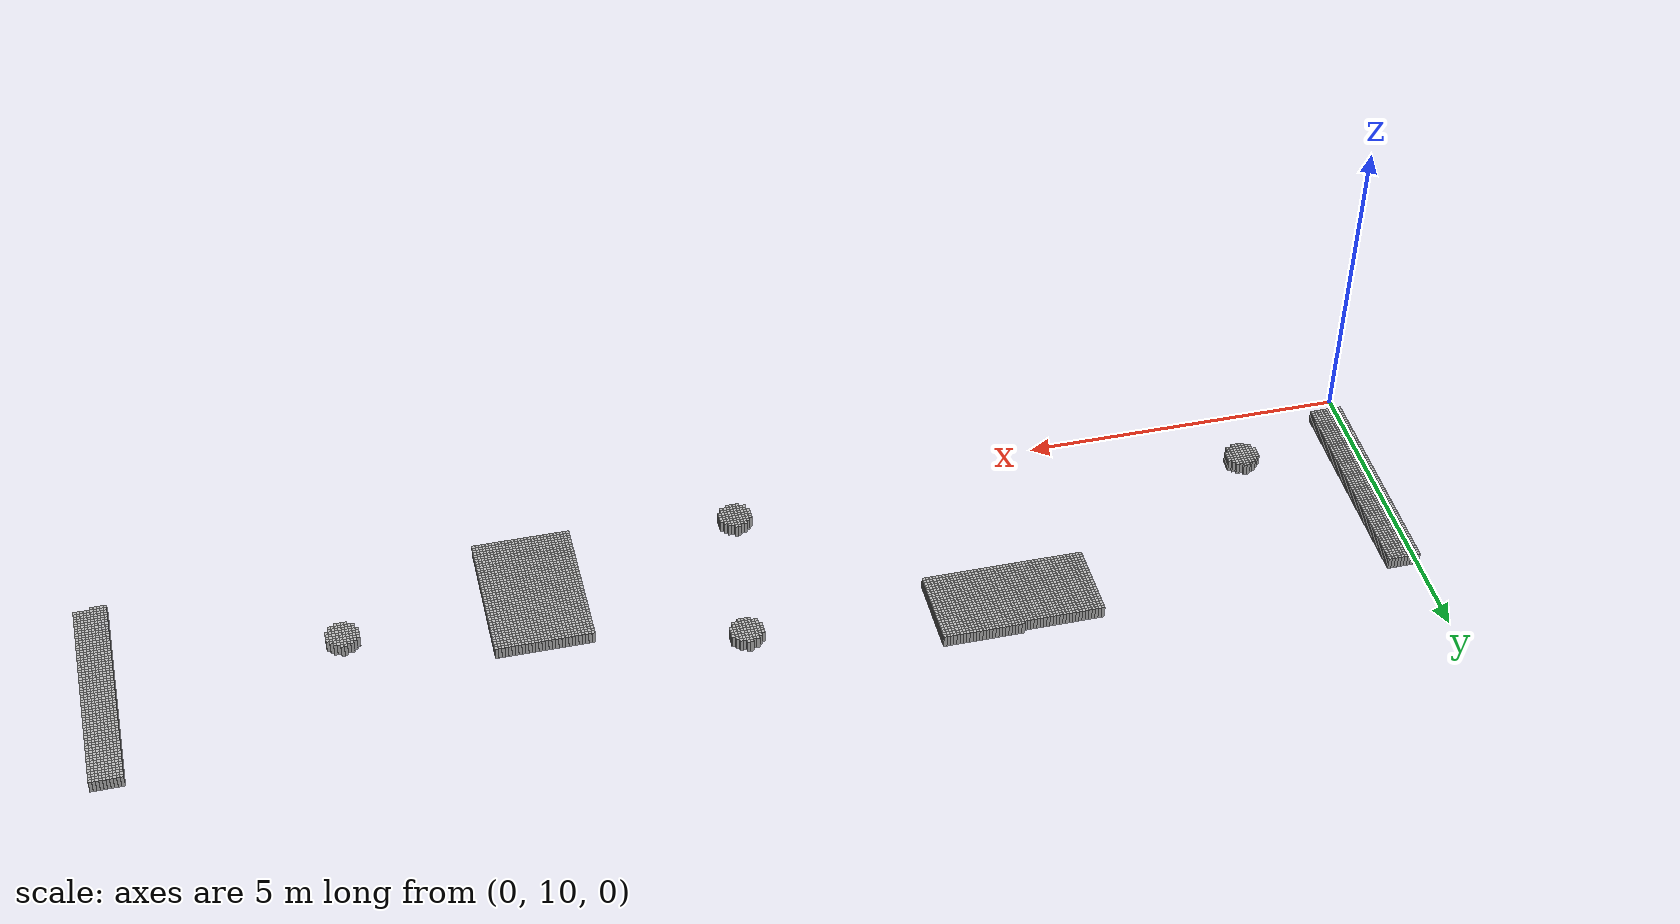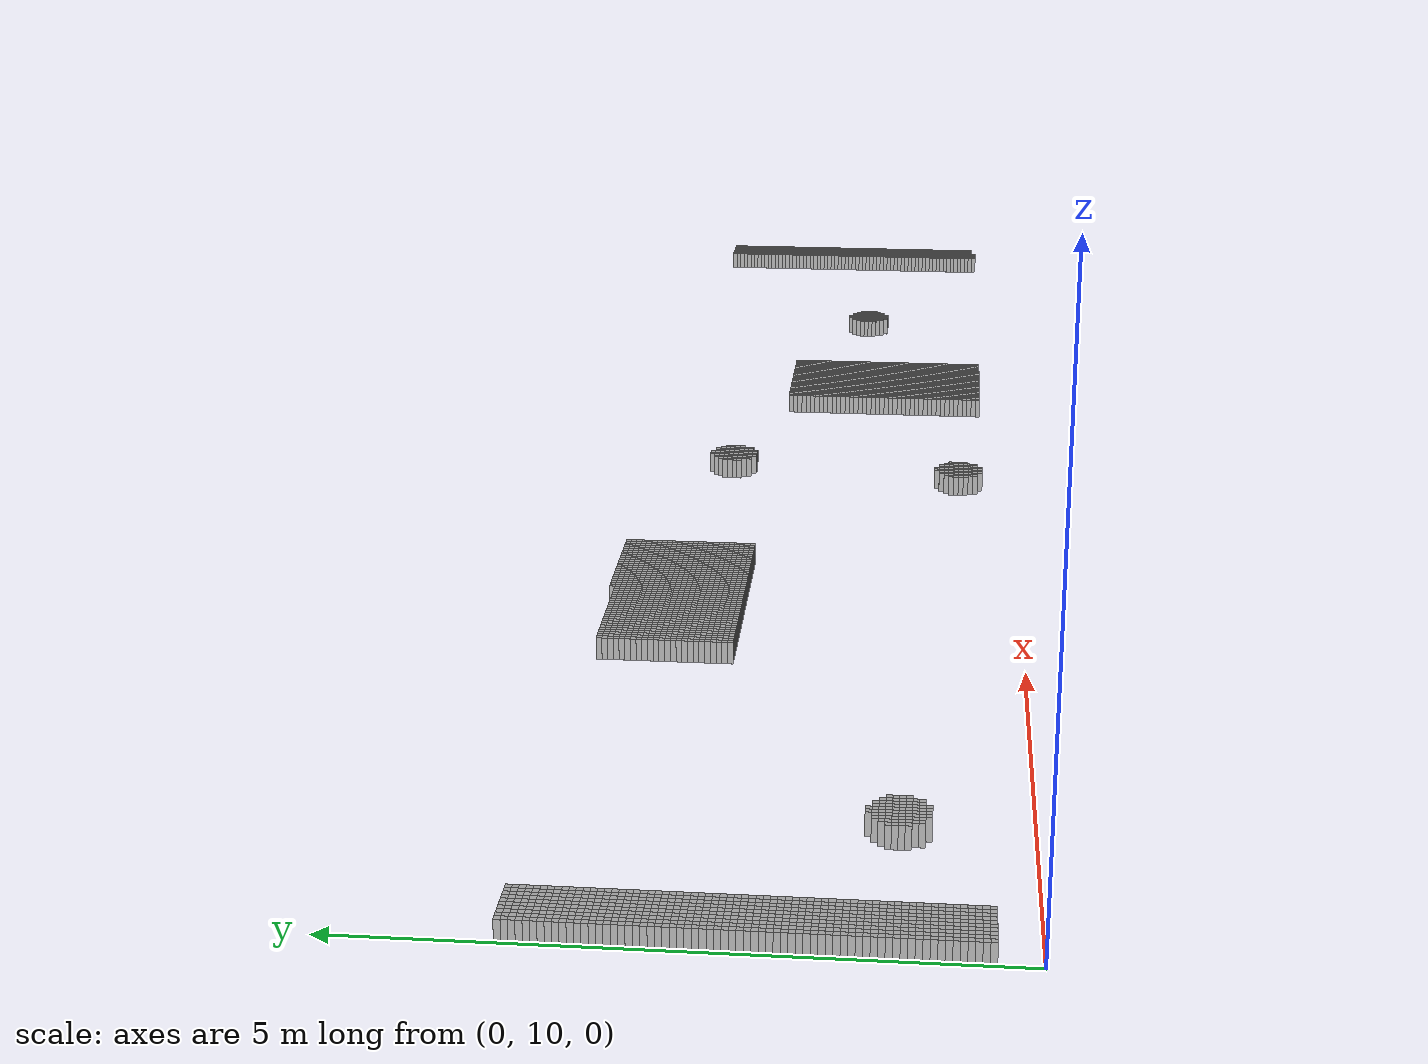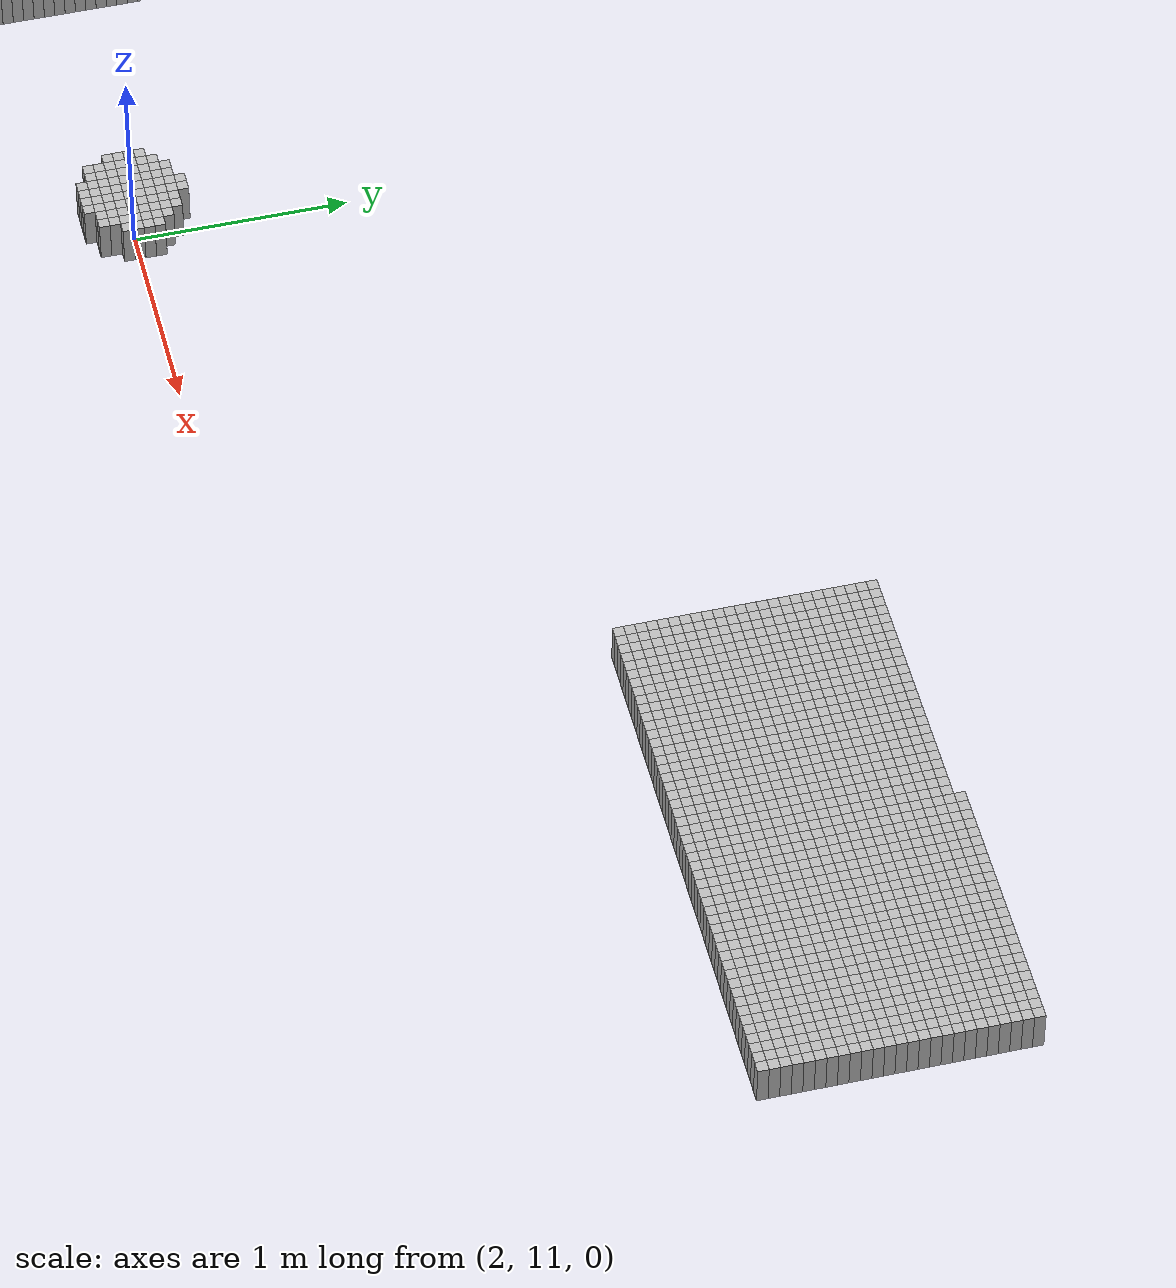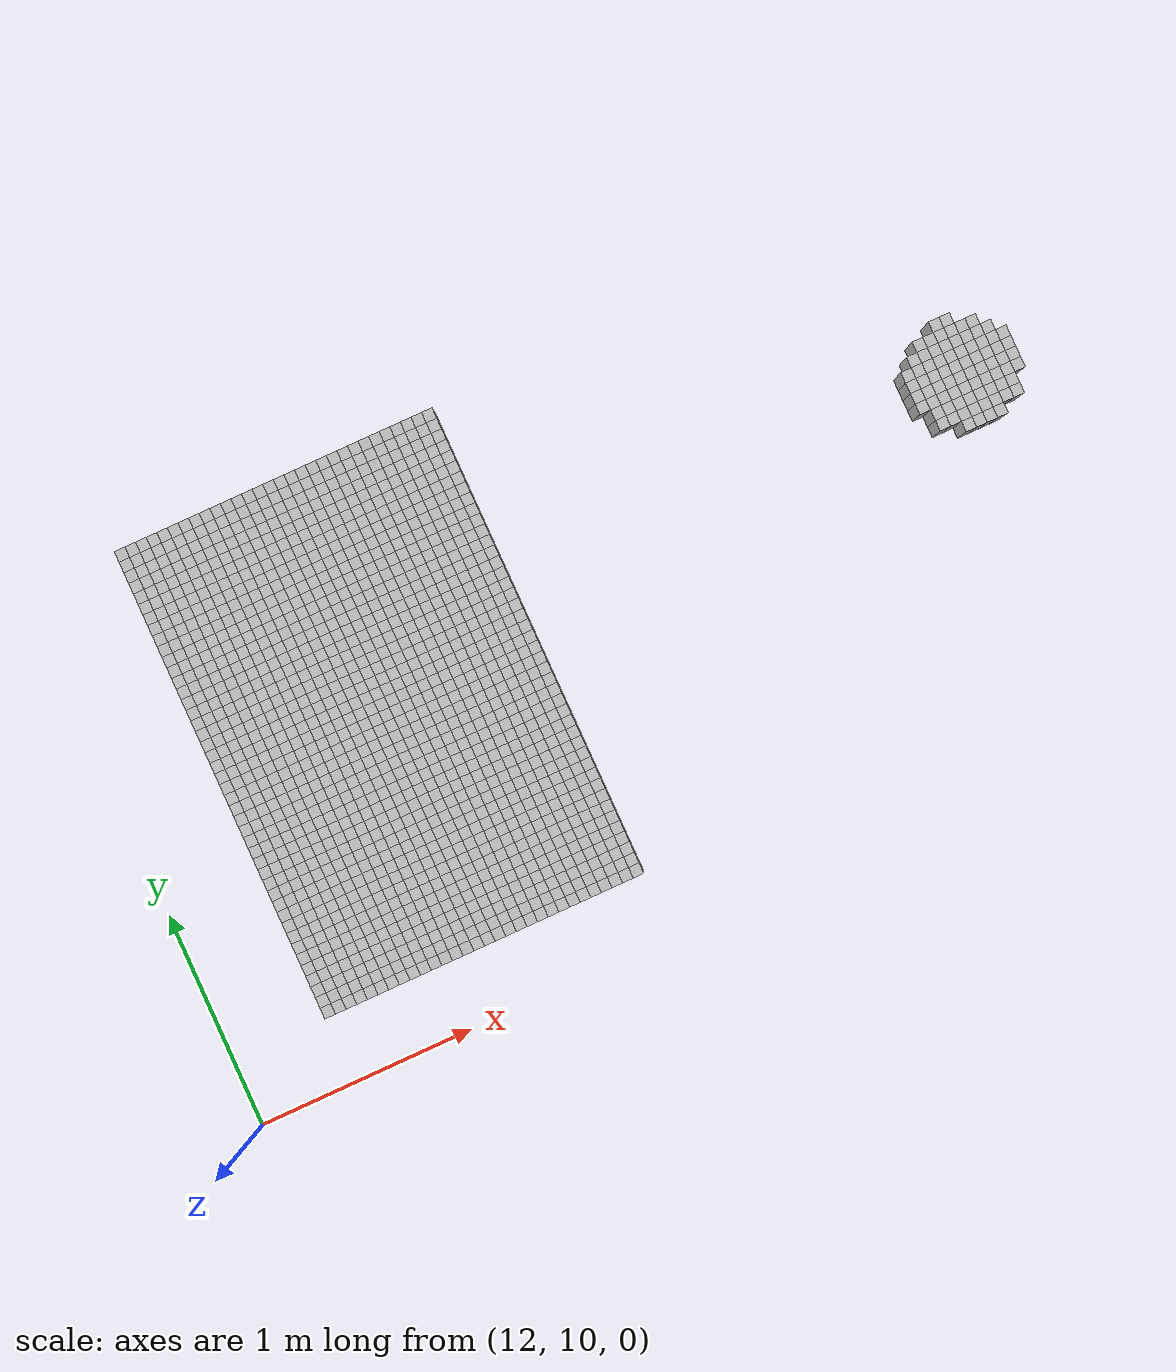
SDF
<sdf version="1.6">
 <world name="default">
  <model name="obstacle_125_125">
   <static>true</static>
   <link name="link">
    <pose>6.25 13.75 0.1 0 0 0</pose>
    <collision name="collision"><geometry><box><size>0.05 0.05 0.2</size></box></geometry></collision>
    <visual name="visual"><geometry><box><size>0.05 0.05 0.2</size></box></geometry></visual>
   </link>
  </model>
  <model name="obstacle_126_125">
   <static>true</static>
   <link name="link">
    <pose>6.300000000000001 13.75 0.1 0 0 0</pose>
    <collision name="collision"><geometry><box><size>0.05 0.05 0.2</size></box></geometry></collision>
    <visual name="visual"><geometry><box><size>0.05 0.05 0.2</size></box></geometry></visual>
   </link>
  </model>
  <model name="obstacle_127_125">
   <static>true</static>
   <link name="link">
    <pose>6.3500000000000005 13.75 0.1 0 0 0</pose>
    <collision name="collision"><geometry><box><size>0.05 0.05 0.2</size></box></geometry></collision>
    <visual name="visual"><geometry><box><size>0.05 0.05 0.2</size></box></geometry></visual>
   </link>
  </model>
  <model name="obstacle_128_125">
   <static>true</static>
   <link name="link">
    <pose>6.4 13.75 0.1 0 0 0</pose>
    <collision name="collision"><geometry><box><size>0.05 0.05 0.2</size></box></geometry></collision>
    <visual name="visual"><geometry><box><size>0.05 0.05 0.2</size></box></geometry></visual>
   </link>
  </model>
  <model name="obstacle_129_125">
   <static>true</static>
   <link name="link">
    <pose>6.45 13.75 0.1 0 0 0</pose>
    <collision name="collision"><geometry><box><size>0.05 0.05 0.2</size></box></geometry></collision>
    <visual name="visual"><geometry><box><size>0.05 0.05 0.2</size></box></geometry></visual>
   </link>
  </model>
  <model name="obstacle_130_125">
   <static>true</static>
   <link name="link">
    <pose>6.5 13.75 0.1 0 0 0</pose>
    <collision name="collision"><geometry><box><size>0.05 0.05 0.2</size></box></geometry></collision>
    <visual name="visual"><geometry><box><size>0.05 0.05 0.2</size></box></geometry></visual>
   </link>
  </model>
  <model name="obstacle_131_125">
   <static>true</static>
   <link name="link">
    <pose>6.550000000000001 13.75 0.1 0 0 0</pose>
    <collision name="collision"><geometry><box><size>0.05 0.05 0.2</size></box></geometry></collision>
    <visual name="visual"><geometry><box><size>0.05 0.05 0.2</size></box></geometry></visual>
   </link>
  </model>
  <model name="obstacle_132_125">
   <static>true</static>
   <link name="link">
    <pose>6.6000000000000005 13.75 0.1 0 0 0</pose>
    <collision name="collision"><geometry><box><size>0.05 0.05 0.2</size></box></geometry></collision>
    <visual name="visual"><geometry><box><size>0.05 0.05 0.2</size></box></geometry></visual>
   </link>
  </model>
  <model name="obstacle_133_125">
   <static>true</static>
   <link name="link">
    <pose>6.65 13.75 0.1 0 0 0</pose>
    <collision name="collision"><geometry><box><size>0.05 0.05 0.2</size></box></geometry></collision>
    <visual name="visual"><geometry><box><size>0.05 0.05 0.2</size></box></geometry></visual>
   </link>
  </model>
  <model name="obstacle_134_125">
   <static>true</static>
   <link name="link">
    <pose>6.7 13.75 0.1 0 0 0</pose>
    <collision name="collision"><geometry><box><size>0.05 0.05 0.2</size></box></geometry></collision>
    <visual name="visual"><geometry><box><size>0.05 0.05 0.2</size></box></geometry></visual>
   </link>
  </model>
  <model name="obstacle_135_125">
   <static>true</static>
   <link name="link">
    <pose>6.75 13.75 0.1 0 0 0</pose>
    <collision name="collision"><geometry><box><size>0.05 0.05 0.2</size></box></geometry></collision>
    <visual name="visual"><geometry><box><size>0.05 0.05 0.2</size></box></geometry></visual>
   </link>
  </model>
  <model name="obstacle_136_125">
   <static>true</static>
   <link name="link">
    <pose>6.800000000000001 13.75 0.1 0 0 0</pose>
    <collision name="collision"><geometry><box><size>0.05 0.05 0.2</size></box></geometry></collision>
    <visual name="visual"><geometry><box><size>0.05 0.05 0.2</size></box></geometry></visual>
   </link>
  </model>
  <model name="obstacle_137_125">
   <static>true</static>
   <link name="link">
    <pose>6.8500000000000005 13.75 0.1 0 0 0</pose>
    <collision name="collision"><geometry><box><size>0.05 0.05 0.2</size></box></geometry></collision>
    <visual name="visual"><geometry><box><size>0.05 0.05 0.2</size></box></geometry></visual>
   </link>
  </model>
  <model name="obstacle_138_125">
   <static>true</static>
   <link name="link">
    <pose>6.9 13.75 0.1 0 0 0</pose>
    <collision name="collision"><geometry><box><size>0.05 0.05 0.2</size></box></geometry></collision>
    <visual name="visual"><geometry><box><size>0.05 0.05 0.2</size></box></geometry></visual>
   </link>
  </model>
  <model name="obstacle_139_125">
   <static>true</static>
   <link name="link">
    <pose>6.95 13.75 0.1 0 0 0</pose>
    <collision name="collision"><geometry><box><size>0.05 0.05 0.2</size></box></geometry></collision>
    <visual name="visual"><geometry><box><size>0.05 0.05 0.2</size></box></geometry></visual>
   </link>
  </model>
  <model name="obstacle_140_125">
   <static>true</static>
   <link name="link">
    <pose>7.0 13.75 0.1 0 0 0</pose>
    <collision name="collision"><geometry><box><size>0.05 0.05 0.2</size></box></geometry></collision>
    <visual name="visual"><geometry><box><size>0.05 0.05 0.2</size></box></geometry></visual>
   </link>
  </model>
  <model name="obstacle_141_125">
   <static>true</static>
   <link name="link">
    <pose>7.050000000000001 13.75 0.1 0 0 0</pose>
    <collision name="collision"><geometry><box><size>0.05 0.05 0.2</size></box></geometry></collision>
    <visual name="visual"><geometry><box><size>0.05 0.05 0.2</size></box></geometry></visual>
   </link>
  </model>
  <model name="obstacle_142_125">
   <static>true</static>
   <link name="link">
    <pose>7.1000000000000005 13.75 0.1 0 0 0</pose>
    <collision name="collision"><geometry><box><size>0.05 0.05 0.2</size></box></geometry></collision>
    <visual name="visual"><geometry><box><size>0.05 0.05 0.2</size></box></geometry></visual>
   </link>
  </model>
  <model name="obstacle_143_125">
   <static>true</static>
   <link name="link">
    <pose>7.15 13.75 0.1 0 0 0</pose>
    <collision name="collision"><geometry><box><size>0.05 0.05 0.2</size></box></geometry></collision>
    <visual name="visual"><geometry><box><size>0.05 0.05 0.2</size></box></geometry></visual>
   </link>
  </model>
  <model name="obstacle_144_125">
   <static>true</static>
   <link name="link">
    <pose>7.2 13.75 0.1 0 0 0</pose>
    <collision name="collision"><geometry><box><size>0.05 0.05 0.2</size></box></geometry></collision>
    <visual name="visual"><geometry><box><size>0.05 0.05 0.2</size></box></geometry></visual>
   </link>
  </model>
  <model name="obstacle_145_125">
   <static>true</static>
   <link name="link">
    <pose>7.25 13.75 0.1 0 0 0</pose>
    <collision name="collision"><geometry><box><size>0.05 0.05 0.2</size></box></geometry></collision>
    <visual name="visual"><geometry><box><size>0.05 0.05 0.2</size></box></geometry></visual>
   </link>
  </model>
  <model name="obstacle_146_125">
   <static>true</static>
   <link name="link">
    <pose>7.300000000000001 13.75 0.1 0 0 0</pose>
    <collision name="collision"><geometry><box><size>0.05 0.05 0.2</size></box></geometry></collision>
    <visual name="visual"><geometry><box><size>0.05 0.05 0.2</size></box></geometry></visual>
   </link>
  </model>
  <model name="obstacle_147_125">
   <static>true</static>
   <link name="link">
    <pose>7.3500000000000005 13.75 0.1 0 0 0</pose>
    <collision name="collision"><geometry><box><size>0.05 0.05 0.2</size></box></geometry></collision>
    <visual name="visual"><geometry><box><size>0.05 0.05 0.2</size></box></geometry></visual>
   </link>
  </model>
  <model name="obstacle_148_125">
   <static>true</static>
   <link name="link">
    <pose>7.4 13.75 0.1 0 0 0</pose>
    <collision name="collision"><geometry><box><size>0.05 0.05 0.2</size></box></geometry></collision>
    <visual name="visual"><geometry><box><size>0.05 0.05 0.2</size></box></geometry></visual>
   </link>
  </model>
  <model name="obstacle_149_125">
   <static>true</static>
   <link name="link">
    <pose>7.45 13.75 0.1 0 0 0</pose>
    <collision name="collision"><geometry><box><size>0.05 0.05 0.2</size></box></geometry></collision>
    <visual name="visual"><geometry><box><size>0.05 0.05 0.2</size></box></geometry></visual>
   </link>
  </model>
  <model name="obstacle_390_125">
   <static>true</static>
   <link name="link">
    <pose>19.5 13.75 0.1 0 0 0</pose>
    <collision name="collision"><geometry><box><size>0.05 0.05 0.2</size></box></geometry></collision>
    <visual name="visual"><geometry><box><size>0.05 0.05 0.2</size></box></geometry></visual>
   </link>
  </model>
  <model name="obstacle_391_125">
   <static>true</static>
   <link name="link">
    <pose>19.55 13.75 0.1 0 0 0</pose>
    <collision name="collision"><geometry><box><size>0.05 0.05 0.2</size></box></geometry></collision>
    <visual name="visual"><geometry><box><size>0.05 0.05 0.2</size></box></geometry></visual>
   </link>
  </model>
  <model name="obstacle_392_125">
   <static>true</static>
   <link name="link">
    <pose>19.6 13.75 0.1 0 0 0</pose>
    <collision name="collision"><geometry><box><size>0.05 0.05 0.2</size></box></geometry></collision>
    <visual name="visual"><geometry><box><size>0.05 0.05 0.2</size></box></geometry></visual>
   </link>
  </model>
  <model name="obstacle_393_125">
   <static>true</static>
   <link name="link">
    <pose>19.650000000000002 13.75 0.1 0 0 0</pose>
    <collision name="collision"><geometry><box><size>0.05 0.05 0.2</size></box></geometry></collision>
    <visual name="visual"><geometry><box><size>0.05 0.05 0.2</size></box></geometry></visual>
   </link>
  </model>
  <model name="obstacle_394_125">
   <static>true</static>
   <link name="link">
    <pose>19.700000000000003 13.75 0.1 0 0 0</pose>
    <collision name="collision"><geometry><box><size>0.05 0.05 0.2</size></box></geometry></collision>
    <visual name="visual"><geometry><box><size>0.05 0.05 0.2</size></box></geometry></visual>
   </link>
  </model>
  <model name="obstacle_395_125">
   <static>true</static>
   <link name="link">
    <pose>19.75 13.75 0.1 0 0 0</pose>
    <collision name="collision"><geometry><box><size>0.05 0.05 0.2</size></box></geometry></collision>
    <visual name="visual"><geometry><box><size>0.05 0.05 0.2</size></box></geometry></visual>
   </link>
  </model>
  <model name="obstacle_396_125">
   <static>true</static>
   <link name="link">
    <pose>19.8 13.75 0.1 0 0 0</pose>
    <collision name="collision"><geometry><box><size>0.05 0.05 0.2</size></box></geometry></collision>
    <visual name="visual"><geometry><box><size>0.05 0.05 0.2</size></box></geometry></visual>
   </link>
  </model>
  <model name="obstacle_397_125">
   <static>true</static>
   <link name="link">
    <pose>19.85 13.75 0.1 0 0 0</pose>
    <collision name="collision"><geometry><box><size>0.05 0.05 0.2</size></box></geometry></collision>
    <visual name="visual"><geometry><box><size>0.05 0.05 0.2</size></box></geometry></visual>
   </link>
  </model>
  <model name="obstacle_398_125">
   <static>true</static>
   <link name="link">
    <pose>19.900000000000002 13.75 0.1 0 0 0</pose>
    <collision name="collision"><geometry><box><size>0.05 0.05 0.2</size></box></geometry></collision>
    <visual name="visual"><geometry><box><size>0.05 0.05 0.2</size></box></geometry></visual>
   </link>
  </model>
  <model name="obstacle_399_125">
   <static>true</static>
   <link name="link">
    <pose>19.950000000000003 13.75 0.1 0 0 0</pose>
    <collision name="collision"><geometry><box><size>0.05 0.05 0.2</size></box></geometry></collision>
    <visual name="visual"><geometry><box><size>0.05 0.05 0.2</size></box></geometry></visual>
   </link>
  </model>
  <model name="obstacle_0_126">
   <static>true</static>
   <link name="link">
    <pose>0.0 13.700000000000001 0.1 0 0 0</pose>
    <collision name="collision"><geometry><box><size>0.05 0.05 0.2</size></box></geometry></collision>
    <visual name="visual"><geometry><box><size>0.05 0.05 0.2</size></box></geometry></visual>
   </link>
  </model>
  <model name="obstacle_1_126">
   <static>true</static>
   <link name="link">
    <pose>0.05 13.700000000000001 0.1 0 0 0</pose>
    <collision name="collision"><geometry><box><size>0.05 0.05 0.2</size></box></geometry></collision>
    <visual name="visual"><geometry><box><size>0.05 0.05 0.2</size></box></geometry></visual>
   </link>
  </model>
  <model name="obstacle_2_126">
   <static>true</static>
   <link name="link">
    <pose>0.1 13.700000000000001 0.1 0 0 0</pose>
    <collision name="collision"><geometry><box><size>0.05 0.05 0.2</size></box></geometry></collision>
    <visual name="visual"><geometry><box><size>0.05 0.05 0.2</size></box></geometry></visual>
   </link>
  </model>
  <model name="obstacle_3_126">
   <static>true</static>
   <link name="link">
    <pose>0.15000000000000002 13.700000000000001 0.1 0 0 0</pose>
    <collision name="collision"><geometry><box><size>0.05 0.05 0.2</size></box></geometry></collision>
    <visual name="visual"><geometry><box><size>0.05 0.05 0.2</size></box></geometry></visual>
   </link>
  </model>
  <model name="obstacle_4_126">
   <static>true</static>
   <link name="link">
    <pose>0.2 13.700000000000001 0.1 0 0 0</pose>
    <collision name="collision"><geometry><box><size>0.05 0.05 0.2</size></box></geometry></collision>
    <visual name="visual"><geometry><box><size>0.05 0.05 0.2</size></box></geometry></visual>
   </link>
  </model>
  <model name="obstacle_5_126">
   <static>true</static>
   <link name="link">
    <pose>0.25 13.700000000000001 0.1 0 0 0</pose>
    <collision name="collision"><geometry><box><size>0.05 0.05 0.2</size></box></geometry></collision>
    <visual name="visual"><geometry><box><size>0.05 0.05 0.2</size></box></geometry></visual>
   </link>
  </model>
  <model name="obstacle_6_126">
   <static>true</static>
   <link name="link">
    <pose>0.30000000000000004 13.700000000000001 0.1 0 0 0</pose>
    <collision name="collision"><geometry><box><size>0.05 0.05 0.2</size></box></geometry></collision>
    <visual name="visual"><geometry><box><size>0.05 0.05 0.2</size></box></geometry></visual>
   </link>
  </model>
  <model name="obstacle_7_126">
   <static>true</static>
   <link name="link">
    <pose>0.35000000000000003 13.700000000000001 0.1 0 0 0</pose>
    <collision name="collision"><geometry><box><size>0.05 0.05 0.2</size></box></geometry></collision>
    <visual name="visual"><geometry><box><size>0.05 0.05 0.2</size></box></geometry></visual>
   </link>
  </model>
  <model name="obstacle_8_126">
   <static>true</static>
   <link name="link">
    <pose>0.4 13.700000000000001 0.1 0 0 0</pose>
    <collision name="collision"><geometry><box><size>0.05 0.05 0.2</size></box></geometry></collision>
    <visual name="visual"><geometry><box><size>0.05 0.05 0.2</size></box></geometry></visual>
   </link>
  </model>
  <model name="obstacle_9_126">
   <static>true</static>
   <link name="link">
    <pose>0.45 13.700000000000001 0.1 0 0 0</pose>
    <collision name="collision"><geometry><box><size>0.05 0.05 0.2</size></box></geometry></collision>
    <visual name="visual"><geometry><box><size>0.05 0.05 0.2</size></box></geometry></visual>
   </link>
  </model>
  <model name="obstacle_100_126">
   <static>true</static>
   <link name="link">
    <pose>5.0 13.700000000000001 0.1 0 0 0</pose>
    <collision name="collision"><geometry><box><size>0.05 0.05 0.2</size></box></geometry></collision>
    <visual name="visual"><geometry><box><size>0.05 0.05 0.2</size></box></geometry></visual>
   </link>
  </model>
  <model name="obstacle_101_126">
   <static>true</static>
   <link name="link">
    <pose>5.050000000000001 13.700000000000001 0.1 0 0 0</pose>
    <collision name="collision"><geometry><box><size>0.05 0.05 0.2</size></box></geometry></collision>
    <visual name="visual"><geometry><box><size>0.05 0.05 0.2</size></box></geometry></visual>
   </link>
  </model>
  <model name="obstacle_102_126">
   <static>true</static>
   <link name="link">
    <pose>5.1000000000000005 13.700000000000001 0.1 0 0 0</pose>
    <collision name="collision"><geometry><box><size>0.05 0.05 0.2</size></box></geometry></collision>
    <visual name="visual"><geometry><box><size>0.05 0.05 0.2</size></box></geometry></visual>
   </link>
  </model>
  <model name="obstacle_103_126">
   <static>true</static>
   <link name="link">
    <pose>5.15 13.700000000000001 0.1 0 0 0</pose>
    <collision name="collision"><geometry><box><size>0.05 0.05 0.2</size></box></geometry></collision>
    <visual name="visual"><geometry><box><size>0.05 0.05 0.2</size></box></geometry></visual>
   </link>
  </model>
  <model name="obstacle_104_126">
   <static>true</static>
   <link name="link">
    <pose>5.2 13.700000000000001 0.1 0 0 0</pose>
    <collision name="collision"><geometry><box><size>0.05 0.05 0.2</size></box></geometry></collision>
    <visual name="visual"><geometry><box><size>0.05 0.05 0.2</size></box></geometry></visual>
   </link>
  </model>
  <model name="obstacle_105_126">
   <static>true</static>
   <link name="link">
    <pose>5.25 13.700000000000001 0.1 0 0 0</pose>
    <collision name="collision"><geometry><box><size>0.05 0.05 0.2</size></box></geometry></collision>
    <visual name="visual"><geometry><box><size>0.05 0.05 0.2</size></box></geometry></visual>
   </link>
  </model>
  <model name="obstacle_106_126">
   <static>true</static>
   <link name="link">
    <pose>5.300000000000001 13.700000000000001 0.1 0 0 0</pose>
    <collision name="collision"><geometry><box><size>0.05 0.05 0.2</size></box></geometry></collision>
    <visual name="visual"><geometry><box><size>0.05 0.05 0.2</size></box></geometry></visual>
   </link>
  </model>
  <model name="obstacle_107_126">
   <static>true</static>
   <link name="link">
    <pose>5.3500000000000005 13.700000000000001 0.1 0 0 0</pose>
    <collision name="collision"><geometry><box><size>0.05 0.05 0.2</size></box></geometry></collision>
    <visual name="visual"><geometry><box><size>0.05 0.05 0.2</size></box></geometry></visual>
   </link>
  </model>
  <model name="obstacle_108_126">
   <static>true</static>
   <link name="link">
    <pose>5.4 13.700000000000001 0.1 0 0 0</pose>
    <collision name="collision"><geometry><box><size>0.05 0.05 0.2</size></box></geometry></collision>
    <visual name="visual"><geometry><box><size>0.05 0.05 0.2</size></box></geometry></visual>
   </link>
  </model>
  <model name="obstacle_109_126">
   <static>true</static>
   <link name="link">
    <pose>5.45 13.700000000000001 0.1 0 0 0</pose>
    <collision name="collision"><geometry><box><size>0.05 0.05 0.2</size></box></geometry></collision>
    <visual name="visual"><geometry><box><size>0.05 0.05 0.2</size></box></geometry></visual>
   </link>
  </model>
  <model name="obstacle_110_126">
   <static>true</static>
   <link name="link">
    <pose>5.5 13.700000000000001 0.1 0 0 0</pose>
    <collision name="collision"><geometry><box><size>0.05 0.05 0.2</size></box></geometry></collision>
    <visual name="visual"><geometry><box><size>0.05 0.05 0.2</size></box></geometry></visual>
   </link>
  </model>
  <model name="obstacle_111_126">
   <static>true</static>
   <link name="link">
    <pose>5.550000000000001 13.700000000000001 0.1 0 0 0</pose>
    <collision name="collision"><geometry><box><size>0.05 0.05 0.2</size></box></geometry></collision>
    <visual name="visual"><geometry><box><size>0.05 0.05 0.2</size></box></geometry></visual>
   </link>
  </model>
  <model name="obstacle_112_126">
   <static>true</static>
   <link name="link">
    <pose>5.6000000000000005 13.700000000000001 0.1 0 0 0</pose>
    <collision name="collision"><geometry><box><size>0.05 0.05 0.2</size></box></geometry></collision>
    <visual name="visual"><geometry><box><size>0.05 0.05 0.2</size></box></geometry></visual>
   </link>
  </model>
  <model name="obstacle_113_126">
   <static>true</static>
   <link name="link">
    <pose>5.65 13.700000000000001 0.1 0 0 0</pose>
    <collision name="collision"><geometry><box><size>0.05 0.05 0.2</size></box></geometry></collision>
    <visual name="visual"><geometry><box><size>0.05 0.05 0.2</size></box></geometry></visual>
   </link>
  </model>
  <model name="obstacle_114_126">
   <static>true</static>
   <link name="link">
    <pose>5.7 13.700000000000001 0.1 0 0 0</pose>
    <collision name="collision"><geometry><box><size>0.05 0.05 0.2</size></box></geometry></collision>
    <visual name="visual"><geometry><box><size>0.05 0.05 0.2</size></box></geometry></visual>
   </link>
  </model>
  <model name="obstacle_115_126">
   <static>true</static>
   <link name="link">
    <pose>5.75 13.700000000000001 0.1 0 0 0</pose>
    <collision name="collision"><geometry><box><size>0.05 0.05 0.2</size></box></geometry></collision>
    <visual name="visual"><geometry><box><size>0.05 0.05 0.2</size></box></geometry></visual>
   </link>
  </model>
  <model name="obstacle_116_126">
   <static>true</static>
   <link name="link">
    <pose>5.800000000000001 13.700000000000001 0.1 0 0 0</pose>
    <collision name="collision"><geometry><box><size>0.05 0.05 0.2</size></box></geometry></collision>
    <visual name="visual"><geometry><box><size>0.05 0.05 0.2</size></box></geometry></visual>
   </link>
  </model>
  <model name="obstacle_117_126">
   <static>true</static>
   <link name="link">
    <pose>5.8500000000000005 13.700000000000001 0.1 0 0 0</pose>
    <collision name="collision"><geometry><box><size>0.05 0.05 0.2</size></box></geometry></collision>
    <visual name="visual"><geometry><box><size>0.05 0.05 0.2</size></box></geometry></visual>
   </link>
  </model>
  <model name="obstacle_118_126">
   <static>true</static>
   <link name="link">
    <pose>5.9 13.700000000000001 0.1 0 0 0</pose>
    <collision name="collision"><geometry><box><size>0.05 0.05 0.2</size></box></geometry></collision>
    <visual name="visual"><geometry><box><size>0.05 0.05 0.2</size></box></geometry></visual>
   </link>
  </model>
  <model name="obstacle_119_126">
   <static>true</static>
   <link name="link">
    <pose>5.95 13.700000000000001 0.1 0 0 0</pose>
    <collision name="collision"><geometry><box><size>0.05 0.05 0.2</size></box></geometry></collision>
    <visual name="visual"><geometry><box><size>0.05 0.05 0.2</size></box></geometry></visual>
   </link>
  </model>
  <model name="obstacle_120_126">
   <static>true</static>
   <link name="link">
    <pose>6.0 13.700000000000001 0.1 0 0 0</pose>
    <collision name="collision"><geometry><box><size>0.05 0.05 0.2</size></box></geometry></collision>
    <visual name="visual"><geometry><box><size>0.05 0.05 0.2</size></box></geometry></visual>
   </link>
  </model>
  <model name="obstacle_121_126">
   <static>true</static>
   <link name="link">
    <pose>6.050000000000001 13.700000000000001 0.1 0 0 0</pose>
    <collision name="collision"><geometry><box><size>0.05 0.05 0.2</size></box></geometry></collision>
    <visual name="visual"><geometry><box><size>0.05 0.05 0.2</size></box></geometry></visual>
   </link>
  </model>
  <model name="obstacle_122_126">
   <static>true</static>
   <link name="link">
    <pose>6.1000000000000005 13.700000000000001 0.1 0 0 0</pose>
    <collision name="collision"><geometry><box><size>0.05 0.05 0.2</size></box></geometry></collision>
    <visual name="visual"><geometry><box><size>0.05 0.05 0.2</size></box></geometry></visual>
   </link>
  </model>
  <model name="obstacle_123_126">
   <static>true</static>
   <link name="link">
    <pose>6.15 13.700000000000001 0.1 0 0 0</pose>
    <collision name="collision"><geometry><box><size>0.05 0.05 0.2</size></box></geometry></collision>
    <visual name="visual"><geometry><box><size>0.05 0.05 0.2</size></box></geometry></visual>
   </link>
  </model>
  <model name="obstacle_124_126">
   <static>true</static>
   <link name="link">
    <pose>6.2 13.700000000000001 0.1 0 0 0</pose>
    <collision name="collision"><geometry><box><size>0.05 0.05 0.2</size></box></geometry></collision>
    <visual name="visual"><geometry><box><size>0.05 0.05 0.2</size></box></geometry></visual>
   </link>
  </model>
  <model name="obstacle_125_126">
   <static>true</static>
   <link name="link">
    <pose>6.25 13.700000000000001 0.1 0 0 0</pose>
    <collision name="collision"><geometry><box><size>0.05 0.05 0.2</size></box></geometry></collision>
    <visual name="visual"><geometry><box><size>0.05 0.05 0.2</size></box></geometry></visual>
   </link>
  </model>
  <model name="obstacle_126_126">
   <static>true</static>
   <link name="link">
    <pose>6.300000000000001 13.700000000000001 0.1 0 0 0</pose>
    <collision name="collision"><geometry><box><size>0.05 0.05 0.2</size></box></geometry></collision>
    <visual name="visual"><geometry><box><size>0.05 0.05 0.2</size></box></geometry></visual>
   </link>
  </model>
  <model name="obstacle_127_126">
   <static>true</static>
   <link name="link">
    <pose>6.3500000000000005 13.700000000000001 0.1 0 0 0</pose>
    <collision name="collision"><geometry><box><size>0.05 0.05 0.2</size></box></geometry></collision>
    <visual name="visual"><geometry><box><size>0.05 0.05 0.2</size></box></geometry></visual>
   </link>
  </model>
  <model name="obstacle_128_126">
   <static>true</static>
   <link name="link">
    <pose>6.4 13.700000000000001 0.1 0 0 0</pose>
    <collision name="collision"><geometry><box><size>0.05 0.05 0.2</size></box></geometry></collision>
    <visual name="visual"><geometry><box><size>0.05 0.05 0.2</size></box></geometry></visual>
   </link>
  </model>
  <model name="obstacle_129_126">
   <static>true</static>
   <link name="link">
    <pose>6.45 13.700000000000001 0.1 0 0 0</pose>
    <collision name="collision"><geometry><box><size>0.05 0.05 0.2</size></box></geometry></collision>
    <visual name="visual"><geometry><box><size>0.05 0.05 0.2</size></box></geometry></visual>
   </link>
  </model>
  <model name="obstacle_130_126">
   <static>true</static>
   <link name="link">
    <pose>6.5 13.700000000000001 0.1 0 0 0</pose>
    <collision name="collision"><geometry><box><size>0.05 0.05 0.2</size></box></geometry></collision>
    <visual name="visual"><geometry><box><size>0.05 0.05 0.2</size></box></geometry></visual>
   </link>
  </model>
  <model name="obstacle_131_126">
   <static>true</static>
   <link name="link">
    <pose>6.550000000000001 13.700000000000001 0.1 0 0 0</pose>
    <collision name="collision"><geometry><box><size>0.05 0.05 0.2</size></box></geometry></collision>
    <visual name="visual"><geometry><box><size>0.05 0.05 0.2</size></box></geometry></visual>
   </link>
  </model>
  <model name="obstacle_132_126">
   <static>true</static>
   <link name="link">
    <pose>6.6000000000000005 13.700000000000001 0.1 0 0 0</pose>
    <collision name="collision"><geometry><box><size>0.05 0.05 0.2</size></box></geometry></collision>
    <visual name="visual"><geometry><box><size>0.05 0.05 0.2</size></box></geometry></visual>
   </link>
  </model>
  <model name="obstacle_133_126">
   <static>true</static>
   <link name="link">
    <pose>6.65 13.700000000000001 0.1 0 0 0</pose>
    <collision name="collision"><geometry><box><size>0.05 0.05 0.2</size></box></geometry></collision>
    <visual name="visual"><geometry><box><size>0.05 0.05 0.2</size></box></geometry></visual>
   </link>
  </model>
  <model name="obstacle_134_126">
   <static>true</static>
   <link name="link">
    <pose>6.7 13.700000000000001 0.1 0 0 0</pose>
    <collision name="collision"><geometry><box><size>0.05 0.05 0.2</size></box></geometry></collision>
    <visual name="visual"><geometry><box><size>0.05 0.05 0.2</size></box></geometry></visual>
   </link>
  </model>
  <model name="obstacle_135_126">
   <static>true</static>
   <link name="link">
    <pose>6.75 13.700000000000001 0.1 0 0 0</pose>
    <collision name="collision"><geometry><box><size>0.05 0.05 0.2</size></box></geometry></collision>
    <visual name="visual"><geometry><box><size>0.05 0.05 0.2</size></box></geometry></visual>
   </link>
  </model>
  <model name="obstacle_136_126">
   <static>true</static>
   <link name="link">
    <pose>6.800000000000001 13.700000000000001 0.1 0 0 0</pose>
    <collision name="collision"><geometry><box><size>0.05 0.05 0.2</size></box></geometry></collision>
    <visual name="visual"><geometry><box><size>0.05 0.05 0.2</size></box></geometry></visual>
   </link>
  </model>
  <model name="obstacle_137_126">
   <static>true</static>
   <link name="link">
    <pose>6.8500000000000005 13.700000000000001 0.1 0 0 0</pose>
    <collision name="collision"><geometry><box><size>0.05 0.05 0.2</size></box></geometry></collision>
    <visual name="visual"><geometry><box><size>0.05 0.05 0.2</size></box></geometry></visual>
   </link>
  </model>
  <model name="obstacle_138_126">
   <static>true</static>
   <link name="link">
    <pose>6.9 13.700000000000001 0.1 0 0 0</pose>
    <collision name="collision"><geometry><box><size>0.05 0.05 0.2</size></box></geometry></collision>
    <visual name="visual"><geometry><box><size>0.05 0.05 0.2</size></box></geometry></visual>
   </link>
  </model>
  <model name="obstacle_139_126">
   <static>true</static>
   <link name="link">
    <pose>6.95 13.700000000000001 0.1 0 0 0</pose>
    <collision name="collision"><geometry><box><size>0.05 0.05 0.2</size></box></geometry></collision>
    <visual name="visual"><geometry><box><size>0.05 0.05 0.2</size></box></geometry></visual>
   </link>
  </model>
  <model name="obstacle_140_126">
   <static>true</static>
   <link name="link">
    <pose>7.0 13.700000000000001 0.1 0 0 0</pose>
    <collision name="collision"><geometry><box><size>0.05 0.05 0.2</size></box></geometry></collision>
    <visual name="visual"><geometry><box><size>0.05 0.05 0.2</size></box></geometry></visual>
   </link>
  </model>
  <model name="obstacle_141_126">
   <static>true</static>
   <link name="link">
    <pose>7.050000000000001 13.700000000000001 0.1 0 0 0</pose>
    <collision name="collision"><geometry><box><size>0.05 0.05 0.2</size></box></geometry></collision>
    <visual name="visual"><geometry><box><size>0.05 0.05 0.2</size></box></geometry></visual>
   </link>
  </model>
  <model name="obstacle_142_126">
   <static>true</static>
   <link name="link">
    <pose>7.1000000000000005 13.700000000000001 0.1 0 0 0</pose>
    <collision name="collision"><geometry><box><size>0.05 0.05 0.2</size></box></geometry></collision>
    <visual name="visual"><geometry><box><size>0.05 0.05 0.2</size></box></geometry></visual>
   </link>
  </model>
  <model name="obstacle_143_126">
   <static>true</static>
   <link name="link">
    <pose>7.15 13.700000000000001 0.1 0 0 0</pose>
    <collision name="collision"><geometry><box><size>0.05 0.05 0.2</size></box></geometry></collision>
    <visual name="visual"><geometry><box><size>0.05 0.05 0.2</size></box></geometry></visual>
   </link>
  </model>
  <model name="obstacle_144_126">
   <static>true</static>
   <link name="link">
    <pose>7.2 13.700000000000001 0.1 0 0 0</pose>
    <collision name="collision"><geometry><box><size>0.05 0.05 0.2</size></box></geometry></collision>
    <visual name="visual"><geometry><box><size>0.05 0.05 0.2</size></box></geometry></visual>
   </link>
  </model>
  <model name="obstacle_145_126">
   <static>true</static>
   <link name="link">
    <pose>7.25 13.700000000000001 0.1 0 0 0</pose>
    <collision name="collision"><geometry><box><size>0.05 0.05 0.2</size></box></geometry></collision>
    <visual name="visual"><geometry><box><size>0.05 0.05 0.2</size></box></geometry></visual>
   </link>
  </model>
  <model name="obstacle_146_126">
   <static>true</static>
   <link name="link">
    <pose>7.300000000000001 13.700000000000001 0.1 0 0 0</pose>
    <collision name="collision"><geometry><box><size>0.05 0.05 0.2</size></box></geometry></collision>
    <visual name="visual"><geometry><box><size>0.05 0.05 0.2</size></box></geometry></visual>
   </link>
  </model>
  <model name="obstacle_147_126">
   <static>true</static>
   <link name="link">
    <pose>7.3500000000000005 13.700000000000001 0.1 0 0 0</pose>
    <collision name="collision"><geometry><box><size>0.05 0.05 0.2</size></box></geometry></collision>
    <visual name="visual"><geometry><box><size>0.05 0.05 0.2</size></box></geometry></visual>
   </link>
  </model>
  <model name="obstacle_148_126">
   <static>true</static>
   <link name="link">
    <pose>7.4 13.700000000000001 0.1 0 0 0</pose>
    <collision name="collision"><geometry><box><size>0.05 0.05 0.2</size></box></geometry></collision>
    <visual name="visual"><geometry><box><size>0.05 0.05 0.2</size></box></geometry></visual>
   </link>
  </model>
  <model name="obstacle_149_126">
   <static>true</static>
   <link name="link">
    <pose>7.45 13.700000000000001 0.1 0 0 0</pose>
    <collision name="collision"><geometry><box><size>0.05 0.05 0.2</size></box></geometry></collision>
    <visual name="visual"><geometry><box><size>0.05 0.05 0.2</size></box></geometry></visual>
   </link>
  </model>
  <model name="obstacle_390_126">
   <static>true</static>
   <link name="link">
    <pose>19.5 13.700000000000001 0.1 0 0 0</pose>
    <collision name="collision"><geometry><box><size>0.05 0.05 0.2</size></box></geometry></collision>
    <visual name="visual"><geometry><box><size>0.05 0.05 0.2</size></box></geometry></visual>
   </link>
  </model>
  <model name="obstacle_391_126">
   <static>true</static>
   <link name="link">
    <pose>19.55 13.700000000000001 0.1 0 0 0</pose>
    <collision name="collision"><geometry><box><size>0.05 0.05 0.2</size></box></geometry></collision>
    <visual name="visual"><geometry><box><size>0.05 0.05 0.2</size></box></geometry></visual>
   </link>
  </model>
  <model name="obstacle_392_126">
   <static>true</static>
   <link name="link">
    <pose>19.6 13.700000000000001 0.1 0 0 0</pose>
    <collision name="collision"><geometry><box><size>0.05 0.05 0.2</size></box></geometry></collision>
    <visual name="visual"><geometry><box><size>0.05 0.05 0.2</size></box></geometry></visual>
   </link>
  </model>
  <model name="obstacle_393_126">
   <static>true</static>
   <link name="link">
    <pose>19.650000000000002 13.700000000000001 0.1 0 0 0</pose>
    <collision name="collision"><geometry><box><size>0.05 0.05 0.2</size></box></geometry></collision>
    <visual name="visual"><geometry><box><size>0.05 0.05 0.2</size></box></geometry></visual>
   </link>
  </model>
  <model name="obstacle_394_126">
   <static>true</static>
   <link name="link">
    <pose>19.700000000000003 13.700000000000001 0.1 0 0 0</pose>
    <collision name="collision"><geometry><box><size>0.05 0.05 0.2</size></box></geometry></collision>
    <visual name="visual"><geometry><box><size>0.05 0.05 0.2</size></box></geometry></visual>
   </link>
  </model>
  <model name="obstacle_395_126">
   <static>true</static>
   <link name="link">
    <pose>19.75 13.700000000000001 0.1 0 0 0</pose>
    <collision name="collision"><geometry><box><size>0.05 0.05 0.2</size></box></geometry></collision>
    <visual name="visual"><geometry><box><size>0.05 0.05 0.2</size></box></geometry></visual>
   </link>
  </model>
  <model name="obstacle_396_126">
   <static>true</static>
   <link name="link">
    <pose>19.8 13.700000000000001 0.1 0 0 0</pose>
    <collision name="collision"><geometry><box><size>0.05 0.05 0.2</size></box></geometry></collision>
    <visual name="visual"><geometry><box><size>0.05 0.05 0.2</size></box></geometry></visual>
   </link>
  </model>
  <model name="obstacle_397_126">
   <static>true</static>
   <link name="link">
    <pose>19.85 13.700000000000001 0.1 0 0 0</pose>
    <collision name="collision"><geometry><box><size>0.05 0.05 0.2</size></box></geometry></collision>
    <visual name="visual"><geometry><box><size>0.05 0.05 0.2</size></box></geometry></visual>
   </link>
  </model>
  <model name="obstacle_398_126">
   <static>true</static>
   <link name="link">
    <pose>19.900000000000002 13.700000000000001 0.1 0 0 0</pose>
    <collision name="collision"><geometry><box><size>0.05 0.05 0.2</size></box></geometry></collision>
    <visual name="visual"><geometry><box><size>0.05 0.05 0.2</size></box></geometry></visual>
   </link>
  </model>
  <model name="obstacle_399_126">
   <static>true</static>
   <link name="link">
    <pose>19.950000000000003 13.700000000000001 0.1 0 0 0</pose>
    <collision name="collision"><geometry><box><size>0.05 0.05 0.2</size></box></geometry></collision>
    <visual name="visual"><geometry><box><size>0.05 0.05 0.2</size></box></geometry></visual>
   </link>
  </model>
  <model name="obstacle_0_127">
   <static>true</static>
   <link name="link">
    <pose>0.0 13.65 0.1 0 0 0</pose>
    <collision name="collision"><geometry><box><size>0.05 0.05 0.2</size></box></geometry></collision>
    <visual name="visual"><geometry><box><size>0.05 0.05 0.2</size></box></geometry></visual>
   </link>
  </model>
  <model name="obstacle_1_127">
   <static>true</static>
   <link name="link">
    <pose>0.05 13.65 0.1 0 0 0</pose>
    <collision name="collision"><geometry><box><size>0.05 0.05 0.2</size></box></geometry></collision>
    <visual name="visual"><geometry><box><size>0.05 0.05 0.2</size></box></geometry></visual>
   </link>
  </model>
  <model name="obstacle_2_127">
   <static>true</static>
   <link name="link">
    <pose>0.1 13.65 0.1 0 0 0</pose>
    <collision name="collision"><geometry><box><size>0.05 0.05 0.2</size></box></geometry></collision>
    <visual name="visual"><geometry><box><size>0.05 0.05 0.2</size></box></geometry></visual>
   </link>
  </model>
  <model name="obstacle_3_127">
   <static>true</static>
   <link name="link">
    <pose>0.15000000000000002 13.65 0.1 0 0 0</pose>
    <collision name="collision"><geometry><box><size>0.05 0.05 0.2</size></box></geometry></collision>
    <visual name="visual"><geometry><box><size>0.05 0.05 0.2</size></box></geometry></visual>
   </link>
  </model>
  <model name="obstacle_4_127">
   <static>true</static>
   <link name="link">
    <pose>0.2 13.65 0.1 0 0 0</pose>
    <collision name="collision"><geometry><box><size>0.05 0.05 0.2</size></box></geometry></collision>
    <visual name="visual"><geometry><box><size>0.05 0.05 0.2</size></box></geometry></visual>
   </link>
  </model>
  <model name="obstacle_5_127">
   <static>true</static>
   <link name="link">
    <pose>0.25 13.65 0.1 0 0 0</pose>
    <collision name="collision"><geometry><box><size>0.05 0.05 0.2</size></box></geometry></collision>
    <visual name="visual"><geometry><box><size>0.05 0.05 0.2</size></box></geometry></visual>
   </link>
  </model>
  <model name="obstacle_6_127">
   <static>true</static>
   <link name="link">
    <pose>0.30000000000000004 13.65 0.1 0 0 0</pose>
    <collision name="collision"><geometry><box><size>0.05 0.05 0.2</size></box></geometry></collision>
    <visual name="visual"><geometry><box><size>0.05 0.05 0.2</size></box></geometry></visual>
   </link>
  </model>
  <model name="obstacle_7_127">
   <static>true</static>
   <link name="link">
    <pose>0.35000000000000003 13.65 0.1 0 0 0</pose>
    <collision name="collision"><geometry><box><size>0.05 0.05 0.2</size></box></geometry></collision>
    <visual name="visual"><geometry><box><size>0.05 0.05 0.2</size></box></geometry></visual>
   </link>
  </model>
  <model name="obstacle_8_127">
   <static>true</static>
   <link name="link">
    <pose>0.4 13.65 0.1 0 0 0</pose>
    <collision name="collision"><geometry><box><size>0.05 0.05 0.2</size></box></geometry></collision>
    <visual name="visual"><geometry><box><size>0.05 0.05 0.2</size></box></geometry></visual>
   </link>
  </model>
  <model name="obstacle_9_127">
   <static>true</static>
   <link name="link">
    <pose>0.45 13.65 0.1 0 0 0</pose>
    <collision name="collision"><geometry><box><size>0.05 0.05 0.2</size></box></geometry></collision>
    <visual name="visual"><geometry><box><size>0.05 0.05 0.2</size></box></geometry></visual>
   </link>
  </model>
  <model name="obstacle_100_127">
   <static>true</static>
   <link name="link">
    <pose>5.0 13.65 0.1 0 0 0</pose>
    <collision name="collision"><geometry><box><size>0.05 0.05 0.2</size></box></geometry></collision>
    <visual name="visual"><geometry><box><size>0.05 0.05 0.2</size></box></geometry></visual>
   </link>
  </model>
  <model name="obstacle_101_127">
   <static>true</static>
   <link name="link">
    <pose>5.050000000000001 13.65 0.1 0 0 0</pose>
    <collision name="collision"><geometry><box><size>0.05 0.05 0.2</size></box></geometry></collision>
    <visual name="visual"><geometry><box><size>0.05 0.05 0.2</size></box></geometry></visual>
   </link>
  </model>
  <model name="obstacle_102_127">
   <static>true</static>
   <link name="link">
    <pose>5.1000000000000005 13.65 0.1 0 0 0</pose>
    <collision name="collision"><geometry><box><size>0.05 0.05 0.2</size></box></geometry></collision>
    <visual name="visual"><geometry><box><size>0.05 0.05 0.2</size></box></geometry></visual>
   </link>
  </model>
  <model name="obstacle_103_127">
   <static>true</static>
   <link name="link">
    <pose>5.15 13.65 0.1 0 0 0</pose>
    <collision name="collision"><geometry><box><size>0.05 0.05 0.2</size></box></geometry></collision>
    <visual name="visual"><geometry><box><size>0.05 0.05 0.2</size></box></geometry></visual>
   </link>
  </model>
  <model name="obstacle_104_127">
   <static>true</static>
   <link name="link">
    <pose>5.2 13.65 0.1 0 0 0</pose>
    <collision name="collision"><geometry><box><size>0.05 0.05 0.2</size></box></geometry></collision>
    <visual name="visual"><geometry><box><size>0.05 0.05 0.2</size></box></geometry></visual>
   </link>
  </model>
  <model name="obstacle_105_127">
   <static>true</static>
   <link name="link">
    <pose>5.25 13.65 0.1 0 0 0</pose>
    <collision name="collision"><geometry><box><size>0.05 0.05 0.2</size></box></geometry></collision>
    <visual name="visual"><geometry><box><size>0.05 0.05 0.2</size></box></geometry></visual>
   </link>
  </model>
  <model name="obstacle_106_127">
   <static>true</static>
   <link name="link">
    <pose>5.300000000000001 13.65 0.1 0 0 0</pose>
    <collision name="collision"><geometry><box><size>0.05 0.05 0.2</size></box></geometry></collision>
    <visual name="visual"><geometry><box><size>0.05 0.05 0.2</size></box></geometry></visual>
   </link>
  </model>
  <model name="obstacle_107_127">
   <static>true</static>
   <link name="link">
    <pose>5.3500000000000005 13.65 0.1 0 0 0</pose>
    <collision name="collision"><geometry><box><size>0.05 0.05 0.2</size></box></geometry></collision>
    <visual name="visual"><geometry><box><size>0.05 0.05 0.2</size></box></geometry></visual>
   </link>
  </model>
  <model name="obstacle_108_127">
   <static>true</static>
   <link name="link">
    <pose>5.4 13.65 0.1 0 0 0</pose>
    <collision name="collision"><geometry><box><size>0.05 0.05 0.2</size></box></geometry></collision>
    <visual name="visual"><geometry><box><size>0.05 0.05 0.2</size></box></geometry></visual>
   </link>
  </model>
  <model name="obstacle_109_127">
   <static>true</static>
   <link name="link">
    <pose>5.45 13.65 0.1 0 0 0</pose>
    <collision name="collision"><geometry><box><size>0.05 0.05 0.2</size></box></geometry></collision>
    <visual name="visual"><geometry><box><size>0.05 0.05 0.2</size></box></geometry></visual>
   </link>
  </model>
  <model name="obstacle_110_127">
   <static>true</static>
   <link name="link">
    <pose>5.5 13.65 0.1 0 0 0</pose>
    <collision name="collision"><geometry><box><size>0.05 0.05 0.2</size></box></geometry></collision>
    <visual name="visual"><geometry><box><size>0.05 0.05 0.2</size></box></geometry></visual>
   </link>
  </model>
  <model name="obstacle_111_127">
   <static>true</static>
   <link name="link">
    <pose>5.550000000000001 13.65 0.1 0 0 0</pose>
    <collision name="collision"><geometry><box><size>0.05 0.05 0.2</size></box></geometry></collision>
    <visual name="visual"><geometry><box><size>0.05 0.05 0.2</size></box></geometry></visual>
   </link>
  </model>
  <model name="obstacle_112_127">
   <static>true</static>
   <link name="link">
    <pose>5.6000000000000005 13.65 0.1 0 0 0</pose>
    <collision name="collision"><geometry><box><size>0.05 0.05 0.2</size></box></geometry></collision>
    <visual name="visual"><geometry><box><size>0.05 0.05 0.2</size></box></geometry></visual>
   </link>
  </model>
  <model name="obstacle_113_127">
   <static>true</static>
   <link name="link">
    <pose>5.65 13.65 0.1 0 0 0</pose>
    <collision name="collision"><geometry><box><size>0.05 0.05 0.2</size></box></geometry></collision>
    <visual name="visual"><geometry><box><size>0.05 0.05 0.2</size></box></geometry></visual>
   </link>
  </model>
  <model name="obstacle_114_127">
   <static>true</static>
   <link name="link">
    <pose>5.7 13.65 0.1 0 0 0</pose>
    <collision name="collision"><geometry><box><size>0.05 0.05 0.2</size></box></geometry></collision>
    <visual name="visual"><geometry><box><size>0.05 0.05 0.2</size></box></geometry></visual>
   </link>
  </model>
  <model name="obstacle_115_127">
   <static>true</static>
   <link name="link">
    <pose>5.75 13.65 0.1 0 0 0</pose>
    <collision name="collision"><geometry><box><size>0.05 0.05 0.2</size></box></geometry></collision>
    <visual name="visual"><geometry><box><size>0.05 0.05 0.2</size></box></geometry></visual>
   </link>
  </model>
  <model name="obstacle_116_127">
   <static>true</static>
   <link name="link">
    <pose>5.800000000000001 13.65 0.1 0 0 0</pose>
    <collision name="collision"><geometry><box><size>0.05 0.05 0.2</size></box></geometry></collision>
    <visual name="visual"><geometry><box><size>0.05 0.05 0.2</size></box></geometry></visual>
   </link>
  </model>
  <model name="obstacle_117_127">
   <static>true</static>
   <link name="link">
    <pose>5.8500000000000005 13.65 0.1 0 0 0</pose>
    <collision name="collision"><geometry><box><size>0.05 0.05 0.2</size></box></geometry></collision>
    <visual name="visual"><geometry><box><size>0.05 0.05 0.2</size></box></geometry></visual>
   </link>
  </model>
  <model name="obstacle_118_127">
   <static>true</static>
   <link name="link">
    <pose>5.9 13.65 0.1 0 0 0</pose>
    <collision name="collision"><geometry><box><size>0.05 0.05 0.2</size></box></geometry></collision>
    <visual name="visual"><geometry><box><size>0.05 0.05 0.2</size></box></geometry></visual>
   </link>
  </model>
  <model name="obstacle_119_127">
   <static>true</static>
   <link name="link">
    <pose>5.95 13.65 0.1 0 0 0</pose>
    <collision name="collision"><geometry><box><size>0.05 0.05 0.2</size></box></geometry></collision>
    <visual name="visual"><geometry><box><size>0.05 0.05 0.2</size></box></geometry></visual>
   </link>
  </model>
  <model name="obstacle_120_127">
   <static>true</static>
   <link name="link">
    <pose>6.0 13.65 0.1 0 0 0</pose>
    <collision name="collision"><geometry><box><size>0.05 0.05 0.2</size></box></geometry></collision>
    <visual name="visual"><geometry><box><size>0.05 0.05 0.2</size></box></geometry></visual>
   </link>
  </model>
  <model name="obstacle_121_127">
   <static>true</static>
   <link name="link">
    <pose>6.050000000000001 13.65 0.1 0 0 0</pose>
    <collision name="collision"><geometry><box><size>0.05 0.05 0.2</size></box></geometry></collision>
    <visual name="visual"><geometry><box><size>0.05 0.05 0.2</size></box></geometry></visual>
   </link>
  </model>
  <model name="obstacle_122_127">
   <static>true</static>
   <link name="link">
    <pose>6.1000000000000005 13.65 0.1 0 0 0</pose>
    <collision name="collision"><geometry><box><size>0.05 0.05 0.2</size></box></geometry></collision>
    <visual name="visual"><geometry><box><size>0.05 0.05 0.2</size></box></geometry></visual>
   </link>
  </model>
  <model name="obstacle_123_127">
   <static>true</static>
   <link name="link">
    <pose>6.15 13.65 0.1 0 0 0</pose>
    <collision name="collision"><geometry><box><size>0.05 0.05 0.2</size></box></geometry></collision>
    <visual name="visual"><geometry><box><size>0.05 0.05 0.2</size></box></geometry></visual>
   </link>
  </model>
  <model name="obstacle_124_127">
   <static>true</static>
   <link name="link">
    <pose>6.2 13.65 0.1 0 0 0</pose>
    <collision name="collision"><geometry><box><size>0.05 0.05 0.2</size></box></geometry></collision>
    <visual name="visual"><geometry><box><size>0.05 0.05 0.2</size></box></geometry></visual>
   </link>
  </model>
  <model name="obstacle_125_127">
   <static>true</static>
   <link name="link">
    <pose>6.25 13.65 0.1 0 0 0</pose>
    <collision name="collision"><geometry><box><size>0.05 0.05 0.2</size></box></geometry></collision>
    <visual name="visual"><geometry><box><size>0.05 0.05 0.2</size></box></geometry></visual>
   </link>
  </model>
  <model name="obstacle_126_127">
   <static>true</static>
   <link name="link">
    <pose>6.300000000000001 13.65 0.1 0 0 0</pose>
    <collision name="collision"><geometry><box><size>0.05 0.05 0.2</size></box></geometry></collision>
    <visual name="visual"><geometry><box><size>0.05 0.05 0.2</size></box></geometry></visual>
   </link>
  </model>
  <model name="obstacle_127_127">
   <static>true</static>
   <link name="link">
    <pose>6.3500000000000005 13.65 0.1 0 0 0</pose>
    <collision name="collision"><geometry><box><size>0.05 0.05 0.2</size></box></geometry></collision>
    <visual name="visual"><geometry><box><size>0.05 0.05 0.2</size></box></geometry></visual>
   </link>
  </model>
  <model name="obstacle_128_127">
   <static>true</static>
   <link name="link">
    <pose>6.4 13.65 0.1 0 0 0</pose>
    <collision name="collision"><geometry><box><size>0.05 0.05 0.2</size></box></geometry></collision>
    <visual name="visual"><geometry><box><size>0.05 0.05 0.2</size></box></geometry></visual>
   </link>
  </model>
  <model name="obstacle_129_127">
   <static>true</static>
   <link name="link">
    <pose>6.45 13.65 0.1 0 0 0</pose>
    <collision name="collision"><geometry><box><size>0.05 0.05 0.2</size></box></geometry></collision>
    <visual name="visual"><geometry><box><size>0.05 0.05 0.2</size></box></geometry></visual>
   </link>
  </model>
  <model name="obstacle_130_127">
   <static>true</static>
   <link name="link">
    <pose>6.5 13.65 0.1 0 0 0</pose>
    <collision name="collision"><geometry><box><size>0.05 0.05 0.2</size></box></geometry></collision>
    <visual name="visual"><geometry><box><size>0.05 0.05 0.2</size></box></geometry></visual>
   </link>
  </model>
  <model name="obstacle_131_127">
   <static>true</static>
   <link name="link">
    <pose>6.550000000000001 13.65 0.1 0 0 0</pose>
    <collision name="collision"><geometry><box><size>0.05 0.05 0.2</size></box></geometry></collision>
    <visual name="visual"><geometry><box><size>0.05 0.05 0.2</size></box></geometry></visual>
   </link>
  </model>
  <model name="obstacle_132_127">
   <static>true</static>
   <link name="link">
    <pose>6.6000000000000005 13.65 0.1 0 0 0</pose>
    <collision name="collision"><geometry><box><size>0.05 0.05 0.2</size></box></geometry></collision>
    <visual name="visual"><geometry><box><size>0.05 0.05 0.2</size></box></geometry></visual>
   </link>
  </model>
  <model name="obstacle_133_127">
   <static>true</static>
   <link name="link">
    <pose>6.65 13.65 0.1 0 0 0</pose>
    <collision name="collision"><geometry><box><size>0.05 0.05 0.2</size></box></geometry></collision>
    <visual name="visual"><geometry><box><size>0.05 0.05 0.2</size></box></geometry></visual>
   </link>
  </model>
  <model name="obstacle_134_127">
   <static>true</static>
   <link name="link">
    <pose>6.7 13.65 0.1 0 0 0</pose>
    <collision name="collision"><geometry><box><size>0.05 0.05 0.2</size></box></geometry></collision>
    <visual name="visual"><geometry><box><size>0.05 0.05 0.2</size></box></geometry></visual>
   </link>
  </model>
  <model name="obstacle_135_127">
   <static>true</static>
   <link name="link">
    <pose>6.75 13.65 0.1 0 0 0</pose>
    <collision name="collision"><geometry><box><size>0.05 0.05 0.2</size></box></geometry></collision>
    <visual name="visual"><geometry><box><size>0.05 0.05 0.2</size></box></geometry></visual>
   </link>
  </model>
  <model name="obstacle_136_127">
   <static>true</static>
   <link name="link">
    <pose>6.800000000000001 13.65 0.1 0 0 0</pose>
    <collision name="collision"><geometry><box><size>0.05 0.05 0.2</size></box></geometry></collision>
    <visual name="visual"><geometry><box><size>0.05 0.05 0.2</size></box></geometry></visual>
   </link>
  </model>
  <model name="obstacle_137_127">
   <static>true</static>
   <link name="link">
    <pose>6.8500000000000005 13.65 0.1 0 0 0</pose>
    <collision name="collision"><geometry><box><size>0.05 0.05 0.2</size></box></geometry></collision>
    <visual name="visual"><geometry><box><size>0.05 0.05 0.2</size></box></geometry></visual>
   </link>
  </model>
  <model name="obstacle_138_127">
   <static>true</static>
   <link name="link">
    <pose>6.9 13.65 0.1 0 0 0</pose>
    <collision name="collision"><geometry><box><size>0.05 0.05 0.2</size></box></geometry></collision>
    <visual name="visual"><geometry><box><size>0.05 0.05 0.2</size></box></geometry></visual>
   </link>
  </model>
  <model name="obstacle_139_127">
   <static>true</static>
   <link name="link">
    <pose>6.95 13.65 0.1 0 0 0</pose>
    <collision name="collision"><geometry><box><size>0.05 0.05 0.2</size></box></geometry></collision>
    <visual name="visual"><geometry><box><size>0.05 0.05 0.2</size></box></geometry></visual>
   </link>
  </model>
  <model name="obstacle_140_127">
   <static>true</static>
   <link name="link">
    <pose>7.0 13.65 0.1 0 0 0</pose>
    <collision name="collision"><geometry><box><size>0.05 0.05 0.2</size></box></geometry></collision>
    <visual name="visual"><geometry><box><size>0.05 0.05 0.2</size></box></geometry></visual>
   </link>
  </model>
  <model name="obstacle_141_127">
   <static>true</static>
   <link name="link">
    <pose>7.050000000000001 13.65 0.1 0 0 0</pose>
    <collision name="collision"><geometry><box><size>0.05 0.05 0.2</size></box></geometry></collision>
    <visual name="visual"><geometry><box><size>0.05 0.05 0.2</size></box></geometry></visual>
   </link>
  </model>
  <model name="obstacle_142_127">
   <static>true</static>
   <link name="link">
    <pose>7.1000000000000005 13.65 0.1 0 0 0</pose>
    <collision name="collision"><geometry><box><size>0.05 0.05 0.2</size></box></geometry></collision>
    <visual name="visual"><geometry><box><size>0.05 0.05 0.2</size></box></geometry></visual>
   </link>
  </model>
  <model name="obstacle_143_127">
   <static>true</static>
   <link name="link">
    <pose>7.15 13.65 0.1 0 0 0</pose>
    <collision name="collision"><geometry><box><size>0.05 0.05 0.2</size></box></geometry></collision>
    <visual name="visual"><geometry><box><size>0.05 0.05 0.2</size></box></geometry></visual>
   </link>
  </model>
  <model name="obstacle_144_127">
   <static>true</static>
   <link name="link">
    <pose>7.2 13.65 0.1 0 0 0</pose>
    <collision name="collision"><geometry><box><size>0.05 0.05 0.2</size></box></geometry></collision>
    <visual name="visual"><geometry><box><size>0.05 0.05 0.2</size></box></geometry></visual>
   </link>
  </model>
  <model name="obstacle_145_127">
   <static>true</static>
   <link name="link">
    <pose>7.25 13.65 0.1 0 0 0</pose>
    <collision name="collision"><geometry><box><size>0.05 0.05 0.2</size></box></geometry></collision>
    <visual name="visual"><geometry><box><size>0.05 0.05 0.2</size></box></geometry></visual>
   </link>
  </model>
  <model name="obstacle_146_127">
   <static>true</static>
   <link name="link">
    <pose>7.300000000000001 13.65 0.1 0 0 0</pose>
    <collision name="collision"><geometry><box><size>0.05 0.05 0.2</size></box></geometry></collision>
    <visual name="visual"><geometry><box><size>0.05 0.05 0.2</size></box></geometry></visual>
   </link>
  </model>
  <model name="obstacle_147_127">
   <static>true</static>
   <link name="link">
    <pose>7.3500000000000005 13.65 0.1 0 0 0</pose>
    <collision name="collision"><geometry><box><size>0.05 0.05 0.2</size></box></geometry></collision>
    <visual name="visual"><geometry><box><size>0.05 0.05 0.2</size></box></geometry></visual>
   </link>
  </model>
  <model name="obstacle_148_127">
   <static>true</static>
   <link name="link">
    <pose>7.4 13.65 0.1 0 0 0</pose>
    <collision name="collision"><geometry><box><size>0.05 0.05 0.2</size></box></geometry></collision>
    <visual name="visual"><geometry><box><size>0.05 0.05 0.2</size></box></geometry></visual>
   </link>
  </model>
  <model name="obstacle_149_127">
   <static>true</static>
   <link name="link">
    <pose>7.45 13.65 0.1 0 0 0</pose>
    <collision name="collision"><geometry><box><size>0.05 0.05 0.2</size></box></geometry></collision>
    <visual name="visual"><geometry><box><size>0.05 0.05 0.2</size></box></geometry></visual>
   </link>
  </model>
  <model name="obstacle_390_127">
   <static>true</static>
   <link name="link">
    <pose>19.5 13.65 0.1 0 0 0</pose>
    <collision name="collision"><geometry><box><size>0.05 0.05 0.2</size></box></geometry></collision>
    <visual name="visual"><geometry><box><size>0.05 0.05 0.2</size></box></geometry></visual>
   </link>
  </model>
  <model name="obstacle_391_127">
   <static>true</static>
   <link name="link">
    <pose>19.55 13.65 0.1 0 0 0</pose>
    <collision name="collision"><geometry><box><size>0.05 0.05 0.2</size></box></geometry></collision>
    <visual name="visual"><geometry><box><size>0.05 0.05 0.2</size></box></geometry></visual>
   </link>
  </model>
  <model name="obstacle_392_127">
   <static>true</static>
   <link name="link">
    <pose>19.6 13.65 0.1 0 0 0</pose>
    <collision name="collision"><geometry><box><size>0.05 0.05 0.2</size></box></geometry></collision>
    <visual name="visual"><geometry><box><size>0.05 0.05 0.2</size></box></geometry></visual>
   </link>
  </model>
  <model name="obstacle_393_127">
   <static>true</static>
   <link name="link">
    <pose>19.650000000000002 13.65 0.1 0 0 0</pose>
    <collision name="collision"><geometry><box><size>0.05 0.05 0.2</size></box></geometry></collision>
    <visual name="visual"><geometry><box><size>0.05 0.05 0.2</size></box></geometry></visual>
   </link>
  </model>
  <model name="obstacle_394_127">
   <static>true</static>
   <link name="link">
    <pose>19.700000000000003 13.65 0.1 0 0 0</pose>
    <collision name="collision"><geometry><box><size>0.05 0.05 0.2</size></box></geometry></collision>
    <visual name="visual"><geometry><box><size>0.05 0.05 0.2</size></box></geometry></visual>
   </link>
  </model>
  <model name="obstacle_395_127">
   <static>true</static>
   <link name="link">
    <pose>19.75 13.65 0.1 0 0 0</pose>
    <collision name="collision"><geometry><box><size>0.05 0.05 0.2</size></box></geometry></collision>
    <visual name="visual"><geometry><box><size>0.05 0.05 0.2</size></box></geometry></visual>
   </link>
  </model>
  <model name="obstacle_396_127">
   <static>true</static>
   <link name="link">
    <pose>19.8 13.65 0.1 0 0 0</pose>
    <collision name="collision"><geometry><box><size>0.05 0.05 0.2</size></box></geometry></collision>
    <visual name="visual"><geometry><box><size>0.05 0.05 0.2</size></box></geometry></visual>
   </link>
  </model>
  <model name="obstacle_397_127">
   <static>true</static>
   <link name="link">
    <pose>19.85 13.65 0.1 0 0 0</pose>
    <collision name="collision"><geometry><box><size>0.05 0.05 0.2</size></box></geometry></collision>
    <visual name="visual"><geometry><box><size>0.05 0.05 0.2</size></box></geometry></visual>
   </link>
  </model>
  <model name="obstacle_398_127">
   <static>true</static>
   <link name="link">
    <pose>19.900000000000002 13.65 0.1 0 0 0</pose>
    <collision name="collision"><geometry><box><size>0.05 0.05 0.2</size></box></geometry></collision>
    <visual name="visual"><geometry><box><size>0.05 0.05 0.2</size></box></geometry></visual>
   </link>
  </model>
  <model name="obstacle_399_127">
   <static>true</static>
   <link name="link">
    <pose>19.950000000000003 13.65 0.1 0 0 0</pose>
    <collision name="collision"><geometry><box><size>0.05 0.05 0.2</size></box></geometry></collision>
    <visual name="visual"><geometry><box><size>0.05 0.05 0.2</size></box></geometry></visual>
   </link>
  </model>
  <model name="obstacle_0_128">
   <static>true</static>
   <link name="link">
    <pose>0.0 13.600000000000001 0.1 0 0 0</pose>
    <collision name="collision"><geometry><box><size>0.05 0.05 0.2</size></box></geometry></collision>
    <visual name="visual"><geometry><box><size>0.05 0.05 0.2</size></box></geometry></visual>
   </link>
  </model>
  <model name="obstacle_1_128">
   <static>true</static>
   <link name="link">
    <pose>0.05 13.600000000000001 0.1 0 0 0</pose>
    <collision name="collision"><geometry><box><size>0.05 0.05 0.2</size></box></geometry></collision>
    <visual name="visual"><geometry><box><size>0.05 0.05 0.2</size></box></geometry></visual>
   </link>
  </model>
  <model name="obstacle_2_128">
   <static>true</static>
   <link name="link">
    <pose>0.1 13.600000000000001 0.1 0 0 0</pose>
    <collision name="collision"><geometry><box><size>0.05 0.05 0.2</size></box></geometry></collision>
    <visual name="visual"><geometry><box><size>0.05 0.05 0.2</size></box></geometry></visual>
   </link>
  </model>
  <model name="obstacle_3_128">
   <static>true</static>
   <link name="link">
    <pose>0.15000000000000002 13.600000000000001 0.1 0 0 0</pose>
    <collision name="collision"><geometry><box><size>0.05 0.05 0.2</size></box></geometry></collision>
    <visual name="visual"><geometry><box><size>0.05 0.05 0.2</size></box></geometry></visual>
   </link>
  </model>
  <model name="obstacle_4_128">
   <static>true</static>
   <link name="link">
    <pose>0.2 13.600000000000001 0.1 0 0 0</pose>
    <collision name="collision"><geometry><box><size>0.05 0.05 0.2</size></box></geometry></collision>
    <visual name="visual"><geometry><box><size>0.05 0.05 0.2</size></box></geometry></visual>
   </link>
  </model>
  <model name="obstacle_5_128">
   <static>true</static>
   <link name="link">
    <pose>0.25 13.600000000000001 0.1 0 0 0</pose>
    <collision name="collision"><geometry><box><size>0.05 0.05 0.2</size></box></geometry></collision>
    <visual name="visual"><geometry><box><size>0.05 0.05 0.2</size></box></geometry></visual>
   </link>
  </model>
  <model name="obstacle_6_128">
   <static>true</static>
   <link name="link">
    <pose>0.30000000000000004 13.600000000000001 0.1 0 0 0</pose>
    <collision name="collision"><geometry><box><size>0.05 0.05 0.2</size></box></geometry></collision>
    <visual name="visual"><geometry><box><size>0.05 0.05 0.2</size></box></geometry></visual>
   </link>
  </model>
  <model name="obstacle_7_128">
   <static>true</static>
   <link name="link">
    <pose>0.35000000000000003 13.600000000000001 0.1 0 0 0</pose>
    <collision name="collision"><geometry><box><size>0.05 0.05 0.2</size></box></geometry></collision>
    <visual name="visual"><geometry><box><size>0.05 0.05 0.2</size></box></geometry></visual>
   </link>
  </model>
  <model name="obstacle_8_128">
   <static>true</static>
   <link name="link">
    <pose>0.4 13.600000000000001 0.1 0 0 0</pose>
    <collision name="collision"><geometry><box><size>0.05 0.05 0.2</size></box></geometry></collision>
    <visual name="visual"><geometry><box><size>0.05 0.05 0.2</size></box></geometry></visual>
   </link>
  </model>
  <model name="obstacle_9_128">
   <static>true</static>
   <link name="link">
    <pose>0.45 13.600000000000001 0.1 0 0 0</pose>
    <collision name="collision"><geometry><box><size>0.05 0.05 0.2</size></box></geometry></collision>
    <visual name="visual"><geometry><box><size>0.05 0.05 0.2</size></box></geometry></visual>
   </link>
  </model>
  <model name="obstacle_100_128">
   <static>true</static>
   <link name="link">
    <pose>5.0 13.600000000000001 0.1 0 0 0</pose>
    <collision name="collision"><geometry><box><size>0.05 0.05 0.2</size></box></geometry></collision>
    <visual name="visual"><geometry><box><size>0.05 0.05 0.2</size></box></geometry></visual>
   </link>
  </model>
  <model name="obstacle_101_128">
   <static>true</static>
   <link name="link">
    <pose>5.050000000000001 13.600000000000001 0.1 0 0 0</pose>
    <collision name="collision"><geometry><box><size>0.05 0.05 0.2</size></box></geometry></collision>
    <visual name="visual"><geometry><box><size>0.05 0.05 0.2</size></box></geometry></visual>
   </link>
  </model>
  <model name="obstacle_102_128">
   <static>true</static>
   <link name="link">
    <pose>5.1000000000000005 13.600000000000001 0.1 0 0 0</pose>
    <collision name="collision"><geometry><box><size>0.05 0.05 0.2</size></box></geometry></collision>
    <visual name="visual"><geometry><box><size>0.05 0.05 0.2</size></box></geometry></visual>
   </link>
  </model>
  <model name="obstacle_103_128">
   <static>true</static>
   <link name="link">
    <pose>5.15 13.600000000000001 0.1 0 0 0</pose>
    <collision name="collision"><geometry><box><size>0.05 0.05 0.2</size></box></geometry></collision>
    <visual name="visual"><geometry><box><size>0.05 0.05 0.2</size></box></geometry></visual>
   </link>
  </model>
  <model name="obstacle_104_128">
   <static>true</static>
   <link name="link">
    <pose>5.2 13.600000000000001 0.1 0 0 0</pose>
    <collision name="collision"><geometry><box><size>0.05 0.05 0.2</size></box></geometry></collision>
    <visual name="visual"><geometry><box><size>0.05 0.05 0.2</size></box></geometry></visual>
   </link>
  </model>
  <model name="obstacle_105_128">
   <static>true</static>
   <link name="link">
    <pose>5.25 13.600000000000001 0.1 0 0 0</pose>
    <collision name="collision"><geometry><box><size>0.05 0.05 0.2</size></box></geometry></collision>
    <visual name="visual"><geometry><box><size>0.05 0.05 0.2</size></box></geometry></visual>
   </link>
  </model>
  <model name="obstacle_106_128">
   <static>true</static>
   <link name="link">
    <pose>5.300000000000001 13.600000000000001 0.1 0 0 0</pose>
    <collision name="collision"><geometry><box><size>0.05 0.05 0.2</size></box></geometry></collision>
    <visual name="visual"><geometry><box><size>0.05 0.05 0.2</size></box></geometry></visual>
   </link>
  </model>
  <model name="obstacle_107_128">
   <static>true</static>
   <link name="link">
    <pose>5.3500000000000005 13.600000000000001 0.1 0 0 0</pose>
    <collision name="collision"><geometry><box><size>0.05 0.05 0.2</size></box></geometry></collision>
    <visual name="visual"><geometry><box><size>0.05 0.05 0.2</size></box></geometry></visual>
   </link>
  </model>
  <model name="obstacle_108_128">
   <static>true</static>
   <link name="link">
    <pose>5.4 13.600000000000001 0.1 0 0 0</pose>
    <collision name="collision"><geometry><box><size>0.05 0.05 0.2</size></box></geometry></collision>
    <visual name="visual"><geometry><box><size>0.05 0.05 0.2</size></box></geometry></visual>
   </link>
  </model>
  <model name="obstacle_109_128">
   <static>true</static>
   <link name="link">
    <pose>5.45 13.600000000000001 0.1 0 0 0</pose>
    <collision name="collision"><geometry><box><size>0.05 0.05 0.2</size></box></geometry></collision>
    <visual name="visual"><geometry><box><size>0.05 0.05 0.2</size></box></geometry></visual>
   </link>
  </model>
  <model name="obstacle_110_128">
   <static>true</static>
   <link name="link">
    <pose>5.5 13.600000000000001 0.1 0 0 0</pose>
    <collision name="collision"><geometry><box><size>0.05 0.05 0.2</size></box></geometry></collision>
    <visual name="visual"><geometry><box><size>0.05 0.05 0.2</size></box></geometry></visual>
   </link>
  </model>
  <model name="obstacle_111_128">
   <static>true</static>
   <link name="link">
    <pose>5.550000000000001 13.600000000000001 0.1 0 0 0</pose>
    <collision name="collision"><geometry><box><size>0.05 0.05 0.2</size></box></geometry></collision>
    <visual name="visual"><geometry><box><size>0.05 0.05 0.2</size></box></geometry></visual>
   </link>
  </model>
  <model name="obstacle_112_128">
   <static>true</static>
   <link name="link">
    <pose>5.6000000000000005 13.600000000000001 0.1 0 0 0</pose>
    <collision name="collision"><geometry><box><size>0.05 0.05 0.2</size></box></geometry></collision>
    <visual name="visual"><geometry><box><size>0.05 0.05 0.2</size></box></geometry></visual>
   </link>
  </model>
  <model name="obstacle_113_128">
   <static>true</static>
   <link name="link">
    <pose>5.65 13.600000000000001 0.1 0 0 0</pose>
    <collision name="collision"><geometry><box><size>0.05 0.05 0.2</size></box></geometry></collision>
    <visual name="visual"><geometry><box><size>0.05 0.05 0.2</size></box></geometry></visual>
   </link>
  </model>
  <model name="obstacle_114_128">
   <static>true</static>
   <link name="link">
    <pose>5.7 13.600000000000001 0.1 0 0 0</pose>
    <collision name="collision"><geometry><box><size>0.05 0.05 0.2</size></box></geometry></collision>
    <visual name="visual"><geometry><box><size>0.05 0.05 0.2</size></box></geometry></visual>
   </link>
  </model>
  <model name="obstacle_115_128">
   <static>true</static>
   <link name="link">
    <pose>5.75 13.600000000000001 0.1 0 0 0</pose>
    <collision name="collision"><geometry><box><size>0.05 0.05 0.2</size></box></geometry></collision>
    <visual name="visual"><geometry><box><size>0.05 0.05 0.2</size></box></geometry></visual>
   </link>
  </model>
  <model name="obstacle_116_128">
   <static>true</static>
   <link name="link">
    <pose>5.800000000000001 13.600000000000001 0.1 0 0 0</pose>
    <collision name="collision"><geometry><box><size>0.05 0.05 0.2</size></box></geometry></collision>
    <visual name="visual"><geometry><box><size>0.05 0.05 0.2</size></box></geometry></visual>
   </link>
  </model>
  <model name="obstacle_117_128">
   <static>true</static>
   <link name="link">
    <pose>5.8500000000000005 13.600000000000001 0.1 0 0 0</pose>
    <collision name="collision"><geometry><box><size>0.05 0.05 0.2</size></box></geometry></collision>
    <visual name="visual"><geometry><box><size>0.05 0.05 0.2</size></box></geometry></visual>
   </link>
  </model>
  <model name="obstacle_118_128">
   <static>true</static>
   <link name="link">
    <pose>5.9 13.600000000000001 0.1 0 0 0</pose>
    <collision name="collision"><geometry><box><size>0.05 0.05 0.2</size></box></geometry></collision>
    <visual name="visual"><geometry><box><size>0.05 0.05 0.2</size></box></geometry></visual>
   </link>
  </model>
  <model name="obstacle_119_128">
   <static>true</static>
   <link name="link">
    <pose>5.95 13.600000000000001 0.1 0 0 0</pose>
    <collision name="collision"><geometry><box><size>0.05 0.05 0.2</size></box></geometry></collision>
    <visual name="visual"><geometry><box><size>0.05 0.05 0.2</size></box></geometry></visual>
   </link>
  </model>
  <model name="obstacle_120_128">
   <static>true</static>
   <link name="link">
    <pose>6.0 13.600000000000001 0.1 0 0 0</pose>
    <collision name="collision"><geometry><box><size>0.05 0.05 0.2</size></box></geometry></collision>
    <visual name="visual"><geometry><box><size>0.05 0.05 0.2</size></box></geometry></visual>
   </link>
  </model>
  <model name="obstacle_121_128">
   <static>true</static>
   <link name="link">
    <pose>6.050000000000001 13.600000000000001 0.1 0 0 0</pose>
    <collision name="collision"><geometry><box><size>0.05 0.05 0.2</size></box></geometry></collision>
    <visual name="visual"><geometry><box><size>0.05 0.05 0.2</size></box></geometry></visual>
   </link>
  </model>
  <model name="obstacle_122_128">
   <static>true</static>
   <link name="link">
    <pose>6.1000000000000005 13.600000000000001 0.1 0 0 0</pose>
    <collision name="collision"><geometry><box><size>0.05 0.05 0.2</size></box></geometry></collision>
    <visual name="visual"><geometry><box><size>0.05 0.05 0.2</size></box></geometry></visual>
   </link>
  </model>
  <model name="obstacle_123_128">
   <static>true</static>
   <link name="link">
    <pose>6.15 13.600000000000001 0.1 0 0 0</pose>
    <collision name="collision"><geometry><box><size>0.05 0.05 0.2</size></box></geometry></collision>
    <visual name="visual"><geometry><box><size>0.05 0.05 0.2</size></box></geometry></visual>
   </link>
  </model>
  <model name="obstacle_124_128">
   <static>true</static>
   <link name="link">
    <pose>6.2 13.600000000000001 0.1 0 0 0</pose>
    <collision name="collision"><geometry><box><size>0.05 0.05 0.2</size></box></geometry></collision>
    <visual name="visual"><geometry><box><size>0.05 0.05 0.2</size></box></geometry></visual>
   </link>
  </model>
  <model name="obstacle_125_128">
   <static>true</static>
   <link name="link">
    <pose>6.25 13.600000000000001 0.1 0 0 0</pose>
    <collision name="collision"><geometry><box><size>0.05 0.05 0.2</size></box></geometry></collision>
    <visual name="visual"><geometry><box><size>0.05 0.05 0.2</size></box></geometry></visual>
   </link>
  </model>
  <model name="obstacle_126_128">
   <static>true</static>
   <link name="link">
    <pose>6.300000000000001 13.600000000000001 0.1 0 0 0</pose>
    <collision name="collision"><geometry><box><size>0.05 0.05 0.2</size></box></geometry></collision>
    <visual name="visual"><geometry><box><size>0.05 0.05 0.2</size></box></geometry></visual>
   </link>
  </model>
  <model name="obstacle_127_128">
   <static>true</static>
   <link name="link">
    <pose>6.3500000000000005 13.600000000000001 0.1 0 0 0</pose>
    <collision name="collision"><geometry><box><size>0.05 0.05 0.2</size></box></geometry></collision>
    <visual name="visual"><geometry><box><size>0.05 0.05 0.2</size></box></geometry></visual>
   </link>
  </model>
  <model name="obstacle_128_128">
   <static>true</static>
   <link name="link">
    <pose>6.4 13.600000000000001 0.1 0 0 0</pose>
    <collision name="collision"><geometry><box><size>0.05 0.05 0.2</size></box></geometry></collision>
    <visual name="visual"><geometry><box><size>0.05 0.05 0.2</size></box></geometry></visual>
   </link>
  </model>
  <model name="obstacle_129_128">
   <static>true</static>
   <link name="link">
    <pose>6.45 13.600000000000001 0.1 0 0 0</pose>
    <collision name="collision"><geometry><box><size>0.05 0.05 0.2</size></box></geometry></collision>
    <visual name="visual"><geometry><box><size>0.05 0.05 0.2</size></box></geometry></visual>
   </link>
  </model>
  <model name="obstacle_130_128">
   <static>true</static>
   <link name="link">
    <pose>6.5 13.600000000000001 0.1 0 0 0</pose>
    <collision name="collision"><geometry><box><size>0.05 0.05 0.2</size></box></geometry></collision>
    <visual name="visual"><geometry><box><size>0.05 0.05 0.2</size></box></geometry></visual>
   </link>
  </model>
  <model name="obstacle_131_128">
   <static>true</static>
   <link name="link">
    <pose>6.550000000000001 13.600000000000001 0.1 0 0 0</pose>
    <collision name="collision"><geometry><box><size>0.05 0.05 0.2</size></box></geometry></collision>
    <visual name="visual"><geometry><box><size>0.05 0.05 0.2</size></box></geometry></visual>
   </link>
  </model>
  <model name="obstacle_132_128">
   <static>true</static>
   <link name="link">
    <pose>6.6000000000000005 13.600000000000001 0.1 0 0 0</pose>
    <collision name="collision"><geometry><box><size>0.05 0.05 0.2</size></box></geometry></collision>
    <visual name="visual"><geometry><box><size>0.05 0.05 0.2</size></box></geometry></visual>
   </link>
  </model>
  <model name="obstacle_133_128">
   <static>true</static>
   <link name="link">
    <pose>6.65 13.600000000000001 0.1 0 0 0</pose>
    <collision name="collision"><geometry><box><size>0.05 0.05 0.2</size></box></geometry></collision>
    <visual name="visual"><geometry><box><size>0.05 0.05 0.2</size></box></geometry></visual>
   </link>
  </model>
  <model name="obstacle_134_128">
   <static>true</static>
   <link name="link">
    <pose>6.7 13.600000000000001 0.1 0 0 0</pose>
    <collision name="collision"><geometry><box><size>0.05 0.05 0.2</size></box></geometry></collision>
    <visual name="visual"><geometry><box><size>0.05 0.05 0.2</size></box></geometry></visual>
   </link>
  </model>
  <model name="obstacle_135_128">
   <static>true</static>
   <link name="link">
    <pose>6.75 13.600000000000001 0.1 0 0 0</pose>
    <collision name="collision"><geometry><box><size>0.05 0.05 0.2</size></box></geometry></collision>
    <visual name="visual"><geometry><box><size>0.05 0.05 0.2</size></box></geometry></visual>
   </link>
  </model>
  <model name="obstacle_136_128">
   <static>true</static>
   <link name="link">
    <pose>6.800000000000001 13.600000000000001 0.1 0 0 0</pose>
    <collision name="collision"><geometry><box><size>0.05 0.05 0.2</size></box></geometry></collision>
    <visual name="visual"><geometry><box><size>0.05 0.05 0.2</size></box></geometry></visual>
   </link>
  </model>
  <model name="obstacle_137_128">
   <static>true</static>
   <link name="link">
    <pose>6.8500000000000005 13.600000000000001 0.1 0 0 0</pose>
    <collision name="collision"><geometry><box><size>0.05 0.05 0.2</size></box></geometry></collision>
    <visual name="visual"><geometry><box><size>0.05 0.05 0.2</size></box></geometry></visual>
   </link>
  </model>
  <model name="obstacle_138_128">
   <static>true</static>
   <link name="link">
    <pose>6.9 13.600000000000001 0.1 0 0 0</pose>
    <collision name="collision"><geometry><box><size>0.05 0.05 0.2</size></box></geometry></collision>
    <visual name="visual"><geometry><box><size>0.05 0.05 0.2</size></box></geometry></visual>
   </link>
  </model>
  <model name="obstacle_139_128">
   <static>true</static>
   <link name="link">
    <pose>6.95 13.600000000000001 0.1 0 0 0</pose>
    <collision name="collision"><geometry><box><size>0.05 0.05 0.2</size></box></geometry></collision>
    <visual name="visual"><geometry><box><size>0.05 0.05 0.2</size></box></geometry></visual>
   </link>
  </model>
  <model name="obstacle_140_128">
   <static>true</static>
   <link name="link">
    <pose>7.0 13.600000000000001 0.1 0 0 0</pose>
    <collision name="collision"><geometry><box><size>0.05 0.05 0.2</size></box></geometry></collision>
    <visual name="visual"><geometry><box><size>0.05 0.05 0.2</size></box></geometry></visual>
   </link>
  </model>
  <model name="obstacle_141_128">
   <static>true</static>
   <link name="link">
    <pose>7.050000000000001 13.600000000000001 0.1 0 0 0</pose>
    <collision name="collision"><geometry><box><size>0.05 0.05 0.2</size></box></geometry></collision>
    <visual name="visual"><geometry><box><size>0.05 0.05 0.2</size></box></geometry></visual>
   </link>
  </model>
  <model name="obstacle_142_128">
   <static>true</static>
   <link name="link">
    <pose>7.1000000000000005 13.600000000000001 0.1 0 0 0</pose>
    <collision name="collision"><geometry><box><size>0.05 0.05 0.2</size></box></geometry></collision>
    <visual name="visual"><geometry><box><size>0.05 0.05 0.2</size></box></geometry></visual>
   </link>
  </model>
  <model name="obstacle_143_128">
   <static>true</static>
   <link name="link">
    <pose>7.15 13.600000000000001 0.1 0 0 0</pose>
    <collision name="collision"><geometry><box><size>0.05 0.05 0.2</size></box></geometry></collision>
    <visual name="visual"><geometry><box><size>0.05 0.05 0.2</size></box></geometry></visual>
   </link>
  </model>
  <model name="obstacle_144_128">
   <static>true</static>
   <link name="link">
    <pose>7.2 13.600000000000001 0.1 0 0 0</pose>
    <collision name="collision"><geometry><box><size>0.05 0.05 0.2</size></box></geometry></collision>
    <visual name="visual"><geometry><box><size>0.05 0.05 0.2</size></box></geometry></visual>
   </link>
  </model>
  <model name="obstacle_145_128">
   <static>true</static>
   <link name="link">
    <pose>7.25 13.600000000000001 0.1 0 0 0</pose>
    <collision name="collision"><geometry><box><size>0.05 0.05 0.2</size></box></geometry></collision>
    <visual name="visual"><geometry><box><size>0.05 0.05 0.2</size></box></geometry></visual>
   </link>
  </model>
  <model name="obstacle_146_128">
   <static>true</static>
   <link name="link">
    <pose>7.300000000000001 13.600000000000001 0.1 0 0 0</pose>
    <collision name="collision"><geometry><box><size>0.05 0.05 0.2</size></box></geometry></collision>
    <visual name="visual"><geometry><box><size>0.05 0.05 0.2</size></box></geometry></visual>
   </link>
  </model>
  <model name="obstacle_147_128">
   <static>true</static>
   <link name="link">
    <pose>7.3500000000000005 13.600000000000001 0.1 0 0 0</pose>
    <collision name="collision"><geometry><box><size>0.05 0.05 0.2</size></box></geometry></collision>
    <visual name="visual"><geometry><box><size>0.05 0.05 0.2</size></box></geometry></visual>
   </link>
  </model>
  <model name="obstacle_148_128">
   <static>true</static>
   <link name="link">
    <pose>7.4 13.600000000000001 0.1 0 0 0</pose>
    <collision name="collision"><geometry><box><size>0.05 0.05 0.2</size></box></geometry></collision>
    <visual name="visual"><geometry><box><size>0.05 0.05 0.2</size></box></geometry></visual>
   </link>
  </model>
  <model name="obstacle_149_128">
   <static>true</static>
   <link name="link">
    <pose>7.45 13.600000000000001 0.1 0 0 0</pose>
    <collision name="collision"><geometry><box><size>0.05 0.05 0.2</size></box></geometry></collision>
    <visual name="visual"><geometry><box><size>0.05 0.05 0.2</size></box></geometry></visual>
   </link>
  </model>
  <model name="obstacle_390_128">
   <static>true</static>
   <link name="link">
    <pose>19.5 13.600000000000001 0.1 0 0 0</pose>
    <collision name="collision"><geometry><box><size>0.05 0.05 0.2</size></box></geometry></collision>
    <visual name="visual"><geometry><box><size>0.05 0.05 0.2</size></box></geometry></visual>
   </link>
  </model>
  <model name="obstacle_391_128">
   <static>true</static>
   <link name="link">
    <pose>19.55 13.600000000000001 0.1 0 0 0</pose>
    <collision name="collision"><geometry><box><size>0.05 0.05 0.2</size></box></geometry></collision>
    <visual name="visual"><geometry><box><size>0.05 0.05 0.2</size></box></geometry></visual>
   </link>
  </model>
  <model name="obstacle_392_128">
   <static>true</static>
   <link name="link">
    <pose>19.6 13.600000000000001 0.1 0 0 0</pose>
    <collision name="collision"><geometry><box><size>0.05 0.05 0.2</size></box></geometry></collision>
    <visual name="visual"><geometry><box><size>0.05 0.05 0.2</size></box></geometry></visual>
   </link>
  </model>
  <model name="obstacle_393_128">
   <static>true</static>
   <link name="link">
    <pose>19.650000000000002 13.600000000000001 0.1 0 0 0</pose>
    <collision name="collision"><geometry><box><size>0.05 0.05 0.2</size></box></geometry></collision>
    <visual name="visual"><geometry><box><size>0.05 0.05 0.2</size></box></geometry></visual>
   </link>
  </model>
  <model name="obstacle_394_128">
   <static>true</static>
   <link name="link">
    <pose>19.700000000000003 13.600000000000001 0.1 0 0 0</pose>
    <collision name="collision"><geometry><box><size>0.05 0.05 0.2</size></box></geometry></collision>
    <visual name="visual"><geometry><box><size>0.05 0.05 0.2</size></box></geometry></visual>
   </link>
  </model>
  <model name="obstacle_395_128">
   <static>true</static>
   <link name="link">
    <pose>19.75 13.600000000000001 0.1 0 0 0</pose>
    <collision name="collision"><geometry><box><size>0.05 0.05 0.2</size></box></geometry></collision>
    <visual name="visual"><geometry><box><size>0.05 0.05 0.2</size></box></geometry></visual>
   </link>
  </model>
  <model name="obstacle_396_128">
   <static>true</static>
   <link name="link">
    <pose>19.8 13.600000000000001 0.1 0 0 0</pose>
    <collision name="collision"><geometry><box><size>0.05 0.05 0.2</size></box></geometry></collision>
    <visual name="visual"><geometry><box><size>0.05 0.05 0.2</size></box></geometry></visual>
   </link>
  </model>
  <model name="obstacle_397_128">
   <static>true</static>
   <link name="link">
    <pose>19.85 13.600000000000001 0.1 0 0 0</pose>
    <collision name="collision"><geometry><box><size>0.05 0.05 0.2</size></box></geometry></collision>
    <visual name="visual"><geometry><box><size>0.05 0.05 0.2</size></box></geometry></visual>
   </link>
  </model>
  <model name="obstacle_398_128">
   <static>true</static>
   <link name="link">
    <pose>19.900000000000002 13.600000000000001 0.1 0 0 0</pose>
    <collision name="collision"><geometry><box><size>0.05 0.05 0.2</size></box></geometry></collision>
    <visual name="visual"><geometry><box><size>0.05 0.05 0.2</size></box></geometry></visual>
   </link>
  </model>
  <model name="obstacle_399_128">
   <static>true</static>
   <link name="link">
    <pose>19.950000000000003 13.600000000000001 0.1 0 0 0</pose>
    <collision name="collision"><geometry><box><size>0.05 0.05 0.2</size></box></geometry></collision>
    <visual name="visual"><geometry><box><size>0.05 0.05 0.2</size></box></geometry></visual>
   </link>
  </model>
  <model name="obstacle_0_129">
   <static>true</static>
   <link name="link">
    <pose>0.0 13.55 0.1 0 0 0</pose>
    <collision name="collision"><geometry><box><size>0.05 0.05 0.2</size></box></geometry></collision>
    <visual name="visual"><geometry><box><size>0.05 0.05 0.2</size></box></geometry></visual>
   </link>
  </model>
  <model name="obstacle_1_129">
   <static>true</static>
   <link name="link">
    <pose>0.05 13.55 0.1 0 0 0</pose>
    <collision name="collision"><geometry><box><size>0.05 0.05 0.2</size></box></geometry></collision>
    <visual name="visual"><geometry><box><size>0.05 0.05 0.2</size></box></geometry></visual>
   </link>
  </model>
  <model name="obstacle_2_129">
   <static>true</static>
   <link name="link">
    <pose>0.1 13.55 0.1 0 0 0</pose>
    <collision name="collision"><geometry><box><size>0.05 0.05 0.2</size></box></geometry></collision>
    <visual name="visual"><geometry><box><size>0.05 0.05 0.2</size></box></geometry></visual>
   </link>
  </model>
  <model name="obstacle_3_129">
   <static>true</static>
   <link name="link">
    <pose>0.15000000000000002 13.55 0.1 0 0 0</pose>
    <collision name="collision"><geometry><box><size>0.05 0.05 0.2</size></box></geometry></collision>
    <visual name="visual"><geometry><box><size>0.05 0.05 0.2</size></box></geometry></visual>
   </link>
  </model>
  <model name="obstacle_4_129">
   <static>true</static>
   <link name="link">
    <pose>0.2 13.55 0.1 0 0 0</pose>
    <collision name="collision"><geometry><box><size>0.05 0.05 0.2</size></box></geometry></collision>
    <visual name="visual"><geometry><box><size>0.05 0.05 0.2</size></box></geometry></visual>
   </link>
  </model>
  <model name="obstacle_5_129">
   <static>true</static>
   <link name="link">
    <pose>0.25 13.55 0.1 0 0 0</pose>
    <collision name="collision"><geometry><box><size>0.05 0.05 0.2</size></box></geometry></collision>
    <visual name="visual"><geometry><box><size>0.05 0.05 0.2</size></box></geometry></visual>
   </link>
  </model>
  <model name="obstacle_6_129">
   <static>true</static>
   <link name="link">
    <pose>0.30000000000000004 13.55 0.1 0 0 0</pose>
    <collision name="collision"><geometry><box><size>0.05 0.05 0.2</size></box></geometry></collision>
    <visual name="visual"><geometry><box><size>0.05 0.05 0.2</size></box></geometry></visual>
   </link>
  </model>
  <model name="obstacle_7_129">
   <static>true</static>
   <link name="link">
    <pose>0.35000000000000003 13.55 0.1 0 0 0</pose>
    <collision name="collision"><geometry><box><size>0.05 0.05 0.2</size></box></geometry></collision>
    <visual name="visual"><geometry><box><size>0.05 0.05 0.2</size></box></geometry></visual>
   </link>
  </model>
  <model name="obstacle_8_129">
   <static>true</static>
   <link name="link">
    <pose>0.4 13.55 0.1 0 0 0</pose>
    <collision name="collision"><geometry><box><size>0.05 0.05 0.2</size></box></geometry></collision>
    <visual name="visual"><geometry><box><size>0.05 0.05 0.2</size></box></geometry></visual>
   </link>
  </model>
  <model name="obstacle_9_129">
   <static>true</static>
   <link name="link">
    <pose>0.45 13.55 0.1 0 0 0</pose>
    <collision name="collision"><geometry><box><size>0.05 0.05 0.2</size></box></geometry></collision>
    <visual name="visual"><geometry><box><size>0.05 0.05 0.2</size></box></geometry></visual>
   </link>
  </model>
  <model name="obstacle_100_129">
   <static>true</static>
   <link name="link">
    <pose>5.0 13.55 0.1 0 0 0</pose>
    <collision name="collision"><geometry><box><size>0.05 0.05 0.2</size></box></geometry></collision>
    <visual name="visual"><geometry><box><size>0.05 0.05 0.2</size></box></geometry></visual>
   </link>
  </model>
  <model name="obstacle_101_129">
   <static>true</static>
   <link name="link">
    <pose>5.050000000000001 13.55 0.1 0 0 0</pose>
    <collision name="collision"><geometry><box><size>0.05 0.05 0.2</size></box></geometry></collision>
    <visual name="visual"><geometry><box><size>0.05 0.05 0.2</size></box></geometry></visual>
   </link>
  </model>
  <model name="obstacle_102_129">
   <static>true</static>
   <link name="link">
    <pose>5.1000000000000005 13.55 0.1 0 0 0</pose>
    <collision name="collision"><geometry><box><size>0.05 0.05 0.2</size></box></geometry></collision>
    <visual name="visual"><geometry><box><size>0.05 0.05 0.2</size></box></geometry></visual>
   </link>
  </model>
  <model name="obstacle_103_129">
   <static>true</static>
   <link name="link">
    <pose>5.15 13.55 0.1 0 0 0</pose>
    <collision name="collision"><geometry><box><size>0.05 0.05 0.2</size></box></geometry></collision>
    <visual name="visual"><geometry><box><size>0.05 0.05 0.2</size></box></geometry></visual>
   </link>
  </model>
  <model name="obstacle_104_129">
   <static>true</static>
   <link name="link">
    <pose>5.2 13.55 0.1 0 0 0</pose>
    <collision name="collision"><geometry><box><size>0.05 0.05 0.2</size></box></geometry></collision>
    <visual name="visual"><geometry><box><size>0.05 0.05 0.2</size></box></geometry></visual>
   </link>
  </model>
  <model name="obstacle_105_129">
   <static>true</static>
   <link name="link">
    <pose>5.25 13.55 0.1 0 0 0</pose>
    <collision name="collision"><geometry><box><size>0.05 0.05 0.2</size></box></geometry></collision>
    <visual name="visual"><geometry><box><size>0.05 0.05 0.2</size></box></geometry></visual>
   </link>
  </model>
  <model name="obstacle_106_129">
   <static>true</static>
   <link name="link">
    <pose>5.300000000000001 13.55 0.1 0 0 0</pose>
    <collision name="collision"><geometry><box><size>0.05 0.05 0.2</size></box></geometry></collision>
    <visual name="visual"><geometry><box><size>0.05 0.05 0.2</size></box></geometry></visual>
   </link>
  </model>
  <model name="obstacle_107_129">
   <static>true</static>
   <link name="link">
    <pose>5.3500000000000005 13.55 0.1 0 0 0</pose>
    <collision name="collision"><geometry><box><size>0.05 0.05 0.2</size></box></geometry></collision>
    <visual name="visual"><geometry><box><size>0.05 0.05 0.2</size></box></geometry></visual>
   </link>
  </model>
  <model name="obstacle_108_129">
   <static>true</static>
   <link name="link">
    <pose>5.4 13.55 0.1 0 0 0</pose>
    <collision name="collision"><geometry><box><size>0.05 0.05 0.2</size></box></geometry></collision>
    <visual name="visual"><geometry><box><size>0.05 0.05 0.2</size></box></geometry></visual>
   </link>
  </model>
  <model name="obstacle_109_129">
   <static>true</static>
   <link name="link">
    <pose>5.45 13.55 0.1 0 0 0</pose>
    <collision name="collision"><geometry><box><size>0.05 0.05 0.2</size></box></geometry></collision>
    <visual name="visual"><geometry><box><size>0.05 0.05 0.2</size></box></geometry></visual>
   </link>
  </model>
  <model name="obstacle_110_129">
   <static>true</static>
   <link name="link">
    <pose>5.5 13.55 0.1 0 0 0</pose>
    <collision name="collision"><geometry><box><size>0.05 0.05 0.2</size></box></geometry></collision>
    <visual name="visual"><geometry><box><size>0.05 0.05 0.2</size></box></geometry></visual>
   </link>
  </model>
  <model name="obstacle_111_129">
   <static>true</static>
   <link name="link">
    <pose>5.550000000000001 13.55 0.1 0 0 0</pose>
    <collision name="collision"><geometry><box><size>0.05 0.05 0.2</size></box></geometry></collision>
    <visual name="visual"><geometry><box><size>0.05 0.05 0.2</size></box></geometry></visual>
   </link>
  </model>
  <model name="obstacle_112_129">
   <static>true</static>
   <link name="link">
    <pose>5.6000000000000005 13.55 0.1 0 0 0</pose>
    <collision name="collision"><geometry><box><size>0.05 0.05 0.2</size></box></geometry></collision>
    <visual name="visual"><geometry><box><size>0.05 0.05 0.2</size></box></geometry></visual>
   </link>
  </model>
  <model name="obstacle_113_129">
   <static>true</static>
   <link name="link">
    <pose>5.65 13.55 0.1 0 0 0</pose>
    <collision name="collision"><geometry><box><size>0.05 0.05 0.2</size></box></geometry></collision>
    <visual name="visual"><geometry><box><size>0.05 0.05 0.2</size></box></geometry></visual>
   </link>
  </model>
  <model name="obstacle_114_129">
   <static>true</static>
   <link name="link">
    <pose>5.7 13.55 0.1 0 0 0</pose>
    <collision name="collision"><geometry><box><size>0.05 0.05 0.2</size></box></geometry></collision>
    <visual name="visual"><geometry><box><size>0.05 0.05 0.2</size></box></geometry></visual>
   </link>
  </model>
  <model name="obstacle_115_129">
   <static>true</static>
   <link name="link">
    <pose>5.75 13.55 0.1 0 0 0</pose>
    <collision name="collision"><geometry><box><size>0.05 0.05 0.2</size></box></geometry></collision>
    <visual name="visual"><geometry><box><size>0.05 0.05 0.2</size></box></geometry></visual>
   </link>
  </model>
  <model name="obstacle_116_129">
   <static>true</static>
   <link name="link">
    <pose>5.800000000000001 13.55 0.1 0 0 0</pose>
    <collision name="collision"><geometry><box><size>0.05 0.05 0.2</size></box></geometry></collision>
    <visual name="visual"><geometry><box><size>0.05 0.05 0.2</size></box></geometry></visual>
   </link>
  </model>
  <model name="obstacle_117_129">
   <static>true</static>
   <link name="link">
    <pose>5.8500000000000005 13.55 0.1 0 0 0</pose>
    <collision name="collision"><geometry><box><size>0.05 0.05 0.2</size></box></geometry></collision>
    <visual name="visual"><geometry><box><size>0.05 0.05 0.2</size></box></geometry></visual>
   </link>
  </model>
  <model name="obstacle_118_129">
   <static>true</static>
   <link name="link">
    <pose>5.9 13.55 0.1 0 0 0</pose>
    <collision name="collision"><geometry><box><size>0.05 0.05 0.2</size></box></geometry></collision>
    <visual name="visual"><geometry><box><size>0.05 0.05 0.2</size></box></geometry></visual>
   </link>
  </model>
  <model name="obstacle_119_129">
   <static>true</static>
   <link name="link">
    <pose>5.95 13.55 0.1 0 0 0</pose>
    <collision name="collision"><geometry><box><size>0.05 0.05 0.2</size></box></geometry></collision>
    <visual name="visual"><geometry><box><size>0.05 0.05 0.2</size></box></geometry></visual>
   </link>
  </model>
  <model name="obstacle_120_129">
   <static>true</static>
   <link name="link">
    <pose>6.0 13.55 0.1 0 0 0</pose>
    <collision name="collision"><geometry><box><size>0.05 0.05 0.2</size></box></geometry></collision>
    <visual name="visual"><geometry><box><size>0.05 0.05 0.2</size></box></geometry></visual>
   </link>
  </model>
  <model name="obstacle_121_129">
   <static>true</static>
   <link name="link">
    <pose>6.050000000000001 13.55 0.1 0 0 0</pose>
    <collision name="collision"><geometry><box><size>0.05 0.05 0.2</size></box></geometry></collision>
    <visual name="visual"><geometry><box><size>0.05 0.05 0.2</size></box></geometry></visual>
   </link>
  </model>
  <model name="obstacle_122_129">
   <static>true</static>
   <link name="link">
    <pose>6.1000000000000005 13.55 0.1 0 0 0</pose>
    <collision name="collision"><geometry><box><size>0.05 0.05 0.2</size></box></geometry></collision>
    <visual name="visual"><geometry><box><size>0.05 0.05 0.2</size></box></geometry></visual>
   </link>
  </model>
  <model name="obstacle_123_129">
   <static>true</static>
   <link name="link">
    <pose>6.15 13.55 0.1 0 0 0</pose>
    <collision name="collision"><geometry><box><size>0.05 0.05 0.2</size></box></geometry></collision>
    <visual name="visual"><geometry><box><size>0.05 0.05 0.2</size></box></geometry></visual>
   </link>
  </model>
  <model name="obstacle_124_129">
   <static>true</static>
   <link name="link">
    <pose>6.2 13.55 0.1 0 0 0</pose>
    <collision name="collision"><geometry><box><size>0.05 0.05 0.2</size></box></geometry></collision>
    <visual name="visual"><geometry><box><size>0.05 0.05 0.2</size></box></geometry></visual>
   </link>
  </model>
  <model name="obstacle_125_129">
   <static>true</static>
   <link name="link">
    <pose>6.25 13.55 0.1 0 0 0</pose>
    <collision name="collision"><geometry><box><size>0.05 0.05 0.2</size></box></geometry></collision>
    <visual name="visual"><geometry><box><size>0.05 0.05 0.2</size></box></geometry></visual>
   </link>
  </model>
  <model name="obstacle_126_129">
   <static>true</static>
   <link name="link">
    <pose>6.300000000000001 13.55 0.1 0 0 0</pose>
    <collision name="collision"><geometry><box><size>0.05 0.05 0.2</size></box></geometry></collision>
    <visual name="visual"><geometry><box><size>0.05 0.05 0.2</size></box></geometry></visual>
   </link>
  </model>
  <model name="obstacle_127_129">
   <static>true</static>
   <link name="link">
    <pose>6.3500000000000005 13.55 0.1 0 0 0</pose>
    <collision name="collision"><geometry><box><size>0.05 0.05 0.2</size></box></geometry></collision>
    <visual name="visual"><geometry><box><size>0.05 0.05 0.2</size></box></geometry></visual>
   </link>
  </model>
  <model name="obstacle_128_129">
   <static>true</static>
   <link name="link">
    <pose>6.4 13.55 0.1 0 0 0</pose>
    <collision name="collision"><geometry><box><size>0.05 0.05 0.2</size></box></geometry></collision>
    <visual name="visual"><geometry><box><size>0.05 0.05 0.2</size></box></geometry></visual>
   </link>
  </model>
  <model name="obstacle_129_129">
   <static>true</static>
   <link name="link">
    <pose>6.45 13.55 0.1 0 0 0</pose>
    <collision name="collision"><geometry><box><size>0.05 0.05 0.2</size></box></geometry></collision>
    <visual name="visual"><geometry><box><size>0.05 0.05 0.2</size></box></geometry></visual>
   </link>
  </model>
  <model name="obstacle_130_129">
   <static>true</static>
   <link name="link">
    <pose>6.5 13.55 0.1 0 0 0</pose>
    <collision name="collision"><geometry><box><size>0.05 0.05 0.2</size></box></geometry></collision>
    <visual name="visual"><geometry><box><size>0.05 0.05 0.2</size></box></geometry></visual>
   </link>
  </model>
  <model name="obstacle_131_129">
   <static>true</static>
   <link name="link">
    <pose>6.550000000000001 13.55 0.1 0 0 0</pose>
    <collision name="collision"><geometry><box><size>0.05 0.05 0.2</size></box></geometry></collision>
    <visual name="visual"><geometry><box><size>0.05 0.05 0.2</size></box></geometry></visual>
   </link>
  </model>
  <model name="obstacle_132_129">
   <static>true</static>
   <link name="link">
    <pose>6.6000000000000005 13.55 0.1 0 0 0</pose>
    <collision name="collision"><geometry><box><size>0.05 0.05 0.2</size></box></geometry></collision>
    <visual name="visual"><geometry><box><size>0.05 0.05 0.2</size></box></geometry></visual>
   </link>
  </model>
  <model name="obstacle_133_129">
   <static>true</static>
   <link name="link">
    <pose>6.65 13.55 0.1 0 0 0</pose>
    <collision name="collision"><geometry><box><size>0.05 0.05 0.2</size></box></geometry></collision>
    <visual name="visual"><geometry><box><size>0.05 0.05 0.2</size></box></geometry></visual>
   </link>
  </model>
  <model name="obstacle_134_129">
   <static>true</static>
   <link name="link">
    <pose>6.7 13.55 0.1 0 0 0</pose>
    <collision name="collision"><geometry><box><size>0.05 0.05 0.2</size></box></geometry></collision>
    <visual name="visual"><geometry><box><size>0.05 0.05 0.2</size></box></geometry></visual>
   </link>
  </model>
  <model name="obstacle_135_129">
   <static>true</static>
   <link name="link">
    <pose>6.75 13.55 0.1 0 0 0</pose>
    <collision name="collision"><geometry><box><size>0.05 0.05 0.2</size></box></geometry></collision>
    <visual name="visual"><geometry><box><size>0.05 0.05 0.2</size></box></geometry></visual>
   </link>
  </model>
  <model name="obstacle_136_129">
   <static>true</static>
   <link name="link">
    <pose>6.800000000000001 13.55 0.1 0 0 0</pose>
    <collision name="collision"><geometry><box><size>0.05 0.05 0.2</size></box></geometry></collision>
    <visual name="visual"><geometry><box><size>0.05 0.05 0.2</size></box></geometry></visual>
   </link>
  </model>
  <model name="obstacle_137_129">
   <static>true</static>
   <link name="link">
    <pose>6.8500000000000005 13.55 0.1 0 0 0</pose>
    <collision name="collision"><geometry><box><size>0.05 0.05 0.2</size></box></geometry></collision>
    <visual name="visual"><geometry><box><size>0.05 0.05 0.2</size></box></geometry></visual>
   </link>
  </model>
  <model name="obstacle_138_129">
   <static>true</static>
   <link name="link">
    <pose>6.9 13.55 0.1 0 0 0</pose>
    <collision name="collision"><geometry><box><size>0.05 0.05 0.2</size></box></geometry></collision>
    <visual name="visual"><geometry><box><size>0.05 0.05 0.2</size></box></geometry></visual>
   </link>
  </model>
  <model name="obstacle_139_129">
   <static>true</static>
   <link name="link">
    <pose>6.95 13.55 0.1 0 0 0</pose>
    <collision name="collision"><geometry><box><size>0.05 0.05 0.2</size></box></geometry></collision>
    <visual name="visual"><geometry><box><size>0.05 0.05 0.2</size></box></geometry></visual>
   </link>
  </model>
  <model name="obstacle_140_129">
   <static>true</static>
   <link name="link">
    <pose>7.0 13.55 0.1 0 0 0</pose>
    <collision name="collision"><geometry><box><size>0.05 0.05 0.2</size></box></geometry></collision>
    <visual name="visual"><geometry><box><size>0.05 0.05 0.2</size></box></geometry></visual>
   </link>
  </model>
  <model name="obstacle_141_129">
   <static>true</static>
   <link name="link">
    <pose>7.050000000000001 13.55 0.1 0 0 0</pose>
    <collision name="collision"><geometry><box><size>0.05 0.05 0.2</size></box></geometry></collision>
    <visual name="visual"><geometry><box><size>0.05 0.05 0.2</size></box></geometry></visual>
   </link>
  </model>
  <model name="obstacle_142_129">
   <static>true</static>
   <link name="link">
    <pose>7.1000000000000005 13.55 0.1 0 0 0</pose>
    <collision name="collision"><geometry><box><size>0.05 0.05 0.2</size></box></geometry></collision>
    <visual name="visual"><geometry><box><size>0.05 0.05 0.2</size></box></geometry></visual>
   </link>
  </model>
  <model name="obstacle_143_129">
   <static>true</static>
   <link name="link">
    <pose>7.15 13.55 0.1 0 0 0</pose>
    <collision name="collision"><geometry><box><size>0.05 0.05 0.2</size></box></geometry></collision>
    <visual name="visual"><geometry><box><size>0.05 0.05 0.2</size></box></geometry></visual>
   </link>
  </model>
  <model name="obstacle_144_129">
   <static>true</static>
   <link name="link">
    <pose>7.2 13.55 0.1 0 0 0</pose>
    <collision name="collision"><geometry><box><size>0.05 0.05 0.2</size></box></geometry></collision>
    <visual name="visual"><geometry><box><size>0.05 0.05 0.2</size></box></geometry></visual>
   </link>
  </model>
  <model name="obstacle_145_129">
   <static>true</static>
   <link name="link">
    <pose>7.25 13.55 0.1 0 0 0</pose>
    <collision name="collision"><geometry><box><size>0.05 0.05 0.2</size></box></geometry></collision>
    <visual name="visual"><geometry><box><size>0.05 0.05 0.2</size></box></geometry></visual>
   </link>
  </model>
  <model name="obstacle_146_129">
   <static>true</static>
   <link name="link">
    <pose>7.300000000000001 13.55 0.1 0 0 0</pose>
    <collision name="collision"><geometry><box><size>0.05 0.05 0.2</size></box></geometry></collision>
    <visual name="visual"><geometry><box><size>0.05 0.05 0.2</size></box></geometry></visual>
   </link>
  </model>
  <model name="obstacle_147_129">
   <static>true</static>
   <link name="link">
    <pose>7.3500000000000005 13.55 0.1 0 0 0</pose>
    <collision name="collision"><geometry><box><size>0.05 0.05 0.2</size></box></geometry></collision>
    <visual name="visual"><geometry><box><size>0.05 0.05 0.2</size></box></geometry></visual>
   </link>
  </model>
  <model name="obstacle_148_129">
   <static>true</static>
   <link name="link">
    <pose>7.4 13.55 0.1 0 0 0</pose>
    <collision name="collision"><geometry><box><size>0.05 0.05 0.2</size></box></geometry></collision>
    <visual name="visual"><geometry><box><size>0.05 0.05 0.2</size></box></geometry></visual>
   </link>
  </model>
  <model name="obstacle_149_129">
   <static>true</static>
   <link name="link">
    <pose>7.45 13.55 0.1 0 0 0</pose>
    <collision name="collision"><geometry><box><size>0.05 0.05 0.2</size></box></geometry></collision>
    <visual name="visual"><geometry><box><size>0.05 0.05 0.2</size></box></geometry></visual>
   </link>
  </model>
  <model name="obstacle_390_129">
   <static>true</static>
   <link name="link">
    <pose>19.5 13.55 0.1 0 0 0</pose>
    <collision name="collision"><geometry><box><size>0.05 0.05 0.2</size></box></geometry></collision>
    <visual name="visual"><geometry><box><size>0.05 0.05 0.2</size></box></geometry></visual>
   </link>
  </model>
  <model name="obstacle_391_129">
   <static>true</static>
   <link name="link">
    <pose>19.55 13.55 0.1 0 0 0</pose>
    <collision name="collision"><geometry><box><size>0.05 0.05 0.2</size></box></geometry></collision>
    <visual name="visual"><geometry><box><size>0.05 0.05 0.2</size></box></geometry></visual>
   </link>
  </model>
  <model name="obstacle_392_129">
   <static>true</static>
   <link name="link">
    <pose>19.6 13.55 0.1 0 0 0</pose>
    <collision name="collision"><geometry><box><size>0.05 0.05 0.2</size></box></geometry></collision>
    <visual name="visual"><geometry><box><size>0.05 0.05 0.2</size></box></geometry></visual>
   </link>
  </model>
  <model name="obstacle_393_129">
   <static>true</static>
   <link name="link">
    <pose>19.650000000000002 13.55 0.1 0 0 0</pose>
    <collision name="collision"><geometry><box><size>0.05 0.05 0.2</size></box></geometry></collision>
    <visual name="visual"><geometry><box><size>0.05 0.05 0.2</size></box></geometry></visual>
   </link>
  </model>
  <model name="obstacle_394_129">
   <static>true</static>
   <link name="link">
    <pose>19.700000000000003 13.55 0.1 0 0 0</pose>
    <collision name="collision"><geometry><box><size>0.05 0.05 0.2</size></box></geometry></collision>
    <visual name="visual"><geometry><box><size>0.05 0.05 0.2</size></box></geometry></visual>
   </link>
  </model>
  <model name="obstacle_395_129">
   <static>true</static>
   <link name="link">
    <pose>19.75 13.55 0.1 0 0 0</pose>
    <collision name="collision"><geometry><box><size>0.05 0.05 0.2</size></box></geometry></collision>
    <visual name="visual"><geometry><box><size>0.05 0.05 0.2</size></box></geometry></visual>
   </link>
  </model>
  <model name="obstacle_396_129">
   <static>true</static>
   <link name="link">
    <pose>19.8 13.55 0.1 0 0 0</pose>
    <collision name="collision"><geometry><box><size>0.05 0.05 0.2</size></box></geometry></collision>
    <visual name="visual"><geometry><box><size>0.05 0.05 0.2</size></box></geometry></visual>
   </link>
  </model>
  <model name="obstacle_397_129">
   <static>true</static>
   <link name="link">
    <pose>19.85 13.55 0.1 0 0 0</pose>
    <collision name="collision"><geometry><box><size>0.05 0.05 0.2</size></box></geometry></collision>
    <visual name="visual"><geometry><box><size>0.05 0.05 0.2</size></box></geometry></visual>
   </link>
  </model>
  <model name="obstacle_398_129">
   <static>true</static>
   <link name="link">
    <pose>19.900000000000002 13.55 0.1 0 0 0</pose>
    <collision name="collision"><geometry><box><size>0.05 0.05 0.2</size></box></geometry></collision>
    <visual name="visual"><geometry><box><size>0.05 0.05 0.2</size></box></geometry></visual>
   </link>
  </model>
  <model name="obstacle_399_129">
   <static>true</static>
   <link name="link">
    <pose>19.950000000000003 13.55 0.1 0 0 0</pose>
    <collision name="collision"><geometry><box><size>0.05 0.05 0.2</size></box></geometry></collision>
    <visual name="visual"><geometry><box><size>0.05 0.05 0.2</size></box></geometry></visual>
   </link>
  </model>
  <model name="obstacle_0_130">
   <static>true</static>
   <link name="link">
    <pose>0.0 13.5 0.1 0 0 0</pose>
    <collision name="collision"><geometry><box><size>0.05 0.05 0.2</size></box></geometry></collision>
    <visual name="visual"><geometry><box><size>0.05 0.05 0.2</size></box></geometry></visual>
   </link>
  </model>
  <model name="obstacle_1_130">
   <static>true</static>
   <link name="link">
    <pose>0.05 13.5 0.1 0 0 0</pose>
    <collision name="collision"><geometry><box><size>0.05 0.05 0.2</size></box></geometry></collision>
    <visual name="visual"><geometry><box><size>0.05 0.05 0.2</size></box></geometry></visual>
   </link>
  </model>
  <model name="obstacle_2_130">
   <static>true</static>
   <link name="link">
    <pose>0.1 13.5 0.1 0 0 0</pose>
    <collision name="collision"><geometry><box><size>0.05 0.05 0.2</size></box></geometry></collision>
    <visual name="visual"><geometry><box><size>0.05 0.05 0.2</size></box></geometry></visual>
   </link>
  </model>
  <model name="obstacle_3_130">
   <static>true</static>
   <link name="link">
    <pose>0.15000000000000002 13.5 0.1 0 0 0</pose>
    <collision name="collision"><geometry><box><size>0.05 0.05 0.2</size></box></geometry></collision>
    <visual name="visual"><geometry><box><size>0.05 0.05 0.2</size></box></geometry></visual>
   </link>
  </model>
  <model name="obstacle_4_130">
   <static>true</static>
   <link name="link">
    <pose>0.2 13.5 0.1 0 0 0</pose>
    <collision name="collision"><geometry><box><size>0.05 0.05 0.2</size></box></geometry></collision>
    <visual name="visual"><geometry><box><size>0.05 0.05 0.2</size></box></geometry></visual>
   </link>
  </model>
  <model name="obstacle_5_130">
   <static>true</static>
   <link name="link">
    <pose>0.25 13.5 0.1 0 0 0</pose>
    <collision name="collision"><geometry><box><size>0.05 0.05 0.2</size></box></geometry></collision>
    <visual name="visual"><geometry><box><size>0.05 0.05 0.2</size></box></geometry></visual>
   </link>
  </model>
  <model name="obstacle_6_130">
   <static>true</static>
   <link name="link">
    <pose>0.30000000000000004 13.5 0.1 0 0 0</pose>
    <collision name="collision"><geometry><box><size>0.05 0.05 0.2</size></box></geometry></collision>
    <visual name="visual"><geometry><box><size>0.05 0.05 0.2</size></box></geometry></visual>
   </link>
  </model>
  <model name="obstacle_7_130">
   <static>true</static>
   <link name="link">
    <pose>0.35000000000000003 13.5 0.1 0 0 0</pose>
    <collision name="collision"><geometry><box><size>0.05 0.05 0.2</size></box></geometry></collision>
    <visual name="visual"><geometry><box><size>0.05 0.05 0.2</size></box></geometry></visual>
   </link>
  </model>
  <model name="obstacle_8_130">
   <static>true</static>
   <link name="link">
    <pose>0.4 13.5 0.1 0 0 0</pose>
    <collision name="collision"><geometry><box><size>0.05 0.05 0.2</size></box></geometry></collision>
    <visual name="visual"><geometry><box><size>0.05 0.05 0.2</size></box></geometry></visual>
   </link>
  </model>
  <model name="obstacle_9_130">
   <static>true</static>
   <link name="link">
    <pose>0.45 13.5 0.1 0 0 0</pose>
    <collision name="collision"><geometry><box><size>0.05 0.05 0.2</size></box></geometry></collision>
    <visual name="visual"><geometry><box><size>0.05 0.05 0.2</size></box></geometry></visual>
   </link>
  </model>
  <model name="obstacle_100_130">
   <static>true</static>
   <link name="link">
    <pose>5.0 13.5 0.1 0 0 0</pose>
    <collision name="collision"><geometry><box><size>0.05 0.05 0.2</size></box></geometry></collision>
    <visual name="visual"><geometry><box><size>0.05 0.05 0.2</size></box></geometry></visual>
   </link>
  </model>
  <model name="obstacle_101_130">
   <static>true</static>
   <link name="link">
    <pose>5.050000000000001 13.5 0.1 0 0 0</pose>
    <collision name="collision"><geometry><box><size>0.05 0.05 0.2</size></box></geometry></collision>
    <visual name="visual"><geometry><box><size>0.05 0.05 0.2</size></box></geometry></visual>
   </link>
  </model>
  <model name="obstacle_102_130">
   <static>true</static>
   <link name="link">
    <pose>5.1000000000000005 13.5 0.1 0 0 0</pose>
    <collision name="collision"><geometry><box><size>0.05 0.05 0.2</size></box></geometry></collision>
    <visual name="visual"><geometry><box><size>0.05 0.05 0.2</size></box></geometry></visual>
   </link>
  </model>
  <model name="obstacle_103_130">
   <static>true</static>
   <link name="link">
    <pose>5.15 13.5 0.1 0 0 0</pose>
    <collision name="collision"><geometry><box><size>0.05 0.05 0.2</size></box></geometry></collision>
    <visual name="visual"><geometry><box><size>0.05 0.05 0.2</size></box></geometry></visual>
   </link>
  </model>
  <model name="obstacle_104_130">
   <static>true</static>
   <link name="link">
    <pose>5.2 13.5 0.1 0 0 0</pose>
    <collision name="collision"><geometry><box><size>0.05 0.05 0.2</size></box></geometry></collision>
    <visual name="visual"><geometry><box><size>0.05 0.05 0.2</size></box></geometry></visual>
   </link>
  </model>
  <model name="obstacle_105_130">
   <static>true</static>
   <link name="link">
    <pose>5.25 13.5 0.1 0 0 0</pose>
    <collision name="collision"><geometry><box><size>0.05 0.05 0.2</size></box></geometry></collision>
    <visual name="visual"><geometry><box><size>0.05 0.05 0.2</size></box></geometry></visual>
   </link>
  </model>
  <model name="obstacle_106_130">
   <static>true</static>
   <link name="link">
    <pose>5.300000000000001 13.5 0.1 0 0 0</pose>
    <collision name="collision"><geometry><box><size>0.05 0.05 0.2</size></box></geometry></collision>
    <visual name="visual"><geometry><box><size>0.05 0.05 0.2</size></box></geometry></visual>
   </link>
  </model>
  <model name="obstacle_107_130">
   <static>true</static>
   <link name="link">
    <pose>5.3500000000000005 13.5 0.1 0 0 0</pose>
    <collision name="collision"><geometry><box><size>0.05 0.05 0.2</size></box></geometry></collision>
    <visual name="visual"><geometry><box><size>0.05 0.05 0.2</size></box></geometry></visual>
   </link>
  </model>
  <model name="obstacle_108_130">
   <static>true</static>
   <link name="link">
    <pose>5.4 13.5 0.1 0 0 0</pose>
    <collision name="collision"><geometry><box><size>0.05 0.05 0.2</size></box></geometry></collision>
    <visual name="visual"><geometry><box><size>0.05 0.05 0.2</size></box></geometry></visual>
   </link>
  </model>
  <model name="obstacle_109_130">
   <static>true</static>
   <link name="link">
    <pose>5.45 13.5 0.1 0 0 0</pose>
    <collision name="collision"><geometry><box><size>0.05 0.05 0.2</size></box></geometry></collision>
    <visual name="visual"><geometry><box><size>0.05 0.05 0.2</size></box></geometry></visual>
   </link>
  </model>
  <model name="obstacle_110_130">
   <static>true</static>
   <link name="link">
    <pose>5.5 13.5 0.1 0 0 0</pose>
    <collision name="collision"><geometry><box><size>0.05 0.05 0.2</size></box></geometry></collision>
    <visual name="visual"><geometry><box><size>0.05 0.05 0.2</size></box></geometry></visual>
   </link>
  </model>
  <model name="obstacle_111_130">
   <static>true</static>
   <link name="link">
    <pose>5.550000000000001 13.5 0.1 0 0 0</pose>
    <collision name="collision"><geometry><box><size>0.05 0.05 0.2</size></box></geometry></collision>
    <visual name="visual"><geometry><box><size>0.05 0.05 0.2</size></box></geometry></visual>
   </link>
  </model>
  <model name="obstacle_112_130">
   <static>true</static>
   <link name="link">
    <pose>5.6000000000000005 13.5 0.1 0 0 0</pose>
    <collision name="collision"><geometry><box><size>0.05 0.05 0.2</size></box></geometry></collision>
    <visual name="visual"><geometry><box><size>0.05 0.05 0.2</size></box></geometry></visual>
   </link>
  </model>
  <model name="obstacle_113_130">
   <static>true</static>
   <link name="link">
    <pose>5.65 13.5 0.1 0 0 0</pose>
    <collision name="collision"><geometry><box><size>0.05 0.05 0.2</size></box></geometry></collision>
    <visual name="visual"><geometry><box><size>0.05 0.05 0.2</size></box></geometry></visual>
   </link>
  </model>
  <model name="obstacle_114_130">
   <static>true</static>
   <link name="link">
    <pose>5.7 13.5 0.1 0 0 0</pose>
    <collision name="collision"><geometry><box><size>0.05 0.05 0.2</size></box></geometry></collision>
    <visual name="visual"><geometry><box><size>0.05 0.05 0.2</size></box></geometry></visual>
   </link>
  </model>
  <model name="obstacle_115_130">
   <static>true</static>
   <link name="link">
    <pose>5.75 13.5 0.1 0 0 0</pose>
    <collision name="collision"><geometry><box><size>0.05 0.05 0.2</size></box></geometry></collision>
    <visual name="visual"><geometry><box><size>0.05 0.05 0.2</size></box></geometry></visual>
   </link>
  </model>
  <model name="obstacle_116_130">
   <static>true</static>
   <link name="link">
    <pose>5.800000000000001 13.5 0.1 0 0 0</pose>
    <collision name="collision"><geometry><box><size>0.05 0.05 0.2</size></box></geometry></collision>
    <visual name="visual"><geometry><box><size>0.05 0.05 0.2</size></box></geometry></visual>
   </link>
  </model>
  <model name="obstacle_117_130">
   <static>true</static>
   <link name="link">
    <pose>5.8500000000000005 13.5 0.1 0 0 0</pose>
    <collision name="collision"><geometry><box><size>0.05 0.05 0.2</size></box></geometry></collision>
    <visual name="visual"><geometry><box><size>0.05 0.05 0.2</size></box></geometry></visual>
   </link>
  </model>
  <model name="obstacle_118_130">
   <static>true</static>
   <link name="link">
    <pose>5.9 13.5 0.1 0 0 0</pose>
    <collision name="collision"><geometry><box><size>0.05 0.05 0.2</size></box></geometry></collision>
    <visual name="visual"><geometry><box><size>0.05 0.05 0.2</size></box></geometry></visual>
   </link>
  </model>
  <model name="obstacle_119_130">
   <static>true</static>
   <link name="link">
    <pose>5.95 13.5 0.1 0 0 0</pose>
    <collision name="collision"><geometry><box><size>0.05 0.05 0.2</size></box></geometry></collision>
    <visual name="visual"><geometry><box><size>0.05 0.05 0.2</size></box></geometry></visual>
   </link>
  </model>
  <model name="obstacle_120_130">
   <static>true</static>
   <link name="link">
    <pose>6.0 13.5 0.1 0 0 0</pose>
    <collision name="collision"><geometry><box><size>0.05 0.05 0.2</size></box></geometry></collision>
    <visual name="visual"><geometry><box><size>0.05 0.05 0.2</size></box></geometry></visual>
   </link>
  </model>
  <model name="obstacle_121_130">
   <static>true</static>
   <link name="link">
    <pose>6.050000000000001 13.5 0.1 0 0 0</pose>
    <collision name="collision"><geometry><box><size>0.05 0.05 0.2</size></box></geometry></collision>
    <visual name="visual"><geometry><box><size>0.05 0.05 0.2</size></box></geometry></visual>
   </link>
  </model>
  <model name="obstacle_122_130">
   <static>true</static>
   <link name="link">
    <pose>6.1000000000000005 13.5 0.1 0 0 0</pose>
    <collision name="collision"><geometry><box><size>0.05 0.05 0.2</size></box></geometry></collision>
    <visual name="visual"><geometry><box><size>0.05 0.05 0.2</size></box></geometry></visual>
   </link>
  </model>
  <model name="obstacle_123_130">
   <static>true</static>
   <link name="link">
    <pose>6.15 13.5 0.1 0 0 0</pose>
    <collision name="collision"><geometry><box><size>0.05 0.05 0.2</size></box></geometry></collision>
    <visual name="visual"><geometry><box><size>0.05 0.05 0.2</size></box></geometry></visual>
   </link>
  </model>
  <model name="obstacle_124_130">
   <static>true</static>
   <link name="link">
    <pose>6.2 13.5 0.1 0 0 0</pose>
    <collision name="collision"><geometry><box><size>0.05 0.05 0.2</size></box></geometry></collision>
    <visual name="visual"><geometry><box><size>0.05 0.05 0.2</size></box></geometry></visual>
   </link>
  </model>
  <model name="obstacle_125_130">
   <static>true</static>
   <link name="link">
    <pose>6.25 13.5 0.1 0 0 0</pose>
    <collision name="collision"><geometry><box><size>0.05 0.05 0.2</size></box></geometry></collision>
    <visual name="visual"><geometry><box><size>0.05 0.05 0.2</size></box></geometry></visual>
   </link>
  </model>
  <model name="obstacle_126_130">
   <static>true</static>
   <link name="link">
    <pose>6.300000000000001 13.5 0.1 0 0 0</pose>
    <collision name="collision"><geometry><box><size>0.05 0.05 0.2</size></box></geometry></collision>
    <visual name="visual"><geometry><box><size>0.05 0.05 0.2</size></box></geometry></visual>
   </link>
  </model>
  <model name="obstacle_127_130">
   <static>true</static>
   <link name="link">
    <pose>6.3500000000000005 13.5 0.1 0 0 0</pose>
    <collision name="collision"><geometry><box><size>0.05 0.05 0.2</size></box></geometry></collision>
    <visual name="visual"><geometry><box><size>0.05 0.05 0.2</size></box></geometry></visual>
   </link>
  </model>
  <model name="obstacle_128_130">
   <static>true</static>
   <link name="link">
    <pose>6.4 13.5 0.1 0 0 0</pose>
    <collision name="collision"><geometry><box><size>0.05 0.05 0.2</size></box></geometry></collision>
    <visual name="visual"><geometry><box><size>0.05 0.05 0.2</size></box></geometry></visual>
   </link>
  </model>
  <model name="obstacle_129_130">
   <static>true</static>
   <link name="link">
    <pose>6.45 13.5 0.1 0 0 0</pose>
    <collision name="collision"><geometry><box><size>0.05 0.05 0.2</size></box></geometry></collision>
    <visual name="visual"><geometry><box><size>0.05 0.05 0.2</size></box></geometry></visual>
   </link>
  </model>
  <model name="obstacle_130_130">
   <static>true</static>
   <link name="link">
    <pose>6.5 13.5 0.1 0 0 0</pose>
    <collision name="collision"><geometry><box><size>0.05 0.05 0.2</size></box></geometry></collision>
    <visual name="visual"><geometry><box><size>0.05 0.05 0.2</size></box></geometry></visual>
   </link>
  </model>
  <model name="obstacle_131_130">
   <static>true</static>
   <link name="link">
    <pose>6.550000000000001 13.5 0.1 0 0 0</pose>
    <collision name="collision"><geometry><box><size>0.05 0.05 0.2</size></box></geometry></collision>
    <visual name="visual"><geometry><box><size>0.05 0.05 0.2</size></box></geometry></visual>
   </link>
  </model>
  <model name="obstacle_132_130">
   <static>true</static>
   <link name="link">
    <pose>6.6000000000000005 13.5 0.1 0 0 0</pose>
    <collision name="collision"><geometry><box><size>0.05 0.05 0.2</size></box></geometry></collision>
    <visual name="visual"><geometry><box><size>0.05 0.05 0.2</size></box></geometry></visual>
   </link>
  </model>
  <model name="obstacle_133_130">
   <static>true</static>
   <link name="link">
    <pose>6.65 13.5 0.1 0 0 0</pose>
    <collision name="collision"><geometry><box><size>0.05 0.05 0.2</size></box></geometry></collision>
    <visual name="visual"><geometry><box><size>0.05 0.05 0.2</size></box></geometry></visual>
   </link>
  </model>
  <model name="obstacle_134_130">
   <static>true</static>
   <link name="link">
    <pose>6.7 13.5 0.1 0 0 0</pose>
    <collision name="collision"><geometry><box><size>0.05 0.05 0.2</size></box></geometry></collision>
    <visual name="visual"><geometry><box><size>0.05 0.05 0.2</size></box></geometry></visual>
   </link>
  </model>
  <model name="obstacle_135_130">
   <static>true</static>
   <link name="link">
    <pose>6.75 13.5 0.1 0 0 0</pose>
    <collision name="collision"><geometry><box><size>0.05 0.05 0.2</size></box></geometry></collision>
    <visual name="visual"><geometry><box><size>0.05 0.05 0.2</size></box></geometry></visual>
   </link>
  </model>
  <model name="obstacle_136_130">
   <static>true</static>
   <link name="link">
    <pose>6.800000000000001 13.5 0.1 0 0 0</pose>
    <collision name="collision"><geometry><box><size>0.05 0.05 0.2</size></box></geometry></collision>
    <visual name="visual"><geometry><box><size>0.05 0.05 0.2</size></box></geometry></visual>
   </link>
  </model>
  <model name="obstacle_137_130">
   <static>true</static>
   <link name="link">
    <pose>6.8500000000000005 13.5 0.1 0 0 0</pose>
    <collision name="collision"><geometry><box><size>0.05 0.05 0.2</size></box></geometry></collision>
    <visual name="visual"><geometry><box><size>0.05 0.05 0.2</size></box></geometry></visual>
   </link>
  </model>
  <model name="obstacle_138_130">
   <static>true</static>
   <link name="link">
    <pose>6.9 13.5 0.1 0 0 0</pose>
    <collision name="collision"><geometry><box><size>0.05 0.05 0.2</size></box></geometry></collision>
    <visual name="visual"><geometry><box><size>0.05 0.05 0.2</size></box></geometry></visual>
   </link>
  </model>
  <model name="obstacle_139_130">
   <static>true</static>
   <link name="link">
    <pose>6.95 13.5 0.1 0 0 0</pose>
    <collision name="collision"><geometry><box><size>0.05 0.05 0.2</size></box></geometry></collision>
    <visual name="visual"><geometry><box><size>0.05 0.05 0.2</size></box></geometry></visual>
   </link>
  </model>
  <model name="obstacle_140_130">
   <static>true</static>
   <link name="link">
    <pose>7.0 13.5 0.1 0 0 0</pose>
    <collision name="collision"><geometry><box><size>0.05 0.05 0.2</size></box></geometry></collision>
    <visual name="visual"><geometry><box><size>0.05 0.05 0.2</size></box></geometry></visual>
   </link>
  </model>
  <model name="obstacle_141_130">
   <static>true</static>
   <link name="link">
    <pose>7.050000000000001 13.5 0.1 0 0 0</pose>
    <collision name="collision"><geometry><box><size>0.05 0.05 0.2</size></box></geometry></collision>
    <visual name="visual"><geometry><box><size>0.05 0.05 0.2</size></box></geometry></visual>
   </link>
  </model>
  <model name="obstacle_142_130">
   <static>true</static>
   <link name="link">
    <pose>7.1000000000000005 13.5 0.1 0 0 0</pose>
    <collision name="collision"><geometry><box><size>0.05 0.05 0.2</size></box></geometry></collision>
    <visual name="visual"><geometry><box><size>0.05 0.05 0.2</size></box></geometry></visual>
   </link>
  </model>
  <model name="obstacle_143_130">
   <static>true</static>
   <link name="link">
    <pose>7.15 13.5 0.1 0 0 0</pose>
    <collision name="collision"><geometry><box><size>0.05 0.05 0.2</size></box></geometry></collision>
    <visual name="visual"><geometry><box><size>0.05 0.05 0.2</size></box></geometry></visual>
   </link>
  </model>
  <model name="obstacle_144_130">
   <static>true</static>
   <link name="link">
    <pose>7.2 13.5 0.1 0 0 0</pose>
    <collision name="collision"><geometry><box><size>0.05 0.05 0.2</size></box></geometry></collision>
    <visual name="visual"><geometry><box><size>0.05 0.05 0.2</size></box></geometry></visual>
   </link>
  </model>
  <model name="obstacle_145_130">
   <static>true</static>
   <link name="link">
    <pose>7.25 13.5 0.1 0 0 0</pose>
    <collision name="collision"><geometry><box><size>0.05 0.05 0.2</size></box></geometry></collision>
    <visual name="visual"><geometry><box><size>0.05 0.05 0.2</size></box></geometry></visual>
   </link>
  </model>
  <model name="obstacle_146_130">
   <static>true</static>
   <link name="link">
    <pose>7.300000000000001 13.5 0.1 0 0 0</pose>
    <collision name="collision"><geometry><box><size>0.05 0.05 0.2</size></box></geometry></collision>
    <visual name="visual"><geometry><box><size>0.05 0.05 0.2</size></box></geometry></visual>
   </link>
  </model>
  <model name="obstacle_147_130">
   <static>true</static>
   <link name="link">
    <pose>7.3500000000000005 13.5 0.1 0 0 0</pose>
    <collision name="collision"><geometry><box><size>0.05 0.05 0.2</size></box></geometry></collision>
    <visual name="visual"><geometry><box><size>0.05 0.05 0.2</size></box></geometry></visual>
   </link>
  </model>
  <model name="obstacle_148_130">
   <static>true</static>
   <link name="link">
    <pose>7.4 13.5 0.1 0 0 0</pose>
    <collision name="collision"><geometry><box><size>0.05 0.05 0.2</size></box></geometry></collision>
    <visual name="visual"><geometry><box><size>0.05 0.05 0.2</size></box></geometry></visual>
   </link>
  </model>
  <model name="obstacle_149_130">
   <static>true</static>
   <link name="link">
    <pose>7.45 13.5 0.1 0 0 0</pose>
    <collision name="collision"><geometry><box><size>0.05 0.05 0.2</size></box></geometry></collision>
    <visual name="visual"><geometry><box><size>0.05 0.05 0.2</size></box></geometry></visual>
   </link>
  </model>
  <model name="obstacle_390_130">
   <static>true</static>
   <link name="link">
    <pose>19.5 13.5 0.1 0 0 0</pose>
    <collision name="collision"><geometry><box><size>0.05 0.05 0.2</size></box></geometry></collision>
    <visual name="visual"><geometry><box><size>0.05 0.05 0.2</size></box></geometry></visual>
   </link>
  </model>
  <model name="obstacle_391_130">
   <static>true</static>
   <link name="link">
    <pose>19.55 13.5 0.1 0 0 0</pose>
    <collision name="collision"><geometry><box><size>0.05 0.05 0.2</size></box></geometry></collision>
    <visual name="visual"><geometry><box><size>0.05 0.05 0.2</size></box></geometry></visual>
   </link>
  </model>
  <model name="obstacle_392_130">
   <static>true</static>
   <link name="link">
    <pose>19.6 13.5 0.1 0 0 0</pose>
    <collision name="collision"><geometry><box><size>0.05 0.05 0.2</size></box></geometry></collision>
    <visual name="visual"><geometry><box><size>0.05 0.05 0.2</size></box></geometry></visual>
   </link>
  </model>
  <model name="obstacle_393_130">
   <static>true</static>
   <link name="link">
    <pose>19.650000000000002 13.5 0.1 0 0 0</pose>
    <collision name="collision"><geometry><box><size>0.05 0.05 0.2</size></box></geometry></collision>
    <visual name="visual"><geometry><box><size>0.05 0.05 0.2</size></box></geometry></visual>
   </link>
  </model>
  <model name="obstacle_394_130">
   <static>true</static>
   <link name="link">
    <pose>19.700000000000003 13.5 0.1 0 0 0</pose>
    <collision name="collision"><geometry><box><size>0.05 0.05 0.2</size></box></geometry></collision>
    <visual name="visual"><geometry><box><size>0.05 0.05 0.2</size></box></geometry></visual>
   </link>
  </model>
  <model name="obstacle_395_130">
   <static>true</static>
   <link name="link">
    <pose>19.75 13.5 0.1 0 0 0</pose>
    <collision name="collision"><geometry><box><size>0.05 0.05 0.2</size></box></geometry></collision>
    <visual name="visual"><geometry><box><size>0.05 0.05 0.2</size></box></geometry></visual>
   </link>
  </model>
  <model name="obstacle_396_130">
   <static>true</static>
   <link name="link">
    <pose>19.8 13.5 0.1 0 0 0</pose>
    <collision name="collision"><geometry><box><size>0.05 0.05 0.2</size></box></geometry></collision>
    <visual name="visual"><geometry><box><size>0.05 0.05 0.2</size></box></geometry></visual>
   </link>
  </model>
  <model name="obstacle_397_130">
   <static>true</static>
   <link name="link">
    <pose>19.85 13.5 0.1 0 0 0</pose>
    <collision name="collision"><geometry><box><size>0.05 0.05 0.2</size></box></geometry></collision>
    <visual name="visual"><geometry><box><size>0.05 0.05 0.2</size></box></geometry></visual>
   </link>
  </model>
  <model name="obstacle_398_130">
   <static>true</static>
   <link name="link">
    <pose>19.900000000000002 13.5 0.1 0 0 0</pose>
    <collision name="collision"><geometry><box><size>0.05 0.05 0.2</size></box></geometry></collision>
    <visual name="visual"><geometry><box><size>0.05 0.05 0.2</size></box></geometry></visual>
   </link>
  </model>
  <model name="obstacle_399_130">
   <static>true</static>
   <link name="link">
    <pose>19.950000000000003 13.5 0.1 0 0 0</pose>
    <collision name="collision"><geometry><box><size>0.05 0.05 0.2</size></box></geometry></collision>
    <visual name="visual"><geometry><box><size>0.05 0.05 0.2</size></box></geometry></visual>
   </link>
  </model>
  <model name="obstacle_0_131">
   <static>true</static>
   <link name="link">
    <pose>0.0 13.450000000000001 0.1 0 0 0</pose>
    <collision name="collision"><geometry><box><size>0.05 0.05 0.2</size></box></geometry></collision>
    <visual name="visual"><geometry><box><size>0.05 0.05 0.2</size></box></geometry></visual>
   </link>
  </model>
  <model name="obstacle_1_131">
   <static>true</static>
   <link name="link">
    <pose>0.05 13.450000000000001 0.1 0 0 0</pose>
    <collision name="collision"><geometry><box><size>0.05 0.05 0.2</size></box></geometry></collision>
    <visual name="visual"><geometry><box><size>0.05 0.05 0.2</size></box></geometry></visual>
   </link>
  </model>
  <model name="obstacle_2_131">
   <static>true</static>
   <link name="link">
    <pose>0.1 13.450000000000001 0.1 0 0 0</pose>
    <collision name="collision"><geometry><box><size>0.05 0.05 0.2</size></box></geometry></collision>
    <visual name="visual"><geometry><box><size>0.05 0.05 0.2</size></box></geometry></visual>
   </link>
  </model>
  <model name="obstacle_3_131">
   <static>true</static>
   <link name="link">
    <pose>0.15000000000000002 13.450000000000001 0.1 0 0 0</pose>
    <collision name="collision"><geometry><box><size>0.05 0.05 0.2</size></box></geometry></collision>
    <visual name="visual"><geometry><box><size>0.05 0.05 0.2</size></box></geometry></visual>
   </link>
  </model>
  <model name="obstacle_4_131">
   <static>true</static>
   <link name="link">
    <pose>0.2 13.450000000000001 0.1 0 0 0</pose>
    <collision name="collision"><geometry><box><size>0.05 0.05 0.2</size></box></geometry></collision>
    <visual name="visual"><geometry><box><size>0.05 0.05 0.2</size></box></geometry></visual>
   </link>
  </model>
  <model name="obstacle_5_131">
   <static>true</static>
   <link name="link">
    <pose>0.25 13.450000000000001 0.1 0 0 0</pose>
    <collision name="collision"><geometry><box><size>0.05 0.05 0.2</size></box></geometry></collision>
    <visual name="visual"><geometry><box><size>0.05 0.05 0.2</size></box></geometry></visual>
   </link>
  </model>
  <model name="obstacle_6_131">
   <static>true</static>
   <link name="link">
    <pose>0.30000000000000004 13.450000000000001 0.1 0 0 0</pose>
    <collision name="collision"><geometry><box><size>0.05 0.05 0.2</size></box></geometry></collision>
    <visual name="visual"><geometry><box><size>0.05 0.05 0.2</size></box></geometry></visual>
   </link>
  </model>
  <model name="obstacle_7_131">
   <static>true</static>
   <link name="link">
    <pose>0.35000000000000003 13.450000000000001 0.1 0 0 0</pose>
    <collision name="collision"><geometry><box><size>0.05 0.05 0.2</size></box></geometry></collision>
    <visual name="visual"><geometry><box><size>0.05 0.05 0.2</size></box></geometry></visual>
   </link>
  </model>
  <model name="obstacle_8_131">
   <static>true</static>
   <link name="link">
    <pose>0.4 13.450000000000001 0.1 0 0 0</pose>
    <collision name="collision"><geometry><box><size>0.05 0.05 0.2</size></box></geometry></collision>
    <visual name="visual"><geometry><box><size>0.05 0.05 0.2</size></box></geometry></visual>
   </link>
  </model>
  <model name="obstacle_9_131">
   <static>true</static>
   <link name="link">
    <pose>0.45 13.450000000000001 0.1 0 0 0</pose>
    <collision name="collision"><geometry><box><size>0.05 0.05 0.2</size></box></geometry></collision>
    <visual name="visual"><geometry><box><size>0.05 0.05 0.2</size></box></geometry></visual>
   </link>
  </model>
  <model name="obstacle_100_131">
   <static>true</static>
   <link name="link">
    <pose>5.0 13.450000000000001 0.1 0 0 0</pose>
    <collision name="collision"><geometry><box><size>0.05 0.05 0.2</size></box></geometry></collision>
    <visual name="visual"><geometry><box><size>0.05 0.05 0.2</size></box></geometry></visual>
   </link>
  </model>
  <model name="obstacle_101_131">
   <static>true</static>
   <link name="link">
    <pose>5.050000000000001 13.450000000000001 0.1 0 0 0</pose>
    <collision name="collision"><geometry><box><size>0.05 0.05 0.2</size></box></geometry></collision>
    <visual name="visual"><geometry><box><size>0.05 0.05 0.2</size></box></geometry></visual>
   </link>
  </model>
  <model name="obstacle_102_131">
   <static>true</static>
   <link name="link">
    <pose>5.1000000000000005 13.450000000000001 0.1 0 0 0</pose>
    <collision name="collision"><geometry><box><size>0.05 0.05 0.2</size></box></geometry></collision>
    <visual name="visual"><geometry><box><size>0.05 0.05 0.2</size></box></geometry></visual>
   </link>
  </model>
  <model name="obstacle_103_131">
   <static>true</static>
   <link name="link">
    <pose>5.15 13.450000000000001 0.1 0 0 0</pose>
    <collision name="collision"><geometry><box><size>0.05 0.05 0.2</size></box></geometry></collision>
    <visual name="visual"><geometry><box><size>0.05 0.05 0.2</size></box></geometry></visual>
   </link>
  </model>
  <model name="obstacle_104_131">
   <static>true</static>
   <link name="link">
    <pose>5.2 13.450000000000001 0.1 0 0 0</pose>
    <collision name="collision"><geometry><box><size>0.05 0.05 0.2</size></box></geometry></collision>
    <visual name="visual"><geometry><box><size>0.05 0.05 0.2</size></box></geometry></visual>
   </link>
  </model>
  <model name="obstacle_105_131">
   <static>true</static>
   <link name="link">
    <pose>5.25 13.450000000000001 0.1 0 0 0</pose>
    <collision name="collision"><geometry><box><size>0.05 0.05 0.2</size></box></geometry></collision>
    <visual name="visual"><geometry><box><size>0.05 0.05 0.2</size></box></geometry></visual>
   </link>
  </model>
  <model name="obstacle_106_131">
   <static>true</static>
   <link name="link">
    <pose>5.300000000000001 13.450000000000001 0.1 0 0 0</pose>
    <collision name="collision"><geometry><box><size>0.05 0.05 0.2</size></box></geometry></collision>
    <visual name="visual"><geometry><box><size>0.05 0.05 0.2</size></box></geometry></visual>
   </link>
  </model>
  <model name="obstacle_107_131">
   <static>true</static>
   <link name="link">
    <pose>5.3500000000000005 13.450000000000001 0.1 0 0 0</pose>
    <collision name="collision"><geometry><box><size>0.05 0.05 0.2</size></box></geometry></collision>
    <visual name="visual"><geometry><box><size>0.05 0.05 0.2</size></box></geometry></visual>
   </link>
  </model>
  <model name="obstacle_108_131">
   <static>true</static>
   <link name="link">
    <pose>5.4 13.450000000000001 0.1 0 0 0</pose>
    <collision name="collision"><geometry><box><size>0.05 0.05 0.2</size></box></geometry></collision>
    <visual name="visual"><geometry><box><size>0.05 0.05 0.2</size></box></geometry></visual>
   </link>
  </model>
  <model name="obstacle_109_131">
   <static>true</static>
   <link name="link">
    <pose>5.45 13.450000000000001 0.1 0 0 0</pose>
    <collision name="collision"><geometry><box><size>0.05 0.05 0.2</size></box></geometry></collision>
    <visual name="visual"><geometry><box><size>0.05 0.05 0.2</size></box></geometry></visual>
   </link>
  </model>
  <model name="obstacle_110_131">
   <static>true</static>
   <link name="link">
    <pose>5.5 13.450000000000001 0.1 0 0 0</pose>
    <collision name="collision"><geometry><box><size>0.05 0.05 0.2</size></box></geometry></collision>
    <visual name="visual"><geometry><box><size>0.05 0.05 0.2</size></box></geometry></visual>
   </link>
  </model>
  <model name="obstacle_111_131">
   <static>true</static>
   <link name="link">
    <pose>5.550000000000001 13.450000000000001 0.1 0 0 0</pose>
    <collision name="collision"><geometry><box><size>0.05 0.05 0.2</size></box></geometry></collision>
    <visual name="visual"><geometry><box><size>0.05 0.05 0.2</size></box></geometry></visual>
   </link>
  </model>
  <model name="obstacle_112_131">
   <static>true</static>
   <link name="link">
    <pose>5.6000000000000005 13.450000000000001 0.1 0 0 0</pose>
    <collision name="collision"><geometry><box><size>0.05 0.05 0.2</size></box></geometry></collision>
    <visual name="visual"><geometry><box><size>0.05 0.05 0.2</size></box></geometry></visual>
   </link>
  </model>
  <model name="obstacle_113_131">
   <static>true</static>
   <link name="link">
    <pose>5.65 13.450000000000001 0.1 0 0 0</pose>
    <collision name="collision"><geometry><box><size>0.05 0.05 0.2</size></box></geometry></collision>
    <visual name="visual"><geometry><box><size>0.05 0.05 0.2</size></box></geometry></visual>
   </link>
  </model>
  <model name="obstacle_114_131">
   <static>true</static>
   <link name="link">
    <pose>5.7 13.450000000000001 0.1 0 0 0</pose>
    <collision name="collision"><geometry><box><size>0.05 0.05 0.2</size></box></geometry></collision>
    <visual name="visual"><geometry><box><size>0.05 0.05 0.2</size></box></geometry></visual>
   </link>
  </model>
  <model name="obstacle_115_131">
   <static>true</static>
   <link name="link">
    <pose>5.75 13.450000000000001 0.1 0 0 0</pose>
    <collision name="collision"><geometry><box><size>0.05 0.05 0.2</size></box></geometry></collision>
    <visual name="visual"><geometry><box><size>0.05 0.05 0.2</size></box></geometry></visual>
   </link>
  </model>
  <model name="obstacle_116_131">
   <static>true</static>
   <link name="link">
    <pose>5.800000000000001 13.450000000000001 0.1 0 0 0</pose>
    <collision name="collision"><geometry><box><size>0.05 0.05 0.2</size></box></geometry></collision>
    <visual name="visual"><geometry><box><size>0.05 0.05 0.2</size></box></geometry></visual>
   </link>
  </model>
  <model name="obstacle_117_131">
   <static>true</static>
   <link name="link">
    <pose>5.8500000000000005 13.450000000000001 0.1 0 0 0</pose>
    <collision name="collision"><geometry><box><size>0.05 0.05 0.2</size></box></geometry></collision>
    <visual name="visual"><geometry><box><size>0.05 0.05 0.2</size></box></geometry></visual>
   </link>
  </model>
  <model name="obstacle_118_131">
   <static>true</static>
   <link name="link">
    <pose>5.9 13.450000000000001 0.1 0 0 0</pose>
    <collision name="collision"><geometry><box><size>0.05 0.05 0.2</size></box></geometry></collision>
    <visual name="visual"><geometry><box><size>0.05 0.05 0.2</size></box></geometry></visual>
   </link>
  </model>
  <model name="obstacle_119_131">
   <static>true</static>
   <link name="link">
    <pose>5.95 13.450000000000001 0.1 0 0 0</pose>
    <collision name="collision"><geometry><box><size>0.05 0.05 0.2</size></box></geometry></collision>
    <visual name="visual"><geometry><box><size>0.05 0.05 0.2</size></box></geometry></visual>
   </link>
  </model>
  <model name="obstacle_120_131">
   <static>true</static>
   <link name="link">
    <pose>6.0 13.450000000000001 0.1 0 0 0</pose>
    <collision name="collision"><geometry><box><size>0.05 0.05 0.2</size></box></geometry></collision>
    <visual name="visual"><geometry><box><size>0.05 0.05 0.2</size></box></geometry></visual>
   </link>
  </model>
  <model name="obstacle_121_131">
   <static>true</static>
   <link name="link">
    <pose>6.050000000000001 13.450000000000001 0.1 0 0 0</pose>
    <collision name="collision"><geometry><box><size>0.05 0.05 0.2</size></box></geometry></collision>
    <visual name="visual"><geometry><box><size>0.05 0.05 0.2</size></box></geometry></visual>
   </link>
  </model>
  <model name="obstacle_122_131">
   <static>true</static>
   <link name="link">
    <pose>6.1000000000000005 13.450000000000001 0.1 0 0 0</pose>
    <collision name="collision"><geometry><box><size>0.05 0.05 0.2</size></box></geometry></collision>
    <visual name="visual"><geometry><box><size>0.05 0.05 0.2</size></box></geometry></visual>
   </link>
  </model>
  <model name="obstacle_123_131">
   <static>true</static>
   <link name="link">
    <pose>6.15 13.450000000000001 0.1 0 0 0</pose>
    <collision name="collision"><geometry><box><size>0.05 0.05 0.2</size></box></geometry></collision>
    <visual name="visual"><geometry><box><size>0.05 0.05 0.2</size></box></geometry></visual>
   </link>
  </model>
  <model name="obstacle_124_131">
   <static>true</static>
   <link name="link">
    <pose>6.2 13.450000000000001 0.1 0 0 0</pose>
    <collision name="collision"><geometry><box><size>0.05 0.05 0.2</size></box></geometry></collision>
    <visual name="visual"><geometry><box><size>0.05 0.05 0.2</size></box></geometry></visual>
   </link>
  </model>
  <model name="obstacle_125_131">
   <static>true</static>
   <link name="link">
    <pose>6.25 13.450000000000001 0.1 0 0 0</pose>
    <collision name="collision"><geometry><box><size>0.05 0.05 0.2</size></box></geometry></collision>
    <visual name="visual"><geometry><box><size>0.05 0.05 0.2</size></box></geometry></visual>
   </link>
  </model>
  <model name="obstacle_126_131">
   <static>true</static>
   <link name="link">
    <pose>6.300000000000001 13.450000000000001 0.1 0 0 0</pose>
    <collision name="collision"><geometry><box><size>0.05 0.05 0.2</size></box></geometry></collision>
    <visual name="visual"><geometry><box><size>0.05 0.05 0.2</size></box></geometry></visual>
   </link>
  </model>
  <model name="obstacle_127_131">
   <static>true</static>
   <link name="link">
    <pose>6.3500000000000005 13.450000000000001 0.1 0 0 0</pose>
    <collision name="collision"><geometry><box><size>0.05 0.05 0.2</size></box></geometry></collision>
    <visual name="visual"><geometry><box><size>0.05 0.05 0.2</size></box></geometry></visual>
   </link>
  </model>
  <model name="obstacle_128_131">
   <static>true</static>
   <link name="link">
    <pose>6.4 13.450000000000001 0.1 0 0 0</pose>
    <collision name="collision"><geometry><box><size>0.05 0.05 0.2</size></box></geometry></collision>
    <visual name="visual"><geometry><box><size>0.05 0.05 0.2</size></box></geometry></visual>
   </link>
  </model>
  <model name="obstacle_129_131">
   <static>true</static>
   <link name="link">
    <pose>6.45 13.450000000000001 0.1 0 0 0</pose>
    <collision name="collision"><geometry><box><size>0.05 0.05 0.2</size></box></geometry></collision>
    <visual name="visual"><geometry><box><size>0.05 0.05 0.2</size></box></geometry></visual>
   </link>
  </model>
  <model name="obstacle_130_131">
   <static>true</static>
   <link name="link">
    <pose>6.5 13.450000000000001 0.1 0 0 0</pose>
    <collision name="collision"><geometry><box><size>0.05 0.05 0.2</size></box></geometry></collision>
    <visual name="visual"><geometry><box><size>0.05 0.05 0.2</size></box></geometry></visual>
   </link>
  </model>
  <model name="obstacle_131_131">
   <static>true</static>
   <link name="link">
    <pose>6.550000000000001 13.450000000000001 0.1 0 0 0</pose>
    <collision name="collision"><geometry><box><size>0.05 0.05 0.2</size></box></geometry></collision>
    <visual name="visual"><geometry><box><size>0.05 0.05 0.2</size></box></geometry></visual>
   </link>
  </model>
  <model name="obstacle_132_131">
   <static>true</static>
   <link name="link">
    <pose>6.6000000000000005 13.450000000000001 0.1 0 0 0</pose>
    <collision name="collision"><geometry><box><size>0.05 0.05 0.2</size></box></geometry></collision>
    <visual name="visual"><geometry><box><size>0.05 0.05 0.2</size></box></geometry></visual>
   </link>
  </model>
  <model name="obstacle_133_131">
   <static>true</static>
   <link name="link">
    <pose>6.65 13.450000000000001 0.1 0 0 0</pose>
    <collision name="collision"><geometry><box><size>0.05 0.05 0.2</size></box></geometry></collision>
    <visual name="visual"><geometry><box><size>0.05 0.05 0.2</size></box></geometry></visual>
   </link>
  </model>
  <model name="obstacle_134_131">
   <static>true</static>
   <link name="link">
    <pose>6.7 13.450000000000001 0.1 0 0 0</pose>
    <collision name="collision"><geometry><box><size>0.05 0.05 0.2</size></box></geometry></collision>
    <visual name="visual"><geometry><box><size>0.05 0.05 0.2</size></box></geometry></visual>
   </link>
  </model>
  <model name="obstacle_135_131">
   <static>true</static>
   <link name="link">
    <pose>6.75 13.450000000000001 0.1 0 0 0</pose>
    <collision name="collision"><geometry><box><size>0.05 0.05 0.2</size></box></geometry></collision>
    <visual name="visual"><geometry><box><size>0.05 0.05 0.2</size></box></geometry></visual>
   </link>
  </model>
  <model name="obstacle_136_131">
   <static>true</static>
   <link name="link">
    <pose>6.800000000000001 13.450000000000001 0.1 0 0 0</pose>
    <collision name="collision"><geometry><box><size>0.05 0.05 0.2</size></box></geometry></collision>
    <visual name="visual"><geometry><box><size>0.05 0.05 0.2</size></box></geometry></visual>
   </link>
  </model>
  <model name="obstacle_137_131">
   <static>true</static>
   <link name="link">
    <pose>6.8500000000000005 13.450000000000001 0.1 0 0 0</pose>
    <collision name="collision"><geometry><box><size>0.05 0.05 0.2</size></box></geometry></collision>
    <visual name="visual"><geometry><box><size>0.05 0.05 0.2</size></box></geometry></visual>
   </link>
  </model>
  <model name="obstacle_138_131">
   <static>true</static>
   <link name="link">
    <pose>6.9 13.450000000000001 0.1 0 0 0</pose>
    <collision name="collision"><geometry><box><size>0.05 0.05 0.2</size></box></geometry></collision>
    <visual name="visual"><geometry><box><size>0.05 0.05 0.2</size></box></geometry></visual>
   </link>
  </model>
  <model name="obstacle_139_131">
   <static>true</static>
   <link name="link">
    <pose>6.95 13.450000000000001 0.1 0 0 0</pose>
    <collision name="collision"><geometry><box><size>0.05 0.05 0.2</size></box></geometry></collision>
    <visual name="visual"><geometry><box><size>0.05 0.05 0.2</size></box></geometry></visual>
   </link>
  </model>
  <model name="obstacle_140_131">
   <static>true</static>
   <link name="link">
    <pose>7.0 13.450000000000001 0.1 0 0 0</pose>
    <collision name="collision"><geometry><box><size>0.05 0.05 0.2</size></box></geometry></collision>
    <visual name="visual"><geometry><box><size>0.05 0.05 0.2</size></box></geometry></visual>
   </link>
  </model>
  <model name="obstacle_141_131">
   <static>true</static>
   <link name="link">
    <pose>7.050000000000001 13.450000000000001 0.1 0 0 0</pose>
    <collision name="collision"><geometry><box><size>0.05 0.05 0.2</size></box></geometry></collision>
    <visual name="visual"><geometry><box><size>0.05 0.05 0.2</size></box></geometry></visual>
   </link>
  </model>
  <model name="obstacle_142_131">
   <static>true</static>
   <link name="link">
    <pose>7.1000000000000005 13.450000000000001 0.1 0 0 0</pose>
    <collision name="collision"><geometry><box><size>0.05 0.05 0.2</size></box></geometry></collision>
    <visual name="visual"><geometry><box><size>0.05 0.05 0.2</size></box></geometry></visual>
   </link>
  </model>
  <model name="obstacle_143_131">
   <static>true</static>
   <link name="link">
    <pose>7.15 13.450000000000001 0.1 0 0 0</pose>
    <collision name="collision"><geometry><box><size>0.05 0.05 0.2</size></box></geometry></collision>
    <visual name="visual"><geometry><box><size>0.05 0.05 0.2</size></box></geometry></visual>
   </link>
  </model>
  <model name="obstacle_144_131">
   <static>true</static>
   <link name="link">
    <pose>7.2 13.450000000000001 0.1 0 0 0</pose>
    <collision name="collision"><geometry><box><size>0.05 0.05 0.2</size></box></geometry></collision>
    <visual name="visual"><geometry><box><size>0.05 0.05 0.2</size></box></geometry></visual>
   </link>
  </model>
  <model name="obstacle_145_131">
   <static>true</static>
   <link name="link">
    <pose>7.25 13.450000000000001 0.1 0 0 0</pose>
    <collision name="collision"><geometry><box><size>0.05 0.05 0.2</size></box></geometry></collision>
    <visual name="visual"><geometry><box><size>0.05 0.05 0.2</size></box></geometry></visual>
   </link>
  </model>
  <model name="obstacle_146_131">
   <static>true</static>
   <link name="link">
    <pose>7.300000000000001 13.450000000000001 0.1 0 0 0</pose>
    <collision name="collision"><geometry><box><size>0.05 0.05 0.2</size></box></geometry></collision>
    <visual name="visual"><geometry><box><size>0.05 0.05 0.2</size></box></geometry></visual>
   </link>
  </model>
  <model name="obstacle_147_131">
   <static>true</static>
   <link name="link">
    <pose>7.3500000000000005 13.450000000000001 0.1 0 0 0</pose>
    <collision name="collision"><geometry><box><size>0.05 0.05 0.2</size></box></geometry></collision>
    <visual name="visual"><geometry><box><size>0.05 0.05 0.2</size></box></geometry></visual>
   </link>
  </model>
  <model name="obstacle_148_131">
   <static>true</static>
   <link name="link">
    <pose>7.4 13.450000000000001 0.1 0 0 0</pose>
    <collision name="collision"><geometry><box><size>0.05 0.05 0.2</size></box></geometry></collision>
    <visual name="visual"><geometry><box><size>0.05 0.05 0.2</size></box></geometry></visual>
   </link>
  </model>
  <model name="obstacle_149_131">
   <static>true</static>
   <link name="link">
    <pose>7.45 13.450000000000001 0.1 0 0 0</pose>
    <collision name="collision"><geometry><box><size>0.05 0.05 0.2</size></box></geometry></collision>
    <visual name="visual"><geometry><box><size>0.05 0.05 0.2</size></box></geometry></visual>
   </link>
  </model>
  <model name="obstacle_390_131">
   <static>true</static>
   <link name="link">
    <pose>19.5 13.450000000000001 0.1 0 0 0</pose>
    <collision name="collision"><geometry><box><size>0.05 0.05 0.2</size></box></geometry></collision>
    <visual name="visual"><geometry><box><size>0.05 0.05 0.2</size></box></geometry></visual>
   </link>
  </model>
  <model name="obstacle_391_131">
   <static>true</static>
   <link name="link">
    <pose>19.55 13.450000000000001 0.1 0 0 0</pose>
    <collision name="collision"><geometry><box><size>0.05 0.05 0.2</size></box></geometry></collision>
    <visual name="visual"><geometry><box><size>0.05 0.05 0.2</size></box></geometry></visual>
   </link>
  </model>
  <model name="obstacle_392_131">
   <static>true</static>
   <link name="link">
    <pose>19.6 13.450000000000001 0.1 0 0 0</pose>
    <collision name="collision"><geometry><box><size>0.05 0.05 0.2</size></box></geometry></collision>
    <visual name="visual"><geometry><box><size>0.05 0.05 0.2</size></box></geometry></visual>
   </link>
  </model>
  <model name="obstacle_393_131">
   <static>true</static>
   <link name="link">
    <pose>19.650000000000002 13.450000000000001 0.1 0 0 0</pose>
    <collision name="collision"><geometry><box><size>0.05 0.05 0.2</size></box></geometry></collision>
    <visual name="visual"><geometry><box><size>0.05 0.05 0.2</size></box></geometry></visual>
   </link>
  </model>
  <model name="obstacle_394_131">
   <static>true</static>
   <link name="link">
    <pose>19.700000000000003 13.450000000000001 0.1 0 0 0</pose>
    <collision name="collision"><geometry><box><size>0.05 0.05 0.2</size></box></geometry></collision>
    <visual name="visual"><geometry><box><size>0.05 0.05 0.2</size></box></geometry></visual>
   </link>
  </model>
  <model name="obstacle_395_131">
   <static>true</static>
   <link name="link">
    <pose>19.75 13.450000000000001 0.1 0 0 0</pose>
    <collision name="collision"><geometry><box><size>0.05 0.05 0.2</size></box></geometry></collision>
    <visual name="visual"><geometry><box><size>0.05 0.05 0.2</size></box></geometry></visual>
   </link>
  </model>
  <model name="obstacle_396_131">
   <static>true</static>
   <link name="link">
    <pose>19.8 13.450000000000001 0.1 0 0 0</pose>
    <collision name="collision"><geometry><box><size>0.05 0.05 0.2</size></box></geometry></collision>
    <visual name="visual"><geometry><box><size>0.05 0.05 0.2</size></box></geometry></visual>
   </link>
  </model>
  <model name="obstacle_397_131">
   <static>true</static>
   <link name="link">
    <pose>19.85 13.450000000000001 0.1 0 0 0</pose>
    <collision name="collision"><geometry><box><size>0.05 0.05 0.2</size></box></geometry></collision>
    <visual name="visual"><geometry><box><size>0.05 0.05 0.2</size></box></geometry></visual>
   </link>
  </model>
  <model name="obstacle_398_131">
   <static>true</static>
   <link name="link">
    <pose>19.900000000000002 13.450000000000001 0.1 0 0 0</pose>
    <collision name="collision"><geometry><box><size>0.05 0.05 0.2</size></box></geometry></collision>
    <visual name="visual"><geometry><box><size>0.05 0.05 0.2</size></box></geometry></visual>
   </link>
  </model>
  <model name="obstacle_399_131">
   <static>true</static>
   <link name="link">
    <pose>19.950000000000003 13.450000000000001 0.1 0 0 0</pose>
    <collision name="collision"><geometry><box><size>0.05 0.05 0.2</size></box></geometry></collision>
    <visual name="visual"><geometry><box><size>0.05 0.05 0.2</size></box></geometry></visual>
   </link>
  </model>
  <model name="obstacle_0_132">
   <static>true</static>
   <link name="link">
    <pose>0.0 13.4 0.1 0 0 0</pose>
    <collision name="collision"><geometry><box><size>0.05 0.05 0.2</size></box></geometry></collision>
    <visual name="visual"><geometry><box><size>0.05 0.05 0.2</size></box></geometry></visual>
   </link>
  </model>
  <model name="obstacle_1_132">
   <static>true</static>
   <link name="link">
    <pose>0.05 13.4 0.1 0 0 0</pose>
    <collision name="collision"><geometry><box><size>0.05 0.05 0.2</size></box></geometry></collision>
    <visual name="visual"><geometry><box><size>0.05 0.05 0.2</size></box></geometry></visual>
   </link>
  </model>
  <model name="obstacle_2_132">
   <static>true</static>
   <link name="link">
    <pose>0.1 13.4 0.1 0 0 0</pose>
    <collision name="collision"><geometry><box><size>0.05 0.05 0.2</size></box></geometry></collision>
    <visual name="visual"><geometry><box><size>0.05 0.05 0.2</size></box></geometry></visual>
   </link>
  </model>
  <model name="obstacle_3_132">
   <static>true</static>
   <link name="link">
    <pose>0.15000000000000002 13.4 0.1 0 0 0</pose>
    <collision name="collision"><geometry><box><size>0.05 0.05 0.2</size></box></geometry></collision>
    <visual name="visual"><geometry><box><size>0.05 0.05 0.2</size></box></geometry></visual>
   </link>
  </model>
  <model name="obstacle_4_132">
   <static>true</static>
   <link name="link">
    <pose>0.2 13.4 0.1 0 0 0</pose>
    <collision name="collision"><geometry><box><size>0.05 0.05 0.2</size></box></geometry></collision>
    <visual name="visual"><geometry><box><size>0.05 0.05 0.2</size></box></geometry></visual>
   </link>
  </model>
  <model name="obstacle_5_132">
   <static>true</static>
   <link name="link">
    <pose>0.25 13.4 0.1 0 0 0</pose>
    <collision name="collision"><geometry><box><size>0.05 0.05 0.2</size></box></geometry></collision>
    <visual name="visual"><geometry><box><size>0.05 0.05 0.2</size></box></geometry></visual>
   </link>
  </model>
  <model name="obstacle_6_132">
   <static>true</static>
   <link name="link">
    <pose>0.30000000000000004 13.4 0.1 0 0 0</pose>
    <collision name="collision"><geometry><box><size>0.05 0.05 0.2</size></box></geometry></collision>
    <visual name="visual"><geometry><box><size>0.05 0.05 0.2</size></box></geometry></visual>
   </link>
  </model>
  <model name="obstacle_7_132">
   <static>true</static>
   <link name="link">
    <pose>0.35000000000000003 13.4 0.1 0 0 0</pose>
    <collision name="collision"><geometry><box><size>0.05 0.05 0.2</size></box></geometry></collision>
    <visual name="visual"><geometry><box><size>0.05 0.05 0.2</size></box></geometry></visual>
   </link>
  </model>
  <model name="obstacle_8_132">
   <static>true</static>
   <link name="link">
    <pose>0.4 13.4 0.1 0 0 0</pose>
    <collision name="collision"><geometry><box><size>0.05 0.05 0.2</size></box></geometry></collision>
    <visual name="visual"><geometry><box><size>0.05 0.05 0.2</size></box></geometry></visual>
   </link>
  </model>
  <model name="obstacle_9_132">
   <static>true</static>
   <link name="link">
    <pose>0.45 13.4 0.1 0 0 0</pose>
    <collision name="collision"><geometry><box><size>0.05 0.05 0.2</size></box></geometry></collision>
    <visual name="visual"><geometry><box><size>0.05 0.05 0.2</size></box></geometry></visual>
   </link>
  </model>
  <model name="obstacle_100_132">
   <static>true</static>
   <link name="link">
    <pose>5.0 13.4 0.1 0 0 0</pose>
    <collision name="collision"><geometry><box><size>0.05 0.05 0.2</size></box></geometry></collision>
    <visual name="visual"><geometry><box><size>0.05 0.05 0.2</size></box></geometry></visual>
   </link>
  </model>
  <model name="obstacle_101_132">
   <static>true</static>
   <link name="link">
    <pose>5.050000000000001 13.4 0.1 0 0 0</pose>
    <collision name="collision"><geometry><box><size>0.05 0.05 0.2</size></box></geometry></collision>
    <visual name="visual"><geometry><box><size>0.05 0.05 0.2</size></box></geometry></visual>
   </link>
  </model>
  <model name="obstacle_102_132">
   <static>true</static>
   <link name="link">
    <pose>5.1000000000000005 13.4 0.1 0 0 0</pose>
    <collision name="collision"><geometry><box><size>0.05 0.05 0.2</size></box></geometry></collision>
    <visual name="visual"><geometry><box><size>0.05 0.05 0.2</size></box></geometry></visual>
   </link>
  </model>
  <model name="obstacle_103_132">
   <static>true</static>
   <link name="link">
    <pose>5.15 13.4 0.1 0 0 0</pose>
    <collision name="collision"><geometry><box><size>0.05 0.05 0.2</size></box></geometry></collision>
    <visual name="visual"><geometry><box><size>0.05 0.05 0.2</size></box></geometry></visual>
   </link>
  </model>
  <model name="obstacle_104_132">
   <static>true</static>
   <link name="link">
    <pose>5.2 13.4 0.1 0 0 0</pose>
    <collision name="collision"><geometry><box><size>0.05 0.05 0.2</size></box></geometry></collision>
    <visual name="visual"><geometry><box><size>0.05 0.05 0.2</size></box></geometry></visual>
   </link>
  </model>
  <model name="obstacle_105_132">
   <static>true</static>
   <link name="link">
    <pose>5.25 13.4 0.1 0 0 0</pose>
    <collision name="collision"><geometry><box><size>0.05 0.05 0.2</size></box></geometry></collision>
    <visual name="visual"><geometry><box><size>0.05 0.05 0.2</size></box></geometry></visual>
   </link>
  </model>
  <model name="obstacle_106_132">
   <static>true</static>
   <link name="link">
    <pose>5.300000000000001 13.4 0.1 0 0 0</pose>
    <collision name="collision"><geometry><box><size>0.05 0.05 0.2</size></box></geometry></collision>
    <visual name="visual"><geometry><box><size>0.05 0.05 0.2</size></box></geometry></visual>
   </link>
  </model>
  <model name="obstacle_107_132">
   <static>true</static>
   <link name="link">
    <pose>5.3500000000000005 13.4 0.1 0 0 0</pose>
    <collision name="collision"><geometry><box><size>0.05 0.05 0.2</size></box></geometry></collision>
    <visual name="visual"><geometry><box><size>0.05 0.05 0.2</size></box></geometry></visual>
   </link>
  </model>
  <model name="obstacle_108_132">
   <static>true</static>
   <link name="link">
    <pose>5.4 13.4 0.1 0 0 0</pose>
    <collision name="collision"><geometry><box><size>0.05 0.05 0.2</size></box></geometry></collision>
    <visual name="visual"><geometry><box><size>0.05 0.05 0.2</size></box></geometry></visual>
   </link>
  </model>
  <model name="obstacle_109_132">
   <static>true</static>
   <link name="link">
    <pose>5.45 13.4 0.1 0 0 0</pose>
    <collision name="collision"><geometry><box><size>0.05 0.05 0.2</size></box></geometry></collision>
    <visual name="visual"><geometry><box><size>0.05 0.05 0.2</size></box></geometry></visual>
   </link>
  </model>
  <model name="obstacle_110_132">
   <static>true</static>
   <link name="link">
    <pose>5.5 13.4 0.1 0 0 0</pose>
    <collision name="collision"><geometry><box><size>0.05 0.05 0.2</size></box></geometry></collision>
    <visual name="visual"><geometry><box><size>0.05 0.05 0.2</size></box></geometry></visual>
   </link>
  </model>
  <model name="obstacle_111_132">
   <static>true</static>
   <link name="link">
    <pose>5.550000000000001 13.4 0.1 0 0 0</pose>
    <collision name="collision"><geometry><box><size>0.05 0.05 0.2</size></box></geometry></collision>
    <visual name="visual"><geometry><box><size>0.05 0.05 0.2</size></box></geometry></visual>
   </link>
  </model>
  <model name="obstacle_112_132">
   <static>true</static>
   <link name="link">
    <pose>5.6000000000000005 13.4 0.1 0 0 0</pose>
    <collision name="collision"><geometry><box><size>0.05 0.05 0.2</size></box></geometry></collision>
    <visual name="visual"><geometry><box><size>0.05 0.05 0.2</size></box></geometry></visual>
   </link>
  </model>
  <model name="obstacle_113_132">
   <static>true</static>
   <link name="link">
    <pose>5.65 13.4 0.1 0 0 0</pose>
    <collision name="collision"><geometry><box><size>0.05 0.05 0.2</size></box></geometry></collision>
    <visual name="visual"><geometry><box><size>0.05 0.05 0.2</size></box></geometry></visual>
   </link>
  </model>
  <model name="obstacle_114_132">
   <static>true</static>
   <link name="link">
    <pose>5.7 13.4 0.1 0 0 0</pose>
    <collision name="collision"><geometry><box><size>0.05 0.05 0.2</size></box></geometry></collision>
    <visual name="visual"><geometry><box><size>0.05 0.05 0.2</size></box></geometry></visual>
   </link>
  </model>
  <model name="obstacle_115_132">
   <static>true</static>
   <link name="link">
    <pose>5.75 13.4 0.1 0 0 0</pose>
    <collision name="collision"><geometry><box><size>0.05 0.05 0.2</size></box></geometry></collision>
    <visual name="visual"><geometry><box><size>0.05 0.05 0.2</size></box></geometry></visual>
   </link>
  </model>
  <model name="obstacle_116_132">
   <static>true</static>
   <link name="link">
    <pose>5.800000000000001 13.4 0.1 0 0 0</pose>
    <collision name="collision"><geometry><box><size>0.05 0.05 0.2</size></box></geometry></collision>
    <visual name="visual"><geometry><box><size>0.05 0.05 0.2</size></box></geometry></visual>
   </link>
  </model>
  <model name="obstacle_117_132">
   <static>true</static>
   <link name="link">
    <pose>5.8500000000000005 13.4 0.1 0 0 0</pose>
    <collision name="collision"><geometry><box><size>0.05 0.05 0.2</size></box></geometry></collision>
    <visual name="visual"><geometry><box><size>0.05 0.05 0.2</size></box></geometry></visual>
   </link>
  </model>
  <model name="obstacle_118_132">
   <static>true</static>
   <link name="link">
    <pose>5.9 13.4 0.1 0 0 0</pose>
    <collision name="collision"><geometry><box><size>0.05 0.05 0.2</size></box></geometry></collision>
    <visual name="visual"><geometry><box><size>0.05 0.05 0.2</size></box></geometry></visual>
   </link>
  </model>
  <model name="obstacle_119_132">
   <static>true</static>
   <link name="link">
    <pose>5.95 13.4 0.1 0 0 0</pose>
    <collision name="collision"><geometry><box><size>0.05 0.05 0.2</size></box></geometry></collision>
    <visual name="visual"><geometry><box><size>0.05 0.05 0.2</size></box></geometry></visual>
   </link>
  </model>
  <model name="obstacle_120_132">
   <static>true</static>
   <link name="link">
    <pose>6.0 13.4 0.1 0 0 0</pose>
    <collision name="collision"><geometry><box><size>0.05 0.05 0.2</size></box></geometry></collision>
    <visual name="visual"><geometry><box><size>0.05 0.05 0.2</size></box></geometry></visual>
   </link>
  </model>
  <model name="obstacle_121_132">
   <static>true</static>
   <link name="link">
    <pose>6.050000000000001 13.4 0.1 0 0 0</pose>
    <collision name="collision"><geometry><box><size>0.05 0.05 0.2</size></box></geometry></collision>
    <visual name="visual"><geometry><box><size>0.05 0.05 0.2</size></box></geometry></visual>
   </link>
  </model>
  <model name="obstacle_122_132">
   <static>true</static>
   <link name="link">
    <pose>6.1000000000000005 13.4 0.1 0 0 0</pose>
    <collision name="collision"><geometry><box><size>0.05 0.05 0.2</size></box></geometry></collision>
    <visual name="visual"><geometry><box><size>0.05 0.05 0.2</size></box></geometry></visual>
   </link>
  </model>
  <model name="obstacle_123_132">
   <static>true</static>
   <link name="link">
    <pose>6.15 13.4 0.1 0 0 0</pose>
    <collision name="collision"><geometry><box><size>0.05 0.05 0.2</size></box></geometry></collision>
    <visual name="visual"><geometry><box><size>0.05 0.05 0.2</size></box></geometry></visual>
   </link>
  </model>
  <model name="obstacle_124_132">
   <static>true</static>
   <link name="link">
    <pose>6.2 13.4 0.1 0 0 0</pose>
    <collision name="collision"><geometry><box><size>0.05 0.05 0.2</size></box></geometry></collision>
    <visual name="visual"><geometry><box><size>0.05 0.05 0.2</size></box></geometry></visual>
   </link>
  </model>
  <model name="obstacle_125_132">
   <static>true</static>
   <link name="link">
    <pose>6.25 13.4 0.1 0 0 0</pose>
    <collision name="collision"><geometry><box><size>0.05 0.05 0.2</size></box></geometry></collision>
    <visual name="visual"><geometry><box><size>0.05 0.05 0.2</size></box></geometry></visual>
   </link>
  </model>
  <model name="obstacle_126_132">
   <static>true</static>
   <link name="link">
    <pose>6.300000000000001 13.4 0.1 0 0 0</pose>
    <collision name="collision"><geometry><box><size>0.05 0.05 0.2</size></box></geometry></collision>
    <visual name="visual"><geometry><box><size>0.05 0.05 0.2</size></box></geometry></visual>
   </link>
  </model>
  <model name="obstacle_127_132">
   <static>true</static>
   <link name="link">
    <pose>6.3500000000000005 13.4 0.1 0 0 0</pose>
    <collision name="collision"><geometry><box><size>0.05 0.05 0.2</size></box></geometry></collision>
    <visual name="visual"><geometry><box><size>0.05 0.05 0.2</size></box></geometry></visual>
   </link>
  </model>
  <model name="obstacle_128_132">
   <static>true</static>
   <link name="link">
    <pose>6.4 13.4 0.1 0 0 0</pose>
    <collision name="collision"><geometry><box><size>0.05 0.05 0.2</size></box></geometry></collision>
    <visual name="visual"><geometry><box><size>0.05 0.05 0.2</size></box></geometry></visual>
   </link>
  </model>
  <model name="obstacle_129_132">
   <static>true</static>
   <link name="link">
    <pose>6.45 13.4 0.1 0 0 0</pose>
    <collision name="collision"><geometry><box><size>0.05 0.05 0.2</size></box></geometry></collision>
    <visual name="visual"><geometry><box><size>0.05 0.05 0.2</size></box></geometry></visual>
   </link>
  </model>
  <model name="obstacle_130_132">
   <static>true</static>
   <link name="link">
    <pose>6.5 13.4 0.1 0 0 0</pose>
    <collision name="collision"><geometry><box><size>0.05 0.05 0.2</size></box></geometry></collision>
    <visual name="visual"><geometry><box><size>0.05 0.05 0.2</size></box></geometry></visual>
   </link>
  </model>
  <model name="obstacle_131_132">
   <static>true</static>
   <link name="link">
    <pose>6.550000000000001 13.4 0.1 0 0 0</pose>
    <collision name="collision"><geometry><box><size>0.05 0.05 0.2</size></box></geometry></collision>
    <visual name="visual"><geometry><box><size>0.05 0.05 0.2</size></box></geometry></visual>
   </link>
  </model>
  <model name="obstacle_132_132">
   <static>true</static>
   <link name="link">
    <pose>6.6000000000000005 13.4 0.1 0 0 0</pose>
    <collision name="collision"><geometry><box><size>0.05 0.05 0.2</size></box></geometry></collision>
    <visual name="visual"><geometry><box><size>0.05 0.05 0.2</size></box></geometry></visual>
   </link>
  </model>
  <model name="obstacle_133_132">
   <static>true</static>
   <link name="link">
    <pose>6.65 13.4 0.1 0 0 0</pose>
    <collision name="collision"><geometry><box><size>0.05 0.05 0.2</size></box></geometry></collision>
    <visual name="visual"><geometry><box><size>0.05 0.05 0.2</size></box></geometry></visual>
   </link>
  </model>
  <model name="obstacle_134_132">
   <static>true</static>
   <link name="link">
    <pose>6.7 13.4 0.1 0 0 0</pose>
    <collision name="collision"><geometry><box><size>0.05 0.05 0.2</size></box></geometry></collision>
    <visual name="visual"><geometry><box><size>0.05 0.05 0.2</size></box></geometry></visual>
   </link>
  </model>
  <model name="obstacle_135_132">
   <static>true</static>
   <link name="link">
    <pose>6.75 13.4 0.1 0 0 0</pose>
    <collision name="collision"><geometry><box><size>0.05 0.05 0.2</size></box></geometry></collision>
    <visual name="visual"><geometry><box><size>0.05 0.05 0.2</size></box></geometry></visual>
   </link>
  </model>
  <model name="obstacle_136_132">
   <static>true</static>
   <link name="link">
    <pose>6.800000000000001 13.4 0.1 0 0 0</pose>
    <collision name="collision"><geometry><box><size>0.05 0.05 0.2</size></box></geometry></collision>
    <visual name="visual"><geometry><box><size>0.05 0.05 0.2</size></box></geometry></visual>
   </link>
  </model>
  <model name="obstacle_137_132">
   <static>true</static>
   <link name="link">
    <pose>6.8500000000000005 13.4 0.1 0 0 0</pose>
    <collision name="collision"><geometry><box><size>0.05 0.05 0.2</size></box></geometry></collision>
    <visual name="visual"><geometry><box><size>0.05 0.05 0.2</size></box></geometry></visual>
   </link>
  </model>
  <model name="obstacle_138_132">
   <static>true</static>
   <link name="link">
    <pose>6.9 13.4 0.1 0 0 0</pose>
    <collision name="collision"><geometry><box><size>0.05 0.05 0.2</size></box></geometry></collision>
    <visual name="visual"><geometry><box><size>0.05 0.05 0.2</size></box></geometry></visual>
   </link>
  </model>
  <model name="obstacle_139_132">
   <static>true</static>
   <link name="link">
    <pose>6.95 13.4 0.1 0 0 0</pose>
    <collision name="collision"><geometry><box><size>0.05 0.05 0.2</size></box></geometry></collision>
    <visual name="visual"><geometry><box><size>0.05 0.05 0.2</size></box></geometry></visual>
   </link>
  </model>
  <model name="obstacle_140_132">
   <static>true</static>
   <link name="link">
    <pose>7.0 13.4 0.1 0 0 0</pose>
    <collision name="collision"><geometry><box><size>0.05 0.05 0.2</size></box></geometry></collision>
    <visual name="visual"><geometry><box><size>0.05 0.05 0.2</size></box></geometry></visual>
   </link>
  </model>
  <model name="obstacle_141_132">
   <static>true</static>
   <link name="link">
    <pose>7.050000000000001 13.4 0.1 0 0 0</pose>
    <collision name="collision"><geometry><box><size>0.05 0.05 0.2</size></box></geometry></collision>
    <visual name="visual"><geometry><box><size>0.05 0.05 0.2</size></box></geometry></visual>
   </link>
  </model>
  <model name="obstacle_142_132">
   <static>true</static>
   <link name="link">
    <pose>7.1000000000000005 13.4 0.1 0 0 0</pose>
    <collision name="collision"><geometry><box><size>0.05 0.05 0.2</size></box></geometry></collision>
    <visual name="visual"><geometry><box><size>0.05 0.05 0.2</size></box></geometry></visual>
   </link>
  </model>
  <model name="obstacle_143_132">
   <static>true</static>
   <link name="link">
    <pose>7.15 13.4 0.1 0 0 0</pose>
    <collision name="collision"><geometry><box><size>0.05 0.05 0.2</size></box></geometry></collision>
    <visual name="visual"><geometry><box><size>0.05 0.05 0.2</size></box></geometry></visual>
   </link>
  </model>
  <model name="obstacle_144_132">
   <static>true</static>
   <link name="link">
    <pose>7.2 13.4 0.1 0 0 0</pose>
    <collision name="collision"><geometry><box><size>0.05 0.05 0.2</size></box></geometry></collision>
    <visual name="visual"><geometry><box><size>0.05 0.05 0.2</size></box></geometry></visual>
   </link>
  </model>
  <model name="obstacle_145_132">
   <static>true</static>
   <link name="link">
    <pose>7.25 13.4 0.1 0 0 0</pose>
    <collision name="collision"><geometry><box><size>0.05 0.05 0.2</size></box></geometry></collision>
    <visual name="visual"><geometry><box><size>0.05 0.05 0.2</size></box></geometry></visual>
   </link>
  </model>
  <model name="obstacle_146_132">
   <static>true</static>
   <link name="link">
    <pose>7.300000000000001 13.4 0.1 0 0 0</pose>
    <collision name="collision"><geometry><box><size>0.05 0.05 0.2</size></box></geometry></collision>
    <visual name="visual"><geometry><box><size>0.05 0.05 0.2</size></box></geometry></visual>
   </link>
  </model>
  <model name="obstacle_147_132">
   <static>true</static>
   <link name="link">
    <pose>7.3500000000000005 13.4 0.1 0 0 0</pose>
    <collision name="collision"><geometry><box><size>0.05 0.05 0.2</size></box></geometry></collision>
    <visual name="visual"><geometry><box><size>0.05 0.05 0.2</size></box></geometry></visual>
   </link>
  </model>
  <model name="obstacle_148_132">
   <static>true</static>
   <link name="link">
    <pose>7.4 13.4 0.1 0 0 0</pose>
    <collision name="collision"><geometry><box><size>0.05 0.05 0.2</size></box></geometry></collision>
    <visual name="visual"><geometry><box><size>0.05 0.05 0.2</size></box></geometry></visual>
   </link>
  </model>
  <model name="obstacle_149_132">
   <static>true</static>
   <link name="link">
    <pose>7.45 13.4 0.1 0 0 0</pose>
    <collision name="collision"><geometry><box><size>0.05 0.05 0.2</size></box></geometry></collision>
    <visual name="visual"><geometry><box><size>0.05 0.05 0.2</size></box></geometry></visual>
   </link>
  </model>
  <model name="obstacle_390_132">
   <static>true</static>
   <link name="link">
    <pose>19.5 13.4 0.1 0 0 0</pose>
    <collision name="collision"><geometry><box><size>0.05 0.05 0.2</size></box></geometry></collision>
    <visual name="visual"><geometry><box><size>0.05 0.05 0.2</size></box></geometry></visual>
   </link>
  </model>
  <model name="obstacle_391_132">
   <static>true</static>
   <link name="link">
    <pose>19.55 13.4 0.1 0 0 0</pose>
    <collision name="collision"><geometry><box><size>0.05 0.05 0.2</size></box></geometry></collision>
    <visual name="visual"><geometry><box><size>0.05 0.05 0.2</size></box></geometry></visual>
   </link>
  </model>
  <model name="obstacle_392_132">
   <static>true</static>
   <link name="link">
    <pose>19.6 13.4 0.1 0 0 0</pose>
    <collision name="collision"><geometry><box><size>0.05 0.05 0.2</size></box></geometry></collision>
    <visual name="visual"><geometry><box><size>0.05 0.05 0.2</size></box></geometry></visual>
   </link>
  </model>
  <model name="obstacle_393_132">
   <static>true</static>
   <link name="link">
    <pose>19.650000000000002 13.4 0.1 0 0 0</pose>
    <collision name="collision"><geometry><box><size>0.05 0.05 0.2</size></box></geometry></collision>
    <visual name="visual"><geometry><box><size>0.05 0.05 0.2</size></box></geometry></visual>
   </link>
  </model>
  <model name="obstacle_394_132">
   <static>true</static>
   <link name="link">
    <pose>19.700000000000003 13.4 0.1 0 0 0</pose>
    <collision name="collision"><geometry><box><size>0.05 0.05 0.2</size></box></geometry></collision>
    <visual name="visual"><geometry><box><size>0.05 0.05 0.2</size></box></geometry></visual>
   </link>
  </model>
  <model name="obstacle_395_132">
   <static>true</static>
   <link name="link">
    <pose>19.75 13.4 0.1 0 0 0</pose>
    <collision name="collision"><geometry><box><size>0.05 0.05 0.2</size></box></geometry></collision>
    <visual name="visual"><geometry><box><size>0.05 0.05 0.2</size></box></geometry></visual>
   </link>
  </model>
  <model name="obstacle_396_132">
   <static>true</static>
   <link name="link">
    <pose>19.8 13.4 0.1 0 0 0</pose>
    <collision name="collision"><geometry><box><size>0.05 0.05 0.2</size></box></geometry></collision>
    <visual name="visual"><geometry><box><size>0.05 0.05 0.2</size></box></geometry></visual>
   </link>
  </model>
  <model name="obstacle_397_132">
   <static>true</static>
   <link name="link">
    <pose>19.85 13.4 0.1 0 0 0</pose>
    <collision name="collision"><geometry><box><size>0.05 0.05 0.2</size></box></geometry></collision>
    <visual name="visual"><geometry><box><size>0.05 0.05 0.2</size></box></geometry></visual>
   </link>
  </model>
  <model name="obstacle_398_132">
   <static>true</static>
   <link name="link">
    <pose>19.900000000000002 13.4 0.1 0 0 0</pose>
    <collision name="collision"><geometry><box><size>0.05 0.05 0.2</size></box></geometry></collision>
    <visual name="visual"><geometry><box><size>0.05 0.05 0.2</size></box></geometry></visual>
   </link>
  </model>
  <model name="obstacle_399_132">
   <static>true</static>
   <link name="link">
    <pose>19.950000000000003 13.4 0.1 0 0 0</pose>
    <collision name="collision"><geometry><box><size>0.05 0.05 0.2</size></box></geometry></collision>
    <visual name="visual"><geometry><box><size>0.05 0.05 0.2</size></box></geometry></visual>
   </link>
  </model>
  <model name="obstacle_0_133">
   <static>true</static>
   <link name="link">
    <pose>0.0 13.350000000000001 0.1 0 0 0</pose>
    <collision name="collision"><geometry><box><size>0.05 0.05 0.2</size></box></geometry></collision>
    <visual name="visual"><geometry><box><size>0.05 0.05 0.2</size></box></geometry></visual>
   </link>
  </model>
  <model name="obstacle_1_133">
   <static>true</static>
   <link name="link">
    <pose>0.05 13.350000000000001 0.1 0 0 0</pose>
    <collision name="collision"><geometry><box><size>0.05 0.05 0.2</size></box></geometry></collision>
    <visual name="visual"><geometry><box><size>0.05 0.05 0.2</size></box></geometry></visual>
   </link>
  </model>
  <model name="obstacle_2_133">
   <static>true</static>
   <link name="link">
    <pose>0.1 13.350000000000001 0.1 0 0 0</pose>
    <collision name="collision"><geometry><box><size>0.05 0.05 0.2</size></box></geometry></collision>
    <visual name="visual"><geometry><box><size>0.05 0.05 0.2</size></box></geometry></visual>
   </link>
  </model>
  <model name="obstacle_3_133">
   <static>true</static>
   <link name="link">
    <pose>0.15000000000000002 13.350000000000001 0.1 0 0 0</pose>
    <collision name="collision"><geometry><box><size>0.05 0.05 0.2</size></box></geometry></collision>
    <visual name="visual"><geometry><box><size>0.05 0.05 0.2</size></box></geometry></visual>
   </link>
  </model>
  <model name="obstacle_4_133">
   <static>true</static>
   <link name="link">
    <pose>0.2 13.350000000000001 0.1 0 0 0</pose>
    <collision name="collision"><geometry><box><size>0.05 0.05 0.2</size></box></geometry></collision>
    <visual name="visual"><geometry><box><size>0.05 0.05 0.2</size></box></geometry></visual>
   </link>
  </model>
  <model name="obstacle_5_133">
   <static>true</static>
   <link name="link">
    <pose>0.25 13.350000000000001 0.1 0 0 0</pose>
    <collision name="collision"><geometry><box><size>0.05 0.05 0.2</size></box></geometry></collision>
    <visual name="visual"><geometry><box><size>0.05 0.05 0.2</size></box></geometry></visual>
   </link>
  </model>
  <model name="obstacle_6_133">
   <static>true</static>
   <link name="link">
    <pose>0.30000000000000004 13.350000000000001 0.1 0 0 0</pose>
    <collision name="collision"><geometry><box><size>0.05 0.05 0.2</size></box></geometry></collision>
    <visual name="visual"><geometry><box><size>0.05 0.05 0.2</size></box></geometry></visual>
   </link>
  </model>
  <model name="obstacle_7_133">
   <static>true</static>
   <link name="link">
    <pose>0.35000000000000003 13.350000000000001 0.1 0 0 0</pose>
    <collision name="collision"><geometry><box><size>0.05 0.05 0.2</size></box></geometry></collision>
    <visual name="visual"><geometry><box><size>0.05 0.05 0.2</size></box></geometry></visual>
   </link>
  </model>
  <model name="obstacle_8_133">
   <static>true</static>
   <link name="link">
    <pose>0.4 13.350000000000001 0.1 0 0 0</pose>
    <collision name="collision"><geometry><box><size>0.05 0.05 0.2</size></box></geometry></collision>
    <visual name="visual"><geometry><box><size>0.05 0.05 0.2</size></box></geometry></visual>
   </link>
  </model>
  <model name="obstacle_9_133">
   <static>true</static>
   <link name="link">
    <pose>0.45 13.350000000000001 0.1 0 0 0</pose>
    <collision name="collision"><geometry><box><size>0.05 0.05 0.2</size></box></geometry></collision>
    <visual name="visual"><geometry><box><size>0.05 0.05 0.2</size></box></geometry></visual>
   </link>
  </model>
  <model name="obstacle_100_133">
   <static>true</static>
   <link name="link">
    <pose>5.0 13.350000000000001 0.1 0 0 0</pose>
    <collision name="collision"><geometry><box><size>0.05 0.05 0.2</size></box></geometry></collision>
    <visual name="visual"><geometry><box><size>0.05 0.05 0.2</size></box></geometry></visual>
   </link>
  </model>
  <model name="obstacle_101_133">
   <static>true</static>
   <link name="link">
    <pose>5.050000000000001 13.350000000000001 0.1 0 0 0</pose>
    <collision name="collision"><geometry><box><size>0.05 0.05 0.2</size></box></geometry></collision>
    <visual name="visual"><geometry><box><size>0.05 0.05 0.2</size></box></geometry></visual>
   </link>
  </model>
  <model name="obstacle_102_133">
   <static>true</static>
   <link name="link">
    <pose>5.1000000000000005 13.350000000000001 0.1 0 0 0</pose>
    <collision name="collision"><geometry><box><size>0.05 0.05 0.2</size></box></geometry></collision>
    <visual name="visual"><geometry><box><size>0.05 0.05 0.2</size></box></geometry></visual>
   </link>
  </model>
  <model name="obstacle_103_133">
   <static>true</static>
   <link name="link">
    <pose>5.15 13.350000000000001 0.1 0 0 0</pose>
    <collision name="collision"><geometry><box><size>0.05 0.05 0.2</size></box></geometry></collision>
    <visual name="visual"><geometry><box><size>0.05 0.05 0.2</size></box></geometry></visual>
   </link>
  </model>
  <model name="obstacle_104_133">
   <static>true</static>
   <link name="link">
    <pose>5.2 13.350000000000001 0.1 0 0 0</pose>
    <collision name="collision"><geometry><box><size>0.05 0.05 0.2</size></box></geometry></collision>
    <visual name="visual"><geometry><box><size>0.05 0.05 0.2</size></box></geometry></visual>
   </link>
  </model>
  <model name="obstacle_105_133">
   <static>true</static>
   <link name="link">
    <pose>5.25 13.350000000000001 0.1 0 0 0</pose>
    <collision name="collision"><geometry><box><size>0.05 0.05 0.2</size></box></geometry></collision>
    <visual name="visual"><geometry><box><size>0.05 0.05 0.2</size></box></geometry></visual>
   </link>
  </model>
  <model name="obstacle_106_133">
   <static>true</static>
   <link name="link">
    <pose>5.300000000000001 13.350000000000001 0.1 0 0 0</pose>
    <collision name="collision"><geometry><box><size>0.05 0.05 0.2</size></box></geometry></collision>
    <visual name="visual"><geometry><box><size>0.05 0.05 0.2</size></box></geometry></visual>
   </link>
  </model>
  <model name="obstacle_107_133">
   <static>true</static>
   <link name="link">
    <pose>5.3500000000000005 13.350000000000001 0.1 0 0 0</pose>
    <collision name="collision"><geometry><box><size>0.05 0.05 0.2</size></box></geometry></collision>
    <visual name="visual"><geometry><box><size>0.05 0.05 0.2</size></box></geometry></visual>
   </link>
  </model>
  <model name="obstacle_108_133">
   <static>true</static>
   <link name="link">
    <pose>5.4 13.350000000000001 0.1 0 0 0</pose>
    <collision name="collision"><geometry><box><size>0.05 0.05 0.2</size></box></geometry></collision>
    <visual name="visual"><geometry><box><size>0.05 0.05 0.2</size></box></geometry></visual>
   </link>
  </model>
  <model name="obstacle_109_133">
   <static>true</static>
   <link name="link">
    <pose>5.45 13.350000000000001 0.1 0 0 0</pose>
    <collision name="collision"><geometry><box><size>0.05 0.05 0.2</size></box></geometry></collision>
    <visual name="visual"><geometry><box><size>0.05 0.05 0.2</size></box></geometry></visual>
   </link>
  </model>
  <model name="obstacle_110_133">
   <static>true</static>
   <link name="link">
    <pose>5.5 13.350000000000001 0.1 0 0 0</pose>
    <collision name="collision"><geometry><box><size>0.05 0.05 0.2</size></box></geometry></collision>
    <visual name="visual"><geometry><box><size>0.05 0.05 0.2</size></box></geometry></visual>
   </link>
  </model>
  <model name="obstacle_111_133">
   <static>true</static>
   <link name="link">
    <pose>5.550000000000001 13.350000000000001 0.1 0 0 0</pose>
    <collision name="collision"><geometry><box><size>0.05 0.05 0.2</size></box></geometry></collision>
    <visual name="visual"><geometry><box><size>0.05 0.05 0.2</size></box></geometry></visual>
   </link>
  </model>
  <model name="obstacle_112_133">
   <static>true</static>
   <link name="link">
    <pose>5.6000000000000005 13.350000000000001 0.1 0 0 0</pose>
    <collision name="collision"><geometry><box><size>0.05 0.05 0.2</size></box></geometry></collision>
    <visual name="visual"><geometry><box><size>0.05 0.05 0.2</size></box></geometry></visual>
   </link>
  </model>
  <model name="obstacle_113_133">
   <static>true</static>
   <link name="link">
    <pose>5.65 13.350000000000001 0.1 0 0 0</pose>
    <collision name="collision"><geometry><box><size>0.05 0.05 0.2</size></box></geometry></collision>
    <visual name="visual"><geometry><box><size>0.05 0.05 0.2</size></box></geometry></visual>
   </link>
  </model>
  <model name="obstacle_114_133">
   <static>true</static>
   <link name="link">
    <pose>5.7 13.350000000000001 0.1 0 0 0</pose>
    <collision name="collision"><geometry><box><size>0.05 0.05 0.2</size></box></geometry></collision>
    <visual name="visual"><geometry><box><size>0.05 0.05 0.2</size></box></geometry></visual>
   </link>
  </model>
  <model name="obstacle_115_133">
   <static>true</static>
   <link name="link">
    <pose>5.75 13.350000000000001 0.1 0 0 0</pose>
    <collision name="collision"><geometry><box><size>0.05 0.05 0.2</size></box></geometry></collision>
    <visual name="visual"><geometry><box><size>0.05 0.05 0.2</size></box></geometry></visual>
   </link>
  </model>
  <model name="obstacle_116_133">
   <static>true</static>
   <link name="link">
    <pose>5.800000000000001 13.350000000000001 0.1 0 0 0</pose>
    <collision name="collision"><geometry><box><size>0.05 0.05 0.2</size></box></geometry></collision>
    <visual name="visual"><geometry><box><size>0.05 0.05 0.2</size></box></geometry></visual>
   </link>
  </model>
  <model name="obstacle_117_133">
   <static>true</static>
   <link name="link">
    <pose>5.8500000000000005 13.350000000000001 0.1 0 0 0</pose>
    <collision name="collision"><geometry><box><size>0.05 0.05 0.2</size></box></geometry></collision>
    <visual name="visual"><geometry><box><size>0.05 0.05 0.2</size></box></geometry></visual>
   </link>
  </model>
  <model name="obstacle_118_133">
   <static>true</static>
   <link name="link">
    <pose>5.9 13.350000000000001 0.1 0 0 0</pose>
    <collision name="collision"><geometry><box><size>0.05 0.05 0.2</size></box></geometry></collision>
    <visual name="visual"><geometry><box><size>0.05 0.05 0.2</size></box></geometry></visual>
   </link>
  </model>
  <model name="obstacle_119_133">
   <static>true</static>
   <link name="link">
    <pose>5.95 13.350000000000001 0.1 0 0 0</pose>
    <collision name="collision"><geometry><box><size>0.05 0.05 0.2</size></box></geometry></collision>
    <visual name="visual"><geometry><box><size>0.05 0.05 0.2</size></box></geometry></visual>
   </link>
  </model>
  <model name="obstacle_120_133">
   <static>true</static>
   <link name="link">
    <pose>6.0 13.350000000000001 0.1 0 0 0</pose>
    <collision name="collision"><geometry><box><size>0.05 0.05 0.2</size></box></geometry></collision>
    <visual name="visual"><geometry><box><size>0.05 0.05 0.2</size></box></geometry></visual>
   </link>
  </model>
  <model name="obstacle_121_133">
   <static>true</static>
   <link name="link">
    <pose>6.050000000000001 13.350000000000001 0.1 0 0 0</pose>
    <collision name="collision"><geometry><box><size>0.05 0.05 0.2</size></box></geometry></collision>
    <visual name="visual"><geometry><box><size>0.05 0.05 0.2</size></box></geometry></visual>
   </link>
  </model>
  <model name="obstacle_122_133">
   <static>true</static>
   <link name="link">
    <pose>6.1000000000000005 13.350000000000001 0.1 0 0 0</pose>
    <collision name="collision"><geometry><box><size>0.05 0.05 0.2</size></box></geometry></collision>
    <visual name="visual"><geometry><box><size>0.05 0.05 0.2</size></box></geometry></visual>
   </link>
  </model>
  <model name="obstacle_123_133">
   <static>true</static>
   <link name="link">
    <pose>6.15 13.350000000000001 0.1 0 0 0</pose>
    <collision name="collision"><geometry><box><size>0.05 0.05 0.2</size></box></geometry></collision>
    <visual name="visual"><geometry><box><size>0.05 0.05 0.2</size></box></geometry></visual>
   </link>
  </model>
  <model name="obstacle_124_133">
   <static>true</static>
   <link name="link">
    <pose>6.2 13.350000000000001 0.1 0 0 0</pose>
    <collision name="collision"><geometry><box><size>0.05 0.05 0.2</size></box></geometry></collision>
    <visual name="visual"><geometry><box><size>0.05 0.05 0.2</size></box></geometry></visual>
   </link>
  </model>
  <model name="obstacle_125_133">
   <static>true</static>
   <link name="link">
    <pose>6.25 13.350000000000001 0.1 0 0 0</pose>
    <collision name="collision"><geometry><box><size>0.05 0.05 0.2</size></box></geometry></collision>
    <visual name="visual"><geometry><box><size>0.05 0.05 0.2</size></box></geometry></visual>
   </link>
  </model>
  <model name="obstacle_126_133">
   <static>true</static>
   <link name="link">
    <pose>6.300000000000001 13.350000000000001 0.1 0 0 0</pose>
    <collision name="collision"><geometry><box><size>0.05 0.05 0.2</size></box></geometry></collision>
    <visual name="visual"><geometry><box><size>0.05 0.05 0.2</size></box></geometry></visual>
   </link>
  </model>
  <model name="obstacle_127_133">
   <static>true</static>
   <link name="link">
    <pose>6.3500000000000005 13.350000000000001 0.1 0 0 0</pose>
    <collision name="collision"><geometry><box><size>0.05 0.05 0.2</size></box></geometry></collision>
    <visual name="visual"><geometry><box><size>0.05 0.05 0.2</size></box></geometry></visual>
   </link>
  </model>
  <model name="obstacle_128_133">
   <static>true</static>
   <link name="link">
    <pose>6.4 13.350000000000001 0.1 0 0 0</pose>
    <collision name="collision"><geometry><box><size>0.05 0.05 0.2</size></box></geometry></collision>
    <visual name="visual"><geometry><box><size>0.05 0.05 0.2</size></box></geometry></visual>
   </link>
  </model>
  <model name="obstacle_129_133">
   <static>true</static>
   <link name="link">
    <pose>6.45 13.350000000000001 0.1 0 0 0</pose>
    <collision name="collision"><geometry><box><size>0.05 0.05 0.2</size></box></geometry></collision>
    <visual name="visual"><geometry><box><size>0.05 0.05 0.2</size></box></geometry></visual>
   </link>
  </model>
  <model name="obstacle_130_133">
   <static>true</static>
   <link name="link">
    <pose>6.5 13.350000000000001 0.1 0 0 0</pose>
    <collision name="collision"><geometry><box><size>0.05 0.05 0.2</size></box></geometry></collision>
    <visual name="visual"><geometry><box><size>0.05 0.05 0.2</size></box></geometry></visual>
   </link>
  </model>
  <model name="obstacle_131_133">
   <static>true</static>
   <link name="link">
    <pose>6.550000000000001 13.350000000000001 0.1 0 0 0</pose>
    <collision name="collision"><geometry><box><size>0.05 0.05 0.2</size></box></geometry></collision>
    <visual name="visual"><geometry><box><size>0.05 0.05 0.2</size></box></geometry></visual>
   </link>
  </model>
  <model name="obstacle_132_133">
   <static>true</static>
   <link name="link">
    <pose>6.6000000000000005 13.350000000000001 0.1 0 0 0</pose>
    <collision name="collision"><geometry><box><size>0.05 0.05 0.2</size></box></geometry></collision>
    <visual name="visual"><geometry><box><size>0.05 0.05 0.2</size></box></geometry></visual>
   </link>
  </model>
  <model name="obstacle_133_133">
   <static>true</static>
   <link name="link">
    <pose>6.65 13.350000000000001 0.1 0 0 0</pose>
    <collision name="collision"><geometry><box><size>0.05 0.05 0.2</size></box></geometry></collision>
    <visual name="visual"><geometry><box><size>0.05 0.05 0.2</size></box></geometry></visual>
   </link>
  </model>
  <model name="obstacle_134_133">
   <static>true</static>
   <link name="link">
    <pose>6.7 13.350000000000001 0.1 0 0 0</pose>
    <collision name="collision"><geometry><box><size>0.05 0.05 0.2</size></box></geometry></collision>
    <visual name="visual"><geometry><box><size>0.05 0.05 0.2</size></box></geometry></visual>
   </link>
  </model>
  <model name="obstacle_135_133">
   <static>true</static>
   <link name="link">
    <pose>6.75 13.350000000000001 0.1 0 0 0</pose>
    <collision name="collision"><geometry><box><size>0.05 0.05 0.2</size></box></geometry></collision>
    <visual name="visual"><geometry><box><size>0.05 0.05 0.2</size></box></geometry></visual>
   </link>
  </model>
  <model name="obstacle_136_133">
   <static>true</static>
   <link name="link">
    <pose>6.800000000000001 13.350000000000001 0.1 0 0 0</pose>
    <collision name="collision"><geometry><box><size>0.05 0.05 0.2</size></box></geometry></collision>
    <visual name="visual"><geometry><box><size>0.05 0.05 0.2</size></box></geometry></visual>
   </link>
  </model>
  <model name="obstacle_137_133">
   <static>true</static>
   <link name="link">
    <pose>6.8500000000000005 13.350000000000001 0.1 0 0 0</pose>
    <collision name="collision"><geometry><box><size>0.05 0.05 0.2</size></box></geometry></collision>
    <visual name="visual"><geometry><box><size>0.05 0.05 0.2</size></box></geometry></visual>
   </link>
  </model>
  <model name="obstacle_138_133">
   <static>true</static>
   <link name="link">
    <pose>6.9 13.350000000000001 0.1 0 0 0</pose>
    <collision name="collision"><geometry><box><size>0.05 0.05 0.2</size></box></geometry></collision>
    <visual name="visual"><geometry><box><size>0.05 0.05 0.2</size></box></geometry></visual>
   </link>
  </model>
  <model name="obstacle_139_133">
   <static>true</static>
   <link name="link">
    <pose>6.95 13.350000000000001 0.1 0 0 0</pose>
    <collision name="collision"><geometry><box><size>0.05 0.05 0.2</size></box></geometry></collision>
    <visual name="visual"><geometry><box><size>0.05 0.05 0.2</size></box></geometry></visual>
   </link>
  </model>
  <model name="obstacle_140_133">
   <static>true</static>
   <link name="link">
    <pose>7.0 13.350000000000001 0.1 0 0 0</pose>
    <collision name="collision"><geometry><box><size>0.05 0.05 0.2</size></box></geometry></collision>
    <visual name="visual"><geometry><box><size>0.05 0.05 0.2</size></box></geometry></visual>
   </link>
  </model>
  <model name="obstacle_141_133">
   <static>true</static>
   <link name="link">
    <pose>7.050000000000001 13.350000000000001 0.1 0 0 0</pose>
    <collision name="collision"><geometry><box><size>0.05 0.05 0.2</size></box></geometry></collision>
    <visual name="visual"><geometry><box><size>0.05 0.05 0.2</size></box></geometry></visual>
   </link>
  </model>
  <model name="obstacle_142_133">
   <static>true</static>
   <link name="link">
    <pose>7.1000000000000005 13.350000000000001 0.1 0 0 0</pose>
    <collision name="collision"><geometry><box><size>0.05 0.05 0.2</size></box></geometry></collision>
    <visual name="visual"><geometry><box><size>0.05 0.05 0.2</size></box></geometry></visual>
   </link>
  </model>
  <model name="obstacle_143_133">
   <static>true</static>
   <link name="link">
    <pose>7.15 13.350000000000001 0.1 0 0 0</pose>
    <collision name="collision"><geometry><box><size>0.05 0.05 0.2</size></box></geometry></collision>
    <visual name="visual"><geometry><box><size>0.05 0.05 0.2</size></box></geometry></visual>
   </link>
  </model>
  <model name="obstacle_144_133">
   <static>true</static>
   <link name="link">
    <pose>7.2 13.350000000000001 0.1 0 0 0</pose>
    <collision name="collision"><geometry><box><size>0.05 0.05 0.2</size></box></geometry></collision>
    <visual name="visual"><geometry><box><size>0.05 0.05 0.2</size></box></geometry></visual>
   </link>
  </model>
  <model name="obstacle_145_133">
   <static>true</static>
   <link name="link">
    <pose>7.25 13.350000000000001 0.1 0 0 0</pose>
    <collision name="collision"><geometry><box><size>0.05 0.05 0.2</size></box></geometry></collision>
    <visual name="visual"><geometry><box><size>0.05 0.05 0.2</size></box></geometry></visual>
   </link>
  </model>
  <model name="obstacle_146_133">
   <static>true</static>
   <link name="link">
    <pose>7.300000000000001 13.350000000000001 0.1 0 0 0</pose>
    <collision name="collision"><geometry><box><size>0.05 0.05 0.2</size></box></geometry></collision>
    <visual name="visual"><geometry><box><size>0.05 0.05 0.2</size></box></geometry></visual>
   </link>
  </model>
  <model name="obstacle_147_133">
   <static>true</static>
   <link name="link">
    <pose>7.3500000000000005 13.350000000000001 0.1 0 0 0</pose>
    <collision name="collision"><geometry><box><size>0.05 0.05 0.2</size></box></geometry></collision>
    <visual name="visual"><geometry><box><size>0.05 0.05 0.2</size></box></geometry></visual>
   </link>
  </model>
  <model name="obstacle_148_133">
   <static>true</static>
   <link name="link">
    <pose>7.4 13.350000000000001 0.1 0 0 0</pose>
    <collision name="collision"><geometry><box><size>0.05 0.05 0.2</size></box></geometry></collision>
    <visual name="visual"><geometry><box><size>0.05 0.05 0.2</size></box></geometry></visual>
   </link>
  </model>
  <model name="obstacle_149_133">
   <static>true</static>
   <link name="link">
    <pose>7.45 13.350000000000001 0.1 0 0 0</pose>
    <collision name="collision"><geometry><box><size>0.05 0.05 0.2</size></box></geometry></collision>
    <visual name="visual"><geometry><box><size>0.05 0.05 0.2</size></box></geometry></visual>
   </link>
  </model>
  <model name="obstacle_390_133">
   <static>true</static>
   <link name="link">
    <pose>19.5 13.350000000000001 0.1 0 0 0</pose>
    <collision name="collision"><geometry><box><size>0.05 0.05 0.2</size></box></geometry></collision>
    <visual name="visual"><geometry><box><size>0.05 0.05 0.2</size></box></geometry></visual>
   </link>
  </model>
  <model name="obstacle_391_133">
   <static>true</static>
   <link name="link">
    <pose>19.55 13.350000000000001 0.1 0 0 0</pose>
    <collision name="collision"><geometry><box><size>0.05 0.05 0.2</size></box></geometry></collision>
    <visual name="visual"><geometry><box><size>0.05 0.05 0.2</size></box></geometry></visual>
   </link>
  </model>
  <model name="obstacle_392_133">
   <static>true</static>
   <link name="link">
    <pose>19.6 13.350000000000001 0.1 0 0 0</pose>
    <collision name="collision"><geometry><box><size>0.05 0.05 0.2</size></box></geometry></collision>
    <visual name="visual"><geometry><box><size>0.05 0.05 0.2</size></box></geometry></visual>
   </link>
  </model>
  <model name="obstacle_393_133">
   <static>true</static>
   <link name="link">
    <pose>19.650000000000002 13.350000000000001 0.1 0 0 0</pose>
    <collision name="collision"><geometry><box><size>0.05 0.05 0.2</size></box></geometry></collision>
    <visual name="visual"><geometry><box><size>0.05 0.05 0.2</size></box></geometry></visual>
   </link>
  </model>
  <model name="obstacle_394_133">
   <static>true</static>
   <link name="link">
    <pose>19.700000000000003 13.350000000000001 0.1 0 0 0</pose>
    <collision name="collision"><geometry><box><size>0.05 0.05 0.2</size></box></geometry></collision>
    <visual name="visual"><geometry><box><size>0.05 0.05 0.2</size></box></geometry></visual>
   </link>
  </model>
  <model name="obstacle_395_133">
   <static>true</static>
   <link name="link">
    <pose>19.75 13.350000000000001 0.1 0 0 0</pose>
    <collision name="collision"><geometry><box><size>0.05 0.05 0.2</size></box></geometry></collision>
    <visual name="visual"><geometry><box><size>0.05 0.05 0.2</size></box></geometry></visual>
   </link>
  </model>
  <model name="obstacle_396_133">
   <static>true</static>
   <link name="link">
    <pose>19.8 13.350000000000001 0.1 0 0 0</pose>
    <collision name="collision"><geometry><box><size>0.05 0.05 0.2</size></box></geometry></collision>
    <visual name="visual"><geometry><box><size>0.05 0.05 0.2</size></box></geometry></visual>
   </link>
  </model>
  <model name="obstacle_397_133">
   <static>true</static>
   <link name="link">
    <pose>19.85 13.350000000000001 0.1 0 0 0</pose>
    <collision name="collision"><geometry><box><size>0.05 0.05 0.2</size></box></geometry></collision>
    <visual name="visual"><geometry><box><size>0.05 0.05 0.2</size></box></geometry></visual>
   </link>
  </model>
  <model name="obstacle_398_133">
   <static>true</static>
   <link name="link">
    <pose>19.900000000000002 13.350000000000001 0.1 0 0 0</pose>
    <collision name="collision"><geometry><box><size>0.05 0.05 0.2</size></box></geometry></collision>
    <visual name="visual"><geometry><box><size>0.05 0.05 0.2</size></box></geometry></visual>
   </link>
  </model>
  <model name="obstacle_399_133">
   <static>true</static>
   <link name="link">
    <pose>19.950000000000003 13.350000000000001 0.1 0 0 0</pose>
    <collision name="collision"><geometry><box><size>0.05 0.05 0.2</size></box></geometry></collision>
    <visual name="visual"><geometry><box><size>0.05 0.05 0.2</size></box></geometry></visual>
   </link>
  </model>
  <model name="obstacle_0_134">
   <static>true</static>
   <link name="link">
    <pose>0.0 13.3 0.1 0 0 0</pose>
    <collision name="collision"><geometry><box><size>0.05 0.05 0.2</size></box></geometry></collision>
    <visual name="visual"><geometry><box><size>0.05 0.05 0.2</size></box></geometry></visual>
   </link>
  </model>
  <model name="obstacle_1_134">
   <static>true</static>
   <link name="link">
    <pose>0.05 13.3 0.1 0 0 0</pose>
    <collision name="collision"><geometry><box><size>0.05 0.05 0.2</size></box></geometry></collision>
    <visual name="visual"><geometry><box><size>0.05 0.05 0.2</size></box></geometry></visual>
   </link>
  </model>
  <model name="obstacle_2_134">
   <static>true</static>
   <link name="link">
    <pose>0.1 13.3 0.1 0 0 0</pose>
    <collision name="collision"><geometry><box><size>0.05 0.05 0.2</size></box></geometry></collision>
    <visual name="visual"><geometry><box><size>0.05 0.05 0.2</size></box></geometry></visual>
   </link>
  </model>
  <model name="obstacle_3_134">
   <static>true</static>
   <link name="link">
    <pose>0.15000000000000002 13.3 0.1 0 0 0</pose>
    <collision name="collision"><geometry><box><size>0.05 0.05 0.2</size></box></geometry></collision>
    <visual name="visual"><geometry><box><size>0.05 0.05 0.2</size></box></geometry></visual>
   </link>
  </model>
  <model name="obstacle_4_134">
   <static>true</static>
   <link name="link">
    <pose>0.2 13.3 0.1 0 0 0</pose>
    <collision name="collision"><geometry><box><size>0.05 0.05 0.2</size></box></geometry></collision>
    <visual name="visual"><geometry><box><size>0.05 0.05 0.2</size></box></geometry></visual>
   </link>
  </model>
  <model name="obstacle_5_134">
   <static>true</static>
   <link name="link">
    <pose>0.25 13.3 0.1 0 0 0</pose>
    <collision name="collision"><geometry><box><size>0.05 0.05 0.2</size></box></geometry></collision>
    <visual name="visual"><geometry><box><size>0.05 0.05 0.2</size></box></geometry></visual>
   </link>
  </model>
  <model name="obstacle_6_134">
   <static>true</static>
   <link name="link">
    <pose>0.30000000000000004 13.3 0.1 0 0 0</pose>
    <collision name="collision"><geometry><box><size>0.05 0.05 0.2</size></box></geometry></collision>
    <visual name="visual"><geometry><box><size>0.05 0.05 0.2</size></box></geometry></visual>
   </link>
  </model>
  <model name="obstacle_7_134">
   <static>true</static>
   <link name="link">
    <pose>0.35000000000000003 13.3 0.1 0 0 0</pose>
    <collision name="collision"><geometry><box><size>0.05 0.05 0.2</size></box></geometry></collision>
    <visual name="visual"><geometry><box><size>0.05 0.05 0.2</size></box></geometry></visual>
   </link>
  </model>
  <model name="obstacle_8_134">
   <static>true</static>
   <link name="link">
    <pose>0.4 13.3 0.1 0 0 0</pose>
    <collision name="collision"><geometry><box><size>0.05 0.05 0.2</size></box></geometry></collision>
    <visual name="visual"><geometry><box><size>0.05 0.05 0.2</size></box></geometry></visual>
   </link>
  </model>
  <model name="obstacle_9_134">
   <static>true</static>
   <link name="link">
    <pose>0.45 13.3 0.1 0 0 0</pose>
    <collision name="collision"><geometry><box><size>0.05 0.05 0.2</size></box></geometry></collision>
    <visual name="visual"><geometry><box><size>0.05 0.05 0.2</size></box></geometry></visual>
   </link>
  </model>
  <model name="obstacle_100_134">
   <static>true</static>
   <link name="link">
    <pose>5.0 13.3 0.1 0 0 0</pose>
    <collision name="collision"><geometry><box><size>0.05 0.05 0.2</size></box></geometry></collision>
    <visual name="visual"><geometry><box><size>0.05 0.05 0.2</size></box></geometry></visual>
   </link>
  </model>
  <model name="obstacle_101_134">
   <static>true</static>
   <link name="link">
    <pose>5.050000000000001 13.3 0.1 0 0 0</pose>
    <collision name="collision"><geometry><box><size>0.05 0.05 0.2</size></box></geometry></collision>
    <visual name="visual"><geometry><box><size>0.05 0.05 0.2</size></box></geometry></visual>
   </link>
  </model>
  <model name="obstacle_102_134">
   <static>true</static>
   <link name="link">
    <pose>5.1000000000000005 13.3 0.1 0 0 0</pose>
    <collision name="collision"><geometry><box><size>0.05 0.05 0.2</size></box></geometry></collision>
    <visual name="visual"><geometry><box><size>0.05 0.05 0.2</size></box></geometry></visual>
   </link>
  </model>
  <model name="obstacle_103_134">
   <static>true</static>
   <link name="link">
    <pose>5.15 13.3 0.1 0 0 0</pose>
    <collision name="collision"><geometry><box><size>0.05 0.05 0.2</size></box></geometry></collision>
    <visual name="visual"><geometry><box><size>0.05 0.05 0.2</size></box></geometry></visual>
   </link>
  </model>
  <model name="obstacle_104_134">
   <static>true</static>
   <link name="link">
    <pose>5.2 13.3 0.1 0 0 0</pose>
    <collision name="collision"><geometry><box><size>0.05 0.05 0.2</size></box></geometry></collision>
    <visual name="visual"><geometry><box><size>0.05 0.05 0.2</size></box></geometry></visual>
   </link>
  </model>
  <model name="obstacle_105_134">
   <static>true</static>
   <link name="link">
    <pose>5.25 13.3 0.1 0 0 0</pose>
    <collision name="collision"><geometry><box><size>0.05 0.05 0.2</size></box></geometry></collision>
    <visual name="visual"><geometry><box><size>0.05 0.05 0.2</size></box></geometry></visual>
   </link>
  </model>
  <model name="obstacle_106_134">
   <static>true</static>
   <link name="link">
    <pose>5.300000000000001 13.3 0.1 0 0 0</pose>
    <collision name="collision"><geometry><box><size>0.05 0.05 0.2</size></box></geometry></collision>
    <visual name="visual"><geometry><box><size>0.05 0.05 0.2</size></box></geometry></visual>
   </link>
  </model>
  <model name="obstacle_107_134">
   <static>true</static>
   <link name="link">
    <pose>5.3500000000000005 13.3 0.1 0 0 0</pose>
    <collision name="collision"><geometry><box><size>0.05 0.05 0.2</size></box></geometry></collision>
    <visual name="visual"><geometry><box><size>0.05 0.05 0.2</size></box></geometry></visual>
   </link>
  </model>
  <model name="obstacle_108_134">
   <static>true</static>
   <link name="link">
    <pose>5.4 13.3 0.1 0 0 0</pose>
    <collision name="collision"><geometry><box><size>0.05 0.05 0.2</size></box></geometry></collision>
    <visual name="visual"><geometry><box><size>0.05 0.05 0.2</size></box></geometry></visual>
   </link>
  </model>
  <model name="obstacle_109_134">
   <static>true</static>
   <link name="link">
    <pose>5.45 13.3 0.1 0 0 0</pose>
    <collision name="collision"><geometry><box><size>0.05 0.05 0.2</size></box></geometry></collision>
    <visual name="visual"><geometry><box><size>0.05 0.05 0.2</size></box></geometry></visual>
   </link>
  </model>
  <model name="obstacle_110_134">
   <static>true</static>
   <link name="link">
    <pose>5.5 13.3 0.1 0 0 0</pose>
    <collision name="collision"><geometry><box><size>0.05 0.05 0.2</size></box></geometry></collision>
    <visual name="visual"><geometry><box><size>0.05 0.05 0.2</size></box></geometry></visual>
   </link>
  </model>
  <model name="obstacle_111_134">
   <static>true</static>
   <link name="link">
    <pose>5.550000000000001 13.3 0.1 0 0 0</pose>
    <collision name="collision"><geometry><box><size>0.05 0.05 0.2</size></box></geometry></collision>
    <visual name="visual"><geometry><box><size>0.05 0.05 0.2</size></box></geometry></visual>
   </link>
  </model>
  <model name="obstacle_112_134">
   <static>true</static>
   <link name="link">
    <pose>5.6000000000000005 13.3 0.1 0 0 0</pose>
    <collision name="collision"><geometry><box><size>0.05 0.05 0.2</size></box></geometry></collision>
    <visual name="visual"><geometry><box><size>0.05 0.05 0.2</size></box></geometry></visual>
   </link>
  </model>
  <model name="obstacle_113_134">
   <static>true</static>
   <link name="link">
    <pose>5.65 13.3 0.1 0 0 0</pose>
    <collision name="collision"><geometry><box><size>0.05 0.05 0.2</size></box></geometry></collision>
    <visual name="visual"><geometry><box><size>0.05 0.05 0.2</size></box></geometry></visual>
   </link>
  </model>
  <model name="obstacle_114_134">
   <static>true</static>
   <link name="link">
    <pose>5.7 13.3 0.1 0 0 0</pose>
    <collision name="collision"><geometry><box><size>0.05 0.05 0.2</size></box></geometry></collision>
    <visual name="visual"><geometry><box><size>0.05 0.05 0.2</size></box></geometry></visual>
   </link>
  </model>
  <model name="obstacle_115_134">
   <static>true</static>
   <link name="link">
    <pose>5.75 13.3 0.1 0 0 0</pose>
    <collision name="collision"><geometry><box><size>0.05 0.05 0.2</size></box></geometry></collision>
    <visual name="visual"><geometry><box><size>0.05 0.05 0.2</size></box></geometry></visual>
   </link>
  </model>
  <model name="obstacle_116_134">
   <static>true</static>
   <link name="link">
    <pose>5.800000000000001 13.3 0.1 0 0 0</pose>
    <collision name="collision"><geometry><box><size>0.05 0.05 0.2</size></box></geometry></collision>
    <visual name="visual"><geometry><box><size>0.05 0.05 0.2</size></box></geometry></visual>
   </link>
  </model>
  <model name="obstacle_117_134">
   <static>true</static>
   <link name="link">
    <pose>5.8500000000000005 13.3 0.1 0 0 0</pose>
    <collision name="collision"><geometry><box><size>0.05 0.05 0.2</size></box></geometry></collision>
    <visual name="visual"><geometry><box><size>0.05 0.05 0.2</size></box></geometry></visual>
   </link>
  </model>
  <model name="obstacle_118_134">
   <static>true</static>
   <link name="link">
    <pose>5.9 13.3 0.1 0 0 0</pose>
    <collision name="collision"><geometry><box><size>0.05 0.05 0.2</size></box></geometry></collision>
    <visual name="visual"><geometry><box><size>0.05 0.05 0.2</size></box></geometry></visual>
   </link>
  </model>
  <model name="obstacle_119_134">
   <static>true</static>
   <link name="link">
    <pose>5.95 13.3 0.1 0 0 0</pose>
    <collision name="collision"><geometry><box><size>0.05 0.05 0.2</size></box></geometry></collision>
    <visual name="visual"><geometry><box><size>0.05 0.05 0.2</size></box></geometry></visual>
   </link>
  </model>
  <model name="obstacle_120_134">
   <static>true</static>
   <link name="link">
    <pose>6.0 13.3 0.1 0 0 0</pose>
    <collision name="collision"><geometry><box><size>0.05 0.05 0.2</size></box></geometry></collision>
    <visual name="visual"><geometry><box><size>0.05 0.05 0.2</size></box></geometry></visual>
   </link>
  </model>
  <model name="obstacle_121_134">
   <static>true</static>
   <link name="link">
    <pose>6.050000000000001 13.3 0.1 0 0 0</pose>
    <collision name="collision"><geometry><box><size>0.05 0.05 0.2</size></box></geometry></collision>
    <visual name="visual"><geometry><box><size>0.05 0.05 0.2</size></box></geometry></visual>
   </link>
  </model>
  <model name="obstacle_122_134">
   <static>true</static>
   <link name="link">
    <pose>6.1000000000000005 13.3 0.1 0 0 0</pose>
    <collision name="collision"><geometry><box><size>0.05 0.05 0.2</size></box></geometry></collision>
    <visual name="visual"><geometry><box><size>0.05 0.05 0.2</size></box></geometry></visual>
   </link>
  </model>
  <model name="obstacle_123_134">
   <static>true</static>
   <link name="link">
    <pose>6.15 13.3 0.1 0 0 0</pose>
    <collision name="collision"><geometry><box><size>0.05 0.05 0.2</size></box></geometry></collision>
    <visual name="visual"><geometry><box><size>0.05 0.05 0.2</size></box></geometry></visual>
   </link>
  </model>
  <model name="obstacle_124_134">
   <static>true</static>
   <link name="link">
    <pose>6.2 13.3 0.1 0 0 0</pose>
    <collision name="collision"><geometry><box><size>0.05 0.05 0.2</size></box></geometry></collision>
    <visual name="visual"><geometry><box><size>0.05 0.05 0.2</size></box></geometry></visual>
   </link>
  </model>
  <model name="obstacle_125_134">
   <static>true</static>
   <link name="link">
    <pose>6.25 13.3 0.1 0 0 0</pose>
    <collision name="collision"><geometry><box><size>0.05 0.05 0.2</size></box></geometry></collision>
    <visual name="visual"><geometry><box><size>0.05 0.05 0.2</size></box></geometry></visual>
   </link>
  </model>
  <model name="obstacle_126_134">
   <static>true</static>
   <link name="link">
    <pose>6.300000000000001 13.3 0.1 0 0 0</pose>
    <collision name="collision"><geometry><box><size>0.05 0.05 0.2</size></box></geometry></collision>
    <visual name="visual"><geometry><box><size>0.05 0.05 0.2</size></box></geometry></visual>
   </link>
  </model>
  <model name="obstacle_127_134">
   <static>true</static>
   <link name="link">
    <pose>6.3500000000000005 13.3 0.1 0 0 0</pose>
    <collision name="collision"><geometry><box><size>0.05 0.05 0.2</size></box></geometry></collision>
    <visual name="visual"><geometry><box><size>0.05 0.05 0.2</size></box></geometry></visual>
   </link>
  </model>
  <model name="obstacle_128_134">
   <static>true</static>
   <link name="link">
    <pose>6.4 13.3 0.1 0 0 0</pose>
    <collision name="collision"><geometry><box><size>0.05 0.05 0.2</size></box></geometry></collision>
    <visual name="visual"><geometry><box><size>0.05 0.05 0.2</size></box></geometry></visual>
   </link>
  </model>
  <model name="obstacle_129_134">
   <static>true</static>
   <link name="link">
    <pose>6.45 13.3 0.1 0 0 0</pose>
    <collision name="collision"><geometry><box><size>0.05 0.05 0.2</size></box></geometry></collision>
    <visual name="visual"><geometry><box><size>0.05 0.05 0.2</size></box></geometry></visual>
   </link>
  </model>
  <model name="obstacle_130_134">
   <static>true</static>
   <link name="link">
    <pose>6.5 13.3 0.1 0 0 0</pose>
    <collision name="collision"><geometry><box><size>0.05 0.05 0.2</size></box></geometry></collision>
    <visual name="visual"><geometry><box><size>0.05 0.05 0.2</size></box></geometry></visual>
   </link>
  </model>
  <model name="obstacle_131_134">
   <static>true</static>
   <link name="link">
    <pose>6.550000000000001 13.3 0.1 0 0 0</pose>
    <collision name="collision"><geometry><box><size>0.05 0.05 0.2</size></box></geometry></collision>
    <visual name="visual"><geometry><box><size>0.05 0.05 0.2</size></box></geometry></visual>
   </link>
  </model>
  <model name="obstacle_132_134">
   <static>true</static>
   <link name="link">
    <pose>6.6000000000000005 13.3 0.1 0 0 0</pose>
    <collision name="collision"><geometry><box><size>0.05 0.05 0.2</size></box></geometry></collision>
    <visual name="visual"><geometry><box><size>0.05 0.05 0.2</size></box></geometry></visual>
   </link>
  </model>
  <model name="obstacle_133_134">
   <static>true</static>
   <link name="link">
    <pose>6.65 13.3 0.1 0 0 0</pose>
    <collision name="collision"><geometry><box><size>0.05 0.05 0.2</size></box></geometry></collision>
    <visual name="visual"><geometry><box><size>0.05 0.05 0.2</size></box></geometry></visual>
   </link>
  </model>
  <model name="obstacle_134_134">
   <static>true</static>
   <link name="link">
    <pose>6.7 13.3 0.1 0 0 0</pose>
    <collision name="collision"><geometry><box><size>0.05 0.05 0.2</size></box></geometry></collision>
    <visual name="visual"><geometry><box><size>0.05 0.05 0.2</size></box></geometry></visual>
   </link>
  </model>
  <model name="obstacle_135_134">
   <static>true</static>
   <link name="link">
    <pose>6.75 13.3 0.1 0 0 0</pose>
    <collision name="collision"><geometry><box><size>0.05 0.05 0.2</size></box></geometry></collision>
    <visual name="visual"><geometry><box><size>0.05 0.05 0.2</size></box></geometry></visual>
   </link>
  </model>
  <model name="obstacle_136_134">
   <static>true</static>
   <link name="link">
    <pose>6.800000000000001 13.3 0.1 0 0 0</pose>
    <collision name="collision"><geometry><box><size>0.05 0.05 0.2</size></box></geometry></collision>
    <visual name="visual"><geometry><box><size>0.05 0.05 0.2</size></box></geometry></visual>
   </link>
  </model>
  <model name="obstacle_137_134">
   <static>true</static>
   <link name="link">
    <pose>6.8500000000000005 13.3 0.1 0 0 0</pose>
    <collision name="collision"><geometry><box><size>0.05 0.05 0.2</size></box></geometry></collision>
    <visual name="visual"><geometry><box><size>0.05 0.05 0.2</size></box></geometry></visual>
   </link>
  </model>
  <model name="obstacle_138_134">
   <static>true</static>
   <link name="link">
    <pose>6.9 13.3 0.1 0 0 0</pose>
    <collision name="collision"><geometry><box><size>0.05 0.05 0.2</size></box></geometry></collision>
    <visual name="visual"><geometry><box><size>0.05 0.05 0.2</size></box></geometry></visual>
   </link>
  </model>
  <model name="obstacle_139_134">
   <static>true</static>
   <link name="link">
    <pose>6.95 13.3 0.1 0 0 0</pose>
    <collision name="collision"><geometry><box><size>0.05 0.05 0.2</size></box></geometry></collision>
    <visual name="visual"><geometry><box><size>0.05 0.05 0.2</size></box></geometry></visual>
   </link>
  </model>
  <model name="obstacle_140_134">
   <static>true</static>
   <link name="link">
    <pose>7.0 13.3 0.1 0 0 0</pose>
    <collision name="collision"><geometry><box><size>0.05 0.05 0.2</size></box></geometry></collision>
    <visual name="visual"><geometry><box><size>0.05 0.05 0.2</size></box></geometry></visual>
   </link>
  </model>
  <model name="obstacle_141_134">
   <static>true</static>
   <link name="link">
    <pose>7.050000000000001 13.3 0.1 0 0 0</pose>
    <collision name="collision"><geometry><box><size>0.05 0.05 0.2</size></box></geometry></collision>
    <visual name="visual"><geometry><box><size>0.05 0.05 0.2</size></box></geometry></visual>
   </link>
  </model>
  <model name="obstacle_142_134">
   <static>true</static>
   <link name="link">
    <pose>7.1000000000000005 13.3 0.1 0 0 0</pose>
    <collision name="collision"><geometry><box><size>0.05 0.05 0.2</size></box></geometry></collision>
    <visual name="visual"><geometry><box><size>0.05 0.05 0.2</size></box></geometry></visual>
   </link>
  </model>
  <model name="obstacle_143_134">
   <static>true</static>
   <link name="link">
    <pose>7.15 13.3 0.1 0 0 0</pose>
    <collision name="collision"><geometry><box><size>0.05 0.05 0.2</size></box></geometry></collision>
    <visual name="visual"><geometry><box><size>0.05 0.05 0.2</size></box></geometry></visual>
   </link>
  </model>
  <model name="obstacle_144_134">
   <static>true</static>
   <link name="link">
    <pose>7.2 13.3 0.1 0 0 0</pose>
    <collision name="collision"><geometry><box><size>0.05 0.05 0.2</size></box></geometry></collision>
    <visual name="visual"><geometry><box><size>0.05 0.05 0.2</size></box></geometry></visual>
   </link>
  </model>
  <model name="obstacle_145_134">
   <static>true</static>
   <link name="link">
    <pose>7.25 13.3 0.1 0 0 0</pose>
    <collision name="collision"><geometry><box><size>0.05 0.05 0.2</size></box></geometry></collision>
    <visual name="visual"><geometry><box><size>0.05 0.05 0.2</size></box></geometry></visual>
   </link>
  </model>
  <model name="obstacle_146_134">
   <static>true</static>
   <link name="link">
    <pose>7.300000000000001 13.3 0.1 0 0 0</pose>
    <collision name="collision"><geometry><box><size>0.05 0.05 0.2</size></box></geometry></collision>
    <visual name="visual"><geometry><box><size>0.05 0.05 0.2</size></box></geometry></visual>
   </link>
  </model>
  <model name="obstacle_147_134">
   <static>true</static>
   <link name="link">
    <pose>7.3500000000000005 13.3 0.1 0 0 0</pose>
    <collision name="collision"><geometry><box><size>0.05 0.05 0.2</size></box></geometry></collision>
    <visual name="visual"><geometry><box><size>0.05 0.05 0.2</size></box></geometry></visual>
   </link>
  </model>
  <model name="obstacle_148_134">
   <static>true</static>
   <link name="link">
    <pose>7.4 13.3 0.1 0 0 0</pose>
    <collision name="collision"><geometry><box><size>0.05 0.05 0.2</size></box></geometry></collision>
    <visual name="visual"><geometry><box><size>0.05 0.05 0.2</size></box></geometry></visual>
   </link>
  </model>
  <model name="obstacle_149_134">
   <static>true</static>
   <link name="link">
    <pose>7.45 13.3 0.1 0 0 0</pose>
    <collision name="collision"><geometry><box><size>0.05 0.05 0.2</size></box></geometry></collision>
    <visual name="visual"><geometry><box><size>0.05 0.05 0.2</size></box></geometry></visual>
   </link>
  </model>
  <model name="obstacle_390_134">
   <static>true</static>
   <link name="link">
    <pose>19.5 13.3 0.1 0 0 0</pose>
    <collision name="collision"><geometry><box><size>0.05 0.05 0.2</size></box></geometry></collision>
    <visual name="visual"><geometry><box><size>0.05 0.05 0.2</size></box></geometry></visual>
   </link>
  </model>
  <model name="obstacle_391_134">
   <static>true</static>
   <link name="link">
    <pose>19.55 13.3 0.1 0 0 0</pose>
    <collision name="collision"><geometry><box><size>0.05 0.05 0.2</size></box></geometry></collision>
    <visual name="visual"><geometry><box><size>0.05 0.05 0.2</size></box></geometry></visual>
   </link>
  </model>
  <model name="obstacle_392_134">
   <static>true</static>
   <link name="link">
    <pose>19.6 13.3 0.1 0 0 0</pose>
    <collision name="collision"><geometry><box><size>0.05 0.05 0.2</size></box></geometry></collision>
    <visual name="visual"><geometry><box><size>0.05 0.05 0.2</size></box></geometry></visual>
   </link>
  </model>
  <model name="obstacle_393_134">
   <static>true</static>
   <link name="link">
    <pose>19.650000000000002 13.3 0.1 0 0 0</pose>
    <collision name="collision"><geometry><box><size>0.05 0.05 0.2</size></box></geometry></collision>
    <visual name="visual"><geometry><box><size>0.05 0.05 0.2</size></box></geometry></visual>
   </link>
  </model>
  <model name="obstacle_394_134">
   <static>true</static>
   <link name="link">
    <pose>19.700000000000003 13.3 0.1 0 0 0</pose>
    <collision name="collision"><geometry><box><size>0.05 0.05 0.2</size></box></geometry></collision>
    <visual name="visual"><geometry><box><size>0.05 0.05 0.2</size></box></geometry></visual>
   </link>
  </model>
  <model name="obstacle_395_134">
   <static>true</static>
   <link name="link">
    <pose>19.75 13.3 0.1 0 0 0</pose>
    <collision name="collision"><geometry><box><size>0.05 0.05 0.2</size></box></geometry></collision>
    <visual name="visual"><geometry><box><size>0.05 0.05 0.2</size></box></geometry></visual>
   </link>
  </model>
  <model name="obstacle_396_134">
   <static>true</static>
   <link name="link">
    <pose>19.8 13.3 0.1 0 0 0</pose>
    <collision name="collision"><geometry><box><size>0.05 0.05 0.2</size></box></geometry></collision>
    <visual name="visual"><geometry><box><size>0.05 0.05 0.2</size></box></geometry></visual>
   </link>
  </model>
  <model name="obstacle_397_134">
   <static>true</static>
   <link name="link">
    <pose>19.85 13.3 0.1 0 0 0</pose>
    <collision name="collision"><geometry><box><size>0.05 0.05 0.2</size></box></geometry></collision>
    <visual name="visual"><geometry><box><size>0.05 0.05 0.2</size></box></geometry></visual>
   </link>
  </model>
  <model name="obstacle_398_134">
   <static>true</static>
   <link name="link">
    <pose>19.900000000000002 13.3 0.1 0 0 0</pose>
    <collision name="collision"><geometry><box><size>0.05 0.05 0.2</size></box></geometry></collision>
    <visual name="visual"><geometry><box><size>0.05 0.05 0.2</size></box></geometry></visual>
   </link>
  </model>
  <model name="obstacle_399_134">
   <static>true</static>
   <link name="link">
    <pose>19.950000000000003 13.3 0.1 0 0 0</pose>
    <collision name="collision"><geometry><box><size>0.05 0.05 0.2</size></box></geometry></collision>
    <visual name="visual"><geometry><box><size>0.05 0.05 0.2</size></box></geometry></visual>
   </link>
  </model>
  <model name="obstacle_0_135">
   <static>true</static>
   <link name="link">
    <pose>0.0 13.25 0.1 0 0 0</pose>
    <collision name="collision"><geometry><box><size>0.05 0.05 0.2</size></box></geometry></collision>
    <visual name="visual"><geometry><box><size>0.05 0.05 0.2</size></box></geometry></visual>
   </link>
  </model>
  <model name="obstacle_1_135">
   <static>true</static>
   <link name="link">
    <pose>0.05 13.25 0.1 0 0 0</pose>
    <collision name="collision"><geometry><box><size>0.05 0.05 0.2</size></box></geometry></collision>
    <visual name="visual"><geometry><box><size>0.05 0.05 0.2</size></box></geometry></visual>
   </link>
  </model>
  <model name="obstacle_2_135">
   <static>true</static>
   <link name="link">
    <pose>0.1 13.25 0.1 0 0 0</pose>
    <collision name="collision"><geometry><box><size>0.05 0.05 0.2</size></box></geometry></collision>
    <visual name="visual"><geometry><box><size>0.05 0.05 0.2</size></box></geometry></visual>
   </link>
  </model>
  <model name="obstacle_3_135">
   <static>true</static>
   <link name="link">
    <pose>0.15000000000000002 13.25 0.1 0 0 0</pose>
    <collision name="collision"><geometry><box><size>0.05 0.05 0.2</size></box></geometry></collision>
    <visual name="visual"><geometry><box><size>0.05 0.05 0.2</size></box></geometry></visual>
   </link>
  </model>
  <model name="obstacle_4_135">
   <static>true</static>
   <link name="link">
    <pose>0.2 13.25 0.1 0 0 0</pose>
    <collision name="collision"><geometry><box><size>0.05 0.05 0.2</size></box></geometry></collision>
    <visual name="visual"><geometry><box><size>0.05 0.05 0.2</size></box></geometry></visual>
   </link>
  </model>
  <model name="obstacle_5_135">
   <static>true</static>
   <link name="link">
    <pose>0.25 13.25 0.1 0 0 0</pose>
    <collision name="collision"><geometry><box><size>0.05 0.05 0.2</size></box></geometry></collision>
    <visual name="visual"><geometry><box><size>0.05 0.05 0.2</size></box></geometry></visual>
   </link>
  </model>
  <model name="obstacle_6_135">
   <static>true</static>
   <link name="link">
    <pose>0.30000000000000004 13.25 0.1 0 0 0</pose>
    <collision name="collision"><geometry><box><size>0.05 0.05 0.2</size></box></geometry></collision>
    <visual name="visual"><geometry><box><size>0.05 0.05 0.2</size></box></geometry></visual>
   </link>
  </model>
  <model name="obstacle_7_135">
   <static>true</static>
   <link name="link">
    <pose>0.35000000000000003 13.25 0.1 0 0 0</pose>
    <collision name="collision"><geometry><box><size>0.05 0.05 0.2</size></box></geometry></collision>
    <visual name="visual"><geometry><box><size>0.05 0.05 0.2</size></box></geometry></visual>
   </link>
  </model>
  <model name="obstacle_8_135">
   <static>true</static>
   <link name="link">
    <pose>0.4 13.25 0.1 0 0 0</pose>
    <collision name="collision"><geometry><box><size>0.05 0.05 0.2</size></box></geometry></collision>
    <visual name="visual"><geometry><box><size>0.05 0.05 0.2</size></box></geometry></visual>
   </link>
  </model>
  <model name="obstacle_9_135">
   <static>true</static>
   <link name="link">
    <pose>0.45 13.25 0.1 0 0 0</pose>
    <collision name="collision"><geometry><box><size>0.05 0.05 0.2</size></box></geometry></collision>
    <visual name="visual"><geometry><box><size>0.05 0.05 0.2</size></box></geometry></visual>
   </link>
  </model>
  <model name="obstacle_100_135">
   <static>true</static>
   <link name="link">
    <pose>5.0 13.25 0.1 0 0 0</pose>
    <collision name="collision"><geometry><box><size>0.05 0.05 0.2</size></box></geometry></collision>
    <visual name="visual"><geometry><box><size>0.05 0.05 0.2</size></box></geometry></visual>
   </link>
  </model>
  <model name="obstacle_101_135">
   <static>true</static>
   <link name="link">
    <pose>5.050000000000001 13.25 0.1 0 0 0</pose>
    <collision name="collision"><geometry><box><size>0.05 0.05 0.2</size></box></geometry></collision>
    <visual name="visual"><geometry><box><size>0.05 0.05 0.2</size></box></geometry></visual>
   </link>
  </model>
  <model name="obstacle_102_135">
   <static>true</static>
   <link name="link">
    <pose>5.1000000000000005 13.25 0.1 0 0 0</pose>
    <collision name="collision"><geometry><box><size>0.05 0.05 0.2</size></box></geometry></collision>
    <visual name="visual"><geometry><box><size>0.05 0.05 0.2</size></box></geometry></visual>
   </link>
  </model>
  <model name="obstacle_103_135">
   <static>true</static>
   <link name="link">
    <pose>5.15 13.25 0.1 0 0 0</pose>
    <collision name="collision"><geometry><box><size>0.05 0.05 0.2</size></box></geometry></collision>
    <visual name="visual"><geometry><box><size>0.05 0.05 0.2</size></box></geometry></visual>
   </link>
  </model>
  <model name="obstacle_104_135">
   <static>true</static>
   <link name="link">
    <pose>5.2 13.25 0.1 0 0 0</pose>
    <collision name="collision"><geometry><box><size>0.05 0.05 0.2</size></box></geometry></collision>
    <visual name="visual"><geometry><box><size>0.05 0.05 0.2</size></box></geometry></visual>
   </link>
  </model>
  <model name="obstacle_105_135">
   <static>true</static>
   <link name="link">
    <pose>5.25 13.25 0.1 0 0 0</pose>
    <collision name="collision"><geometry><box><size>0.05 0.05 0.2</size></box></geometry></collision>
    <visual name="visual"><geometry><box><size>0.05 0.05 0.2</size></box></geometry></visual>
   </link>
  </model>
  <model name="obstacle_106_135">
   <static>true</static>
   <link name="link">
    <pose>5.300000000000001 13.25 0.1 0 0 0</pose>
    <collision name="collision"><geometry><box><size>0.05 0.05 0.2</size></box></geometry></collision>
    <visual name="visual"><geometry><box><size>0.05 0.05 0.2</size></box></geometry></visual>
   </link>
  </model>
  <model name="obstacle_107_135">
   <static>true</static>
   <link name="link">
    <pose>5.3500000000000005 13.25 0.1 0 0 0</pose>
    <collision name="collision"><geometry><box><size>0.05 0.05 0.2</size></box></geometry></collision>
    <visual name="visual"><geometry><box><size>0.05 0.05 0.2</size></box></geometry></visual>
   </link>
  </model>
  <model name="obstacle_108_135">
   <static>true</static>
   <link name="link">
    <pose>5.4 13.25 0.1 0 0 0</pose>
    <collision name="collision"><geometry><box><size>0.05 0.05 0.2</size></box></geometry></collision>
    <visual name="visual"><geometry><box><size>0.05 0.05 0.2</size></box></geometry></visual>
   </link>
  </model>
  <model name="obstacle_109_135">
   <static>true</static>
   <link name="link">
    <pose>5.45 13.25 0.1 0 0 0</pose>
    <collision name="collision"><geometry><box><size>0.05 0.05 0.2</size></box></geometry></collision>
    <visual name="visual"><geometry><box><size>0.05 0.05 0.2</size></box></geometry></visual>
   </link>
  </model>
  <model name="obstacle_110_135">
   <static>true</static>
   <link name="link">
    <pose>5.5 13.25 0.1 0 0 0</pose>
    <collision name="collision"><geometry><box><size>0.05 0.05 0.2</size></box></geometry></collision>
    <visual name="visual"><geometry><box><size>0.05 0.05 0.2</size></box></geometry></visual>
   </link>
  </model>
  <model name="obstacle_111_135">
   <static>true</static>
   <link name="link">
    <pose>5.550000000000001 13.25 0.1 0 0 0</pose>
    <collision name="collision"><geometry><box><size>0.05 0.05 0.2</size></box></geometry></collision>
    <visual name="visual"><geometry><box><size>0.05 0.05 0.2</size></box></geometry></visual>
   </link>
  </model>
  <model name="obstacle_112_135">
   <static>true</static>
   <link name="link">
    <pose>5.6000000000000005 13.25 0.1 0 0 0</pose>
    <collision name="collision"><geometry><box><size>0.05 0.05 0.2</size></box></geometry></collision>
    <visual name="visual"><geometry><box><size>0.05 0.05 0.2</size></box></geometry></visual>
   </link>
  </model>
  <model name="obstacle_113_135">
   <static>true</static>
   <link name="link">
    <pose>5.65 13.25 0.1 0 0 0</pose>
    <collision name="collision"><geometry><box><size>0.05 0.05 0.2</size></box></geometry></collision>
    <visual name="visual"><geometry><box><size>0.05 0.05 0.2</size></box></geometry></visual>
   </link>
  </model>
  <model name="obstacle_114_135">
   <static>true</static>
   <link name="link">
    <pose>5.7 13.25 0.1 0 0 0</pose>
    <collision name="collision"><geometry><box><size>0.05 0.05 0.2</size></box></geometry></collision>
    <visual name="visual"><geometry><box><size>0.05 0.05 0.2</size></box></geometry></visual>
   </link>
  </model>
  <model name="obstacle_115_135">
   <static>true</static>
   <link name="link">
    <pose>5.75 13.25 0.1 0 0 0</pose>
    <collision name="collision"><geometry><box><size>0.05 0.05 0.2</size></box></geometry></collision>
    <visual name="visual"><geometry><box><size>0.05 0.05 0.2</size></box></geometry></visual>
   </link>
  </model>
  <model name="obstacle_116_135">
   <static>true</static>
   <link name="link">
    <pose>5.800000000000001 13.25 0.1 0 0 0</pose>
    <collision name="collision"><geometry><box><size>0.05 0.05 0.2</size></box></geometry></collision>
    <visual name="visual"><geometry><box><size>0.05 0.05 0.2</size></box></geometry></visual>
   </link>
  </model>
  <model name="obstacle_117_135">
   <static>true</static>
   <link name="link">
    <pose>5.8500000000000005 13.25 0.1 0 0 0</pose>
    <collision name="collision"><geometry><box><size>0.05 0.05 0.2</size></box></geometry></collision>
    <visual name="visual"><geometry><box><size>0.05 0.05 0.2</size></box></geometry></visual>
   </link>
  </model>
  <model name="obstacle_118_135">
   <static>true</static>
   <link name="link">
    <pose>5.9 13.25 0.1 0 0 0</pose>
    <collision name="collision"><geometry><box><size>0.05 0.05 0.2</size></box></geometry></collision>
    <visual name="visual"><geometry><box><size>0.05 0.05 0.2</size></box></geometry></visual>
   </link>
  </model>
  <model name="obstacle_119_135">
   <static>true</static>
   <link name="link">
    <pose>5.95 13.25 0.1 0 0 0</pose>
    <collision name="collision"><geometry><box><size>0.05 0.05 0.2</size></box></geometry></collision>
    <visual name="visual"><geometry><box><size>0.05 0.05 0.2</size></box></geometry></visual>
   </link>
  </model>
  <model name="obstacle_120_135">
   <static>true</static>
   <link name="link">
    <pose>6.0 13.25 0.1 0 0 0</pose>
    <collision name="collision"><geometry><box><size>0.05 0.05 0.2</size></box></geometry></collision>
    <visual name="visual"><geometry><box><size>0.05 0.05 0.2</size></box></geometry></visual>
   </link>
  </model>
  <model name="obstacle_121_135">
   <static>true</static>
   <link name="link">
    <pose>6.050000000000001 13.25 0.1 0 0 0</pose>
    <collision name="collision"><geometry><box><size>0.05 0.05 0.2</size></box></geometry></collision>
    <visual name="visual"><geometry><box><size>0.05 0.05 0.2</size></box></geometry></visual>
   </link>
  </model>
  <model name="obstacle_122_135">
   <static>true</static>
   <link name="link">
    <pose>6.1000000000000005 13.25 0.1 0 0 0</pose>
    <collision name="collision"><geometry><box><size>0.05 0.05 0.2</size></box></geometry></collision>
    <visual name="visual"><geometry><box><size>0.05 0.05 0.2</size></box></geometry></visual>
   </link>
  </model>
  <model name="obstacle_123_135">
   <static>true</static>
   <link name="link">
    <pose>6.15 13.25 0.1 0 0 0</pose>
    <collision name="collision"><geometry><box><size>0.05 0.05 0.2</size></box></geometry></collision>
    <visual name="visual"><geometry><box><size>0.05 0.05 0.2</size></box></geometry></visual>
   </link>
  </model>
  <model name="obstacle_124_135">
   <static>true</static>
   <link name="link">
    <pose>6.2 13.25 0.1 0 0 0</pose>
    <collision name="collision"><geometry><box><size>0.05 0.05 0.2</size></box></geometry></collision>
    <visual name="visual"><geometry><box><size>0.05 0.05 0.2</size></box></geometry></visual>
   </link>
  </model>
  <model name="obstacle_125_135">
   <static>true</static>
   <link name="link">
    <pose>6.25 13.25 0.1 0 0 0</pose>
    <collision name="collision"><geometry><box><size>0.05 0.05 0.2</size></box></geometry></collision>
    <visual name="visual"><geometry><box><size>0.05 0.05 0.2</size></box></geometry></visual>
   </link>
  </model>
  <model name="obstacle_126_135">
   <static>true</static>
   <link name="link">
    <pose>6.300000000000001 13.25 0.1 0 0 0</pose>
    <collision name="collision"><geometry><box><size>0.05 0.05 0.2</size></box></geometry></collision>
    <visual name="visual"><geometry><box><size>0.05 0.05 0.2</size></box></geometry></visual>
   </link>
  </model>
  <model name="obstacle_127_135">
   <static>true</static>
   <link name="link">
    <pose>6.3500000000000005 13.25 0.1 0 0 0</pose>
    <collision name="collision"><geometry><box><size>0.05 0.05 0.2</size></box></geometry></collision>
    <visual name="visual"><geometry><box><size>0.05 0.05 0.2</size></box></geometry></visual>
   </link>
  </model>
  <model name="obstacle_128_135">
   <static>true</static>
   <link name="link">
    <pose>6.4 13.25 0.1 0 0 0</pose>
    <collision name="collision"><geometry><box><size>0.05 0.05 0.2</size></box></geometry></collision>
    <visual name="visual"><geometry><box><size>0.05 0.05 0.2</size></box></geometry></visual>
   </link>
  </model>
  <model name="obstacle_129_135">
   <static>true</static>
   <link name="link">
    <pose>6.45 13.25 0.1 0 0 0</pose>
    <collision name="collision"><geometry><box><size>0.05 0.05 0.2</size></box></geometry></collision>
    <visual name="visual"><geometry><box><size>0.05 0.05 0.2</size></box></geometry></visual>
   </link>
  </model>
  <model name="obstacle_130_135">
   <static>true</static>
   <link name="link">
    <pose>6.5 13.25 0.1 0 0 0</pose>
    <collision name="collision"><geometry><box><size>0.05 0.05 0.2</size></box></geometry></collision>
    <visual name="visual"><geometry><box><size>0.05 0.05 0.2</size></box></geometry></visual>
   </link>
  </model>
  <model name="obstacle_131_135">
   <static>true</static>
   <link name="link">
    <pose>6.550000000000001 13.25 0.1 0 0 0</pose>
    <collision name="collision"><geometry><box><size>0.05 0.05 0.2</size></box></geometry></collision>
    <visual name="visual"><geometry><box><size>0.05 0.05 0.2</size></box></geometry></visual>
   </link>
  </model>
  <model name="obstacle_132_135">
   <static>true</static>
   <link name="link">
    <pose>6.6000000000000005 13.25 0.1 0 0 0</pose>
    <collision name="collision"><geometry><box><size>0.05 0.05 0.2</size></box></geometry></collision>
    <visual name="visual"><geometry><box><size>0.05 0.05 0.2</size></box></geometry></visual>
   </link>
  </model>
  <model name="obstacle_133_135">
   <static>true</static>
   <link name="link">
    <pose>6.65 13.25 0.1 0 0 0</pose>
    <collision name="collision"><geometry><box><size>0.05 0.05 0.2</size></box></geometry></collision>
    <visual name="visual"><geometry><box><size>0.05 0.05 0.2</size></box></geometry></visual>
   </link>
  </model>
  <model name="obstacle_134_135">
   <static>true</static>
   <link name="link">
    <pose>6.7 13.25 0.1 0 0 0</pose>
    <collision name="collision"><geometry><box><size>0.05 0.05 0.2</size></box></geometry></collision>
    <visual name="visual"><geometry><box><size>0.05 0.05 0.2</size></box></geometry></visual>
   </link>
  </model>
  <model name="obstacle_135_135">
   <static>true</static>
   <link name="link">
    <pose>6.75 13.25 0.1 0 0 0</pose>
    <collision name="collision"><geometry><box><size>0.05 0.05 0.2</size></box></geometry></collision>
    <visual name="visual"><geometry><box><size>0.05 0.05 0.2</size></box></geometry></visual>
   </link>
  </model>
  <model name="obstacle_136_135">
   <static>true</static>
   <link name="link">
    <pose>6.800000000000001 13.25 0.1 0 0 0</pose>
    <collision name="collision"><geometry><box><size>0.05 0.05 0.2</size></box></geometry></collision>
    <visual name="visual"><geometry><box><size>0.05 0.05 0.2</size></box></geometry></visual>
   </link>
  </model>
  <model name="obstacle_137_135">
   <static>true</static>
   <link name="link">
    <pose>6.8500000000000005 13.25 0.1 0 0 0</pose>
    <collision name="collision"><geometry><box><size>0.05 0.05 0.2</size></box></geometry></collision>
    <visual name="visual"><geometry><box><size>0.05 0.05 0.2</size></box></geometry></visual>
   </link>
  </model>
  <model name="obstacle_138_135">
   <static>true</static>
   <link name="link">
    <pose>6.9 13.25 0.1 0 0 0</pose>
    <collision name="collision"><geometry><box><size>0.05 0.05 0.2</size></box></geometry></collision>
    <visual name="visual"><geometry><box><size>0.05 0.05 0.2</size></box></geometry></visual>
   </link>
  </model>
  <model name="obstacle_139_135">
   <static>true</static>
   <link name="link">
    <pose>6.95 13.25 0.1 0 0 0</pose>
    <collision name="collision"><geometry><box><size>0.05 0.05 0.2</size></box></geometry></collision>
    <visual name="visual"><geometry><box><size>0.05 0.05 0.2</size></box></geometry></visual>
   </link>
  </model>
  <model name="obstacle_140_135">
   <static>true</static>
   <link name="link">
    <pose>7.0 13.25 0.1 0 0 0</pose>
    <collision name="collision"><geometry><box><size>0.05 0.05 0.2</size></box></geometry></collision>
    <visual name="visual"><geometry><box><size>0.05 0.05 0.2</size></box></geometry></visual>
   </link>
  </model>
  <model name="obstacle_141_135">
   <static>true</static>
   <link name="link">
    <pose>7.050000000000001 13.25 0.1 0 0 0</pose>
    <collision name="collision"><geometry><box><size>0.05 0.05 0.2</size></box></geometry></collision>
    <visual name="visual"><geometry><box><size>0.05 0.05 0.2</size></box></geometry></visual>
   </link>
  </model>
  <model name="obstacle_142_135">
   <static>true</static>
   <link name="link">
    <pose>7.1000000000000005 13.25 0.1 0 0 0</pose>
    <collision name="collision"><geometry><box><size>0.05 0.05 0.2</size></box></geometry></collision>
    <visual name="visual"><geometry><box><size>0.05 0.05 0.2</size></box></geometry></visual>
   </link>
  </model>
  <model name="obstacle_143_135">
   <static>true</static>
   <link name="link">
    <pose>7.15 13.25 0.1 0 0 0</pose>
    <collision name="collision"><geometry><box><size>0.05 0.05 0.2</size></box></geometry></collision>
    <visual name="visual"><geometry><box><size>0.05 0.05 0.2</size></box></geometry></visual>
   </link>
  </model>
  <model name="obstacle_144_135">
   <static>true</static>
   <link name="link">
    <pose>7.2 13.25 0.1 0 0 0</pose>
    <collision name="collision"><geometry><box><size>0.05 0.05 0.2</size></box></geometry></collision>
    <visual name="visual"><geometry><box><size>0.05 0.05 0.2</size></box></geometry></visual>
   </link>
  </model>
  <model name="obstacle_145_135">
   <static>true</static>
   <link name="link">
    <pose>7.25 13.25 0.1 0 0 0</pose>
    <collision name="collision"><geometry><box><size>0.05 0.05 0.2</size></box></geometry></collision>
    <visual name="visual"><geometry><box><size>0.05 0.05 0.2</size></box></geometry></visual>
   </link>
  </model>
  <model name="obstacle_146_135">
   <static>true</static>
   <link name="link">
    <pose>7.300000000000001 13.25 0.1 0 0 0</pose>
    <collision name="collision"><geometry><box><size>0.05 0.05 0.2</size></box></geometry></collision>
    <visual name="visual"><geometry><box><size>0.05 0.05 0.2</size></box></geometry></visual>
   </link>
  </model>
  <model name="obstacle_147_135">
   <static>true</static>
   <link name="link">
    <pose>7.3500000000000005 13.25 0.1 0 0 0</pose>
    <collision name="collision"><geometry><box><size>0.05 0.05 0.2</size></box></geometry></collision>
    <visual name="visual"><geometry><box><size>0.05 0.05 0.2</size></box></geometry></visual>
   </link>
  </model>
  <model name="obstacle_148_135">
   <static>true</static>
   <link name="link">
    <pose>7.4 13.25 0.1 0 0 0</pose>
    <collision name="collision"><geometry><box><size>0.05 0.05 0.2</size></box></geometry></collision>
    <visual name="visual"><geometry><box><size>0.05 0.05 0.2</size></box></geometry></visual>
   </link>
  </model>
  <model name="obstacle_149_135">
   <static>true</static>
   <link name="link">
    <pose>7.45 13.25 0.1 0 0 0</pose>
    <collision name="collision"><geometry><box><size>0.05 0.05 0.2</size></box></geometry></collision>
    <visual name="visual"><geometry><box><size>0.05 0.05 0.2</size></box></geometry></visual>
   </link>
  </model>
  <model name="obstacle_390_135">
   <static>true</static>
   <link name="link">
    <pose>19.5 13.25 0.1 0 0 0</pose>
    <collision name="collision"><geometry><box><size>0.05 0.05 0.2</size></box></geometry></collision>
    <visual name="visual"><geometry><box><size>0.05 0.05 0.2</size></box></geometry></visual>
   </link>
  </model>
  <model name="obstacle_391_135">
   <static>true</static>
   <link name="link">
    <pose>19.55 13.25 0.1 0 0 0</pose>
    <collision name="collision"><geometry><box><size>0.05 0.05 0.2</size></box></geometry></collision>
    <visual name="visual"><geometry><box><size>0.05 0.05 0.2</size></box></geometry></visual>
   </link>
  </model>
  <model name="obstacle_392_135">
   <static>true</static>
   <link name="link">
    <pose>19.6 13.25 0.1 0 0 0</pose>
    <collision name="collision"><geometry><box><size>0.05 0.05 0.2</size></box></geometry></collision>
    <visual name="visual"><geometry><box><size>0.05 0.05 0.2</size></box></geometry></visual>
   </link>
  </model>
  <model name="obstacle_393_135">
   <static>true</static>
   <link name="link">
    <pose>19.650000000000002 13.25 0.1 0 0 0</pose>
    <collision name="collision"><geometry><box><size>0.05 0.05 0.2</size></box></geometry></collision>
    <visual name="visual"><geometry><box><size>0.05 0.05 0.2</size></box></geometry></visual>
   </link>
  </model>
  <model name="obstacle_394_135">
   <static>true</static>
   <link name="link">
    <pose>19.700000000000003 13.25 0.1 0 0 0</pose>
    <collision name="collision"><geometry><box><size>0.05 0.05 0.2</size></box></geometry></collision>
    <visual name="visual"><geometry><box><size>0.05 0.05 0.2</size></box></geometry></visual>
   </link>
  </model>
  <model name="obstacle_395_135">
   <static>true</static>
   <link name="link">
    <pose>19.75 13.25 0.1 0 0 0</pose>
    <collision name="collision"><geometry><box><size>0.05 0.05 0.2</size></box></geometry></collision>
    <visual name="visual"><geometry><box><size>0.05 0.05 0.2</size></box></geometry></visual>
   </link>
  </model>
  <model name="obstacle_396_135">
   <static>true</static>
   <link name="link">
    <pose>19.8 13.25 0.1 0 0 0</pose>
    <collision name="collision"><geometry><box><size>0.05 0.05 0.2</size></box></geometry></collision>
    <visual name="visual"><geometry><box><size>0.05 0.05 0.2</size></box></geometry></visual>
   </link>
  </model>
  <model name="obstacle_397_135">
   <static>true</static>
   <link name="link">
    <pose>19.85 13.25 0.1 0 0 0</pose>
    <collision name="collision"><geometry><box><size>0.05 0.05 0.2</size></box></geometry></collision>
    <visual name="visual"><geometry><box><size>0.05 0.05 0.2</size></box></geometry></visual>
   </link>
  </model>
  <model name="obstacle_398_135">
   <static>true</static>
   <link name="link">
    <pose>19.900000000000002 13.25 0.1 0 0 0</pose>
    <collision name="collision"><geometry><box><size>0.05 0.05 0.2</size></box></geometry></collision>
    <visual name="visual"><geometry><box><size>0.05 0.05 0.2</size></box></geometry></visual>
   </link>
  </model>
  <model name="obstacle_399_135">
   <static>true</static>
   <link name="link">
    <pose>19.950000000000003 13.25 0.1 0 0 0</pose>
    <collision name="collision"><geometry><box><size>0.05 0.05 0.2</size></box></geometry></collision>
    <visual name="visual"><geometry><box><size>0.05 0.05 0.2</size></box></geometry></visual>
   </link>
  </model>
  <model name="obstacle_0_136">
   <static>true</static>
   <link name="link">
    <pose>0.0 13.200000000000001 0.1 0 0 0</pose>
    <collision name="collision"><geometry><box><size>0.05 0.05 0.2</size></box></geometry></collision>
    <visual name="visual"><geometry><box><size>0.05 0.05 0.2</size></box></geometry></visual>
   </link>
  </model>
  <model name="obstacle_1_136">
   <static>true</static>
   <link name="link">
    <pose>0.05 13.200000000000001 0.1 0 0 0</pose>
    <collision name="collision"><geometry><box><size>0.05 0.05 0.2</size></box></geometry></collision>
    <visual name="visual"><geometry><box><size>0.05 0.05 0.2</size></box></geometry></visual>
   </link>
  </model>
  <model name="obstacle_2_136">
   <static>true</static>
   <link name="link">
    <pose>0.1 13.200000000000001 0.1 0 0 0</pose>
    <collision name="collision"><geometry><box><size>0.05 0.05 0.2</size></box></geometry></collision>
    <visual name="visual"><geometry><box><size>0.05 0.05 0.2</size></box></geometry></visual>
   </link>
  </model>
  <model name="obstacle_3_136">
   <static>true</static>
   <link name="link">
    <pose>0.15000000000000002 13.200000000000001 0.1 0 0 0</pose>
    <collision name="collision"><geometry><box><size>0.05 0.05 0.2</size></box></geometry></collision>
    <visual name="visual"><geometry><box><size>0.05 0.05 0.2</size></box></geometry></visual>
   </link>
  </model>
  <model name="obstacle_4_136">
   <static>true</static>
   <link name="link">
    <pose>0.2 13.200000000000001 0.1 0 0 0</pose>
    <collision name="collision"><geometry><box><size>0.05 0.05 0.2</size></box></geometry></collision>
    <visual name="visual"><geometry><box><size>0.05 0.05 0.2</size></box></geometry></visual>
   </link>
  </model>
  <model name="obstacle_5_136">
   <static>true</static>
   <link name="link">
    <pose>0.25 13.200000000000001 0.1 0 0 0</pose>
    <collision name="collision"><geometry><box><size>0.05 0.05 0.2</size></box></geometry></collision>
    <visual name="visual"><geometry><box><size>0.05 0.05 0.2</size></box></geometry></visual>
   </link>
  </model>
  <model name="obstacle_6_136">
   <static>true</static>
   <link name="link">
    <pose>0.30000000000000004 13.200000000000001 0.1 0 0 0</pose>
    <collision name="collision"><geometry><box><size>0.05 0.05 0.2</size></box></geometry></collision>
    <visual name="visual"><geometry><box><size>0.05 0.05 0.2</size></box></geometry></visual>
   </link>
  </model>
  <model name="obstacle_7_136">
   <static>true</static>
   <link name="link">
    <pose>0.35000000000000003 13.200000000000001 0.1 0 0 0</pose>
    <collision name="collision"><geometry><box><size>0.05 0.05 0.2</size></box></geometry></collision>
    <visual name="visual"><geometry><box><size>0.05 0.05 0.2</size></box></geometry></visual>
   </link>
  </model>
  <model name="obstacle_8_136">
   <static>true</static>
   <link name="link">
    <pose>0.4 13.200000000000001 0.1 0 0 0</pose>
    <collision name="collision"><geometry><box><size>0.05 0.05 0.2</size></box></geometry></collision>
    <visual name="visual"><geometry><box><size>0.05 0.05 0.2</size></box></geometry></visual>
   </link>
  </model>
  <model name="obstacle_9_136">
   <static>true</static>
   <link name="link">
    <pose>0.45 13.200000000000001 0.1 0 0 0</pose>
    <collision name="collision"><geometry><box><size>0.05 0.05 0.2</size></box></geometry></collision>
    <visual name="visual"><geometry><box><size>0.05 0.05 0.2</size></box></geometry></visual>
   </link>
  </model>
  <model name="obstacle_100_136">
   <static>true</static>
   <link name="link">
    <pose>5.0 13.200000000000001 0.1 0 0 0</pose>
    <collision name="collision"><geometry><box><size>0.05 0.05 0.2</size></box></geometry></collision>
    <visual name="visual"><geometry><box><size>0.05 0.05 0.2</size></box></geometry></visual>
   </link>
  </model>
  <model name="obstacle_101_136">
   <static>true</static>
   <link name="link">
    <pose>5.050000000000001 13.200000000000001 0.1 0 0 0</pose>
    <collision name="collision"><geometry><box><size>0.05 0.05 0.2</size></box></geometry></collision>
    <visual name="visual"><geometry><box><size>0.05 0.05 0.2</size></box></geometry></visual>
   </link>
  </model>
  <model name="obstacle_102_136">
   <static>true</static>
   <link name="link">
    <pose>5.1000000000000005 13.200000000000001 0.1 0 0 0</pose>
    <collision name="collision"><geometry><box><size>0.05 0.05 0.2</size></box></geometry></collision>
    <visual name="visual"><geometry><box><size>0.05 0.05 0.2</size></box></geometry></visual>
   </link>
  </model>
  <model name="obstacle_103_136">
   <static>true</static>
   <link name="link">
    <pose>5.15 13.200000000000001 0.1 0 0 0</pose>
    <collision name="collision"><geometry><box><size>0.05 0.05 0.2</size></box></geometry></collision>
    <visual name="visual"><geometry><box><size>0.05 0.05 0.2</size></box></geometry></visual>
   </link>
  </model>
  <model name="obstacle_104_136">
   <static>true</static>
   <link name="link">
    <pose>5.2 13.200000000000001 0.1 0 0 0</pose>
    <collision name="collision"><geometry><box><size>0.05 0.05 0.2</size></box></geometry></collision>
    <visual name="visual"><geometry><box><size>0.05 0.05 0.2</size></box></geometry></visual>
   </link>
  </model>
  <model name="obstacle_105_136">
   <static>true</static>
   <link name="link">
    <pose>5.25 13.200000000000001 0.1 0 0 0</pose>
    <collision name="collision"><geometry><box><size>0.05 0.05 0.2</size></box></geometry></collision>
    <visual name="visual"><geometry><box><size>0.05 0.05 0.2</size></box></geometry></visual>
   </link>
  </model>
  <model name="obstacle_106_136">
   <static>true</static>
   <link name="link">
    <pose>5.300000000000001 13.200000000000001 0.1 0 0 0</pose>
    <collision name="collision"><geometry><box><size>0.05 0.05 0.2</size></box></geometry></collision>
    <visual name="visual"><geometry><box><size>0.05 0.05 0.2</size></box></geometry></visual>
   </link>
  </model>
  <model name="obstacle_107_136">
   <static>true</static>
   <link name="link">
    <pose>5.3500000000000005 13.200000000000001 0.1 0 0 0</pose>
    <collision name="collision"><geometry><box><size>0.05 0.05 0.2</size></box></geometry></collision>
    <visual name="visual"><geometry><box><size>0.05 0.05 0.2</size></box></geometry></visual>
   </link>
  </model>
  <model name="obstacle_108_136">
   <static>true</static>
   <link name="link">
    <pose>5.4 13.200000000000001 0.1 0 0 0</pose>
    <collision name="collision"><geometry><box><size>0.05 0.05 0.2</size></box></geometry></collision>
    <visual name="visual"><geometry><box><size>0.05 0.05 0.2</size></box></geometry></visual>
   </link>
  </model>
  <model name="obstacle_109_136">
   <static>true</static>
   <link name="link">
    <pose>5.45 13.200000000000001 0.1 0 0 0</pose>
    <collision name="collision"><geometry><box><size>0.05 0.05 0.2</size></box></geometry></collision>
    <visual name="visual"><geometry><box><size>0.05 0.05 0.2</size></box></geometry></visual>
   </link>
  </model>
  <model name="obstacle_110_136">
   <static>true</static>
   <link name="link">
    <pose>5.5 13.200000000000001 0.1 0 0 0</pose>
    <collision name="collision"><geometry><box><size>0.05 0.05 0.2</size></box></geometry></collision>
    <visual name="visual"><geometry><box><size>0.05 0.05 0.2</size></box></geometry></visual>
   </link>
  </model>
  <model name="obstacle_111_136">
   <static>true</static>
   <link name="link">
    <pose>5.550000000000001 13.200000000000001 0.1 0 0 0</pose>
    <collision name="collision"><geometry><box><size>0.05 0.05 0.2</size></box></geometry></collision>
    <visual name="visual"><geometry><box><size>0.05 0.05 0.2</size></box></geometry></visual>
   </link>
  </model>
  <model name="obstacle_112_136">
   <static>true</static>
   <link name="link">
    <pose>5.6000000000000005 13.200000000000001 0.1 0 0 0</pose>
    <collision name="collision"><geometry><box><size>0.05 0.05 0.2</size></box></geometry></collision>
    <visual name="visual"><geometry><box><size>0.05 0.05 0.2</size></box></geometry></visual>
   </link>
  </model>
  <model name="obstacle_113_136">
   <static>true</static>
   <link name="link">
    <pose>5.65 13.200000000000001 0.1 0 0 0</pose>
    <collision name="collision"><geometry><box><size>0.05 0.05 0.2</size></box></geometry></collision>
    <visual name="visual"><geometry><box><size>0.05 0.05 0.2</size></box></geometry></visual>
   </link>
  </model>
  <model name="obstacle_114_136">
   <static>true</static>
   <link name="link">
    <pose>5.7 13.200000000000001 0.1 0 0 0</pose>
    <collision name="collision"><geometry><box><size>0.05 0.05 0.2</size></box></geometry></collision>
    <visual name="visual"><geometry><box><size>0.05 0.05 0.2</size></box></geometry></visual>
   </link>
  </model>
  <model name="obstacle_115_136">
   <static>true</static>
   <link name="link">
    <pose>5.75 13.200000000000001 0.1 0 0 0</pose>
    <collision name="collision"><geometry><box><size>0.05 0.05 0.2</size></box></geometry></collision>
    <visual name="visual"><geometry><box><size>0.05 0.05 0.2</size></box></geometry></visual>
   </link>
  </model>
  <model name="obstacle_116_136">
   <static>true</static>
   <link name="link">
    <pose>5.800000000000001 13.200000000000001 0.1 0 0 0</pose>
    <collision name="collision"><geometry><box><size>0.05 0.05 0.2</size></box></geometry></collision>
    <visual name="visual"><geometry><box><size>0.05 0.05 0.2</size></box></geometry></visual>
   </link>
  </model>
  <model name="obstacle_117_136">
   <static>true</static>
   <link name="link">
    <pose>5.8500000000000005 13.200000000000001 0.1 0 0 0</pose>
    <collision name="collision"><geometry><box><size>0.05 0.05 0.2</size></box></geometry></collision>
    <visual name="visual"><geometry><box><size>0.05 0.05 0.2</size></box></geometry></visual>
   </link>
  </model>
  <model name="obstacle_118_136">
   <static>true</static>
   <link name="link">
    <pose>5.9 13.200000000000001 0.1 0 0 0</pose>
    <collision name="collision"><geometry><box><size>0.05 0.05 0.2</size></box></geometry></collision>
    <visual name="visual"><geometry><box><size>0.05 0.05 0.2</size></box></geometry></visual>
   </link>
  </model>
  <model name="obstacle_119_136">
   <static>true</static>
   <link name="link">
    <pose>5.95 13.200000000000001 0.1 0 0 0</pose>
    <collision name="collision"><geometry><box><size>0.05 0.05 0.2</size></box></geometry></collision>
    <visual name="visual"><geometry><box><size>0.05 0.05 0.2</size></box></geometry></visual>
   </link>
  </model>
  <model name="obstacle_120_136">
   <static>true</static>
   <link name="link">
    <pose>6.0 13.200000000000001 0.1 0 0 0</pose>
    <collision name="collision"><geometry><box><size>0.05 0.05 0.2</size></box></geometry></collision>
    <visual name="visual"><geometry><box><size>0.05 0.05 0.2</size></box></geometry></visual>
   </link>
  </model>
  <model name="obstacle_121_136">
   <static>true</static>
   <link name="link">
    <pose>6.050000000000001 13.200000000000001 0.1 0 0 0</pose>
    <collision name="collision"><geometry><box><size>0.05 0.05 0.2</size></box></geometry></collision>
    <visual name="visual"><geometry><box><size>0.05 0.05 0.2</size></box></geometry></visual>
   </link>
  </model>
  <model name="obstacle_122_136">
   <static>true</static>
   <link name="link">
    <pose>6.1000000000000005 13.200000000000001 0.1 0 0 0</pose>
    <collision name="collision"><geometry><box><size>0.05 0.05 0.2</size></box></geometry></collision>
    <visual name="visual"><geometry><box><size>0.05 0.05 0.2</size></box></geometry></visual>
   </link>
  </model>
  <model name="obstacle_123_136">
   <static>true</static>
   <link name="link">
    <pose>6.15 13.200000000000001 0.1 0 0 0</pose>
    <collision name="collision"><geometry><box><size>0.05 0.05 0.2</size></box></geometry></collision>
    <visual name="visual"><geometry><box><size>0.05 0.05 0.2</size></box></geometry></visual>
   </link>
  </model>
  <model name="obstacle_124_136">
   <static>true</static>
   <link name="link">
    <pose>6.2 13.200000000000001 0.1 0 0 0</pose>
    <collision name="collision"><geometry><box><size>0.05 0.05 0.2</size></box></geometry></collision>
    <visual name="visual"><geometry><box><size>0.05 0.05 0.2</size></box></geometry></visual>
   </link>
  </model>
  <model name="obstacle_125_136">
   <static>true</static>
   <link name="link">
    <pose>6.25 13.200000000000001 0.1 0 0 0</pose>
    <collision name="collision"><geometry><box><size>0.05 0.05 0.2</size></box></geometry></collision>
    <visual name="visual"><geometry><box><size>0.05 0.05 0.2</size></box></geometry></visual>
   </link>
  </model>
  <model name="obstacle_126_136">
   <static>true</static>
   <link name="link">
    <pose>6.300000000000001 13.200000000000001 0.1 0 0 0</pose>
    <collision name="collision"><geometry><box><size>0.05 0.05 0.2</size></box></geometry></collision>
    <visual name="visual"><geometry><box><size>0.05 0.05 0.2</size></box></geometry></visual>
   </link>
  </model>
  <model name="obstacle_127_136">
   <static>true</static>
   <link name="link">
    <pose>6.3500000000000005 13.200000000000001 0.1 0 0 0</pose>
    <collision name="collision"><geometry><box><size>0.05 0.05 0.2</size></box></geometry></collision>
    <visual name="visual"><geometry><box><size>0.05 0.05 0.2</size></box></geometry></visual>
   </link>
  </model>
  <model name="obstacle_128_136">
   <static>true</static>
   <link name="link">
    <pose>6.4 13.200000000000001 0.1 0 0 0</pose>
    <collision name="collision"><geometry><box><size>0.05 0.05 0.2</size></box></geometry></collision>
    <visual name="visual"><geometry><box><size>0.05 0.05 0.2</size></box></geometry></visual>
   </link>
  </model>
  <model name="obstacle_129_136">
   <static>true</static>
   <link name="link">
    <pose>6.45 13.200000000000001 0.1 0 0 0</pose>
    <collision name="collision"><geometry><box><size>0.05 0.05 0.2</size></box></geometry></collision>
    <visual name="visual"><geometry><box><size>0.05 0.05 0.2</size></box></geometry></visual>
   </link>
  </model>
  <model name="obstacle_130_136">
   <static>true</static>
   <link name="link">
    <pose>6.5 13.200000000000001 0.1 0 0 0</pose>
    <collision name="collision"><geometry><box><size>0.05 0.05 0.2</size></box></geometry></collision>
    <visual name="visual"><geometry><box><size>0.05 0.05 0.2</size></box></geometry></visual>
   </link>
  </model>
  <model name="obstacle_131_136">
   <static>true</static>
   <link name="link">
    <pose>6.550000000000001 13.200000000000001 0.1 0 0 0</pose>
    <collision name="collision"><geometry><box><size>0.05 0.05 0.2</size></box></geometry></collision>
    <visual name="visual"><geometry><box><size>0.05 0.05 0.2</size></box></geometry></visual>
   </link>
  </model>
  <model name="obstacle_132_136">
   <static>true</static>
   <link name="link">
    <pose>6.6000000000000005 13.200000000000001 0.1 0 0 0</pose>
    <collision name="collision"><geometry><box><size>0.05 0.05 0.2</size></box></geometry></collision>
    <visual name="visual"><geometry><box><size>0.05 0.05 0.2</size></box></geometry></visual>
   </link>
  </model>
  <model name="obstacle_133_136">
   <static>true</static>
   <link name="link">
    <pose>6.65 13.200000000000001 0.1 0 0 0</pose>
    <collision name="collision"><geometry><box><size>0.05 0.05 0.2</size></box></geometry></collision>
    <visual name="visual"><geometry><box><size>0.05 0.05 0.2</size></box></geometry></visual>
   </link>
  </model>
  <model name="obstacle_134_136">
   <static>true</static>
   <link name="link">
    <pose>6.7 13.200000000000001 0.1 0 0 0</pose>
    <collision name="collision"><geometry><box><size>0.05 0.05 0.2</size></box></geometry></collision>
    <visual name="visual"><geometry><box><size>0.05 0.05 0.2</size></box></geometry></visual>
   </link>
  </model>
  <model name="obstacle_135_136">
   <static>true</static>
   <link name="link">
    <pose>6.75 13.200000000000001 0.1 0 0 0</pose>
    <collision name="collision"><geometry><box><size>0.05 0.05 0.2</size></box></geometry></collision>
    <visual name="visual"><geometry><box><size>0.05 0.05 0.2</size></box></geometry></visual>
   </link>
  </model>
  <model name="obstacle_136_136">
   <static>true</static>
   <link name="link">
    <pose>6.800000000000001 13.200000000000001 0.1 0 0 0</pose>
    <collision name="collision"><geometry><box><size>0.05 0.05 0.2</size></box></geometry></collision>
    <visual name="visual"><geometry><box><size>0.05 0.05 0.2</size></box></geometry></visual>
   </link>
  </model>
  <model name="obstacle_137_136">
   <static>true</static>
   <link name="link">
    <pose>6.8500000000000005 13.200000000000001 0.1 0 0 0</pose>
    <collision name="collision"><geometry><box><size>0.05 0.05 0.2</size></box></geometry></collision>
    <visual name="visual"><geometry><box><size>0.05 0.05 0.2</size></box></geometry></visual>
   </link>
  </model>
  <model name="obstacle_138_136">
   <static>true</static>
   <link name="link">
    <pose>6.9 13.200000000000001 0.1 0 0 0</pose>
    <collision name="collision"><geometry><box><size>0.05 0.05 0.2</size></box></geometry></collision>
    <visual name="visual"><geometry><box><size>0.05 0.05 0.2</size></box></geometry></visual>
   </link>
  </model>
  <model name="obstacle_139_136">
   <static>true</static>
   <link name="link">
    <pose>6.95 13.200000000000001 0.1 0 0 0</pose>
    <collision name="collision"><geometry><box><size>0.05 0.05 0.2</size></box></geometry></collision>
    <visual name="visual"><geometry><box><size>0.05 0.05 0.2</size></box></geometry></visual>
   </link>
  </model>
  <model name="obstacle_140_136">
   <static>true</static>
   <link name="link">
    <pose>7.0 13.200000000000001 0.1 0 0 0</pose>
    <collision name="collision"><geometry><box><size>0.05 0.05 0.2</size></box></geometry></collision>
    <visual name="visual"><geometry><box><size>0.05 0.05 0.2</size></box></geometry></visual>
   </link>
  </model>
  <model name="obstacle_141_136">
   <static>true</static>
   <link name="link">
    <pose>7.050000000000001 13.200000000000001 0.1 0 0 0</pose>
    <collision name="collision"><geometry><box><size>0.05 0.05 0.2</size></box></geometry></collision>
    <visual name="visual"><geometry><box><size>0.05 0.05 0.2</size></box></geometry></visual>
   </link>
  </model>
  <model name="obstacle_142_136">
   <static>true</static>
   <link name="link">
    <pose>7.1000000000000005 13.200000000000001 0.1 0 0 0</pose>
    <collision name="collision"><geometry><box><size>0.05 0.05 0.2</size></box></geometry></collision>
    <visual name="visual"><geometry><box><size>0.05 0.05 0.2</size></box></geometry></visual>
   </link>
  </model>
  <model name="obstacle_143_136">
   <static>true</static>
   <link name="link">
    <pose>7.15 13.200000000000001 0.1 0 0 0</pose>
    <collision name="collision"><geometry><box><size>0.05 0.05 0.2</size></box></geometry></collision>
    <visual name="visual"><geometry><box><size>0.05 0.05 0.2</size></box></geometry></visual>
   </link>
  </model>
  <model name="obstacle_144_136">
   <static>true</static>
   <link name="link">
    <pose>7.2 13.200000000000001 0.1 0 0 0</pose>
    <collision name="collision"><geometry><box><size>0.05 0.05 0.2</size></box></geometry></collision>
    <visual name="visual"><geometry><box><size>0.05 0.05 0.2</size></box></geometry></visual>
   </link>
  </model>
  <model name="obstacle_145_136">
   <static>true</static>
   <link name="link">
    <pose>7.25 13.200000000000001 0.1 0 0 0</pose>
    <collision name="collision"><geometry><box><size>0.05 0.05 0.2</size></box></geometry></collision>
    <visual name="visual"><geometry><box><size>0.05 0.05 0.2</size></box></geometry></visual>
   </link>
  </model>
  <model name="obstacle_146_136">
   <static>true</static>
   <link name="link">
    <pose>7.300000000000001 13.200000000000001 0.1 0 0 0</pose>
    <collision name="collision"><geometry><box><size>0.05 0.05 0.2</size></box></geometry></collision>
    <visual name="visual"><geometry><box><size>0.05 0.05 0.2</size></box></geometry></visual>
   </link>
  </model>
  <model name="obstacle_147_136">
   <static>true</static>
   <link name="link">
    <pose>7.3500000000000005 13.200000000000001 0.1 0 0 0</pose>
    <collision name="collision"><geometry><box><size>0.05 0.05 0.2</size></box></geometry></collision>
    <visual name="visual"><geometry><box><size>0.05 0.05 0.2</size></box></geometry></visual>
   </link>
  </model>
  <model name="obstacle_148_136">
   <static>true</static>
   <link name="link">
    <pose>7.4 13.200000000000001 0.1 0 0 0</pose>
    <collision name="collision"><geometry><box><size>0.05 0.05 0.2</size></box></geometry></collision>
    <visual name="visual"><geometry><box><size>0.05 0.05 0.2</size></box></geometry></visual>
   </link>
  </model>
  <model name="obstacle_149_136">
   <static>true</static>
   <link name="link">
    <pose>7.45 13.200000000000001 0.1 0 0 0</pose>
    <collision name="collision"><geometry><box><size>0.05 0.05 0.2</size></box></geometry></collision>
    <visual name="visual"><geometry><box><size>0.05 0.05 0.2</size></box></geometry></visual>
   </link>
  </model>
  <model name="obstacle_205_136">
   <static>true</static>
   <link name="link">
    <pose>10.25 13.200000000000001 0.1 0 0 0</pose>
    <collision name="collision"><geometry><box><size>0.05 0.05 0.2</size></box></geometry></collision>
    <visual name="visual"><geometry><box><size>0.05 0.05 0.2</size></box></geometry></visual>
   </link>
  </model>
  <model name="obstacle_206_136">
   <static>true</static>
   <link name="link">
    <pose>10.3 13.200000000000001 0.1 0 0 0</pose>
    <collision name="collision"><geometry><box><size>0.05 0.05 0.2</size></box></geometry></collision>
    <visual name="visual"><geometry><box><size>0.05 0.05 0.2</size></box></geometry></visual>
   </link>
  </model>
  <model name="obstacle_390_136">
   <static>true</static>
   <link name="link">
    <pose>19.5 13.200000000000001 0.1 0 0 0</pose>
    <collision name="collision"><geometry><box><size>0.05 0.05 0.2</size></box></geometry></collision>
    <visual name="visual"><geometry><box><size>0.05 0.05 0.2</size></box></geometry></visual>
   </link>
  </model>
  <model name="obstacle_391_136">
   <static>true</static>
   <link name="link">
    <pose>19.55 13.200000000000001 0.1 0 0 0</pose>
    <collision name="collision"><geometry><box><size>0.05 0.05 0.2</size></box></geometry></collision>
    <visual name="visual"><geometry><box><size>0.05 0.05 0.2</size></box></geometry></visual>
   </link>
  </model>
  <model name="obstacle_392_136">
   <static>true</static>
   <link name="link">
    <pose>19.6 13.200000000000001 0.1 0 0 0</pose>
    <collision name="collision"><geometry><box><size>0.05 0.05 0.2</size></box></geometry></collision>
    <visual name="visual"><geometry><box><size>0.05 0.05 0.2</size></box></geometry></visual>
   </link>
  </model>
  <model name="obstacle_393_136">
   <static>true</static>
   <link name="link">
    <pose>19.650000000000002 13.200000000000001 0.1 0 0 0</pose>
    <collision name="collision"><geometry><box><size>0.05 0.05 0.2</size></box></geometry></collision>
    <visual name="visual"><geometry><box><size>0.05 0.05 0.2</size></box></geometry></visual>
   </link>
  </model>
  <model name="obstacle_394_136">
   <static>true</static>
   <link name="link">
    <pose>19.700000000000003 13.200000000000001 0.1 0 0 0</pose>
    <collision name="collision"><geometry><box><size>0.05 0.05 0.2</size></box></geometry></collision>
    <visual name="visual"><geometry><box><size>0.05 0.05 0.2</size></box></geometry></visual>
   </link>
  </model>
  <model name="obstacle_395_136">
   <static>true</static>
   <link name="link">
    <pose>19.75 13.200000000000001 0.1 0 0 0</pose>
    <collision name="collision"><geometry><box><size>0.05 0.05 0.2</size></box></geometry></collision>
    <visual name="visual"><geometry><box><size>0.05 0.05 0.2</size></box></geometry></visual>
   </link>
  </model>
  <model name="obstacle_396_136">
   <static>true</static>
   <link name="link">
    <pose>19.8 13.200000000000001 0.1 0 0 0</pose>
    <collision name="collision"><geometry><box><size>0.05 0.05 0.2</size></box></geometry></collision>
    <visual name="visual"><geometry><box><size>0.05 0.05 0.2</size></box></geometry></visual>
   </link>
  </model>
  <model name="obstacle_397_136">
   <static>true</static>
   <link name="link">
    <pose>19.85 13.200000000000001 0.1 0 0 0</pose>
    <collision name="collision"><geometry><box><size>0.05 0.05 0.2</size></box></geometry></collision>
    <visual name="visual"><geometry><box><size>0.05 0.05 0.2</size></box></geometry></visual>
   </link>
  </model>
  <model name="obstacle_398_136">
   <static>true</static>
   <link name="link">
    <pose>19.900000000000002 13.200000000000001 0.1 0 0 0</pose>
    <collision name="collision"><geometry><box><size>0.05 0.05 0.2</size></box></geometry></collision>
    <visual name="visual"><geometry><box><size>0.05 0.05 0.2</size></box></geometry></visual>
   </link>
  </model>
  <model name="obstacle_399_136">
   <static>true</static>
   <link name="link">
    <pose>19.950000000000003 13.200000000000001 0.1 0 0 0</pose>
    <collision name="collision"><geometry><box><size>0.05 0.05 0.2</size></box></geometry></collision>
    <visual name="visual"><geometry><box><size>0.05 0.05 0.2</size></box></geometry></visual>
   </link>
  </model>
  <model name="obstacle_0_137">
   <static>true</static>
   <link name="link">
    <pose>0.0 13.15 0.1 0 0 0</pose>
    <collision name="collision"><geometry><box><size>0.05 0.05 0.2</size></box></geometry></collision>
    <visual name="visual"><geometry><box><size>0.05 0.05 0.2</size></box></geometry></visual>
   </link>
  </model>
  <model name="obstacle_1_137">
   <static>true</static>
   <link name="link">
    <pose>0.05 13.15 0.1 0 0 0</pose>
    <collision name="collision"><geometry><box><size>0.05 0.05 0.2</size></box></geometry></collision>
    <visual name="visual"><geometry><box><size>0.05 0.05 0.2</size></box></geometry></visual>
   </link>
  </model>
  <model name="obstacle_2_137">
   <static>true</static>
   <link name="link">
    <pose>0.1 13.15 0.1 0 0 0</pose>
    <collision name="collision"><geometry><box><size>0.05 0.05 0.2</size></box></geometry></collision>
    <visual name="visual"><geometry><box><size>0.05 0.05 0.2</size></box></geometry></visual>
   </link>
  </model>
  <model name="obstacle_3_137">
   <static>true</static>
   <link name="link">
    <pose>0.15000000000000002 13.15 0.1 0 0 0</pose>
    <collision name="collision"><geometry><box><size>0.05 0.05 0.2</size></box></geometry></collision>
    <visual name="visual"><geometry><box><size>0.05 0.05 0.2</size></box></geometry></visual>
   </link>
  </model>
  <model name="obstacle_4_137">
   <static>true</static>
   <link name="link">
    <pose>0.2 13.15 0.1 0 0 0</pose>
    <collision name="collision"><geometry><box><size>0.05 0.05 0.2</size></box></geometry></collision>
    <visual name="visual"><geometry><box><size>0.05 0.05 0.2</size></box></geometry></visual>
   </link>
  </model>
  <model name="obstacle_5_137">
   <static>true</static>
   <link name="link">
    <pose>0.25 13.15 0.1 0 0 0</pose>
    <collision name="collision"><geometry><box><size>0.05 0.05 0.2</size></box></geometry></collision>
    <visual name="visual"><geometry><box><size>0.05 0.05 0.2</size></box></geometry></visual>
   </link>
  </model>
  <model name="obstacle_6_137">
   <static>true</static>
   <link name="link">
    <pose>0.30000000000000004 13.15 0.1 0 0 0</pose>
    <collision name="collision"><geometry><box><size>0.05 0.05 0.2</size></box></geometry></collision>
    <visual name="visual"><geometry><box><size>0.05 0.05 0.2</size></box></geometry></visual>
   </link>
  </model>
  <model name="obstacle_7_137">
   <static>true</static>
   <link name="link">
    <pose>0.35000000000000003 13.15 0.1 0 0 0</pose>
    <collision name="collision"><geometry><box><size>0.05 0.05 0.2</size></box></geometry></collision>
    <visual name="visual"><geometry><box><size>0.05 0.05 0.2</size></box></geometry></visual>
   </link>
  </model>
  <model name="obstacle_8_137">
   <static>true</static>
   <link name="link">
    <pose>0.4 13.15 0.1 0 0 0</pose>
    <collision name="collision"><geometry><box><size>0.05 0.05 0.2</size></box></geometry></collision>
    <visual name="visual"><geometry><box><size>0.05 0.05 0.2</size></box></geometry></visual>
   </link>
  </model>
  <model name="obstacle_9_137">
   <static>true</static>
   <link name="link">
    <pose>0.45 13.15 0.1 0 0 0</pose>
    <collision name="collision"><geometry><box><size>0.05 0.05 0.2</size></box></geometry></collision>
    <visual name="visual"><geometry><box><size>0.05 0.05 0.2</size></box></geometry></visual>
   </link>
  </model>
  <model name="obstacle_100_137">
   <static>true</static>
   <link name="link">
    <pose>5.0 13.15 0.1 0 0 0</pose>
    <collision name="collision"><geometry><box><size>0.05 0.05 0.2</size></box></geometry></collision>
    <visual name="visual"><geometry><box><size>0.05 0.05 0.2</size></box></geometry></visual>
   </link>
  </model>
  <model name="obstacle_101_137">
   <static>true</static>
   <link name="link">
    <pose>5.050000000000001 13.15 0.1 0 0 0</pose>
    <collision name="collision"><geometry><box><size>0.05 0.05 0.2</size></box></geometry></collision>
    <visual name="visual"><geometry><box><size>0.05 0.05 0.2</size></box></geometry></visual>
   </link>
  </model>
  <model name="obstacle_102_137">
   <static>true</static>
   <link name="link">
    <pose>5.1000000000000005 13.15 0.1 0 0 0</pose>
    <collision name="collision"><geometry><box><size>0.05 0.05 0.2</size></box></geometry></collision>
    <visual name="visual"><geometry><box><size>0.05 0.05 0.2</size></box></geometry></visual>
   </link>
  </model>
  <model name="obstacle_103_137">
   <static>true</static>
   <link name="link">
    <pose>5.15 13.15 0.1 0 0 0</pose>
    <collision name="collision"><geometry><box><size>0.05 0.05 0.2</size></box></geometry></collision>
    <visual name="visual"><geometry><box><size>0.05 0.05 0.2</size></box></geometry></visual>
   </link>
  </model>
  <model name="obstacle_104_137">
   <static>true</static>
   <link name="link">
    <pose>5.2 13.15 0.1 0 0 0</pose>
    <collision name="collision"><geometry><box><size>0.05 0.05 0.2</size></box></geometry></collision>
    <visual name="visual"><geometry><box><size>0.05 0.05 0.2</size></box></geometry></visual>
   </link>
  </model>
  <model name="obstacle_105_137">
   <static>true</static>
   <link name="link">
    <pose>5.25 13.15 0.1 0 0 0</pose>
    <collision name="collision"><geometry><box><size>0.05 0.05 0.2</size></box></geometry></collision>
    <visual name="visual"><geometry><box><size>0.05 0.05 0.2</size></box></geometry></visual>
   </link>
  </model>
  <model name="obstacle_106_137">
   <static>true</static>
   <link name="link">
    <pose>5.300000000000001 13.15 0.1 0 0 0</pose>
    <collision name="collision"><geometry><box><size>0.05 0.05 0.2</size></box></geometry></collision>
    <visual name="visual"><geometry><box><size>0.05 0.05 0.2</size></box></geometry></visual>
   </link>
  </model>
  <model name="obstacle_107_137">
   <static>true</static>
   <link name="link">
    <pose>5.3500000000000005 13.15 0.1 0 0 0</pose>
    <collision name="collision"><geometry><box><size>0.05 0.05 0.2</size></box></geometry></collision>
    <visual name="visual"><geometry><box><size>0.05 0.05 0.2</size></box></geometry></visual>
   </link>
  </model>
  <model name="obstacle_108_137">
   <static>true</static>
   <link name="link">
    <pose>5.4 13.15 0.1 0 0 0</pose>
    <collision name="collision"><geometry><box><size>0.05 0.05 0.2</size></box></geometry></collision>
    <visual name="visual"><geometry><box><size>0.05 0.05 0.2</size></box></geometry></visual>
   </link>
  </model>
  <model name="obstacle_109_137">
   <static>true</static>
   <link name="link">
    <pose>5.45 13.15 0.1 0 0 0</pose>
    <collision name="collision"><geometry><box><size>0.05 0.05 0.2</size></box></geometry></collision>
    <visual name="visual"><geometry><box><size>0.05 0.05 0.2</size></box></geometry></visual>
   </link>
  </model>
  <model name="obstacle_110_137">
   <static>true</static>
   <link name="link">
    <pose>5.5 13.15 0.1 0 0 0</pose>
    <collision name="collision"><geometry><box><size>0.05 0.05 0.2</size></box></geometry></collision>
    <visual name="visual"><geometry><box><size>0.05 0.05 0.2</size></box></geometry></visual>
   </link>
  </model>
  <model name="obstacle_111_137">
   <static>true</static>
   <link name="link">
    <pose>5.550000000000001 13.15 0.1 0 0 0</pose>
    <collision name="collision"><geometry><box><size>0.05 0.05 0.2</size></box></geometry></collision>
    <visual name="visual"><geometry><box><size>0.05 0.05 0.2</size></box></geometry></visual>
   </link>
  </model>
  <model name="obstacle_112_137">
   <static>true</static>
   <link name="link">
    <pose>5.6000000000000005 13.15 0.1 0 0 0</pose>
    <collision name="collision"><geometry><box><size>0.05 0.05 0.2</size></box></geometry></collision>
    <visual name="visual"><geometry><box><size>0.05 0.05 0.2</size></box></geometry></visual>
   </link>
  </model>
  <model name="obstacle_113_137">
   <static>true</static>
   <link name="link">
    <pose>5.65 13.15 0.1 0 0 0</pose>
    <collision name="collision"><geometry><box><size>0.05 0.05 0.2</size></box></geometry></collision>
    <visual name="visual"><geometry><box><size>0.05 0.05 0.2</size></box></geometry></visual>
   </link>
  </model>
  <model name="obstacle_114_137">
   <static>true</static>
   <link name="link">
    <pose>5.7 13.15 0.1 0 0 0</pose>
    <collision name="collision"><geometry><box><size>0.05 0.05 0.2</size></box></geometry></collision>
    <visual name="visual"><geometry><box><size>0.05 0.05 0.2</size></box></geometry></visual>
   </link>
  </model>
  <model name="obstacle_115_137">
   <static>true</static>
   <link name="link">
    <pose>5.75 13.15 0.1 0 0 0</pose>
    <collision name="collision"><geometry><box><size>0.05 0.05 0.2</size></box></geometry></collision>
    <visual name="visual"><geometry><box><size>0.05 0.05 0.2</size></box></geometry></visual>
   </link>
  </model>
  <model name="obstacle_116_137">
   <static>true</static>
   <link name="link">
    <pose>5.800000000000001 13.15 0.1 0 0 0</pose>
    <collision name="collision"><geometry><box><size>0.05 0.05 0.2</size></box></geometry></collision>
    <visual name="visual"><geometry><box><size>0.05 0.05 0.2</size></box></geometry></visual>
   </link>
  </model>
  <model name="obstacle_117_137">
   <static>true</static>
   <link name="link">
    <pose>5.8500000000000005 13.15 0.1 0 0 0</pose>
    <collision name="collision"><geometry><box><size>0.05 0.05 0.2</size></box></geometry></collision>
    <visual name="visual"><geometry><box><size>0.05 0.05 0.2</size></box></geometry></visual>
   </link>
  </model>
  <model name="obstacle_118_137">
   <static>true</static>
   <link name="link">
    <pose>5.9 13.15 0.1 0 0 0</pose>
    <collision name="collision"><geometry><box><size>0.05 0.05 0.2</size></box></geometry></collision>
    <visual name="visual"><geometry><box><size>0.05 0.05 0.2</size></box></geometry></visual>
   </link>
  </model>
  <model name="obstacle_119_137">
   <static>true</static>
   <link name="link">
    <pose>5.95 13.15 0.1 0 0 0</pose>
    <collision name="collision"><geometry><box><size>0.05 0.05 0.2</size></box></geometry></collision>
    <visual name="visual"><geometry><box><size>0.05 0.05 0.2</size></box></geometry></visual>
   </link>
  </model>
  <model name="obstacle_120_137">
   <static>true</static>
   <link name="link">
    <pose>6.0 13.15 0.1 0 0 0</pose>
    <collision name="collision"><geometry><box><size>0.05 0.05 0.2</size></box></geometry></collision>
    <visual name="visual"><geometry><box><size>0.05 0.05 0.2</size></box></geometry></visual>
   </link>
  </model>
  <model name="obstacle_121_137">
   <static>true</static>
   <link name="link">
    <pose>6.050000000000001 13.15 0.1 0 0 0</pose>
    <collision name="collision"><geometry><box><size>0.05 0.05 0.2</size></box></geometry></collision>
    <visual name="visual"><geometry><box><size>0.05 0.05 0.2</size></box></geometry></visual>
   </link>
  </model>
  <model name="obstacle_122_137">
   <static>true</static>
   <link name="link">
    <pose>6.1000000000000005 13.15 0.1 0 0 0</pose>
    <collision name="collision"><geometry><box><size>0.05 0.05 0.2</size></box></geometry></collision>
    <visual name="visual"><geometry><box><size>0.05 0.05 0.2</size></box></geometry></visual>
   </link>
  </model>
  <model name="obstacle_123_137">
   <static>true</static>
   <link name="link">
    <pose>6.15 13.15 0.1 0 0 0</pose>
    <collision name="collision"><geometry><box><size>0.05 0.05 0.2</size></box></geometry></collision>
    <visual name="visual"><geometry><box><size>0.05 0.05 0.2</size></box></geometry></visual>
   </link>
  </model>
  <model name="obstacle_124_137">
   <static>true</static>
   <link name="link">
    <pose>6.2 13.15 0.1 0 0 0</pose>
    <collision name="collision"><geometry><box><size>0.05 0.05 0.2</size></box></geometry></collision>
    <visual name="visual"><geometry><box><size>0.05 0.05 0.2</size></box></geometry></visual>
   </link>
  </model>
  <model name="obstacle_125_137">
   <static>true</static>
   <link name="link">
    <pose>6.25 13.15 0.1 0 0 0</pose>
    <collision name="collision"><geometry><box><size>0.05 0.05 0.2</size></box></geometry></collision>
    <visual name="visual"><geometry><box><size>0.05 0.05 0.2</size></box></geometry></visual>
   </link>
  </model>
  <model name="obstacle_126_137">
   <static>true</static>
   <link name="link">
    <pose>6.300000000000001 13.15 0.1 0 0 0</pose>
    <collision name="collision"><geometry><box><size>0.05 0.05 0.2</size></box></geometry></collision>
    <visual name="visual"><geometry><box><size>0.05 0.05 0.2</size></box></geometry></visual>
   </link>
  </model>
  <model name="obstacle_127_137">
   <static>true</static>
   <link name="link">
    <pose>6.3500000000000005 13.15 0.1 0 0 0</pose>
    <collision name="collision"><geometry><box><size>0.05 0.05 0.2</size></box></geometry></collision>
    <visual name="visual"><geometry><box><size>0.05 0.05 0.2</size></box></geometry></visual>
   </link>
  </model>
  <model name="obstacle_128_137">
   <static>true</static>
   <link name="link">
    <pose>6.4 13.15 0.1 0 0 0</pose>
    <collision name="collision"><geometry><box><size>0.05 0.05 0.2</size></box></geometry></collision>
    <visual name="visual"><geometry><box><size>0.05 0.05 0.2</size></box></geometry></visual>
   </link>
  </model>
  <model name="obstacle_129_137">
   <static>true</static>
   <link name="link">
    <pose>6.45 13.15 0.1 0 0 0</pose>
    <collision name="collision"><geometry><box><size>0.05 0.05 0.2</size></box></geometry></collision>
    <visual name="visual"><geometry><box><size>0.05 0.05 0.2</size></box></geometry></visual>
   </link>
  </model>
  <model name="obstacle_130_137">
   <static>true</static>
   <link name="link">
    <pose>6.5 13.15 0.1 0 0 0</pose>
    <collision name="collision"><geometry><box><size>0.05 0.05 0.2</size></box></geometry></collision>
    <visual name="visual"><geometry><box><size>0.05 0.05 0.2</size></box></geometry></visual>
   </link>
  </model>
  <model name="obstacle_131_137">
   <static>true</static>
   <link name="link">
    <pose>6.550000000000001 13.15 0.1 0 0 0</pose>
    <collision name="collision"><geometry><box><size>0.05 0.05 0.2</size></box></geometry></collision>
    <visual name="visual"><geometry><box><size>0.05 0.05 0.2</size></box></geometry></visual>
   </link>
  </model>
  <model name="obstacle_132_137">
   <static>true</static>
   <link name="link">
    <pose>6.6000000000000005 13.15 0.1 0 0 0</pose>
    <collision name="collision"><geometry><box><size>0.05 0.05 0.2</size></box></geometry></collision>
    <visual name="visual"><geometry><box><size>0.05 0.05 0.2</size></box></geometry></visual>
   </link>
  </model>
  <model name="obstacle_133_137">
   <static>true</static>
   <link name="link">
    <pose>6.65 13.15 0.1 0 0 0</pose>
    <collision name="collision"><geometry><box><size>0.05 0.05 0.2</size></box></geometry></collision>
    <visual name="visual"><geometry><box><size>0.05 0.05 0.2</size></box></geometry></visual>
   </link>
  </model>
  <model name="obstacle_134_137">
   <static>true</static>
   <link name="link">
    <pose>6.7 13.15 0.1 0 0 0</pose>
    <collision name="collision"><geometry><box><size>0.05 0.05 0.2</size></box></geometry></collision>
    <visual name="visual"><geometry><box><size>0.05 0.05 0.2</size></box></geometry></visual>
   </link>
  </model>
  <model name="obstacle_135_137">
   <static>true</static>
   <link name="link">
    <pose>6.75 13.15 0.1 0 0 0</pose>
    <collision name="collision"><geometry><box><size>0.05 0.05 0.2</size></box></geometry></collision>
    <visual name="visual"><geometry><box><size>0.05 0.05 0.2</size></box></geometry></visual>
   </link>
  </model>
  <model name="obstacle_136_137">
   <static>true</static>
   <link name="link">
    <pose>6.800000000000001 13.15 0.1 0 0 0</pose>
    <collision name="collision"><geometry><box><size>0.05 0.05 0.2</size></box></geometry></collision>
    <visual name="visual"><geometry><box><size>0.05 0.05 0.2</size></box></geometry></visual>
   </link>
  </model>
  <model name="obstacle_137_137">
   <static>true</static>
   <link name="link">
    <pose>6.8500000000000005 13.15 0.1 0 0 0</pose>
    <collision name="collision"><geometry><box><size>0.05 0.05 0.2</size></box></geometry></collision>
    <visual name="visual"><geometry><box><size>0.05 0.05 0.2</size></box></geometry></visual>
   </link>
  </model>
  <model name="obstacle_138_137">
   <static>true</static>
   <link name="link">
    <pose>6.9 13.15 0.1 0 0 0</pose>
    <collision name="collision"><geometry><box><size>0.05 0.05 0.2</size></box></geometry></collision>
    <visual name="visual"><geometry><box><size>0.05 0.05 0.2</size></box></geometry></visual>
   </link>
  </model>
  <model name="obstacle_139_137">
   <static>true</static>
   <link name="link">
    <pose>6.95 13.15 0.1 0 0 0</pose>
    <collision name="collision"><geometry><box><size>0.05 0.05 0.2</size></box></geometry></collision>
    <visual name="visual"><geometry><box><size>0.05 0.05 0.2</size></box></geometry></visual>
   </link>
  </model>
  <model name="obstacle_140_137">
   <static>true</static>
   <link name="link">
    <pose>7.0 13.15 0.1 0 0 0</pose>
    <collision name="collision"><geometry><box><size>0.05 0.05 0.2</size></box></geometry></collision>
    <visual name="visual"><geometry><box><size>0.05 0.05 0.2</size></box></geometry></visual>
   </link>
  </model>
  <model name="obstacle_141_137">
   <static>true</static>
   <link name="link">
    <pose>7.050000000000001 13.15 0.1 0 0 0</pose>
    <collision name="collision"><geometry><box><size>0.05 0.05 0.2</size></box></geometry></collision>
    <visual name="visual"><geometry><box><size>0.05 0.05 0.2</size></box></geometry></visual>
   </link>
  </model>
  <model name="obstacle_142_137">
   <static>true</static>
   <link name="link">
    <pose>7.1000000000000005 13.15 0.1 0 0 0</pose>
    <collision name="collision"><geometry><box><size>0.05 0.05 0.2</size></box></geometry></collision>
    <visual name="visual"><geometry><box><size>0.05 0.05 0.2</size></box></geometry></visual>
   </link>
  </model>
  <model name="obstacle_143_137">
   <static>true</static>
   <link name="link">
    <pose>7.15 13.15 0.1 0 0 0</pose>
    <collision name="collision"><geometry><box><size>0.05 0.05 0.2</size></box></geometry></collision>
    <visual name="visual"><geometry><box><size>0.05 0.05 0.2</size></box></geometry></visual>
   </link>
  </model>
  <model name="obstacle_144_137">
   <static>true</static>
   <link name="link">
    <pose>7.2 13.15 0.1 0 0 0</pose>
    <collision name="collision"><geometry><box><size>0.05 0.05 0.2</size></box></geometry></collision>
    <visual name="visual"><geometry><box><size>0.05 0.05 0.2</size></box></geometry></visual>
   </link>
  </model>
  <model name="obstacle_145_137">
   <static>true</static>
   <link name="link">
    <pose>7.25 13.15 0.1 0 0 0</pose>
    <collision name="collision"><geometry><box><size>0.05 0.05 0.2</size></box></geometry></collision>
    <visual name="visual"><geometry><box><size>0.05 0.05 0.2</size></box></geometry></visual>
   </link>
  </model>
  <model name="obstacle_146_137">
   <static>true</static>
   <link name="link">
    <pose>7.300000000000001 13.15 0.1 0 0 0</pose>
    <collision name="collision"><geometry><box><size>0.05 0.05 0.2</size></box></geometry></collision>
    <visual name="visual"><geometry><box><size>0.05 0.05 0.2</size></box></geometry></visual>
   </link>
  </model>
  <model name="obstacle_147_137">
   <static>true</static>
   <link name="link">
    <pose>7.3500000000000005 13.15 0.1 0 0 0</pose>
    <collision name="collision"><geometry><box><size>0.05 0.05 0.2</size></box></geometry></collision>
    <visual name="visual"><geometry><box><size>0.05 0.05 0.2</size></box></geometry></visual>
   </link>
  </model>
  <model name="obstacle_148_137">
   <static>true</static>
   <link name="link">
    <pose>7.4 13.15 0.1 0 0 0</pose>
    <collision name="collision"><geometry><box><size>0.05 0.05 0.2</size></box></geometry></collision>
    <visual name="visual"><geometry><box><size>0.05 0.05 0.2</size></box></geometry></visual>
   </link>
  </model>
  <model name="obstacle_149_137">
   <static>true</static>
   <link name="link">
    <pose>7.45 13.15 0.1 0 0 0</pose>
    <collision name="collision"><geometry><box><size>0.05 0.05 0.2</size></box></geometry></collision>
    <visual name="visual"><geometry><box><size>0.05 0.05 0.2</size></box></geometry></visual>
   </link>
  </model>
  <model name="obstacle_203_137">
   <static>true</static>
   <link name="link">
    <pose>10.15 13.15 0.1 0 0 0</pose>
    <collision name="collision"><geometry><box><size>0.05 0.05 0.2</size></box></geometry></collision>
    <visual name="visual"><geometry><box><size>0.05 0.05 0.2</size></box></geometry></visual>
   </link>
  </model>
  <model name="obstacle_204_137">
   <static>true</static>
   <link name="link">
    <pose>10.200000000000001 13.15 0.1 0 0 0</pose>
    <collision name="collision"><geometry><box><size>0.05 0.05 0.2</size></box></geometry></collision>
    <visual name="visual"><geometry><box><size>0.05 0.05 0.2</size></box></geometry></visual>
   </link>
  </model>
  <model name="obstacle_205_137">
   <static>true</static>
   <link name="link">
    <pose>10.25 13.15 0.1 0 0 0</pose>
    <collision name="collision"><geometry><box><size>0.05 0.05 0.2</size></box></geometry></collision>
    <visual name="visual"><geometry><box><size>0.05 0.05 0.2</size></box></geometry></visual>
   </link>
  </model>
  <model name="obstacle_206_137">
   <static>true</static>
   <link name="link">
    <pose>10.3 13.15 0.1 0 0 0</pose>
    <collision name="collision"><geometry><box><size>0.05 0.05 0.2</size></box></geometry></collision>
    <visual name="visual"><geometry><box><size>0.05 0.05 0.2</size></box></geometry></visual>
   </link>
  </model>
  <model name="obstacle_207_137">
   <static>true</static>
   <link name="link">
    <pose>10.350000000000001 13.15 0.1 0 0 0</pose>
    <collision name="collision"><geometry><box><size>0.05 0.05 0.2</size></box></geometry></collision>
    <visual name="visual"><geometry><box><size>0.05 0.05 0.2</size></box></geometry></visual>
   </link>
  </model>
  <model name="obstacle_208_137">
   <static>true</static>
   <link name="link">
    <pose>10.4 13.15 0.1 0 0 0</pose>
    <collision name="collision"><geometry><box><size>0.05 0.05 0.2</size></box></geometry></collision>
    <visual name="visual"><geometry><box><size>0.05 0.05 0.2</size></box></geometry></visual>
   </link>
  </model>
  <model name="obstacle_390_137">
   <static>true</static>
   <link name="link">
    <pose>19.5 13.15 0.1 0 0 0</pose>
    <collision name="collision"><geometry><box><size>0.05 0.05 0.2</size></box></geometry></collision>
    <visual name="visual"><geometry><box><size>0.05 0.05 0.2</size></box></geometry></visual>
   </link>
  </model>
  <model name="obstacle_391_137">
   <static>true</static>
   <link name="link">
    <pose>19.55 13.15 0.1 0 0 0</pose>
    <collision name="collision"><geometry><box><size>0.05 0.05 0.2</size></box></geometry></collision>
    <visual name="visual"><geometry><box><size>0.05 0.05 0.2</size></box></geometry></visual>
   </link>
  </model>
  <model name="obstacle_392_137">
   <static>true</static>
   <link name="link">
    <pose>19.6 13.15 0.1 0 0 0</pose>
    <collision name="collision"><geometry><box><size>0.05 0.05 0.2</size></box></geometry></collision>
    <visual name="visual"><geometry><box><size>0.05 0.05 0.2</size></box></geometry></visual>
   </link>
  </model>
  <model name="obstacle_393_137">
   <static>true</static>
   <link name="link">
    <pose>19.650000000000002 13.15 0.1 0 0 0</pose>
    <collision name="collision"><geometry><box><size>0.05 0.05 0.2</size></box></geometry></collision>
    <visual name="visual"><geometry><box><size>0.05 0.05 0.2</size></box></geometry></visual>
   </link>
  </model>
  <model name="obstacle_394_137">
   <static>true</static>
   <link name="link">
    <pose>19.700000000000003 13.15 0.1 0 0 0</pose>
    <collision name="collision"><geometry><box><size>0.05 0.05 0.2</size></box></geometry></collision>
    <visual name="visual"><geometry><box><size>0.05 0.05 0.2</size></box></geometry></visual>
   </link>
  </model>
  <model name="obstacle_395_137">
   <static>true</static>
   <link name="link">
    <pose>19.75 13.15 0.1 0 0 0</pose>
    <collision name="collision"><geometry><box><size>0.05 0.05 0.2</size></box></geometry></collision>
    <visual name="visual"><geometry><box><size>0.05 0.05 0.2</size></box></geometry></visual>
   </link>
  </model>
  <model name="obstacle_396_137">
   <static>true</static>
   <link name="link">
    <pose>19.8 13.15 0.1 0 0 0</pose>
    <collision name="collision"><geometry><box><size>0.05 0.05 0.2</size></box></geometry></collision>
    <visual name="visual"><geometry><box><size>0.05 0.05 0.2</size></box></geometry></visual>
   </link>
  </model>
  <model name="obstacle_397_137">
   <static>true</static>
   <link name="link">
    <pose>19.85 13.15 0.1 0 0 0</pose>
    <collision name="collision"><geometry><box><size>0.05 0.05 0.2</size></box></geometry></collision>
    <visual name="visual"><geometry><box><size>0.05 0.05 0.2</size></box></geometry></visual>
   </link>
  </model>
  <model name="obstacle_398_137">
   <static>true</static>
   <link name="link">
    <pose>19.900000000000002 13.15 0.1 0 0 0</pose>
    <collision name="collision"><geometry><box><size>0.05 0.05 0.2</size></box></geometry></collision>
    <visual name="visual"><geometry><box><size>0.05 0.05 0.2</size></box></geometry></visual>
   </link>
  </model>
  <model name="obstacle_399_137">
   <static>true</static>
   <link name="link">
    <pose>19.950000000000003 13.15 0.1 0 0 0</pose>
    <collision name="collision"><geometry><box><size>0.05 0.05 0.2</size></box></geometry></collision>
    <visual name="visual"><geometry><box><size>0.05 0.05 0.2</size></box></geometry></visual>
   </link>
  </model>
  <model name="obstacle_0_138">
   <static>true</static>
   <link name="link">
    <pose>0.0 13.100000000000001 0.1 0 0 0</pose>
    <collision name="collision"><geometry><box><size>0.05 0.05 0.2</size></box></geometry></collision>
    <visual name="visual"><geometry><box><size>0.05 0.05 0.2</size></box></geometry></visual>
   </link>
  </model>
  <model name="obstacle_1_138">
   <static>true</static>
   <link name="link">
    <pose>0.05 13.100000000000001 0.1 0 0 0</pose>
    <collision name="collision"><geometry><box><size>0.05 0.05 0.2</size></box></geometry></collision>
    <visual name="visual"><geometry><box><size>0.05 0.05 0.2</size></box></geometry></visual>
   </link>
  </model>
  <model name="obstacle_2_138">
   <static>true</static>
   <link name="link">
    <pose>0.1 13.100000000000001 0.1 0 0 0</pose>
    <collision name="collision"><geometry><box><size>0.05 0.05 0.2</size></box></geometry></collision>
    <visual name="visual"><geometry><box><size>0.05 0.05 0.2</size></box></geometry></visual>
   </link>
  </model>
  <model name="obstacle_3_138">
   <static>true</static>
   <link name="link">
    <pose>0.15000000000000002 13.100000000000001 0.1 0 0 0</pose>
    <collision name="collision"><geometry><box><size>0.05 0.05 0.2</size></box></geometry></collision>
    <visual name="visual"><geometry><box><size>0.05 0.05 0.2</size></box></geometry></visual>
   </link>
  </model>
  <model name="obstacle_4_138">
   <static>true</static>
   <link name="link">
    <pose>0.2 13.100000000000001 0.1 0 0 0</pose>
    <collision name="collision"><geometry><box><size>0.05 0.05 0.2</size></box></geometry></collision>
    <visual name="visual"><geometry><box><size>0.05 0.05 0.2</size></box></geometry></visual>
   </link>
  </model>
  <model name="obstacle_5_138">
   <static>true</static>
   <link name="link">
    <pose>0.25 13.100000000000001 0.1 0 0 0</pose>
    <collision name="collision"><geometry><box><size>0.05 0.05 0.2</size></box></geometry></collision>
    <visual name="visual"><geometry><box><size>0.05 0.05 0.2</size></box></geometry></visual>
   </link>
  </model>
  <model name="obstacle_6_138">
   <static>true</static>
   <link name="link">
    <pose>0.30000000000000004 13.100000000000001 0.1 0 0 0</pose>
    <collision name="collision"><geometry><box><size>0.05 0.05 0.2</size></box></geometry></collision>
    <visual name="visual"><geometry><box><size>0.05 0.05 0.2</size></box></geometry></visual>
   </link>
  </model>
  <model name="obstacle_7_138">
   <static>true</static>
   <link name="link">
    <pose>0.35000000000000003 13.100000000000001 0.1 0 0 0</pose>
    <collision name="collision"><geometry><box><size>0.05 0.05 0.2</size></box></geometry></collision>
    <visual name="visual"><geometry><box><size>0.05 0.05 0.2</size></box></geometry></visual>
   </link>
  </model>
  <model name="obstacle_8_138">
   <static>true</static>
   <link name="link">
    <pose>0.4 13.100000000000001 0.1 0 0 0</pose>
    <collision name="collision"><geometry><box><size>0.05 0.05 0.2</size></box></geometry></collision>
    <visual name="visual"><geometry><box><size>0.05 0.05 0.2</size></box></geometry></visual>
   </link>
  </model>
  <model name="obstacle_9_138">
   <static>true</static>
   <link name="link">
    <pose>0.45 13.100000000000001 0.1 0 0 0</pose>
    <collision name="collision"><geometry><box><size>0.05 0.05 0.2</size></box></geometry></collision>
    <visual name="visual"><geometry><box><size>0.05 0.05 0.2</size></box></geometry></visual>
   </link>
  </model>
  <model name="obstacle_100_138">
   <static>true</static>
   <link name="link">
    <pose>5.0 13.100000000000001 0.1 0 0 0</pose>
    <collision name="collision"><geometry><box><size>0.05 0.05 0.2</size></box></geometry></collision>
    <visual name="visual"><geometry><box><size>0.05 0.05 0.2</size></box></geometry></visual>
   </link>
  </model>
  <model name="obstacle_101_138">
   <static>true</static>
   <link name="link">
    <pose>5.050000000000001 13.100000000000001 0.1 0 0 0</pose>
    <collision name="collision"><geometry><box><size>0.05 0.05 0.2</size></box></geometry></collision>
    <visual name="visual"><geometry><box><size>0.05 0.05 0.2</size></box></geometry></visual>
   </link>
  </model>
  <model name="obstacle_102_138">
   <static>true</static>
   <link name="link">
    <pose>5.1000000000000005 13.100000000000001 0.1 0 0 0</pose>
    <collision name="collision"><geometry><box><size>0.05 0.05 0.2</size></box></geometry></collision>
    <visual name="visual"><geometry><box><size>0.05 0.05 0.2</size></box></geometry></visual>
   </link>
  </model>
  <model name="obstacle_103_138">
   <static>true</static>
   <link name="link">
    <pose>5.15 13.100000000000001 0.1 0 0 0</pose>
    <collision name="collision"><geometry><box><size>0.05 0.05 0.2</size></box></geometry></collision>
    <visual name="visual"><geometry><box><size>0.05 0.05 0.2</size></box></geometry></visual>
   </link>
  </model>
  <model name="obstacle_104_138">
   <static>true</static>
   <link name="link">
    <pose>5.2 13.100000000000001 0.1 0 0 0</pose>
    <collision name="collision"><geometry><box><size>0.05 0.05 0.2</size></box></geometry></collision>
    <visual name="visual"><geometry><box><size>0.05 0.05 0.2</size></box></geometry></visual>
   </link>
  </model>
  <model name="obstacle_105_138">
   <static>true</static>
   <link name="link">
    <pose>5.25 13.100000000000001 0.1 0 0 0</pose>
    <collision name="collision"><geometry><box><size>0.05 0.05 0.2</size></box></geometry></collision>
    <visual name="visual"><geometry><box><size>0.05 0.05 0.2</size></box></geometry></visual>
   </link>
  </model>
  <model name="obstacle_106_138">
   <static>true</static>
   <link name="link">
    <pose>5.300000000000001 13.100000000000001 0.1 0 0 0</pose>
    <collision name="collision"><geometry><box><size>0.05 0.05 0.2</size></box></geometry></collision>
    <visual name="visual"><geometry><box><size>0.05 0.05 0.2</size></box></geometry></visual>
   </link>
  </model>
  <model name="obstacle_107_138">
   <static>true</static>
   <link name="link">
    <pose>5.3500000000000005 13.100000000000001 0.1 0 0 0</pose>
    <collision name="collision"><geometry><box><size>0.05 0.05 0.2</size></box></geometry></collision>
    <visual name="visual"><geometry><box><size>0.05 0.05 0.2</size></box></geometry></visual>
   </link>
  </model>
  <model name="obstacle_108_138">
   <static>true</static>
   <link name="link">
    <pose>5.4 13.100000000000001 0.1 0 0 0</pose>
    <collision name="collision"><geometry><box><size>0.05 0.05 0.2</size></box></geometry></collision>
    <visual name="visual"><geometry><box><size>0.05 0.05 0.2</size></box></geometry></visual>
   </link>
  </model>
  <model name="obstacle_109_138">
   <static>true</static>
   <link name="link">
    <pose>5.45 13.100000000000001 0.1 0 0 0</pose>
    <collision name="collision"><geometry><box><size>0.05 0.05 0.2</size></box></geometry></collision>
    <visual name="visual"><geometry><box><size>0.05 0.05 0.2</size></box></geometry></visual>
   </link>
  </model>
  <model name="obstacle_110_138">
   <static>true</static>
   <link name="link">
    <pose>5.5 13.100000000000001 0.1 0 0 0</pose>
    <collision name="collision"><geometry><box><size>0.05 0.05 0.2</size></box></geometry></collision>
    <visual name="visual"><geometry><box><size>0.05 0.05 0.2</size></box></geometry></visual>
   </link>
  </model>
  <model name="obstacle_111_138">
   <static>true</static>
   <link name="link">
    <pose>5.550000000000001 13.100000000000001 0.1 0 0 0</pose>
    <collision name="collision"><geometry><box><size>0.05 0.05 0.2</size></box></geometry></collision>
    <visual name="visual"><geometry><box><size>0.05 0.05 0.2</size></box></geometry></visual>
   </link>
  </model>
  <model name="obstacle_112_138">
   <static>true</static>
   <link name="link">
    <pose>5.6000000000000005 13.100000000000001 0.1 0 0 0</pose>
    <collision name="collision"><geometry><box><size>0.05 0.05 0.2</size></box></geometry></collision>
    <visual name="visual"><geometry><box><size>0.05 0.05 0.2</size></box></geometry></visual>
   </link>
  </model>
  <model name="obstacle_113_138">
   <static>true</static>
   <link name="link">
    <pose>5.65 13.100000000000001 0.1 0 0 0</pose>
    <collision name="collision"><geometry><box><size>0.05 0.05 0.2</size></box></geometry></collision>
    <visual name="visual"><geometry><box><size>0.05 0.05 0.2</size></box></geometry></visual>
   </link>
  </model>
  <model name="obstacle_114_138">
   <static>true</static>
   <link name="link">
    <pose>5.7 13.100000000000001 0.1 0 0 0</pose>
    <collision name="collision"><geometry><box><size>0.05 0.05 0.2</size></box></geometry></collision>
    <visual name="visual"><geometry><box><size>0.05 0.05 0.2</size></box></geometry></visual>
   </link>
  </model>
  <model name="obstacle_115_138">
   <static>true</static>
   <link name="link">
    <pose>5.75 13.100000000000001 0.1 0 0 0</pose>
    <collision name="collision"><geometry><box><size>0.05 0.05 0.2</size></box></geometry></collision>
    <visual name="visual"><geometry><box><size>0.05 0.05 0.2</size></box></geometry></visual>
   </link>
  </model>
  <model name="obstacle_116_138">
   <static>true</static>
   <link name="link">
    <pose>5.800000000000001 13.100000000000001 0.1 0 0 0</pose>
    <collision name="collision"><geometry><box><size>0.05 0.05 0.2</size></box></geometry></collision>
    <visual name="visual"><geometry><box><size>0.05 0.05 0.2</size></box></geometry></visual>
   </link>
  </model>
  <model name="obstacle_117_138">
   <static>true</static>
   <link name="link">
    <pose>5.8500000000000005 13.100000000000001 0.1 0 0 0</pose>
    <collision name="collision"><geometry><box><size>0.05 0.05 0.2</size></box></geometry></collision>
    <visual name="visual"><geometry><box><size>0.05 0.05 0.2</size></box></geometry></visual>
   </link>
  </model>
  <model name="obstacle_118_138">
   <static>true</static>
   <link name="link">
    <pose>5.9 13.100000000000001 0.1 0 0 0</pose>
    <collision name="collision"><geometry><box><size>0.05 0.05 0.2</size></box></geometry></collision>
    <visual name="visual"><geometry><box><size>0.05 0.05 0.2</size></box></geometry></visual>
   </link>
  </model>
  <model name="obstacle_119_138">
   <static>true</static>
   <link name="link">
    <pose>5.95 13.100000000000001 0.1 0 0 0</pose>
    <collision name="collision"><geometry><box><size>0.05 0.05 0.2</size></box></geometry></collision>
    <visual name="visual"><geometry><box><size>0.05 0.05 0.2</size></box></geometry></visual>
   </link>
  </model>
  <model name="obstacle_120_138">
   <static>true</static>
   <link name="link">
    <pose>6.0 13.100000000000001 0.1 0 0 0</pose>
    <collision name="collision"><geometry><box><size>0.05 0.05 0.2</size></box></geometry></collision>
    <visual name="visual"><geometry><box><size>0.05 0.05 0.2</size></box></geometry></visual>
   </link>
  </model>
  <model name="obstacle_121_138">
   <static>true</static>
   <link name="link">
    <pose>6.050000000000001 13.100000000000001 0.1 0 0 0</pose>
    <collision name="collision"><geometry><box><size>0.05 0.05 0.2</size></box></geometry></collision>
    <visual name="visual"><geometry><box><size>0.05 0.05 0.2</size></box></geometry></visual>
   </link>
  </model>
  <model name="obstacle_122_138">
   <static>true</static>
   <link name="link">
    <pose>6.1000000000000005 13.100000000000001 0.1 0 0 0</pose>
    <collision name="collision"><geometry><box><size>0.05 0.05 0.2</size></box></geometry></collision>
    <visual name="visual"><geometry><box><size>0.05 0.05 0.2</size></box></geometry></visual>
   </link>
  </model>
  <model name="obstacle_123_138">
   <static>true</static>
   <link name="link">
    <pose>6.15 13.100000000000001 0.1 0 0 0</pose>
    <collision name="collision"><geometry><box><size>0.05 0.05 0.2</size></box></geometry></collision>
    <visual name="visual"><geometry><box><size>0.05 0.05 0.2</size></box></geometry></visual>
   </link>
  </model>
  <model name="obstacle_124_138">
   <static>true</static>
   <link name="link">
    <pose>6.2 13.100000000000001 0.1 0 0 0</pose>
    <collision name="collision"><geometry><box><size>0.05 0.05 0.2</size></box></geometry></collision>
    <visual name="visual"><geometry><box><size>0.05 0.05 0.2</size></box></geometry></visual>
   </link>
  </model>
  <model name="obstacle_125_138">
   <static>true</static>
   <link name="link">
    <pose>6.25 13.100000000000001 0.1 0 0 0</pose>
    <collision name="collision"><geometry><box><size>0.05 0.05 0.2</size></box></geometry></collision>
    <visual name="visual"><geometry><box><size>0.05 0.05 0.2</size></box></geometry></visual>
   </link>
  </model>
  <model name="obstacle_126_138">
   <static>true</static>
   <link name="link">
    <pose>6.300000000000001 13.100000000000001 0.1 0 0 0</pose>
    <collision name="collision"><geometry><box><size>0.05 0.05 0.2</size></box></geometry></collision>
    <visual name="visual"><geometry><box><size>0.05 0.05 0.2</size></box></geometry></visual>
   </link>
  </model>
  <model name="obstacle_127_138">
   <static>true</static>
   <link name="link">
    <pose>6.3500000000000005 13.100000000000001 0.1 0 0 0</pose>
    <collision name="collision"><geometry><box><size>0.05 0.05 0.2</size></box></geometry></collision>
    <visual name="visual"><geometry><box><size>0.05 0.05 0.2</size></box></geometry></visual>
   </link>
  </model>
  <model name="obstacle_128_138">
   <static>true</static>
   <link name="link">
    <pose>6.4 13.100000000000001 0.1 0 0 0</pose>
    <collision name="collision"><geometry><box><size>0.05 0.05 0.2</size></box></geometry></collision>
    <visual name="visual"><geometry><box><size>0.05 0.05 0.2</size></box></geometry></visual>
   </link>
  </model>
  <model name="obstacle_129_138">
   <static>true</static>
   <link name="link">
    <pose>6.45 13.100000000000001 0.1 0 0 0</pose>
    <collision name="collision"><geometry><box><size>0.05 0.05 0.2</size></box></geometry></collision>
    <visual name="visual"><geometry><box><size>0.05 0.05 0.2</size></box></geometry></visual>
   </link>
  </model>
  <model name="obstacle_130_138">
   <static>true</static>
   <link name="link">
    <pose>6.5 13.100000000000001 0.1 0 0 0</pose>
    <collision name="collision"><geometry><box><size>0.05 0.05 0.2</size></box></geometry></collision>
    <visual name="visual"><geometry><box><size>0.05 0.05 0.2</size></box></geometry></visual>
   </link>
  </model>
  <model name="obstacle_131_138">
   <static>true</static>
   <link name="link">
    <pose>6.550000000000001 13.100000000000001 0.1 0 0 0</pose>
    <collision name="collision"><geometry><box><size>0.05 0.05 0.2</size></box></geometry></collision>
    <visual name="visual"><geometry><box><size>0.05 0.05 0.2</size></box></geometry></visual>
   </link>
  </model>
  <model name="obstacle_132_138">
   <static>true</static>
   <link name="link">
    <pose>6.6000000000000005 13.100000000000001 0.1 0 0 0</pose>
    <collision name="collision"><geometry><box><size>0.05 0.05 0.2</size></box></geometry></collision>
    <visual name="visual"><geometry><box><size>0.05 0.05 0.2</size></box></geometry></visual>
   </link>
  </model>
  <model name="obstacle_133_138">
   <static>true</static>
   <link name="link">
    <pose>6.65 13.100000000000001 0.1 0 0 0</pose>
    <collision name="collision"><geometry><box><size>0.05 0.05 0.2</size></box></geometry></collision>
    <visual name="visual"><geometry><box><size>0.05 0.05 0.2</size></box></geometry></visual>
   </link>
  </model>
  <model name="obstacle_134_138">
   <static>true</static>
   <link name="link">
    <pose>6.7 13.100000000000001 0.1 0 0 0</pose>
    <collision name="collision"><geometry><box><size>0.05 0.05 0.2</size></box></geometry></collision>
    <visual name="visual"><geometry><box><size>0.05 0.05 0.2</size></box></geometry></visual>
   </link>
  </model>
  <model name="obstacle_135_138">
   <static>true</static>
   <link name="link">
    <pose>6.75 13.100000000000001 0.1 0 0 0</pose>
    <collision name="collision"><geometry><box><size>0.05 0.05 0.2</size></box></geometry></collision>
    <visual name="visual"><geometry><box><size>0.05 0.05 0.2</size></box></geometry></visual>
   </link>
  </model>
  <model name="obstacle_136_138">
   <static>true</static>
   <link name="link">
    <pose>6.800000000000001 13.100000000000001 0.1 0 0 0</pose>
    <collision name="collision"><geometry><box><size>0.05 0.05 0.2</size></box></geometry></collision>
    <visual name="visual"><geometry><box><size>0.05 0.05 0.2</size></box></geometry></visual>
   </link>
  </model>
  <model name="obstacle_137_138">
   <static>true</static>
   <link name="link">
    <pose>6.8500000000000005 13.100000000000001 0.1 0 0 0</pose>
    <collision name="collision"><geometry><box><size>0.05 0.05 0.2</size></box></geometry></collision>
    <visual name="visual"><geometry><box><size>0.05 0.05 0.2</size></box></geometry></visual>
   </link>
  </model>
  <model name="obstacle_138_138">
   <static>true</static>
   <link name="link">
    <pose>6.9 13.100000000000001 0.1 0 0 0</pose>
    <collision name="collision"><geometry><box><size>0.05 0.05 0.2</size></box></geometry></collision>
    <visual name="visual"><geometry><box><size>0.05 0.05 0.2</size></box></geometry></visual>
   </link>
  </model>
  <model name="obstacle_139_138">
   <static>true</static>
   <link name="link">
    <pose>6.95 13.100000000000001 0.1 0 0 0</pose>
    <collision name="collision"><geometry><box><size>0.05 0.05 0.2</size></box></geometry></collision>
    <visual name="visual"><geometry><box><size>0.05 0.05 0.2</size></box></geometry></visual>
   </link>
  </model>
  <model name="obstacle_140_138">
   <static>true</static>
   <link name="link">
    <pose>7.0 13.100000000000001 0.1 0 0 0</pose>
    <collision name="collision"><geometry><box><size>0.05 0.05 0.2</size></box></geometry></collision>
    <visual name="visual"><geometry><box><size>0.05 0.05 0.2</size></box></geometry></visual>
   </link>
  </model>
  <model name="obstacle_141_138">
   <static>true</static>
   <link name="link">
    <pose>7.050000000000001 13.100000000000001 0.1 0 0 0</pose>
    <collision name="collision"><geometry><box><size>0.05 0.05 0.2</size></box></geometry></collision>
    <visual name="visual"><geometry><box><size>0.05 0.05 0.2</size></box></geometry></visual>
   </link>
  </model>
  <model name="obstacle_142_138">
   <static>true</static>
   <link name="link">
    <pose>7.1000000000000005 13.100000000000001 0.1 0 0 0</pose>
    <collision name="collision"><geometry><box><size>0.05 0.05 0.2</size></box></geometry></collision>
    <visual name="visual"><geometry><box><size>0.05 0.05 0.2</size></box></geometry></visual>
   </link>
  </model>
  <model name="obstacle_143_138">
   <static>true</static>
   <link name="link">
    <pose>7.15 13.100000000000001 0.1 0 0 0</pose>
    <collision name="collision"><geometry><box><size>0.05 0.05 0.2</size></box></geometry></collision>
    <visual name="visual"><geometry><box><size>0.05 0.05 0.2</size></box></geometry></visual>
   </link>
  </model>
  <model name="obstacle_144_138">
   <static>true</static>
   <link name="link">
    <pose>7.2 13.100000000000001 0.1 0 0 0</pose>
    <collision name="collision"><geometry><box><size>0.05 0.05 0.2</size></box></geometry></collision>
    <visual name="visual"><geometry><box><size>0.05 0.05 0.2</size></box></geometry></visual>
   </link>
  </model>
  <model name="obstacle_145_138">
   <static>true</static>
   <link name="link">
    <pose>7.25 13.100000000000001 0.1 0 0 0</pose>
    <collision name="collision"><geometry><box><size>0.05 0.05 0.2</size></box></geometry></collision>
    <visual name="visual"><geometry><box><size>0.05 0.05 0.2</size></box></geometry></visual>
   </link>
  </model>
  <model name="obstacle_146_138">
   <static>true</static>
   <link name="link">
    <pose>7.300000000000001 13.100000000000001 0.1 0 0 0</pose>
    <collision name="collision"><geometry><box><size>0.05 0.05 0.2</size></box></geometry></collision>
    <visual name="visual"><geometry><box><size>0.05 0.05 0.2</size></box></geometry></visual>
   </link>
  </model>
  <model name="obstacle_147_138">
   <static>true</static>
   <link name="link">
    <pose>7.3500000000000005 13.100000000000001 0.1 0 0 0</pose>
    <collision name="collision"><geometry><box><size>0.05 0.05 0.2</size></box></geometry></collision>
    <visual name="visual"><geometry><box><size>0.05 0.05 0.2</size></box></geometry></visual>
   </link>
  </model>
  <model name="obstacle_148_138">
   <static>true</static>
   <link name="link">
    <pose>7.4 13.100000000000001 0.1 0 0 0</pose>
    <collision name="collision"><geometry><box><size>0.05 0.05 0.2</size></box></geometry></collision>
    <visual name="visual"><geometry><box><size>0.05 0.05 0.2</size></box></geometry></visual>
   </link>
  </model>
  <model name="obstacle_149_138">
   <static>true</static>
   <link name="link">
    <pose>7.45 13.100000000000001 0.1 0 0 0</pose>
    <collision name="collision"><geometry><box><size>0.05 0.05 0.2</size></box></geometry></collision>
    <visual name="visual"><geometry><box><size>0.05 0.05 0.2</size></box></geometry></visual>
   </link>
  </model>
  <model name="obstacle_202_138">
   <static>true</static>
   <link name="link">
    <pose>10.100000000000001 13.100000000000001 0.1 0 0 0</pose>
    <collision name="collision"><geometry><box><size>0.05 0.05 0.2</size></box></geometry></collision>
    <visual name="visual"><geometry><box><size>0.05 0.05 0.2</size></box></geometry></visual>
   </link>
  </model>
  <model name="obstacle_203_138">
   <static>true</static>
   <link name="link">
    <pose>10.15 13.100000000000001 0.1 0 0 0</pose>
    <collision name="collision"><geometry><box><size>0.05 0.05 0.2</size></box></geometry></collision>
    <visual name="visual"><geometry><box><size>0.05 0.05 0.2</size></box></geometry></visual>
   </link>
  </model>
  <model name="obstacle_204_138">
   <static>true</static>
   <link name="link">
    <pose>10.200000000000001 13.100000000000001 0.1 0 0 0</pose>
    <collision name="collision"><geometry><box><size>0.05 0.05 0.2</size></box></geometry></collision>
    <visual name="visual"><geometry><box><size>0.05 0.05 0.2</size></box></geometry></visual>
   </link>
  </model>
  <model name="obstacle_205_138">
   <static>true</static>
   <link name="link">
    <pose>10.25 13.100000000000001 0.1 0 0 0</pose>
    <collision name="collision"><geometry><box><size>0.05 0.05 0.2</size></box></geometry></collision>
    <visual name="visual"><geometry><box><size>0.05 0.05 0.2</size></box></geometry></visual>
   </link>
  </model>
  <model name="obstacle_206_138">
   <static>true</static>
   <link name="link">
    <pose>10.3 13.100000000000001 0.1 0 0 0</pose>
    <collision name="collision"><geometry><box><size>0.05 0.05 0.2</size></box></geometry></collision>
    <visual name="visual"><geometry><box><size>0.05 0.05 0.2</size></box></geometry></visual>
   </link>
  </model>
  <model name="obstacle_207_138">
   <static>true</static>
   <link name="link">
    <pose>10.350000000000001 13.100000000000001 0.1 0 0 0</pose>
    <collision name="collision"><geometry><box><size>0.05 0.05 0.2</size></box></geometry></collision>
    <visual name="visual"><geometry><box><size>0.05 0.05 0.2</size></box></geometry></visual>
   </link>
  </model>
  <model name="obstacle_208_138">
   <static>true</static>
   <link name="link">
    <pose>10.4 13.100000000000001 0.1 0 0 0</pose>
    <collision name="collision"><geometry><box><size>0.05 0.05 0.2</size></box></geometry></collision>
    <visual name="visual"><geometry><box><size>0.05 0.05 0.2</size></box></geometry></visual>
   </link>
  </model>
  <model name="obstacle_209_138">
   <static>true</static>
   <link name="link">
    <pose>10.450000000000001 13.100000000000001 0.1 0 0 0</pose>
    <collision name="collision"><geometry><box><size>0.05 0.05 0.2</size></box></geometry></collision>
    <visual name="visual"><geometry><box><size>0.05 0.05 0.2</size></box></geometry></visual>
   </link>
  </model>
  <model name="obstacle_390_138">
   <static>true</static>
   <link name="link">
    <pose>19.5 13.100000000000001 0.1 0 0 0</pose>
    <collision name="collision"><geometry><box><size>0.05 0.05 0.2</size></box></geometry></collision>
    <visual name="visual"><geometry><box><size>0.05 0.05 0.2</size></box></geometry></visual>
   </link>
  </model>
  <model name="obstacle_391_138">
   <static>true</static>
   <link name="link">
    <pose>19.55 13.100000000000001 0.1 0 0 0</pose>
    <collision name="collision"><geometry><box><size>0.05 0.05 0.2</size></box></geometry></collision>
    <visual name="visual"><geometry><box><size>0.05 0.05 0.2</size></box></geometry></visual>
   </link>
  </model>
  <model name="obstacle_392_138">
   <static>true</static>
   <link name="link">
    <pose>19.6 13.100000000000001 0.1 0 0 0</pose>
    <collision name="collision"><geometry><box><size>0.05 0.05 0.2</size></box></geometry></collision>
    <visual name="visual"><geometry><box><size>0.05 0.05 0.2</size></box></geometry></visual>
   </link>
  </model>
  <model name="obstacle_393_138">
   <static>true</static>
   <link name="link">
    <pose>19.650000000000002 13.100000000000001 0.1 0 0 0</pose>
    <collision name="collision"><geometry><box><size>0.05 0.05 0.2</size></box></geometry></collision>
    <visual name="visual"><geometry><box><size>0.05 0.05 0.2</size></box></geometry></visual>
   </link>
  </model>
  <model name="obstacle_394_138">
   <static>true</static>
   <link name="link">
    <pose>19.700000000000003 13.100000000000001 0.1 0 0 0</pose>
    <collision name="collision"><geometry><box><size>0.05 0.05 0.2</size></box></geometry></collision>
    <visual name="visual"><geometry><box><size>0.05 0.05 0.2</size></box></geometry></visual>
   </link>
  </model>
  <model name="obstacle_395_138">
   <static>true</static>
   <link name="link">
    <pose>19.75 13.100000000000001 0.1 0 0 0</pose>
    <collision name="collision"><geometry><box><size>0.05 0.05 0.2</size></box></geometry></collision>
    <visual name="visual"><geometry><box><size>0.05 0.05 0.2</size></box></geometry></visual>
   </link>
  </model>
  <model name="obstacle_396_138">
   <static>true</static>
   <link name="link">
    <pose>19.8 13.100000000000001 0.1 0 0 0</pose>
    <collision name="collision"><geometry><box><size>0.05 0.05 0.2</size></box></geometry></collision>
    <visual name="visual"><geometry><box><size>0.05 0.05 0.2</size></box></geometry></visual>
   </link>
  </model>
  <model name="obstacle_397_138">
   <static>true</static>
   <link name="link">
    <pose>19.85 13.100000000000001 0.1 0 0 0</pose>
    <collision name="collision"><geometry><box><size>0.05 0.05 0.2</size></box></geometry></collision>
    <visual name="visual"><geometry><box><size>0.05 0.05 0.2</size></box></geometry></visual>
   </link>
  </model>
  <model name="obstacle_398_138">
   <static>true</static>
   <link name="link">
    <pose>19.900000000000002 13.100000000000001 0.1 0 0 0</pose>
    <collision name="collision"><geometry><box><size>0.05 0.05 0.2</size></box></geometry></collision>
    <visual name="visual"><geometry><box><size>0.05 0.05 0.2</size></box></geometry></visual>
   </link>
  </model>
  <model name="obstacle_399_138">
   <static>true</static>
   <link name="link">
    <pose>19.950000000000003 13.100000000000001 0.1 0 0 0</pose>
    <collision name="collision"><geometry><box><size>0.05 0.05 0.2</size></box></geometry></collision>
    <visual name="visual"><geometry><box><size>0.05 0.05 0.2</size></box></geometry></visual>
   </link>
  </model>
  <model name="obstacle_0_139">
   <static>true</static>
   <link name="link">
    <pose>0.0 13.05 0.1 0 0 0</pose>
    <collision name="collision"><geometry><box><size>0.05 0.05 0.2</size></box></geometry></collision>
    <visual name="visual"><geometry><box><size>0.05 0.05 0.2</size></box></geometry></visual>
   </link>
  </model>
  <model name="obstacle_1_139">
   <static>true</static>
   <link name="link">
    <pose>0.05 13.05 0.1 0 0 0</pose>
    <collision name="collision"><geometry><box><size>0.05 0.05 0.2</size></box></geometry></collision>
    <visual name="visual"><geometry><box><size>0.05 0.05 0.2</size></box></geometry></visual>
   </link>
  </model>
  <model name="obstacle_2_139">
   <static>true</static>
   <link name="link">
    <pose>0.1 13.05 0.1 0 0 0</pose>
    <collision name="collision"><geometry><box><size>0.05 0.05 0.2</size></box></geometry></collision>
    <visual name="visual"><geometry><box><size>0.05 0.05 0.2</size></box></geometry></visual>
   </link>
  </model>
  <model name="obstacle_3_139">
   <static>true</static>
   <link name="link">
    <pose>0.15000000000000002 13.05 0.1 0 0 0</pose>
    <collision name="collision"><geometry><box><size>0.05 0.05 0.2</size></box></geometry></collision>
    <visual name="visual"><geometry><box><size>0.05 0.05 0.2</size></box></geometry></visual>
   </link>
  </model>
  <model name="obstacle_4_139">
   <static>true</static>
   <link name="link">
    <pose>0.2 13.05 0.1 0 0 0</pose>
    <collision name="collision"><geometry><box><size>0.05 0.05 0.2</size></box></geometry></collision>
    <visual name="visual"><geometry><box><size>0.05 0.05 0.2</size></box></geometry></visual>
   </link>
  </model>
  <model name="obstacle_5_139">
   <static>true</static>
   <link name="link">
    <pose>0.25 13.05 0.1 0 0 0</pose>
    <collision name="collision"><geometry><box><size>0.05 0.05 0.2</size></box></geometry></collision>
    <visual name="visual"><geometry><box><size>0.05 0.05 0.2</size></box></geometry></visual>
   </link>
  </model>
  <model name="obstacle_6_139">
   <static>true</static>
   <link name="link">
    <pose>0.30000000000000004 13.05 0.1 0 0 0</pose>
    <collision name="collision"><geometry><box><size>0.05 0.05 0.2</size></box></geometry></collision>
    <visual name="visual"><geometry><box><size>0.05 0.05 0.2</size></box></geometry></visual>
   </link>
  </model>
  <model name="obstacle_7_139">
   <static>true</static>
   <link name="link">
    <pose>0.35000000000000003 13.05 0.1 0 0 0</pose>
    <collision name="collision"><geometry><box><size>0.05 0.05 0.2</size></box></geometry></collision>
    <visual name="visual"><geometry><box><size>0.05 0.05 0.2</size></box></geometry></visual>
   </link>
  </model>
  <model name="obstacle_8_139">
   <static>true</static>
   <link name="link">
    <pose>0.4 13.05 0.1 0 0 0</pose>
    <collision name="collision"><geometry><box><size>0.05 0.05 0.2</size></box></geometry></collision>
    <visual name="visual"><geometry><box><size>0.05 0.05 0.2</size></box></geometry></visual>
   </link>
  </model>
  <model name="obstacle_9_139">
   <static>true</static>
   <link name="link">
    <pose>0.45 13.05 0.1 0 0 0</pose>
    <collision name="collision"><geometry><box><size>0.05 0.05 0.2</size></box></geometry></collision>
    <visual name="visual"><geometry><box><size>0.05 0.05 0.2</size></box></geometry></visual>
   </link>
  </model>
  <model name="obstacle_100_139">
   <static>true</static>
   <link name="link">
    <pose>5.0 13.05 0.1 0 0 0</pose>
    <collision name="collision"><geometry><box><size>0.05 0.05 0.2</size></box></geometry></collision>
    <visual name="visual"><geometry><box><size>0.05 0.05 0.2</size></box></geometry></visual>
   </link>
  </model>
  <model name="obstacle_101_139">
   <static>true</static>
   <link name="link">
    <pose>5.050000000000001 13.05 0.1 0 0 0</pose>
    <collision name="collision"><geometry><box><size>0.05 0.05 0.2</size></box></geometry></collision>
    <visual name="visual"><geometry><box><size>0.05 0.05 0.2</size></box></geometry></visual>
   </link>
  </model>
  <model name="obstacle_102_139">
   <static>true</static>
   <link name="link">
    <pose>5.1000000000000005 13.05 0.1 0 0 0</pose>
    <collision name="collision"><geometry><box><size>0.05 0.05 0.2</size></box></geometry></collision>
    <visual name="visual"><geometry><box><size>0.05 0.05 0.2</size></box></geometry></visual>
   </link>
  </model>
  <model name="obstacle_103_139">
   <static>true</static>
   <link name="link">
    <pose>5.15 13.05 0.1 0 0 0</pose>
    <collision name="collision"><geometry><box><size>0.05 0.05 0.2</size></box></geometry></collision>
    <visual name="visual"><geometry><box><size>0.05 0.05 0.2</size></box></geometry></visual>
   </link>
  </model>
  <model name="obstacle_104_139">
   <static>true</static>
   <link name="link">
    <pose>5.2 13.05 0.1 0 0 0</pose>
    <collision name="collision"><geometry><box><size>0.05 0.05 0.2</size></box></geometry></collision>
    <visual name="visual"><geometry><box><size>0.05 0.05 0.2</size></box></geometry></visual>
   </link>
  </model>
  <model name="obstacle_105_139">
   <static>true</static>
   <link name="link">
    <pose>5.25 13.05 0.1 0 0 0</pose>
    <collision name="collision"><geometry><box><size>0.05 0.05 0.2</size></box></geometry></collision>
    <visual name="visual"><geometry><box><size>0.05 0.05 0.2</size></box></geometry></visual>
   </link>
  </model>
  <model name="obstacle_106_139">
   <static>true</static>
   <link name="link">
    <pose>5.300000000000001 13.05 0.1 0 0 0</pose>
    <collision name="collision"><geometry><box><size>0.05 0.05 0.2</size></box></geometry></collision>
    <visual name="visual"><geometry><box><size>0.05 0.05 0.2</size></box></geometry></visual>
   </link>
  </model>
  <model name="obstacle_107_139">
   <static>true</static>
   <link name="link">
    <pose>5.3500000000000005 13.05 0.1 0 0 0</pose>
    <collision name="collision"><geometry><box><size>0.05 0.05 0.2</size></box></geometry></collision>
    <visual name="visual"><geometry><box><size>0.05 0.05 0.2</size></box></geometry></visual>
   </link>
  </model>
  <model name="obstacle_108_139">
   <static>true</static>
   <link name="link">
    <pose>5.4 13.05 0.1 0 0 0</pose>
    <collision name="collision"><geometry><box><size>0.05 0.05 0.2</size></box></geometry></collision>
    <visual name="visual"><geometry><box><size>0.05 0.05 0.2</size></box></geometry></visual>
   </link>
  </model>
  <model name="obstacle_109_139">
   <static>true</static>
   <link name="link">
    <pose>5.45 13.05 0.1 0 0 0</pose>
    <collision name="collision"><geometry><box><size>0.05 0.05 0.2</size></box></geometry></collision>
    <visual name="visual"><geometry><box><size>0.05 0.05 0.2</size></box></geometry></visual>
   </link>
  </model>
  <model name="obstacle_110_139">
   <static>true</static>
   <link name="link">
    <pose>5.5 13.05 0.1 0 0 0</pose>
    <collision name="collision"><geometry><box><size>0.05 0.05 0.2</size></box></geometry></collision>
    <visual name="visual"><geometry><box><size>0.05 0.05 0.2</size></box></geometry></visual>
   </link>
  </model>
  <model name="obstacle_111_139">
   <static>true</static>
   <link name="link">
    <pose>5.550000000000001 13.05 0.1 0 0 0</pose>
    <collision name="collision"><geometry><box><size>0.05 0.05 0.2</size></box></geometry></collision>
    <visual name="visual"><geometry><box><size>0.05 0.05 0.2</size></box></geometry></visual>
   </link>
  </model>
  <model name="obstacle_112_139">
   <static>true</static>
   <link name="link">
    <pose>5.6000000000000005 13.05 0.1 0 0 0</pose>
    <collision name="collision"><geometry><box><size>0.05 0.05 0.2</size></box></geometry></collision>
    <visual name="visual"><geometry><box><size>0.05 0.05 0.2</size></box></geometry></visual>
   </link>
  </model>
  <model name="obstacle_113_139">
   <static>true</static>
   <link name="link">
    <pose>5.65 13.05 0.1 0 0 0</pose>
    <collision name="collision"><geometry><box><size>0.05 0.05 0.2</size></box></geometry></collision>
    <visual name="visual"><geometry><box><size>0.05 0.05 0.2</size></box></geometry></visual>
   </link>
  </model>
  <model name="obstacle_114_139">
   <static>true</static>
   <link name="link">
    <pose>5.7 13.05 0.1 0 0 0</pose>
    <collision name="collision"><geometry><box><size>0.05 0.05 0.2</size></box></geometry></collision>
    <visual name="visual"><geometry><box><size>0.05 0.05 0.2</size></box></geometry></visual>
   </link>
  </model>
  <model name="obstacle_115_139">
   <static>true</static>
   <link name="link">
    <pose>5.75 13.05 0.1 0 0 0</pose>
    <collision name="collision"><geometry><box><size>0.05 0.05 0.2</size></box></geometry></collision>
    <visual name="visual"><geometry><box><size>0.05 0.05 0.2</size></box></geometry></visual>
   </link>
  </model>
  <model name="obstacle_116_139">
   <static>true</static>
   <link name="link">
    <pose>5.800000000000001 13.05 0.1 0 0 0</pose>
    <collision name="collision"><geometry><box><size>0.05 0.05 0.2</size></box></geometry></collision>
    <visual name="visual"><geometry><box><size>0.05 0.05 0.2</size></box></geometry></visual>
   </link>
  </model>
  <model name="obstacle_117_139">
   <static>true</static>
   <link name="link">
    <pose>5.8500000000000005 13.05 0.1 0 0 0</pose>
    <collision name="collision"><geometry><box><size>0.05 0.05 0.2</size></box></geometry></collision>
    <visual name="visual"><geometry><box><size>0.05 0.05 0.2</size></box></geometry></visual>
   </link>
  </model>
  <model name="obstacle_118_139">
   <static>true</static>
   <link name="link">
    <pose>5.9 13.05 0.1 0 0 0</pose>
    <collision name="collision"><geometry><box><size>0.05 0.05 0.2</size></box></geometry></collision>
    <visual name="visual"><geometry><box><size>0.05 0.05 0.2</size></box></geometry></visual>
   </link>
  </model>
  <model name="obstacle_119_139">
   <static>true</static>
   <link name="link">
    <pose>5.95 13.05 0.1 0 0 0</pose>
    <collision name="collision"><geometry><box><size>0.05 0.05 0.2</size></box></geometry></collision>
    <visual name="visual"><geometry><box><size>0.05 0.05 0.2</size></box></geometry></visual>
   </link>
  </model>
  <model name="obstacle_120_139">
   <static>true</static>
   <link name="link">
    <pose>6.0 13.05 0.1 0 0 0</pose>
    <collision name="collision"><geometry><box><size>0.05 0.05 0.2</size></box></geometry></collision>
    <visual name="visual"><geometry><box><size>0.05 0.05 0.2</size></box></geometry></visual>
   </link>
  </model>
  <model name="obstacle_121_139">
   <static>true</static>
   <link name="link">
    <pose>6.050000000000001 13.05 0.1 0 0 0</pose>
    <collision name="collision"><geometry><box><size>0.05 0.05 0.2</size></box></geometry></collision>
    <visual name="visual"><geometry><box><size>0.05 0.05 0.2</size></box></geometry></visual>
   </link>
  </model>
  <model name="obstacle_122_139">
   <static>true</static>
   <link name="link">
    <pose>6.1000000000000005 13.05 0.1 0 0 0</pose>
    <collision name="collision"><geometry><box><size>0.05 0.05 0.2</size></box></geometry></collision>
    <visual name="visual"><geometry><box><size>0.05 0.05 0.2</size></box></geometry></visual>
   </link>
  </model>
  <model name="obstacle_123_139">
   <static>true</static>
   <link name="link">
    <pose>6.15 13.05 0.1 0 0 0</pose>
    <collision name="collision"><geometry><box><size>0.05 0.05 0.2</size></box></geometry></collision>
    <visual name="visual"><geometry><box><size>0.05 0.05 0.2</size></box></geometry></visual>
   </link>
  </model>
  <model name="obstacle_124_139">
   <static>true</static>
   <link name="link">
    <pose>6.2 13.05 0.1 0 0 0</pose>
    <collision name="collision"><geometry><box><size>0.05 0.05 0.2</size></box></geometry></collision>
    <visual name="visual"><geometry><box><size>0.05 0.05 0.2</size></box></geometry></visual>
   </link>
  </model>
  <model name="obstacle_125_139">
   <static>true</static>
   <link name="link">
    <pose>6.25 13.05 0.1 0 0 0</pose>
    <collision name="collision"><geometry><box><size>0.05 0.05 0.2</size></box></geometry></collision>
    <visual name="visual"><geometry><box><size>0.05 0.05 0.2</size></box></geometry></visual>
   </link>
  </model>
  <model name="obstacle_126_139">
   <static>true</static>
   <link name="link">
    <pose>6.300000000000001 13.05 0.1 0 0 0</pose>
    <collision name="collision"><geometry><box><size>0.05 0.05 0.2</size></box></geometry></collision>
    <visual name="visual"><geometry><box><size>0.05 0.05 0.2</size></box></geometry></visual>
   </link>
  </model>
  <model name="obstacle_127_139">
   <static>true</static>
   <link name="link">
    <pose>6.3500000000000005 13.05 0.1 0 0 0</pose>
    <collision name="collision"><geometry><box><size>0.05 0.05 0.2</size></box></geometry></collision>
    <visual name="visual"><geometry><box><size>0.05 0.05 0.2</size></box></geometry></visual>
   </link>
  </model>
  <model name="obstacle_128_139">
   <static>true</static>
   <link name="link">
    <pose>6.4 13.05 0.1 0 0 0</pose>
    <collision name="collision"><geometry><box><size>0.05 0.05 0.2</size></box></geometry></collision>
    <visual name="visual"><geometry><box><size>0.05 0.05 0.2</size></box></geometry></visual>
   </link>
  </model>
  <model name="obstacle_129_139">
   <static>true</static>
   <link name="link">
    <pose>6.45 13.05 0.1 0 0 0</pose>
    <collision name="collision"><geometry><box><size>0.05 0.05 0.2</size></box></geometry></collision>
    <visual name="visual"><geometry><box><size>0.05 0.05 0.2</size></box></geometry></visual>
   </link>
  </model>
  <model name="obstacle_130_139">
   <static>true</static>
   <link name="link">
    <pose>6.5 13.05 0.1 0 0 0</pose>
    <collision name="collision"><geometry><box><size>0.05 0.05 0.2</size></box></geometry></collision>
    <visual name="visual"><geometry><box><size>0.05 0.05 0.2</size></box></geometry></visual>
   </link>
  </model>
  <model name="obstacle_131_139">
   <static>true</static>
   <link name="link">
    <pose>6.550000000000001 13.05 0.1 0 0 0</pose>
    <collision name="collision"><geometry><box><size>0.05 0.05 0.2</size></box></geometry></collision>
    <visual name="visual"><geometry><box><size>0.05 0.05 0.2</size></box></geometry></visual>
   </link>
  </model>
  <model name="obstacle_132_139">
   <static>true</static>
   <link name="link">
    <pose>6.6000000000000005 13.05 0.1 0 0 0</pose>
    <collision name="collision"><geometry><box><size>0.05 0.05 0.2</size></box></geometry></collision>
    <visual name="visual"><geometry><box><size>0.05 0.05 0.2</size></box></geometry></visual>
   </link>
  </model>
  <model name="obstacle_133_139">
   <static>true</static>
   <link name="link">
    <pose>6.65 13.05 0.1 0 0 0</pose>
    <collision name="collision"><geometry><box><size>0.05 0.05 0.2</size></box></geometry></collision>
    <visual name="visual"><geometry><box><size>0.05 0.05 0.2</size></box></geometry></visual>
   </link>
  </model>
  <model name="obstacle_134_139">
   <static>true</static>
   <link name="link">
    <pose>6.7 13.05 0.1 0 0 0</pose>
    <collision name="collision"><geometry><box><size>0.05 0.05 0.2</size></box></geometry></collision>
    <visual name="visual"><geometry><box><size>0.05 0.05 0.2</size></box></geometry></visual>
   </link>
  </model>
  <model name="obstacle_135_139">
   <static>true</static>
   <link name="link">
    <pose>6.75 13.05 0.1 0 0 0</pose>
    <collision name="collision"><geometry><box><size>0.05 0.05 0.2</size></box></geometry></collision>
    <visual name="visual"><geometry><box><size>0.05 0.05 0.2</size></box></geometry></visual>
   </link>
  </model>
  <model name="obstacle_136_139">
   <static>true</static>
   <link name="link">
    <pose>6.800000000000001 13.05 0.1 0 0 0</pose>
    <collision name="collision"><geometry><box><size>0.05 0.05 0.2</size></box></geometry></collision>
    <visual name="visual"><geometry><box><size>0.05 0.05 0.2</size></box></geometry></visual>
   </link>
  </model>
  <model name="obstacle_137_139">
   <static>true</static>
   <link name="link">
    <pose>6.8500000000000005 13.05 0.1 0 0 0</pose>
    <collision name="collision"><geometry><box><size>0.05 0.05 0.2</size></box></geometry></collision>
    <visual name="visual"><geometry><box><size>0.05 0.05 0.2</size></box></geometry></visual>
   </link>
  </model>
  <model name="obstacle_138_139">
   <static>true</static>
   <link name="link">
    <pose>6.9 13.05 0.1 0 0 0</pose>
    <collision name="collision"><geometry><box><size>0.05 0.05 0.2</size></box></geometry></collision>
    <visual name="visual"><geometry><box><size>0.05 0.05 0.2</size></box></geometry></visual>
   </link>
  </model>
  <model name="obstacle_139_139">
   <static>true</static>
   <link name="link">
    <pose>6.95 13.05 0.1 0 0 0</pose>
    <collision name="collision"><geometry><box><size>0.05 0.05 0.2</size></box></geometry></collision>
    <visual name="visual"><geometry><box><size>0.05 0.05 0.2</size></box></geometry></visual>
   </link>
  </model>
  <model name="obstacle_140_139">
   <static>true</static>
   <link name="link">
    <pose>7.0 13.05 0.1 0 0 0</pose>
    <collision name="collision"><geometry><box><size>0.05 0.05 0.2</size></box></geometry></collision>
    <visual name="visual"><geometry><box><size>0.05 0.05 0.2</size></box></geometry></visual>
   </link>
  </model>
  <model name="obstacle_141_139">
   <static>true</static>
   <link name="link">
    <pose>7.050000000000001 13.05 0.1 0 0 0</pose>
    <collision name="collision"><geometry><box><size>0.05 0.05 0.2</size></box></geometry></collision>
    <visual name="visual"><geometry><box><size>0.05 0.05 0.2</size></box></geometry></visual>
   </link>
  </model>
  <model name="obstacle_142_139">
   <static>true</static>
   <link name="link">
    <pose>7.1000000000000005 13.05 0.1 0 0 0</pose>
    <collision name="collision"><geometry><box><size>0.05 0.05 0.2</size></box></geometry></collision>
    <visual name="visual"><geometry><box><size>0.05 0.05 0.2</size></box></geometry></visual>
   </link>
  </model>
  <model name="obstacle_143_139">
   <static>true</static>
   <link name="link">
    <pose>7.15 13.05 0.1 0 0 0</pose>
    <collision name="collision"><geometry><box><size>0.05 0.05 0.2</size></box></geometry></collision>
    <visual name="visual"><geometry><box><size>0.05 0.05 0.2</size></box></geometry></visual>
   </link>
  </model>
  <model name="obstacle_144_139">
   <static>true</static>
   <link name="link">
    <pose>7.2 13.05 0.1 0 0 0</pose>
    <collision name="collision"><geometry><box><size>0.05 0.05 0.2</size></box></geometry></collision>
    <visual name="visual"><geometry><box><size>0.05 0.05 0.2</size></box></geometry></visual>
   </link>
  </model>
  <model name="obstacle_145_139">
   <static>true</static>
   <link name="link">
    <pose>7.25 13.05 0.1 0 0 0</pose>
    <collision name="collision"><geometry><box><size>0.05 0.05 0.2</size></box></geometry></collision>
    <visual name="visual"><geometry><box><size>0.05 0.05 0.2</size></box></geometry></visual>
   </link>
  </model>
  <model name="obstacle_146_139">
   <static>true</static>
   <link name="link">
    <pose>7.300000000000001 13.05 0.1 0 0 0</pose>
    <collision name="collision"><geometry><box><size>0.05 0.05 0.2</size></box></geometry></collision>
    <visual name="visual"><geometry><box><size>0.05 0.05 0.2</size></box></geometry></visual>
   </link>
  </model>
  <model name="obstacle_147_139">
   <static>true</static>
   <link name="link">
    <pose>7.3500000000000005 13.05 0.1 0 0 0</pose>
    <collision name="collision"><geometry><box><size>0.05 0.05 0.2</size></box></geometry></collision>
    <visual name="visual"><geometry><box><size>0.05 0.05 0.2</size></box></geometry></visual>
   </link>
  </model>
  <model name="obstacle_148_139">
   <static>true</static>
   <link name="link">
    <pose>7.4 13.05 0.1 0 0 0</pose>
    <collision name="collision"><geometry><box><size>0.05 0.05 0.2</size></box></geometry></collision>
    <visual name="visual"><geometry><box><size>0.05 0.05 0.2</size></box></geometry></visual>
   </link>
  </model>
  <model name="obstacle_149_139">
   <static>true</static>
   <link name="link">
    <pose>7.45 13.05 0.1 0 0 0</pose>
    <collision name="collision"><geometry><box><size>0.05 0.05 0.2</size></box></geometry></collision>
    <visual name="visual"><geometry><box><size>0.05 0.05 0.2</size></box></geometry></visual>
   </link>
  </model>
  <model name="obstacle_201_139">
   <static>true</static>
   <link name="link">
    <pose>10.05 13.05 0.1 0 0 0</pose>
    <collision name="collision"><geometry><box><size>0.05 0.05 0.2</size></box></geometry></collision>
    <visual name="visual"><geometry><box><size>0.05 0.05 0.2</size></box></geometry></visual>
   </link>
  </model>
  <model name="obstacle_202_139">
   <static>true</static>
   <link name="link">
    <pose>10.100000000000001 13.05 0.1 0 0 0</pose>
    <collision name="collision"><geometry><box><size>0.05 0.05 0.2</size></box></geometry></collision>
    <visual name="visual"><geometry><box><size>0.05 0.05 0.2</size></box></geometry></visual>
   </link>
  </model>
  <model name="obstacle_203_139">
   <static>true</static>
   <link name="link">
    <pose>10.15 13.05 0.1 0 0 0</pose>
    <collision name="collision"><geometry><box><size>0.05 0.05 0.2</size></box></geometry></collision>
    <visual name="visual"><geometry><box><size>0.05 0.05 0.2</size></box></geometry></visual>
   </link>
  </model>
  <model name="obstacle_204_139">
   <static>true</static>
   <link name="link">
    <pose>10.200000000000001 13.05 0.1 0 0 0</pose>
    <collision name="collision"><geometry><box><size>0.05 0.05 0.2</size></box></geometry></collision>
    <visual name="visual"><geometry><box><size>0.05 0.05 0.2</size></box></geometry></visual>
   </link>
  </model>
  <model name="obstacle_205_139">
   <static>true</static>
   <link name="link">
    <pose>10.25 13.05 0.1 0 0 0</pose>
    <collision name="collision"><geometry><box><size>0.05 0.05 0.2</size></box></geometry></collision>
    <visual name="visual"><geometry><box><size>0.05 0.05 0.2</size></box></geometry></visual>
   </link>
  </model>
  <model name="obstacle_206_139">
   <static>true</static>
   <link name="link">
    <pose>10.3 13.05 0.1 0 0 0</pose>
    <collision name="collision"><geometry><box><size>0.05 0.05 0.2</size></box></geometry></collision>
    <visual name="visual"><geometry><box><size>0.05 0.05 0.2</size></box></geometry></visual>
   </link>
  </model>
  <model name="obstacle_207_139">
   <static>true</static>
   <link name="link">
    <pose>10.350000000000001 13.05 0.1 0 0 0</pose>
    <collision name="collision"><geometry><box><size>0.05 0.05 0.2</size></box></geometry></collision>
    <visual name="visual"><geometry><box><size>0.05 0.05 0.2</size></box></geometry></visual>
   </link>
  </model>
  <model name="obstacle_208_139">
   <static>true</static>
   <link name="link">
    <pose>10.4 13.05 0.1 0 0 0</pose>
    <collision name="collision"><geometry><box><size>0.05 0.05 0.2</size></box></geometry></collision>
    <visual name="visual"><geometry><box><size>0.05 0.05 0.2</size></box></geometry></visual>
   </link>
  </model>
  <model name="obstacle_209_139">
   <static>true</static>
   <link name="link">
    <pose>10.450000000000001 13.05 0.1 0 0 0</pose>
    <collision name="collision"><geometry><box><size>0.05 0.05 0.2</size></box></geometry></collision>
    <visual name="visual"><geometry><box><size>0.05 0.05 0.2</size></box></geometry></visual>
   </link>
  </model>
  <model name="obstacle_210_139">
   <static>true</static>
   <link name="link">
    <pose>10.5 13.05 0.1 0 0 0</pose>
    <collision name="collision"><geometry><box><size>0.05 0.05 0.2</size></box></geometry></collision>
    <visual name="visual"><geometry><box><size>0.05 0.05 0.2</size></box></geometry></visual>
   </link>
  </model>
  <model name="obstacle_390_139">
   <static>true</static>
   <link name="link">
    <pose>19.5 13.05 0.1 0 0 0</pose>
    <collision name="collision"><geometry><box><size>0.05 0.05 0.2</size></box></geometry></collision>
    <visual name="visual"><geometry><box><size>0.05 0.05 0.2</size></box></geometry></visual>
   </link>
  </model>
  <model name="obstacle_391_139">
   <static>true</static>
   <link name="link">
    <pose>19.55 13.05 0.1 0 0 0</pose>
    <collision name="collision"><geometry><box><size>0.05 0.05 0.2</size></box></geometry></collision>
    <visual name="visual"><geometry><box><size>0.05 0.05 0.2</size></box></geometry></visual>
   </link>
  </model>
  <model name="obstacle_392_139">
   <static>true</static>
   <link name="link">
    <pose>19.6 13.05 0.1 0 0 0</pose>
    <collision name="collision"><geometry><box><size>0.05 0.05 0.2</size></box></geometry></collision>
    <visual name="visual"><geometry><box><size>0.05 0.05 0.2</size></box></geometry></visual>
   </link>
  </model>
  <model name="obstacle_393_139">
   <static>true</static>
   <link name="link">
    <pose>19.650000000000002 13.05 0.1 0 0 0</pose>
    <collision name="collision"><geometry><box><size>0.05 0.05 0.2</size></box></geometry></collision>
    <visual name="visual"><geometry><box><size>0.05 0.05 0.2</size></box></geometry></visual>
   </link>
  </model>
  <model name="obstacle_394_139">
   <static>true</static>
   <link name="link">
    <pose>19.700000000000003 13.05 0.1 0 0 0</pose>
    <collision name="collision"><geometry><box><size>0.05 0.05 0.2</size></box></geometry></collision>
    <visual name="visual"><geometry><box><size>0.05 0.05 0.2</size></box></geometry></visual>
   </link>
  </model>
  <model name="obstacle_395_139">
   <static>true</static>
   <link name="link">
    <pose>19.75 13.05 0.1 0 0 0</pose>
    <collision name="collision"><geometry><box><size>0.05 0.05 0.2</size></box></geometry></collision>
    <visual name="visual"><geometry><box><size>0.05 0.05 0.2</size></box></geometry></visual>
   </link>
  </model>
  <model name="obstacle_396_139">
   <static>true</static>
   <link name="link">
    <pose>19.8 13.05 0.1 0 0 0</pose>
    <collision name="collision"><geometry><box><size>0.05 0.05 0.2</size></box></geometry></collision>
    <visual name="visual"><geometry><box><size>0.05 0.05 0.2</size></box></geometry></visual>
   </link>
  </model>
  <model name="obstacle_397_139">
   <static>true</static>
   <link name="link">
    <pose>19.85 13.05 0.1 0 0 0</pose>
    <collision name="collision"><geometry><box><size>0.05 0.05 0.2</size></box></geometry></collision>
    <visual name="visual"><geometry><box><size>0.05 0.05 0.2</size></box></geometry></visual>
   </link>
  </model>
  <model name="obstacle_398_139">
   <static>true</static>
   <link name="link">
    <pose>19.900000000000002 13.05 0.1 0 0 0</pose>
    <collision name="collision"><geometry><box><size>0.05 0.05 0.2</size></box></geometry></collision>
    <visual name="visual"><geometry><box><size>0.05 0.05 0.2</size></box></geometry></visual>
   </link>
  </model>
  <model name="obstacle_399_139">
   <static>true</static>
   <link name="link">
    <pose>19.950000000000003 13.05 0.1 0 0 0</pose>
    <collision name="collision"><geometry><box><size>0.05 0.05 0.2</size></box></geometry></collision>
    <visual name="visual"><geometry><box><size>0.05 0.05 0.2</size></box></geometry></visual>
   </link>
  </model>
  <model name="obstacle_0_140">
   <static>true</static>
   <link name="link">
    <pose>0.0 13.0 0.1 0 0 0</pose>
    <collision name="collision"><geometry><box><size>0.05 0.05 0.2</size></box></geometry></collision>
    <visual name="visual"><geometry><box><size>0.05 0.05 0.2</size></box></geometry></visual>
   </link>
  </model>
  <model name="obstacle_1_140">
   <static>true</static>
   <link name="link">
    <pose>0.05 13.0 0.1 0 0 0</pose>
    <collision name="collision"><geometry><box><size>0.05 0.05 0.2</size></box></geometry></collision>
    <visual name="visual"><geometry><box><size>0.05 0.05 0.2</size></box></geometry></visual>
   </link>
  </model>
  <model name="obstacle_2_140">
   <static>true</static>
   <link name="link">
    <pose>0.1 13.0 0.1 0 0 0</pose>
    <collision name="collision"><geometry><box><size>0.05 0.05 0.2</size></box></geometry></collision>
    <visual name="visual"><geometry><box><size>0.05 0.05 0.2</size></box></geometry></visual>
   </link>
  </model>
  <model name="obstacle_3_140">
   <static>true</static>
   <link name="link">
    <pose>0.15000000000000002 13.0 0.1 0 0 0</pose>
    <collision name="collision"><geometry><box><size>0.05 0.05 0.2</size></box></geometry></collision>
    <visual name="visual"><geometry><box><size>0.05 0.05 0.2</size></box></geometry></visual>
   </link>
  </model>
  <model name="obstacle_4_140">
   <static>true</static>
   <link name="link">
    <pose>0.2 13.0 0.1 0 0 0</pose>
    <collision name="collision"><geometry><box><size>0.05 0.05 0.2</size></box></geometry></collision>
    <visual name="visual"><geometry><box><size>0.05 0.05 0.2</size></box></geometry></visual>
   </link>
  </model>
  <model name="obstacle_5_140">
   <static>true</static>
   <link name="link">
    <pose>0.25 13.0 0.1 0 0 0</pose>
    <collision name="collision"><geometry><box><size>0.05 0.05 0.2</size></box></geometry></collision>
    <visual name="visual"><geometry><box><size>0.05 0.05 0.2</size></box></geometry></visual>
   </link>
  </model>
  <model name="obstacle_6_140">
   <static>true</static>
   <link name="link">
    <pose>0.30000000000000004 13.0 0.1 0 0 0</pose>
    <collision name="collision"><geometry><box><size>0.05 0.05 0.2</size></box></geometry></collision>
    <visual name="visual"><geometry><box><size>0.05 0.05 0.2</size></box></geometry></visual>
   </link>
  </model>
  <model name="obstacle_7_140">
   <static>true</static>
   <link name="link">
    <pose>0.35000000000000003 13.0 0.1 0 0 0</pose>
    <collision name="collision"><geometry><box><size>0.05 0.05 0.2</size></box></geometry></collision>
    <visual name="visual"><geometry><box><size>0.05 0.05 0.2</size></box></geometry></visual>
   </link>
  </model>
  <model name="obstacle_8_140">
   <static>true</static>
   <link name="link">
    <pose>0.4 13.0 0.1 0 0 0</pose>
    <collision name="collision"><geometry><box><size>0.05 0.05 0.2</size></box></geometry></collision>
    <visual name="visual"><geometry><box><size>0.05 0.05 0.2</size></box></geometry></visual>
   </link>
  </model>
  <model name="obstacle_9_140">
   <static>true</static>
   <link name="link">
    <pose>0.45 13.0 0.1 0 0 0</pose>
    <collision name="collision"><geometry><box><size>0.05 0.05 0.2</size></box></geometry></collision>
    <visual name="visual"><geometry><box><size>0.05 0.05 0.2</size></box></geometry></visual>
   </link>
  </model>
  <model name="obstacle_100_140">
   <static>true</static>
   <link name="link">
    <pose>5.0 13.0 0.1 0 0 0</pose>
    <collision name="collision"><geometry><box><size>0.05 0.05 0.2</size></box></geometry></collision>
    <visual name="visual"><geometry><box><size>0.05 0.05 0.2</size></box></geometry></visual>
   </link>
  </model>
  <model name="obstacle_101_140">
   <static>true</static>
   <link name="link">
    <pose>5.050000000000001 13.0 0.1 0 0 0</pose>
    <collision name="collision"><geometry><box><size>0.05 0.05 0.2</size></box></geometry></collision>
    <visual name="visual"><geometry><box><size>0.05 0.05 0.2</size></box></geometry></visual>
   </link>
  </model>
  <model name="obstacle_102_140">
   <static>true</static>
   <link name="link">
    <pose>5.1000000000000005 13.0 0.1 0 0 0</pose>
    <collision name="collision"><geometry><box><size>0.05 0.05 0.2</size></box></geometry></collision>
    <visual name="visual"><geometry><box><size>0.05 0.05 0.2</size></box></geometry></visual>
   </link>
  </model>
  <model name="obstacle_103_140">
   <static>true</static>
   <link name="link">
    <pose>5.15 13.0 0.1 0 0 0</pose>
    <collision name="collision"><geometry><box><size>0.05 0.05 0.2</size></box></geometry></collision>
    <visual name="visual"><geometry><box><size>0.05 0.05 0.2</size></box></geometry></visual>
   </link>
  </model>
  <model name="obstacle_104_140">
   <static>true</static>
   <link name="link">
    <pose>5.2 13.0 0.1 0 0 0</pose>
    <collision name="collision"><geometry><box><size>0.05 0.05 0.2</size></box></geometry></collision>
    <visual name="visual"><geometry><box><size>0.05 0.05 0.2</size></box></geometry></visual>
   </link>
  </model>
  <model name="obstacle_105_140">
   <static>true</static>
   <link name="link">
    <pose>5.25 13.0 0.1 0 0 0</pose>
    <collision name="collision"><geometry><box><size>0.05 0.05 0.2</size></box></geometry></collision>
    <visual name="visual"><geometry><box><size>0.05 0.05 0.2</size></box></geometry></visual>
   </link>
  </model>
  <model name="obstacle_106_140">
   <static>true</static>
   <link name="link">
    <pose>5.300000000000001 13.0 0.1 0 0 0</pose>
    <collision name="collision"><geometry><box><size>0.05 0.05 0.2</size></box></geometry></collision>
    <visual name="visual"><geometry><box><size>0.05 0.05 0.2</size></box></geometry></visual>
   </link>
  </model>
  <model name="obstacle_107_140">
   <static>true</static>
   <link name="link">
    <pose>5.3500000000000005 13.0 0.1 0 0 0</pose>
    <collision name="collision"><geometry><box><size>0.05 0.05 0.2</size></box></geometry></collision>
    <visual name="visual"><geometry><box><size>0.05 0.05 0.2</size></box></geometry></visual>
   </link>
  </model>
  <model name="obstacle_108_140">
   <static>true</static>
   <link name="link">
    <pose>5.4 13.0 0.1 0 0 0</pose>
    <collision name="collision"><geometry><box><size>0.05 0.05 0.2</size></box></geometry></collision>
    <visual name="visual"><geometry><box><size>0.05 0.05 0.2</size></box></geometry></visual>
   </link>
  </model>
  <model name="obstacle_109_140">
   <static>true</static>
   <link name="link">
    <pose>5.45 13.0 0.1 0 0 0</pose>
    <collision name="collision"><geometry><box><size>0.05 0.05 0.2</size></box></geometry></collision>
    <visual name="visual"><geometry><box><size>0.05 0.05 0.2</size></box></geometry></visual>
   </link>
  </model>
  <model name="obstacle_110_140">
   <static>true</static>
   <link name="link">
    <pose>5.5 13.0 0.1 0 0 0</pose>
    <collision name="collision"><geometry><box><size>0.05 0.05 0.2</size></box></geometry></collision>
    <visual name="visual"><geometry><box><size>0.05 0.05 0.2</size></box></geometry></visual>
   </link>
  </model>
  <model name="obstacle_111_140">
   <static>true</static>
   <link name="link">
    <pose>5.550000000000001 13.0 0.1 0 0 0</pose>
    <collision name="collision"><geometry><box><size>0.05 0.05 0.2</size></box></geometry></collision>
    <visual name="visual"><geometry><box><size>0.05 0.05 0.2</size></box></geometry></visual>
   </link>
  </model>
  <model name="obstacle_112_140">
   <static>true</static>
   <link name="link">
    <pose>5.6000000000000005 13.0 0.1 0 0 0</pose>
    <collision name="collision"><geometry><box><size>0.05 0.05 0.2</size></box></geometry></collision>
    <visual name="visual"><geometry><box><size>0.05 0.05 0.2</size></box></geometry></visual>
   </link>
  </model>
  <model name="obstacle_113_140">
   <static>true</static>
   <link name="link">
    <pose>5.65 13.0 0.1 0 0 0</pose>
    <collision name="collision"><geometry><box><size>0.05 0.05 0.2</size></box></geometry></collision>
    <visual name="visual"><geometry><box><size>0.05 0.05 0.2</size></box></geometry></visual>
   </link>
  </model>
  <model name="obstacle_114_140">
   <static>true</static>
   <link name="link">
    <pose>5.7 13.0 0.1 0 0 0</pose>
    <collision name="collision"><geometry><box><size>0.05 0.05 0.2</size></box></geometry></collision>
    <visual name="visual"><geometry><box><size>0.05 0.05 0.2</size></box></geometry></visual>
   </link>
  </model>
  <model name="obstacle_115_140">
   <static>true</static>
   <link name="link">
    <pose>5.75 13.0 0.1 0 0 0</pose>
    <collision name="collision"><geometry><box><size>0.05 0.05 0.2</size></box></geometry></collision>
    <visual name="visual"><geometry><box><size>0.05 0.05 0.2</size></box></geometry></visual>
   </link>
  </model>
  <model name="obstacle_116_140">
   <static>true</static>
   <link name="link">
    <pose>5.800000000000001 13.0 0.1 0 0 0</pose>
    <collision name="collision"><geometry><box><size>0.05 0.05 0.2</size></box></geometry></collision>
    <visual name="visual"><geometry><box><size>0.05 0.05 0.2</size></box></geometry></visual>
   </link>
  </model>
  <model name="obstacle_117_140">
   <static>true</static>
   <link name="link">
    <pose>5.8500000000000005 13.0 0.1 0 0 0</pose>
    <collision name="collision"><geometry><box><size>0.05 0.05 0.2</size></box></geometry></collision>
    <visual name="visual"><geometry><box><size>0.05 0.05 0.2</size></box></geometry></visual>
   </link>
  </model>
  <model name="obstacle_118_140">
   <static>true</static>
   <link name="link">
    <pose>5.9 13.0 0.1 0 0 0</pose>
    <collision name="collision"><geometry><box><size>0.05 0.05 0.2</size></box></geometry></collision>
    <visual name="visual"><geometry><box><size>0.05 0.05 0.2</size></box></geometry></visual>
   </link>
  </model>
  <model name="obstacle_119_140">
   <static>true</static>
   <link name="link">
    <pose>5.95 13.0 0.1 0 0 0</pose>
    <collision name="collision"><geometry><box><size>0.05 0.05 0.2</size></box></geometry></collision>
    <visual name="visual"><geometry><box><size>0.05 0.05 0.2</size></box></geometry></visual>
   </link>
  </model>
  <model name="obstacle_120_140">
   <static>true</static>
   <link name="link">
    <pose>6.0 13.0 0.1 0 0 0</pose>
    <collision name="collision"><geometry><box><size>0.05 0.05 0.2</size></box></geometry></collision>
    <visual name="visual"><geometry><box><size>0.05 0.05 0.2</size></box></geometry></visual>
   </link>
  </model>
  <model name="obstacle_121_140">
   <static>true</static>
   <link name="link">
    <pose>6.050000000000001 13.0 0.1 0 0 0</pose>
    <collision name="collision"><geometry><box><size>0.05 0.05 0.2</size></box></geometry></collision>
    <visual name="visual"><geometry><box><size>0.05 0.05 0.2</size></box></geometry></visual>
   </link>
  </model>
  <model name="obstacle_122_140">
   <static>true</static>
   <link name="link">
    <pose>6.1000000000000005 13.0 0.1 0 0 0</pose>
    <collision name="collision"><geometry><box><size>0.05 0.05 0.2</size></box></geometry></collision>
    <visual name="visual"><geometry><box><size>0.05 0.05 0.2</size></box></geometry></visual>
   </link>
  </model>
  <model name="obstacle_123_140">
   <static>true</static>
   <link name="link">
    <pose>6.15 13.0 0.1 0 0 0</pose>
    <collision name="collision"><geometry><box><size>0.05 0.05 0.2</size></box></geometry></collision>
    <visual name="visual"><geometry><box><size>0.05 0.05 0.2</size></box></geometry></visual>
   </link>
  </model>
  <model name="obstacle_124_140">
   <static>true</static>
   <link name="link">
    <pose>6.2 13.0 0.1 0 0 0</pose>
    <collision name="collision"><geometry><box><size>0.05 0.05 0.2</size></box></geometry></collision>
    <visual name="visual"><geometry><box><size>0.05 0.05 0.2</size></box></geometry></visual>
   </link>
  </model>
  <model name="obstacle_125_140">
   <static>true</static>
   <link name="link">
    <pose>6.25 13.0 0.1 0 0 0</pose>
    <collision name="collision"><geometry><box><size>0.05 0.05 0.2</size></box></geometry></collision>
    <visual name="visual"><geometry><box><size>0.05 0.05 0.2</size></box></geometry></visual>
   </link>
  </model>
  <model name="obstacle_126_140">
   <static>true</static>
   <link name="link">
    <pose>6.300000000000001 13.0 0.1 0 0 0</pose>
    <collision name="collision"><geometry><box><size>0.05 0.05 0.2</size></box></geometry></collision>
    <visual name="visual"><geometry><box><size>0.05 0.05 0.2</size></box></geometry></visual>
   </link>
  </model>
  <model name="obstacle_127_140">
   <static>true</static>
   <link name="link">
    <pose>6.3500000000000005 13.0 0.1 0 0 0</pose>
    <collision name="collision"><geometry><box><size>0.05 0.05 0.2</size></box></geometry></collision>
    <visual name="visual"><geometry><box><size>0.05 0.05 0.2</size></box></geometry></visual>
   </link>
  </model>
  <model name="obstacle_128_140">
   <static>true</static>
   <link name="link">
    <pose>6.4 13.0 0.1 0 0 0</pose>
    <collision name="collision"><geometry><box><size>0.05 0.05 0.2</size></box></geometry></collision>
    <visual name="visual"><geometry><box><size>0.05 0.05 0.2</size></box></geometry></visual>
   </link>
  </model>
  <model name="obstacle_129_140">
   <static>true</static>
   <link name="link">
    <pose>6.45 13.0 0.1 0 0 0</pose>
    <collision name="collision"><geometry><box><size>0.05 0.05 0.2</size></box></geometry></collision>
    <visual name="visual"><geometry><box><size>0.05 0.05 0.2</size></box></geometry></visual>
   </link>
  </model>
  <model name="obstacle_130_140">
   <static>true</static>
   <link name="link">
    <pose>6.5 13.0 0.1 0 0 0</pose>
    <collision name="collision"><geometry><box><size>0.05 0.05 0.2</size></box></geometry></collision>
    <visual name="visual"><geometry><box><size>0.05 0.05 0.2</size></box></geometry></visual>
   </link>
  </model>
  <model name="obstacle_131_140">
   <static>true</static>
   <link name="link">
    <pose>6.550000000000001 13.0 0.1 0 0 0</pose>
    <collision name="collision"><geometry><box><size>0.05 0.05 0.2</size></box></geometry></collision>
    <visual name="visual"><geometry><box><size>0.05 0.05 0.2</size></box></geometry></visual>
   </link>
  </model>
  <model name="obstacle_132_140">
   <static>true</static>
   <link name="link">
    <pose>6.6000000000000005 13.0 0.1 0 0 0</pose>
    <collision name="collision"><geometry><box><size>0.05 0.05 0.2</size></box></geometry></collision>
    <visual name="visual"><geometry><box><size>0.05 0.05 0.2</size></box></geometry></visual>
   </link>
  </model>
  <model name="obstacle_133_140">
   <static>true</static>
   <link name="link">
    <pose>6.65 13.0 0.1 0 0 0</pose>
    <collision name="collision"><geometry><box><size>0.05 0.05 0.2</size></box></geometry></collision>
    <visual name="visual"><geometry><box><size>0.05 0.05 0.2</size></box></geometry></visual>
   </link>
  </model>
  <model name="obstacle_134_140">
   <static>true</static>
   <link name="link">
    <pose>6.7 13.0 0.1 0 0 0</pose>
    <collision name="collision"><geometry><box><size>0.05 0.05 0.2</size></box></geometry></collision>
    <visual name="visual"><geometry><box><size>0.05 0.05 0.2</size></box></geometry></visual>
   </link>
  </model>
  <model name="obstacle_135_140">
   <static>true</static>
   <link name="link">
    <pose>6.75 13.0 0.1 0 0 0</pose>
    <collision name="collision"><geometry><box><size>0.05 0.05 0.2</size></box></geometry></collision>
    <visual name="visual"><geometry><box><size>0.05 0.05 0.2</size></box></geometry></visual>
   </link>
  </model>
  <model name="obstacle_136_140">
   <static>true</static>
   <link name="link">
    <pose>6.800000000000001 13.0 0.1 0 0 0</pose>
    <collision name="collision"><geometry><box><size>0.05 0.05 0.2</size></box></geometry></collision>
    <visual name="visual"><geometry><box><size>0.05 0.05 0.2</size></box></geometry></visual>
   </link>
  </model>
  <model name="obstacle_137_140">
   <static>true</static>
   <link name="link">
    <pose>6.8500000000000005 13.0 0.1 0 0 0</pose>
    <collision name="collision"><geometry><box><size>0.05 0.05 0.2</size></box></geometry></collision>
    <visual name="visual"><geometry><box><size>0.05 0.05 0.2</size></box></geometry></visual>
   </link>
  </model>
  <model name="obstacle_138_140">
   <static>true</static>
   <link name="link">
    <pose>6.9 13.0 0.1 0 0 0</pose>
    <collision name="collision"><geometry><box><size>0.05 0.05 0.2</size></box></geometry></collision>
    <visual name="visual"><geometry><box><size>0.05 0.05 0.2</size></box></geometry></visual>
   </link>
  </model>
  <model name="obstacle_139_140">
   <static>true</static>
   <link name="link">
    <pose>6.95 13.0 0.1 0 0 0</pose>
    <collision name="collision"><geometry><box><size>0.05 0.05 0.2</size></box></geometry></collision>
    <visual name="visual"><geometry><box><size>0.05 0.05 0.2</size></box></geometry></visual>
   </link>
  </model>
  <model name="obstacle_140_140">
   <static>true</static>
   <link name="link">
    <pose>7.0 13.0 0.1 0 0 0</pose>
    <collision name="collision"><geometry><box><size>0.05 0.05 0.2</size></box></geometry></collision>
    <visual name="visual"><geometry><box><size>0.05 0.05 0.2</size></box></geometry></visual>
   </link>
  </model>
  <model name="obstacle_141_140">
   <static>true</static>
   <link name="link">
    <pose>7.050000000000001 13.0 0.1 0 0 0</pose>
    <collision name="collision"><geometry><box><size>0.05 0.05 0.2</size></box></geometry></collision>
    <visual name="visual"><geometry><box><size>0.05 0.05 0.2</size></box></geometry></visual>
   </link>
  </model>
  <model name="obstacle_142_140">
   <static>true</static>
   <link name="link">
    <pose>7.1000000000000005 13.0 0.1 0 0 0</pose>
    <collision name="collision"><geometry><box><size>0.05 0.05 0.2</size></box></geometry></collision>
    <visual name="visual"><geometry><box><size>0.05 0.05 0.2</size></box></geometry></visual>
   </link>
  </model>
  <model name="obstacle_143_140">
   <static>true</static>
   <link name="link">
    <pose>7.15 13.0 0.1 0 0 0</pose>
    <collision name="collision"><geometry><box><size>0.05 0.05 0.2</size></box></geometry></collision>
    <visual name="visual"><geometry><box><size>0.05 0.05 0.2</size></box></geometry></visual>
   </link>
  </model>
  <model name="obstacle_144_140">
   <static>true</static>
   <link name="link">
    <pose>7.2 13.0 0.1 0 0 0</pose>
    <collision name="collision"><geometry><box><size>0.05 0.05 0.2</size></box></geometry></collision>
    <visual name="visual"><geometry><box><size>0.05 0.05 0.2</size></box></geometry></visual>
   </link>
  </model>
  <model name="obstacle_145_140">
   <static>true</static>
   <link name="link">
    <pose>7.25 13.0 0.1 0 0 0</pose>
    <collision name="collision"><geometry><box><size>0.05 0.05 0.2</size></box></geometry></collision>
    <visual name="visual"><geometry><box><size>0.05 0.05 0.2</size></box></geometry></visual>
   </link>
  </model>
  <model name="obstacle_146_140">
   <static>true</static>
   <link name="link">
    <pose>7.300000000000001 13.0 0.1 0 0 0</pose>
    <collision name="collision"><geometry><box><size>0.05 0.05 0.2</size></box></geometry></collision>
    <visual name="visual"><geometry><box><size>0.05 0.05 0.2</size></box></geometry></visual>
   </link>
  </model>
  <model name="obstacle_147_140">
   <static>true</static>
   <link name="link">
    <pose>7.3500000000000005 13.0 0.1 0 0 0</pose>
    <collision name="collision"><geometry><box><size>0.05 0.05 0.2</size></box></geometry></collision>
    <visual name="visual"><geometry><box><size>0.05 0.05 0.2</size></box></geometry></visual>
   </link>
  </model>
  <model name="obstacle_148_140">
   <static>true</static>
   <link name="link">
    <pose>7.4 13.0 0.1 0 0 0</pose>
    <collision name="collision"><geometry><box><size>0.05 0.05 0.2</size></box></geometry></collision>
    <visual name="visual"><geometry><box><size>0.05 0.05 0.2</size></box></geometry></visual>
   </link>
  </model>
  <model name="obstacle_149_140">
   <static>true</static>
   <link name="link">
    <pose>7.45 13.0 0.1 0 0 0</pose>
    <collision name="collision"><geometry><box><size>0.05 0.05 0.2</size></box></geometry></collision>
    <visual name="visual"><geometry><box><size>0.05 0.05 0.2</size></box></geometry></visual>
   </link>
  </model>
  <model name="obstacle_201_140">
   <static>true</static>
   <link name="link">
    <pose>10.05 13.0 0.1 0 0 0</pose>
    <collision name="collision"><geometry><box><size>0.05 0.05 0.2</size></box></geometry></collision>
    <visual name="visual"><geometry><box><size>0.05 0.05 0.2</size></box></geometry></visual>
   </link>
  </model>
  <model name="obstacle_202_140">
   <static>true</static>
   <link name="link">
    <pose>10.100000000000001 13.0 0.1 0 0 0</pose>
    <collision name="collision"><geometry><box><size>0.05 0.05 0.2</size></box></geometry></collision>
    <visual name="visual"><geometry><box><size>0.05 0.05 0.2</size></box></geometry></visual>
   </link>
  </model>
  <model name="obstacle_203_140">
   <static>true</static>
   <link name="link">
    <pose>10.15 13.0 0.1 0 0 0</pose>
    <collision name="collision"><geometry><box><size>0.05 0.05 0.2</size></box></geometry></collision>
    <visual name="visual"><geometry><box><size>0.05 0.05 0.2</size></box></geometry></visual>
   </link>
  </model>
  <model name="obstacle_204_140">
   <static>true</static>
   <link name="link">
    <pose>10.200000000000001 13.0 0.1 0 0 0</pose>
    <collision name="collision"><geometry><box><size>0.05 0.05 0.2</size></box></geometry></collision>
    <visual name="visual"><geometry><box><size>0.05 0.05 0.2</size></box></geometry></visual>
   </link>
  </model>
  <model name="obstacle_205_140">
   <static>true</static>
   <link name="link">
    <pose>10.25 13.0 0.1 0 0 0</pose>
    <collision name="collision"><geometry><box><size>0.05 0.05 0.2</size></box></geometry></collision>
    <visual name="visual"><geometry><box><size>0.05 0.05 0.2</size></box></geometry></visual>
   </link>
  </model>
  <model name="obstacle_206_140">
   <static>true</static>
   <link name="link">
    <pose>10.3 13.0 0.1 0 0 0</pose>
    <collision name="collision"><geometry><box><size>0.05 0.05 0.2</size></box></geometry></collision>
    <visual name="visual"><geometry><box><size>0.05 0.05 0.2</size></box></geometry></visual>
   </link>
  </model>
  <model name="obstacle_207_140">
   <static>true</static>
   <link name="link">
    <pose>10.350000000000001 13.0 0.1 0 0 0</pose>
    <collision name="collision"><geometry><box><size>0.05 0.05 0.2</size></box></geometry></collision>
    <visual name="visual"><geometry><box><size>0.05 0.05 0.2</size></box></geometry></visual>
   </link>
  </model>
  <model name="obstacle_208_140">
   <static>true</static>
   <link name="link">
    <pose>10.4 13.0 0.1 0 0 0</pose>
    <collision name="collision"><geometry><box><size>0.05 0.05 0.2</size></box></geometry></collision>
    <visual name="visual"><geometry><box><size>0.05 0.05 0.2</size></box></geometry></visual>
   </link>
  </model>
  <model name="obstacle_209_140">
   <static>true</static>
   <link name="link">
    <pose>10.450000000000001 13.0 0.1 0 0 0</pose>
    <collision name="collision"><geometry><box><size>0.05 0.05 0.2</size></box></geometry></collision>
    <visual name="visual"><geometry><box><size>0.05 0.05 0.2</size></box></geometry></visual>
   </link>
  </model>
  <model name="obstacle_210_140">
   <static>true</static>
   <link name="link">
    <pose>10.5 13.0 0.1 0 0 0</pose>
    <collision name="collision"><geometry><box><size>0.05 0.05 0.2</size></box></geometry></collision>
    <visual name="visual"><geometry><box><size>0.05 0.05 0.2</size></box></geometry></visual>
   </link>
  </model>
  <model name="obstacle_390_140">
   <static>true</static>
   <link name="link">
    <pose>19.5 13.0 0.1 0 0 0</pose>
    <collision name="collision"><geometry><box><size>0.05 0.05 0.2</size></box></geometry></collision>
    <visual name="visual"><geometry><box><size>0.05 0.05 0.2</size></box></geometry></visual>
   </link>
  </model>
  <model name="obstacle_391_140">
   <static>true</static>
   <link name="link">
    <pose>19.55 13.0 0.1 0 0 0</pose>
    <collision name="collision"><geometry><box><size>0.05 0.05 0.2</size></box></geometry></collision>
    <visual name="visual"><geometry><box><size>0.05 0.05 0.2</size></box></geometry></visual>
   </link>
  </model>
  <model name="obstacle_392_140">
   <static>true</static>
   <link name="link">
    <pose>19.6 13.0 0.1 0 0 0</pose>
    <collision name="collision"><geometry><box><size>0.05 0.05 0.2</size></box></geometry></collision>
    <visual name="visual"><geometry><box><size>0.05 0.05 0.2</size></box></geometry></visual>
   </link>
  </model>
  <model name="obstacle_393_140">
   <static>true</static>
   <link name="link">
    <pose>19.650000000000002 13.0 0.1 0 0 0</pose>
    <collision name="collision"><geometry><box><size>0.05 0.05 0.2</size></box></geometry></collision>
    <visual name="visual"><geometry><box><size>0.05 0.05 0.2</size></box></geometry></visual>
   </link>
  </model>
  <model name="obstacle_394_140">
   <static>true</static>
   <link name="link">
    <pose>19.700000000000003 13.0 0.1 0 0 0</pose>
    <collision name="collision"><geometry><box><size>0.05 0.05 0.2</size></box></geometry></collision>
    <visual name="visual"><geometry><box><size>0.05 0.05 0.2</size></box></geometry></visual>
   </link>
  </model>
  <model name="obstacle_395_140">
   <static>true</static>
   <link name="link">
    <pose>19.75 13.0 0.1 0 0 0</pose>
    <collision name="collision"><geometry><box><size>0.05 0.05 0.2</size></box></geometry></collision>
    <visual name="visual"><geometry><box><size>0.05 0.05 0.2</size></box></geometry></visual>
   </link>
  </model>
  <model name="obstacle_396_140">
   <static>true</static>
   <link name="link">
    <pose>19.8 13.0 0.1 0 0 0</pose>
    <collision name="collision"><geometry><box><size>0.05 0.05 0.2</size></box></geometry></collision>
    <visual name="visual"><geometry><box><size>0.05 0.05 0.2</size></box></geometry></visual>
   </link>
  </model>
  <model name="obstacle_397_140">
   <static>true</static>
   <link name="link">
    <pose>19.85 13.0 0.1 0 0 0</pose>
    <collision name="collision"><geometry><box><size>0.05 0.05 0.2</size></box></geometry></collision>
    <visual name="visual"><geometry><box><size>0.05 0.05 0.2</size></box></geometry></visual>
   </link>
  </model>
  <model name="obstacle_398_140">
   <static>true</static>
   <link name="link">
    <pose>19.900000000000002 13.0 0.1 0 0 0</pose>
    <collision name="collision"><geometry><box><size>0.05 0.05 0.2</size></box></geometry></collision>
    <visual name="visual"><geometry><box><size>0.05 0.05 0.2</size></box></geometry></visual>
   </link>
  </model>
  <model name="obstacle_399_140">
   <static>true</static>
   <link name="link">
    <pose>19.950000000000003 13.0 0.1 0 0 0</pose>
    <collision name="collision"><geometry><box><size>0.05 0.05 0.2</size></box></geometry></collision>
    <visual name="visual"><geometry><box><size>0.05 0.05 0.2</size></box></geometry></visual>
   </link>
  </model>
  <model name="obstacle_0_141">
   <static>true</static>
   <link name="link">
    <pose>0.0 12.950000000000001 0.1 0 0 0</pose>
    <collision name="collision"><geometry><box><size>0.05 0.05 0.2</size></box></geometry></collision>
    <visual name="visual"><geometry><box><size>0.05 0.05 0.2</size></box></geometry></visual>
   </link>
  </model>
  <model name="obstacle_1_141">
   <static>true</static>
   <link name="link">
    <pose>0.05 12.950000000000001 0.1 0 0 0</pose>
    <collision name="collision"><geometry><box><size>0.05 0.05 0.2</size></box></geometry></collision>
    <visual name="visual"><geometry><box><size>0.05 0.05 0.2</size></box></geometry></visual>
   </link>
  </model>
  <model name="obstacle_2_141">
   <static>true</static>
   <link name="link">
    <pose>0.1 12.950000000000001 0.1 0 0 0</pose>
    <collision name="collision"><geometry><box><size>0.05 0.05 0.2</size></box></geometry></collision>
    <visual name="visual"><geometry><box><size>0.05 0.05 0.2</size></box></geometry></visual>
   </link>
  </model>
  <model name="obstacle_3_141">
   <static>true</static>
   <link name="link">
    <pose>0.15000000000000002 12.950000000000001 0.1 0 0 0</pose>
    <collision name="collision"><geometry><box><size>0.05 0.05 0.2</size></box></geometry></collision>
    <visual name="visual"><geometry><box><size>0.05 0.05 0.2</size></box></geometry></visual>
   </link>
  </model>
  <model name="obstacle_4_141">
   <static>true</static>
   <link name="link">
    <pose>0.2 12.950000000000001 0.1 0 0 0</pose>
    <collision name="collision"><geometry><box><size>0.05 0.05 0.2</size></box></geometry></collision>
    <visual name="visual"><geometry><box><size>0.05 0.05 0.2</size></box></geometry></visual>
   </link>
  </model>
  <model name="obstacle_5_141">
   <static>true</static>
   <link name="link">
    <pose>0.25 12.950000000000001 0.1 0 0 0</pose>
    <collision name="collision"><geometry><box><size>0.05 0.05 0.2</size></box></geometry></collision>
    <visual name="visual"><geometry><box><size>0.05 0.05 0.2</size></box></geometry></visual>
   </link>
  </model>
  <model name="obstacle_6_141">
   <static>true</static>
   <link name="link">
    <pose>0.30000000000000004 12.950000000000001 0.1 0 0 0</pose>
    <collision name="collision"><geometry><box><size>0.05 0.05 0.2</size></box></geometry></collision>
    <visual name="visual"><geometry><box><size>0.05 0.05 0.2</size></box></geometry></visual>
   </link>
  </model>
  <model name="obstacle_7_141">
   <static>true</static>
   <link name="link">
    <pose>0.35000000000000003 12.950000000000001 0.1 0 0 0</pose>
    <collision name="collision"><geometry><box><size>0.05 0.05 0.2</size></box></geometry></collision>
    <visual name="visual"><geometry><box><size>0.05 0.05 0.2</size></box></geometry></visual>
   </link>
  </model>
  <model name="obstacle_8_141">
   <static>true</static>
   <link name="link">
    <pose>0.4 12.950000000000001 0.1 0 0 0</pose>
    <collision name="collision"><geometry><box><size>0.05 0.05 0.2</size></box></geometry></collision>
    <visual name="visual"><geometry><box><size>0.05 0.05 0.2</size></box></geometry></visual>
   </link>
  </model>
  <model name="obstacle_9_141">
   <static>true</static>
   <link name="link">
    <pose>0.45 12.950000000000001 0.1 0 0 0</pose>
    <collision name="collision"><geometry><box><size>0.05 0.05 0.2</size></box></geometry></collision>
    <visual name="visual"><geometry><box><size>0.05 0.05 0.2</size></box></geometry></visual>
   </link>
  </model>
  <model name="obstacle_100_141">
   <static>true</static>
   <link name="link">
    <pose>5.0 12.950000000000001 0.1 0 0 0</pose>
    <collision name="collision"><geometry><box><size>0.05 0.05 0.2</size></box></geometry></collision>
    <visual name="visual"><geometry><box><size>0.05 0.05 0.2</size></box></geometry></visual>
   </link>
  </model>
  <model name="obstacle_101_141">
   <static>true</static>
   <link name="link">
    <pose>5.050000000000001 12.950000000000001 0.1 0 0 0</pose>
    <collision name="collision"><geometry><box><size>0.05 0.05 0.2</size></box></geometry></collision>
    <visual name="visual"><geometry><box><size>0.05 0.05 0.2</size></box></geometry></visual>
   </link>
  </model>
  <model name="obstacle_102_141">
   <static>true</static>
   <link name="link">
    <pose>5.1000000000000005 12.950000000000001 0.1 0 0 0</pose>
    <collision name="collision"><geometry><box><size>0.05 0.05 0.2</size></box></geometry></collision>
    <visual name="visual"><geometry><box><size>0.05 0.05 0.2</size></box></geometry></visual>
   </link>
  </model>
  <model name="obstacle_103_141">
   <static>true</static>
   <link name="link">
    <pose>5.15 12.950000000000001 0.1 0 0 0</pose>
    <collision name="collision"><geometry><box><size>0.05 0.05 0.2</size></box></geometry></collision>
    <visual name="visual"><geometry><box><size>0.05 0.05 0.2</size></box></geometry></visual>
   </link>
  </model>
  <model name="obstacle_104_141">
   <static>true</static>
   <link name="link">
    <pose>5.2 12.950000000000001 0.1 0 0 0</pose>
    <collision name="collision"><geometry><box><size>0.05 0.05 0.2</size></box></geometry></collision>
    <visual name="visual"><geometry><box><size>0.05 0.05 0.2</size></box></geometry></visual>
   </link>
  </model>
  <model name="obstacle_105_141">
   <static>true</static>
   <link name="link">
    <pose>5.25 12.950000000000001 0.1 0 0 0</pose>
    <collision name="collision"><geometry><box><size>0.05 0.05 0.2</size></box></geometry></collision>
    <visual name="visual"><geometry><box><size>0.05 0.05 0.2</size></box></geometry></visual>
   </link>
  </model>
  <model name="obstacle_106_141">
   <static>true</static>
   <link name="link">
    <pose>5.300000000000001 12.950000000000001 0.1 0 0 0</pose>
    <collision name="collision"><geometry><box><size>0.05 0.05 0.2</size></box></geometry></collision>
    <visual name="visual"><geometry><box><size>0.05 0.05 0.2</size></box></geometry></visual>
   </link>
  </model>
  <model name="obstacle_107_141">
   <static>true</static>
   <link name="link">
    <pose>5.3500000000000005 12.950000000000001 0.1 0 0 0</pose>
    <collision name="collision"><geometry><box><size>0.05 0.05 0.2</size></box></geometry></collision>
    <visual name="visual"><geometry><box><size>0.05 0.05 0.2</size></box></geometry></visual>
   </link>
  </model>
  <model name="obstacle_108_141">
   <static>true</static>
   <link name="link">
    <pose>5.4 12.950000000000001 0.1 0 0 0</pose>
    <collision name="collision"><geometry><box><size>0.05 0.05 0.2</size></box></geometry></collision>
    <visual name="visual"><geometry><box><size>0.05 0.05 0.2</size></box></geometry></visual>
   </link>
  </model>
  <model name="obstacle_109_141">
   <static>true</static>
   <link name="link">
    <pose>5.45 12.950000000000001 0.1 0 0 0</pose>
    <collision name="collision"><geometry><box><size>0.05 0.05 0.2</size></box></geometry></collision>
    <visual name="visual"><geometry><box><size>0.05 0.05 0.2</size></box></geometry></visual>
   </link>
  </model>
  <model name="obstacle_110_141">
   <static>true</static>
   <link name="link">
    <pose>5.5 12.950000000000001 0.1 0 0 0</pose>
    <collision name="collision"><geometry><box><size>0.05 0.05 0.2</size></box></geometry></collision>
    <visual name="visual"><geometry><box><size>0.05 0.05 0.2</size></box></geometry></visual>
   </link>
  </model>
  <model name="obstacle_111_141">
   <static>true</static>
   <link name="link">
    <pose>5.550000000000001 12.950000000000001 0.1 0 0 0</pose>
    <collision name="collision"><geometry><box><size>0.05 0.05 0.2</size></box></geometry></collision>
    <visual name="visual"><geometry><box><size>0.05 0.05 0.2</size></box></geometry></visual>
   </link>
  </model>
  <model name="obstacle_112_141">
   <static>true</static>
   <link name="link">
    <pose>5.6000000000000005 12.950000000000001 0.1 0 0 0</pose>
    <collision name="collision"><geometry><box><size>0.05 0.05 0.2</size></box></geometry></collision>
    <visual name="visual"><geometry><box><size>0.05 0.05 0.2</size></box></geometry></visual>
   </link>
  </model>
  <model name="obstacle_113_141">
   <static>true</static>
   <link name="link">
    <pose>5.65 12.950000000000001 0.1 0 0 0</pose>
    <collision name="collision"><geometry><box><size>0.05 0.05 0.2</size></box></geometry></collision>
    <visual name="visual"><geometry><box><size>0.05 0.05 0.2</size></box></geometry></visual>
   </link>
  </model>
  <model name="obstacle_114_141">
   <static>true</static>
   <link name="link">
    <pose>5.7 12.950000000000001 0.1 0 0 0</pose>
    <collision name="collision"><geometry><box><size>0.05 0.05 0.2</size></box></geometry></collision>
    <visual name="visual"><geometry><box><size>0.05 0.05 0.2</size></box></geometry></visual>
   </link>
  </model>
  <model name="obstacle_115_141">
   <static>true</static>
   <link name="link">
    <pose>5.75 12.950000000000001 0.1 0 0 0</pose>
    <collision name="collision"><geometry><box><size>0.05 0.05 0.2</size></box></geometry></collision>
    <visual name="visual"><geometry><box><size>0.05 0.05 0.2</size></box></geometry></visual>
   </link>
  </model>
  <model name="obstacle_116_141">
   <static>true</static>
   <link name="link">
    <pose>5.800000000000001 12.950000000000001 0.1 0 0 0</pose>
    <collision name="collision"><geometry><box><size>0.05 0.05 0.2</size></box></geometry></collision>
    <visual name="visual"><geometry><box><size>0.05 0.05 0.2</size></box></geometry></visual>
   </link>
  </model>
  <model name="obstacle_117_141">
   <static>true</static>
   <link name="link">
    <pose>5.8500000000000005 12.950000000000001 0.1 0 0 0</pose>
    <collision name="collision"><geometry><box><size>0.05 0.05 0.2</size></box></geometry></collision>
    <visual name="visual"><geometry><box><size>0.05 0.05 0.2</size></box></geometry></visual>
   </link>
  </model>
  <model name="obstacle_118_141">
   <static>true</static>
   <link name="link">
    <pose>5.9 12.950000000000001 0.1 0 0 0</pose>
    <collision name="collision"><geometry><box><size>0.05 0.05 0.2</size></box></geometry></collision>
    <visual name="visual"><geometry><box><size>0.05 0.05 0.2</size></box></geometry></visual>
   </link>
  </model>
  <model name="obstacle_119_141">
   <static>true</static>
   <link name="link">
    <pose>5.95 12.950000000000001 0.1 0 0 0</pose>
    <collision name="collision"><geometry><box><size>0.05 0.05 0.2</size></box></geometry></collision>
    <visual name="visual"><geometry><box><size>0.05 0.05 0.2</size></box></geometry></visual>
   </link>
  </model>
  <model name="obstacle_120_141">
   <static>true</static>
   <link name="link">
    <pose>6.0 12.950000000000001 0.1 0 0 0</pose>
    <collision name="collision"><geometry><box><size>0.05 0.05 0.2</size></box></geometry></collision>
    <visual name="visual"><geometry><box><size>0.05 0.05 0.2</size></box></geometry></visual>
   </link>
  </model>
  <model name="obstacle_121_141">
   <static>true</static>
   <link name="link">
    <pose>6.050000000000001 12.950000000000001 0.1 0 0 0</pose>
    <collision name="collision"><geometry><box><size>0.05 0.05 0.2</size></box></geometry></collision>
    <visual name="visual"><geometry><box><size>0.05 0.05 0.2</size></box></geometry></visual>
   </link>
  </model>
  <model name="obstacle_122_141">
   <static>true</static>
   <link name="link">
    <pose>6.1000000000000005 12.950000000000001 0.1 0 0 0</pose>
    <collision name="collision"><geometry><box><size>0.05 0.05 0.2</size></box></geometry></collision>
    <visual name="visual"><geometry><box><size>0.05 0.05 0.2</size></box></geometry></visual>
   </link>
  </model>
  <model name="obstacle_123_141">
   <static>true</static>
   <link name="link">
    <pose>6.15 12.950000000000001 0.1 0 0 0</pose>
    <collision name="collision"><geometry><box><size>0.05 0.05 0.2</size></box></geometry></collision>
    <visual name="visual"><geometry><box><size>0.05 0.05 0.2</size></box></geometry></visual>
   </link>
  </model>
  <model name="obstacle_124_141">
   <static>true</static>
   <link name="link">
    <pose>6.2 12.950000000000001 0.1 0 0 0</pose>
    <collision name="collision"><geometry><box><size>0.05 0.05 0.2</size></box></geometry></collision>
    <visual name="visual"><geometry><box><size>0.05 0.05 0.2</size></box></geometry></visual>
   </link>
  </model>
  <model name="obstacle_125_141">
   <static>true</static>
   <link name="link">
    <pose>6.25 12.950000000000001 0.1 0 0 0</pose>
    <collision name="collision"><geometry><box><size>0.05 0.05 0.2</size></box></geometry></collision>
    <visual name="visual"><geometry><box><size>0.05 0.05 0.2</size></box></geometry></visual>
   </link>
  </model>
  <model name="obstacle_126_141">
   <static>true</static>
   <link name="link">
    <pose>6.300000000000001 12.950000000000001 0.1 0 0 0</pose>
    <collision name="collision"><geometry><box><size>0.05 0.05 0.2</size></box></geometry></collision>
    <visual name="visual"><geometry><box><size>0.05 0.05 0.2</size></box></geometry></visual>
   </link>
  </model>
  <model name="obstacle_127_141">
   <static>true</static>
   <link name="link">
    <pose>6.3500000000000005 12.950000000000001 0.1 0 0 0</pose>
    <collision name="collision"><geometry><box><size>0.05 0.05 0.2</size></box></geometry></collision>
    <visual name="visual"><geometry><box><size>0.05 0.05 0.2</size></box></geometry></visual>
   </link>
  </model>
  <model name="obstacle_128_141">
   <static>true</static>
   <link name="link">
    <pose>6.4 12.950000000000001 0.1 0 0 0</pose>
    <collision name="collision"><geometry><box><size>0.05 0.05 0.2</size></box></geometry></collision>
    <visual name="visual"><geometry><box><size>0.05 0.05 0.2</size></box></geometry></visual>
   </link>
  </model>
  <model name="obstacle_129_141">
   <static>true</static>
   <link name="link">
    <pose>6.45 12.950000000000001 0.1 0 0 0</pose>
    <collision name="collision"><geometry><box><size>0.05 0.05 0.2</size></box></geometry></collision>
    <visual name="visual"><geometry><box><size>0.05 0.05 0.2</size></box></geometry></visual>
   </link>
  </model>
  <model name="obstacle_130_141">
   <static>true</static>
   <link name="link">
    <pose>6.5 12.950000000000001 0.1 0 0 0</pose>
    <collision name="collision"><geometry><box><size>0.05 0.05 0.2</size></box></geometry></collision>
    <visual name="visual"><geometry><box><size>0.05 0.05 0.2</size></box></geometry></visual>
   </link>
  </model>
  <model name="obstacle_131_141">
   <static>true</static>
   <link name="link">
    <pose>6.550000000000001 12.950000000000001 0.1 0 0 0</pose>
    <collision name="collision"><geometry><box><size>0.05 0.05 0.2</size></box></geometry></collision>
    <visual name="visual"><geometry><box><size>0.05 0.05 0.2</size></box></geometry></visual>
   </link>
  </model>
  <model name="obstacle_132_141">
   <static>true</static>
   <link name="link">
    <pose>6.6000000000000005 12.950000000000001 0.1 0 0 0</pose>
    <collision name="collision"><geometry><box><size>0.05 0.05 0.2</size></box></geometry></collision>
    <visual name="visual"><geometry><box><size>0.05 0.05 0.2</size></box></geometry></visual>
   </link>
  </model>
  <model name="obstacle_133_141">
   <static>true</static>
   <link name="link">
    <pose>6.65 12.950000000000001 0.1 0 0 0</pose>
    <collision name="collision"><geometry><box><size>0.05 0.05 0.2</size></box></geometry></collision>
    <visual name="visual"><geometry><box><size>0.05 0.05 0.2</size></box></geometry></visual>
   </link>
  </model>
  <model name="obstacle_134_141">
   <static>true</static>
   <link name="link">
    <pose>6.7 12.950000000000001 0.1 0 0 0</pose>
    <collision name="collision"><geometry><box><size>0.05 0.05 0.2</size></box></geometry></collision>
    <visual name="visual"><geometry><box><size>0.05 0.05 0.2</size></box></geometry></visual>
   </link>
  </model>
  <model name="obstacle_135_141">
   <static>true</static>
   <link name="link">
    <pose>6.75 12.950000000000001 0.1 0 0 0</pose>
    <collision name="collision"><geometry><box><size>0.05 0.05 0.2</size></box></geometry></collision>
    <visual name="visual"><geometry><box><size>0.05 0.05 0.2</size></box></geometry></visual>
   </link>
  </model>
  <model name="obstacle_136_141">
   <static>true</static>
   <link name="link">
    <pose>6.800000000000001 12.950000000000001 0.1 0 0 0</pose>
    <collision name="collision"><geometry><box><size>0.05 0.05 0.2</size></box></geometry></collision>
    <visual name="visual"><geometry><box><size>0.05 0.05 0.2</size></box></geometry></visual>
   </link>
  </model>
  <model name="obstacle_137_141">
   <static>true</static>
   <link name="link">
    <pose>6.8500000000000005 12.950000000000001 0.1 0 0 0</pose>
    <collision name="collision"><geometry><box><size>0.05 0.05 0.2</size></box></geometry></collision>
    <visual name="visual"><geometry><box><size>0.05 0.05 0.2</size></box></geometry></visual>
   </link>
  </model>
  <model name="obstacle_138_141">
   <static>true</static>
   <link name="link">
    <pose>6.9 12.950000000000001 0.1 0 0 0</pose>
    <collision name="collision"><geometry><box><size>0.05 0.05 0.2</size></box></geometry></collision>
    <visual name="visual"><geometry><box><size>0.05 0.05 0.2</size></box></geometry></visual>
   </link>
  </model>
  <model name="obstacle_139_141">
   <static>true</static>
   <link name="link">
    <pose>6.95 12.950000000000001 0.1 0 0 0</pose>
    <collision name="collision"><geometry><box><size>0.05 0.05 0.2</size></box></geometry></collision>
    <visual name="visual"><geometry><box><size>0.05 0.05 0.2</size></box></geometry></visual>
   </link>
  </model>
  <model name="obstacle_140_141">
   <static>true</static>
   <link name="link">
    <pose>7.0 12.950000000000001 0.1 0 0 0</pose>
    <collision name="collision"><geometry><box><size>0.05 0.05 0.2</size></box></geometry></collision>
    <visual name="visual"><geometry><box><size>0.05 0.05 0.2</size></box></geometry></visual>
   </link>
  </model>
  <model name="obstacle_141_141">
   <static>true</static>
   <link name="link">
    <pose>7.050000000000001 12.950000000000001 0.1 0 0 0</pose>
    <collision name="collision"><geometry><box><size>0.05 0.05 0.2</size></box></geometry></collision>
    <visual name="visual"><geometry><box><size>0.05 0.05 0.2</size></box></geometry></visual>
   </link>
  </model>
  <model name="obstacle_142_141">
   <static>true</static>
   <link name="link">
    <pose>7.1000000000000005 12.950000000000001 0.1 0 0 0</pose>
    <collision name="collision"><geometry><box><size>0.05 0.05 0.2</size></box></geometry></collision>
    <visual name="visual"><geometry><box><size>0.05 0.05 0.2</size></box></geometry></visual>
   </link>
  </model>
  <model name="obstacle_143_141">
   <static>true</static>
   <link name="link">
    <pose>7.15 12.950000000000001 0.1 0 0 0</pose>
    <collision name="collision"><geometry><box><size>0.05 0.05 0.2</size></box></geometry></collision>
    <visual name="visual"><geometry><box><size>0.05 0.05 0.2</size></box></geometry></visual>
   </link>
  </model>
  <model name="obstacle_144_141">
   <static>true</static>
   <link name="link">
    <pose>7.2 12.950000000000001 0.1 0 0 0</pose>
    <collision name="collision"><geometry><box><size>0.05 0.05 0.2</size></box></geometry></collision>
    <visual name="visual"><geometry><box><size>0.05 0.05 0.2</size></box></geometry></visual>
   </link>
  </model>
  <model name="obstacle_145_141">
   <static>true</static>
   <link name="link">
    <pose>7.25 12.950000000000001 0.1 0 0 0</pose>
    <collision name="collision"><geometry><box><size>0.05 0.05 0.2</size></box></geometry></collision>
    <visual name="visual"><geometry><box><size>0.05 0.05 0.2</size></box></geometry></visual>
   </link>
  </model>
  <model name="obstacle_146_141">
   <static>true</static>
   <link name="link">
    <pose>7.300000000000001 12.950000000000001 0.1 0 0 0</pose>
    <collision name="collision"><geometry><box><size>0.05 0.05 0.2</size></box></geometry></collision>
    <visual name="visual"><geometry><box><size>0.05 0.05 0.2</size></box></geometry></visual>
   </link>
  </model>
  <model name="obstacle_147_141">
   <static>true</static>
   <link name="link">
    <pose>7.3500000000000005 12.950000000000001 0.1 0 0 0</pose>
    <collision name="collision"><geometry><box><size>0.05 0.05 0.2</size></box></geometry></collision>
    <visual name="visual"><geometry><box><size>0.05 0.05 0.2</size></box></geometry></visual>
   </link>
  </model>
  <model name="obstacle_148_141">
   <static>true</static>
   <link name="link">
    <pose>7.4 12.950000000000001 0.1 0 0 0</pose>
    <collision name="collision"><geometry><box><size>0.05 0.05 0.2</size></box></geometry></collision>
    <visual name="visual"><geometry><box><size>0.05 0.05 0.2</size></box></geometry></visual>
   </link>
  </model>
  <model name="obstacle_149_141">
   <static>true</static>
   <link name="link">
    <pose>7.45 12.950000000000001 0.1 0 0 0</pose>
    <collision name="collision"><geometry><box><size>0.05 0.05 0.2</size></box></geometry></collision>
    <visual name="visual"><geometry><box><size>0.05 0.05 0.2</size></box></geometry></visual>
   </link>
  </model>
  <model name="obstacle_201_141">
   <static>true</static>
   <link name="link">
    <pose>10.05 12.950000000000001 0.1 0 0 0</pose>
    <collision name="collision"><geometry><box><size>0.05 0.05 0.2</size></box></geometry></collision>
    <visual name="visual"><geometry><box><size>0.05 0.05 0.2</size></box></geometry></visual>
   </link>
  </model>
  <model name="obstacle_202_141">
   <static>true</static>
   <link name="link">
    <pose>10.100000000000001 12.950000000000001 0.1 0 0 0</pose>
    <collision name="collision"><geometry><box><size>0.05 0.05 0.2</size></box></geometry></collision>
    <visual name="visual"><geometry><box><size>0.05 0.05 0.2</size></box></geometry></visual>
   </link>
  </model>
  <model name="obstacle_203_141">
   <static>true</static>
   <link name="link">
    <pose>10.15 12.950000000000001 0.1 0 0 0</pose>
    <collision name="collision"><geometry><box><size>0.05 0.05 0.2</size></box></geometry></collision>
    <visual name="visual"><geometry><box><size>0.05 0.05 0.2</size></box></geometry></visual>
   </link>
  </model>
  <model name="obstacle_204_141">
   <static>true</static>
   <link name="link">
    <pose>10.200000000000001 12.950000000000001 0.1 0 0 0</pose>
    <collision name="collision"><geometry><box><size>0.05 0.05 0.2</size></box></geometry></collision>
    <visual name="visual"><geometry><box><size>0.05 0.05 0.2</size></box></geometry></visual>
   </link>
  </model>
  <model name="obstacle_205_141">
   <static>true</static>
   <link name="link">
    <pose>10.25 12.950000000000001 0.1 0 0 0</pose>
    <collision name="collision"><geometry><box><size>0.05 0.05 0.2</size></box></geometry></collision>
    <visual name="visual"><geometry><box><size>0.05 0.05 0.2</size></box></geometry></visual>
   </link>
  </model>
  <model name="obstacle_206_141">
   <static>true</static>
   <link name="link">
    <pose>10.3 12.950000000000001 0.1 0 0 0</pose>
    <collision name="collision"><geometry><box><size>0.05 0.05 0.2</size></box></geometry></collision>
    <visual name="visual"><geometry><box><size>0.05 0.05 0.2</size></box></geometry></visual>
   </link>
  </model>
  <model name="obstacle_207_141">
   <static>true</static>
   <link name="link">
    <pose>10.350000000000001 12.950000000000001 0.1 0 0 0</pose>
    <collision name="collision"><geometry><box><size>0.05 0.05 0.2</size></box></geometry></collision>
    <visual name="visual"><geometry><box><size>0.05 0.05 0.2</size></box></geometry></visual>
   </link>
  </model>
  <model name="obstacle_208_141">
   <static>true</static>
   <link name="link">
    <pose>10.4 12.950000000000001 0.1 0 0 0</pose>
    <collision name="collision"><geometry><box><size>0.05 0.05 0.2</size></box></geometry></collision>
    <visual name="visual"><geometry><box><size>0.05 0.05 0.2</size></box></geometry></visual>
   </link>
  </model>
  <model name="obstacle_209_141">
   <static>true</static>
   <link name="link">
    <pose>10.450000000000001 12.950000000000001 0.1 0 0 0</pose>
    <collision name="collision"><geometry><box><size>0.05 0.05 0.2</size></box></geometry></collision>
    <visual name="visual"><geometry><box><size>0.05 0.05 0.2</size></box></geometry></visual>
   </link>
  </model>
  <model name="obstacle_210_141">
   <static>true</static>
   <link name="link">
    <pose>10.5 12.950000000000001 0.1 0 0 0</pose>
    <collision name="collision"><geometry><box><size>0.05 0.05 0.2</size></box></geometry></collision>
    <visual name="visual"><geometry><box><size>0.05 0.05 0.2</size></box></geometry></visual>
   </link>
  </model>
  <model name="obstacle_390_141">
   <static>true</static>
   <link name="link">
    <pose>19.5 12.950000000000001 0.1 0 0 0</pose>
    <collision name="collision"><geometry><box><size>0.05 0.05 0.2</size></box></geometry></collision>
    <visual name="visual"><geometry><box><size>0.05 0.05 0.2</size></box></geometry></visual>
   </link>
  </model>
  <model name="obstacle_391_141">
   <static>true</static>
   <link name="link">
    <pose>19.55 12.950000000000001 0.1 0 0 0</pose>
    <collision name="collision"><geometry><box><size>0.05 0.05 0.2</size></box></geometry></collision>
    <visual name="visual"><geometry><box><size>0.05 0.05 0.2</size></box></geometry></visual>
   </link>
  </model>
  <model name="obstacle_392_141">
   <static>true</static>
   <link name="link">
    <pose>19.6 12.950000000000001 0.1 0 0 0</pose>
    <collision name="collision"><geometry><box><size>0.05 0.05 0.2</size></box></geometry></collision>
    <visual name="visual"><geometry><box><size>0.05 0.05 0.2</size></box></geometry></visual>
   </link>
  </model>
  <model name="obstacle_393_141">
   <static>true</static>
   <link name="link">
    <pose>19.650000000000002 12.950000000000001 0.1 0 0 0</pose>
    <collision name="collision"><geometry><box><size>0.05 0.05 0.2</size></box></geometry></collision>
    <visual name="visual"><geometry><box><size>0.05 0.05 0.2</size></box></geometry></visual>
   </link>
  </model>
  <model name="obstacle_394_141">
   <static>true</static>
   <link name="link">
    <pose>19.700000000000003 12.950000000000001 0.1 0 0 0</pose>
    <collision name="collision"><geometry><box><size>0.05 0.05 0.2</size></box></geometry></collision>
    <visual name="visual"><geometry><box><size>0.05 0.05 0.2</size></box></geometry></visual>
   </link>
  </model>
  <model name="obstacle_395_141">
   <static>true</static>
   <link name="link">
    <pose>19.75 12.950000000000001 0.1 0 0 0</pose>
    <collision name="collision"><geometry><box><size>0.05 0.05 0.2</size></box></geometry></collision>
    <visual name="visual"><geometry><box><size>0.05 0.05 0.2</size></box></geometry></visual>
   </link>
  </model>
  <model name="obstacle_396_141">
   <static>true</static>
   <link name="link">
    <pose>19.8 12.950000000000001 0.1 0 0 0</pose>
    <collision name="collision"><geometry><box><size>0.05 0.05 0.2</size></box></geometry></collision>
    <visual name="visual"><geometry><box><size>0.05 0.05 0.2</size></box></geometry></visual>
   </link>
  </model>
  <model name="obstacle_397_141">
   <static>true</static>
   <link name="link">
    <pose>19.85 12.950000000000001 0.1 0 0 0</pose>
    <collision name="collision"><geometry><box><size>0.05 0.05 0.2</size></box></geometry></collision>
    <visual name="visual"><geometry><box><size>0.05 0.05 0.2</size></box></geometry></visual>
   </link>
  </model>
  <model name="obstacle_398_141">
   <static>true</static>
   <link name="link">
    <pose>19.900000000000002 12.950000000000001 0.1 0 0 0</pose>
    <collision name="collision"><geometry><box><size>0.05 0.05 0.2</size></box></geometry></collision>
    <visual name="visual"><geometry><box><size>0.05 0.05 0.2</size></box></geometry></visual>
   </link>
  </model>
  <model name="obstacle_399_141">
   <static>true</static>
   <link name="link">
    <pose>19.950000000000003 12.950000000000001 0.1 0 0 0</pose>
    <collision name="collision"><geometry><box><size>0.05 0.05 0.2</size></box></geometry></collision>
    <visual name="visual"><geometry><box><size>0.05 0.05 0.2</size></box></geometry></visual>
   </link>
  </model>
  <model name="obstacle_0_142">
   <static>true</static>
   <link name="link">
    <pose>0.0 12.9 0.1 0 0 0</pose>
    <collision name="collision"><geometry><box><size>0.05 0.05 0.2</size></box></geometry></collision>
    <visual name="visual"><geometry><box><size>0.05 0.05 0.2</size></box></geometry></visual>
   </link>
  </model>
  <model name="obstacle_1_142">
   <static>true</static>
   <link name="link">
    <pose>0.05 12.9 0.1 0 0 0</pose>
    <collision name="collision"><geometry><box><size>0.05 0.05 0.2</size></box></geometry></collision>
    <visual name="visual"><geometry><box><size>0.05 0.05 0.2</size></box></geometry></visual>
   </link>
  </model>
  <model name="obstacle_2_142">
   <static>true</static>
   <link name="link">
    <pose>0.1 12.9 0.1 0 0 0</pose>
    <collision name="collision"><geometry><box><size>0.05 0.05 0.2</size></box></geometry></collision>
    <visual name="visual"><geometry><box><size>0.05 0.05 0.2</size></box></geometry></visual>
   </link>
  </model>
  <model name="obstacle_3_142">
   <static>true</static>
   <link name="link">
    <pose>0.15000000000000002 12.9 0.1 0 0 0</pose>
    <collision name="collision"><geometry><box><size>0.05 0.05 0.2</size></box></geometry></collision>
    <visual name="visual"><geometry><box><size>0.05 0.05 0.2</size></box></geometry></visual>
   </link>
  </model>
  <model name="obstacle_4_142">
   <static>true</static>
   <link name="link">
    <pose>0.2 12.9 0.1 0 0 0</pose>
    <collision name="collision"><geometry><box><size>0.05 0.05 0.2</size></box></geometry></collision>
    <visual name="visual"><geometry><box><size>0.05 0.05 0.2</size></box></geometry></visual>
   </link>
  </model>
  <model name="obstacle_5_142">
   <static>true</static>
   <link name="link">
    <pose>0.25 12.9 0.1 0 0 0</pose>
    <collision name="collision"><geometry><box><size>0.05 0.05 0.2</size></box></geometry></collision>
    <visual name="visual"><geometry><box><size>0.05 0.05 0.2</size></box></geometry></visual>
   </link>
  </model>
  <model name="obstacle_6_142">
   <static>true</static>
   <link name="link">
    <pose>0.30000000000000004 12.9 0.1 0 0 0</pose>
    <collision name="collision"><geometry><box><size>0.05 0.05 0.2</size></box></geometry></collision>
    <visual name="visual"><geometry><box><size>0.05 0.05 0.2</size></box></geometry></visual>
   </link>
  </model>
  <model name="obstacle_7_142">
   <static>true</static>
   <link name="link">
    <pose>0.35000000000000003 12.9 0.1 0 0 0</pose>
    <collision name="collision"><geometry><box><size>0.05 0.05 0.2</size></box></geometry></collision>
    <visual name="visual"><geometry><box><size>0.05 0.05 0.2</size></box></geometry></visual>
   </link>
  </model>
  <model name="obstacle_8_142">
   <static>true</static>
   <link name="link">
    <pose>0.4 12.9 0.1 0 0 0</pose>
    <collision name="collision"><geometry><box><size>0.05 0.05 0.2</size></box></geometry></collision>
    <visual name="visual"><geometry><box><size>0.05 0.05 0.2</size></box></geometry></visual>
   </link>
  </model>
  <model name="obstacle_9_142">
   <static>true</static>
   <link name="link">
    <pose>0.45 12.9 0.1 0 0 0</pose>
    <collision name="collision"><geometry><box><size>0.05 0.05 0.2</size></box></geometry></collision>
    <visual name="visual"><geometry><box><size>0.05 0.05 0.2</size></box></geometry></visual>
   </link>
  </model>
  <model name="obstacle_100_142">
   <static>true</static>
   <link name="link">
    <pose>5.0 12.9 0.1 0 0 0</pose>
    <collision name="collision"><geometry><box><size>0.05 0.05 0.2</size></box></geometry></collision>
    <visual name="visual"><geometry><box><size>0.05 0.05 0.2</size></box></geometry></visual>
   </link>
  </model>
  <model name="obstacle_101_142">
   <static>true</static>
   <link name="link">
    <pose>5.050000000000001 12.9 0.1 0 0 0</pose>
    <collision name="collision"><geometry><box><size>0.05 0.05 0.2</size></box></geometry></collision>
    <visual name="visual"><geometry><box><size>0.05 0.05 0.2</size></box></geometry></visual>
   </link>
  </model>
  <model name="obstacle_102_142">
   <static>true</static>
   <link name="link">
    <pose>5.1000000000000005 12.9 0.1 0 0 0</pose>
    <collision name="collision"><geometry><box><size>0.05 0.05 0.2</size></box></geometry></collision>
    <visual name="visual"><geometry><box><size>0.05 0.05 0.2</size></box></geometry></visual>
   </link>
  </model>
  <model name="obstacle_103_142">
   <static>true</static>
   <link name="link">
    <pose>5.15 12.9 0.1 0 0 0</pose>
    <collision name="collision"><geometry><box><size>0.05 0.05 0.2</size></box></geometry></collision>
    <visual name="visual"><geometry><box><size>0.05 0.05 0.2</size></box></geometry></visual>
   </link>
  </model>
  <model name="obstacle_104_142">
   <static>true</static>
   <link name="link">
    <pose>5.2 12.9 0.1 0 0 0</pose>
    <collision name="collision"><geometry><box><size>0.05 0.05 0.2</size></box></geometry></collision>
    <visual name="visual"><geometry><box><size>0.05 0.05 0.2</size></box></geometry></visual>
   </link>
  </model>
  <model name="obstacle_105_142">
   <static>true</static>
   <link name="link">
    <pose>5.25 12.9 0.1 0 0 0</pose>
    <collision name="collision"><geometry><box><size>0.05 0.05 0.2</size></box></geometry></collision>
    <visual name="visual"><geometry><box><size>0.05 0.05 0.2</size></box></geometry></visual>
   </link>
  </model>
  <model name="obstacle_106_142">
   <static>true</static>
   <link name="link">
    <pose>5.300000000000001 12.9 0.1 0 0 0</pose>
    <collision name="collision"><geometry><box><size>0.05 0.05 0.2</size></box></geometry></collision>
    <visual name="visual"><geometry><box><size>0.05 0.05 0.2</size></box></geometry></visual>
   </link>
  </model>
  <model name="obstacle_107_142">
   <static>true</static>
   <link name="link">
    <pose>5.3500000000000005 12.9 0.1 0 0 0</pose>
    <collision name="collision"><geometry><box><size>0.05 0.05 0.2</size></box></geometry></collision>
    <visual name="visual"><geometry><box><size>0.05 0.05 0.2</size></box></geometry></visual>
   </link>
  </model>
  <model name="obstacle_108_142">
   <static>true</static>
   <link name="link">
    <pose>5.4 12.9 0.1 0 0 0</pose>
    <collision name="collision"><geometry><box><size>0.05 0.05 0.2</size></box></geometry></collision>
    <visual name="visual"><geometry><box><size>0.05 0.05 0.2</size></box></geometry></visual>
   </link>
  </model>
  <model name="obstacle_109_142">
   <static>true</static>
   <link name="link">
    <pose>5.45 12.9 0.1 0 0 0</pose>
    <collision name="collision"><geometry><box><size>0.05 0.05 0.2</size></box></geometry></collision>
    <visual name="visual"><geometry><box><size>0.05 0.05 0.2</size></box></geometry></visual>
   </link>
  </model>
  <model name="obstacle_110_142">
   <static>true</static>
   <link name="link">
    <pose>5.5 12.9 0.1 0 0 0</pose>
    <collision name="collision"><geometry><box><size>0.05 0.05 0.2</size></box></geometry></collision>
    <visual name="visual"><geometry><box><size>0.05 0.05 0.2</size></box></geometry></visual>
   </link>
  </model>
  <model name="obstacle_111_142">
   <static>true</static>
   <link name="link">
    <pose>5.550000000000001 12.9 0.1 0 0 0</pose>
    <collision name="collision"><geometry><box><size>0.05 0.05 0.2</size></box></geometry></collision>
    <visual name="visual"><geometry><box><size>0.05 0.05 0.2</size></box></geometry></visual>
   </link>
  </model>
  <model name="obstacle_112_142">
   <static>true</static>
   <link name="link">
    <pose>5.6000000000000005 12.9 0.1 0 0 0</pose>
    <collision name="collision"><geometry><box><size>0.05 0.05 0.2</size></box></geometry></collision>
    <visual name="visual"><geometry><box><size>0.05 0.05 0.2</size></box></geometry></visual>
   </link>
  </model>
  <model name="obstacle_113_142">
   <static>true</static>
   <link name="link">
    <pose>5.65 12.9 0.1 0 0 0</pose>
    <collision name="collision"><geometry><box><size>0.05 0.05 0.2</size></box></geometry></collision>
    <visual name="visual"><geometry><box><size>0.05 0.05 0.2</size></box></geometry></visual>
   </link>
  </model>
  <model name="obstacle_114_142">
   <static>true</static>
   <link name="link">
    <pose>5.7 12.9 0.1 0 0 0</pose>
    <collision name="collision"><geometry><box><size>0.05 0.05 0.2</size></box></geometry></collision>
    <visual name="visual"><geometry><box><size>0.05 0.05 0.2</size></box></geometry></visual>
   </link>
  </model>
  <model name="obstacle_115_142">
   <static>true</static>
   <link name="link">
    <pose>5.75 12.9 0.1 0 0 0</pose>
    <collision name="collision"><geometry><box><size>0.05 0.05 0.2</size></box></geometry></collision>
    <visual name="visual"><geometry><box><size>0.05 0.05 0.2</size></box></geometry></visual>
   </link>
  </model>
  <model name="obstacle_116_142">
   <static>true</static>
   <link name="link">
    <pose>5.800000000000001 12.9 0.1 0 0 0</pose>
    <collision name="collision"><geometry><box><size>0.05 0.05 0.2</size></box></geometry></collision>
    <visual name="visual"><geometry><box><size>0.05 0.05 0.2</size></box></geometry></visual>
   </link>
  </model>
  <model name="obstacle_117_142">
   <static>true</static>
   <link name="link">
    <pose>5.8500000000000005 12.9 0.1 0 0 0</pose>
    <collision name="collision"><geometry><box><size>0.05 0.05 0.2</size></box></geometry></collision>
    <visual name="visual"><geometry><box><size>0.05 0.05 0.2</size></box></geometry></visual>
   </link>
  </model>
  <model name="obstacle_118_142">
   <static>true</static>
   <link name="link">
    <pose>5.9 12.9 0.1 0 0 0</pose>
    <collision name="collision"><geometry><box><size>0.05 0.05 0.2</size></box></geometry></collision>
    <visual name="visual"><geometry><box><size>0.05 0.05 0.2</size></box></geometry></visual>
   </link>
  </model>
  <model name="obstacle_119_142">
   <static>true</static>
   <link name="link">
    <pose>5.95 12.9 0.1 0 0 0</pose>
    <collision name="collision"><geometry><box><size>0.05 0.05 0.2</size></box></geometry></collision>
    <visual name="visual"><geometry><box><size>0.05 0.05 0.2</size></box></geometry></visual>
   </link>
  </model>
  <model name="obstacle_120_142">
   <static>true</static>
   <link name="link">
    <pose>6.0 12.9 0.1 0 0 0</pose>
    <collision name="collision"><geometry><box><size>0.05 0.05 0.2</size></box></geometry></collision>
    <visual name="visual"><geometry><box><size>0.05 0.05 0.2</size></box></geometry></visual>
   </link>
  </model>
  <model name="obstacle_121_142">
   <static>true</static>
   <link name="link">
    <pose>6.050000000000001 12.9 0.1 0 0 0</pose>
    <collision name="collision"><geometry><box><size>0.05 0.05 0.2</size></box></geometry></collision>
    <visual name="visual"><geometry><box><size>0.05 0.05 0.2</size></box></geometry></visual>
   </link>
  </model>
  <model name="obstacle_122_142">
   <static>true</static>
   <link name="link">
    <pose>6.1000000000000005 12.9 0.1 0 0 0</pose>
    <collision name="collision"><geometry><box><size>0.05 0.05 0.2</size></box></geometry></collision>
    <visual name="visual"><geometry><box><size>0.05 0.05 0.2</size></box></geometry></visual>
   </link>
  </model>
  <model name="obstacle_123_142">
   <static>true</static>
   <link name="link">
    <pose>6.15 12.9 0.1 0 0 0</pose>
    <collision name="collision"><geometry><box><size>0.05 0.05 0.2</size></box></geometry></collision>
    <visual name="visual"><geometry><box><size>0.05 0.05 0.2</size></box></geometry></visual>
   </link>
  </model>
  <model name="obstacle_124_142">
   <static>true</static>
   <link name="link">
    <pose>6.2 12.9 0.1 0 0 0</pose>
    <collision name="collision"><geometry><box><size>0.05 0.05 0.2</size></box></geometry></collision>
    <visual name="visual"><geometry><box><size>0.05 0.05 0.2</size></box></geometry></visual>
   </link>
  </model>
  <model name="obstacle_125_142">
   <static>true</static>
   <link name="link">
    <pose>6.25 12.9 0.1 0 0 0</pose>
    <collision name="collision"><geometry><box><size>0.05 0.05 0.2</size></box></geometry></collision>
    <visual name="visual"><geometry><box><size>0.05 0.05 0.2</size></box></geometry></visual>
   </link>
  </model>
  <model name="obstacle_126_142">
   <static>true</static>
   <link name="link">
    <pose>6.300000000000001 12.9 0.1 0 0 0</pose>
    <collision name="collision"><geometry><box><size>0.05 0.05 0.2</size></box></geometry></collision>
    <visual name="visual"><geometry><box><size>0.05 0.05 0.2</size></box></geometry></visual>
   </link>
  </model>
  <model name="obstacle_127_142">
   <static>true</static>
   <link name="link">
    <pose>6.3500000000000005 12.9 0.1 0 0 0</pose>
    <collision name="collision"><geometry><box><size>0.05 0.05 0.2</size></box></geometry></collision>
    <visual name="visual"><geometry><box><size>0.05 0.05 0.2</size></box></geometry></visual>
   </link>
  </model>
  <model name="obstacle_128_142">
   <static>true</static>
   <link name="link">
    <pose>6.4 12.9 0.1 0 0 0</pose>
    <collision name="collision"><geometry><box><size>0.05 0.05 0.2</size></box></geometry></collision>
    <visual name="visual"><geometry><box><size>0.05 0.05 0.2</size></box></geometry></visual>
   </link>
  </model>
  <model name="obstacle_129_142">
   <static>true</static>
   <link name="link">
    <pose>6.45 12.9 0.1 0 0 0</pose>
    <collision name="collision"><geometry><box><size>0.05 0.05 0.2</size></box></geometry></collision>
    <visual name="visual"><geometry><box><size>0.05 0.05 0.2</size></box></geometry></visual>
   </link>
  </model>
  <model name="obstacle_130_142">
   <static>true</static>
   <link name="link">
    <pose>6.5 12.9 0.1 0 0 0</pose>
    <collision name="collision"><geometry><box><size>0.05 0.05 0.2</size></box></geometry></collision>
    <visual name="visual"><geometry><box><size>0.05 0.05 0.2</size></box></geometry></visual>
   </link>
  </model>
  <model name="obstacle_131_142">
   <static>true</static>
   <link name="link">
    <pose>6.550000000000001 12.9 0.1 0 0 0</pose>
    <collision name="collision"><geometry><box><size>0.05 0.05 0.2</size></box></geometry></collision>
    <visual name="visual"><geometry><box><size>0.05 0.05 0.2</size></box></geometry></visual>
   </link>
  </model>
  <model name="obstacle_132_142">
   <static>true</static>
   <link name="link">
    <pose>6.6000000000000005 12.9 0.1 0 0 0</pose>
    <collision name="collision"><geometry><box><size>0.05 0.05 0.2</size></box></geometry></collision>
    <visual name="visual"><geometry><box><size>0.05 0.05 0.2</size></box></geometry></visual>
   </link>
  </model>
  <model name="obstacle_133_142">
   <static>true</static>
   <link name="link">
    <pose>6.65 12.9 0.1 0 0 0</pose>
    <collision name="collision"><geometry><box><size>0.05 0.05 0.2</size></box></geometry></collision>
    <visual name="visual"><geometry><box><size>0.05 0.05 0.2</size></box></geometry></visual>
   </link>
  </model>
  <model name="obstacle_134_142">
   <static>true</static>
   <link name="link">
    <pose>6.7 12.9 0.1 0 0 0</pose>
    <collision name="collision"><geometry><box><size>0.05 0.05 0.2</size></box></geometry></collision>
    <visual name="visual"><geometry><box><size>0.05 0.05 0.2</size></box></geometry></visual>
   </link>
  </model>
  <model name="obstacle_135_142">
   <static>true</static>
   <link name="link">
    <pose>6.75 12.9 0.1 0 0 0</pose>
    <collision name="collision"><geometry><box><size>0.05 0.05 0.2</size></box></geometry></collision>
    <visual name="visual"><geometry><box><size>0.05 0.05 0.2</size></box></geometry></visual>
   </link>
  </model>
  <model name="obstacle_136_142">
   <static>true</static>
   <link name="link">
    <pose>6.800000000000001 12.9 0.1 0 0 0</pose>
    <collision name="collision"><geometry><box><size>0.05 0.05 0.2</size></box></geometry></collision>
    <visual name="visual"><geometry><box><size>0.05 0.05 0.2</size></box></geometry></visual>
   </link>
  </model>
  <model name="obstacle_137_142">
   <static>true</static>
   <link name="link">
    <pose>6.8500000000000005 12.9 0.1 0 0 0</pose>
    <collision name="collision"><geometry><box><size>0.05 0.05 0.2</size></box></geometry></collision>
    <visual name="visual"><geometry><box><size>0.05 0.05 0.2</size></box></geometry></visual>
   </link>
  </model>
  <model name="obstacle_138_142">
   <static>true</static>
   <link name="link">
    <pose>6.9 12.9 0.1 0 0 0</pose>
    <collision name="collision"><geometry><box><size>0.05 0.05 0.2</size></box></geometry></collision>
    <visual name="visual"><geometry><box><size>0.05 0.05 0.2</size></box></geometry></visual>
   </link>
  </model>
  <model name="obstacle_139_142">
   <static>true</static>
   <link name="link">
    <pose>6.95 12.9 0.1 0 0 0</pose>
    <collision name="collision"><geometry><box><size>0.05 0.05 0.2</size></box></geometry></collision>
    <visual name="visual"><geometry><box><size>0.05 0.05 0.2</size></box></geometry></visual>
   </link>
  </model>
  <model name="obstacle_140_142">
   <static>true</static>
   <link name="link">
    <pose>7.0 12.9 0.1 0 0 0</pose>
    <collision name="collision"><geometry><box><size>0.05 0.05 0.2</size></box></geometry></collision>
    <visual name="visual"><geometry><box><size>0.05 0.05 0.2</size></box></geometry></visual>
   </link>
  </model>
  <model name="obstacle_141_142">
   <static>true</static>
   <link name="link">
    <pose>7.050000000000001 12.9 0.1 0 0 0</pose>
    <collision name="collision"><geometry><box><size>0.05 0.05 0.2</size></box></geometry></collision>
    <visual name="visual"><geometry><box><size>0.05 0.05 0.2</size></box></geometry></visual>
   </link>
  </model>
  <model name="obstacle_142_142">
   <static>true</static>
   <link name="link">
    <pose>7.1000000000000005 12.9 0.1 0 0 0</pose>
    <collision name="collision"><geometry><box><size>0.05 0.05 0.2</size></box></geometry></collision>
    <visual name="visual"><geometry><box><size>0.05 0.05 0.2</size></box></geometry></visual>
   </link>
  </model>
  <model name="obstacle_143_142">
   <static>true</static>
   <link name="link">
    <pose>7.15 12.9 0.1 0 0 0</pose>
    <collision name="collision"><geometry><box><size>0.05 0.05 0.2</size></box></geometry></collision>
    <visual name="visual"><geometry><box><size>0.05 0.05 0.2</size></box></geometry></visual>
   </link>
  </model>
  <model name="obstacle_144_142">
   <static>true</static>
   <link name="link">
    <pose>7.2 12.9 0.1 0 0 0</pose>
    <collision name="collision"><geometry><box><size>0.05 0.05 0.2</size></box></geometry></collision>
    <visual name="visual"><geometry><box><size>0.05 0.05 0.2</size></box></geometry></visual>
   </link>
  </model>
  <model name="obstacle_145_142">
   <static>true</static>
   <link name="link">
    <pose>7.25 12.9 0.1 0 0 0</pose>
    <collision name="collision"><geometry><box><size>0.05 0.05 0.2</size></box></geometry></collision>
    <visual name="visual"><geometry><box><size>0.05 0.05 0.2</size></box></geometry></visual>
   </link>
  </model>
  <model name="obstacle_146_142">
   <static>true</static>
   <link name="link">
    <pose>7.300000000000001 12.9 0.1 0 0 0</pose>
    <collision name="collision"><geometry><box><size>0.05 0.05 0.2</size></box></geometry></collision>
    <visual name="visual"><geometry><box><size>0.05 0.05 0.2</size></box></geometry></visual>
   </link>
  </model>
  <model name="obstacle_147_142">
   <static>true</static>
   <link name="link">
    <pose>7.3500000000000005 12.9 0.1 0 0 0</pose>
    <collision name="collision"><geometry><box><size>0.05 0.05 0.2</size></box></geometry></collision>
    <visual name="visual"><geometry><box><size>0.05 0.05 0.2</size></box></geometry></visual>
   </link>
  </model>
  <model name="obstacle_148_142">
   <static>true</static>
   <link name="link">
    <pose>7.4 12.9 0.1 0 0 0</pose>
    <collision name="collision"><geometry><box><size>0.05 0.05 0.2</size></box></geometry></collision>
    <visual name="visual"><geometry><box><size>0.05 0.05 0.2</size></box></geometry></visual>
   </link>
  </model>
  <model name="obstacle_149_142">
   <static>true</static>
   <link name="link">
    <pose>7.45 12.9 0.1 0 0 0</pose>
    <collision name="collision"><geometry><box><size>0.05 0.05 0.2</size></box></geometry></collision>
    <visual name="visual"><geometry><box><size>0.05 0.05 0.2</size></box></geometry></visual>
   </link>
  </model>
  <model name="obstacle_201_142">
   <static>true</static>
   <link name="link">
    <pose>10.05 12.9 0.1 0 0 0</pose>
    <collision name="collision"><geometry><box><size>0.05 0.05 0.2</size></box></geometry></collision>
    <visual name="visual"><geometry><box><size>0.05 0.05 0.2</size></box></geometry></visual>
   </link>
  </model>
  <model name="obstacle_202_142">
   <static>true</static>
   <link name="link">
    <pose>10.100000000000001 12.9 0.1 0 0 0</pose>
    <collision name="collision"><geometry><box><size>0.05 0.05 0.2</size></box></geometry></collision>
    <visual name="visual"><geometry><box><size>0.05 0.05 0.2</size></box></geometry></visual>
   </link>
  </model>
  <model name="obstacle_203_142">
   <static>true</static>
   <link name="link">
    <pose>10.15 12.9 0.1 0 0 0</pose>
    <collision name="collision"><geometry><box><size>0.05 0.05 0.2</size></box></geometry></collision>
    <visual name="visual"><geometry><box><size>0.05 0.05 0.2</size></box></geometry></visual>
   </link>
  </model>
  <model name="obstacle_204_142">
   <static>true</static>
   <link name="link">
    <pose>10.200000000000001 12.9 0.1 0 0 0</pose>
    <collision name="collision"><geometry><box><size>0.05 0.05 0.2</size></box></geometry></collision>
    <visual name="visual"><geometry><box><size>0.05 0.05 0.2</size></box></geometry></visual>
   </link>
  </model>
  <model name="obstacle_205_142">
   <static>true</static>
   <link name="link">
    <pose>10.25 12.9 0.1 0 0 0</pose>
    <collision name="collision"><geometry><box><size>0.05 0.05 0.2</size></box></geometry></collision>
    <visual name="visual"><geometry><box><size>0.05 0.05 0.2</size></box></geometry></visual>
   </link>
  </model>
  <model name="obstacle_206_142">
   <static>true</static>
   <link name="link">
    <pose>10.3 12.9 0.1 0 0 0</pose>
    <collision name="collision"><geometry><box><size>0.05 0.05 0.2</size></box></geometry></collision>
    <visual name="visual"><geometry><box><size>0.05 0.05 0.2</size></box></geometry></visual>
   </link>
  </model>
  <model name="obstacle_207_142">
   <static>true</static>
   <link name="link">
    <pose>10.350000000000001 12.9 0.1 0 0 0</pose>
    <collision name="collision"><geometry><box><size>0.05 0.05 0.2</size></box></geometry></collision>
    <visual name="visual"><geometry><box><size>0.05 0.05 0.2</size></box></geometry></visual>
   </link>
  </model>
  <model name="obstacle_208_142">
   <static>true</static>
   <link name="link">
    <pose>10.4 12.9 0.1 0 0 0</pose>
    <collision name="collision"><geometry><box><size>0.05 0.05 0.2</size></box></geometry></collision>
    <visual name="visual"><geometry><box><size>0.05 0.05 0.2</size></box></geometry></visual>
   </link>
  </model>
  <model name="obstacle_209_142">
   <static>true</static>
   <link name="link">
    <pose>10.450000000000001 12.9 0.1 0 0 0</pose>
    <collision name="collision"><geometry><box><size>0.05 0.05 0.2</size></box></geometry></collision>
    <visual name="visual"><geometry><box><size>0.05 0.05 0.2</size></box></geometry></visual>
   </link>
  </model>
  <model name="obstacle_210_142">
   <static>true</static>
   <link name="link">
    <pose>10.5 12.9 0.1 0 0 0</pose>
    <collision name="collision"><geometry><box><size>0.05 0.05 0.2</size></box></geometry></collision>
    <visual name="visual"><geometry><box><size>0.05 0.05 0.2</size></box></geometry></visual>
   </link>
  </model>
  <model name="obstacle_390_142">
   <static>true</static>
   <link name="link">
    <pose>19.5 12.9 0.1 0 0 0</pose>
    <collision name="collision"><geometry><box><size>0.05 0.05 0.2</size></box></geometry></collision>
    <visual name="visual"><geometry><box><size>0.05 0.05 0.2</size></box></geometry></visual>
   </link>
  </model>
  <model name="obstacle_391_142">
   <static>true</static>
   <link name="link">
    <pose>19.55 12.9 0.1 0 0 0</pose>
    <collision name="collision"><geometry><box><size>0.05 0.05 0.2</size></box></geometry></collision>
    <visual name="visual"><geometry><box><size>0.05 0.05 0.2</size></box></geometry></visual>
   </link>
  </model>
  <model name="obstacle_392_142">
   <static>true</static>
   <link name="link">
    <pose>19.6 12.9 0.1 0 0 0</pose>
    <collision name="collision"><geometry><box><size>0.05 0.05 0.2</size></box></geometry></collision>
    <visual name="visual"><geometry><box><size>0.05 0.05 0.2</size></box></geometry></visual>
   </link>
  </model>
  <model name="obstacle_393_142">
   <static>true</static>
   <link name="link">
    <pose>19.650000000000002 12.9 0.1 0 0 0</pose>
    <collision name="collision"><geometry><box><size>0.05 0.05 0.2</size></box></geometry></collision>
    <visual name="visual"><geometry><box><size>0.05 0.05 0.2</size></box></geometry></visual>
   </link>
  </model>
  <model name="obstacle_394_142">
   <static>true</static>
   <link name="link">
    <pose>19.700000000000003 12.9 0.1 0 0 0</pose>
    <collision name="collision"><geometry><box><size>0.05 0.05 0.2</size></box></geometry></collision>
    <visual name="visual"><geometry><box><size>0.05 0.05 0.2</size></box></geometry></visual>
   </link>
  </model>
  <model name="obstacle_395_142">
   <static>true</static>
   <link name="link">
    <pose>19.75 12.9 0.1 0 0 0</pose>
    <collision name="collision"><geometry><box><size>0.05 0.05 0.2</size></box></geometry></collision>
    <visual name="visual"><geometry><box><size>0.05 0.05 0.2</size></box></geometry></visual>
   </link>
  </model>
  <model name="obstacle_396_142">
   <static>true</static>
   <link name="link">
    <pose>19.8 12.9 0.1 0 0 0</pose>
    <collision name="collision"><geometry><box><size>0.05 0.05 0.2</size></box></geometry></collision>
    <visual name="visual"><geometry><box><size>0.05 0.05 0.2</size></box></geometry></visual>
   </link>
  </model>
  <model name="obstacle_397_142">
   <static>true</static>
   <link name="link">
    <pose>19.85 12.9 0.1 0 0 0</pose>
    <collision name="collision"><geometry><box><size>0.05 0.05 0.2</size></box></geometry></collision>
    <visual name="visual"><geometry><box><size>0.05 0.05 0.2</size></box></geometry></visual>
   </link>
  </model>
  <model name="obstacle_398_142">
   <static>true</static>
   <link name="link">
    <pose>19.900000000000002 12.9 0.1 0 0 0</pose>
    <collision name="collision"><geometry><box><size>0.05 0.05 0.2</size></box></geometry></collision>
    <visual name="visual"><geometry><box><size>0.05 0.05 0.2</size></box></geometry></visual>
   </link>
  </model>
  <model name="obstacle_399_142">
   <static>true</static>
   <link name="link">
    <pose>19.950000000000003 12.9 0.1 0 0 0</pose>
    <collision name="collision"><geometry><box><size>0.05 0.05 0.2</size></box></geometry></collision>
    <visual name="visual"><geometry><box><size>0.05 0.05 0.2</size></box></geometry></visual>
   </link>
  </model>
  <model name="obstacle_0_143">
   <static>true</static>
   <link name="link">
    <pose>0.0 12.850000000000001 0.1 0 0 0</pose>
    <collision name="collision"><geometry><box><size>0.05 0.05 0.2</size></box></geometry></collision>
    <visual name="visual"><geometry><box><size>0.05 0.05 0.2</size></box></geometry></visual>
   </link>
  </model>
  <model name="obstacle_1_143">
   <static>true</static>
   <link name="link">
    <pose>0.05 12.850000000000001 0.1 0 0 0</pose>
    <collision name="collision"><geometry><box><size>0.05 0.05 0.2</size></box></geometry></collision>
    <visual name="visual"><geometry><box><size>0.05 0.05 0.2</size></box></geometry></visual>
   </link>
  </model>
  <model name="obstacle_2_143">
   <static>true</static>
   <link name="link">
    <pose>0.1 12.850000000000001 0.1 0 0 0</pose>
    <collision name="collision"><geometry><box><size>0.05 0.05 0.2</size></box></geometry></collision>
    <visual name="visual"><geometry><box><size>0.05 0.05 0.2</size></box></geometry></visual>
   </link>
  </model>
  <model name="obstacle_3_143">
   <static>true</static>
   <link name="link">
    <pose>0.15000000000000002 12.850000000000001 0.1 0 0 0</pose>
    <collision name="collision"><geometry><box><size>0.05 0.05 0.2</size></box></geometry></collision>
    <visual name="visual"><geometry><box><size>0.05 0.05 0.2</size></box></geometry></visual>
   </link>
  </model>
  <model name="obstacle_4_143">
   <static>true</static>
   <link name="link">
    <pose>0.2 12.850000000000001 0.1 0 0 0</pose>
    <collision name="collision"><geometry><box><size>0.05 0.05 0.2</size></box></geometry></collision>
    <visual name="visual"><geometry><box><size>0.05 0.05 0.2</size></box></geometry></visual>
   </link>
  </model>
  <model name="obstacle_5_143">
   <static>true</static>
   <link name="link">
    <pose>0.25 12.850000000000001 0.1 0 0 0</pose>
    <collision name="collision"><geometry><box><size>0.05 0.05 0.2</size></box></geometry></collision>
    <visual name="visual"><geometry><box><size>0.05 0.05 0.2</size></box></geometry></visual>
   </link>
  </model>
  <model name="obstacle_6_143">
   <static>true</static>
   <link name="link">
    <pose>0.30000000000000004 12.850000000000001 0.1 0 0 0</pose>
    <collision name="collision"><geometry><box><size>0.05 0.05 0.2</size></box></geometry></collision>
    <visual name="visual"><geometry><box><size>0.05 0.05 0.2</size></box></geometry></visual>
   </link>
  </model>
  <model name="obstacle_7_143">
   <static>true</static>
   <link name="link">
    <pose>0.35000000000000003 12.850000000000001 0.1 0 0 0</pose>
    <collision name="collision"><geometry><box><size>0.05 0.05 0.2</size></box></geometry></collision>
    <visual name="visual"><geometry><box><size>0.05 0.05 0.2</size></box></geometry></visual>
   </link>
  </model>
  <model name="obstacle_8_143">
   <static>true</static>
   <link name="link">
    <pose>0.4 12.850000000000001 0.1 0 0 0</pose>
    <collision name="collision"><geometry><box><size>0.05 0.05 0.2</size></box></geometry></collision>
    <visual name="visual"><geometry><box><size>0.05 0.05 0.2</size></box></geometry></visual>
   </link>
  </model>
  <model name="obstacle_9_143">
   <static>true</static>
   <link name="link">
    <pose>0.45 12.850000000000001 0.1 0 0 0</pose>
    <collision name="collision"><geometry><box><size>0.05 0.05 0.2</size></box></geometry></collision>
    <visual name="visual"><geometry><box><size>0.05 0.05 0.2</size></box></geometry></visual>
   </link>
  </model>
  <model name="obstacle_100_143">
   <static>true</static>
   <link name="link">
    <pose>5.0 12.850000000000001 0.1 0 0 0</pose>
    <collision name="collision"><geometry><box><size>0.05 0.05 0.2</size></box></geometry></collision>
    <visual name="visual"><geometry><box><size>0.05 0.05 0.2</size></box></geometry></visual>
   </link>
  </model>
  <model name="obstacle_101_143">
   <static>true</static>
   <link name="link">
    <pose>5.050000000000001 12.850000000000001 0.1 0 0 0</pose>
    <collision name="collision"><geometry><box><size>0.05 0.05 0.2</size></box></geometry></collision>
    <visual name="visual"><geometry><box><size>0.05 0.05 0.2</size></box></geometry></visual>
   </link>
  </model>
  <model name="obstacle_102_143">
   <static>true</static>
   <link name="link">
    <pose>5.1000000000000005 12.850000000000001 0.1 0 0 0</pose>
    <collision name="collision"><geometry><box><size>0.05 0.05 0.2</size></box></geometry></collision>
    <visual name="visual"><geometry><box><size>0.05 0.05 0.2</size></box></geometry></visual>
   </link>
  </model>
  <model name="obstacle_103_143">
   <static>true</static>
   <link name="link">
    <pose>5.15 12.850000000000001 0.1 0 0 0</pose>
    <collision name="collision"><geometry><box><size>0.05 0.05 0.2</size></box></geometry></collision>
    <visual name="visual"><geometry><box><size>0.05 0.05 0.2</size></box></geometry></visual>
   </link>
  </model>
  <model name="obstacle_104_143">
   <static>true</static>
   <link name="link">
    <pose>5.2 12.850000000000001 0.1 0 0 0</pose>
    <collision name="collision"><geometry><box><size>0.05 0.05 0.2</size></box></geometry></collision>
    <visual name="visual"><geometry><box><size>0.05 0.05 0.2</size></box></geometry></visual>
   </link>
  </model>
  <model name="obstacle_105_143">
   <static>true</static>
   <link name="link">
    <pose>5.25 12.850000000000001 0.1 0 0 0</pose>
    <collision name="collision"><geometry><box><size>0.05 0.05 0.2</size></box></geometry></collision>
    <visual name="visual"><geometry><box><size>0.05 0.05 0.2</size></box></geometry></visual>
   </link>
  </model>
  <model name="obstacle_106_143">
   <static>true</static>
   <link name="link">
    <pose>5.300000000000001 12.850000000000001 0.1 0 0 0</pose>
    <collision name="collision"><geometry><box><size>0.05 0.05 0.2</size></box></geometry></collision>
    <visual name="visual"><geometry><box><size>0.05 0.05 0.2</size></box></geometry></visual>
   </link>
  </model>
  <model name="obstacle_107_143">
   <static>true</static>
   <link name="link">
    <pose>5.3500000000000005 12.850000000000001 0.1 0 0 0</pose>
    <collision name="collision"><geometry><box><size>0.05 0.05 0.2</size></box></geometry></collision>
    <visual name="visual"><geometry><box><size>0.05 0.05 0.2</size></box></geometry></visual>
   </link>
  </model>
  <model name="obstacle_108_143">
   <static>true</static>
   <link name="link">
    <pose>5.4 12.850000000000001 0.1 0 0 0</pose>
    <collision name="collision"><geometry><box><size>0.05 0.05 0.2</size></box></geometry></collision>
    <visual name="visual"><geometry><box><size>0.05 0.05 0.2</size></box></geometry></visual>
   </link>
  </model>
  <model name="obstacle_109_143">
   <static>true</static>
   <link name="link">
    <pose>5.45 12.850000000000001 0.1 0 0 0</pose>
    <collision name="collision"><geometry><box><size>0.05 0.05 0.2</size></box></geometry></collision>
    <visual name="visual"><geometry><box><size>0.05 0.05 0.2</size></box></geometry></visual>
   </link>
  </model>
  <model name="obstacle_110_143">
   <static>true</static>
   <link name="link">
    <pose>5.5 12.850000000000001 0.1 0 0 0</pose>
    <collision name="collision"><geometry><box><size>0.05 0.05 0.2</size></box></geometry></collision>
    <visual name="visual"><geometry><box><size>0.05 0.05 0.2</size></box></geometry></visual>
   </link>
  </model>
  <model name="obstacle_111_143">
   <static>true</static>
   <link name="link">
    <pose>5.550000000000001 12.850000000000001 0.1 0 0 0</pose>
    <collision name="collision"><geometry><box><size>0.05 0.05 0.2</size></box></geometry></collision>
    <visual name="visual"><geometry><box><size>0.05 0.05 0.2</size></box></geometry></visual>
   </link>
  </model>
  <model name="obstacle_112_143">
   <static>true</static>
   <link name="link">
    <pose>5.6000000000000005 12.850000000000001 0.1 0 0 0</pose>
    <collision name="collision"><geometry><box><size>0.05 0.05 0.2</size></box></geometry></collision>
    <visual name="visual"><geometry><box><size>0.05 0.05 0.2</size></box></geometry></visual>
   </link>
  </model>
  <model name="obstacle_113_143">
   <static>true</static>
   <link name="link">
    <pose>5.65 12.850000000000001 0.1 0 0 0</pose>
    <collision name="collision"><geometry><box><size>0.05 0.05 0.2</size></box></geometry></collision>
    <visual name="visual"><geometry><box><size>0.05 0.05 0.2</size></box></geometry></visual>
   </link>
  </model>
  <model name="obstacle_114_143">
   <static>true</static>
   <link name="link">
    <pose>5.7 12.850000000000001 0.1 0 0 0</pose>
    <collision name="collision"><geometry><box><size>0.05 0.05 0.2</size></box></geometry></collision>
    <visual name="visual"><geometry><box><size>0.05 0.05 0.2</size></box></geometry></visual>
   </link>
  </model>
  <model name="obstacle_115_143">
   <static>true</static>
   <link name="link">
    <pose>5.75 12.850000000000001 0.1 0 0 0</pose>
    <collision name="collision"><geometry><box><size>0.05 0.05 0.2</size></box></geometry></collision>
    <visual name="visual"><geometry><box><size>0.05 0.05 0.2</size></box></geometry></visual>
   </link>
  </model>
  <model name="obstacle_116_143">
   <static>true</static>
   <link name="link">
    <pose>5.800000000000001 12.850000000000001 0.1 0 0 0</pose>
    <collision name="collision"><geometry><box><size>0.05 0.05 0.2</size></box></geometry></collision>
    <visual name="visual"><geometry><box><size>0.05 0.05 0.2</size></box></geometry></visual>
   </link>
  </model>
  <model name="obstacle_117_143">
   <static>true</static>
   <link name="link">
    <pose>5.8500000000000005 12.850000000000001 0.1 0 0 0</pose>
    <collision name="collision"><geometry><box><size>0.05 0.05 0.2</size></box></geometry></collision>
    <visual name="visual"><geometry><box><size>0.05 0.05 0.2</size></box></geometry></visual>
   </link>
  </model>
  <model name="obstacle_118_143">
   <static>true</static>
   <link name="link">
    <pose>5.9 12.850000000000001 0.1 0 0 0</pose>
    <collision name="collision"><geometry><box><size>0.05 0.05 0.2</size></box></geometry></collision>
    <visual name="visual"><geometry><box><size>0.05 0.05 0.2</size></box></geometry></visual>
   </link>
  </model>
  <model name="obstacle_119_143">
   <static>true</static>
   <link name="link">
    <pose>5.95 12.850000000000001 0.1 0 0 0</pose>
    <collision name="collision"><geometry><box><size>0.05 0.05 0.2</size></box></geometry></collision>
    <visual name="visual"><geometry><box><size>0.05 0.05 0.2</size></box></geometry></visual>
   </link>
  </model>
  <model name="obstacle_120_143">
   <static>true</static>
   <link name="link">
    <pose>6.0 12.850000000000001 0.1 0 0 0</pose>
    <collision name="collision"><geometry><box><size>0.05 0.05 0.2</size></box></geometry></collision>
    <visual name="visual"><geometry><box><size>0.05 0.05 0.2</size></box></geometry></visual>
   </link>
  </model>
  <model name="obstacle_121_143">
   <static>true</static>
   <link name="link">
    <pose>6.050000000000001 12.850000000000001 0.1 0 0 0</pose>
    <collision name="collision"><geometry><box><size>0.05 0.05 0.2</size></box></geometry></collision>
    <visual name="visual"><geometry><box><size>0.05 0.05 0.2</size></box></geometry></visual>
   </link>
  </model>
  <model name="obstacle_122_143">
   <static>true</static>
   <link name="link">
    <pose>6.1000000000000005 12.850000000000001 0.1 0 0 0</pose>
    <collision name="collision"><geometry><box><size>0.05 0.05 0.2</size></box></geometry></collision>
    <visual name="visual"><geometry><box><size>0.05 0.05 0.2</size></box></geometry></visual>
   </link>
  </model>
  <model name="obstacle_123_143">
   <static>true</static>
   <link name="link">
    <pose>6.15 12.850000000000001 0.1 0 0 0</pose>
    <collision name="collision"><geometry><box><size>0.05 0.05 0.2</size></box></geometry></collision>
    <visual name="visual"><geometry><box><size>0.05 0.05 0.2</size></box></geometry></visual>
   </link>
  </model>
  <model name="obstacle_124_143">
   <static>true</static>
   <link name="link">
    <pose>6.2 12.850000000000001 0.1 0 0 0</pose>
    <collision name="collision"><geometry><box><size>0.05 0.05 0.2</size></box></geometry></collision>
    <visual name="visual"><geometry><box><size>0.05 0.05 0.2</size></box></geometry></visual>
   </link>
  </model>
  <model name="obstacle_125_143">
   <static>true</static>
   <link name="link">
    <pose>6.25 12.850000000000001 0.1 0 0 0</pose>
    <collision name="collision"><geometry><box><size>0.05 0.05 0.2</size></box></geometry></collision>
    <visual name="visual"><geometry><box><size>0.05 0.05 0.2</size></box></geometry></visual>
   </link>
  </model>
  <model name="obstacle_126_143">
   <static>true</static>
   <link name="link">
    <pose>6.300000000000001 12.850000000000001 0.1 0 0 0</pose>
    <collision name="collision"><geometry><box><size>0.05 0.05 0.2</size></box></geometry></collision>
    <visual name="visual"><geometry><box><size>0.05 0.05 0.2</size></box></geometry></visual>
   </link>
  </model>
  <model name="obstacle_127_143">
   <static>true</static>
   <link name="link">
    <pose>6.3500000000000005 12.850000000000001 0.1 0 0 0</pose>
    <collision name="collision"><geometry><box><size>0.05 0.05 0.2</size></box></geometry></collision>
    <visual name="visual"><geometry><box><size>0.05 0.05 0.2</size></box></geometry></visual>
   </link>
  </model>
  <model name="obstacle_128_143">
   <static>true</static>
   <link name="link">
    <pose>6.4 12.850000000000001 0.1 0 0 0</pose>
    <collision name="collision"><geometry><box><size>0.05 0.05 0.2</size></box></geometry></collision>
    <visual name="visual"><geometry><box><size>0.05 0.05 0.2</size></box></geometry></visual>
   </link>
  </model>
  <model name="obstacle_129_143">
   <static>true</static>
   <link name="link">
    <pose>6.45 12.850000000000001 0.1 0 0 0</pose>
    <collision name="collision"><geometry><box><size>0.05 0.05 0.2</size></box></geometry></collision>
    <visual name="visual"><geometry><box><size>0.05 0.05 0.2</size></box></geometry></visual>
   </link>
  </model>
  <model name="obstacle_130_143">
   <static>true</static>
   <link name="link">
    <pose>6.5 12.850000000000001 0.1 0 0 0</pose>
    <collision name="collision"><geometry><box><size>0.05 0.05 0.2</size></box></geometry></collision>
    <visual name="visual"><geometry><box><size>0.05 0.05 0.2</size></box></geometry></visual>
   </link>
  </model>
  <model name="obstacle_131_143">
   <static>true</static>
   <link name="link">
    <pose>6.550000000000001 12.850000000000001 0.1 0 0 0</pose>
    <collision name="collision"><geometry><box><size>0.05 0.05 0.2</size></box></geometry></collision>
    <visual name="visual"><geometry><box><size>0.05 0.05 0.2</size></box></geometry></visual>
   </link>
  </model>
  <model name="obstacle_132_143">
   <static>true</static>
   <link name="link">
    <pose>6.6000000000000005 12.850000000000001 0.1 0 0 0</pose>
    <collision name="collision"><geometry><box><size>0.05 0.05 0.2</size></box></geometry></collision>
    <visual name="visual"><geometry><box><size>0.05 0.05 0.2</size></box></geometry></visual>
   </link>
  </model>
  <model name="obstacle_133_143">
   <static>true</static>
   <link name="link">
    <pose>6.65 12.850000000000001 0.1 0 0 0</pose>
    <collision name="collision"><geometry><box><size>0.05 0.05 0.2</size></box></geometry></collision>
    <visual name="visual"><geometry><box><size>0.05 0.05 0.2</size></box></geometry></visual>
   </link>
  </model>
  <model name="obstacle_134_143">
   <static>true</static>
   <link name="link">
    <pose>6.7 12.850000000000001 0.1 0 0 0</pose>
    <collision name="collision"><geometry><box><size>0.05 0.05 0.2</size></box></geometry></collision>
    <visual name="visual"><geometry><box><size>0.05 0.05 0.2</size></box></geometry></visual>
   </link>
  </model>
  <model name="obstacle_135_143">
   <static>true</static>
   <link name="link">
    <pose>6.75 12.850000000000001 0.1 0 0 0</pose>
    <collision name="collision"><geometry><box><size>0.05 0.05 0.2</size></box></geometry></collision>
    <visual name="visual"><geometry><box><size>0.05 0.05 0.2</size></box></geometry></visual>
   </link>
  </model>
  <model name="obstacle_136_143">
   <static>true</static>
   <link name="link">
    <pose>6.800000000000001 12.850000000000001 0.1 0 0 0</pose>
    <collision name="collision"><geometry><box><size>0.05 0.05 0.2</size></box></geometry></collision>
    <visual name="visual"><geometry><box><size>0.05 0.05 0.2</size></box></geometry></visual>
   </link>
  </model>
  <model name="obstacle_137_143">
   <static>true</static>
   <link name="link">
    <pose>6.8500000000000005 12.850000000000001 0.1 0 0 0</pose>
    <collision name="collision"><geometry><box><size>0.05 0.05 0.2</size></box></geometry></collision>
    <visual name="visual"><geometry><box><size>0.05 0.05 0.2</size></box></geometry></visual>
   </link>
  </model>
  <model name="obstacle_138_143">
   <static>true</static>
   <link name="link">
    <pose>6.9 12.850000000000001 0.1 0 0 0</pose>
    <collision name="collision"><geometry><box><size>0.05 0.05 0.2</size></box></geometry></collision>
    <visual name="visual"><geometry><box><size>0.05 0.05 0.2</size></box></geometry></visual>
   </link>
  </model>
  <model name="obstacle_139_143">
   <static>true</static>
   <link name="link">
    <pose>6.95 12.850000000000001 0.1 0 0 0</pose>
    <collision name="collision"><geometry><box><size>0.05 0.05 0.2</size></box></geometry></collision>
    <visual name="visual"><geometry><box><size>0.05 0.05 0.2</size></box></geometry></visual>
   </link>
  </model>
  <model name="obstacle_140_143">
   <static>true</static>
   <link name="link">
    <pose>7.0 12.850000000000001 0.1 0 0 0</pose>
    <collision name="collision"><geometry><box><size>0.05 0.05 0.2</size></box></geometry></collision>
    <visual name="visual"><geometry><box><size>0.05 0.05 0.2</size></box></geometry></visual>
   </link>
  </model>
  <model name="obstacle_141_143">
   <static>true</static>
   <link name="link">
    <pose>7.050000000000001 12.850000000000001 0.1 0 0 0</pose>
    <collision name="collision"><geometry><box><size>0.05 0.05 0.2</size></box></geometry></collision>
    <visual name="visual"><geometry><box><size>0.05 0.05 0.2</size></box></geometry></visual>
   </link>
  </model>
  <model name="obstacle_142_143">
   <static>true</static>
   <link name="link">
    <pose>7.1000000000000005 12.850000000000001 0.1 0 0 0</pose>
    <collision name="collision"><geometry><box><size>0.05 0.05 0.2</size></box></geometry></collision>
    <visual name="visual"><geometry><box><size>0.05 0.05 0.2</size></box></geometry></visual>
   </link>
  </model>
  <model name="obstacle_143_143">
   <static>true</static>
   <link name="link">
    <pose>7.15 12.850000000000001 0.1 0 0 0</pose>
    <collision name="collision"><geometry><box><size>0.05 0.05 0.2</size></box></geometry></collision>
    <visual name="visual"><geometry><box><size>0.05 0.05 0.2</size></box></geometry></visual>
   </link>
  </model>
  <model name="obstacle_144_143">
   <static>true</static>
   <link name="link">
    <pose>7.2 12.850000000000001 0.1 0 0 0</pose>
    <collision name="collision"><geometry><box><size>0.05 0.05 0.2</size></box></geometry></collision>
    <visual name="visual"><geometry><box><size>0.05 0.05 0.2</size></box></geometry></visual>
   </link>
  </model>
  <model name="obstacle_145_143">
   <static>true</static>
   <link name="link">
    <pose>7.25 12.850000000000001 0.1 0 0 0</pose>
    <collision name="collision"><geometry><box><size>0.05 0.05 0.2</size></box></geometry></collision>
    <visual name="visual"><geometry><box><size>0.05 0.05 0.2</size></box></geometry></visual>
   </link>
  </model>
  <model name="obstacle_146_143">
   <static>true</static>
   <link name="link">
    <pose>7.300000000000001 12.850000000000001 0.1 0 0 0</pose>
    <collision name="collision"><geometry><box><size>0.05 0.05 0.2</size></box></geometry></collision>
    <visual name="visual"><geometry><box><size>0.05 0.05 0.2</size></box></geometry></visual>
   </link>
  </model>
  <model name="obstacle_147_143">
   <static>true</static>
   <link name="link">
    <pose>7.3500000000000005 12.850000000000001 0.1 0 0 0</pose>
    <collision name="collision"><geometry><box><size>0.05 0.05 0.2</size></box></geometry></collision>
    <visual name="visual"><geometry><box><size>0.05 0.05 0.2</size></box></geometry></visual>
   </link>
  </model>
  <model name="obstacle_148_143">
   <static>true</static>
   <link name="link">
    <pose>7.4 12.850000000000001 0.1 0 0 0</pose>
    <collision name="collision"><geometry><box><size>0.05 0.05 0.2</size></box></geometry></collision>
    <visual name="visual"><geometry><box><size>0.05 0.05 0.2</size></box></geometry></visual>
   </link>
  </model>
  <model name="obstacle_149_143">
   <static>true</static>
   <link name="link">
    <pose>7.45 12.850000000000001 0.1 0 0 0</pose>
    <collision name="collision"><geometry><box><size>0.05 0.05 0.2</size></box></geometry></collision>
    <visual name="visual"><geometry><box><size>0.05 0.05 0.2</size></box></geometry></visual>
   </link>
  </model>
  <model name="obstacle_202_143">
   <static>true</static>
   <link name="link">
    <pose>10.100000000000001 12.850000000000001 0.1 0 0 0</pose>
    <collision name="collision"><geometry><box><size>0.05 0.05 0.2</size></box></geometry></collision>
    <visual name="visual"><geometry><box><size>0.05 0.05 0.2</size></box></geometry></visual>
   </link>
  </model>
  <model name="obstacle_203_143">
   <static>true</static>
   <link name="link">
    <pose>10.15 12.850000000000001 0.1 0 0 0</pose>
    <collision name="collision"><geometry><box><size>0.05 0.05 0.2</size></box></geometry></collision>
    <visual name="visual"><geometry><box><size>0.05 0.05 0.2</size></box></geometry></visual>
   </link>
  </model>
  <model name="obstacle_204_143">
   <static>true</static>
   <link name="link">
    <pose>10.200000000000001 12.850000000000001 0.1 0 0 0</pose>
    <collision name="collision"><geometry><box><size>0.05 0.05 0.2</size></box></geometry></collision>
    <visual name="visual"><geometry><box><size>0.05 0.05 0.2</size></box></geometry></visual>
   </link>
  </model>
  <model name="obstacle_205_143">
   <static>true</static>
   <link name="link">
    <pose>10.25 12.850000000000001 0.1 0 0 0</pose>
    <collision name="collision"><geometry><box><size>0.05 0.05 0.2</size></box></geometry></collision>
    <visual name="visual"><geometry><box><size>0.05 0.05 0.2</size></box></geometry></visual>
   </link>
  </model>
  <model name="obstacle_206_143">
   <static>true</static>
   <link name="link">
    <pose>10.3 12.850000000000001 0.1 0 0 0</pose>
    <collision name="collision"><geometry><box><size>0.05 0.05 0.2</size></box></geometry></collision>
    <visual name="visual"><geometry><box><size>0.05 0.05 0.2</size></box></geometry></visual>
   </link>
  </model>
  <model name="obstacle_207_143">
   <static>true</static>
   <link name="link">
    <pose>10.350000000000001 12.850000000000001 0.1 0 0 0</pose>
    <collision name="collision"><geometry><box><size>0.05 0.05 0.2</size></box></geometry></collision>
    <visual name="visual"><geometry><box><size>0.05 0.05 0.2</size></box></geometry></visual>
   </link>
  </model>
  <model name="obstacle_208_143">
   <static>true</static>
   <link name="link">
    <pose>10.4 12.850000000000001 0.1 0 0 0</pose>
    <collision name="collision"><geometry><box><size>0.05 0.05 0.2</size></box></geometry></collision>
    <visual name="visual"><geometry><box><size>0.05 0.05 0.2</size></box></geometry></visual>
   </link>
  </model>
  <model name="obstacle_209_143">
   <static>true</static>
   <link name="link">
    <pose>10.450000000000001 12.850000000000001 0.1 0 0 0</pose>
    <collision name="collision"><geometry><box><size>0.05 0.05 0.2</size></box></geometry></collision>
    <visual name="visual"><geometry><box><size>0.05 0.05 0.2</size></box></geometry></visual>
   </link>
  </model>
  <model name="obstacle_390_143">
   <static>true</static>
   <link name="link">
    <pose>19.5 12.850000000000001 0.1 0 0 0</pose>
    <collision name="collision"><geometry><box><size>0.05 0.05 0.2</size></box></geometry></collision>
    <visual name="visual"><geometry><box><size>0.05 0.05 0.2</size></box></geometry></visual>
   </link>
  </model>
  <model name="obstacle_391_143">
   <static>true</static>
   <link name="link">
    <pose>19.55 12.850000000000001 0.1 0 0 0</pose>
    <collision name="collision"><geometry><box><size>0.05 0.05 0.2</size></box></geometry></collision>
    <visual name="visual"><geometry><box><size>0.05 0.05 0.2</size></box></geometry></visual>
   </link>
  </model>
  <model name="obstacle_392_143">
   <static>true</static>
   <link name="link">
    <pose>19.6 12.850000000000001 0.1 0 0 0</pose>
    <collision name="collision"><geometry><box><size>0.05 0.05 0.2</size></box></geometry></collision>
    <visual name="visual"><geometry><box><size>0.05 0.05 0.2</size></box></geometry></visual>
   </link>
  </model>
  <model name="obstacle_393_143">
   <static>true</static>
   <link name="link">
    <pose>19.650000000000002 12.850000000000001 0.1 0 0 0</pose>
    <collision name="collision"><geometry><box><size>0.05 0.05 0.2</size></box></geometry></collision>
    <visual name="visual"><geometry><box><size>0.05 0.05 0.2</size></box></geometry></visual>
   </link>
  </model>
  <model name="obstacle_394_143">
   <static>true</static>
   <link name="link">
    <pose>19.700000000000003 12.850000000000001 0.1 0 0 0</pose>
    <collision name="collision"><geometry><box><size>0.05 0.05 0.2</size></box></geometry></collision>
    <visual name="visual"><geometry><box><size>0.05 0.05 0.2</size></box></geometry></visual>
   </link>
  </model>
  <model name="obstacle_395_143">
   <static>true</static>
   <link name="link">
    <pose>19.75 12.850000000000001 0.1 0 0 0</pose>
    <collision name="collision"><geometry><box><size>0.05 0.05 0.2</size></box></geometry></collision>
    <visual name="visual"><geometry><box><size>0.05 0.05 0.2</size></box></geometry></visual>
   </link>
  </model>
  <model name="obstacle_396_143">
   <static>true</static>
   <link name="link">
    <pose>19.8 12.850000000000001 0.1 0 0 0</pose>
    <collision name="collision"><geometry><box><size>0.05 0.05 0.2</size></box></geometry></collision>
    <visual name="visual"><geometry><box><size>0.05 0.05 0.2</size></box></geometry></visual>
   </link>
  </model>
  <model name="obstacle_397_143">
   <static>true</static>
   <link name="link">
    <pose>19.85 12.850000000000001 0.1 0 0 0</pose>
    <collision name="collision"><geometry><box><size>0.05 0.05 0.2</size></box></geometry></collision>
    <visual name="visual"><geometry><box><size>0.05 0.05 0.2</size></box></geometry></visual>
   </link>
  </model>
  <model name="obstacle_398_143">
   <static>true</static>
   <link name="link">
    <pose>19.900000000000002 12.850000000000001 0.1 0 0 0</pose>
    <collision name="collision"><geometry><box><size>0.05 0.05 0.2</size></box></geometry></collision>
    <visual name="visual"><geometry><box><size>0.05 0.05 0.2</size></box></geometry></visual>
   </link>
  </model>
  <model name="obstacle_399_143">
   <static>true</static>
   <link name="link">
    <pose>19.950000000000003 12.850000000000001 0.1 0 0 0</pose>
    <collision name="collision"><geometry><box><size>0.05 0.05 0.2</size></box></geometry></collision>
    <visual name="visual"><geometry><box><size>0.05 0.05 0.2</size></box></geometry></visual>
   </link>
  </model>
  <model name="obstacle_0_144">
   <static>true</static>
   <link name="link">
    <pose>0.0 12.8 0.1 0 0 0</pose>
    <collision name="collision"><geometry><box><size>0.05 0.05 0.2</size></box></geometry></collision>
    <visual name="visual"><geometry><box><size>0.05 0.05 0.2</size></box></geometry></visual>
   </link>
  </model>
  <model name="obstacle_1_144">
   <static>true</static>
   <link name="link">
    <pose>0.05 12.8 0.1 0 0 0</pose>
    <collision name="collision"><geometry><box><size>0.05 0.05 0.2</size></box></geometry></collision>
    <visual name="visual"><geometry><box><size>0.05 0.05 0.2</size></box></geometry></visual>
   </link>
  </model>
  <model name="obstacle_2_144">
   <static>true</static>
   <link name="link">
    <pose>0.1 12.8 0.1 0 0 0</pose>
    <collision name="collision"><geometry><box><size>0.05 0.05 0.2</size></box></geometry></collision>
    <visual name="visual"><geometry><box><size>0.05 0.05 0.2</size></box></geometry></visual>
   </link>
  </model>
  <model name="obstacle_3_144">
   <static>true</static>
   <link name="link">
    <pose>0.15000000000000002 12.8 0.1 0 0 0</pose>
    <collision name="collision"><geometry><box><size>0.05 0.05 0.2</size></box></geometry></collision>
    <visual name="visual"><geometry><box><size>0.05 0.05 0.2</size></box></geometry></visual>
   </link>
  </model>
  <model name="obstacle_4_144">
   <static>true</static>
   <link name="link">
    <pose>0.2 12.8 0.1 0 0 0</pose>
    <collision name="collision"><geometry><box><size>0.05 0.05 0.2</size></box></geometry></collision>
    <visual name="visual"><geometry><box><size>0.05 0.05 0.2</size></box></geometry></visual>
   </link>
  </model>
  <model name="obstacle_5_144">
   <static>true</static>
   <link name="link">
    <pose>0.25 12.8 0.1 0 0 0</pose>
    <collision name="collision"><geometry><box><size>0.05 0.05 0.2</size></box></geometry></collision>
    <visual name="visual"><geometry><box><size>0.05 0.05 0.2</size></box></geometry></visual>
   </link>
  </model>
  <model name="obstacle_6_144">
   <static>true</static>
   <link name="link">
    <pose>0.30000000000000004 12.8 0.1 0 0 0</pose>
    <collision name="collision"><geometry><box><size>0.05 0.05 0.2</size></box></geometry></collision>
    <visual name="visual"><geometry><box><size>0.05 0.05 0.2</size></box></geometry></visual>
   </link>
  </model>
  <model name="obstacle_7_144">
   <static>true</static>
   <link name="link">
    <pose>0.35000000000000003 12.8 0.1 0 0 0</pose>
    <collision name="collision"><geometry><box><size>0.05 0.05 0.2</size></box></geometry></collision>
    <visual name="visual"><geometry><box><size>0.05 0.05 0.2</size></box></geometry></visual>
   </link>
  </model>
  <model name="obstacle_8_144">
   <static>true</static>
   <link name="link">
    <pose>0.4 12.8 0.1 0 0 0</pose>
    <collision name="collision"><geometry><box><size>0.05 0.05 0.2</size></box></geometry></collision>
    <visual name="visual"><geometry><box><size>0.05 0.05 0.2</size></box></geometry></visual>
   </link>
  </model>
  <model name="obstacle_9_144">
   <static>true</static>
   <link name="link">
    <pose>0.45 12.8 0.1 0 0 0</pose>
    <collision name="collision"><geometry><box><size>0.05 0.05 0.2</size></box></geometry></collision>
    <visual name="visual"><geometry><box><size>0.05 0.05 0.2</size></box></geometry></visual>
   </link>
  </model>
  <model name="obstacle_100_144">
   <static>true</static>
   <link name="link">
    <pose>5.0 12.8 0.1 0 0 0</pose>
    <collision name="collision"><geometry><box><size>0.05 0.05 0.2</size></box></geometry></collision>
    <visual name="visual"><geometry><box><size>0.05 0.05 0.2</size></box></geometry></visual>
   </link>
  </model>
  <model name="obstacle_101_144">
   <static>true</static>
   <link name="link">
    <pose>5.050000000000001 12.8 0.1 0 0 0</pose>
    <collision name="collision"><geometry><box><size>0.05 0.05 0.2</size></box></geometry></collision>
    <visual name="visual"><geometry><box><size>0.05 0.05 0.2</size></box></geometry></visual>
   </link>
  </model>
  <model name="obstacle_102_144">
   <static>true</static>
   <link name="link">
    <pose>5.1000000000000005 12.8 0.1 0 0 0</pose>
    <collision name="collision"><geometry><box><size>0.05 0.05 0.2</size></box></geometry></collision>
    <visual name="visual"><geometry><box><size>0.05 0.05 0.2</size></box></geometry></visual>
   </link>
  </model>
  <model name="obstacle_103_144">
   <static>true</static>
   <link name="link">
    <pose>5.15 12.8 0.1 0 0 0</pose>
    <collision name="collision"><geometry><box><size>0.05 0.05 0.2</size></box></geometry></collision>
    <visual name="visual"><geometry><box><size>0.05 0.05 0.2</size></box></geometry></visual>
   </link>
  </model>
  <model name="obstacle_104_144">
   <static>true</static>
   <link name="link">
    <pose>5.2 12.8 0.1 0 0 0</pose>
    <collision name="collision"><geometry><box><size>0.05 0.05 0.2</size></box></geometry></collision>
    <visual name="visual"><geometry><box><size>0.05 0.05 0.2</size></box></geometry></visual>
   </link>
  </model>
  <model name="obstacle_105_144">
   <static>true</static>
   <link name="link">
    <pose>5.25 12.8 0.1 0 0 0</pose>
    <collision name="collision"><geometry><box><size>0.05 0.05 0.2</size></box></geometry></collision>
    <visual name="visual"><geometry><box><size>0.05 0.05 0.2</size></box></geometry></visual>
   </link>
  </model>
  <model name="obstacle_106_144">
   <static>true</static>
   <link name="link">
    <pose>5.300000000000001 12.8 0.1 0 0 0</pose>
    <collision name="collision"><geometry><box><size>0.05 0.05 0.2</size></box></geometry></collision>
    <visual name="visual"><geometry><box><size>0.05 0.05 0.2</size></box></geometry></visual>
   </link>
  </model>
  <model name="obstacle_107_144">
   <static>true</static>
   <link name="link">
    <pose>5.3500000000000005 12.8 0.1 0 0 0</pose>
    <collision name="collision"><geometry><box><size>0.05 0.05 0.2</size></box></geometry></collision>
    <visual name="visual"><geometry><box><size>0.05 0.05 0.2</size></box></geometry></visual>
   </link>
  </model>
  <model name="obstacle_108_144">
   <static>true</static>
   <link name="link">
    <pose>5.4 12.8 0.1 0 0 0</pose>
    <collision name="collision"><geometry><box><size>0.05 0.05 0.2</size></box></geometry></collision>
    <visual name="visual"><geometry><box><size>0.05 0.05 0.2</size></box></geometry></visual>
   </link>
  </model>
  <model name="obstacle_109_144">
   <static>true</static>
   <link name="link">
    <pose>5.45 12.8 0.1 0 0 0</pose>
    <collision name="collision"><geometry><box><size>0.05 0.05 0.2</size></box></geometry></collision>
    <visual name="visual"><geometry><box><size>0.05 0.05 0.2</size></box></geometry></visual>
   </link>
  </model>
  <model name="obstacle_110_144">
   <static>true</static>
   <link name="link">
    <pose>5.5 12.8 0.1 0 0 0</pose>
    <collision name="collision"><geometry><box><size>0.05 0.05 0.2</size></box></geometry></collision>
    <visual name="visual"><geometry><box><size>0.05 0.05 0.2</size></box></geometry></visual>
   </link>
  </model>
  <model name="obstacle_111_144">
   <static>true</static>
   <link name="link">
    <pose>5.550000000000001 12.8 0.1 0 0 0</pose>
    <collision name="collision"><geometry><box><size>0.05 0.05 0.2</size></box></geometry></collision>
    <visual name="visual"><geometry><box><size>0.05 0.05 0.2</size></box></geometry></visual>
   </link>
  </model>
  <model name="obstacle_112_144">
   <static>true</static>
   <link name="link">
    <pose>5.6000000000000005 12.8 0.1 0 0 0</pose>
    <collision name="collision"><geometry><box><size>0.05 0.05 0.2</size></box></geometry></collision>
    <visual name="visual"><geometry><box><size>0.05 0.05 0.2</size></box></geometry></visual>
   </link>
  </model>
  <model name="obstacle_113_144">
   <static>true</static>
   <link name="link">
    <pose>5.65 12.8 0.1 0 0 0</pose>
    <collision name="collision"><geometry><box><size>0.05 0.05 0.2</size></box></geometry></collision>
    <visual name="visual"><geometry><box><size>0.05 0.05 0.2</size></box></geometry></visual>
   </link>
  </model>
  <model name="obstacle_114_144">
   <static>true</static>
   <link name="link">
    <pose>5.7 12.8 0.1 0 0 0</pose>
    <collision name="collision"><geometry><box><size>0.05 0.05 0.2</size></box></geometry></collision>
    <visual name="visual"><geometry><box><size>0.05 0.05 0.2</size></box></geometry></visual>
   </link>
  </model>
  <model name="obstacle_115_144">
   <static>true</static>
   <link name="link">
    <pose>5.75 12.8 0.1 0 0 0</pose>
    <collision name="collision"><geometry><box><size>0.05 0.05 0.2</size></box></geometry></collision>
    <visual name="visual"><geometry><box><size>0.05 0.05 0.2</size></box></geometry></visual>
   </link>
  </model>
  <model name="obstacle_116_144">
   <static>true</static>
   <link name="link">
    <pose>5.800000000000001 12.8 0.1 0 0 0</pose>
    <collision name="collision"><geometry><box><size>0.05 0.05 0.2</size></box></geometry></collision>
    <visual name="visual"><geometry><box><size>0.05 0.05 0.2</size></box></geometry></visual>
   </link>
  </model>
  <model name="obstacle_117_144">
   <static>true</static>
   <link name="link">
    <pose>5.8500000000000005 12.8 0.1 0 0 0</pose>
    <collision name="collision"><geometry><box><size>0.05 0.05 0.2</size></box></geometry></collision>
    <visual name="visual"><geometry><box><size>0.05 0.05 0.2</size></box></geometry></visual>
   </link>
  </model>
  <model name="obstacle_118_144">
   <static>true</static>
   <link name="link">
    <pose>5.9 12.8 0.1 0 0 0</pose>
    <collision name="collision"><geometry><box><size>0.05 0.05 0.2</size></box></geometry></collision>
    <visual name="visual"><geometry><box><size>0.05 0.05 0.2</size></box></geometry></visual>
   </link>
  </model>
  <model name="obstacle_119_144">
   <static>true</static>
   <link name="link">
    <pose>5.95 12.8 0.1 0 0 0</pose>
    <collision name="collision"><geometry><box><size>0.05 0.05 0.2</size></box></geometry></collision>
    <visual name="visual"><geometry><box><size>0.05 0.05 0.2</size></box></geometry></visual>
   </link>
  </model>
  <model name="obstacle_120_144">
   <static>true</static>
   <link name="link">
    <pose>6.0 12.8 0.1 0 0 0</pose>
    <collision name="collision"><geometry><box><size>0.05 0.05 0.2</size></box></geometry></collision>
    <visual name="visual"><geometry><box><size>0.05 0.05 0.2</size></box></geometry></visual>
   </link>
  </model>
  <model name="obstacle_121_144">
   <static>true</static>
   <link name="link">
    <pose>6.050000000000001 12.8 0.1 0 0 0</pose>
    <collision name="collision"><geometry><box><size>0.05 0.05 0.2</size></box></geometry></collision>
    <visual name="visual"><geometry><box><size>0.05 0.05 0.2</size></box></geometry></visual>
   </link>
  </model>
  <model name="obstacle_122_144">
   <static>true</static>
   <link name="link">
    <pose>6.1000000000000005 12.8 0.1 0 0 0</pose>
    <collision name="collision"><geometry><box><size>0.05 0.05 0.2</size></box></geometry></collision>
    <visual name="visual"><geometry><box><size>0.05 0.05 0.2</size></box></geometry></visual>
   </link>
  </model>
  <model name="obstacle_123_144">
   <static>true</static>
   <link name="link">
    <pose>6.15 12.8 0.1 0 0 0</pose>
    <collision name="collision"><geometry><box><size>0.05 0.05 0.2</size></box></geometry></collision>
    <visual name="visual"><geometry><box><size>0.05 0.05 0.2</size></box></geometry></visual>
   </link>
  </model>
  <model name="obstacle_124_144">
   <static>true</static>
   <link name="link">
    <pose>6.2 12.8 0.1 0 0 0</pose>
    <collision name="collision"><geometry><box><size>0.05 0.05 0.2</size></box></geometry></collision>
    <visual name="visual"><geometry><box><size>0.05 0.05 0.2</size></box></geometry></visual>
   </link>
  </model>
  <model name="obstacle_125_144">
   <static>true</static>
   <link name="link">
    <pose>6.25 12.8 0.1 0 0 0</pose>
    <collision name="collision"><geometry><box><size>0.05 0.05 0.2</size></box></geometry></collision>
    <visual name="visual"><geometry><box><size>0.05 0.05 0.2</size></box></geometry></visual>
   </link>
  </model>
  <model name="obstacle_126_144">
   <static>true</static>
   <link name="link">
    <pose>6.300000000000001 12.8 0.1 0 0 0</pose>
    <collision name="collision"><geometry><box><size>0.05 0.05 0.2</size></box></geometry></collision>
    <visual name="visual"><geometry><box><size>0.05 0.05 0.2</size></box></geometry></visual>
   </link>
  </model>
  <model name="obstacle_127_144">
   <static>true</static>
   <link name="link">
    <pose>6.3500000000000005 12.8 0.1 0 0 0</pose>
    <collision name="collision"><geometry><box><size>0.05 0.05 0.2</size></box></geometry></collision>
    <visual name="visual"><geometry><box><size>0.05 0.05 0.2</size></box></geometry></visual>
   </link>
  </model>
  <model name="obstacle_128_144">
   <static>true</static>
   <link name="link">
    <pose>6.4 12.8 0.1 0 0 0</pose>
    <collision name="collision"><geometry><box><size>0.05 0.05 0.2</size></box></geometry></collision>
    <visual name="visual"><geometry><box><size>0.05 0.05 0.2</size></box></geometry></visual>
   </link>
  </model>
  <model name="obstacle_129_144">
   <static>true</static>
   <link name="link">
    <pose>6.45 12.8 0.1 0 0 0</pose>
    <collision name="collision"><geometry><box><size>0.05 0.05 0.2</size></box></geometry></collision>
    <visual name="visual"><geometry><box><size>0.05 0.05 0.2</size></box></geometry></visual>
   </link>
  </model>
  <model name="obstacle_130_144">
   <static>true</static>
   <link name="link">
    <pose>6.5 12.8 0.1 0 0 0</pose>
    <collision name="collision"><geometry><box><size>0.05 0.05 0.2</size></box></geometry></collision>
    <visual name="visual"><geometry><box><size>0.05 0.05 0.2</size></box></geometry></visual>
   </link>
  </model>
  <model name="obstacle_131_144">
   <static>true</static>
   <link name="link">
    <pose>6.550000000000001 12.8 0.1 0 0 0</pose>
    <collision name="collision"><geometry><box><size>0.05 0.05 0.2</size></box></geometry></collision>
    <visual name="visual"><geometry><box><size>0.05 0.05 0.2</size></box></geometry></visual>
   </link>
  </model>
  <model name="obstacle_132_144">
   <static>true</static>
   <link name="link">
    <pose>6.6000000000000005 12.8 0.1 0 0 0</pose>
    <collision name="collision"><geometry><box><size>0.05 0.05 0.2</size></box></geometry></collision>
    <visual name="visual"><geometry><box><size>0.05 0.05 0.2</size></box></geometry></visual>
   </link>
  </model>
  <model name="obstacle_133_144">
   <static>true</static>
   <link name="link">
    <pose>6.65 12.8 0.1 0 0 0</pose>
    <collision name="collision"><geometry><box><size>0.05 0.05 0.2</size></box></geometry></collision>
    <visual name="visual"><geometry><box><size>0.05 0.05 0.2</size></box></geometry></visual>
   </link>
  </model>
  <model name="obstacle_134_144">
   <static>true</static>
   <link name="link">
    <pose>6.7 12.8 0.1 0 0 0</pose>
    <collision name="collision"><geometry><box><size>0.05 0.05 0.2</size></box></geometry></collision>
    <visual name="visual"><geometry><box><size>0.05 0.05 0.2</size></box></geometry></visual>
   </link>
  </model>
  <model name="obstacle_135_144">
   <static>true</static>
   <link name="link">
    <pose>6.75 12.8 0.1 0 0 0</pose>
    <collision name="collision"><geometry><box><size>0.05 0.05 0.2</size></box></geometry></collision>
    <visual name="visual"><geometry><box><size>0.05 0.05 0.2</size></box></geometry></visual>
   </link>
  </model>
  <model name="obstacle_136_144">
   <static>true</static>
   <link name="link">
    <pose>6.800000000000001 12.8 0.1 0 0 0</pose>
    <collision name="collision"><geometry><box><size>0.05 0.05 0.2</size></box></geometry></collision>
    <visual name="visual"><geometry><box><size>0.05 0.05 0.2</size></box></geometry></visual>
   </link>
  </model>
  <model name="obstacle_137_144">
   <static>true</static>
   <link name="link">
    <pose>6.8500000000000005 12.8 0.1 0 0 0</pose>
    <collision name="collision"><geometry><box><size>0.05 0.05 0.2</size></box></geometry></collision>
    <visual name="visual"><geometry><box><size>0.05 0.05 0.2</size></box></geometry></visual>
   </link>
  </model>
  <model name="obstacle_138_144">
   <static>true</static>
   <link name="link">
    <pose>6.9 12.8 0.1 0 0 0</pose>
    <collision name="collision"><geometry><box><size>0.05 0.05 0.2</size></box></geometry></collision>
    <visual name="visual"><geometry><box><size>0.05 0.05 0.2</size></box></geometry></visual>
   </link>
  </model>
  <model name="obstacle_139_144">
   <static>true</static>
   <link name="link">
    <pose>6.95 12.8 0.1 0 0 0</pose>
    <collision name="collision"><geometry><box><size>0.05 0.05 0.2</size></box></geometry></collision>
    <visual name="visual"><geometry><box><size>0.05 0.05 0.2</size></box></geometry></visual>
   </link>
  </model>
  <model name="obstacle_140_144">
   <static>true</static>
   <link name="link">
    <pose>7.0 12.8 0.1 0 0 0</pose>
    <collision name="collision"><geometry><box><size>0.05 0.05 0.2</size></box></geometry></collision>
    <visual name="visual"><geometry><box><size>0.05 0.05 0.2</size></box></geometry></visual>
   </link>
  </model>
  <model name="obstacle_141_144">
   <static>true</static>
   <link name="link">
    <pose>7.050000000000001 12.8 0.1 0 0 0</pose>
    <collision name="collision"><geometry><box><size>0.05 0.05 0.2</size></box></geometry></collision>
    <visual name="visual"><geometry><box><size>0.05 0.05 0.2</size></box></geometry></visual>
   </link>
  </model>
  <model name="obstacle_142_144">
   <static>true</static>
   <link name="link">
    <pose>7.1000000000000005 12.8 0.1 0 0 0</pose>
    <collision name="collision"><geometry><box><size>0.05 0.05 0.2</size></box></geometry></collision>
    <visual name="visual"><geometry><box><size>0.05 0.05 0.2</size></box></geometry></visual>
   </link>
  </model>
  <model name="obstacle_143_144">
   <static>true</static>
   <link name="link">
    <pose>7.15 12.8 0.1 0 0 0</pose>
    <collision name="collision"><geometry><box><size>0.05 0.05 0.2</size></box></geometry></collision>
    <visual name="visual"><geometry><box><size>0.05 0.05 0.2</size></box></geometry></visual>
   </link>
  </model>
  <model name="obstacle_144_144">
   <static>true</static>
   <link name="link">
    <pose>7.2 12.8 0.1 0 0 0</pose>
    <collision name="collision"><geometry><box><size>0.05 0.05 0.2</size></box></geometry></collision>
    <visual name="visual"><geometry><box><size>0.05 0.05 0.2</size></box></geometry></visual>
   </link>
  </model>
  <model name="obstacle_145_144">
   <static>true</static>
   <link name="link">
    <pose>7.25 12.8 0.1 0 0 0</pose>
    <collision name="collision"><geometry><box><size>0.05 0.05 0.2</size></box></geometry></collision>
    <visual name="visual"><geometry><box><size>0.05 0.05 0.2</size></box></geometry></visual>
   </link>
  </model>
  <model name="obstacle_146_144">
   <static>true</static>
   <link name="link">
    <pose>7.300000000000001 12.8 0.1 0 0 0</pose>
    <collision name="collision"><geometry><box><size>0.05 0.05 0.2</size></box></geometry></collision>
    <visual name="visual"><geometry><box><size>0.05 0.05 0.2</size></box></geometry></visual>
   </link>
  </model>
  <model name="obstacle_147_144">
   <static>true</static>
   <link name="link">
    <pose>7.3500000000000005 12.8 0.1 0 0 0</pose>
    <collision name="collision"><geometry><box><size>0.05 0.05 0.2</size></box></geometry></collision>
    <visual name="visual"><geometry><box><size>0.05 0.05 0.2</size></box></geometry></visual>
   </link>
  </model>
  <model name="obstacle_148_144">
   <static>true</static>
   <link name="link">
    <pose>7.4 12.8 0.1 0 0 0</pose>
    <collision name="collision"><geometry><box><size>0.05 0.05 0.2</size></box></geometry></collision>
    <visual name="visual"><geometry><box><size>0.05 0.05 0.2</size></box></geometry></visual>
   </link>
  </model>
  <model name="obstacle_149_144">
   <static>true</static>
   <link name="link">
    <pose>7.45 12.8 0.1 0 0 0</pose>
    <collision name="collision"><geometry><box><size>0.05 0.05 0.2</size></box></geometry></collision>
    <visual name="visual"><geometry><box><size>0.05 0.05 0.2</size></box></geometry></visual>
   </link>
  </model>
  <model name="obstacle_202_144">
   <static>true</static>
   <link name="link">
    <pose>10.100000000000001 12.8 0.1 0 0 0</pose>
    <collision name="collision"><geometry><box><size>0.05 0.05 0.2</size></box></geometry></collision>
    <visual name="visual"><geometry><box><size>0.05 0.05 0.2</size></box></geometry></visual>
   </link>
  </model>
  <model name="obstacle_203_144">
   <static>true</static>
   <link name="link">
    <pose>10.15 12.8 0.1 0 0 0</pose>
    <collision name="collision"><geometry><box><size>0.05 0.05 0.2</size></box></geometry></collision>
    <visual name="visual"><geometry><box><size>0.05 0.05 0.2</size></box></geometry></visual>
   </link>
  </model>
  <model name="obstacle_204_144">
   <static>true</static>
   <link name="link">
    <pose>10.200000000000001 12.8 0.1 0 0 0</pose>
    <collision name="collision"><geometry><box><size>0.05 0.05 0.2</size></box></geometry></collision>
    <visual name="visual"><geometry><box><size>0.05 0.05 0.2</size></box></geometry></visual>
   </link>
  </model>
  <model name="obstacle_205_144">
   <static>true</static>
   <link name="link">
    <pose>10.25 12.8 0.1 0 0 0</pose>
    <collision name="collision"><geometry><box><size>0.05 0.05 0.2</size></box></geometry></collision>
    <visual name="visual"><geometry><box><size>0.05 0.05 0.2</size></box></geometry></visual>
   </link>
  </model>
  <model name="obstacle_206_144">
   <static>true</static>
   <link name="link">
    <pose>10.3 12.8 0.1 0 0 0</pose>
    <collision name="collision"><geometry><box><size>0.05 0.05 0.2</size></box></geometry></collision>
    <visual name="visual"><geometry><box><size>0.05 0.05 0.2</size></box></geometry></visual>
   </link>
  </model>
  <model name="obstacle_207_144">
   <static>true</static>
   <link name="link">
    <pose>10.350000000000001 12.8 0.1 0 0 0</pose>
    <collision name="collision"><geometry><box><size>0.05 0.05 0.2</size></box></geometry></collision>
    <visual name="visual"><geometry><box><size>0.05 0.05 0.2</size></box></geometry></visual>
   </link>
  </model>
  <model name="obstacle_208_144">
   <static>true</static>
   <link name="link">
    <pose>10.4 12.8 0.1 0 0 0</pose>
    <collision name="collision"><geometry><box><size>0.05 0.05 0.2</size></box></geometry></collision>
    <visual name="visual"><geometry><box><size>0.05 0.05 0.2</size></box></geometry></visual>
   </link>
  </model>
  <model name="obstacle_209_144">
   <static>true</static>
   <link name="link">
    <pose>10.450000000000001 12.8 0.1 0 0 0</pose>
    <collision name="collision"><geometry><box><size>0.05 0.05 0.2</size></box></geometry></collision>
    <visual name="visual"><geometry><box><size>0.05 0.05 0.2</size></box></geometry></visual>
   </link>
  </model>
  <model name="obstacle_390_144">
   <static>true</static>
   <link name="link">
    <pose>19.5 12.8 0.1 0 0 0</pose>
    <collision name="collision"><geometry><box><size>0.05 0.05 0.2</size></box></geometry></collision>
    <visual name="visual"><geometry><box><size>0.05 0.05 0.2</size></box></geometry></visual>
   </link>
  </model>
  <model name="obstacle_391_144">
   <static>true</static>
   <link name="link">
    <pose>19.55 12.8 0.1 0 0 0</pose>
    <collision name="collision"><geometry><box><size>0.05 0.05 0.2</size></box></geometry></collision>
    <visual name="visual"><geometry><box><size>0.05 0.05 0.2</size></box></geometry></visual>
   </link>
  </model>
  <model name="obstacle_392_144">
   <static>true</static>
   <link name="link">
    <pose>19.6 12.8 0.1 0 0 0</pose>
    <collision name="collision"><geometry><box><size>0.05 0.05 0.2</size></box></geometry></collision>
    <visual name="visual"><geometry><box><size>0.05 0.05 0.2</size></box></geometry></visual>
   </link>
  </model>
  <model name="obstacle_393_144">
   <static>true</static>
   <link name="link">
    <pose>19.650000000000002 12.8 0.1 0 0 0</pose>
    <collision name="collision"><geometry><box><size>0.05 0.05 0.2</size></box></geometry></collision>
    <visual name="visual"><geometry><box><size>0.05 0.05 0.2</size></box></geometry></visual>
   </link>
  </model>
  <model name="obstacle_394_144">
   <static>true</static>
   <link name="link">
    <pose>19.700000000000003 12.8 0.1 0 0 0</pose>
    <collision name="collision"><geometry><box><size>0.05 0.05 0.2</size></box></geometry></collision>
    <visual name="visual"><geometry><box><size>0.05 0.05 0.2</size></box></geometry></visual>
   </link>
  </model>
  <model name="obstacle_395_144">
   <static>true</static>
   <link name="link">
    <pose>19.75 12.8 0.1 0 0 0</pose>
    <collision name="collision"><geometry><box><size>0.05 0.05 0.2</size></box></geometry></collision>
    <visual name="visual"><geometry><box><size>0.05 0.05 0.2</size></box></geometry></visual>
   </link>
  </model>
  <model name="obstacle_396_144">
   <static>true</static>
   <link name="link">
    <pose>19.8 12.8 0.1 0 0 0</pose>
    <collision name="collision"><geometry><box><size>0.05 0.05 0.2</size></box></geometry></collision>
    <visual name="visual"><geometry><box><size>0.05 0.05 0.2</size></box></geometry></visual>
   </link>
  </model>
  <model name="obstacle_397_144">
   <static>true</static>
   <link name="link">
    <pose>19.85 12.8 0.1 0 0 0</pose>
    <collision name="collision"><geometry><box><size>0.05 0.05 0.2</size></box></geometry></collision>
    <visual name="visual"><geometry><box><size>0.05 0.05 0.2</size></box></geometry></visual>
   </link>
  </model>
  <model name="obstacle_398_144">
   <static>true</static>
   <link name="link">
    <pose>19.900000000000002 12.8 0.1 0 0 0</pose>
    <collision name="collision"><geometry><box><size>0.05 0.05 0.2</size></box></geometry></collision>
    <visual name="visual"><geometry><box><size>0.05 0.05 0.2</size></box></geometry></visual>
   </link>
  </model>
  <model name="obstacle_399_144">
   <static>true</static>
   <link name="link">
    <pose>19.950000000000003 12.8 0.1 0 0 0</pose>
    <collision name="collision"><geometry><box><size>0.05 0.05 0.2</size></box></geometry></collision>
    <visual name="visual"><geometry><box><size>0.05 0.05 0.2</size></box></geometry></visual>
   </link>
  </model>
  <model name="obstacle_0_145">
   <static>true</static>
   <link name="link">
    <pose>0.0 12.75 0.1 0 0 0</pose>
    <collision name="collision"><geometry><box><size>0.05 0.05 0.2</size></box></geometry></collision>
    <visual name="visual"><geometry><box><size>0.05 0.05 0.2</size></box></geometry></visual>
   </link>
  </model>
  <model name="obstacle_1_145">
   <static>true</static>
   <link name="link">
    <pose>0.05 12.75 0.1 0 0 0</pose>
    <collision name="collision"><geometry><box><size>0.05 0.05 0.2</size></box></geometry></collision>
    <visual name="visual"><geometry><box><size>0.05 0.05 0.2</size></box></geometry></visual>
   </link>
  </model>
  <model name="obstacle_2_145">
   <static>true</static>
   <link name="link">
    <pose>0.1 12.75 0.1 0 0 0</pose>
    <collision name="collision"><geometry><box><size>0.05 0.05 0.2</size></box></geometry></collision>
    <visual name="visual"><geometry><box><size>0.05 0.05 0.2</size></box></geometry></visual>
   </link>
  </model>
  <model name="obstacle_3_145">
   <static>true</static>
   <link name="link">
    <pose>0.15000000000000002 12.75 0.1 0 0 0</pose>
    <collision name="collision"><geometry><box><size>0.05 0.05 0.2</size></box></geometry></collision>
    <visual name="visual"><geometry><box><size>0.05 0.05 0.2</size></box></geometry></visual>
   </link>
  </model>
  <model name="obstacle_4_145">
   <static>true</static>
   <link name="link">
    <pose>0.2 12.75 0.1 0 0 0</pose>
    <collision name="collision"><geometry><box><size>0.05 0.05 0.2</size></box></geometry></collision>
    <visual name="visual"><geometry><box><size>0.05 0.05 0.2</size></box></geometry></visual>
   </link>
  </model>
  <model name="obstacle_5_145">
   <static>true</static>
   <link name="link">
    <pose>0.25 12.75 0.1 0 0 0</pose>
    <collision name="collision"><geometry><box><size>0.05 0.05 0.2</size></box></geometry></collision>
    <visual name="visual"><geometry><box><size>0.05 0.05 0.2</size></box></geometry></visual>
   </link>
  </model>
  <model name="obstacle_6_145">
   <static>true</static>
   <link name="link">
    <pose>0.30000000000000004 12.75 0.1 0 0 0</pose>
    <collision name="collision"><geometry><box><size>0.05 0.05 0.2</size></box></geometry></collision>
    <visual name="visual"><geometry><box><size>0.05 0.05 0.2</size></box></geometry></visual>
   </link>
  </model>
  <model name="obstacle_7_145">
   <static>true</static>
   <link name="link">
    <pose>0.35000000000000003 12.75 0.1 0 0 0</pose>
    <collision name="collision"><geometry><box><size>0.05 0.05 0.2</size></box></geometry></collision>
    <visual name="visual"><geometry><box><size>0.05 0.05 0.2</size></box></geometry></visual>
   </link>
  </model>
  <model name="obstacle_8_145">
   <static>true</static>
   <link name="link">
    <pose>0.4 12.75 0.1 0 0 0</pose>
    <collision name="collision"><geometry><box><size>0.05 0.05 0.2</size></box></geometry></collision>
    <visual name="visual"><geometry><box><size>0.05 0.05 0.2</size></box></geometry></visual>
   </link>
  </model>
  <model name="obstacle_9_145">
   <static>true</static>
   <link name="link">
    <pose>0.45 12.75 0.1 0 0 0</pose>
    <collision name="collision"><geometry><box><size>0.05 0.05 0.2</size></box></geometry></collision>
    <visual name="visual"><geometry><box><size>0.05 0.05 0.2</size></box></geometry></visual>
   </link>
  </model>
  <model name="obstacle_100_145">
   <static>true</static>
   <link name="link">
    <pose>5.0 12.75 0.1 0 0 0</pose>
    <collision name="collision"><geometry><box><size>0.05 0.05 0.2</size></box></geometry></collision>
    <visual name="visual"><geometry><box><size>0.05 0.05 0.2</size></box></geometry></visual>
   </link>
  </model>
  <model name="obstacle_101_145">
   <static>true</static>
   <link name="link">
    <pose>5.050000000000001 12.75 0.1 0 0 0</pose>
    <collision name="collision"><geometry><box><size>0.05 0.05 0.2</size></box></geometry></collision>
    <visual name="visual"><geometry><box><size>0.05 0.05 0.2</size></box></geometry></visual>
   </link>
  </model>
  <model name="obstacle_102_145">
   <static>true</static>
   <link name="link">
    <pose>5.1000000000000005 12.75 0.1 0 0 0</pose>
    <collision name="collision"><geometry><box><size>0.05 0.05 0.2</size></box></geometry></collision>
    <visual name="visual"><geometry><box><size>0.05 0.05 0.2</size></box></geometry></visual>
   </link>
  </model>
  <model name="obstacle_103_145">
   <static>true</static>
   <link name="link">
    <pose>5.15 12.75 0.1 0 0 0</pose>
    <collision name="collision"><geometry><box><size>0.05 0.05 0.2</size></box></geometry></collision>
    <visual name="visual"><geometry><box><size>0.05 0.05 0.2</size></box></geometry></visual>
   </link>
  </model>
  <model name="obstacle_104_145">
   <static>true</static>
   <link name="link">
    <pose>5.2 12.75 0.1 0 0 0</pose>
    <collision name="collision"><geometry><box><size>0.05 0.05 0.2</size></box></geometry></collision>
    <visual name="visual"><geometry><box><size>0.05 0.05 0.2</size></box></geometry></visual>
   </link>
  </model>
  <model name="obstacle_105_145">
   <static>true</static>
   <link name="link">
    <pose>5.25 12.75 0.1 0 0 0</pose>
    <collision name="collision"><geometry><box><size>0.05 0.05 0.2</size></box></geometry></collision>
    <visual name="visual"><geometry><box><size>0.05 0.05 0.2</size></box></geometry></visual>
   </link>
  </model>
  <model name="obstacle_106_145">
   <static>true</static>
   <link name="link">
    <pose>5.300000000000001 12.75 0.1 0 0 0</pose>
    <collision name="collision"><geometry><box><size>0.05 0.05 0.2</size></box></geometry></collision>
    <visual name="visual"><geometry><box><size>0.05 0.05 0.2</size></box></geometry></visual>
   </link>
  </model>
  <model name="obstacle_107_145">
   <static>true</static>
   <link name="link">
    <pose>5.3500000000000005 12.75 0.1 0 0 0</pose>
    <collision name="collision"><geometry><box><size>0.05 0.05 0.2</size></box></geometry></collision>
    <visual name="visual"><geometry><box><size>0.05 0.05 0.2</size></box></geometry></visual>
   </link>
  </model>
  <model name="obstacle_108_145">
   <static>true</static>
   <link name="link">
    <pose>5.4 12.75 0.1 0 0 0</pose>
    <collision name="collision"><geometry><box><size>0.05 0.05 0.2</size></box></geometry></collision>
    <visual name="visual"><geometry><box><size>0.05 0.05 0.2</size></box></geometry></visual>
   </link>
  </model>
  <model name="obstacle_109_145">
   <static>true</static>
   <link name="link">
    <pose>5.45 12.75 0.1 0 0 0</pose>
    <collision name="collision"><geometry><box><size>0.05 0.05 0.2</size></box></geometry></collision>
    <visual name="visual"><geometry><box><size>0.05 0.05 0.2</size></box></geometry></visual>
   </link>
  </model>
  <model name="obstacle_110_145">
   <static>true</static>
   <link name="link">
    <pose>5.5 12.75 0.1 0 0 0</pose>
    <collision name="collision"><geometry><box><size>0.05 0.05 0.2</size></box></geometry></collision>
    <visual name="visual"><geometry><box><size>0.05 0.05 0.2</size></box></geometry></visual>
   </link>
  </model>
  <model name="obstacle_111_145">
   <static>true</static>
   <link name="link">
    <pose>5.550000000000001 12.75 0.1 0 0 0</pose>
    <collision name="collision"><geometry><box><size>0.05 0.05 0.2</size></box></geometry></collision>
    <visual name="visual"><geometry><box><size>0.05 0.05 0.2</size></box></geometry></visual>
   </link>
  </model>
  <model name="obstacle_112_145">
   <static>true</static>
   <link name="link">
    <pose>5.6000000000000005 12.75 0.1 0 0 0</pose>
    <collision name="collision"><geometry><box><size>0.05 0.05 0.2</size></box></geometry></collision>
    <visual name="visual"><geometry><box><size>0.05 0.05 0.2</size></box></geometry></visual>
   </link>
  </model>
  <model name="obstacle_113_145">
   <static>true</static>
   <link name="link">
    <pose>5.65 12.75 0.1 0 0 0</pose>
    <collision name="collision"><geometry><box><size>0.05 0.05 0.2</size></box></geometry></collision>
    <visual name="visual"><geometry><box><size>0.05 0.05 0.2</size></box></geometry></visual>
   </link>
  </model>
  <model name="obstacle_114_145">
   <static>true</static>
   <link name="link">
    <pose>5.7 12.75 0.1 0 0 0</pose>
    <collision name="collision"><geometry><box><size>0.05 0.05 0.2</size></box></geometry></collision>
    <visual name="visual"><geometry><box><size>0.05 0.05 0.2</size></box></geometry></visual>
   </link>
  </model>
  <model name="obstacle_115_145">
   <static>true</static>
   <link name="link">
    <pose>5.75 12.75 0.1 0 0 0</pose>
    <collision name="collision"><geometry><box><size>0.05 0.05 0.2</size></box></geometry></collision>
    <visual name="visual"><geometry><box><size>0.05 0.05 0.2</size></box></geometry></visual>
   </link>
  </model>
  <model name="obstacle_116_145">
   <static>true</static>
   <link name="link">
    <pose>5.800000000000001 12.75 0.1 0 0 0</pose>
    <collision name="collision"><geometry><box><size>0.05 0.05 0.2</size></box></geometry></collision>
    <visual name="visual"><geometry><box><size>0.05 0.05 0.2</size></box></geometry></visual>
   </link>
  </model>
  <model name="obstacle_117_145">
   <static>true</static>
   <link name="link">
    <pose>5.8500000000000005 12.75 0.1 0 0 0</pose>
    <collision name="collision"><geometry><box><size>0.05 0.05 0.2</size></box></geometry></collision>
    <visual name="visual"><geometry><box><size>0.05 0.05 0.2</size></box></geometry></visual>
   </link>
  </model>
  <model name="obstacle_118_145">
   <static>true</static>
   <link name="link">
    <pose>5.9 12.75 0.1 0 0 0</pose>
    <collision name="collision"><geometry><box><size>0.05 0.05 0.2</size></box></geometry></collision>
    <visual name="visual"><geometry><box><size>0.05 0.05 0.2</size></box></geometry></visual>
   </link>
  </model>
  <model name="obstacle_119_145">
   <static>true</static>
   <link name="link">
    <pose>5.95 12.75 0.1 0 0 0</pose>
    <collision name="collision"><geometry><box><size>0.05 0.05 0.2</size></box></geometry></collision>
    <visual name="visual"><geometry><box><size>0.05 0.05 0.2</size></box></geometry></visual>
   </link>
  </model>
  <model name="obstacle_120_145">
   <static>true</static>
   <link name="link">
    <pose>6.0 12.75 0.1 0 0 0</pose>
    <collision name="collision"><geometry><box><size>0.05 0.05 0.2</size></box></geometry></collision>
    <visual name="visual"><geometry><box><size>0.05 0.05 0.2</size></box></geometry></visual>
   </link>
  </model>
  <model name="obstacle_121_145">
   <static>true</static>
   <link name="link">
    <pose>6.050000000000001 12.75 0.1 0 0 0</pose>
    <collision name="collision"><geometry><box><size>0.05 0.05 0.2</size></box></geometry></collision>
    <visual name="visual"><geometry><box><size>0.05 0.05 0.2</size></box></geometry></visual>
   </link>
  </model>
  <model name="obstacle_122_145">
   <static>true</static>
   <link name="link">
    <pose>6.1000000000000005 12.75 0.1 0 0 0</pose>
    <collision name="collision"><geometry><box><size>0.05 0.05 0.2</size></box></geometry></collision>
    <visual name="visual"><geometry><box><size>0.05 0.05 0.2</size></box></geometry></visual>
   </link>
  </model>
  <model name="obstacle_123_145">
   <static>true</static>
   <link name="link">
    <pose>6.15 12.75 0.1 0 0 0</pose>
    <collision name="collision"><geometry><box><size>0.05 0.05 0.2</size></box></geometry></collision>
    <visual name="visual"><geometry><box><size>0.05 0.05 0.2</size></box></geometry></visual>
   </link>
  </model>
  <model name="obstacle_124_145">
   <static>true</static>
   <link name="link">
    <pose>6.2 12.75 0.1 0 0 0</pose>
    <collision name="collision"><geometry><box><size>0.05 0.05 0.2</size></box></geometry></collision>
    <visual name="visual"><geometry><box><size>0.05 0.05 0.2</size></box></geometry></visual>
   </link>
  </model>
  <model name="obstacle_125_145">
   <static>true</static>
   <link name="link">
    <pose>6.25 12.75 0.1 0 0 0</pose>
    <collision name="collision"><geometry><box><size>0.05 0.05 0.2</size></box></geometry></collision>
    <visual name="visual"><geometry><box><size>0.05 0.05 0.2</size></box></geometry></visual>
   </link>
  </model>
  <model name="obstacle_126_145">
   <static>true</static>
   <link name="link">
    <pose>6.300000000000001 12.75 0.1 0 0 0</pose>
    <collision name="collision"><geometry><box><size>0.05 0.05 0.2</size></box></geometry></collision>
    <visual name="visual"><geometry><box><size>0.05 0.05 0.2</size></box></geometry></visual>
   </link>
  </model>
  <model name="obstacle_127_145">
   <static>true</static>
   <link name="link">
    <pose>6.3500000000000005 12.75 0.1 0 0 0</pose>
    <collision name="collision"><geometry><box><size>0.05 0.05 0.2</size></box></geometry></collision>
    <visual name="visual"><geometry><box><size>0.05 0.05 0.2</size></box></geometry></visual>
   </link>
  </model>
  <model name="obstacle_128_145">
   <static>true</static>
   <link name="link">
    <pose>6.4 12.75 0.1 0 0 0</pose>
    <collision name="collision"><geometry><box><size>0.05 0.05 0.2</size></box></geometry></collision>
    <visual name="visual"><geometry><box><size>0.05 0.05 0.2</size></box></geometry></visual>
   </link>
  </model>
  <model name="obstacle_129_145">
   <static>true</static>
   <link name="link">
    <pose>6.45 12.75 0.1 0 0 0</pose>
    <collision name="collision"><geometry><box><size>0.05 0.05 0.2</size></box></geometry></collision>
    <visual name="visual"><geometry><box><size>0.05 0.05 0.2</size></box></geometry></visual>
   </link>
  </model>
  <model name="obstacle_130_145">
   <static>true</static>
   <link name="link">
    <pose>6.5 12.75 0.1 0 0 0</pose>
    <collision name="collision"><geometry><box><size>0.05 0.05 0.2</size></box></geometry></collision>
    <visual name="visual"><geometry><box><size>0.05 0.05 0.2</size></box></geometry></visual>
   </link>
  </model>
  <model name="obstacle_131_145">
   <static>true</static>
   <link name="link">
    <pose>6.550000000000001 12.75 0.1 0 0 0</pose>
    <collision name="collision"><geometry><box><size>0.05 0.05 0.2</size></box></geometry></collision>
    <visual name="visual"><geometry><box><size>0.05 0.05 0.2</size></box></geometry></visual>
   </link>
  </model>
  <model name="obstacle_132_145">
   <static>true</static>
   <link name="link">
    <pose>6.6000000000000005 12.75 0.1 0 0 0</pose>
    <collision name="collision"><geometry><box><size>0.05 0.05 0.2</size></box></geometry></collision>
    <visual name="visual"><geometry><box><size>0.05 0.05 0.2</size></box></geometry></visual>
   </link>
  </model>
  <model name="obstacle_133_145">
   <static>true</static>
   <link name="link">
    <pose>6.65 12.75 0.1 0 0 0</pose>
    <collision name="collision"><geometry><box><size>0.05 0.05 0.2</size></box></geometry></collision>
    <visual name="visual"><geometry><box><size>0.05 0.05 0.2</size></box></geometry></visual>
   </link>
  </model>
  <model name="obstacle_134_145">
   <static>true</static>
   <link name="link">
    <pose>6.7 12.75 0.1 0 0 0</pose>
    <collision name="collision"><geometry><box><size>0.05 0.05 0.2</size></box></geometry></collision>
    <visual name="visual"><geometry><box><size>0.05 0.05 0.2</size></box></geometry></visual>
   </link>
  </model>
  <model name="obstacle_135_145">
   <static>true</static>
   <link name="link">
    <pose>6.75 12.75 0.1 0 0 0</pose>
    <collision name="collision"><geometry><box><size>0.05 0.05 0.2</size></box></geometry></collision>
    <visual name="visual"><geometry><box><size>0.05 0.05 0.2</size></box></geometry></visual>
   </link>
  </model>
  <model name="obstacle_136_145">
   <static>true</static>
   <link name="link">
    <pose>6.800000000000001 12.75 0.1 0 0 0</pose>
    <collision name="collision"><geometry><box><size>0.05 0.05 0.2</size></box></geometry></collision>
    <visual name="visual"><geometry><box><size>0.05 0.05 0.2</size></box></geometry></visual>
   </link>
  </model>
  <model name="obstacle_137_145">
   <static>true</static>
   <link name="link">
    <pose>6.8500000000000005 12.75 0.1 0 0 0</pose>
    <collision name="collision"><geometry><box><size>0.05 0.05 0.2</size></box></geometry></collision>
    <visual name="visual"><geometry><box><size>0.05 0.05 0.2</size></box></geometry></visual>
   </link>
  </model>
  <model name="obstacle_138_145">
   <static>true</static>
   <link name="link">
    <pose>6.9 12.75 0.1 0 0 0</pose>
    <collision name="collision"><geometry><box><size>0.05 0.05 0.2</size></box></geometry></collision>
    <visual name="visual"><geometry><box><size>0.05 0.05 0.2</size></box></geometry></visual>
   </link>
  </model>
  <model name="obstacle_139_145">
   <static>true</static>
   <link name="link">
    <pose>6.95 12.75 0.1 0 0 0</pose>
    <collision name="collision"><geometry><box><size>0.05 0.05 0.2</size></box></geometry></collision>
    <visual name="visual"><geometry><box><size>0.05 0.05 0.2</size></box></geometry></visual>
   </link>
  </model>
  <model name="obstacle_140_145">
   <static>true</static>
   <link name="link">
    <pose>7.0 12.75 0.1 0 0 0</pose>
    <collision name="collision"><geometry><box><size>0.05 0.05 0.2</size></box></geometry></collision>
    <visual name="visual"><geometry><box><size>0.05 0.05 0.2</size></box></geometry></visual>
   </link>
  </model>
  <model name="obstacle_141_145">
   <static>true</static>
   <link name="link">
    <pose>7.050000000000001 12.75 0.1 0 0 0</pose>
    <collision name="collision"><geometry><box><size>0.05 0.05 0.2</size></box></geometry></collision>
    <visual name="visual"><geometry><box><size>0.05 0.05 0.2</size></box></geometry></visual>
   </link>
  </model>
  <model name="obstacle_142_145">
   <static>true</static>
   <link name="link">
    <pose>7.1000000000000005 12.75 0.1 0 0 0</pose>
    <collision name="collision"><geometry><box><size>0.05 0.05 0.2</size></box></geometry></collision>
    <visual name="visual"><geometry><box><size>0.05 0.05 0.2</size></box></geometry></visual>
   </link>
  </model>
  <model name="obstacle_143_145">
   <static>true</static>
   <link name="link">
    <pose>7.15 12.75 0.1 0 0 0</pose>
    <collision name="collision"><geometry><box><size>0.05 0.05 0.2</size></box></geometry></collision>
    <visual name="visual"><geometry><box><size>0.05 0.05 0.2</size></box></geometry></visual>
   </link>
  </model>
  <model name="obstacle_144_145">
   <static>true</static>
   <link name="link">
    <pose>7.2 12.75 0.1 0 0 0</pose>
    <collision name="collision"><geometry><box><size>0.05 0.05 0.2</size></box></geometry></collision>
    <visual name="visual"><geometry><box><size>0.05 0.05 0.2</size></box></geometry></visual>
   </link>
  </model>
  <model name="obstacle_145_145">
   <static>true</static>
   <link name="link">
    <pose>7.25 12.75 0.1 0 0 0</pose>
    <collision name="collision"><geometry><box><size>0.05 0.05 0.2</size></box></geometry></collision>
    <visual name="visual"><geometry><box><size>0.05 0.05 0.2</size></box></geometry></visual>
   </link>
  </model>
  <model name="obstacle_146_145">
   <static>true</static>
   <link name="link">
    <pose>7.300000000000001 12.75 0.1 0 0 0</pose>
    <collision name="collision"><geometry><box><size>0.05 0.05 0.2</size></box></geometry></collision>
    <visual name="visual"><geometry><box><size>0.05 0.05 0.2</size></box></geometry></visual>
   </link>
  </model>
  <model name="obstacle_147_145">
   <static>true</static>
   <link name="link">
    <pose>7.3500000000000005 12.75 0.1 0 0 0</pose>
    <collision name="collision"><geometry><box><size>0.05 0.05 0.2</size></box></geometry></collision>
    <visual name="visual"><geometry><box><size>0.05 0.05 0.2</size></box></geometry></visual>
   </link>
  </model>
  <model name="obstacle_148_145">
   <static>true</static>
   <link name="link">
    <pose>7.4 12.75 0.1 0 0 0</pose>
    <collision name="collision"><geometry><box><size>0.05 0.05 0.2</size></box></geometry></collision>
    <visual name="visual"><geometry><box><size>0.05 0.05 0.2</size></box></geometry></visual>
   </link>
  </model>
  <model name="obstacle_149_145">
   <static>true</static>
   <link name="link">
    <pose>7.45 12.75 0.1 0 0 0</pose>
    <collision name="collision"><geometry><box><size>0.05 0.05 0.2</size></box></geometry></collision>
    <visual name="visual"><geometry><box><size>0.05 0.05 0.2</size></box></geometry></visual>
   </link>
  </model>
  <model name="obstacle_204_145">
   <static>true</static>
   <link name="link">
    <pose>10.200000000000001 12.75 0.1 0 0 0</pose>
    <collision name="collision"><geometry><box><size>0.05 0.05 0.2</size></box></geometry></collision>
    <visual name="visual"><geometry><box><size>0.05 0.05 0.2</size></box></geometry></visual>
   </link>
  </model>
  <model name="obstacle_205_145">
   <static>true</static>
   <link name="link">
    <pose>10.25 12.75 0.1 0 0 0</pose>
    <collision name="collision"><geometry><box><size>0.05 0.05 0.2</size></box></geometry></collision>
    <visual name="visual"><geometry><box><size>0.05 0.05 0.2</size></box></geometry></visual>
   </link>
  </model>
  <model name="obstacle_206_145">
   <static>true</static>
   <link name="link">
    <pose>10.3 12.75 0.1 0 0 0</pose>
    <collision name="collision"><geometry><box><size>0.05 0.05 0.2</size></box></geometry></collision>
    <visual name="visual"><geometry><box><size>0.05 0.05 0.2</size></box></geometry></visual>
   </link>
  </model>
  <model name="obstacle_207_145">
   <static>true</static>
   <link name="link">
    <pose>10.350000000000001 12.75 0.1 0 0 0</pose>
    <collision name="collision"><geometry><box><size>0.05 0.05 0.2</size></box></geometry></collision>
    <visual name="visual"><geometry><box><size>0.05 0.05 0.2</size></box></geometry></visual>
   </link>
  </model>
  <model name="obstacle_390_145">
   <static>true</static>
   <link name="link">
    <pose>19.5 12.75 0.1 0 0 0</pose>
    <collision name="collision"><geometry><box><size>0.05 0.05 0.2</size></box></geometry></collision>
    <visual name="visual"><geometry><box><size>0.05 0.05 0.2</size></box></geometry></visual>
   </link>
  </model>
  <model name="obstacle_391_145">
   <static>true</static>
   <link name="link">
    <pose>19.55 12.75 0.1 0 0 0</pose>
    <collision name="collision"><geometry><box><size>0.05 0.05 0.2</size></box></geometry></collision>
    <visual name="visual"><geometry><box><size>0.05 0.05 0.2</size></box></geometry></visual>
   </link>
  </model>
  <model name="obstacle_392_145">
   <static>true</static>
   <link name="link">
    <pose>19.6 12.75 0.1 0 0 0</pose>
    <collision name="collision"><geometry><box><size>0.05 0.05 0.2</size></box></geometry></collision>
    <visual name="visual"><geometry><box><size>0.05 0.05 0.2</size></box></geometry></visual>
   </link>
  </model>
  <model name="obstacle_393_145">
   <static>true</static>
   <link name="link">
    <pose>19.650000000000002 12.75 0.1 0 0 0</pose>
    <collision name="collision"><geometry><box><size>0.05 0.05 0.2</size></box></geometry></collision>
    <visual name="visual"><geometry><box><size>0.05 0.05 0.2</size></box></geometry></visual>
   </link>
  </model>
  <model name="obstacle_394_145">
   <static>true</static>
   <link name="link">
    <pose>19.700000000000003 12.75 0.1 0 0 0</pose>
    <collision name="collision"><geometry><box><size>0.05 0.05 0.2</size></box></geometry></collision>
    <visual name="visual"><geometry><box><size>0.05 0.05 0.2</size></box></geometry></visual>
   </link>
  </model>
  <model name="obstacle_395_145">
   <static>true</static>
   <link name="link">
    <pose>19.75 12.75 0.1 0 0 0</pose>
    <collision name="collision"><geometry><box><size>0.05 0.05 0.2</size></box></geometry></collision>
    <visual name="visual"><geometry><box><size>0.05 0.05 0.2</size></box></geometry></visual>
   </link>
  </model>
  <model name="obstacle_396_145">
   <static>true</static>
   <link name="link">
    <pose>19.8 12.75 0.1 0 0 0</pose>
    <collision name="collision"><geometry><box><size>0.05 0.05 0.2</size></box></geometry></collision>
    <visual name="visual"><geometry><box><size>0.05 0.05 0.2</size></box></geometry></visual>
   </link>
  </model>
  <model name="obstacle_397_145">
   <static>true</static>
   <link name="link">
    <pose>19.85 12.75 0.1 0 0 0</pose>
    <collision name="collision"><geometry><box><size>0.05 0.05 0.2</size></box></geometry></collision>
    <visual name="visual"><geometry><box><size>0.05 0.05 0.2</size></box></geometry></visual>
   </link>
  </model>
  <model name="obstacle_398_145">
   <static>true</static>
   <link name="link">
    <pose>19.900000000000002 12.75 0.1 0 0 0</pose>
    <collision name="collision"><geometry><box><size>0.05 0.05 0.2</size></box></geometry></collision>
    <visual name="visual"><geometry><box><size>0.05 0.05 0.2</size></box></geometry></visual>
   </link>
  </model>
  <model name="obstacle_399_145">
   <static>true</static>
   <link name="link">
    <pose>19.950000000000003 12.75 0.1 0 0 0</pose>
    <collision name="collision"><geometry><box><size>0.05 0.05 0.2</size></box></geometry></collision>
    <visual name="visual"><geometry><box><size>0.05 0.05 0.2</size></box></geometry></visual>
   </link>
  </model>
  <model name="obstacle_0_146">
   <static>true</static>
   <link name="link">
    <pose>0.0 12.700000000000001 0.1 0 0 0</pose>
    <collision name="collision"><geometry><box><size>0.05 0.05 0.2</size></box></geometry></collision>
    <visual name="visual"><geometry><box><size>0.05 0.05 0.2</size></box></geometry></visual>
   </link>
  </model>
  <model name="obstacle_1_146">
   <static>true</static>
   <link name="link">
    <pose>0.05 12.700000000000001 0.1 0 0 0</pose>
    <collision name="collision"><geometry><box><size>0.05 0.05 0.2</size></box></geometry></collision>
    <visual name="visual"><geometry><box><size>0.05 0.05 0.2</size></box></geometry></visual>
   </link>
  </model>
  <model name="obstacle_2_146">
   <static>true</static>
   <link name="link">
    <pose>0.1 12.700000000000001 0.1 0 0 0</pose>
    <collision name="collision"><geometry><box><size>0.05 0.05 0.2</size></box></geometry></collision>
    <visual name="visual"><geometry><box><size>0.05 0.05 0.2</size></box></geometry></visual>
   </link>
  </model>
  <model name="obstacle_3_146">
   <static>true</static>
   <link name="link">
    <pose>0.15000000000000002 12.700000000000001 0.1 0 0 0</pose>
    <collision name="collision"><geometry><box><size>0.05 0.05 0.2</size></box></geometry></collision>
    <visual name="visual"><geometry><box><size>0.05 0.05 0.2</size></box></geometry></visual>
   </link>
  </model>
  <model name="obstacle_4_146">
   <static>true</static>
   <link name="link">
    <pose>0.2 12.700000000000001 0.1 0 0 0</pose>
    <collision name="collision"><geometry><box><size>0.05 0.05 0.2</size></box></geometry></collision>
    <visual name="visual"><geometry><box><size>0.05 0.05 0.2</size></box></geometry></visual>
   </link>
  </model>
  <model name="obstacle_5_146">
   <static>true</static>
   <link name="link">
    <pose>0.25 12.700000000000001 0.1 0 0 0</pose>
    <collision name="collision"><geometry><box><size>0.05 0.05 0.2</size></box></geometry></collision>
    <visual name="visual"><geometry><box><size>0.05 0.05 0.2</size></box></geometry></visual>
   </link>
  </model>
  <model name="obstacle_6_146">
   <static>true</static>
   <link name="link">
    <pose>0.30000000000000004 12.700000000000001 0.1 0 0 0</pose>
    <collision name="collision"><geometry><box><size>0.05 0.05 0.2</size></box></geometry></collision>
    <visual name="visual"><geometry><box><size>0.05 0.05 0.2</size></box></geometry></visual>
   </link>
  </model>
  <model name="obstacle_7_146">
   <static>true</static>
   <link name="link">
    <pose>0.35000000000000003 12.700000000000001 0.1 0 0 0</pose>
    <collision name="collision"><geometry><box><size>0.05 0.05 0.2</size></box></geometry></collision>
    <visual name="visual"><geometry><box><size>0.05 0.05 0.2</size></box></geometry></visual>
   </link>
  </model>
  <model name="obstacle_8_146">
   <static>true</static>
   <link name="link">
    <pose>0.4 12.700000000000001 0.1 0 0 0</pose>
    <collision name="collision"><geometry><box><size>0.05 0.05 0.2</size></box></geometry></collision>
    <visual name="visual"><geometry><box><size>0.05 0.05 0.2</size></box></geometry></visual>
   </link>
  </model>
  <model name="obstacle_9_146">
   <static>true</static>
   <link name="link">
    <pose>0.45 12.700000000000001 0.1 0 0 0</pose>
    <collision name="collision"><geometry><box><size>0.05 0.05 0.2</size></box></geometry></collision>
    <visual name="visual"><geometry><box><size>0.05 0.05 0.2</size></box></geometry></visual>
   </link>
  </model>
  <model name="obstacle_100_146">
   <static>true</static>
   <link name="link">
    <pose>5.0 12.700000000000001 0.1 0 0 0</pose>
    <collision name="collision"><geometry><box><size>0.05 0.05 0.2</size></box></geometry></collision>
    <visual name="visual"><geometry><box><size>0.05 0.05 0.2</size></box></geometry></visual>
   </link>
  </model>
  <model name="obstacle_101_146">
   <static>true</static>
   <link name="link">
    <pose>5.050000000000001 12.700000000000001 0.1 0 0 0</pose>
    <collision name="collision"><geometry><box><size>0.05 0.05 0.2</size></box></geometry></collision>
    <visual name="visual"><geometry><box><size>0.05 0.05 0.2</size></box></geometry></visual>
   </link>
  </model>
  <model name="obstacle_102_146">
   <static>true</static>
   <link name="link">
    <pose>5.1000000000000005 12.700000000000001 0.1 0 0 0</pose>
    <collision name="collision"><geometry><box><size>0.05 0.05 0.2</size></box></geometry></collision>
    <visual name="visual"><geometry><box><size>0.05 0.05 0.2</size></box></geometry></visual>
   </link>
  </model>
  <model name="obstacle_103_146">
   <static>true</static>
   <link name="link">
    <pose>5.15 12.700000000000001 0.1 0 0 0</pose>
    <collision name="collision"><geometry><box><size>0.05 0.05 0.2</size></box></geometry></collision>
    <visual name="visual"><geometry><box><size>0.05 0.05 0.2</size></box></geometry></visual>
   </link>
  </model>
  <model name="obstacle_104_146">
   <static>true</static>
   <link name="link">
    <pose>5.2 12.700000000000001 0.1 0 0 0</pose>
    <collision name="collision"><geometry><box><size>0.05 0.05 0.2</size></box></geometry></collision>
    <visual name="visual"><geometry><box><size>0.05 0.05 0.2</size></box></geometry></visual>
   </link>
  </model>
  <model name="obstacle_105_146">
   <static>true</static>
   <link name="link">
    <pose>5.25 12.700000000000001 0.1 0 0 0</pose>
    <collision name="collision"><geometry><box><size>0.05 0.05 0.2</size></box></geometry></collision>
    <visual name="visual"><geometry><box><size>0.05 0.05 0.2</size></box></geometry></visual>
   </link>
  </model>
  <model name="obstacle_106_146">
   <static>true</static>
   <link name="link">
    <pose>5.300000000000001 12.700000000000001 0.1 0 0 0</pose>
    <collision name="collision"><geometry><box><size>0.05 0.05 0.2</size></box></geometry></collision>
    <visual name="visual"><geometry><box><size>0.05 0.05 0.2</size></box></geometry></visual>
   </link>
  </model>
  <model name="obstacle_107_146">
   <static>true</static>
   <link name="link">
    <pose>5.3500000000000005 12.700000000000001 0.1 0 0 0</pose>
    <collision name="collision"><geometry><box><size>0.05 0.05 0.2</size></box></geometry></collision>
    <visual name="visual"><geometry><box><size>0.05 0.05 0.2</size></box></geometry></visual>
   </link>
  </model>
  <model name="obstacle_108_146">
   <static>true</static>
   <link name="link">
    <pose>5.4 12.700000000000001 0.1 0 0 0</pose>
    <collision name="collision"><geometry><box><size>0.05 0.05 0.2</size></box></geometry></collision>
    <visual name="visual"><geometry><box><size>0.05 0.05 0.2</size></box></geometry></visual>
   </link>
  </model>
  <model name="obstacle_109_146">
   <static>true</static>
   <link name="link">
    <pose>5.45 12.700000000000001 0.1 0 0 0</pose>
    <collision name="collision"><geometry><box><size>0.05 0.05 0.2</size></box></geometry></collision>
    <visual name="visual"><geometry><box><size>0.05 0.05 0.2</size></box></geometry></visual>
   </link>
  </model>
  <model name="obstacle_110_146">
   <static>true</static>
   <link name="link">
    <pose>5.5 12.700000000000001 0.1 0 0 0</pose>
    <collision name="collision"><geometry><box><size>0.05 0.05 0.2</size></box></geometry></collision>
    <visual name="visual"><geometry><box><size>0.05 0.05 0.2</size></box></geometry></visual>
   </link>
  </model>
  <model name="obstacle_111_146">
   <static>true</static>
   <link name="link">
    <pose>5.550000000000001 12.700000000000001 0.1 0 0 0</pose>
    <collision name="collision"><geometry><box><size>0.05 0.05 0.2</size></box></geometry></collision>
    <visual name="visual"><geometry><box><size>0.05 0.05 0.2</size></box></geometry></visual>
   </link>
  </model>
  <model name="obstacle_112_146">
   <static>true</static>
   <link name="link">
    <pose>5.6000000000000005 12.700000000000001 0.1 0 0 0</pose>
    <collision name="collision"><geometry><box><size>0.05 0.05 0.2</size></box></geometry></collision>
    <visual name="visual"><geometry><box><size>0.05 0.05 0.2</size></box></geometry></visual>
   </link>
  </model>
  <model name="obstacle_113_146">
   <static>true</static>
   <link name="link">
    <pose>5.65 12.700000000000001 0.1 0 0 0</pose>
    <collision name="collision"><geometry><box><size>0.05 0.05 0.2</size></box></geometry></collision>
    <visual name="visual"><geometry><box><size>0.05 0.05 0.2</size></box></geometry></visual>
   </link>
  </model>
  <model name="obstacle_114_146">
   <static>true</static>
   <link name="link">
    <pose>5.7 12.700000000000001 0.1 0 0 0</pose>
    <collision name="collision"><geometry><box><size>0.05 0.05 0.2</size></box></geometry></collision>
    <visual name="visual"><geometry><box><size>0.05 0.05 0.2</size></box></geometry></visual>
   </link>
  </model>
  <model name="obstacle_115_146">
   <static>true</static>
   <link name="link">
    <pose>5.75 12.700000000000001 0.1 0 0 0</pose>
    <collision name="collision"><geometry><box><size>0.05 0.05 0.2</size></box></geometry></collision>
    <visual name="visual"><geometry><box><size>0.05 0.05 0.2</size></box></geometry></visual>
   </link>
  </model>
  <model name="obstacle_116_146">
   <static>true</static>
   <link name="link">
    <pose>5.800000000000001 12.700000000000001 0.1 0 0 0</pose>
    <collision name="collision"><geometry><box><size>0.05 0.05 0.2</size></box></geometry></collision>
    <visual name="visual"><geometry><box><size>0.05 0.05 0.2</size></box></geometry></visual>
   </link>
  </model>
  <model name="obstacle_117_146">
   <static>true</static>
   <link name="link">
    <pose>5.8500000000000005 12.700000000000001 0.1 0 0 0</pose>
    <collision name="collision"><geometry><box><size>0.05 0.05 0.2</size></box></geometry></collision>
    <visual name="visual"><geometry><box><size>0.05 0.05 0.2</size></box></geometry></visual>
   </link>
  </model>
  <model name="obstacle_118_146">
   <static>true</static>
   <link name="link">
    <pose>5.9 12.700000000000001 0.1 0 0 0</pose>
    <collision name="collision"><geometry><box><size>0.05 0.05 0.2</size></box></geometry></collision>
    <visual name="visual"><geometry><box><size>0.05 0.05 0.2</size></box></geometry></visual>
   </link>
  </model>
  <model name="obstacle_119_146">
   <static>true</static>
   <link name="link">
    <pose>5.95 12.700000000000001 0.1 0 0 0</pose>
    <collision name="collision"><geometry><box><size>0.05 0.05 0.2</size></box></geometry></collision>
    <visual name="visual"><geometry><box><size>0.05 0.05 0.2</size></box></geometry></visual>
   </link>
  </model>
  <model name="obstacle_120_146">
   <static>true</static>
   <link name="link">
    <pose>6.0 12.700000000000001 0.1 0 0 0</pose>
    <collision name="collision"><geometry><box><size>0.05 0.05 0.2</size></box></geometry></collision>
    <visual name="visual"><geometry><box><size>0.05 0.05 0.2</size></box></geometry></visual>
   </link>
  </model>
  <model name="obstacle_121_146">
   <static>true</static>
   <link name="link">
    <pose>6.050000000000001 12.700000000000001 0.1 0 0 0</pose>
    <collision name="collision"><geometry><box><size>0.05 0.05 0.2</size></box></geometry></collision>
    <visual name="visual"><geometry><box><size>0.05 0.05 0.2</size></box></geometry></visual>
   </link>
  </model>
  <model name="obstacle_122_146">
   <static>true</static>
   <link name="link">
    <pose>6.1000000000000005 12.700000000000001 0.1 0 0 0</pose>
    <collision name="collision"><geometry><box><size>0.05 0.05 0.2</size></box></geometry></collision>
    <visual name="visual"><geometry><box><size>0.05 0.05 0.2</size></box></geometry></visual>
   </link>
  </model>
  <model name="obstacle_123_146">
   <static>true</static>
   <link name="link">
    <pose>6.15 12.700000000000001 0.1 0 0 0</pose>
    <collision name="collision"><geometry><box><size>0.05 0.05 0.2</size></box></geometry></collision>
    <visual name="visual"><geometry><box><size>0.05 0.05 0.2</size></box></geometry></visual>
   </link>
  </model>
  <model name="obstacle_124_146">
   <static>true</static>
   <link name="link">
    <pose>6.2 12.700000000000001 0.1 0 0 0</pose>
    <collision name="collision"><geometry><box><size>0.05 0.05 0.2</size></box></geometry></collision>
    <visual name="visual"><geometry><box><size>0.05 0.05 0.2</size></box></geometry></visual>
   </link>
  </model>
  <model name="obstacle_125_146">
   <static>true</static>
   <link name="link">
    <pose>6.25 12.700000000000001 0.1 0 0 0</pose>
    <collision name="collision"><geometry><box><size>0.05 0.05 0.2</size></box></geometry></collision>
    <visual name="visual"><geometry><box><size>0.05 0.05 0.2</size></box></geometry></visual>
   </link>
  </model>
  <model name="obstacle_126_146">
   <static>true</static>
   <link name="link">
    <pose>6.300000000000001 12.700000000000001 0.1 0 0 0</pose>
    <collision name="collision"><geometry><box><size>0.05 0.05 0.2</size></box></geometry></collision>
    <visual name="visual"><geometry><box><size>0.05 0.05 0.2</size></box></geometry></visual>
   </link>
  </model>
  <model name="obstacle_127_146">
   <static>true</static>
   <link name="link">
    <pose>6.3500000000000005 12.700000000000001 0.1 0 0 0</pose>
    <collision name="collision"><geometry><box><size>0.05 0.05 0.2</size></box></geometry></collision>
    <visual name="visual"><geometry><box><size>0.05 0.05 0.2</size></box></geometry></visual>
   </link>
  </model>
  <model name="obstacle_128_146">
   <static>true</static>
   <link name="link">
    <pose>6.4 12.700000000000001 0.1 0 0 0</pose>
    <collision name="collision"><geometry><box><size>0.05 0.05 0.2</size></box></geometry></collision>
    <visual name="visual"><geometry><box><size>0.05 0.05 0.2</size></box></geometry></visual>
   </link>
  </model>
  <model name="obstacle_129_146">
   <static>true</static>
   <link name="link">
    <pose>6.45 12.700000000000001 0.1 0 0 0</pose>
    <collision name="collision"><geometry><box><size>0.05 0.05 0.2</size></box></geometry></collision>
    <visual name="visual"><geometry><box><size>0.05 0.05 0.2</size></box></geometry></visual>
   </link>
  </model>
  <model name="obstacle_130_146">
   <static>true</static>
   <link name="link">
    <pose>6.5 12.700000000000001 0.1 0 0 0</pose>
    <collision name="collision"><geometry><box><size>0.05 0.05 0.2</size></box></geometry></collision>
    <visual name="visual"><geometry><box><size>0.05 0.05 0.2</size></box></geometry></visual>
   </link>
  </model>
  <model name="obstacle_131_146">
   <static>true</static>
   <link name="link">
    <pose>6.550000000000001 12.700000000000001 0.1 0 0 0</pose>
    <collision name="collision"><geometry><box><size>0.05 0.05 0.2</size></box></geometry></collision>
    <visual name="visual"><geometry><box><size>0.05 0.05 0.2</size></box></geometry></visual>
   </link>
  </model>
  <model name="obstacle_132_146">
   <static>true</static>
   <link name="link">
    <pose>6.6000000000000005 12.700000000000001 0.1 0 0 0</pose>
    <collision name="collision"><geometry><box><size>0.05 0.05 0.2</size></box></geometry></collision>
    <visual name="visual"><geometry><box><size>0.05 0.05 0.2</size></box></geometry></visual>
   </link>
  </model>
  <model name="obstacle_133_146">
   <static>true</static>
   <link name="link">
    <pose>6.65 12.700000000000001 0.1 0 0 0</pose>
    <collision name="collision"><geometry><box><size>0.05 0.05 0.2</size></box></geometry></collision>
    <visual name="visual"><geometry><box><size>0.05 0.05 0.2</size></box></geometry></visual>
   </link>
  </model>
  <model name="obstacle_134_146">
   <static>true</static>
   <link name="link">
    <pose>6.7 12.700000000000001 0.1 0 0 0</pose>
    <collision name="collision"><geometry><box><size>0.05 0.05 0.2</size></box></geometry></collision>
    <visual name="visual"><geometry><box><size>0.05 0.05 0.2</size></box></geometry></visual>
   </link>
  </model>
  <model name="obstacle_135_146">
   <static>true</static>
   <link name="link">
    <pose>6.75 12.700000000000001 0.1 0 0 0</pose>
    <collision name="collision"><geometry><box><size>0.05 0.05 0.2</size></box></geometry></collision>
    <visual name="visual"><geometry><box><size>0.05 0.05 0.2</size></box></geometry></visual>
   </link>
  </model>
  <model name="obstacle_136_146">
   <static>true</static>
   <link name="link">
    <pose>6.800000000000001 12.700000000000001 0.1 0 0 0</pose>
    <collision name="collision"><geometry><box><size>0.05 0.05 0.2</size></box></geometry></collision>
    <visual name="visual"><geometry><box><size>0.05 0.05 0.2</size></box></geometry></visual>
   </link>
  </model>
  <model name="obstacle_137_146">
   <static>true</static>
   <link name="link">
    <pose>6.8500000000000005 12.700000000000001 0.1 0 0 0</pose>
    <collision name="collision"><geometry><box><size>0.05 0.05 0.2</size></box></geometry></collision>
    <visual name="visual"><geometry><box><size>0.05 0.05 0.2</size></box></geometry></visual>
   </link>
  </model>
  <model name="obstacle_138_146">
   <static>true</static>
   <link name="link">
    <pose>6.9 12.700000000000001 0.1 0 0 0</pose>
    <collision name="collision"><geometry><box><size>0.05 0.05 0.2</size></box></geometry></collision>
    <visual name="visual"><geometry><box><size>0.05 0.05 0.2</size></box></geometry></visual>
   </link>
  </model>
  <model name="obstacle_139_146">
   <static>true</static>
   <link name="link">
    <pose>6.95 12.700000000000001 0.1 0 0 0</pose>
    <collision name="collision"><geometry><box><size>0.05 0.05 0.2</size></box></geometry></collision>
    <visual name="visual"><geometry><box><size>0.05 0.05 0.2</size></box></geometry></visual>
   </link>
  </model>
  <model name="obstacle_140_146">
   <static>true</static>
   <link name="link">
    <pose>7.0 12.700000000000001 0.1 0 0 0</pose>
    <collision name="collision"><geometry><box><size>0.05 0.05 0.2</size></box></geometry></collision>
    <visual name="visual"><geometry><box><size>0.05 0.05 0.2</size></box></geometry></visual>
   </link>
  </model>
  <model name="obstacle_141_146">
   <static>true</static>
   <link name="link">
    <pose>7.050000000000001 12.700000000000001 0.1 0 0 0</pose>
    <collision name="collision"><geometry><box><size>0.05 0.05 0.2</size></box></geometry></collision>
    <visual name="visual"><geometry><box><size>0.05 0.05 0.2</size></box></geometry></visual>
   </link>
  </model>
  <model name="obstacle_142_146">
   <static>true</static>
   <link name="link">
    <pose>7.1000000000000005 12.700000000000001 0.1 0 0 0</pose>
    <collision name="collision"><geometry><box><size>0.05 0.05 0.2</size></box></geometry></collision>
    <visual name="visual"><geometry><box><size>0.05 0.05 0.2</size></box></geometry></visual>
   </link>
  </model>
  <model name="obstacle_143_146">
   <static>true</static>
   <link name="link">
    <pose>7.15 12.700000000000001 0.1 0 0 0</pose>
    <collision name="collision"><geometry><box><size>0.05 0.05 0.2</size></box></geometry></collision>
    <visual name="visual"><geometry><box><size>0.05 0.05 0.2</size></box></geometry></visual>
   </link>
  </model>
  <model name="obstacle_144_146">
   <static>true</static>
   <link name="link">
    <pose>7.2 12.700000000000001 0.1 0 0 0</pose>
    <collision name="collision"><geometry><box><size>0.05 0.05 0.2</size></box></geometry></collision>
    <visual name="visual"><geometry><box><size>0.05 0.05 0.2</size></box></geometry></visual>
   </link>
  </model>
  <model name="obstacle_145_146">
   <static>true</static>
   <link name="link">
    <pose>7.25 12.700000000000001 0.1 0 0 0</pose>
    <collision name="collision"><geometry><box><size>0.05 0.05 0.2</size></box></geometry></collision>
    <visual name="visual"><geometry><box><size>0.05 0.05 0.2</size></box></geometry></visual>
   </link>
  </model>
  <model name="obstacle_146_146">
   <static>true</static>
   <link name="link">
    <pose>7.300000000000001 12.700000000000001 0.1 0 0 0</pose>
    <collision name="collision"><geometry><box><size>0.05 0.05 0.2</size></box></geometry></collision>
    <visual name="visual"><geometry><box><size>0.05 0.05 0.2</size></box></geometry></visual>
   </link>
  </model>
  <model name="obstacle_147_146">
   <static>true</static>
   <link name="link">
    <pose>7.3500000000000005 12.700000000000001 0.1 0 0 0</pose>
    <collision name="collision"><geometry><box><size>0.05 0.05 0.2</size></box></geometry></collision>
    <visual name="visual"><geometry><box><size>0.05 0.05 0.2</size></box></geometry></visual>
   </link>
  </model>
  <model name="obstacle_148_146">
   <static>true</static>
   <link name="link">
    <pose>7.4 12.700000000000001 0.1 0 0 0</pose>
    <collision name="collision"><geometry><box><size>0.05 0.05 0.2</size></box></geometry></collision>
    <visual name="visual"><geometry><box><size>0.05 0.05 0.2</size></box></geometry></visual>
   </link>
  </model>
  <model name="obstacle_149_146">
   <static>true</static>
   <link name="link">
    <pose>7.45 12.700000000000001 0.1 0 0 0</pose>
    <collision name="collision"><geometry><box><size>0.05 0.05 0.2</size></box></geometry></collision>
    <visual name="visual"><geometry><box><size>0.05 0.05 0.2</size></box></geometry></visual>
   </link>
  </model>
  <model name="obstacle_390_146">
   <static>true</static>
   <link name="link">
    <pose>19.5 12.700000000000001 0.1 0 0 0</pose>
    <collision name="collision"><geometry><box><size>0.05 0.05 0.2</size></box></geometry></collision>
    <visual name="visual"><geometry><box><size>0.05 0.05 0.2</size></box></geometry></visual>
   </link>
  </model>
  <model name="obstacle_391_146">
   <static>true</static>
   <link name="link">
    <pose>19.55 12.700000000000001 0.1 0 0 0</pose>
    <collision name="collision"><geometry><box><size>0.05 0.05 0.2</size></box></geometry></collision>
    <visual name="visual"><geometry><box><size>0.05 0.05 0.2</size></box></geometry></visual>
   </link>
  </model>
  <model name="obstacle_392_146">
   <static>true</static>
   <link name="link">
    <pose>19.6 12.700000000000001 0.1 0 0 0</pose>
    <collision name="collision"><geometry><box><size>0.05 0.05 0.2</size></box></geometry></collision>
    <visual name="visual"><geometry><box><size>0.05 0.05 0.2</size></box></geometry></visual>
   </link>
  </model>
  <model name="obstacle_393_146">
   <static>true</static>
   <link name="link">
    <pose>19.650000000000002 12.700000000000001 0.1 0 0 0</pose>
    <collision name="collision"><geometry><box><size>0.05 0.05 0.2</size></box></geometry></collision>
    <visual name="visual"><geometry><box><size>0.05 0.05 0.2</size></box></geometry></visual>
   </link>
  </model>
  <model name="obstacle_394_146">
   <static>true</static>
   <link name="link">
    <pose>19.700000000000003 12.700000000000001 0.1 0 0 0</pose>
    <collision name="collision"><geometry><box><size>0.05 0.05 0.2</size></box></geometry></collision>
    <visual name="visual"><geometry><box><size>0.05 0.05 0.2</size></box></geometry></visual>
   </link>
  </model>
  <model name="obstacle_395_146">
   <static>true</static>
   <link name="link">
    <pose>19.75 12.700000000000001 0.1 0 0 0</pose>
    <collision name="collision"><geometry><box><size>0.05 0.05 0.2</size></box></geometry></collision>
    <visual name="visual"><geometry><box><size>0.05 0.05 0.2</size></box></geometry></visual>
   </link>
  </model>
  <model name="obstacle_396_146">
   <static>true</static>
   <link name="link">
    <pose>19.8 12.700000000000001 0.1 0 0 0</pose>
    <collision name="collision"><geometry><box><size>0.05 0.05 0.2</size></box></geometry></collision>
    <visual name="visual"><geometry><box><size>0.05 0.05 0.2</size></box></geometry></visual>
   </link>
  </model>
  <model name="obstacle_397_146">
   <static>true</static>
   <link name="link">
    <pose>19.85 12.700000000000001 0.1 0 0 0</pose>
    <collision name="collision"><geometry><box><size>0.05 0.05 0.2</size></box></geometry></collision>
    <visual name="visual"><geometry><box><size>0.05 0.05 0.2</size></box></geometry></visual>
   </link>
  </model>
  <model name="obstacle_398_146">
   <static>true</static>
   <link name="link">
    <pose>19.900000000000002 12.700000000000001 0.1 0 0 0</pose>
    <collision name="collision"><geometry><box><size>0.05 0.05 0.2</size></box></geometry></collision>
    <visual name="visual"><geometry><box><size>0.05 0.05 0.2</size></box></geometry></visual>
   </link>
  </model>
  <model name="obstacle_399_146">
   <static>true</static>
   <link name="link">
    <pose>19.950000000000003 12.700000000000001 0.1 0 0 0</pose>
    <collision name="collision"><geometry><box><size>0.05 0.05 0.2</size></box></geometry></collision>
    <visual name="visual"><geometry><box><size>0.05 0.05 0.2</size></box></geometry></visual>
   </link>
  </model>
  <model name="obstacle_0_147">
   <static>true</static>
   <link name="link">
    <pose>0.0 12.65 0.1 0 0 0</pose>
    <collision name="collision"><geometry><box><size>0.05 0.05 0.2</size></box></geometry></collision>
    <visual name="visual"><geometry><box><size>0.05 0.05 0.2</size></box></geometry></visual>
   </link>
  </model>
  <model name="obstacle_1_147">
   <static>true</static>
   <link name="link">
    <pose>0.05 12.65 0.1 0 0 0</pose>
    <collision name="collision"><geometry><box><size>0.05 0.05 0.2</size></box></geometry></collision>
    <visual name="visual"><geometry><box><size>0.05 0.05 0.2</size></box></geometry></visual>
   </link>
  </model>
  <model name="obstacle_2_147">
   <static>true</static>
   <link name="link">
    <pose>0.1 12.65 0.1 0 0 0</pose>
    <collision name="collision"><geometry><box><size>0.05 0.05 0.2</size></box></geometry></collision>
    <visual name="visual"><geometry><box><size>0.05 0.05 0.2</size></box></geometry></visual>
   </link>
  </model>
  <model name="obstacle_3_147">
   <static>true</static>
   <link name="link">
    <pose>0.15000000000000002 12.65 0.1 0 0 0</pose>
    <collision name="collision"><geometry><box><size>0.05 0.05 0.2</size></box></geometry></collision>
    <visual name="visual"><geometry><box><size>0.05 0.05 0.2</size></box></geometry></visual>
   </link>
  </model>
  <model name="obstacle_4_147">
   <static>true</static>
   <link name="link">
    <pose>0.2 12.65 0.1 0 0 0</pose>
    <collision name="collision"><geometry><box><size>0.05 0.05 0.2</size></box></geometry></collision>
    <visual name="visual"><geometry><box><size>0.05 0.05 0.2</size></box></geometry></visual>
   </link>
  </model>
  <model name="obstacle_5_147">
   <static>true</static>
   <link name="link">
    <pose>0.25 12.65 0.1 0 0 0</pose>
    <collision name="collision"><geometry><box><size>0.05 0.05 0.2</size></box></geometry></collision>
    <visual name="visual"><geometry><box><size>0.05 0.05 0.2</size></box></geometry></visual>
   </link>
  </model>
  <model name="obstacle_6_147">
   <static>true</static>
   <link name="link">
    <pose>0.30000000000000004 12.65 0.1 0 0 0</pose>
    <collision name="collision"><geometry><box><size>0.05 0.05 0.2</size></box></geometry></collision>
    <visual name="visual"><geometry><box><size>0.05 0.05 0.2</size></box></geometry></visual>
   </link>
  </model>
  <model name="obstacle_7_147">
   <static>true</static>
   <link name="link">
    <pose>0.35000000000000003 12.65 0.1 0 0 0</pose>
    <collision name="collision"><geometry><box><size>0.05 0.05 0.2</size></box></geometry></collision>
    <visual name="visual"><geometry><box><size>0.05 0.05 0.2</size></box></geometry></visual>
   </link>
  </model>
  <model name="obstacle_8_147">
   <static>true</static>
   <link name="link">
    <pose>0.4 12.65 0.1 0 0 0</pose>
    <collision name="collision"><geometry><box><size>0.05 0.05 0.2</size></box></geometry></collision>
    <visual name="visual"><geometry><box><size>0.05 0.05 0.2</size></box></geometry></visual>
   </link>
  </model>
  <model name="obstacle_9_147">
   <static>true</static>
   <link name="link">
    <pose>0.45 12.65 0.1 0 0 0</pose>
    <collision name="collision"><geometry><box><size>0.05 0.05 0.2</size></box></geometry></collision>
    <visual name="visual"><geometry><box><size>0.05 0.05 0.2</size></box></geometry></visual>
   </link>
  </model>
  <model name="obstacle_100_147">
   <static>true</static>
   <link name="link">
    <pose>5.0 12.65 0.1 0 0 0</pose>
    <collision name="collision"><geometry><box><size>0.05 0.05 0.2</size></box></geometry></collision>
    <visual name="visual"><geometry><box><size>0.05 0.05 0.2</size></box></geometry></visual>
   </link>
  </model>
  <model name="obstacle_101_147">
   <static>true</static>
   <link name="link">
    <pose>5.050000000000001 12.65 0.1 0 0 0</pose>
    <collision name="collision"><geometry><box><size>0.05 0.05 0.2</size></box></geometry></collision>
    <visual name="visual"><geometry><box><size>0.05 0.05 0.2</size></box></geometry></visual>
   </link>
  </model>
  <model name="obstacle_102_147">
   <static>true</static>
   <link name="link">
    <pose>5.1000000000000005 12.65 0.1 0 0 0</pose>
    <collision name="collision"><geometry><box><size>0.05 0.05 0.2</size></box></geometry></collision>
    <visual name="visual"><geometry><box><size>0.05 0.05 0.2</size></box></geometry></visual>
   </link>
  </model>
  <model name="obstacle_103_147">
   <static>true</static>
   <link name="link">
    <pose>5.15 12.65 0.1 0 0 0</pose>
    <collision name="collision"><geometry><box><size>0.05 0.05 0.2</size></box></geometry></collision>
    <visual name="visual"><geometry><box><size>0.05 0.05 0.2</size></box></geometry></visual>
   </link>
  </model>
  <model name="obstacle_104_147">
   <static>true</static>
   <link name="link">
    <pose>5.2 12.65 0.1 0 0 0</pose>
    <collision name="collision"><geometry><box><size>0.05 0.05 0.2</size></box></geometry></collision>
    <visual name="visual"><geometry><box><size>0.05 0.05 0.2</size></box></geometry></visual>
   </link>
  </model>
  <model name="obstacle_105_147">
   <static>true</static>
   <link name="link">
    <pose>5.25 12.65 0.1 0 0 0</pose>
    <collision name="collision"><geometry><box><size>0.05 0.05 0.2</size></box></geometry></collision>
    <visual name="visual"><geometry><box><size>0.05 0.05 0.2</size></box></geometry></visual>
   </link>
  </model>
  <model name="obstacle_106_147">
   <static>true</static>
   <link name="link">
    <pose>5.300000000000001 12.65 0.1 0 0 0</pose>
    <collision name="collision"><geometry><box><size>0.05 0.05 0.2</size></box></geometry></collision>
    <visual name="visual"><geometry><box><size>0.05 0.05 0.2</size></box></geometry></visual>
   </link>
  </model>
  <model name="obstacle_107_147">
   <static>true</static>
   <link name="link">
    <pose>5.3500000000000005 12.65 0.1 0 0 0</pose>
    <collision name="collision"><geometry><box><size>0.05 0.05 0.2</size></box></geometry></collision>
    <visual name="visual"><geometry><box><size>0.05 0.05 0.2</size></box></geometry></visual>
   </link>
  </model>
  <model name="obstacle_108_147">
   <static>true</static>
   <link name="link">
    <pose>5.4 12.65 0.1 0 0 0</pose>
    <collision name="collision"><geometry><box><size>0.05 0.05 0.2</size></box></geometry></collision>
    <visual name="visual"><geometry><box><size>0.05 0.05 0.2</size></box></geometry></visual>
   </link>
  </model>
  <model name="obstacle_109_147">
   <static>true</static>
   <link name="link">
    <pose>5.45 12.65 0.1 0 0 0</pose>
    <collision name="collision"><geometry><box><size>0.05 0.05 0.2</size></box></geometry></collision>
    <visual name="visual"><geometry><box><size>0.05 0.05 0.2</size></box></geometry></visual>
   </link>
  </model>
  <model name="obstacle_110_147">
   <static>true</static>
   <link name="link">
    <pose>5.5 12.65 0.1 0 0 0</pose>
    <collision name="collision"><geometry><box><size>0.05 0.05 0.2</size></box></geometry></collision>
    <visual name="visual"><geometry><box><size>0.05 0.05 0.2</size></box></geometry></visual>
   </link>
  </model>
  <model name="obstacle_111_147">
   <static>true</static>
   <link name="link">
    <pose>5.550000000000001 12.65 0.1 0 0 0</pose>
    <collision name="collision"><geometry><box><size>0.05 0.05 0.2</size></box></geometry></collision>
    <visual name="visual"><geometry><box><size>0.05 0.05 0.2</size></box></geometry></visual>
   </link>
  </model>
  <model name="obstacle_112_147">
   <static>true</static>
   <link name="link">
    <pose>5.6000000000000005 12.65 0.1 0 0 0</pose>
    <collision name="collision"><geometry><box><size>0.05 0.05 0.2</size></box></geometry></collision>
    <visual name="visual"><geometry><box><size>0.05 0.05 0.2</size></box></geometry></visual>
   </link>
  </model>
  <model name="obstacle_113_147">
   <static>true</static>
   <link name="link">
    <pose>5.65 12.65 0.1 0 0 0</pose>
    <collision name="collision"><geometry><box><size>0.05 0.05 0.2</size></box></geometry></collision>
    <visual name="visual"><geometry><box><size>0.05 0.05 0.2</size></box></geometry></visual>
   </link>
  </model>
  <model name="obstacle_114_147">
   <static>true</static>
   <link name="link">
    <pose>5.7 12.65 0.1 0 0 0</pose>
    <collision name="collision"><geometry><box><size>0.05 0.05 0.2</size></box></geometry></collision>
    <visual name="visual"><geometry><box><size>0.05 0.05 0.2</size></box></geometry></visual>
   </link>
  </model>
  <model name="obstacle_115_147">
   <static>true</static>
   <link name="link">
    <pose>5.75 12.65 0.1 0 0 0</pose>
    <collision name="collision"><geometry><box><size>0.05 0.05 0.2</size></box></geometry></collision>
    <visual name="visual"><geometry><box><size>0.05 0.05 0.2</size></box></geometry></visual>
   </link>
  </model>
  <model name="obstacle_116_147">
   <static>true</static>
   <link name="link">
    <pose>5.800000000000001 12.65 0.1 0 0 0</pose>
    <collision name="collision"><geometry><box><size>0.05 0.05 0.2</size></box></geometry></collision>
    <visual name="visual"><geometry><box><size>0.05 0.05 0.2</size></box></geometry></visual>
   </link>
  </model>
  <model name="obstacle_117_147">
   <static>true</static>
   <link name="link">
    <pose>5.8500000000000005 12.65 0.1 0 0 0</pose>
    <collision name="collision"><geometry><box><size>0.05 0.05 0.2</size></box></geometry></collision>
    <visual name="visual"><geometry><box><size>0.05 0.05 0.2</size></box></geometry></visual>
   </link>
  </model>
  <model name="obstacle_118_147">
   <static>true</static>
   <link name="link">
    <pose>5.9 12.65 0.1 0 0 0</pose>
    <collision name="collision"><geometry><box><size>0.05 0.05 0.2</size></box></geometry></collision>
    <visual name="visual"><geometry><box><size>0.05 0.05 0.2</size></box></geometry></visual>
   </link>
  </model>
  <model name="obstacle_119_147">
   <static>true</static>
   <link name="link">
    <pose>5.95 12.65 0.1 0 0 0</pose>
    <collision name="collision"><geometry><box><size>0.05 0.05 0.2</size></box></geometry></collision>
    <visual name="visual"><geometry><box><size>0.05 0.05 0.2</size></box></geometry></visual>
   </link>
  </model>
  <model name="obstacle_120_147">
   <static>true</static>
   <link name="link">
    <pose>6.0 12.65 0.1 0 0 0</pose>
    <collision name="collision"><geometry><box><size>0.05 0.05 0.2</size></box></geometry></collision>
    <visual name="visual"><geometry><box><size>0.05 0.05 0.2</size></box></geometry></visual>
   </link>
  </model>
  <model name="obstacle_121_147">
   <static>true</static>
   <link name="link">
    <pose>6.050000000000001 12.65 0.1 0 0 0</pose>
    <collision name="collision"><geometry><box><size>0.05 0.05 0.2</size></box></geometry></collision>
    <visual name="visual"><geometry><box><size>0.05 0.05 0.2</size></box></geometry></visual>
   </link>
  </model>
  <model name="obstacle_122_147">
   <static>true</static>
   <link name="link">
    <pose>6.1000000000000005 12.65 0.1 0 0 0</pose>
    <collision name="collision"><geometry><box><size>0.05 0.05 0.2</size></box></geometry></collision>
    <visual name="visual"><geometry><box><size>0.05 0.05 0.2</size></box></geometry></visual>
   </link>
  </model>
  <model name="obstacle_123_147">
   <static>true</static>
   <link name="link">
    <pose>6.15 12.65 0.1 0 0 0</pose>
    <collision name="collision"><geometry><box><size>0.05 0.05 0.2</size></box></geometry></collision>
    <visual name="visual"><geometry><box><size>0.05 0.05 0.2</size></box></geometry></visual>
   </link>
  </model>
  <model name="obstacle_124_147">
   <static>true</static>
   <link name="link">
    <pose>6.2 12.65 0.1 0 0 0</pose>
    <collision name="collision"><geometry><box><size>0.05 0.05 0.2</size></box></geometry></collision>
    <visual name="visual"><geometry><box><size>0.05 0.05 0.2</size></box></geometry></visual>
   </link>
  </model>
  <model name="obstacle_125_147">
   <static>true</static>
   <link name="link">
    <pose>6.25 12.65 0.1 0 0 0</pose>
    <collision name="collision"><geometry><box><size>0.05 0.05 0.2</size></box></geometry></collision>
    <visual name="visual"><geometry><box><size>0.05 0.05 0.2</size></box></geometry></visual>
   </link>
  </model>
  <model name="obstacle_126_147">
   <static>true</static>
   <link name="link">
    <pose>6.300000000000001 12.65 0.1 0 0 0</pose>
    <collision name="collision"><geometry><box><size>0.05 0.05 0.2</size></box></geometry></collision>
    <visual name="visual"><geometry><box><size>0.05 0.05 0.2</size></box></geometry></visual>
   </link>
  </model>
  <model name="obstacle_127_147">
   <static>true</static>
   <link name="link">
    <pose>6.3500000000000005 12.65 0.1 0 0 0</pose>
    <collision name="collision"><geometry><box><size>0.05 0.05 0.2</size></box></geometry></collision>
    <visual name="visual"><geometry><box><size>0.05 0.05 0.2</size></box></geometry></visual>
   </link>
  </model>
  <model name="obstacle_128_147">
   <static>true</static>
   <link name="link">
    <pose>6.4 12.65 0.1 0 0 0</pose>
    <collision name="collision"><geometry><box><size>0.05 0.05 0.2</size></box></geometry></collision>
    <visual name="visual"><geometry><box><size>0.05 0.05 0.2</size></box></geometry></visual>
   </link>
  </model>
  <model name="obstacle_129_147">
   <static>true</static>
   <link name="link">
    <pose>6.45 12.65 0.1 0 0 0</pose>
    <collision name="collision"><geometry><box><size>0.05 0.05 0.2</size></box></geometry></collision>
    <visual name="visual"><geometry><box><size>0.05 0.05 0.2</size></box></geometry></visual>
   </link>
  </model>
  <model name="obstacle_130_147">
   <static>true</static>
   <link name="link">
    <pose>6.5 12.65 0.1 0 0 0</pose>
    <collision name="collision"><geometry><box><size>0.05 0.05 0.2</size></box></geometry></collision>
    <visual name="visual"><geometry><box><size>0.05 0.05 0.2</size></box></geometry></visual>
   </link>
  </model>
  <model name="obstacle_131_147">
   <static>true</static>
   <link name="link">
    <pose>6.550000000000001 12.65 0.1 0 0 0</pose>
    <collision name="collision"><geometry><box><size>0.05 0.05 0.2</size></box></geometry></collision>
    <visual name="visual"><geometry><box><size>0.05 0.05 0.2</size></box></geometry></visual>
   </link>
  </model>
  <model name="obstacle_132_147">
   <static>true</static>
   <link name="link">
    <pose>6.6000000000000005 12.65 0.1 0 0 0</pose>
    <collision name="collision"><geometry><box><size>0.05 0.05 0.2</size></box></geometry></collision>
    <visual name="visual"><geometry><box><size>0.05 0.05 0.2</size></box></geometry></visual>
   </link>
  </model>
  <model name="obstacle_133_147">
   <static>true</static>
   <link name="link">
    <pose>6.65 12.65 0.1 0 0 0</pose>
    <collision name="collision"><geometry><box><size>0.05 0.05 0.2</size></box></geometry></collision>
    <visual name="visual"><geometry><box><size>0.05 0.05 0.2</size></box></geometry></visual>
   </link>
  </model>
  <model name="obstacle_134_147">
   <static>true</static>
   <link name="link">
    <pose>6.7 12.65 0.1 0 0 0</pose>
    <collision name="collision"><geometry><box><size>0.05 0.05 0.2</size></box></geometry></collision>
    <visual name="visual"><geometry><box><size>0.05 0.05 0.2</size></box></geometry></visual>
   </link>
  </model>
  <model name="obstacle_135_147">
   <static>true</static>
   <link name="link">
    <pose>6.75 12.65 0.1 0 0 0</pose>
    <collision name="collision"><geometry><box><size>0.05 0.05 0.2</size></box></geometry></collision>
    <visual name="visual"><geometry><box><size>0.05 0.05 0.2</size></box></geometry></visual>
   </link>
  </model>
  <model name="obstacle_136_147">
   <static>true</static>
   <link name="link">
    <pose>6.800000000000001 12.65 0.1 0 0 0</pose>
    <collision name="collision"><geometry><box><size>0.05 0.05 0.2</size></box></geometry></collision>
    <visual name="visual"><geometry><box><size>0.05 0.05 0.2</size></box></geometry></visual>
   </link>
  </model>
  <model name="obstacle_137_147">
   <static>true</static>
   <link name="link">
    <pose>6.8500000000000005 12.65 0.1 0 0 0</pose>
    <collision name="collision"><geometry><box><size>0.05 0.05 0.2</size></box></geometry></collision>
    <visual name="visual"><geometry><box><size>0.05 0.05 0.2</size></box></geometry></visual>
   </link>
  </model>
  <model name="obstacle_138_147">
   <static>true</static>
   <link name="link">
    <pose>6.9 12.65 0.1 0 0 0</pose>
    <collision name="collision"><geometry><box><size>0.05 0.05 0.2</size></box></geometry></collision>
    <visual name="visual"><geometry><box><size>0.05 0.05 0.2</size></box></geometry></visual>
   </link>
  </model>
  <model name="obstacle_139_147">
   <static>true</static>
   <link name="link">
    <pose>6.95 12.65 0.1 0 0 0</pose>
    <collision name="collision"><geometry><box><size>0.05 0.05 0.2</size></box></geometry></collision>
    <visual name="visual"><geometry><box><size>0.05 0.05 0.2</size></box></geometry></visual>
   </link>
  </model>
  <model name="obstacle_140_147">
   <static>true</static>
   <link name="link">
    <pose>7.0 12.65 0.1 0 0 0</pose>
    <collision name="collision"><geometry><box><size>0.05 0.05 0.2</size></box></geometry></collision>
    <visual name="visual"><geometry><box><size>0.05 0.05 0.2</size></box></geometry></visual>
   </link>
  </model>
  <model name="obstacle_141_147">
   <static>true</static>
   <link name="link">
    <pose>7.050000000000001 12.65 0.1 0 0 0</pose>
    <collision name="collision"><geometry><box><size>0.05 0.05 0.2</size></box></geometry></collision>
    <visual name="visual"><geometry><box><size>0.05 0.05 0.2</size></box></geometry></visual>
   </link>
  </model>
  <model name="obstacle_142_147">
   <static>true</static>
   <link name="link">
    <pose>7.1000000000000005 12.65 0.1 0 0 0</pose>
    <collision name="collision"><geometry><box><size>0.05 0.05 0.2</size></box></geometry></collision>
    <visual name="visual"><geometry><box><size>0.05 0.05 0.2</size></box></geometry></visual>
   </link>
  </model>
  <model name="obstacle_143_147">
   <static>true</static>
   <link name="link">
    <pose>7.15 12.65 0.1 0 0 0</pose>
    <collision name="collision"><geometry><box><size>0.05 0.05 0.2</size></box></geometry></collision>
    <visual name="visual"><geometry><box><size>0.05 0.05 0.2</size></box></geometry></visual>
   </link>
  </model>
  <model name="obstacle_144_147">
   <static>true</static>
   <link name="link">
    <pose>7.2 12.65 0.1 0 0 0</pose>
    <collision name="collision"><geometry><box><size>0.05 0.05 0.2</size></box></geometry></collision>
    <visual name="visual"><geometry><box><size>0.05 0.05 0.2</size></box></geometry></visual>
   </link>
  </model>
  <model name="obstacle_145_147">
   <static>true</static>
   <link name="link">
    <pose>7.25 12.65 0.1 0 0 0</pose>
    <collision name="collision"><geometry><box><size>0.05 0.05 0.2</size></box></geometry></collision>
    <visual name="visual"><geometry><box><size>0.05 0.05 0.2</size></box></geometry></visual>
   </link>
  </model>
  <model name="obstacle_146_147">
   <static>true</static>
   <link name="link">
    <pose>7.300000000000001 12.65 0.1 0 0 0</pose>
    <collision name="collision"><geometry><box><size>0.05 0.05 0.2</size></box></geometry></collision>
    <visual name="visual"><geometry><box><size>0.05 0.05 0.2</size></box></geometry></visual>
   </link>
  </model>
  <model name="obstacle_147_147">
   <static>true</static>
   <link name="link">
    <pose>7.3500000000000005 12.65 0.1 0 0 0</pose>
    <collision name="collision"><geometry><box><size>0.05 0.05 0.2</size></box></geometry></collision>
    <visual name="visual"><geometry><box><size>0.05 0.05 0.2</size></box></geometry></visual>
   </link>
  </model>
  <model name="obstacle_148_147">
   <static>true</static>
   <link name="link">
    <pose>7.4 12.65 0.1 0 0 0</pose>
    <collision name="collision"><geometry><box><size>0.05 0.05 0.2</size></box></geometry></collision>
    <visual name="visual"><geometry><box><size>0.05 0.05 0.2</size></box></geometry></visual>
   </link>
  </model>
  <model name="obstacle_149_147">
   <static>true</static>
   <link name="link">
    <pose>7.45 12.65 0.1 0 0 0</pose>
    <collision name="collision"><geometry><box><size>0.05 0.05 0.2</size></box></geometry></collision>
    <visual name="visual"><geometry><box><size>0.05 0.05 0.2</size></box></geometry></visual>
   </link>
  </model>
  <model name="obstacle_390_147">
   <static>true</static>
   <link name="link">
    <pose>19.5 12.65 0.1 0 0 0</pose>
    <collision name="collision"><geometry><box><size>0.05 0.05 0.2</size></box></geometry></collision>
    <visual name="visual"><geometry><box><size>0.05 0.05 0.2</size></box></geometry></visual>
   </link>
  </model>
  <model name="obstacle_391_147">
   <static>true</static>
   <link name="link">
    <pose>19.55 12.65 0.1 0 0 0</pose>
    <collision name="collision"><geometry><box><size>0.05 0.05 0.2</size></box></geometry></collision>
    <visual name="visual"><geometry><box><size>0.05 0.05 0.2</size></box></geometry></visual>
   </link>
  </model>
  <model name="obstacle_392_147">
   <static>true</static>
   <link name="link">
    <pose>19.6 12.65 0.1 0 0 0</pose>
    <collision name="collision"><geometry><box><size>0.05 0.05 0.2</size></box></geometry></collision>
    <visual name="visual"><geometry><box><size>0.05 0.05 0.2</size></box></geometry></visual>
   </link>
  </model>
  <model name="obstacle_393_147">
   <static>true</static>
   <link name="link">
    <pose>19.650000000000002 12.65 0.1 0 0 0</pose>
    <collision name="collision"><geometry><box><size>0.05 0.05 0.2</size></box></geometry></collision>
    <visual name="visual"><geometry><box><size>0.05 0.05 0.2</size></box></geometry></visual>
   </link>
  </model>
  <model name="obstacle_394_147">
   <static>true</static>
   <link name="link">
    <pose>19.700000000000003 12.65 0.1 0 0 0</pose>
    <collision name="collision"><geometry><box><size>0.05 0.05 0.2</size></box></geometry></collision>
    <visual name="visual"><geometry><box><size>0.05 0.05 0.2</size></box></geometry></visual>
   </link>
  </model>
  <model name="obstacle_395_147">
   <static>true</static>
   <link name="link">
    <pose>19.75 12.65 0.1 0 0 0</pose>
    <collision name="collision"><geometry><box><size>0.05 0.05 0.2</size></box></geometry></collision>
    <visual name="visual"><geometry><box><size>0.05 0.05 0.2</size></box></geometry></visual>
   </link>
  </model>
  <model name="obstacle_396_147">
   <static>true</static>
   <link name="link">
    <pose>19.8 12.65 0.1 0 0 0</pose>
    <collision name="collision"><geometry><box><size>0.05 0.05 0.2</size></box></geometry></collision>
    <visual name="visual"><geometry><box><size>0.05 0.05 0.2</size></box></geometry></visual>
   </link>
  </model>
  <model name="obstacle_397_147">
   <static>true</static>
   <link name="link">
    <pose>19.85 12.65 0.1 0 0 0</pose>
    <collision name="collision"><geometry><box><size>0.05 0.05 0.2</size></box></geometry></collision>
    <visual name="visual"><geometry><box><size>0.05 0.05 0.2</size></box></geometry></visual>
   </link>
  </model>
  <model name="obstacle_398_147">
   <static>true</static>
   <link name="link">
    <pose>19.900000000000002 12.65 0.1 0 0 0</pose>
    <collision name="collision"><geometry><box><size>0.05 0.05 0.2</size></box></geometry></collision>
    <visual name="visual"><geometry><box><size>0.05 0.05 0.2</size></box></geometry></visual>
   </link>
  </model>
  <model name="obstacle_399_147">
   <static>true</static>
   <link name="link">
    <pose>19.950000000000003 12.65 0.1 0 0 0</pose>
    <collision name="collision"><geometry><box><size>0.05 0.05 0.2</size></box></geometry></collision>
    <visual name="visual"><geometry><box><size>0.05 0.05 0.2</size></box></geometry></visual>
   </link>
  </model>
  <model name="obstacle_0_148">
   <static>true</static>
   <link name="link">
    <pose>0.0 12.600000000000001 0.1 0 0 0</pose>
    <collision name="collision"><geometry><box><size>0.05 0.05 0.2</size></box></geometry></collision>
    <visual name="visual"><geometry><box><size>0.05 0.05 0.2</size></box></geometry></visual>
   </link>
  </model>
  <model name="obstacle_1_148">
   <static>true</static>
   <link name="link">
    <pose>0.05 12.600000000000001 0.1 0 0 0</pose>
    <collision name="collision"><geometry><box><size>0.05 0.05 0.2</size></box></geometry></collision>
    <visual name="visual"><geometry><box><size>0.05 0.05 0.2</size></box></geometry></visual>
   </link>
  </model>
  <model name="obstacle_2_148">
   <static>true</static>
   <link name="link">
    <pose>0.1 12.600000000000001 0.1 0 0 0</pose>
    <collision name="collision"><geometry><box><size>0.05 0.05 0.2</size></box></geometry></collision>
    <visual name="visual"><geometry><box><size>0.05 0.05 0.2</size></box></geometry></visual>
   </link>
  </model>
  <model name="obstacle_3_148">
   <static>true</static>
   <link name="link">
    <pose>0.15000000000000002 12.600000000000001 0.1 0 0 0</pose>
    <collision name="collision"><geometry><box><size>0.05 0.05 0.2</size></box></geometry></collision>
    <visual name="visual"><geometry><box><size>0.05 0.05 0.2</size></box></geometry></visual>
   </link>
  </model>
  <model name="obstacle_4_148">
   <static>true</static>
   <link name="link">
    <pose>0.2 12.600000000000001 0.1 0 0 0</pose>
    <collision name="collision"><geometry><box><size>0.05 0.05 0.2</size></box></geometry></collision>
    <visual name="visual"><geometry><box><size>0.05 0.05 0.2</size></box></geometry></visual>
   </link>
  </model>
  <model name="obstacle_5_148">
   <static>true</static>
   <link name="link">
    <pose>0.25 12.600000000000001 0.1 0 0 0</pose>
    <collision name="collision"><geometry><box><size>0.05 0.05 0.2</size></box></geometry></collision>
    <visual name="visual"><geometry><box><size>0.05 0.05 0.2</size></box></geometry></visual>
   </link>
  </model>
  <model name="obstacle_6_148">
   <static>true</static>
   <link name="link">
    <pose>0.30000000000000004 12.600000000000001 0.1 0 0 0</pose>
    <collision name="collision"><geometry><box><size>0.05 0.05 0.2</size></box></geometry></collision>
    <visual name="visual"><geometry><box><size>0.05 0.05 0.2</size></box></geometry></visual>
   </link>
  </model>
  <model name="obstacle_7_148">
   <static>true</static>
   <link name="link">
    <pose>0.35000000000000003 12.600000000000001 0.1 0 0 0</pose>
    <collision name="collision"><geometry><box><size>0.05 0.05 0.2</size></box></geometry></collision>
    <visual name="visual"><geometry><box><size>0.05 0.05 0.2</size></box></geometry></visual>
   </link>
  </model>
  <model name="obstacle_8_148">
   <static>true</static>
   <link name="link">
    <pose>0.4 12.600000000000001 0.1 0 0 0</pose>
    <collision name="collision"><geometry><box><size>0.05 0.05 0.2</size></box></geometry></collision>
    <visual name="visual"><geometry><box><size>0.05 0.05 0.2</size></box></geometry></visual>
   </link>
  </model>
  <model name="obstacle_9_148">
   <static>true</static>
   <link name="link">
    <pose>0.45 12.600000000000001 0.1 0 0 0</pose>
    <collision name="collision"><geometry><box><size>0.05 0.05 0.2</size></box></geometry></collision>
    <visual name="visual"><geometry><box><size>0.05 0.05 0.2</size></box></geometry></visual>
   </link>
  </model>
  <model name="obstacle_100_148">
   <static>true</static>
   <link name="link">
    <pose>5.0 12.600000000000001 0.1 0 0 0</pose>
    <collision name="collision"><geometry><box><size>0.05 0.05 0.2</size></box></geometry></collision>
    <visual name="visual"><geometry><box><size>0.05 0.05 0.2</size></box></geometry></visual>
   </link>
  </model>
  <model name="obstacle_101_148">
   <static>true</static>
   <link name="link">
    <pose>5.050000000000001 12.600000000000001 0.1 0 0 0</pose>
    <collision name="collision"><geometry><box><size>0.05 0.05 0.2</size></box></geometry></collision>
    <visual name="visual"><geometry><box><size>0.05 0.05 0.2</size></box></geometry></visual>
   </link>
  </model>
  <model name="obstacle_102_148">
   <static>true</static>
   <link name="link">
    <pose>5.1000000000000005 12.600000000000001 0.1 0 0 0</pose>
    <collision name="collision"><geometry><box><size>0.05 0.05 0.2</size></box></geometry></collision>
    <visual name="visual"><geometry><box><size>0.05 0.05 0.2</size></box></geometry></visual>
   </link>
  </model>
  <model name="obstacle_103_148">
   <static>true</static>
   <link name="link">
    <pose>5.15 12.600000000000001 0.1 0 0 0</pose>
    <collision name="collision"><geometry><box><size>0.05 0.05 0.2</size></box></geometry></collision>
    <visual name="visual"><geometry><box><size>0.05 0.05 0.2</size></box></geometry></visual>
   </link>
  </model>
  <model name="obstacle_104_148">
   <static>true</static>
   <link name="link">
    <pose>5.2 12.600000000000001 0.1 0 0 0</pose>
    <collision name="collision"><geometry><box><size>0.05 0.05 0.2</size></box></geometry></collision>
    <visual name="visual"><geometry><box><size>0.05 0.05 0.2</size></box></geometry></visual>
   </link>
  </model>
  <model name="obstacle_105_148">
   <static>true</static>
   <link name="link">
    <pose>5.25 12.600000000000001 0.1 0 0 0</pose>
    <collision name="collision"><geometry><box><size>0.05 0.05 0.2</size></box></geometry></collision>
    <visual name="visual"><geometry><box><size>0.05 0.05 0.2</size></box></geometry></visual>
   </link>
  </model>
  <model name="obstacle_106_148">
   <static>true</static>
   <link name="link">
    <pose>5.300000000000001 12.600000000000001 0.1 0 0 0</pose>
    <collision name="collision"><geometry><box><size>0.05 0.05 0.2</size></box></geometry></collision>
    <visual name="visual"><geometry><box><size>0.05 0.05 0.2</size></box></geometry></visual>
   </link>
  </model>
  <model name="obstacle_107_148">
   <static>true</static>
   <link name="link">
    <pose>5.3500000000000005 12.600000000000001 0.1 0 0 0</pose>
    <collision name="collision"><geometry><box><size>0.05 0.05 0.2</size></box></geometry></collision>
    <visual name="visual"><geometry><box><size>0.05 0.05 0.2</size></box></geometry></visual>
   </link>
  </model>
  <model name="obstacle_108_148">
   <static>true</static>
   <link name="link">
    <pose>5.4 12.600000000000001 0.1 0 0 0</pose>
    <collision name="collision"><geometry><box><size>0.05 0.05 0.2</size></box></geometry></collision>
    <visual name="visual"><geometry><box><size>0.05 0.05 0.2</size></box></geometry></visual>
   </link>
  </model>
  <model name="obstacle_109_148">
   <static>true</static>
   <link name="link">
    <pose>5.45 12.600000000000001 0.1 0 0 0</pose>
    <collision name="collision"><geometry><box><size>0.05 0.05 0.2</size></box></geometry></collision>
    <visual name="visual"><geometry><box><size>0.05 0.05 0.2</size></box></geometry></visual>
   </link>
  </model>
  <model name="obstacle_110_148">
   <static>true</static>
   <link name="link">
    <pose>5.5 12.600000000000001 0.1 0 0 0</pose>
    <collision name="collision"><geometry><box><size>0.05 0.05 0.2</size></box></geometry></collision>
    <visual name="visual"><geometry><box><size>0.05 0.05 0.2</size></box></geometry></visual>
   </link>
  </model>
  <model name="obstacle_111_148">
   <static>true</static>
   <link name="link">
    <pose>5.550000000000001 12.600000000000001 0.1 0 0 0</pose>
    <collision name="collision"><geometry><box><size>0.05 0.05 0.2</size></box></geometry></collision>
    <visual name="visual"><geometry><box><size>0.05 0.05 0.2</size></box></geometry></visual>
   </link>
  </model>
  <model name="obstacle_112_148">
   <static>true</static>
   <link name="link">
    <pose>5.6000000000000005 12.600000000000001 0.1 0 0 0</pose>
    <collision name="collision"><geometry><box><size>0.05 0.05 0.2</size></box></geometry></collision>
    <visual name="visual"><geometry><box><size>0.05 0.05 0.2</size></box></geometry></visual>
   </link>
  </model>
  <model name="obstacle_113_148">
   <static>true</static>
   <link name="link">
    <pose>5.65 12.600000000000001 0.1 0 0 0</pose>
    <collision name="collision"><geometry><box><size>0.05 0.05 0.2</size></box></geometry></collision>
    <visual name="visual"><geometry><box><size>0.05 0.05 0.2</size></box></geometry></visual>
   </link>
  </model>
  <model name="obstacle_114_148">
   <static>true</static>
   <link name="link">
    <pose>5.7 12.600000000000001 0.1 0 0 0</pose>
    <collision name="collision"><geometry><box><size>0.05 0.05 0.2</size></box></geometry></collision>
    <visual name="visual"><geometry><box><size>0.05 0.05 0.2</size></box></geometry></visual>
   </link>
  </model>
  <model name="obstacle_115_148">
   <static>true</static>
   <link name="link">
    <pose>5.75 12.600000000000001 0.1 0 0 0</pose>
    <collision name="collision"><geometry><box><size>0.05 0.05 0.2</size></box></geometry></collision>
    <visual name="visual"><geometry><box><size>0.05 0.05 0.2</size></box></geometry></visual>
   </link>
  </model>
  <model name="obstacle_116_148">
   <static>true</static>
   <link name="link">
    <pose>5.800000000000001 12.600000000000001 0.1 0 0 0</pose>
    <collision name="collision"><geometry><box><size>0.05 0.05 0.2</size></box></geometry></collision>
    <visual name="visual"><geometry><box><size>0.05 0.05 0.2</size></box></geometry></visual>
   </link>
  </model>
  <model name="obstacle_117_148">
   <static>true</static>
   <link name="link">
    <pose>5.8500000000000005 12.600000000000001 0.1 0 0 0</pose>
    <collision name="collision"><geometry><box><size>0.05 0.05 0.2</size></box></geometry></collision>
    <visual name="visual"><geometry><box><size>0.05 0.05 0.2</size></box></geometry></visual>
   </link>
  </model>
  <model name="obstacle_118_148">
   <static>true</static>
   <link name="link">
    <pose>5.9 12.600000000000001 0.1 0 0 0</pose>
    <collision name="collision"><geometry><box><size>0.05 0.05 0.2</size></box></geometry></collision>
    <visual name="visual"><geometry><box><size>0.05 0.05 0.2</size></box></geometry></visual>
   </link>
  </model>
  <model name="obstacle_119_148">
   <static>true</static>
   <link name="link">
    <pose>5.95 12.600000000000001 0.1 0 0 0</pose>
    <collision name="collision"><geometry><box><size>0.05 0.05 0.2</size></box></geometry></collision>
    <visual name="visual"><geometry><box><size>0.05 0.05 0.2</size></box></geometry></visual>
   </link>
  </model>
  <model name="obstacle_120_148">
   <static>true</static>
   <link name="link">
    <pose>6.0 12.600000000000001 0.1 0 0 0</pose>
    <collision name="collision"><geometry><box><size>0.05 0.05 0.2</size></box></geometry></collision>
    <visual name="visual"><geometry><box><size>0.05 0.05 0.2</size></box></geometry></visual>
   </link>
  </model>
  <model name="obstacle_121_148">
   <static>true</static>
   <link name="link">
    <pose>6.050000000000001 12.600000000000001 0.1 0 0 0</pose>
    <collision name="collision"><geometry><box><size>0.05 0.05 0.2</size></box></geometry></collision>
    <visual name="visual"><geometry><box><size>0.05 0.05 0.2</size></box></geometry></visual>
   </link>
  </model>
  <model name="obstacle_122_148">
   <static>true</static>
   <link name="link">
    <pose>6.1000000000000005 12.600000000000001 0.1 0 0 0</pose>
    <collision name="collision"><geometry><box><size>0.05 0.05 0.2</size></box></geometry></collision>
    <visual name="visual"><geometry><box><size>0.05 0.05 0.2</size></box></geometry></visual>
   </link>
  </model>
  <model name="obstacle_123_148">
   <static>true</static>
   <link name="link">
    <pose>6.15 12.600000000000001 0.1 0 0 0</pose>
    <collision name="collision"><geometry><box><size>0.05 0.05 0.2</size></box></geometry></collision>
    <visual name="visual"><geometry><box><size>0.05 0.05 0.2</size></box></geometry></visual>
   </link>
  </model>
  <model name="obstacle_124_148">
   <static>true</static>
   <link name="link">
    <pose>6.2 12.600000000000001 0.1 0 0 0</pose>
    <collision name="collision"><geometry><box><size>0.05 0.05 0.2</size></box></geometry></collision>
    <visual name="visual"><geometry><box><size>0.05 0.05 0.2</size></box></geometry></visual>
   </link>
  </model>
  <model name="obstacle_125_148">
   <static>true</static>
   <link name="link">
    <pose>6.25 12.600000000000001 0.1 0 0 0</pose>
    <collision name="collision"><geometry><box><size>0.05 0.05 0.2</size></box></geometry></collision>
    <visual name="visual"><geometry><box><size>0.05 0.05 0.2</size></box></geometry></visual>
   </link>
  </model>
  <model name="obstacle_126_148">
   <static>true</static>
   <link name="link">
    <pose>6.300000000000001 12.600000000000001 0.1 0 0 0</pose>
    <collision name="collision"><geometry><box><size>0.05 0.05 0.2</size></box></geometry></collision>
    <visual name="visual"><geometry><box><size>0.05 0.05 0.2</size></box></geometry></visual>
   </link>
  </model>
  <model name="obstacle_127_148">
   <static>true</static>
   <link name="link">
    <pose>6.3500000000000005 12.600000000000001 0.1 0 0 0</pose>
    <collision name="collision"><geometry><box><size>0.05 0.05 0.2</size></box></geometry></collision>
    <visual name="visual"><geometry><box><size>0.05 0.05 0.2</size></box></geometry></visual>
   </link>
  </model>
  <model name="obstacle_128_148">
   <static>true</static>
   <link name="link">
    <pose>6.4 12.600000000000001 0.1 0 0 0</pose>
    <collision name="collision"><geometry><box><size>0.05 0.05 0.2</size></box></geometry></collision>
    <visual name="visual"><geometry><box><size>0.05 0.05 0.2</size></box></geometry></visual>
   </link>
  </model>
  <model name="obstacle_129_148">
   <static>true</static>
   <link name="link">
    <pose>6.45 12.600000000000001 0.1 0 0 0</pose>
    <collision name="collision"><geometry><box><size>0.05 0.05 0.2</size></box></geometry></collision>
    <visual name="visual"><geometry><box><size>0.05 0.05 0.2</size></box></geometry></visual>
   </link>
  </model>
  <model name="obstacle_130_148">
   <static>true</static>
   <link name="link">
    <pose>6.5 12.600000000000001 0.1 0 0 0</pose>
    <collision name="collision"><geometry><box><size>0.05 0.05 0.2</size></box></geometry></collision>
    <visual name="visual"><geometry><box><size>0.05 0.05 0.2</size></box></geometry></visual>
   </link>
  </model>
  <model name="obstacle_131_148">
   <static>true</static>
   <link name="link">
    <pose>6.550000000000001 12.600000000000001 0.1 0 0 0</pose>
    <collision name="collision"><geometry><box><size>0.05 0.05 0.2</size></box></geometry></collision>
    <visual name="visual"><geometry><box><size>0.05 0.05 0.2</size></box></geometry></visual>
   </link>
  </model>
  <model name="obstacle_132_148">
   <static>true</static>
   <link name="link">
    <pose>6.6000000000000005 12.600000000000001 0.1 0 0 0</pose>
    <collision name="collision"><geometry><box><size>0.05 0.05 0.2</size></box></geometry></collision>
    <visual name="visual"><geometry><box><size>0.05 0.05 0.2</size></box></geometry></visual>
   </link>
  </model>
  <model name="obstacle_133_148">
   <static>true</static>
   <link name="link">
    <pose>6.65 12.600000000000001 0.1 0 0 0</pose>
    <collision name="collision"><geometry><box><size>0.05 0.05 0.2</size></box></geometry></collision>
    <visual name="visual"><geometry><box><size>0.05 0.05 0.2</size></box></geometry></visual>
   </link>
  </model>
  <model name="obstacle_134_148">
   <static>true</static>
   <link name="link">
    <pose>6.7 12.600000000000001 0.1 0 0 0</pose>
    <collision name="collision"><geometry><box><size>0.05 0.05 0.2</size></box></geometry></collision>
    <visual name="visual"><geometry><box><size>0.05 0.05 0.2</size></box></geometry></visual>
   </link>
  </model>
  <model name="obstacle_135_148">
   <static>true</static>
   <link name="link">
    <pose>6.75 12.600000000000001 0.1 0 0 0</pose>
    <collision name="collision"><geometry><box><size>0.05 0.05 0.2</size></box></geometry></collision>
    <visual name="visual"><geometry><box><size>0.05 0.05 0.2</size></box></geometry></visual>
   </link>
  </model>
  <model name="obstacle_136_148">
   <static>true</static>
   <link name="link">
    <pose>6.800000000000001 12.600000000000001 0.1 0 0 0</pose>
    <collision name="collision"><geometry><box><size>0.05 0.05 0.2</size></box></geometry></collision>
    <visual name="visual"><geometry><box><size>0.05 0.05 0.2</size></box></geometry></visual>
   </link>
  </model>
  <model name="obstacle_137_148">
   <static>true</static>
   <link name="link">
    <pose>6.8500000000000005 12.600000000000001 0.1 0 0 0</pose>
    <collision name="collision"><geometry><box><size>0.05 0.05 0.2</size></box></geometry></collision>
    <visual name="visual"><geometry><box><size>0.05 0.05 0.2</size></box></geometry></visual>
   </link>
  </model>
  <model name="obstacle_138_148">
   <static>true</static>
   <link name="link">
    <pose>6.9 12.600000000000001 0.1 0 0 0</pose>
    <collision name="collision"><geometry><box><size>0.05 0.05 0.2</size></box></geometry></collision>
    <visual name="visual"><geometry><box><size>0.05 0.05 0.2</size></box></geometry></visual>
   </link>
  </model>
  <model name="obstacle_139_148">
   <static>true</static>
   <link name="link">
    <pose>6.95 12.600000000000001 0.1 0 0 0</pose>
    <collision name="collision"><geometry><box><size>0.05 0.05 0.2</size></box></geometry></collision>
    <visual name="visual"><geometry><box><size>0.05 0.05 0.2</size></box></geometry></visual>
   </link>
  </model>
  <model name="obstacle_140_148">
   <static>true</static>
   <link name="link">
    <pose>7.0 12.600000000000001 0.1 0 0 0</pose>
    <collision name="collision"><geometry><box><size>0.05 0.05 0.2</size></box></geometry></collision>
    <visual name="visual"><geometry><box><size>0.05 0.05 0.2</size></box></geometry></visual>
   </link>
  </model>
  <model name="obstacle_141_148">
   <static>true</static>
   <link name="link">
    <pose>7.050000000000001 12.600000000000001 0.1 0 0 0</pose>
    <collision name="collision"><geometry><box><size>0.05 0.05 0.2</size></box></geometry></collision>
    <visual name="visual"><geometry><box><size>0.05 0.05 0.2</size></box></geometry></visual>
   </link>
  </model>
  <model name="obstacle_142_148">
   <static>true</static>
   <link name="link">
    <pose>7.1000000000000005 12.600000000000001 0.1 0 0 0</pose>
    <collision name="collision"><geometry><box><size>0.05 0.05 0.2</size></box></geometry></collision>
    <visual name="visual"><geometry><box><size>0.05 0.05 0.2</size></box></geometry></visual>
   </link>
  </model>
  <model name="obstacle_143_148">
   <static>true</static>
   <link name="link">
    <pose>7.15 12.600000000000001 0.1 0 0 0</pose>
    <collision name="collision"><geometry><box><size>0.05 0.05 0.2</size></box></geometry></collision>
    <visual name="visual"><geometry><box><size>0.05 0.05 0.2</size></box></geometry></visual>
   </link>
  </model>
  <model name="obstacle_144_148">
   <static>true</static>
   <link name="link">
    <pose>7.2 12.600000000000001 0.1 0 0 0</pose>
    <collision name="collision"><geometry><box><size>0.05 0.05 0.2</size></box></geometry></collision>
    <visual name="visual"><geometry><box><size>0.05 0.05 0.2</size></box></geometry></visual>
   </link>
  </model>
  <model name="obstacle_145_148">
   <static>true</static>
   <link name="link">
    <pose>7.25 12.600000000000001 0.1 0 0 0</pose>
    <collision name="collision"><geometry><box><size>0.05 0.05 0.2</size></box></geometry></collision>
    <visual name="visual"><geometry><box><size>0.05 0.05 0.2</size></box></geometry></visual>
   </link>
  </model>
  <model name="obstacle_146_148">
   <static>true</static>
   <link name="link">
    <pose>7.300000000000001 12.600000000000001 0.1 0 0 0</pose>
    <collision name="collision"><geometry><box><size>0.05 0.05 0.2</size></box></geometry></collision>
    <visual name="visual"><geometry><box><size>0.05 0.05 0.2</size></box></geometry></visual>
   </link>
  </model>
  <model name="obstacle_147_148">
   <static>true</static>
   <link name="link">
    <pose>7.3500000000000005 12.600000000000001 0.1 0 0 0</pose>
    <collision name="collision"><geometry><box><size>0.05 0.05 0.2</size></box></geometry></collision>
    <visual name="visual"><geometry><box><size>0.05 0.05 0.2</size></box></geometry></visual>
   </link>
  </model>
  <model name="obstacle_148_148">
   <static>true</static>
   <link name="link">
    <pose>7.4 12.600000000000001 0.1 0 0 0</pose>
    <collision name="collision"><geometry><box><size>0.05 0.05 0.2</size></box></geometry></collision>
    <visual name="visual"><geometry><box><size>0.05 0.05 0.2</size></box></geometry></visual>
   </link>
  </model>
  <model name="obstacle_149_148">
   <static>true</static>
   <link name="link">
    <pose>7.45 12.600000000000001 0.1 0 0 0</pose>
    <collision name="collision"><geometry><box><size>0.05 0.05 0.2</size></box></geometry></collision>
    <visual name="visual"><geometry><box><size>0.05 0.05 0.2</size></box></geometry></visual>
   </link>
  </model>
  <model name="obstacle_390_148">
   <static>true</static>
   <link name="link">
    <pose>19.5 12.600000000000001 0.1 0 0 0</pose>
    <collision name="collision"><geometry><box><size>0.05 0.05 0.2</size></box></geometry></collision>
    <visual name="visual"><geometry><box><size>0.05 0.05 0.2</size></box></geometry></visual>
   </link>
  </model>
  <model name="obstacle_391_148">
   <static>true</static>
   <link name="link">
    <pose>19.55 12.600000000000001 0.1 0 0 0</pose>
    <collision name="collision"><geometry><box><size>0.05 0.05 0.2</size></box></geometry></collision>
    <visual name="visual"><geometry><box><size>0.05 0.05 0.2</size></box></geometry></visual>
   </link>
  </model>
  <model name="obstacle_392_148">
   <static>true</static>
   <link name="link">
    <pose>19.6 12.600000000000001 0.1 0 0 0</pose>
    <collision name="collision"><geometry><box><size>0.05 0.05 0.2</size></box></geometry></collision>
    <visual name="visual"><geometry><box><size>0.05 0.05 0.2</size></box></geometry></visual>
   </link>
  </model>
  <model name="obstacle_393_148">
   <static>true</static>
   <link name="link">
    <pose>19.650000000000002 12.600000000000001 0.1 0 0 0</pose>
    <collision name="collision"><geometry><box><size>0.05 0.05 0.2</size></box></geometry></collision>
    <visual name="visual"><geometry><box><size>0.05 0.05 0.2</size></box></geometry></visual>
   </link>
  </model>
  <model name="obstacle_394_148">
   <static>true</static>
   <link name="link">
    <pose>19.700000000000003 12.600000000000001 0.1 0 0 0</pose>
    <collision name="collision"><geometry><box><size>0.05 0.05 0.2</size></box></geometry></collision>
    <visual name="visual"><geometry><box><size>0.05 0.05 0.2</size></box></geometry></visual>
   </link>
  </model>
  <model name="obstacle_395_148">
   <static>true</static>
   <link name="link">
    <pose>19.75 12.600000000000001 0.1 0 0 0</pose>
    <collision name="collision"><geometry><box><size>0.05 0.05 0.2</size></box></geometry></collision>
    <visual name="visual"><geometry><box><size>0.05 0.05 0.2</size></box></geometry></visual>
   </link>
  </model>
  <model name="obstacle_396_148">
   <static>true</static>
   <link name="link">
    <pose>19.8 12.600000000000001 0.1 0 0 0</pose>
    <collision name="collision"><geometry><box><size>0.05 0.05 0.2</size></box></geometry></collision>
    <visual name="visual"><geometry><box><size>0.05 0.05 0.2</size></box></geometry></visual>
   </link>
  </model>
  <model name="obstacle_397_148">
   <static>true</static>
   <link name="link">
    <pose>19.85 12.600000000000001 0.1 0 0 0</pose>
    <collision name="collision"><geometry><box><size>0.05 0.05 0.2</size></box></geometry></collision>
    <visual name="visual"><geometry><box><size>0.05 0.05 0.2</size></box></geometry></visual>
   </link>
  </model>
  <model name="obstacle_398_148">
   <static>true</static>
   <link name="link">
    <pose>19.900000000000002 12.600000000000001 0.1 0 0 0</pose>
    <collision name="collision"><geometry><box><size>0.05 0.05 0.2</size></box></geometry></collision>
    <visual name="visual"><geometry><box><size>0.05 0.05 0.2</size></box></geometry></visual>
   </link>
  </model>
  <model name="obstacle_399_148">
   <static>true</static>
   <link name="link">
    <pose>19.950000000000003 12.600000000000001 0.1 0 0 0</pose>
    <collision name="collision"><geometry><box><size>0.05 0.05 0.2</size></box></geometry></collision>
    <visual name="visual"><geometry><box><size>0.05 0.05 0.2</size></box></geometry></visual>
   </link>
  </model>
  <model name="obstacle_0_149">
   <static>true</static>
   <link name="link">
    <pose>0.0 12.55 0.1 0 0 0</pose>
    <collision name="collision"><geometry><box><size>0.05 0.05 0.2</size></box></geometry></collision>
    <visual name="visual"><geometry><box><size>0.05 0.05 0.2</size></box></geometry></visual>
   </link>
  </model>
  <model name="obstacle_1_149">
   <static>true</static>
   <link name="link">
    <pose>0.05 12.55 0.1 0 0 0</pose>
    <collision name="collision"><geometry><box><size>0.05 0.05 0.2</size></box></geometry></collision>
    <visual name="visual"><geometry><box><size>0.05 0.05 0.2</size></box></geometry></visual>
   </link>
  </model>
  <model name="obstacle_2_149">
   <static>true</static>
   <link name="link">
    <pose>0.1 12.55 0.1 0 0 0</pose>
    <collision name="collision"><geometry><box><size>0.05 0.05 0.2</size></box></geometry></collision>
    <visual name="visual"><geometry><box><size>0.05 0.05 0.2</size></box></geometry></visual>
   </link>
  </model>
  <model name="obstacle_3_149">
   <static>true</static>
   <link name="link">
    <pose>0.15000000000000002 12.55 0.1 0 0 0</pose>
    <collision name="collision"><geometry><box><size>0.05 0.05 0.2</size></box></geometry></collision>
    <visual name="visual"><geometry><box><size>0.05 0.05 0.2</size></box></geometry></visual>
   </link>
  </model>
  <model name="obstacle_4_149">
   <static>true</static>
   <link name="link">
    <pose>0.2 12.55 0.1 0 0 0</pose>
    <collision name="collision"><geometry><box><size>0.05 0.05 0.2</size></box></geometry></collision>
    <visual name="visual"><geometry><box><size>0.05 0.05 0.2</size></box></geometry></visual>
   </link>
  </model>
  <model name="obstacle_5_149">
   <static>true</static>
   <link name="link">
    <pose>0.25 12.55 0.1 0 0 0</pose>
    <collision name="collision"><geometry><box><size>0.05 0.05 0.2</size></box></geometry></collision>
    <visual name="visual"><geometry><box><size>0.05 0.05 0.2</size></box></geometry></visual>
   </link>
  </model>
  <model name="obstacle_6_149">
   <static>true</static>
   <link name="link">
    <pose>0.30000000000000004 12.55 0.1 0 0 0</pose>
    <collision name="collision"><geometry><box><size>0.05 0.05 0.2</size></box></geometry></collision>
    <visual name="visual"><geometry><box><size>0.05 0.05 0.2</size></box></geometry></visual>
   </link>
  </model>
  <model name="obstacle_7_149">
   <static>true</static>
   <link name="link">
    <pose>0.35000000000000003 12.55 0.1 0 0 0</pose>
    <collision name="collision"><geometry><box><size>0.05 0.05 0.2</size></box></geometry></collision>
    <visual name="visual"><geometry><box><size>0.05 0.05 0.2</size></box></geometry></visual>
   </link>
  </model>
  <model name="obstacle_8_149">
   <static>true</static>
   <link name="link">
    <pose>0.4 12.55 0.1 0 0 0</pose>
    <collision name="collision"><geometry><box><size>0.05 0.05 0.2</size></box></geometry></collision>
    <visual name="visual"><geometry><box><size>0.05 0.05 0.2</size></box></geometry></visual>
   </link>
  </model>
  <model name="obstacle_9_149">
   <static>true</static>
   <link name="link">
    <pose>0.45 12.55 0.1 0 0 0</pose>
    <collision name="collision"><geometry><box><size>0.05 0.05 0.2</size></box></geometry></collision>
    <visual name="visual"><geometry><box><size>0.05 0.05 0.2</size></box></geometry></visual>
   </link>
  </model>
  <model name="obstacle_100_149">
   <static>true</static>
   <link name="link">
    <pose>5.0 12.55 0.1 0 0 0</pose>
    <collision name="collision"><geometry><box><size>0.05 0.05 0.2</size></box></geometry></collision>
    <visual name="visual"><geometry><box><size>0.05 0.05 0.2</size></box></geometry></visual>
   </link>
  </model>
  <model name="obstacle_101_149">
   <static>true</static>
   <link name="link">
    <pose>5.050000000000001 12.55 0.1 0 0 0</pose>
    <collision name="collision"><geometry><box><size>0.05 0.05 0.2</size></box></geometry></collision>
    <visual name="visual"><geometry><box><size>0.05 0.05 0.2</size></box></geometry></visual>
   </link>
  </model>
  <model name="obstacle_102_149">
   <static>true</static>
   <link name="link">
    <pose>5.1000000000000005 12.55 0.1 0 0 0</pose>
    <collision name="collision"><geometry><box><size>0.05 0.05 0.2</size></box></geometry></collision>
    <visual name="visual"><geometry><box><size>0.05 0.05 0.2</size></box></geometry></visual>
   </link>
  </model>
  <model name="obstacle_103_149">
   <static>true</static>
   <link name="link">
    <pose>5.15 12.55 0.1 0 0 0</pose>
    <collision name="collision"><geometry><box><size>0.05 0.05 0.2</size></box></geometry></collision>
    <visual name="visual"><geometry><box><size>0.05 0.05 0.2</size></box></geometry></visual>
   </link>
  </model>
  <model name="obstacle_104_149">
   <static>true</static>
   <link name="link">
    <pose>5.2 12.55 0.1 0 0 0</pose>
    <collision name="collision"><geometry><box><size>0.05 0.05 0.2</size></box></geometry></collision>
    <visual name="visual"><geometry><box><size>0.05 0.05 0.2</size></box></geometry></visual>
   </link>
  </model>
  <model name="obstacle_105_149">
   <static>true</static>
   <link name="link">
    <pose>5.25 12.55 0.1 0 0 0</pose>
    <collision name="collision"><geometry><box><size>0.05 0.05 0.2</size></box></geometry></collision>
    <visual name="visual"><geometry><box><size>0.05 0.05 0.2</size></box></geometry></visual>
   </link>
  </model>
  <model name="obstacle_106_149">
   <static>true</static>
   <link name="link">
    <pose>5.300000000000001 12.55 0.1 0 0 0</pose>
    <collision name="collision"><geometry><box><size>0.05 0.05 0.2</size></box></geometry></collision>
    <visual name="visual"><geometry><box><size>0.05 0.05 0.2</size></box></geometry></visual>
   </link>
  </model>
  <model name="obstacle_107_149">
   <static>true</static>
   <link name="link">
    <pose>5.3500000000000005 12.55 0.1 0 0 0</pose>
    <collision name="collision"><geometry><box><size>0.05 0.05 0.2</size></box></geometry></collision>
    <visual name="visual"><geometry><box><size>0.05 0.05 0.2</size></box></geometry></visual>
   </link>
  </model>
  <model name="obstacle_108_149">
   <static>true</static>
   <link name="link">
    <pose>5.4 12.55 0.1 0 0 0</pose>
    <collision name="collision"><geometry><box><size>0.05 0.05 0.2</size></box></geometry></collision>
    <visual name="visual"><geometry><box><size>0.05 0.05 0.2</size></box></geometry></visual>
   </link>
  </model>
  <model name="obstacle_109_149">
   <static>true</static>
   <link name="link">
    <pose>5.45 12.55 0.1 0 0 0</pose>
    <collision name="collision"><geometry><box><size>0.05 0.05 0.2</size></box></geometry></collision>
    <visual name="visual"><geometry><box><size>0.05 0.05 0.2</size></box></geometry></visual>
   </link>
  </model>
  <model name="obstacle_110_149">
   <static>true</static>
   <link name="link">
    <pose>5.5 12.55 0.1 0 0 0</pose>
    <collision name="collision"><geometry><box><size>0.05 0.05 0.2</size></box></geometry></collision>
    <visual name="visual"><geometry><box><size>0.05 0.05 0.2</size></box></geometry></visual>
   </link>
  </model>
  <model name="obstacle_111_149">
   <static>true</static>
   <link name="link">
    <pose>5.550000000000001 12.55 0.1 0 0 0</pose>
    <collision name="collision"><geometry><box><size>0.05 0.05 0.2</size></box></geometry></collision>
    <visual name="visual"><geometry><box><size>0.05 0.05 0.2</size></box></geometry></visual>
   </link>
  </model>
  <model name="obstacle_112_149">
   <static>true</static>
   <link name="link">
    <pose>5.6000000000000005 12.55 0.1 0 0 0</pose>
    <collision name="collision"><geometry><box><size>0.05 0.05 0.2</size></box></geometry></collision>
    <visual name="visual"><geometry><box><size>0.05 0.05 0.2</size></box></geometry></visual>
   </link>
  </model>
  <model name="obstacle_113_149">
   <static>true</static>
   <link name="link">
    <pose>5.65 12.55 0.1 0 0 0</pose>
    <collision name="collision"><geometry><box><size>0.05 0.05 0.2</size></box></geometry></collision>
    <visual name="visual"><geometry><box><size>0.05 0.05 0.2</size></box></geometry></visual>
   </link>
  </model>
  <model name="obstacle_114_149">
   <static>true</static>
   <link name="link">
    <pose>5.7 12.55 0.1 0 0 0</pose>
    <collision name="collision"><geometry><box><size>0.05 0.05 0.2</size></box></geometry></collision>
    <visual name="visual"><geometry><box><size>0.05 0.05 0.2</size></box></geometry></visual>
   </link>
  </model>
  <model name="obstacle_115_149">
   <static>true</static>
   <link name="link">
    <pose>5.75 12.55 0.1 0 0 0</pose>
    <collision name="collision"><geometry><box><size>0.05 0.05 0.2</size></box></geometry></collision>
    <visual name="visual"><geometry><box><size>0.05 0.05 0.2</size></box></geometry></visual>
   </link>
  </model>
  <model name="obstacle_116_149">
   <static>true</static>
   <link name="link">
    <pose>5.800000000000001 12.55 0.1 0 0 0</pose>
    <collision name="collision"><geometry><box><size>0.05 0.05 0.2</size></box></geometry></collision>
    <visual name="visual"><geometry><box><size>0.05 0.05 0.2</size></box></geometry></visual>
   </link>
  </model>
  <model name="obstacle_117_149">
   <static>true</static>
   <link name="link">
    <pose>5.8500000000000005 12.55 0.1 0 0 0</pose>
    <collision name="collision"><geometry><box><size>0.05 0.05 0.2</size></box></geometry></collision>
    <visual name="visual"><geometry><box><size>0.05 0.05 0.2</size></box></geometry></visual>
   </link>
  </model>
  <model name="obstacle_118_149">
   <static>true</static>
   <link name="link">
    <pose>5.9 12.55 0.1 0 0 0</pose>
    <collision name="collision"><geometry><box><size>0.05 0.05 0.2</size></box></geometry></collision>
    <visual name="visual"><geometry><box><size>0.05 0.05 0.2</size></box></geometry></visual>
   </link>
  </model>
  <model name="obstacle_119_149">
   <static>true</static>
   <link name="link">
    <pose>5.95 12.55 0.1 0 0 0</pose>
    <collision name="collision"><geometry><box><size>0.05 0.05 0.2</size></box></geometry></collision>
    <visual name="visual"><geometry><box><size>0.05 0.05 0.2</size></box></geometry></visual>
   </link>
  </model>
  <model name="obstacle_120_149">
   <static>true</static>
   <link name="link">
    <pose>6.0 12.55 0.1 0 0 0</pose>
    <collision name="collision"><geometry><box><size>0.05 0.05 0.2</size></box></geometry></collision>
    <visual name="visual"><geometry><box><size>0.05 0.05 0.2</size></box></geometry></visual>
   </link>
  </model>
  <model name="obstacle_121_149">
   <static>true</static>
   <link name="link">
    <pose>6.050000000000001 12.55 0.1 0 0 0</pose>
    <collision name="collision"><geometry><box><size>0.05 0.05 0.2</size></box></geometry></collision>
    <visual name="visual"><geometry><box><size>0.05 0.05 0.2</size></box></geometry></visual>
   </link>
  </model>
  <model name="obstacle_122_149">
   <static>true</static>
   <link name="link">
    <pose>6.1000000000000005 12.55 0.1 0 0 0</pose>
    <collision name="collision"><geometry><box><size>0.05 0.05 0.2</size></box></geometry></collision>
    <visual name="visual"><geometry><box><size>0.05 0.05 0.2</size></box></geometry></visual>
   </link>
  </model>
  <model name="obstacle_123_149">
   <static>true</static>
   <link name="link">
    <pose>6.15 12.55 0.1 0 0 0</pose>
    <collision name="collision"><geometry><box><size>0.05 0.05 0.2</size></box></geometry></collision>
    <visual name="visual"><geometry><box><size>0.05 0.05 0.2</size></box></geometry></visual>
   </link>
  </model>
  <model name="obstacle_124_149">
   <static>true</static>
   <link name="link">
    <pose>6.2 12.55 0.1 0 0 0</pose>
    <collision name="collision"><geometry><box><size>0.05 0.05 0.2</size></box></geometry></collision>
    <visual name="visual"><geometry><box><size>0.05 0.05 0.2</size></box></geometry></visual>
   </link>
  </model>
  <model name="obstacle_125_149">
   <static>true</static>
   <link name="link">
    <pose>6.25 12.55 0.1 0 0 0</pose>
    <collision name="collision"><geometry><box><size>0.05 0.05 0.2</size></box></geometry></collision>
    <visual name="visual"><geometry><box><size>0.05 0.05 0.2</size></box></geometry></visual>
   </link>
  </model>
  <model name="obstacle_126_149">
   <static>true</static>
   <link name="link">
    <pose>6.300000000000001 12.55 0.1 0 0 0</pose>
    <collision name="collision"><geometry><box><size>0.05 0.05 0.2</size></box></geometry></collision>
    <visual name="visual"><geometry><box><size>0.05 0.05 0.2</size></box></geometry></visual>
   </link>
  </model>
  <model name="obstacle_127_149">
   <static>true</static>
   <link name="link">
    <pose>6.3500000000000005 12.55 0.1 0 0 0</pose>
    <collision name="collision"><geometry><box><size>0.05 0.05 0.2</size></box></geometry></collision>
    <visual name="visual"><geometry><box><size>0.05 0.05 0.2</size></box></geometry></visual>
   </link>
  </model>
  <model name="obstacle_128_149">
   <static>true</static>
   <link name="link">
    <pose>6.4 12.55 0.1 0 0 0</pose>
    <collision name="collision"><geometry><box><size>0.05 0.05 0.2</size></box></geometry></collision>
    <visual name="visual"><geometry><box><size>0.05 0.05 0.2</size></box></geometry></visual>
   </link>
  </model>
  <model name="obstacle_129_149">
   <static>true</static>
   <link name="link">
    <pose>6.45 12.55 0.1 0 0 0</pose>
    <collision name="collision"><geometry><box><size>0.05 0.05 0.2</size></box></geometry></collision>
    <visual name="visual"><geometry><box><size>0.05 0.05 0.2</size></box></geometry></visual>
   </link>
  </model>
  <model name="obstacle_130_149">
   <static>true</static>
   <link name="link">
    <pose>6.5 12.55 0.1 0 0 0</pose>
    <collision name="collision"><geometry><box><size>0.05 0.05 0.2</size></box></geometry></collision>
    <visual name="visual"><geometry><box><size>0.05 0.05 0.2</size></box></geometry></visual>
   </link>
  </model>
  <model name="obstacle_131_149">
   <static>true</static>
   <link name="link">
    <pose>6.550000000000001 12.55 0.1 0 0 0</pose>
    <collision name="collision"><geometry><box><size>0.05 0.05 0.2</size></box></geometry></collision>
    <visual name="visual"><geometry><box><size>0.05 0.05 0.2</size></box></geometry></visual>
   </link>
  </model>
  <model name="obstacle_132_149">
   <static>true</static>
   <link name="link">
    <pose>6.6000000000000005 12.55 0.1 0 0 0</pose>
    <collision name="collision"><geometry><box><size>0.05 0.05 0.2</size></box></geometry></collision>
    <visual name="visual"><geometry><box><size>0.05 0.05 0.2</size></box></geometry></visual>
   </link>
  </model>
  <model name="obstacle_133_149">
   <static>true</static>
   <link name="link">
    <pose>6.65 12.55 0.1 0 0 0</pose>
    <collision name="collision"><geometry><box><size>0.05 0.05 0.2</size></box></geometry></collision>
    <visual name="visual"><geometry><box><size>0.05 0.05 0.2</size></box></geometry></visual>
   </link>
  </model>
  <model name="obstacle_134_149">
   <static>true</static>
   <link name="link">
    <pose>6.7 12.55 0.1 0 0 0</pose>
    <collision name="collision"><geometry><box><size>0.05 0.05 0.2</size></box></geometry></collision>
    <visual name="visual"><geometry><box><size>0.05 0.05 0.2</size></box></geometry></visual>
   </link>
  </model>
  <model name="obstacle_135_149">
   <static>true</static>
   <link name="link">
    <pose>6.75 12.55 0.1 0 0 0</pose>
    <collision name="collision"><geometry><box><size>0.05 0.05 0.2</size></box></geometry></collision>
    <visual name="visual"><geometry><box><size>0.05 0.05 0.2</size></box></geometry></visual>
   </link>
  </model>
  <model name="obstacle_136_149">
   <static>true</static>
   <link name="link">
    <pose>6.800000000000001 12.55 0.1 0 0 0</pose>
    <collision name="collision"><geometry><box><size>0.05 0.05 0.2</size></box></geometry></collision>
    <visual name="visual"><geometry><box><size>0.05 0.05 0.2</size></box></geometry></visual>
   </link>
  </model>
  <model name="obstacle_137_149">
   <static>true</static>
   <link name="link">
    <pose>6.8500000000000005 12.55 0.1 0 0 0</pose>
    <collision name="collision"><geometry><box><size>0.05 0.05 0.2</size></box></geometry></collision>
    <visual name="visual"><geometry><box><size>0.05 0.05 0.2</size></box></geometry></visual>
   </link>
  </model>
  <model name="obstacle_138_149">
   <static>true</static>
   <link name="link">
    <pose>6.9 12.55 0.1 0 0 0</pose>
    <collision name="collision"><geometry><box><size>0.05 0.05 0.2</size></box></geometry></collision>
    <visual name="visual"><geometry><box><size>0.05 0.05 0.2</size></box></geometry></visual>
   </link>
  </model>
  <model name="obstacle_139_149">
   <static>true</static>
   <link name="link">
    <pose>6.95 12.55 0.1 0 0 0</pose>
    <collision name="collision"><geometry><box><size>0.05 0.05 0.2</size></box></geometry></collision>
    <visual name="visual"><geometry><box><size>0.05 0.05 0.2</size></box></geometry></visual>
   </link>
  </model>
  <model name="obstacle_140_149">
   <static>true</static>
   <link name="link">
    <pose>7.0 12.55 0.1 0 0 0</pose>
    <collision name="collision"><geometry><box><size>0.05 0.05 0.2</size></box></geometry></collision>
    <visual name="visual"><geometry><box><size>0.05 0.05 0.2</size></box></geometry></visual>
   </link>
  </model>
  <model name="obstacle_141_149">
   <static>true</static>
   <link name="link">
    <pose>7.050000000000001 12.55 0.1 0 0 0</pose>
    <collision name="collision"><geometry><box><size>0.05 0.05 0.2</size></box></geometry></collision>
    <visual name="visual"><geometry><box><size>0.05 0.05 0.2</size></box></geometry></visual>
   </link>
  </model>
  <model name="obstacle_142_149">
   <static>true</static>
   <link name="link">
    <pose>7.1000000000000005 12.55 0.1 0 0 0</pose>
    <collision name="collision"><geometry><box><size>0.05 0.05 0.2</size></box></geometry></collision>
    <visual name="visual"><geometry><box><size>0.05 0.05 0.2</size></box></geometry></visual>
   </link>
  </model>
  <model name="obstacle_143_149">
   <static>true</static>
   <link name="link">
    <pose>7.15 12.55 0.1 0 0 0</pose>
    <collision name="collision"><geometry><box><size>0.05 0.05 0.2</size></box></geometry></collision>
    <visual name="visual"><geometry><box><size>0.05 0.05 0.2</size></box></geometry></visual>
   </link>
  </model>
  <model name="obstacle_144_149">
   <static>true</static>
   <link name="link">
    <pose>7.2 12.55 0.1 0 0 0</pose>
    <collision name="collision"><geometry><box><size>0.05 0.05 0.2</size></box></geometry></collision>
    <visual name="visual"><geometry><box><size>0.05 0.05 0.2</size></box></geometry></visual>
   </link>
  </model>
  <model name="obstacle_145_149">
   <static>true</static>
   <link name="link">
    <pose>7.25 12.55 0.1 0 0 0</pose>
    <collision name="collision"><geometry><box><size>0.05 0.05 0.2</size></box></geometry></collision>
    <visual name="visual"><geometry><box><size>0.05 0.05 0.2</size></box></geometry></visual>
   </link>
  </model>
  <model name="obstacle_146_149">
   <static>true</static>
   <link name="link">
    <pose>7.300000000000001 12.55 0.1 0 0 0</pose>
    <collision name="collision"><geometry><box><size>0.05 0.05 0.2</size></box></geometry></collision>
    <visual name="visual"><geometry><box><size>0.05 0.05 0.2</size></box></geometry></visual>
   </link>
  </model>
  <model name="obstacle_147_149">
   <static>true</static>
   <link name="link">
    <pose>7.3500000000000005 12.55 0.1 0 0 0</pose>
    <collision name="collision"><geometry><box><size>0.05 0.05 0.2</size></box></geometry></collision>
    <visual name="visual"><geometry><box><size>0.05 0.05 0.2</size></box></geometry></visual>
   </link>
  </model>
  <model name="obstacle_148_149">
   <static>true</static>
   <link name="link">
    <pose>7.4 12.55 0.1 0 0 0</pose>
    <collision name="collision"><geometry><box><size>0.05 0.05 0.2</size></box></geometry></collision>
    <visual name="visual"><geometry><box><size>0.05 0.05 0.2</size></box></geometry></visual>
   </link>
  </model>
  <model name="obstacle_149_149">
   <static>true</static>
   <link name="link">
    <pose>7.45 12.55 0.1 0 0 0</pose>
    <collision name="collision"><geometry><box><size>0.05 0.05 0.2</size></box></geometry></collision>
    <visual name="visual"><geometry><box><size>0.05 0.05 0.2</size></box></geometry></visual>
   </link>
  </model>
  <model name="obstacle_390_149">
   <static>true</static>
   <link name="link">
    <pose>19.5 12.55 0.1 0 0 0</pose>
    <collision name="collision"><geometry><box><size>0.05 0.05 0.2</size></box></geometry></collision>
    <visual name="visual"><geometry><box><size>0.05 0.05 0.2</size></box></geometry></visual>
   </link>
  </model>
  <model name="obstacle_391_149">
   <static>true</static>
   <link name="link">
    <pose>19.55 12.55 0.1 0 0 0</pose>
    <collision name="collision"><geometry><box><size>0.05 0.05 0.2</size></box></geometry></collision>
    <visual name="visual"><geometry><box><size>0.05 0.05 0.2</size></box></geometry></visual>
   </link>
  </model>
  <model name="obstacle_392_149">
   <static>true</static>
   <link name="link">
    <pose>19.6 12.55 0.1 0 0 0</pose>
    <collision name="collision"><geometry><box><size>0.05 0.05 0.2</size></box></geometry></collision>
    <visual name="visual"><geometry><box><size>0.05 0.05 0.2</size></box></geometry></visual>
   </link>
  </model>
  <model name="obstacle_393_149">
   <static>true</static>
   <link name="link">
    <pose>19.650000000000002 12.55 0.1 0 0 0</pose>
    <collision name="collision"><geometry><box><size>0.05 0.05 0.2</size></box></geometry></collision>
    <visual name="visual"><geometry><box><size>0.05 0.05 0.2</size></box></geometry></visual>
   </link>
  </model>
  <model name="obstacle_394_149">
   <static>true</static>
   <link name="link">
    <pose>19.700000000000003 12.55 0.1 0 0 0</pose>
    <collision name="collision"><geometry><box><size>0.05 0.05 0.2</size></box></geometry></collision>
    <visual name="visual"><geometry><box><size>0.05 0.05 0.2</size></box></geometry></visual>
   </link>
  </model>
  <model name="obstacle_395_149">
   <static>true</static>
   <link name="link">
    <pose>19.75 12.55 0.1 0 0 0</pose>
    <collision name="collision"><geometry><box><size>0.05 0.05 0.2</size></box></geometry></collision>
    <visual name="visual"><geometry><box><size>0.05 0.05 0.2</size></box></geometry></visual>
   </link>
  </model>
  <model name="obstacle_396_149">
   <static>true</static>
   <link name="link">
    <pose>19.8 12.55 0.1 0 0 0</pose>
    <collision name="collision"><geometry><box><size>0.05 0.05 0.2</size></box></geometry></collision>
    <visual name="visual"><geometry><box><size>0.05 0.05 0.2</size></box></geometry></visual>
   </link>
  </model>
  <model name="obstacle_397_149">
   <static>true</static>
   <link name="link">
    <pose>19.85 12.55 0.1 0 0 0</pose>
    <collision name="collision"><geometry><box><size>0.05 0.05 0.2</size></box></geometry></collision>
    <visual name="visual"><geometry><box><size>0.05 0.05 0.2</size></box></geometry></visual>
   </link>
  </model>
  <model name="obstacle_398_149">
   <static>true</static>
   <link name="link">
    <pose>19.900000000000002 12.55 0.1 0 0 0</pose>
    <collision name="collision"><geometry><box><size>0.05 0.05 0.2</size></box></geometry></collision>
    <visual name="visual"><geometry><box><size>0.05 0.05 0.2</size></box></geometry></visual>
   </link>
  </model>
  <model name="obstacle_399_149">
   <static>true</static>
   <link name="link">
    <pose>19.950000000000003 12.55 0.1 0 0 0</pose>
    <collision name="collision"><geometry><box><size>0.05 0.05 0.2</size></box></geometry></collision>
    <visual name="visual"><geometry><box><size>0.05 0.05 0.2</size></box></geometry></visual>
   </link>
  </model>
  <model name="obstacle_0_150">
   <static>true</static>
   <link name="link">
    <pose>0.0 12.5 0.1 0 0 0</pose>
    <collision name="collision"><geometry><box><size>0.05 0.05 0.2</size></box></geometry></collision>
    <visual name="visual"><geometry><box><size>0.05 0.05 0.2</size></box></geometry></visual>
   </link>
  </model>
  <model name="obstacle_1_150">
   <static>true</static>
   <link name="link">
    <pose>0.05 12.5 0.1 0 0 0</pose>
    <collision name="collision"><geometry><box><size>0.05 0.05 0.2</size></box></geometry></collision>
    <visual name="visual"><geometry><box><size>0.05 0.05 0.2</size></box></geometry></visual>
   </link>
  </model>
  <model name="obstacle_2_150">
   <static>true</static>
   <link name="link">
    <pose>0.1 12.5 0.1 0 0 0</pose>
    <collision name="collision"><geometry><box><size>0.05 0.05 0.2</size></box></geometry></collision>
    <visual name="visual"><geometry><box><size>0.05 0.05 0.2</size></box></geometry></visual>
   </link>
  </model>
  <model name="obstacle_3_150">
   <static>true</static>
   <link name="link">
    <pose>0.15000000000000002 12.5 0.1 0 0 0</pose>
    <collision name="collision"><geometry><box><size>0.05 0.05 0.2</size></box></geometry></collision>
    <visual name="visual"><geometry><box><size>0.05 0.05 0.2</size></box></geometry></visual>
   </link>
  </model>
  <model name="obstacle_4_150">
   <static>true</static>
   <link name="link">
    <pose>0.2 12.5 0.1 0 0 0</pose>
    <collision name="collision"><geometry><box><size>0.05 0.05 0.2</size></box></geometry></collision>
    <visual name="visual"><geometry><box><size>0.05 0.05 0.2</size></box></geometry></visual>
   </link>
  </model>
  <model name="obstacle_5_150">
   <static>true</static>
   <link name="link">
    <pose>0.25 12.5 0.1 0 0 0</pose>
    <collision name="collision"><geometry><box><size>0.05 0.05 0.2</size></box></geometry></collision>
    <visual name="visual"><geometry><box><size>0.05 0.05 0.2</size></box></geometry></visual>
   </link>
  </model>
  <model name="obstacle_6_150">
   <static>true</static>
   <link name="link">
    <pose>0.30000000000000004 12.5 0.1 0 0 0</pose>
    <collision name="collision"><geometry><box><size>0.05 0.05 0.2</size></box></geometry></collision>
    <visual name="visual"><geometry><box><size>0.05 0.05 0.2</size></box></geometry></visual>
   </link>
  </model>
  <model name="obstacle_7_150">
   <static>true</static>
   <link name="link">
    <pose>0.35000000000000003 12.5 0.1 0 0 0</pose>
    <collision name="collision"><geometry><box><size>0.05 0.05 0.2</size></box></geometry></collision>
    <visual name="visual"><geometry><box><size>0.05 0.05 0.2</size></box></geometry></visual>
   </link>
  </model>
  <model name="obstacle_8_150">
   <static>true</static>
   <link name="link">
    <pose>0.4 12.5 0.1 0 0 0</pose>
    <collision name="collision"><geometry><box><size>0.05 0.05 0.2</size></box></geometry></collision>
    <visual name="visual"><geometry><box><size>0.05 0.05 0.2</size></box></geometry></visual>
   </link>
  </model>
  <model name="obstacle_9_150">
   <static>true</static>
   <link name="link">
    <pose>0.45 12.5 0.1 0 0 0</pose>
    <collision name="collision"><geometry><box><size>0.05 0.05 0.2</size></box></geometry></collision>
    <visual name="visual"><geometry><box><size>0.05 0.05 0.2</size></box></geometry></visual>
   </link>
  </model>
  <model name="obstacle_250_150">
   <static>true</static>
   <link name="link">
    <pose>12.5 12.5 0.1 0 0 0</pose>
    <collision name="collision"><geometry><box><size>0.05 0.05 0.2</size></box></geometry></collision>
    <visual name="visual"><geometry><box><size>0.05 0.05 0.2</size></box></geometry></visual>
   </link>
  </model>
  <model name="obstacle_251_150">
   <static>true</static>
   <link name="link">
    <pose>12.55 12.5 0.1 0 0 0</pose>
    <collision name="collision"><geometry><box><size>0.05 0.05 0.2</size></box></geometry></collision>
    <visual name="visual"><geometry><box><size>0.05 0.05 0.2</size></box></geometry></visual>
   </link>
  </model>
  <model name="obstacle_252_150">
   <static>true</static>
   <link name="link">
    <pose>12.600000000000001 12.5 0.1 0 0 0</pose>
    <collision name="collision"><geometry><box><size>0.05 0.05 0.2</size></box></geometry></collision>
    <visual name="visual"><geometry><box><size>0.05 0.05 0.2</size></box></geometry></visual>
   </link>
  </model>
  <model name="obstacle_253_150">
   <static>true</static>
   <link name="link">
    <pose>12.65 12.5 0.1 0 0 0</pose>
    <collision name="collision"><geometry><box><size>0.05 0.05 0.2</size></box></geometry></collision>
    <visual name="visual"><geometry><box><size>0.05 0.05 0.2</size></box></geometry></visual>
   </link>
  </model>
  <model name="obstacle_254_150">
   <static>true</static>
   <link name="link">
    <pose>12.700000000000001 12.5 0.1 0 0 0</pose>
    <collision name="collision"><geometry><box><size>0.05 0.05 0.2</size></box></geometry></collision>
    <visual name="visual"><geometry><box><size>0.05 0.05 0.2</size></box></geometry></visual>
   </link>
  </model>
  <model name="obstacle_255_150">
   <static>true</static>
   <link name="link">
    <pose>12.75 12.5 0.1 0 0 0</pose>
    <collision name="collision"><geometry><box><size>0.05 0.05 0.2</size></box></geometry></collision>
    <visual name="visual"><geometry><box><size>0.05 0.05 0.2</size></box></geometry></visual>
   </link>
  </model>
  <model name="obstacle_256_150">
   <static>true</static>
   <link name="link">
    <pose>12.8 12.5 0.1 0 0 0</pose>
    <collision name="collision"><geometry><box><size>0.05 0.05 0.2</size></box></geometry></collision>
    <visual name="visual"><geometry><box><size>0.05 0.05 0.2</size></box></geometry></visual>
   </link>
  </model>
  <model name="obstacle_257_150">
   <static>true</static>
   <link name="link">
    <pose>12.850000000000001 12.5 0.1 0 0 0</pose>
    <collision name="collision"><geometry><box><size>0.05 0.05 0.2</size></box></geometry></collision>
    <visual name="visual"><geometry><box><size>0.05 0.05 0.2</size></box></geometry></visual>
   </link>
  </model>
  <model name="obstacle_258_150">
   <static>true</static>
   <link name="link">
    <pose>12.9 12.5 0.1 0 0 0</pose>
    <collision name="collision"><geometry><box><size>0.05 0.05 0.2</size></box></geometry></collision>
    <visual name="visual"><geometry><box><size>0.05 0.05 0.2</size></box></geometry></visual>
   </link>
  </model>
  <model name="obstacle_259_150">
   <static>true</static>
   <link name="link">
    <pose>12.950000000000001 12.5 0.1 0 0 0</pose>
    <collision name="collision"><geometry><box><size>0.05 0.05 0.2</size></box></geometry></collision>
    <visual name="visual"><geometry><box><size>0.05 0.05 0.2</size></box></geometry></visual>
   </link>
  </model>
  <model name="obstacle_260_150">
   <static>true</static>
   <link name="link">
    <pose>13.0 12.5 0.1 0 0 0</pose>
    <collision name="collision"><geometry><box><size>0.05 0.05 0.2</size></box></geometry></collision>
    <visual name="visual"><geometry><box><size>0.05 0.05 0.2</size></box></geometry></visual>
   </link>
  </model>
  <model name="obstacle_261_150">
   <static>true</static>
   <link name="link">
    <pose>13.05 12.5 0.1 0 0 0</pose>
    <collision name="collision"><geometry><box><size>0.05 0.05 0.2</size></box></geometry></collision>
    <visual name="visual"><geometry><box><size>0.05 0.05 0.2</size></box></geometry></visual>
   </link>
  </model>
  <model name="obstacle_262_150">
   <static>true</static>
   <link name="link">
    <pose>13.100000000000001 12.5 0.1 0 0 0</pose>
    <collision name="collision"><geometry><box><size>0.05 0.05 0.2</size></box></geometry></collision>
    <visual name="visual"><geometry><box><size>0.05 0.05 0.2</size></box></geometry></visual>
   </link>
  </model>
  <model name="obstacle_263_150">
   <static>true</static>
   <link name="link">
    <pose>13.15 12.5 0.1 0 0 0</pose>
    <collision name="collision"><geometry><box><size>0.05 0.05 0.2</size></box></geometry></collision>
    <visual name="visual"><geometry><box><size>0.05 0.05 0.2</size></box></geometry></visual>
   </link>
  </model>
  <model name="obstacle_264_150">
   <static>true</static>
   <link name="link">
    <pose>13.200000000000001 12.5 0.1 0 0 0</pose>
    <collision name="collision"><geometry><box><size>0.05 0.05 0.2</size></box></geometry></collision>
    <visual name="visual"><geometry><box><size>0.05 0.05 0.2</size></box></geometry></visual>
   </link>
  </model>
  <model name="obstacle_265_150">
   <static>true</static>
   <link name="link">
    <pose>13.25 12.5 0.1 0 0 0</pose>
    <collision name="collision"><geometry><box><size>0.05 0.05 0.2</size></box></geometry></collision>
    <visual name="visual"><geometry><box><size>0.05 0.05 0.2</size></box></geometry></visual>
   </link>
  </model>
  <model name="obstacle_266_150">
   <static>true</static>
   <link name="link">
    <pose>13.3 12.5 0.1 0 0 0</pose>
    <collision name="collision"><geometry><box><size>0.05 0.05 0.2</size></box></geometry></collision>
    <visual name="visual"><geometry><box><size>0.05 0.05 0.2</size></box></geometry></visual>
   </link>
  </model>
  <model name="obstacle_267_150">
   <static>true</static>
   <link name="link">
    <pose>13.350000000000001 12.5 0.1 0 0 0</pose>
    <collision name="collision"><geometry><box><size>0.05 0.05 0.2</size></box></geometry></collision>
    <visual name="visual"><geometry><box><size>0.05 0.05 0.2</size></box></geometry></visual>
   </link>
  </model>
  <model name="obstacle_268_150">
   <static>true</static>
   <link name="link">
    <pose>13.4 12.5 0.1 0 0 0</pose>
    <collision name="collision"><geometry><box><size>0.05 0.05 0.2</size></box></geometry></collision>
    <visual name="visual"><geometry><box><size>0.05 0.05 0.2</size></box></geometry></visual>
   </link>
  </model>
  <model name="obstacle_269_150">
   <static>true</static>
   <link name="link">
    <pose>13.450000000000001 12.5 0.1 0 0 0</pose>
    <collision name="collision"><geometry><box><size>0.05 0.05 0.2</size></box></geometry></collision>
    <visual name="visual"><geometry><box><size>0.05 0.05 0.2</size></box></geometry></visual>
   </link>
  </model>
  <model name="obstacle_270_150">
   <static>true</static>
   <link name="link">
    <pose>13.5 12.5 0.1 0 0 0</pose>
    <collision name="collision"><geometry><box><size>0.05 0.05 0.2</size></box></geometry></collision>
    <visual name="visual"><geometry><box><size>0.05 0.05 0.2</size></box></geometry></visual>
   </link>
  </model>
  <model name="obstacle_271_150">
   <static>true</static>
   <link name="link">
    <pose>13.55 12.5 0.1 0 0 0</pose>
    <collision name="collision"><geometry><box><size>0.05 0.05 0.2</size></box></geometry></collision>
    <visual name="visual"><geometry><box><size>0.05 0.05 0.2</size></box></geometry></visual>
   </link>
  </model>
  <model name="obstacle_272_150">
   <static>true</static>
   <link name="link">
    <pose>13.600000000000001 12.5 0.1 0 0 0</pose>
    <collision name="collision"><geometry><box><size>0.05 0.05 0.2</size></box></geometry></collision>
    <visual name="visual"><geometry><box><size>0.05 0.05 0.2</size></box></geometry></visual>
   </link>
  </model>
  <model name="obstacle_273_150">
   <static>true</static>
   <link name="link">
    <pose>13.65 12.5 0.1 0 0 0</pose>
    <collision name="collision"><geometry><box><size>0.05 0.05 0.2</size></box></geometry></collision>
    <visual name="visual"><geometry><box><size>0.05 0.05 0.2</size></box></geometry></visual>
   </link>
  </model>
  <model name="obstacle_274_150">
   <static>true</static>
   <link name="link">
    <pose>13.700000000000001 12.5 0.1 0 0 0</pose>
    <collision name="collision"><geometry><box><size>0.05 0.05 0.2</size></box></geometry></collision>
    <visual name="visual"><geometry><box><size>0.05 0.05 0.2</size></box></geometry></visual>
   </link>
  </model>
  <model name="obstacle_275_150">
   <static>true</static>
   <link name="link">
    <pose>13.75 12.5 0.1 0 0 0</pose>
    <collision name="collision"><geometry><box><size>0.05 0.05 0.2</size></box></geometry></collision>
    <visual name="visual"><geometry><box><size>0.05 0.05 0.2</size></box></geometry></visual>
   </link>
  </model>
  <model name="obstacle_276_150">
   <static>true</static>
   <link name="link">
    <pose>13.8 12.5 0.1 0 0 0</pose>
    <collision name="collision"><geometry><box><size>0.05 0.05 0.2</size></box></geometry></collision>
    <visual name="visual"><geometry><box><size>0.05 0.05 0.2</size></box></geometry></visual>
   </link>
  </model>
  <model name="obstacle_277_150">
   <static>true</static>
   <link name="link">
    <pose>13.850000000000001 12.5 0.1 0 0 0</pose>
    <collision name="collision"><geometry><box><size>0.05 0.05 0.2</size></box></geometry></collision>
    <visual name="visual"><geometry><box><size>0.05 0.05 0.2</size></box></geometry></visual>
   </link>
  </model>
  <model name="obstacle_278_150">
   <static>true</static>
   <link name="link">
    <pose>13.9 12.5 0.1 0 0 0</pose>
    <collision name="collision"><geometry><box><size>0.05 0.05 0.2</size></box></geometry></collision>
    <visual name="visual"><geometry><box><size>0.05 0.05 0.2</size></box></geometry></visual>
   </link>
  </model>
  <model name="obstacle_279_150">
   <static>true</static>
   <link name="link">
    <pose>13.950000000000001 12.5 0.1 0 0 0</pose>
    <collision name="collision"><geometry><box><size>0.05 0.05 0.2</size></box></geometry></collision>
    <visual name="visual"><geometry><box><size>0.05 0.05 0.2</size></box></geometry></visual>
   </link>
  </model>
  <model name="obstacle_390_150">
   <static>true</static>
   <link name="link">
    <pose>19.5 12.5 0.1 0 0 0</pose>
    <collision name="collision"><geometry><box><size>0.05 0.05 0.2</size></box></geometry></collision>
    <visual name="visual"><geometry><box><size>0.05 0.05 0.2</size></box></geometry></visual>
   </link>
  </model>
  <model name="obstacle_391_150">
   <static>true</static>
   <link name="link">
    <pose>19.55 12.5 0.1 0 0 0</pose>
    <collision name="collision"><geometry><box><size>0.05 0.05 0.2</size></box></geometry></collision>
    <visual name="visual"><geometry><box><size>0.05 0.05 0.2</size></box></geometry></visual>
   </link>
  </model>
  <model name="obstacle_392_150">
   <static>true</static>
   <link name="link">
    <pose>19.6 12.5 0.1 0 0 0</pose>
    <collision name="collision"><geometry><box><size>0.05 0.05 0.2</size></box></geometry></collision>
    <visual name="visual"><geometry><box><size>0.05 0.05 0.2</size></box></geometry></visual>
   </link>
  </model>
  <model name="obstacle_393_150">
   <static>true</static>
   <link name="link">
    <pose>19.650000000000002 12.5 0.1 0 0 0</pose>
    <collision name="collision"><geometry><box><size>0.05 0.05 0.2</size></box></geometry></collision>
    <visual name="visual"><geometry><box><size>0.05 0.05 0.2</size></box></geometry></visual>
   </link>
  </model>
  <model name="obstacle_394_150">
   <static>true</static>
   <link name="link">
    <pose>19.700000000000003 12.5 0.1 0 0 0</pose>
    <collision name="collision"><geometry><box><size>0.05 0.05 0.2</size></box></geometry></collision>
    <visual name="visual"><geometry><box><size>0.05 0.05 0.2</size></box></geometry></visual>
   </link>
  </model>
  <model name="obstacle_395_150">
   <static>true</static>
   <link name="link">
    <pose>19.75 12.5 0.1 0 0 0</pose>
    <collision name="collision"><geometry><box><size>0.05 0.05 0.2</size></box></geometry></collision>
    <visual name="visual"><geometry><box><size>0.05 0.05 0.2</size></box></geometry></visual>
   </link>
  </model>
  <model name="obstacle_396_150">
   <static>true</static>
   <link name="link">
    <pose>19.8 12.5 0.1 0 0 0</pose>
    <collision name="collision"><geometry><box><size>0.05 0.05 0.2</size></box></geometry></collision>
    <visual name="visual"><geometry><box><size>0.05 0.05 0.2</size></box></geometry></visual>
   </link>
  </model>
  <model name="obstacle_397_150">
   <static>true</static>
   <link name="link">
    <pose>19.85 12.5 0.1 0 0 0</pose>
    <collision name="collision"><geometry><box><size>0.05 0.05 0.2</size></box></geometry></collision>
    <visual name="visual"><geometry><box><size>0.05 0.05 0.2</size></box></geometry></visual>
   </link>
  </model>
  <model name="obstacle_398_150">
   <static>true</static>
   <link name="link">
    <pose>19.900000000000002 12.5 0.1 0 0 0</pose>
    <collision name="collision"><geometry><box><size>0.05 0.05 0.2</size></box></geometry></collision>
    <visual name="visual"><geometry><box><size>0.05 0.05 0.2</size></box></geometry></visual>
   </link>
  </model>
  <model name="obstacle_399_150">
   <static>true</static>
   <link name="link">
    <pose>19.950000000000003 12.5 0.1 0 0 0</pose>
    <collision name="collision"><geometry><box><size>0.05 0.05 0.2</size></box></geometry></collision>
    <visual name="visual"><geometry><box><size>0.05 0.05 0.2</size></box></geometry></visual>
   </link>
  </model>
  <model name="obstacle_0_151">
   <static>true</static>
   <link name="link">
    <pose>0.0 12.450000000000001 0.1 0 0 0</pose>
    <collision name="collision"><geometry><box><size>0.05 0.05 0.2</size></box></geometry></collision>
    <visual name="visual"><geometry><box><size>0.05 0.05 0.2</size></box></geometry></visual>
   </link>
  </model>
  <model name="obstacle_1_151">
   <static>true</static>
   <link name="link">
    <pose>0.05 12.450000000000001 0.1 0 0 0</pose>
    <collision name="collision"><geometry><box><size>0.05 0.05 0.2</size></box></geometry></collision>
    <visual name="visual"><geometry><box><size>0.05 0.05 0.2</size></box></geometry></visual>
   </link>
  </model>
  <model name="obstacle_2_151">
   <static>true</static>
   <link name="link">
    <pose>0.1 12.450000000000001 0.1 0 0 0</pose>
    <collision name="collision"><geometry><box><size>0.05 0.05 0.2</size></box></geometry></collision>
    <visual name="visual"><geometry><box><size>0.05 0.05 0.2</size></box></geometry></visual>
   </link>
  </model>
  <model name="obstacle_3_151">
   <static>true</static>
   <link name="link">
    <pose>0.15000000000000002 12.450000000000001 0.1 0 0 0</pose>
    <collision name="collision"><geometry><box><size>0.05 0.05 0.2</size></box></geometry></collision>
    <visual name="visual"><geometry><box><size>0.05 0.05 0.2</size></box></geometry></visual>
   </link>
  </model>
  <model name="obstacle_4_151">
   <static>true</static>
   <link name="link">
    <pose>0.2 12.450000000000001 0.1 0 0 0</pose>
    <collision name="collision"><geometry><box><size>0.05 0.05 0.2</size></box></geometry></collision>
    <visual name="visual"><geometry><box><size>0.05 0.05 0.2</size></box></geometry></visual>
   </link>
  </model>
  <model name="obstacle_5_151">
   <static>true</static>
   <link name="link">
    <pose>0.25 12.450000000000001 0.1 0 0 0</pose>
    <collision name="collision"><geometry><box><size>0.05 0.05 0.2</size></box></geometry></collision>
    <visual name="visual"><geometry><box><size>0.05 0.05 0.2</size></box></geometry></visual>
   </link>
  </model>
  <model name="obstacle_6_151">
   <static>true</static>
   <link name="link">
    <pose>0.30000000000000004 12.450000000000001 0.1 0 0 0</pose>
    <collision name="collision"><geometry><box><size>0.05 0.05 0.2</size></box></geometry></collision>
    <visual name="visual"><geometry><box><size>0.05 0.05 0.2</size></box></geometry></visual>
   </link>
  </model>
  <model name="obstacle_7_151">
   <static>true</static>
   <link name="link">
    <pose>0.35000000000000003 12.450000000000001 0.1 0 0 0</pose>
    <collision name="collision"><geometry><box><size>0.05 0.05 0.2</size></box></geometry></collision>
    <visual name="visual"><geometry><box><size>0.05 0.05 0.2</size></box></geometry></visual>
   </link>
  </model>
  <model name="obstacle_8_151">
   <static>true</static>
   <link name="link">
    <pose>0.4 12.450000000000001 0.1 0 0 0</pose>
    <collision name="collision"><geometry><box><size>0.05 0.05 0.2</size></box></geometry></collision>
    <visual name="visual"><geometry><box><size>0.05 0.05 0.2</size></box></geometry></visual>
   </link>
  </model>
  <model name="obstacle_9_151">
   <static>true</static>
   <link name="link">
    <pose>0.45 12.450000000000001 0.1 0 0 0</pose>
    <collision name="collision"><geometry><box><size>0.05 0.05 0.2</size></box></geometry></collision>
    <visual name="visual"><geometry><box><size>0.05 0.05 0.2</size></box></geometry></visual>
   </link>
  </model>
  <model name="obstacle_250_151">
   <static>true</static>
   <link name="link">
    <pose>12.5 12.450000000000001 0.1 0 0 0</pose>
    <collision name="collision"><geometry><box><size>0.05 0.05 0.2</size></box></geometry></collision>
    <visual name="visual"><geometry><box><size>0.05 0.05 0.2</size></box></geometry></visual>
   </link>
  </model>
  <model name="obstacle_251_151">
   <static>true</static>
   <link name="link">
    <pose>12.55 12.450000000000001 0.1 0 0 0</pose>
    <collision name="collision"><geometry><box><size>0.05 0.05 0.2</size></box></geometry></collision>
    <visual name="visual"><geometry><box><size>0.05 0.05 0.2</size></box></geometry></visual>
   </link>
  </model>
  <model name="obstacle_252_151">
   <static>true</static>
   <link name="link">
    <pose>12.600000000000001 12.450000000000001 0.1 0 0 0</pose>
    <collision name="collision"><geometry><box><size>0.05 0.05 0.2</size></box></geometry></collision>
    <visual name="visual"><geometry><box><size>0.05 0.05 0.2</size></box></geometry></visual>
   </link>
  </model>
  <model name="obstacle_253_151">
   <static>true</static>
   <link name="link">
    <pose>12.65 12.450000000000001 0.1 0 0 0</pose>
    <collision name="collision"><geometry><box><size>0.05 0.05 0.2</size></box></geometry></collision>
    <visual name="visual"><geometry><box><size>0.05 0.05 0.2</size></box></geometry></visual>
   </link>
  </model>
  <model name="obstacle_254_151">
   <static>true</static>
   <link name="link">
    <pose>12.700000000000001 12.450000000000001 0.1 0 0 0</pose>
    <collision name="collision"><geometry><box><size>0.05 0.05 0.2</size></box></geometry></collision>
    <visual name="visual"><geometry><box><size>0.05 0.05 0.2</size></box></geometry></visual>
   </link>
  </model>
  <model name="obstacle_255_151">
   <static>true</static>
   <link name="link">
    <pose>12.75 12.450000000000001 0.1 0 0 0</pose>
    <collision name="collision"><geometry><box><size>0.05 0.05 0.2</size></box></geometry></collision>
    <visual name="visual"><geometry><box><size>0.05 0.05 0.2</size></box></geometry></visual>
   </link>
  </model>
  <model name="obstacle_256_151">
   <static>true</static>
   <link name="link">
    <pose>12.8 12.450000000000001 0.1 0 0 0</pose>
    <collision name="collision"><geometry><box><size>0.05 0.05 0.2</size></box></geometry></collision>
    <visual name="visual"><geometry><box><size>0.05 0.05 0.2</size></box></geometry></visual>
   </link>
  </model>
  <model name="obstacle_257_151">
   <static>true</static>
   <link name="link">
    <pose>12.850000000000001 12.450000000000001 0.1 0 0 0</pose>
    <collision name="collision"><geometry><box><size>0.05 0.05 0.2</size></box></geometry></collision>
    <visual name="visual"><geometry><box><size>0.05 0.05 0.2</size></box></geometry></visual>
   </link>
  </model>
  <model name="obstacle_258_151">
   <static>true</static>
   <link name="link">
    <pose>12.9 12.450000000000001 0.1 0 0 0</pose>
    <collision name="collision"><geometry><box><size>0.05 0.05 0.2</size></box></geometry></collision>
    <visual name="visual"><geometry><box><size>0.05 0.05 0.2</size></box></geometry></visual>
   </link>
  </model>
  <model name="obstacle_259_151">
   <static>true</static>
   <link name="link">
    <pose>12.950000000000001 12.450000000000001 0.1 0 0 0</pose>
    <collision name="collision"><geometry><box><size>0.05 0.05 0.2</size></box></geometry></collision>
    <visual name="visual"><geometry><box><size>0.05 0.05 0.2</size></box></geometry></visual>
   </link>
  </model>
  <model name="obstacle_260_151">
   <static>true</static>
   <link name="link">
    <pose>13.0 12.450000000000001 0.1 0 0 0</pose>
    <collision name="collision"><geometry><box><size>0.05 0.05 0.2</size></box></geometry></collision>
    <visual name="visual"><geometry><box><size>0.05 0.05 0.2</size></box></geometry></visual>
   </link>
  </model>
  <model name="obstacle_261_151">
   <static>true</static>
   <link name="link">
    <pose>13.05 12.450000000000001 0.1 0 0 0</pose>
    <collision name="collision"><geometry><box><size>0.05 0.05 0.2</size></box></geometry></collision>
    <visual name="visual"><geometry><box><size>0.05 0.05 0.2</size></box></geometry></visual>
   </link>
  </model>
  <model name="obstacle_262_151">
   <static>true</static>
   <link name="link">
    <pose>13.100000000000001 12.450000000000001 0.1 0 0 0</pose>
    <collision name="collision"><geometry><box><size>0.05 0.05 0.2</size></box></geometry></collision>
    <visual name="visual"><geometry><box><size>0.05 0.05 0.2</size></box></geometry></visual>
   </link>
  </model>
  <model name="obstacle_263_151">
   <static>true</static>
   <link name="link">
    <pose>13.15 12.450000000000001 0.1 0 0 0</pose>
    <collision name="collision"><geometry><box><size>0.05 0.05 0.2</size></box></geometry></collision>
    <visual name="visual"><geometry><box><size>0.05 0.05 0.2</size></box></geometry></visual>
   </link>
  </model>
  <model name="obstacle_264_151">
   <static>true</static>
   <link name="link">
    <pose>13.200000000000001 12.450000000000001 0.1 0 0 0</pose>
    <collision name="collision"><geometry><box><size>0.05 0.05 0.2</size></box></geometry></collision>
    <visual name="visual"><geometry><box><size>0.05 0.05 0.2</size></box></geometry></visual>
   </link>
  </model>
  <model name="obstacle_265_151">
   <static>true</static>
   <link name="link">
    <pose>13.25 12.450000000000001 0.1 0 0 0</pose>
    <collision name="collision"><geometry><box><size>0.05 0.05 0.2</size></box></geometry></collision>
    <visual name="visual"><geometry><box><size>0.05 0.05 0.2</size></box></geometry></visual>
   </link>
  </model>
  <model name="obstacle_266_151">
   <static>true</static>
   <link name="link">
    <pose>13.3 12.450000000000001 0.1 0 0 0</pose>
    <collision name="collision"><geometry><box><size>0.05 0.05 0.2</size></box></geometry></collision>
    <visual name="visual"><geometry><box><size>0.05 0.05 0.2</size></box></geometry></visual>
   </link>
  </model>
  <model name="obstacle_267_151">
   <static>true</static>
   <link name="link">
    <pose>13.350000000000001 12.450000000000001 0.1 0 0 0</pose>
    <collision name="collision"><geometry><box><size>0.05 0.05 0.2</size></box></geometry></collision>
    <visual name="visual"><geometry><box><size>0.05 0.05 0.2</size></box></geometry></visual>
   </link>
  </model>
  <model name="obstacle_268_151">
   <static>true</static>
   <link name="link">
    <pose>13.4 12.450000000000001 0.1 0 0 0</pose>
    <collision name="collision"><geometry><box><size>0.05 0.05 0.2</size></box></geometry></collision>
    <visual name="visual"><geometry><box><size>0.05 0.05 0.2</size></box></geometry></visual>
   </link>
  </model>
  <model name="obstacle_269_151">
   <static>true</static>
   <link name="link">
    <pose>13.450000000000001 12.450000000000001 0.1 0 0 0</pose>
    <collision name="collision"><geometry><box><size>0.05 0.05 0.2</size></box></geometry></collision>
    <visual name="visual"><geometry><box><size>0.05 0.05 0.2</size></box></geometry></visual>
   </link>
  </model>
  <model name="obstacle_270_151">
   <static>true</static>
   <link name="link">
    <pose>13.5 12.450000000000001 0.1 0 0 0</pose>
    <collision name="collision"><geometry><box><size>0.05 0.05 0.2</size></box></geometry></collision>
    <visual name="visual"><geometry><box><size>0.05 0.05 0.2</size></box></geometry></visual>
   </link>
  </model>
  <model name="obstacle_271_151">
   <static>true</static>
   <link name="link">
    <pose>13.55 12.450000000000001 0.1 0 0 0</pose>
    <collision name="collision"><geometry><box><size>0.05 0.05 0.2</size></box></geometry></collision>
    <visual name="visual"><geometry><box><size>0.05 0.05 0.2</size></box></geometry></visual>
   </link>
  </model>
  <model name="obstacle_272_151">
   <static>true</static>
   <link name="link">
    <pose>13.600000000000001 12.450000000000001 0.1 0 0 0</pose>
    <collision name="collision"><geometry><box><size>0.05 0.05 0.2</size></box></geometry></collision>
    <visual name="visual"><geometry><box><size>0.05 0.05 0.2</size></box></geometry></visual>
   </link>
  </model>
  <model name="obstacle_273_151">
   <static>true</static>
   <link name="link">
    <pose>13.65 12.450000000000001 0.1 0 0 0</pose>
    <collision name="collision"><geometry><box><size>0.05 0.05 0.2</size></box></geometry></collision>
    <visual name="visual"><geometry><box><size>0.05 0.05 0.2</size></box></geometry></visual>
   </link>
  </model>
  <model name="obstacle_274_151">
   <static>true</static>
   <link name="link">
    <pose>13.700000000000001 12.450000000000001 0.1 0 0 0</pose>
    <collision name="collision"><geometry><box><size>0.05 0.05 0.2</size></box></geometry></collision>
    <visual name="visual"><geometry><box><size>0.05 0.05 0.2</size></box></geometry></visual>
   </link>
  </model>
  <model name="obstacle_275_151">
   <static>true</static>
   <link name="link">
    <pose>13.75 12.450000000000001 0.1 0 0 0</pose>
    <collision name="collision"><geometry><box><size>0.05 0.05 0.2</size></box></geometry></collision>
    <visual name="visual"><geometry><box><size>0.05 0.05 0.2</size></box></geometry></visual>
   </link>
  </model>
  <model name="obstacle_276_151">
   <static>true</static>
   <link name="link">
    <pose>13.8 12.450000000000001 0.1 0 0 0</pose>
    <collision name="collision"><geometry><box><size>0.05 0.05 0.2</size></box></geometry></collision>
    <visual name="visual"><geometry><box><size>0.05 0.05 0.2</size></box></geometry></visual>
   </link>
  </model>
  <model name="obstacle_277_151">
   <static>true</static>
   <link name="link">
    <pose>13.850000000000001 12.450000000000001 0.1 0 0 0</pose>
    <collision name="collision"><geometry><box><size>0.05 0.05 0.2</size></box></geometry></collision>
    <visual name="visual"><geometry><box><size>0.05 0.05 0.2</size></box></geometry></visual>
   </link>
  </model>
  <model name="obstacle_278_151">
   <static>true</static>
   <link name="link">
    <pose>13.9 12.450000000000001 0.1 0 0 0</pose>
    <collision name="collision"><geometry><box><size>0.05 0.05 0.2</size></box></geometry></collision>
    <visual name="visual"><geometry><box><size>0.05 0.05 0.2</size></box></geometry></visual>
   </link>
  </model>
  <model name="obstacle_279_151">
   <static>true</static>
   <link name="link">
    <pose>13.950000000000001 12.450000000000001 0.1 0 0 0</pose>
    <collision name="collision"><geometry><box><size>0.05 0.05 0.2</size></box></geometry></collision>
    <visual name="visual"><geometry><box><size>0.05 0.05 0.2</size></box></geometry></visual>
   </link>
  </model>
  <model name="obstacle_390_151">
   <static>true</static>
   <link name="link">
    <pose>19.5 12.450000000000001 0.1 0 0 0</pose>
    <collision name="collision"><geometry><box><size>0.05 0.05 0.2</size></box></geometry></collision>
    <visual name="visual"><geometry><box><size>0.05 0.05 0.2</size></box></geometry></visual>
   </link>
  </model>
  <model name="obstacle_391_151">
   <static>true</static>
   <link name="link">
    <pose>19.55 12.450000000000001 0.1 0 0 0</pose>
    <collision name="collision"><geometry><box><size>0.05 0.05 0.2</size></box></geometry></collision>
    <visual name="visual"><geometry><box><size>0.05 0.05 0.2</size></box></geometry></visual>
   </link>
  </model>
  <model name="obstacle_392_151">
   <static>true</static>
   <link name="link">
    <pose>19.6 12.450000000000001 0.1 0 0 0</pose>
    <collision name="collision"><geometry><box><size>0.05 0.05 0.2</size></box></geometry></collision>
    <visual name="visual"><geometry><box><size>0.05 0.05 0.2</size></box></geometry></visual>
   </link>
  </model>
  <model name="obstacle_393_151">
   <static>true</static>
   <link name="link">
    <pose>19.650000000000002 12.450000000000001 0.1 0 0 0</pose>
    <collision name="collision"><geometry><box><size>0.05 0.05 0.2</size></box></geometry></collision>
    <visual name="visual"><geometry><box><size>0.05 0.05 0.2</size></box></geometry></visual>
   </link>
  </model>
  <model name="obstacle_394_151">
   <static>true</static>
   <link name="link">
    <pose>19.700000000000003 12.450000000000001 0.1 0 0 0</pose>
    <collision name="collision"><geometry><box><size>0.05 0.05 0.2</size></box></geometry></collision>
    <visual name="visual"><geometry><box><size>0.05 0.05 0.2</size></box></geometry></visual>
   </link>
  </model>
  <model name="obstacle_395_151">
   <static>true</static>
   <link name="link">
    <pose>19.75 12.450000000000001 0.1 0 0 0</pose>
    <collision name="collision"><geometry><box><size>0.05 0.05 0.2</size></box></geometry></collision>
    <visual name="visual"><geometry><box><size>0.05 0.05 0.2</size></box></geometry></visual>
   </link>
  </model>
  <model name="obstacle_396_151">
   <static>true</static>
   <link name="link">
    <pose>19.8 12.450000000000001 0.1 0 0 0</pose>
    <collision name="collision"><geometry><box><size>0.05 0.05 0.2</size></box></geometry></collision>
    <visual name="visual"><geometry><box><size>0.05 0.05 0.2</size></box></geometry></visual>
   </link>
  </model>
  <model name="obstacle_397_151">
   <static>true</static>
   <link name="link">
    <pose>19.85 12.450000000000001 0.1 0 0 0</pose>
    <collision name="collision"><geometry><box><size>0.05 0.05 0.2</size></box></geometry></collision>
    <visual name="visual"><geometry><box><size>0.05 0.05 0.2</size></box></geometry></visual>
   </link>
  </model>
  <model name="obstacle_398_151">
   <static>true</static>
   <link name="link">
    <pose>19.900000000000002 12.450000000000001 0.1 0 0 0</pose>
    <collision name="collision"><geometry><box><size>0.05 0.05 0.2</size></box></geometry></collision>
    <visual name="visual"><geometry><box><size>0.05 0.05 0.2</size></box></geometry></visual>
   </link>
  </model>
  <model name="obstacle_399_151">
   <static>true</static>
   <link name="link">
    <pose>19.950000000000003 12.450000000000001 0.1 0 0 0</pose>
    <collision name="collision"><geometry><box><size>0.05 0.05 0.2</size></box></geometry></collision>
    <visual name="visual"><geometry><box><size>0.05 0.05 0.2</size></box></geometry></visual>
   </link>
  </model>
  <model name="obstacle_0_152">
   <static>true</static>
   <link name="link">
    <pose>0.0 12.4 0.1 0 0 0</pose>
    <collision name="collision"><geometry><box><size>0.05 0.05 0.2</size></box></geometry></collision>
    <visual name="visual"><geometry><box><size>0.05 0.05 0.2</size></box></geometry></visual>
   </link>
  </model>
  <model name="obstacle_1_152">
   <static>true</static>
   <link name="link">
    <pose>0.05 12.4 0.1 0 0 0</pose>
    <collision name="collision"><geometry><box><size>0.05 0.05 0.2</size></box></geometry></collision>
    <visual name="visual"><geometry><box><size>0.05 0.05 0.2</size></box></geometry></visual>
   </link>
  </model>
  <model name="obstacle_2_152">
   <static>true</static>
   <link name="link">
    <pose>0.1 12.4 0.1 0 0 0</pose>
    <collision name="collision"><geometry><box><size>0.05 0.05 0.2</size></box></geometry></collision>
    <visual name="visual"><geometry><box><size>0.05 0.05 0.2</size></box></geometry></visual>
   </link>
  </model>
  <model name="obstacle_3_152">
   <static>true</static>
   <link name="link">
    <pose>0.15000000000000002 12.4 0.1 0 0 0</pose>
    <collision name="collision"><geometry><box><size>0.05 0.05 0.2</size></box></geometry></collision>
    <visual name="visual"><geometry><box><size>0.05 0.05 0.2</size></box></geometry></visual>
   </link>
  </model>
  <model name="obstacle_4_152">
   <static>true</static>
   <link name="link">
    <pose>0.2 12.4 0.1 0 0 0</pose>
    <collision name="collision"><geometry><box><size>0.05 0.05 0.2</size></box></geometry></collision>
    <visual name="visual"><geometry><box><size>0.05 0.05 0.2</size></box></geometry></visual>
   </link>
  </model>
  <model name="obstacle_5_152">
   <static>true</static>
   <link name="link">
    <pose>0.25 12.4 0.1 0 0 0</pose>
    <collision name="collision"><geometry><box><size>0.05 0.05 0.2</size></box></geometry></collision>
    <visual name="visual"><geometry><box><size>0.05 0.05 0.2</size></box></geometry></visual>
   </link>
  </model>
  <model name="obstacle_6_152">
   <static>true</static>
   <link name="link">
    <pose>0.30000000000000004 12.4 0.1 0 0 0</pose>
    <collision name="collision"><geometry><box><size>0.05 0.05 0.2</size></box></geometry></collision>
    <visual name="visual"><geometry><box><size>0.05 0.05 0.2</size></box></geometry></visual>
   </link>
  </model>
  <model name="obstacle_7_152">
   <static>true</static>
   <link name="link">
    <pose>0.35000000000000003 12.4 0.1 0 0 0</pose>
    <collision name="collision"><geometry><box><size>0.05 0.05 0.2</size></box></geometry></collision>
    <visual name="visual"><geometry><box><size>0.05 0.05 0.2</size></box></geometry></visual>
   </link>
  </model>
  <model name="obstacle_8_152">
   <static>true</static>
   <link name="link">
    <pose>0.4 12.4 0.1 0 0 0</pose>
    <collision name="collision"><geometry><box><size>0.05 0.05 0.2</size></box></geometry></collision>
    <visual name="visual"><geometry><box><size>0.05 0.05 0.2</size></box></geometry></visual>
   </link>
  </model>
  <model name="obstacle_9_152">
   <static>true</static>
   <link name="link">
    <pose>0.45 12.4 0.1 0 0 0</pose>
    <collision name="collision"><geometry><box><size>0.05 0.05 0.2</size></box></geometry></collision>
    <visual name="visual"><geometry><box><size>0.05 0.05 0.2</size></box></geometry></visual>
   </link>
  </model>
  <model name="obstacle_250_152">
   <static>true</static>
   <link name="link">
    <pose>12.5 12.4 0.1 0 0 0</pose>
    <collision name="collision"><geometry><box><size>0.05 0.05 0.2</size></box></geometry></collision>
    <visual name="visual"><geometry><box><size>0.05 0.05 0.2</size></box></geometry></visual>
   </link>
  </model>
  <model name="obstacle_251_152">
   <static>true</static>
   <link name="link">
    <pose>12.55 12.4 0.1 0 0 0</pose>
    <collision name="collision"><geometry><box><size>0.05 0.05 0.2</size></box></geometry></collision>
    <visual name="visual"><geometry><box><size>0.05 0.05 0.2</size></box></geometry></visual>
   </link>
  </model>
  <model name="obstacle_252_152">
   <static>true</static>
   <link name="link">
    <pose>12.600000000000001 12.4 0.1 0 0 0</pose>
    <collision name="collision"><geometry><box><size>0.05 0.05 0.2</size></box></geometry></collision>
    <visual name="visual"><geometry><box><size>0.05 0.05 0.2</size></box></geometry></visual>
   </link>
  </model>
  <model name="obstacle_253_152">
   <static>true</static>
   <link name="link">
    <pose>12.65 12.4 0.1 0 0 0</pose>
    <collision name="collision"><geometry><box><size>0.05 0.05 0.2</size></box></geometry></collision>
    <visual name="visual"><geometry><box><size>0.05 0.05 0.2</size></box></geometry></visual>
   </link>
  </model>
  <model name="obstacle_254_152">
   <static>true</static>
   <link name="link">
    <pose>12.700000000000001 12.4 0.1 0 0 0</pose>
    <collision name="collision"><geometry><box><size>0.05 0.05 0.2</size></box></geometry></collision>
    <visual name="visual"><geometry><box><size>0.05 0.05 0.2</size></box></geometry></visual>
   </link>
  </model>
  <model name="obstacle_255_152">
   <static>true</static>
   <link name="link">
    <pose>12.75 12.4 0.1 0 0 0</pose>
    <collision name="collision"><geometry><box><size>0.05 0.05 0.2</size></box></geometry></collision>
    <visual name="visual"><geometry><box><size>0.05 0.05 0.2</size></box></geometry></visual>
   </link>
  </model>
  <model name="obstacle_256_152">
   <static>true</static>
   <link name="link">
    <pose>12.8 12.4 0.1 0 0 0</pose>
    <collision name="collision"><geometry><box><size>0.05 0.05 0.2</size></box></geometry></collision>
    <visual name="visual"><geometry><box><size>0.05 0.05 0.2</size></box></geometry></visual>
   </link>
  </model>
  <model name="obstacle_257_152">
   <static>true</static>
   <link name="link">
    <pose>12.850000000000001 12.4 0.1 0 0 0</pose>
    <collision name="collision"><geometry><box><size>0.05 0.05 0.2</size></box></geometry></collision>
    <visual name="visual"><geometry><box><size>0.05 0.05 0.2</size></box></geometry></visual>
   </link>
  </model>
  <model name="obstacle_258_152">
   <static>true</static>
   <link name="link">
    <pose>12.9 12.4 0.1 0 0 0</pose>
    <collision name="collision"><geometry><box><size>0.05 0.05 0.2</size></box></geometry></collision>
    <visual name="visual"><geometry><box><size>0.05 0.05 0.2</size></box></geometry></visual>
   </link>
  </model>
  <model name="obstacle_259_152">
   <static>true</static>
   <link name="link">
    <pose>12.950000000000001 12.4 0.1 0 0 0</pose>
    <collision name="collision"><geometry><box><size>0.05 0.05 0.2</size></box></geometry></collision>
    <visual name="visual"><geometry><box><size>0.05 0.05 0.2</size></box></geometry></visual>
   </link>
  </model>
  <model name="obstacle_260_152">
   <static>true</static>
   <link name="link">
    <pose>13.0 12.4 0.1 0 0 0</pose>
    <collision name="collision"><geometry><box><size>0.05 0.05 0.2</size></box></geometry></collision>
    <visual name="visual"><geometry><box><size>0.05 0.05 0.2</size></box></geometry></visual>
   </link>
  </model>
  <model name="obstacle_261_152">
   <static>true</static>
   <link name="link">
    <pose>13.05 12.4 0.1 0 0 0</pose>
    <collision name="collision"><geometry><box><size>0.05 0.05 0.2</size></box></geometry></collision>
    <visual name="visual"><geometry><box><size>0.05 0.05 0.2</size></box></geometry></visual>
   </link>
  </model>
  <model name="obstacle_262_152">
   <static>true</static>
   <link name="link">
    <pose>13.100000000000001 12.4 0.1 0 0 0</pose>
    <collision name="collision"><geometry><box><size>0.05 0.05 0.2</size></box></geometry></collision>
    <visual name="visual"><geometry><box><size>0.05 0.05 0.2</size></box></geometry></visual>
   </link>
  </model>
  <model name="obstacle_263_152">
   <static>true</static>
   <link name="link">
    <pose>13.15 12.4 0.1 0 0 0</pose>
    <collision name="collision"><geometry><box><size>0.05 0.05 0.2</size></box></geometry></collision>
    <visual name="visual"><geometry><box><size>0.05 0.05 0.2</size></box></geometry></visual>
   </link>
  </model>
  <model name="obstacle_264_152">
   <static>true</static>
   <link name="link">
    <pose>13.200000000000001 12.4 0.1 0 0 0</pose>
    <collision name="collision"><geometry><box><size>0.05 0.05 0.2</size></box></geometry></collision>
    <visual name="visual"><geometry><box><size>0.05 0.05 0.2</size></box></geometry></visual>
   </link>
  </model>
  <model name="obstacle_265_152">
   <static>true</static>
   <link name="link">
    <pose>13.25 12.4 0.1 0 0 0</pose>
    <collision name="collision"><geometry><box><size>0.05 0.05 0.2</size></box></geometry></collision>
    <visual name="visual"><geometry><box><size>0.05 0.05 0.2</size></box></geometry></visual>
   </link>
  </model>
  <model name="obstacle_266_152">
   <static>true</static>
   <link name="link">
    <pose>13.3 12.4 0.1 0 0 0</pose>
    <collision name="collision"><geometry><box><size>0.05 0.05 0.2</size></box></geometry></collision>
    <visual name="visual"><geometry><box><size>0.05 0.05 0.2</size></box></geometry></visual>
   </link>
  </model>
  <model name="obstacle_267_152">
   <static>true</static>
   <link name="link">
    <pose>13.350000000000001 12.4 0.1 0 0 0</pose>
    <collision name="collision"><geometry><box><size>0.05 0.05 0.2</size></box></geometry></collision>
    <visual name="visual"><geometry><box><size>0.05 0.05 0.2</size></box></geometry></visual>
   </link>
  </model>
  <model name="obstacle_268_152">
   <static>true</static>
   <link name="link">
    <pose>13.4 12.4 0.1 0 0 0</pose>
    <collision name="collision"><geometry><box><size>0.05 0.05 0.2</size></box></geometry></collision>
    <visual name="visual"><geometry><box><size>0.05 0.05 0.2</size></box></geometry></visual>
   </link>
  </model>
  <model name="obstacle_269_152">
   <static>true</static>
   <link name="link">
    <pose>13.450000000000001 12.4 0.1 0 0 0</pose>
    <collision name="collision"><geometry><box><size>0.05 0.05 0.2</size></box></geometry></collision>
    <visual name="visual"><geometry><box><size>0.05 0.05 0.2</size></box></geometry></visual>
   </link>
  </model>
  <model name="obstacle_270_152">
   <static>true</static>
   <link name="link">
    <pose>13.5 12.4 0.1 0 0 0</pose>
    <collision name="collision"><geometry><box><size>0.05 0.05 0.2</size></box></geometry></collision>
    <visual name="visual"><geometry><box><size>0.05 0.05 0.2</size></box></geometry></visual>
   </link>
  </model>
  <model name="obstacle_271_152">
   <static>true</static>
   <link name="link">
    <pose>13.55 12.4 0.1 0 0 0</pose>
    <collision name="collision"><geometry><box><size>0.05 0.05 0.2</size></box></geometry></collision>
    <visual name="visual"><geometry><box><size>0.05 0.05 0.2</size></box></geometry></visual>
   </link>
  </model>
  <model name="obstacle_272_152">
   <static>true</static>
   <link name="link">
    <pose>13.600000000000001 12.4 0.1 0 0 0</pose>
    <collision name="collision"><geometry><box><size>0.05 0.05 0.2</size></box></geometry></collision>
    <visual name="visual"><geometry><box><size>0.05 0.05 0.2</size></box></geometry></visual>
   </link>
  </model>
  <model name="obstacle_273_152">
   <static>true</static>
   <link name="link">
    <pose>13.65 12.4 0.1 0 0 0</pose>
    <collision name="collision"><geometry><box><size>0.05 0.05 0.2</size></box></geometry></collision>
    <visual name="visual"><geometry><box><size>0.05 0.05 0.2</size></box></geometry></visual>
   </link>
  </model>
  <model name="obstacle_274_152">
   <static>true</static>
   <link name="link">
    <pose>13.700000000000001 12.4 0.1 0 0 0</pose>
    <collision name="collision"><geometry><box><size>0.05 0.05 0.2</size></box></geometry></collision>
    <visual name="visual"><geometry><box><size>0.05 0.05 0.2</size></box></geometry></visual>
   </link>
  </model>
  <model name="obstacle_275_152">
   <static>true</static>
   <link name="link">
    <pose>13.75 12.4 0.1 0 0 0</pose>
    <collision name="collision"><geometry><box><size>0.05 0.05 0.2</size></box></geometry></collision>
    <visual name="visual"><geometry><box><size>0.05 0.05 0.2</size></box></geometry></visual>
   </link>
  </model>
  <model name="obstacle_276_152">
   <static>true</static>
   <link name="link">
    <pose>13.8 12.4 0.1 0 0 0</pose>
    <collision name="collision"><geometry><box><size>0.05 0.05 0.2</size></box></geometry></collision>
    <visual name="visual"><geometry><box><size>0.05 0.05 0.2</size></box></geometry></visual>
   </link>
  </model>
  <model name="obstacle_277_152">
   <static>true</static>
   <link name="link">
    <pose>13.850000000000001 12.4 0.1 0 0 0</pose>
    <collision name="collision"><geometry><box><size>0.05 0.05 0.2</size></box></geometry></collision>
    <visual name="visual"><geometry><box><size>0.05 0.05 0.2</size></box></geometry></visual>
   </link>
  </model>
  <model name="obstacle_278_152">
   <static>true</static>
   <link name="link">
    <pose>13.9 12.4 0.1 0 0 0</pose>
    <collision name="collision"><geometry><box><size>0.05 0.05 0.2</size></box></geometry></collision>
    <visual name="visual"><geometry><box><size>0.05 0.05 0.2</size></box></geometry></visual>
   </link>
  </model>
  <model name="obstacle_279_152">
   <static>true</static>
   <link name="link">
    <pose>13.950000000000001 12.4 0.1 0 0 0</pose>
    <collision name="collision"><geometry><box><size>0.05 0.05 0.2</size></box></geometry></collision>
    <visual name="visual"><geometry><box><size>0.05 0.05 0.2</size></box></geometry></visual>
   </link>
  </model>
  <model name="obstacle_390_152">
   <static>true</static>
   <link name="link">
    <pose>19.5 12.4 0.1 0 0 0</pose>
    <collision name="collision"><geometry><box><size>0.05 0.05 0.2</size></box></geometry></collision>
    <visual name="visual"><geometry><box><size>0.05 0.05 0.2</size></box></geometry></visual>
   </link>
  </model>
  <model name="obstacle_391_152">
   <static>true</static>
   <link name="link">
    <pose>19.55 12.4 0.1 0 0 0</pose>
    <collision name="collision"><geometry><box><size>0.05 0.05 0.2</size></box></geometry></collision>
    <visual name="visual"><geometry><box><size>0.05 0.05 0.2</size></box></geometry></visual>
   </link>
  </model>
  <model name="obstacle_392_152">
   <static>true</static>
   <link name="link">
    <pose>19.6 12.4 0.1 0 0 0</pose>
    <collision name="collision"><geometry><box><size>0.05 0.05 0.2</size></box></geometry></collision>
    <visual name="visual"><geometry><box><size>0.05 0.05 0.2</size></box></geometry></visual>
   </link>
  </model>
  <model name="obstacle_393_152">
   <static>true</static>
   <link name="link">
    <pose>19.650000000000002 12.4 0.1 0 0 0</pose>
    <collision name="collision"><geometry><box><size>0.05 0.05 0.2</size></box></geometry></collision>
    <visual name="visual"><geometry><box><size>0.05 0.05 0.2</size></box></geometry></visual>
   </link>
  </model>
  <model name="obstacle_394_152">
   <static>true</static>
   <link name="link">
    <pose>19.700000000000003 12.4 0.1 0 0 0</pose>
    <collision name="collision"><geometry><box><size>0.05 0.05 0.2</size></box></geometry></collision>
    <visual name="visual"><geometry><box><size>0.05 0.05 0.2</size></box></geometry></visual>
   </link>
  </model>
  <model name="obstacle_395_152">
   <static>true</static>
   <link name="link">
    <pose>19.75 12.4 0.1 0 0 0</pose>
    <collision name="collision"><geometry><box><size>0.05 0.05 0.2</size></box></geometry></collision>
    <visual name="visual"><geometry><box><size>0.05 0.05 0.2</size></box></geometry></visual>
   </link>
  </model>
  <model name="obstacle_396_152">
   <static>true</static>
   <link name="link">
    <pose>19.8 12.4 0.1 0 0 0</pose>
    <collision name="collision"><geometry><box><size>0.05 0.05 0.2</size></box></geometry></collision>
    <visual name="visual"><geometry><box><size>0.05 0.05 0.2</size></box></geometry></visual>
   </link>
  </model>
  <model name="obstacle_397_152">
   <static>true</static>
   <link name="link">
    <pose>19.85 12.4 0.1 0 0 0</pose>
    <collision name="collision"><geometry><box><size>0.05 0.05 0.2</size></box></geometry></collision>
    <visual name="visual"><geometry><box><size>0.05 0.05 0.2</size></box></geometry></visual>
   </link>
  </model>
  <model name="obstacle_398_152">
   <static>true</static>
   <link name="link">
    <pose>19.900000000000002 12.4 0.1 0 0 0</pose>
    <collision name="collision"><geometry><box><size>0.05 0.05 0.2</size></box></geometry></collision>
    <visual name="visual"><geometry><box><size>0.05 0.05 0.2</size></box></geometry></visual>
   </link>
  </model>
  <model name="obstacle_399_152">
   <static>true</static>
   <link name="link">
    <pose>19.950000000000003 12.4 0.1 0 0 0</pose>
    <collision name="collision"><geometry><box><size>0.05 0.05 0.2</size></box></geometry></collision>
    <visual name="visual"><geometry><box><size>0.05 0.05 0.2</size></box></geometry></visual>
   </link>
  </model>
  <model name="obstacle_0_153">
   <static>true</static>
   <link name="link">
    <pose>0.0 12.350000000000001 0.1 0 0 0</pose>
    <collision name="collision"><geometry><box><size>0.05 0.05 0.2</size></box></geometry></collision>
    <visual name="visual"><geometry><box><size>0.05 0.05 0.2</size></box></geometry></visual>
   </link>
  </model>
  <model name="obstacle_1_153">
   <static>true</static>
   <link name="link">
    <pose>0.05 12.350000000000001 0.1 0 0 0</pose>
    <collision name="collision"><geometry><box><size>0.05 0.05 0.2</size></box></geometry></collision>
    <visual name="visual"><geometry><box><size>0.05 0.05 0.2</size></box></geometry></visual>
   </link>
  </model>
  <model name="obstacle_2_153">
   <static>true</static>
   <link name="link">
    <pose>0.1 12.350000000000001 0.1 0 0 0</pose>
    <collision name="collision"><geometry><box><size>0.05 0.05 0.2</size></box></geometry></collision>
    <visual name="visual"><geometry><box><size>0.05 0.05 0.2</size></box></geometry></visual>
   </link>
  </model>
  <model name="obstacle_3_153">
   <static>true</static>
   <link name="link">
    <pose>0.15000000000000002 12.350000000000001 0.1 0 0 0</pose>
    <collision name="collision"><geometry><box><size>0.05 0.05 0.2</size></box></geometry></collision>
    <visual name="visual"><geometry><box><size>0.05 0.05 0.2</size></box></geometry></visual>
   </link>
  </model>
  <model name="obstacle_4_153">
   <static>true</static>
   <link name="link">
    <pose>0.2 12.350000000000001 0.1 0 0 0</pose>
    <collision name="collision"><geometry><box><size>0.05 0.05 0.2</size></box></geometry></collision>
    <visual name="visual"><geometry><box><size>0.05 0.05 0.2</size></box></geometry></visual>
   </link>
  </model>
  <model name="obstacle_5_153">
   <static>true</static>
   <link name="link">
    <pose>0.25 12.350000000000001 0.1 0 0 0</pose>
    <collision name="collision"><geometry><box><size>0.05 0.05 0.2</size></box></geometry></collision>
    <visual name="visual"><geometry><box><size>0.05 0.05 0.2</size></box></geometry></visual>
   </link>
  </model>
  <model name="obstacle_6_153">
   <static>true</static>
   <link name="link">
    <pose>0.30000000000000004 12.350000000000001 0.1 0 0 0</pose>
    <collision name="collision"><geometry><box><size>0.05 0.05 0.2</size></box></geometry></collision>
    <visual name="visual"><geometry><box><size>0.05 0.05 0.2</size></box></geometry></visual>
   </link>
  </model>
  <model name="obstacle_7_153">
   <static>true</static>
   <link name="link">
    <pose>0.35000000000000003 12.350000000000001 0.1 0 0 0</pose>
    <collision name="collision"><geometry><box><size>0.05 0.05 0.2</size></box></geometry></collision>
    <visual name="visual"><geometry><box><size>0.05 0.05 0.2</size></box></geometry></visual>
   </link>
  </model>
  <model name="obstacle_8_153">
   <static>true</static>
   <link name="link">
    <pose>0.4 12.350000000000001 0.1 0 0 0</pose>
    <collision name="collision"><geometry><box><size>0.05 0.05 0.2</size></box></geometry></collision>
    <visual name="visual"><geometry><box><size>0.05 0.05 0.2</size></box></geometry></visual>
   </link>
  </model>
  <model name="obstacle_9_153">
   <static>true</static>
   <link name="link">
    <pose>0.45 12.350000000000001 0.1 0 0 0</pose>
    <collision name="collision"><geometry><box><size>0.05 0.05 0.2</size></box></geometry></collision>
    <visual name="visual"><geometry><box><size>0.05 0.05 0.2</size></box></geometry></visual>
   </link>
  </model>
  <model name="obstacle_250_153">
   <static>true</static>
   <link name="link">
    <pose>12.5 12.350000000000001 0.1 0 0 0</pose>
    <collision name="collision"><geometry><box><size>0.05 0.05 0.2</size></box></geometry></collision>
    <visual name="visual"><geometry><box><size>0.05 0.05 0.2</size></box></geometry></visual>
   </link>
  </model>
  <model name="obstacle_251_153">
   <static>true</static>
   <link name="link">
    <pose>12.55 12.350000000000001 0.1 0 0 0</pose>
    <collision name="collision"><geometry><box><size>0.05 0.05 0.2</size></box></geometry></collision>
    <visual name="visual"><geometry><box><size>0.05 0.05 0.2</size></box></geometry></visual>
   </link>
  </model>
  <model name="obstacle_252_153">
   <static>true</static>
   <link name="link">
    <pose>12.600000000000001 12.350000000000001 0.1 0 0 0</pose>
    <collision name="collision"><geometry><box><size>0.05 0.05 0.2</size></box></geometry></collision>
    <visual name="visual"><geometry><box><size>0.05 0.05 0.2</size></box></geometry></visual>
   </link>
  </model>
  <model name="obstacle_253_153">
   <static>true</static>
   <link name="link">
    <pose>12.65 12.350000000000001 0.1 0 0 0</pose>
    <collision name="collision"><geometry><box><size>0.05 0.05 0.2</size></box></geometry></collision>
    <visual name="visual"><geometry><box><size>0.05 0.05 0.2</size></box></geometry></visual>
   </link>
  </model>
  <model name="obstacle_254_153">
   <static>true</static>
   <link name="link">
    <pose>12.700000000000001 12.350000000000001 0.1 0 0 0</pose>
    <collision name="collision"><geometry><box><size>0.05 0.05 0.2</size></box></geometry></collision>
    <visual name="visual"><geometry><box><size>0.05 0.05 0.2</size></box></geometry></visual>
   </link>
  </model>
  <model name="obstacle_255_153">
   <static>true</static>
   <link name="link">
    <pose>12.75 12.350000000000001 0.1 0 0 0</pose>
    <collision name="collision"><geometry><box><size>0.05 0.05 0.2</size></box></geometry></collision>
    <visual name="visual"><geometry><box><size>0.05 0.05 0.2</size></box></geometry></visual>
   </link>
  </model>
  <model name="obstacle_256_153">
   <static>true</static>
   <link name="link">
    <pose>12.8 12.350000000000001 0.1 0 0 0</pose>
    <collision name="collision"><geometry><box><size>0.05 0.05 0.2</size></box></geometry></collision>
    <visual name="visual"><geometry><box><size>0.05 0.05 0.2</size></box></geometry></visual>
   </link>
  </model>
  <model name="obstacle_257_153">
   <static>true</static>
   <link name="link">
    <pose>12.850000000000001 12.350000000000001 0.1 0 0 0</pose>
    <collision name="collision"><geometry><box><size>0.05 0.05 0.2</size></box></geometry></collision>
    <visual name="visual"><geometry><box><size>0.05 0.05 0.2</size></box></geometry></visual>
   </link>
  </model>
  <model name="obstacle_258_153">
   <static>true</static>
   <link name="link">
    <pose>12.9 12.350000000000001 0.1 0 0 0</pose>
    <collision name="collision"><geometry><box><size>0.05 0.05 0.2</size></box></geometry></collision>
    <visual name="visual"><geometry><box><size>0.05 0.05 0.2</size></box></geometry></visual>
   </link>
  </model>
  <model name="obstacle_259_153">
   <static>true</static>
   <link name="link">
    <pose>12.950000000000001 12.350000000000001 0.1 0 0 0</pose>
    <collision name="collision"><geometry><box><size>0.05 0.05 0.2</size></box></geometry></collision>
    <visual name="visual"><geometry><box><size>0.05 0.05 0.2</size></box></geometry></visual>
   </link>
  </model>
  <model name="obstacle_260_153">
   <static>true</static>
   <link name="link">
    <pose>13.0 12.350000000000001 0.1 0 0 0</pose>
    <collision name="collision"><geometry><box><size>0.05 0.05 0.2</size></box></geometry></collision>
    <visual name="visual"><geometry><box><size>0.05 0.05 0.2</size></box></geometry></visual>
   </link>
  </model>
  <model name="obstacle_261_153">
   <static>true</static>
   <link name="link">
    <pose>13.05 12.350000000000001 0.1 0 0 0</pose>
    <collision name="collision"><geometry><box><size>0.05 0.05 0.2</size></box></geometry></collision>
    <visual name="visual"><geometry><box><size>0.05 0.05 0.2</size></box></geometry></visual>
   </link>
  </model>
  <model name="obstacle_262_153">
   <static>true</static>
   <link name="link">
    <pose>13.100000000000001 12.350000000000001 0.1 0 0 0</pose>
    <collision name="collision"><geometry><box><size>0.05 0.05 0.2</size></box></geometry></collision>
    <visual name="visual"><geometry><box><size>0.05 0.05 0.2</size></box></geometry></visual>
   </link>
  </model>
  <model name="obstacle_263_153">
   <static>true</static>
   <link name="link">
    <pose>13.15 12.350000000000001 0.1 0 0 0</pose>
    <collision name="collision"><geometry><box><size>0.05 0.05 0.2</size></box></geometry></collision>
    <visual name="visual"><geometry><box><size>0.05 0.05 0.2</size></box></geometry></visual>
   </link>
  </model>
  <model name="obstacle_264_153">
   <static>true</static>
   <link name="link">
    <pose>13.200000000000001 12.350000000000001 0.1 0 0 0</pose>
    <collision name="collision"><geometry><box><size>0.05 0.05 0.2</size></box></geometry></collision>
    <visual name="visual"><geometry><box><size>0.05 0.05 0.2</size></box></geometry></visual>
   </link>
  </model>
  <model name="obstacle_265_153">
   <static>true</static>
   <link name="link">
    <pose>13.25 12.350000000000001 0.1 0 0 0</pose>
    <collision name="collision"><geometry><box><size>0.05 0.05 0.2</size></box></geometry></collision>
    <visual name="visual"><geometry><box><size>0.05 0.05 0.2</size></box></geometry></visual>
   </link>
  </model>
  <model name="obstacle_266_153">
   <static>true</static>
   <link name="link">
    <pose>13.3 12.350000000000001 0.1 0 0 0</pose>
    <collision name="collision"><geometry><box><size>0.05 0.05 0.2</size></box></geometry></collision>
    <visual name="visual"><geometry><box><size>0.05 0.05 0.2</size></box></geometry></visual>
   </link>
  </model>
  <model name="obstacle_267_153">
   <static>true</static>
   <link name="link">
    <pose>13.350000000000001 12.350000000000001 0.1 0 0 0</pose>
    <collision name="collision"><geometry><box><size>0.05 0.05 0.2</size></box></geometry></collision>
    <visual name="visual"><geometry><box><size>0.05 0.05 0.2</size></box></geometry></visual>
   </link>
  </model>
  <model name="obstacle_268_153">
   <static>true</static>
   <link name="link">
    <pose>13.4 12.350000000000001 0.1 0 0 0</pose>
    <collision name="collision"><geometry><box><size>0.05 0.05 0.2</size></box></geometry></collision>
    <visual name="visual"><geometry><box><size>0.05 0.05 0.2</size></box></geometry></visual>
   </link>
  </model>
  <model name="obstacle_269_153">
   <static>true</static>
   <link name="link">
    <pose>13.450000000000001 12.350000000000001 0.1 0 0 0</pose>
    <collision name="collision"><geometry><box><size>0.05 0.05 0.2</size></box></geometry></collision>
    <visual name="visual"><geometry><box><size>0.05 0.05 0.2</size></box></geometry></visual>
   </link>
  </model>
  <model name="obstacle_270_153">
   <static>true</static>
   <link name="link">
    <pose>13.5 12.350000000000001 0.1 0 0 0</pose>
    <collision name="collision"><geometry><box><size>0.05 0.05 0.2</size></box></geometry></collision>
    <visual name="visual"><geometry><box><size>0.05 0.05 0.2</size></box></geometry></visual>
   </link>
  </model>
  <model name="obstacle_271_153">
   <static>true</static>
   <link name="link">
    <pose>13.55 12.350000000000001 0.1 0 0 0</pose>
    <collision name="collision"><geometry><box><size>0.05 0.05 0.2</size></box></geometry></collision>
    <visual name="visual"><geometry><box><size>0.05 0.05 0.2</size></box></geometry></visual>
   </link>
  </model>
  <model name="obstacle_272_153">
   <static>true</static>
   <link name="link">
    <pose>13.600000000000001 12.350000000000001 0.1 0 0 0</pose>
    <collision name="collision"><geometry><box><size>0.05 0.05 0.2</size></box></geometry></collision>
    <visual name="visual"><geometry><box><size>0.05 0.05 0.2</size></box></geometry></visual>
   </link>
  </model>
  <model name="obstacle_273_153">
   <static>true</static>
   <link name="link">
    <pose>13.65 12.350000000000001 0.1 0 0 0</pose>
    <collision name="collision"><geometry><box><size>0.05 0.05 0.2</size></box></geometry></collision>
    <visual name="visual"><geometry><box><size>0.05 0.05 0.2</size></box></geometry></visual>
   </link>
  </model>
  <model name="obstacle_274_153">
   <static>true</static>
   <link name="link">
    <pose>13.700000000000001 12.350000000000001 0.1 0 0 0</pose>
    <collision name="collision"><geometry><box><size>0.05 0.05 0.2</size></box></geometry></collision>
    <visual name="visual"><geometry><box><size>0.05 0.05 0.2</size></box></geometry></visual>
   </link>
  </model>
  <model name="obstacle_275_153">
   <static>true</static>
   <link name="link">
    <pose>13.75 12.350000000000001 0.1 0 0 0</pose>
    <collision name="collision"><geometry><box><size>0.05 0.05 0.2</size></box></geometry></collision>
    <visual name="visual"><geometry><box><size>0.05 0.05 0.2</size></box></geometry></visual>
   </link>
  </model>
  <model name="obstacle_276_153">
   <static>true</static>
   <link name="link">
    <pose>13.8 12.350000000000001 0.1 0 0 0</pose>
    <collision name="collision"><geometry><box><size>0.05 0.05 0.2</size></box></geometry></collision>
    <visual name="visual"><geometry><box><size>0.05 0.05 0.2</size></box></geometry></visual>
   </link>
  </model>
  <model name="obstacle_277_153">
   <static>true</static>
   <link name="link">
    <pose>13.850000000000001 12.350000000000001 0.1 0 0 0</pose>
    <collision name="collision"><geometry><box><size>0.05 0.05 0.2</size></box></geometry></collision>
    <visual name="visual"><geometry><box><size>0.05 0.05 0.2</size></box></geometry></visual>
   </link>
  </model>
  <model name="obstacle_278_153">
   <static>true</static>
   <link name="link">
    <pose>13.9 12.350000000000001 0.1 0 0 0</pose>
    <collision name="collision"><geometry><box><size>0.05 0.05 0.2</size></box></geometry></collision>
    <visual name="visual"><geometry><box><size>0.05 0.05 0.2</size></box></geometry></visual>
   </link>
  </model>
  <model name="obstacle_279_153">
   <static>true</static>
   <link name="link">
    <pose>13.950000000000001 12.350000000000001 0.1 0 0 0</pose>
    <collision name="collision"><geometry><box><size>0.05 0.05 0.2</size></box></geometry></collision>
    <visual name="visual"><geometry><box><size>0.05 0.05 0.2</size></box></geometry></visual>
   </link>
  </model>
  <model name="obstacle_390_153">
   <static>true</static>
   <link name="link">
    <pose>19.5 12.350000000000001 0.1 0 0 0</pose>
    <collision name="collision"><geometry><box><size>0.05 0.05 0.2</size></box></geometry></collision>
    <visual name="visual"><geometry><box><size>0.05 0.05 0.2</size></box></geometry></visual>
   </link>
  </model>
  <model name="obstacle_391_153">
   <static>true</static>
   <link name="link">
    <pose>19.55 12.350000000000001 0.1 0 0 0</pose>
    <collision name="collision"><geometry><box><size>0.05 0.05 0.2</size></box></geometry></collision>
    <visual name="visual"><geometry><box><size>0.05 0.05 0.2</size></box></geometry></visual>
   </link>
  </model>
  <model name="obstacle_392_153">
   <static>true</static>
   <link name="link">
    <pose>19.6 12.350000000000001 0.1 0 0 0</pose>
    <collision name="collision"><geometry><box><size>0.05 0.05 0.2</size></box></geometry></collision>
    <visual name="visual"><geometry><box><size>0.05 0.05 0.2</size></box></geometry></visual>
   </link>
  </model>
  <model name="obstacle_393_153">
   <static>true</static>
   <link name="link">
    <pose>19.650000000000002 12.350000000000001 0.1 0 0 0</pose>
    <collision name="collision"><geometry><box><size>0.05 0.05 0.2</size></box></geometry></collision>
    <visual name="visual"><geometry><box><size>0.05 0.05 0.2</size></box></geometry></visual>
   </link>
  </model>
  <model name="obstacle_394_153">
   <static>true</static>
   <link name="link">
    <pose>19.700000000000003 12.350000000000001 0.1 0 0 0</pose>
    <collision name="collision"><geometry><box><size>0.05 0.05 0.2</size></box></geometry></collision>
    <visual name="visual"><geometry><box><size>0.05 0.05 0.2</size></box></geometry></visual>
   </link>
  </model>
  <model name="obstacle_395_153">
   <static>true</static>
   <link name="link">
    <pose>19.75 12.350000000000001 0.1 0 0 0</pose>
    <collision name="collision"><geometry><box><size>0.05 0.05 0.2</size></box></geometry></collision>
    <visual name="visual"><geometry><box><size>0.05 0.05 0.2</size></box></geometry></visual>
   </link>
  </model>
  <model name="obstacle_396_153">
   <static>true</static>
   <link name="link">
    <pose>19.8 12.350000000000001 0.1 0 0 0</pose>
    <collision name="collision"><geometry><box><size>0.05 0.05 0.2</size></box></geometry></collision>
    <visual name="visual"><geometry><box><size>0.05 0.05 0.2</size></box></geometry></visual>
   </link>
  </model>
  <model name="obstacle_397_153">
   <static>true</static>
   <link name="link">
    <pose>19.85 12.350000000000001 0.1 0 0 0</pose>
    <collision name="collision"><geometry><box><size>0.05 0.05 0.2</size></box></geometry></collision>
    <visual name="visual"><geometry><box><size>0.05 0.05 0.2</size></box></geometry></visual>
   </link>
  </model>
  <model name="obstacle_398_153">
   <static>true</static>
   <link name="link">
    <pose>19.900000000000002 12.350000000000001 0.1 0 0 0</pose>
    <collision name="collision"><geometry><box><size>0.05 0.05 0.2</size></box></geometry></collision>
    <visual name="visual"><geometry><box><size>0.05 0.05 0.2</size></box></geometry></visual>
   </link>
  </model>
  <model name="obstacle_399_153">
   <static>true</static>
   <link name="link">
    <pose>19.950000000000003 12.350000000000001 0.1 0 0 0</pose>
    <collision name="collision"><geometry><box><size>0.05 0.05 0.2</size></box></geometry></collision>
    <visual name="visual"><geometry><box><size>0.05 0.05 0.2</size></box></geometry></visual>
   </link>
  </model>
  <model name="obstacle_0_154">
   <static>true</static>
   <link name="link">
    <pose>0.0 12.3 0.1 0 0 0</pose>
    <collision name="collision"><geometry><box><size>0.05 0.05 0.2</size></box></geometry></collision>
    <visual name="visual"><geometry><box><size>0.05 0.05 0.2</size></box></geometry></visual>
   </link>
  </model>
  <model name="obstacle_1_154">
   <static>true</static>
   <link name="link">
    <pose>0.05 12.3 0.1 0 0 0</pose>
    <collision name="collision"><geometry><box><size>0.05 0.05 0.2</size></box></geometry></collision>
    <visual name="visual"><geometry><box><size>0.05 0.05 0.2</size></box></geometry></visual>
   </link>
  </model>
  <model name="obstacle_2_154">
   <static>true</static>
   <link name="link">
    <pose>0.1 12.3 0.1 0 0 0</pose>
    <collision name="collision"><geometry><box><size>0.05 0.05 0.2</size></box></geometry></collision>
    <visual name="visual"><geometry><box><size>0.05 0.05 0.2</size></box></geometry></visual>
   </link>
  </model>
  <model name="obstacle_3_154">
   <static>true</static>
   <link name="link">
    <pose>0.15000000000000002 12.3 0.1 0 0 0</pose>
    <collision name="collision"><geometry><box><size>0.05 0.05 0.2</size></box></geometry></collision>
    <visual name="visual"><geometry><box><size>0.05 0.05 0.2</size></box></geometry></visual>
   </link>
  </model>
  <model name="obstacle_4_154">
   <static>true</static>
   <link name="link">
    <pose>0.2 12.3 0.1 0 0 0</pose>
    <collision name="collision"><geometry><box><size>0.05 0.05 0.2</size></box></geometry></collision>
    <visual name="visual"><geometry><box><size>0.05 0.05 0.2</size></box></geometry></visual>
   </link>
  </model>
  <model name="obstacle_5_154">
   <static>true</static>
   <link name="link">
    <pose>0.25 12.3 0.1 0 0 0</pose>
    <collision name="collision"><geometry><box><size>0.05 0.05 0.2</size></box></geometry></collision>
    <visual name="visual"><geometry><box><size>0.05 0.05 0.2</size></box></geometry></visual>
   </link>
  </model>
  <model name="obstacle_6_154">
   <static>true</static>
   <link name="link">
    <pose>0.30000000000000004 12.3 0.1 0 0 0</pose>
    <collision name="collision"><geometry><box><size>0.05 0.05 0.2</size></box></geometry></collision>
    <visual name="visual"><geometry><box><size>0.05 0.05 0.2</size></box></geometry></visual>
   </link>
  </model>
  <model name="obstacle_7_154">
   <static>true</static>
   <link name="link">
    <pose>0.35000000000000003 12.3 0.1 0 0 0</pose>
    <collision name="collision"><geometry><box><size>0.05 0.05 0.2</size></box></geometry></collision>
    <visual name="visual"><geometry><box><size>0.05 0.05 0.2</size></box></geometry></visual>
   </link>
  </model>
  <model name="obstacle_8_154">
   <static>true</static>
   <link name="link">
    <pose>0.4 12.3 0.1 0 0 0</pose>
    <collision name="collision"><geometry><box><size>0.05 0.05 0.2</size></box></geometry></collision>
    <visual name="visual"><geometry><box><size>0.05 0.05 0.2</size></box></geometry></visual>
   </link>
  </model>
  <model name="obstacle_9_154">
   <static>true</static>
   <link name="link">
    <pose>0.45 12.3 0.1 0 0 0</pose>
    <collision name="collision"><geometry><box><size>0.05 0.05 0.2</size></box></geometry></collision>
    <visual name="visual"><geometry><box><size>0.05 0.05 0.2</size></box></geometry></visual>
   </link>
  </model>
  <model name="obstacle_250_154">
   <static>true</static>
   <link name="link">
    <pose>12.5 12.3 0.1 0 0 0</pose>
    <collision name="collision"><geometry><box><size>0.05 0.05 0.2</size></box></geometry></collision>
    <visual name="visual"><geometry><box><size>0.05 0.05 0.2</size></box></geometry></visual>
   </link>
  </model>
  <model name="obstacle_251_154">
   <static>true</static>
   <link name="link">
    <pose>12.55 12.3 0.1 0 0 0</pose>
    <collision name="collision"><geometry><box><size>0.05 0.05 0.2</size></box></geometry></collision>
    <visual name="visual"><geometry><box><size>0.05 0.05 0.2</size></box></geometry></visual>
   </link>
  </model>
  <model name="obstacle_252_154">
   <static>true</static>
   <link name="link">
    <pose>12.600000000000001 12.3 0.1 0 0 0</pose>
    <collision name="collision"><geometry><box><size>0.05 0.05 0.2</size></box></geometry></collision>
    <visual name="visual"><geometry><box><size>0.05 0.05 0.2</size></box></geometry></visual>
   </link>
  </model>
  <model name="obstacle_253_154">
   <static>true</static>
   <link name="link">
    <pose>12.65 12.3 0.1 0 0 0</pose>
    <collision name="collision"><geometry><box><size>0.05 0.05 0.2</size></box></geometry></collision>
    <visual name="visual"><geometry><box><size>0.05 0.05 0.2</size></box></geometry></visual>
   </link>
  </model>
  <model name="obstacle_254_154">
   <static>true</static>
   <link name="link">
    <pose>12.700000000000001 12.3 0.1 0 0 0</pose>
    <collision name="collision"><geometry><box><size>0.05 0.05 0.2</size></box></geometry></collision>
    <visual name="visual"><geometry><box><size>0.05 0.05 0.2</size></box></geometry></visual>
   </link>
  </model>
  <model name="obstacle_255_154">
   <static>true</static>
   <link name="link">
    <pose>12.75 12.3 0.1 0 0 0</pose>
    <collision name="collision"><geometry><box><size>0.05 0.05 0.2</size></box></geometry></collision>
    <visual name="visual"><geometry><box><size>0.05 0.05 0.2</size></box></geometry></visual>
   </link>
  </model>
  <model name="obstacle_256_154">
   <static>true</static>
   <link name="link">
    <pose>12.8 12.3 0.1 0 0 0</pose>
    <collision name="collision"><geometry><box><size>0.05 0.05 0.2</size></box></geometry></collision>
    <visual name="visual"><geometry><box><size>0.05 0.05 0.2</size></box></geometry></visual>
   </link>
  </model>
  <model name="obstacle_257_154">
   <static>true</static>
   <link name="link">
    <pose>12.850000000000001 12.3 0.1 0 0 0</pose>
    <collision name="collision"><geometry><box><size>0.05 0.05 0.2</size></box></geometry></collision>
    <visual name="visual"><geometry><box><size>0.05 0.05 0.2</size></box></geometry></visual>
   </link>
  </model>
  <model name="obstacle_258_154">
   <static>true</static>
   <link name="link">
    <pose>12.9 12.3 0.1 0 0 0</pose>
    <collision name="collision"><geometry><box><size>0.05 0.05 0.2</size></box></geometry></collision>
    <visual name="visual"><geometry><box><size>0.05 0.05 0.2</size></box></geometry></visual>
   </link>
  </model>
  <model name="obstacle_259_154">
   <static>true</static>
   <link name="link">
    <pose>12.950000000000001 12.3 0.1 0 0 0</pose>
    <collision name="collision"><geometry><box><size>0.05 0.05 0.2</size></box></geometry></collision>
    <visual name="visual"><geometry><box><size>0.05 0.05 0.2</size></box></geometry></visual>
   </link>
  </model>
  <model name="obstacle_260_154">
   <static>true</static>
   <link name="link">
    <pose>13.0 12.3 0.1 0 0 0</pose>
    <collision name="collision"><geometry><box><size>0.05 0.05 0.2</size></box></geometry></collision>
    <visual name="visual"><geometry><box><size>0.05 0.05 0.2</size></box></geometry></visual>
   </link>
  </model>
  <model name="obstacle_261_154">
   <static>true</static>
   <link name="link">
    <pose>13.05 12.3 0.1 0 0 0</pose>
    <collision name="collision"><geometry><box><size>0.05 0.05 0.2</size></box></geometry></collision>
    <visual name="visual"><geometry><box><size>0.05 0.05 0.2</size></box></geometry></visual>
   </link>
  </model>
  <model name="obstacle_262_154">
   <static>true</static>
   <link name="link">
    <pose>13.100000000000001 12.3 0.1 0 0 0</pose>
    <collision name="collision"><geometry><box><size>0.05 0.05 0.2</size></box></geometry></collision>
    <visual name="visual"><geometry><box><size>0.05 0.05 0.2</size></box></geometry></visual>
   </link>
  </model>
  <model name="obstacle_263_154">
   <static>true</static>
   <link name="link">
    <pose>13.15 12.3 0.1 0 0 0</pose>
    <collision name="collision"><geometry><box><size>0.05 0.05 0.2</size></box></geometry></collision>
    <visual name="visual"><geometry><box><size>0.05 0.05 0.2</size></box></geometry></visual>
   </link>
  </model>
  <model name="obstacle_264_154">
   <static>true</static>
   <link name="link">
    <pose>13.200000000000001 12.3 0.1 0 0 0</pose>
    <collision name="collision"><geometry><box><size>0.05 0.05 0.2</size></box></geometry></collision>
    <visual name="visual"><geometry><box><size>0.05 0.05 0.2</size></box></geometry></visual>
   </link>
  </model>
  <model name="obstacle_265_154">
   <static>true</static>
   <link name="link">
    <pose>13.25 12.3 0.1 0 0 0</pose>
    <collision name="collision"><geometry><box><size>0.05 0.05 0.2</size></box></geometry></collision>
    <visual name="visual"><geometry><box><size>0.05 0.05 0.2</size></box></geometry></visual>
   </link>
  </model>
  <model name="obstacle_266_154">
   <static>true</static>
   <link name="link">
    <pose>13.3 12.3 0.1 0 0 0</pose>
    <collision name="collision"><geometry><box><size>0.05 0.05 0.2</size></box></geometry></collision>
    <visual name="visual"><geometry><box><size>0.05 0.05 0.2</size></box></geometry></visual>
   </link>
  </model>
  <model name="obstacle_267_154">
   <static>true</static>
   <link name="link">
    <pose>13.350000000000001 12.3 0.1 0 0 0</pose>
    <collision name="collision"><geometry><box><size>0.05 0.05 0.2</size></box></geometry></collision>
    <visual name="visual"><geometry><box><size>0.05 0.05 0.2</size></box></geometry></visual>
   </link>
  </model>
  <model name="obstacle_268_154">
   <static>true</static>
   <link name="link">
    <pose>13.4 12.3 0.1 0 0 0</pose>
    <collision name="collision"><geometry><box><size>0.05 0.05 0.2</size></box></geometry></collision>
    <visual name="visual"><geometry><box><size>0.05 0.05 0.2</size></box></geometry></visual>
   </link>
  </model>
  <model name="obstacle_269_154">
   <static>true</static>
   <link name="link">
    <pose>13.450000000000001 12.3 0.1 0 0 0</pose>
    <collision name="collision"><geometry><box><size>0.05 0.05 0.2</size></box></geometry></collision>
    <visual name="visual"><geometry><box><size>0.05 0.05 0.2</size></box></geometry></visual>
   </link>
  </model>
  <model name="obstacle_270_154">
   <static>true</static>
   <link name="link">
    <pose>13.5 12.3 0.1 0 0 0</pose>
    <collision name="collision"><geometry><box><size>0.05 0.05 0.2</size></box></geometry></collision>
    <visual name="visual"><geometry><box><size>0.05 0.05 0.2</size></box></geometry></visual>
   </link>
  </model>
  <model name="obstacle_271_154">
   <static>true</static>
   <link name="link">
    <pose>13.55 12.3 0.1 0 0 0</pose>
    <collision name="collision"><geometry><box><size>0.05 0.05 0.2</size></box></geometry></collision>
    <visual name="visual"><geometry><box><size>0.05 0.05 0.2</size></box></geometry></visual>
   </link>
  </model>
  <model name="obstacle_272_154">
   <static>true</static>
   <link name="link">
    <pose>13.600000000000001 12.3 0.1 0 0 0</pose>
    <collision name="collision"><geometry><box><size>0.05 0.05 0.2</size></box></geometry></collision>
    <visual name="visual"><geometry><box><size>0.05 0.05 0.2</size></box></geometry></visual>
   </link>
  </model>
  <model name="obstacle_273_154">
   <static>true</static>
   <link name="link">
    <pose>13.65 12.3 0.1 0 0 0</pose>
    <collision name="collision"><geometry><box><size>0.05 0.05 0.2</size></box></geometry></collision>
    <visual name="visual"><geometry><box><size>0.05 0.05 0.2</size></box></geometry></visual>
   </link>
  </model>
  <model name="obstacle_274_154">
   <static>true</static>
   <link name="link">
    <pose>13.700000000000001 12.3 0.1 0 0 0</pose>
    <collision name="collision"><geometry><box><size>0.05 0.05 0.2</size></box></geometry></collision>
    <visual name="visual"><geometry><box><size>0.05 0.05 0.2</size></box></geometry></visual>
   </link>
  </model>
  <model name="obstacle_275_154">
   <static>true</static>
   <link name="link">
    <pose>13.75 12.3 0.1 0 0 0</pose>
    <collision name="collision"><geometry><box><size>0.05 0.05 0.2</size></box></geometry></collision>
    <visual name="visual"><geometry><box><size>0.05 0.05 0.2</size></box></geometry></visual>
   </link>
  </model>
  <model name="obstacle_276_154">
   <static>true</static>
   <link name="link">
    <pose>13.8 12.3 0.1 0 0 0</pose>
    <collision name="collision"><geometry><box><size>0.05 0.05 0.2</size></box></geometry></collision>
    <visual name="visual"><geometry><box><size>0.05 0.05 0.2</size></box></geometry></visual>
   </link>
  </model>
  <model name="obstacle_277_154">
   <static>true</static>
   <link name="link">
    <pose>13.850000000000001 12.3 0.1 0 0 0</pose>
    <collision name="collision"><geometry><box><size>0.05 0.05 0.2</size></box></geometry></collision>
    <visual name="visual"><geometry><box><size>0.05 0.05 0.2</size></box></geometry></visual>
   </link>
  </model>
  <model name="obstacle_278_154">
   <static>true</static>
   <link name="link">
    <pose>13.9 12.3 0.1 0 0 0</pose>
    <collision name="collision"><geometry><box><size>0.05 0.05 0.2</size></box></geometry></collision>
    <visual name="visual"><geometry><box><size>0.05 0.05 0.2</size></box></geometry></visual>
   </link>
  </model>
  <model name="obstacle_279_154">
   <static>true</static>
   <link name="link">
    <pose>13.950000000000001 12.3 0.1 0 0 0</pose>
    <collision name="collision"><geometry><box><size>0.05 0.05 0.2</size></box></geometry></collision>
    <visual name="visual"><geometry><box><size>0.05 0.05 0.2</size></box></geometry></visual>
   </link>
  </model>
  <model name="obstacle_390_154">
   <static>true</static>
   <link name="link">
    <pose>19.5 12.3 0.1 0 0 0</pose>
    <collision name="collision"><geometry><box><size>0.05 0.05 0.2</size></box></geometry></collision>
    <visual name="visual"><geometry><box><size>0.05 0.05 0.2</size></box></geometry></visual>
   </link>
  </model>
  <model name="obstacle_391_154">
   <static>true</static>
   <link name="link">
    <pose>19.55 12.3 0.1 0 0 0</pose>
    <collision name="collision"><geometry><box><size>0.05 0.05 0.2</size></box></geometry></collision>
    <visual name="visual"><geometry><box><size>0.05 0.05 0.2</size></box></geometry></visual>
   </link>
  </model>
  <model name="obstacle_392_154">
   <static>true</static>
   <link name="link">
    <pose>19.6 12.3 0.1 0 0 0</pose>
    <collision name="collision"><geometry><box><size>0.05 0.05 0.2</size></box></geometry></collision>
    <visual name="visual"><geometry><box><size>0.05 0.05 0.2</size></box></geometry></visual>
   </link>
  </model>
  <model name="obstacle_393_154">
   <static>true</static>
   <link name="link">
    <pose>19.650000000000002 12.3 0.1 0 0 0</pose>
    <collision name="collision"><geometry><box><size>0.05 0.05 0.2</size></box></geometry></collision>
    <visual name="visual"><geometry><box><size>0.05 0.05 0.2</size></box></geometry></visual>
   </link>
  </model>
  <model name="obstacle_394_154">
   <static>true</static>
   <link name="link">
    <pose>19.700000000000003 12.3 0.1 0 0 0</pose>
    <collision name="collision"><geometry><box><size>0.05 0.05 0.2</size></box></geometry></collision>
    <visual name="visual"><geometry><box><size>0.05 0.05 0.2</size></box></geometry></visual>
   </link>
  </model>
  <model name="obstacle_395_154">
   <static>true</static>
   <link name="link">
    <pose>19.75 12.3 0.1 0 0 0</pose>
    <collision name="collision"><geometry><box><size>0.05 0.05 0.2</size></box></geometry></collision>
    <visual name="visual"><geometry><box><size>0.05 0.05 0.2</size></box></geometry></visual>
   </link>
  </model>
  <model name="obstacle_396_154">
   <static>true</static>
   <link name="link">
    <pose>19.8 12.3 0.1 0 0 0</pose>
    <collision name="collision"><geometry><box><size>0.05 0.05 0.2</size></box></geometry></collision>
    <visual name="visual"><geometry><box><size>0.05 0.05 0.2</size></box></geometry></visual>
   </link>
  </model>
  <model name="obstacle_397_154">
   <static>true</static>
   <link name="link">
    <pose>19.85 12.3 0.1 0 0 0</pose>
    <collision name="collision"><geometry><box><size>0.05 0.05 0.2</size></box></geometry></collision>
    <visual name="visual"><geometry><box><size>0.05 0.05 0.2</size></box></geometry></visual>
   </link>
  </model>
  <model name="obstacle_398_154">
   <static>true</static>
   <link name="link">
    <pose>19.900000000000002 12.3 0.1 0 0 0</pose>
    <collision name="collision"><geometry><box><size>0.05 0.05 0.2</size></box></geometry></collision>
    <visual name="visual"><geometry><box><size>0.05 0.05 0.2</size></box></geometry></visual>
   </link>
  </model>
  <model name="obstacle_399_154">
   <static>true</static>
   <link name="link">
    <pose>19.950000000000003 12.3 0.1 0 0 0</pose>
    <collision name="collision"><geometry><box><size>0.05 0.05 0.2</size></box></geometry></collision>
    <visual name="visual"><geometry><box><size>0.05 0.05 0.2</size></box></geometry></visual>
   </link>
  </model>
  <model name="obstacle_0_155">
   <static>true</static>
   <link name="link">
    <pose>0.0 12.25 0.1 0 0 0</pose>
    <collision name="collision"><geometry><box><size>0.05 0.05 0.2</size></box></geometry></collision>
    <visual name="visual"><geometry><box><size>0.05 0.05 0.2</size></box></geometry></visual>
   </link>
  </model>
  <model name="obstacle_1_155">
   <static>true</static>
   <link name="link">
    <pose>0.05 12.25 0.1 0 0 0</pose>
    <collision name="collision"><geometry><box><size>0.05 0.05 0.2</size></box></geometry></collision>
    <visual name="visual"><geometry><box><size>0.05 0.05 0.2</size></box></geometry></visual>
   </link>
  </model>
  <model name="obstacle_2_155">
   <static>true</static>
   <link name="link">
    <pose>0.1 12.25 0.1 0 0 0</pose>
    <collision name="collision"><geometry><box><size>0.05 0.05 0.2</size></box></geometry></collision>
    <visual name="visual"><geometry><box><size>0.05 0.05 0.2</size></box></geometry></visual>
   </link>
  </model>
  <model name="obstacle_3_155">
   <static>true</static>
   <link name="link">
    <pose>0.15000000000000002 12.25 0.1 0 0 0</pose>
    <collision name="collision"><geometry><box><size>0.05 0.05 0.2</size></box></geometry></collision>
    <visual name="visual"><geometry><box><size>0.05 0.05 0.2</size></box></geometry></visual>
   </link>
  </model>
  <model name="obstacle_4_155">
   <static>true</static>
   <link name="link">
    <pose>0.2 12.25 0.1 0 0 0</pose>
    <collision name="collision"><geometry><box><size>0.05 0.05 0.2</size></box></geometry></collision>
    <visual name="visual"><geometry><box><size>0.05 0.05 0.2</size></box></geometry></visual>
   </link>
  </model>
  <model name="obstacle_5_155">
   <static>true</static>
   <link name="link">
    <pose>0.25 12.25 0.1 0 0 0</pose>
    <collision name="collision"><geometry><box><size>0.05 0.05 0.2</size></box></geometry></collision>
    <visual name="visual"><geometry><box><size>0.05 0.05 0.2</size></box></geometry></visual>
   </link>
  </model>
  <model name="obstacle_6_155">
   <static>true</static>
   <link name="link">
    <pose>0.30000000000000004 12.25 0.1 0 0 0</pose>
    <collision name="collision"><geometry><box><size>0.05 0.05 0.2</size></box></geometry></collision>
    <visual name="visual"><geometry><box><size>0.05 0.05 0.2</size></box></geometry></visual>
   </link>
  </model>
  <model name="obstacle_7_155">
   <static>true</static>
   <link name="link">
    <pose>0.35000000000000003 12.25 0.1 0 0 0</pose>
    <collision name="collision"><geometry><box><size>0.05 0.05 0.2</size></box></geometry></collision>
    <visual name="visual"><geometry><box><size>0.05 0.05 0.2</size></box></geometry></visual>
   </link>
  </model>
  <model name="obstacle_8_155">
   <static>true</static>
   <link name="link">
    <pose>0.4 12.25 0.1 0 0 0</pose>
    <collision name="collision"><geometry><box><size>0.05 0.05 0.2</size></box></geometry></collision>
    <visual name="visual"><geometry><box><size>0.05 0.05 0.2</size></box></geometry></visual>
   </link>
  </model>
  <model name="obstacle_9_155">
   <static>true</static>
   <link name="link">
    <pose>0.45 12.25 0.1 0 0 0</pose>
    <collision name="collision"><geometry><box><size>0.05 0.05 0.2</size></box></geometry></collision>
    <visual name="visual"><geometry><box><size>0.05 0.05 0.2</size></box></geometry></visual>
   </link>
  </model>
  <model name="obstacle_250_155">
   <static>true</static>
   <link name="link">
    <pose>12.5 12.25 0.1 0 0 0</pose>
    <collision name="collision"><geometry><box><size>0.05 0.05 0.2</size></box></geometry></collision>
    <visual name="visual"><geometry><box><size>0.05 0.05 0.2</size></box></geometry></visual>
   </link>
  </model>
  <model name="obstacle_251_155">
   <static>true</static>
   <link name="link">
    <pose>12.55 12.25 0.1 0 0 0</pose>
    <collision name="collision"><geometry><box><size>0.05 0.05 0.2</size></box></geometry></collision>
    <visual name="visual"><geometry><box><size>0.05 0.05 0.2</size></box></geometry></visual>
   </link>
  </model>
  <model name="obstacle_252_155">
   <static>true</static>
   <link name="link">
    <pose>12.600000000000001 12.25 0.1 0 0 0</pose>
    <collision name="collision"><geometry><box><size>0.05 0.05 0.2</size></box></geometry></collision>
    <visual name="visual"><geometry><box><size>0.05 0.05 0.2</size></box></geometry></visual>
   </link>
  </model>
  <model name="obstacle_253_155">
   <static>true</static>
   <link name="link">
    <pose>12.65 12.25 0.1 0 0 0</pose>
    <collision name="collision"><geometry><box><size>0.05 0.05 0.2</size></box></geometry></collision>
    <visual name="visual"><geometry><box><size>0.05 0.05 0.2</size></box></geometry></visual>
   </link>
  </model>
  <model name="obstacle_254_155">
   <static>true</static>
   <link name="link">
    <pose>12.700000000000001 12.25 0.1 0 0 0</pose>
    <collision name="collision"><geometry><box><size>0.05 0.05 0.2</size></box></geometry></collision>
    <visual name="visual"><geometry><box><size>0.05 0.05 0.2</size></box></geometry></visual>
   </link>
  </model>
  <model name="obstacle_255_155">
   <static>true</static>
   <link name="link">
    <pose>12.75 12.25 0.1 0 0 0</pose>
    <collision name="collision"><geometry><box><size>0.05 0.05 0.2</size></box></geometry></collision>
    <visual name="visual"><geometry><box><size>0.05 0.05 0.2</size></box></geometry></visual>
   </link>
  </model>
  <model name="obstacle_256_155">
   <static>true</static>
   <link name="link">
    <pose>12.8 12.25 0.1 0 0 0</pose>
    <collision name="collision"><geometry><box><size>0.05 0.05 0.2</size></box></geometry></collision>
    <visual name="visual"><geometry><box><size>0.05 0.05 0.2</size></box></geometry></visual>
   </link>
  </model>
  <model name="obstacle_257_155">
   <static>true</static>
   <link name="link">
    <pose>12.850000000000001 12.25 0.1 0 0 0</pose>
    <collision name="collision"><geometry><box><size>0.05 0.05 0.2</size></box></geometry></collision>
    <visual name="visual"><geometry><box><size>0.05 0.05 0.2</size></box></geometry></visual>
   </link>
  </model>
  <model name="obstacle_258_155">
   <static>true</static>
   <link name="link">
    <pose>12.9 12.25 0.1 0 0 0</pose>
    <collision name="collision"><geometry><box><size>0.05 0.05 0.2</size></box></geometry></collision>
    <visual name="visual"><geometry><box><size>0.05 0.05 0.2</size></box></geometry></visual>
   </link>
  </model>
  <model name="obstacle_259_155">
   <static>true</static>
   <link name="link">
    <pose>12.950000000000001 12.25 0.1 0 0 0</pose>
    <collision name="collision"><geometry><box><size>0.05 0.05 0.2</size></box></geometry></collision>
    <visual name="visual"><geometry><box><size>0.05 0.05 0.2</size></box></geometry></visual>
   </link>
  </model>
  <model name="obstacle_260_155">
   <static>true</static>
   <link name="link">
    <pose>13.0 12.25 0.1 0 0 0</pose>
    <collision name="collision"><geometry><box><size>0.05 0.05 0.2</size></box></geometry></collision>
    <visual name="visual"><geometry><box><size>0.05 0.05 0.2</size></box></geometry></visual>
   </link>
  </model>
  <model name="obstacle_261_155">
   <static>true</static>
   <link name="link">
    <pose>13.05 12.25 0.1 0 0 0</pose>
    <collision name="collision"><geometry><box><size>0.05 0.05 0.2</size></box></geometry></collision>
    <visual name="visual"><geometry><box><size>0.05 0.05 0.2</size></box></geometry></visual>
   </link>
  </model>
  <model name="obstacle_262_155">
   <static>true</static>
   <link name="link">
    <pose>13.100000000000001 12.25 0.1 0 0 0</pose>
    <collision name="collision"><geometry><box><size>0.05 0.05 0.2</size></box></geometry></collision>
    <visual name="visual"><geometry><box><size>0.05 0.05 0.2</size></box></geometry></visual>
   </link>
  </model>
  <model name="obstacle_263_155">
   <static>true</static>
   <link name="link">
    <pose>13.15 12.25 0.1 0 0 0</pose>
    <collision name="collision"><geometry><box><size>0.05 0.05 0.2</size></box></geometry></collision>
    <visual name="visual"><geometry><box><size>0.05 0.05 0.2</size></box></geometry></visual>
   </link>
  </model>
  <model name="obstacle_264_155">
   <static>true</static>
   <link name="link">
    <pose>13.200000000000001 12.25 0.1 0 0 0</pose>
    <collision name="collision"><geometry><box><size>0.05 0.05 0.2</size></box></geometry></collision>
    <visual name="visual"><geometry><box><size>0.05 0.05 0.2</size></box></geometry></visual>
   </link>
  </model>
  <model name="obstacle_265_155">
   <static>true</static>
   <link name="link">
    <pose>13.25 12.25 0.1 0 0 0</pose>
    <collision name="collision"><geometry><box><size>0.05 0.05 0.2</size></box></geometry></collision>
    <visual name="visual"><geometry><box><size>0.05 0.05 0.2</size></box></geometry></visual>
   </link>
  </model>
  <model name="obstacle_266_155">
   <static>true</static>
   <link name="link">
    <pose>13.3 12.25 0.1 0 0 0</pose>
    <collision name="collision"><geometry><box><size>0.05 0.05 0.2</size></box></geometry></collision>
    <visual name="visual"><geometry><box><size>0.05 0.05 0.2</size></box></geometry></visual>
   </link>
  </model>
  <model name="obstacle_267_155">
   <static>true</static>
   <link name="link">
    <pose>13.350000000000001 12.25 0.1 0 0 0</pose>
    <collision name="collision"><geometry><box><size>0.05 0.05 0.2</size></box></geometry></collision>
    <visual name="visual"><geometry><box><size>0.05 0.05 0.2</size></box></geometry></visual>
   </link>
  </model>
  <model name="obstacle_268_155">
   <static>true</static>
   <link name="link">
    <pose>13.4 12.25 0.1 0 0 0</pose>
    <collision name="collision"><geometry><box><size>0.05 0.05 0.2</size></box></geometry></collision>
    <visual name="visual"><geometry><box><size>0.05 0.05 0.2</size></box></geometry></visual>
   </link>
  </model>
  <model name="obstacle_269_155">
   <static>true</static>
   <link name="link">
    <pose>13.450000000000001 12.25 0.1 0 0 0</pose>
    <collision name="collision"><geometry><box><size>0.05 0.05 0.2</size></box></geometry></collision>
    <visual name="visual"><geometry><box><size>0.05 0.05 0.2</size></box></geometry></visual>
   </link>
  </model>
  <model name="obstacle_270_155">
   <static>true</static>
   <link name="link">
    <pose>13.5 12.25 0.1 0 0 0</pose>
    <collision name="collision"><geometry><box><size>0.05 0.05 0.2</size></box></geometry></collision>
    <visual name="visual"><geometry><box><size>0.05 0.05 0.2</size></box></geometry></visual>
   </link>
  </model>
  <model name="obstacle_271_155">
   <static>true</static>
   <link name="link">
    <pose>13.55 12.25 0.1 0 0 0</pose>
    <collision name="collision"><geometry><box><size>0.05 0.05 0.2</size></box></geometry></collision>
    <visual name="visual"><geometry><box><size>0.05 0.05 0.2</size></box></geometry></visual>
   </link>
  </model>
  <model name="obstacle_272_155">
   <static>true</static>
   <link name="link">
    <pose>13.600000000000001 12.25 0.1 0 0 0</pose>
    <collision name="collision"><geometry><box><size>0.05 0.05 0.2</size></box></geometry></collision>
    <visual name="visual"><geometry><box><size>0.05 0.05 0.2</size></box></geometry></visual>
   </link>
  </model>
  <model name="obstacle_273_155">
   <static>true</static>
   <link name="link">
    <pose>13.65 12.25 0.1 0 0 0</pose>
    <collision name="collision"><geometry><box><size>0.05 0.05 0.2</size></box></geometry></collision>
    <visual name="visual"><geometry><box><size>0.05 0.05 0.2</size></box></geometry></visual>
   </link>
  </model>
  <model name="obstacle_274_155">
   <static>true</static>
   <link name="link">
    <pose>13.700000000000001 12.25 0.1 0 0 0</pose>
    <collision name="collision"><geometry><box><size>0.05 0.05 0.2</size></box></geometry></collision>
    <visual name="visual"><geometry><box><size>0.05 0.05 0.2</size></box></geometry></visual>
   </link>
  </model>
  <model name="obstacle_275_155">
   <static>true</static>
   <link name="link">
    <pose>13.75 12.25 0.1 0 0 0</pose>
    <collision name="collision"><geometry><box><size>0.05 0.05 0.2</size></box></geometry></collision>
    <visual name="visual"><geometry><box><size>0.05 0.05 0.2</size></box></geometry></visual>
   </link>
  </model>
  <model name="obstacle_276_155">
   <static>true</static>
   <link name="link">
    <pose>13.8 12.25 0.1 0 0 0</pose>
    <collision name="collision"><geometry><box><size>0.05 0.05 0.2</size></box></geometry></collision>
    <visual name="visual"><geometry><box><size>0.05 0.05 0.2</size></box></geometry></visual>
   </link>
  </model>
  <model name="obstacle_277_155">
   <static>true</static>
   <link name="link">
    <pose>13.850000000000001 12.25 0.1 0 0 0</pose>
    <collision name="collision"><geometry><box><size>0.05 0.05 0.2</size></box></geometry></collision>
    <visual name="visual"><geometry><box><size>0.05 0.05 0.2</size></box></geometry></visual>
   </link>
  </model>
  <model name="obstacle_278_155">
   <static>true</static>
   <link name="link">
    <pose>13.9 12.25 0.1 0 0 0</pose>
    <collision name="collision"><geometry><box><size>0.05 0.05 0.2</size></box></geometry></collision>
    <visual name="visual"><geometry><box><size>0.05 0.05 0.2</size></box></geometry></visual>
   </link>
  </model>
  <model name="obstacle_279_155">
   <static>true</static>
   <link name="link">
    <pose>13.950000000000001 12.25 0.1 0 0 0</pose>
    <collision name="collision"><geometry><box><size>0.05 0.05 0.2</size></box></geometry></collision>
    <visual name="visual"><geometry><box><size>0.05 0.05 0.2</size></box></geometry></visual>
   </link>
  </model>
  <model name="obstacle_390_155">
   <static>true</static>
   <link name="link">
    <pose>19.5 12.25 0.1 0 0 0</pose>
    <collision name="collision"><geometry><box><size>0.05 0.05 0.2</size></box></geometry></collision>
    <visual name="visual"><geometry><box><size>0.05 0.05 0.2</size></box></geometry></visual>
   </link>
  </model>
  <model name="obstacle_391_155">
   <static>true</static>
   <link name="link">
    <pose>19.55 12.25 0.1 0 0 0</pose>
    <collision name="collision"><geometry><box><size>0.05 0.05 0.2</size></box></geometry></collision>
    <visual name="visual"><geometry><box><size>0.05 0.05 0.2</size></box></geometry></visual>
   </link>
  </model>
  <model name="obstacle_392_155">
   <static>true</static>
   <link name="link">
    <pose>19.6 12.25 0.1 0 0 0</pose>
    <collision name="collision"><geometry><box><size>0.05 0.05 0.2</size></box></geometry></collision>
    <visual name="visual"><geometry><box><size>0.05 0.05 0.2</size></box></geometry></visual>
   </link>
  </model>
  <model name="obstacle_393_155">
   <static>true</static>
   <link name="link">
    <pose>19.650000000000002 12.25 0.1 0 0 0</pose>
    <collision name="collision"><geometry><box><size>0.05 0.05 0.2</size></box></geometry></collision>
    <visual name="visual"><geometry><box><size>0.05 0.05 0.2</size></box></geometry></visual>
   </link>
  </model>
  <model name="obstacle_394_155">
   <static>true</static>
   <link name="link">
    <pose>19.700000000000003 12.25 0.1 0 0 0</pose>
    <collision name="collision"><geometry><box><size>0.05 0.05 0.2</size></box></geometry></collision>
    <visual name="visual"><geometry><box><size>0.05 0.05 0.2</size></box></geometry></visual>
   </link>
  </model>
  <model name="obstacle_395_155">
   <static>true</static>
   <link name="link">
    <pose>19.75 12.25 0.1 0 0 0</pose>
    <collision name="collision"><geometry><box><size>0.05 0.05 0.2</size></box></geometry></collision>
    <visual name="visual"><geometry><box><size>0.05 0.05 0.2</size></box></geometry></visual>
   </link>
  </model>
  <model name="obstacle_396_155">
   <static>true</static>
   <link name="link">
    <pose>19.8 12.25 0.1 0 0 0</pose>
    <collision name="collision"><geometry><box><size>0.05 0.05 0.2</size></box></geometry></collision>
    <visual name="visual"><geometry><box><size>0.05 0.05 0.2</size></box></geometry></visual>
   </link>
  </model>
  <model name="obstacle_397_155">
   <static>true</static>
   <link name="link">
    <pose>19.85 12.25 0.1 0 0 0</pose>
    <collision name="collision"><geometry><box><size>0.05 0.05 0.2</size></box></geometry></collision>
    <visual name="visual"><geometry><box><size>0.05 0.05 0.2</size></box></geometry></visual>
   </link>
  </model>
  <model name="obstacle_398_155">
   <static>true</static>
   <link name="link">
    <pose>19.900000000000002 12.25 0.1 0 0 0</pose>
    <collision name="collision"><geometry><box><size>0.05 0.05 0.2</size></box></geometry></collision>
    <visual name="visual"><geometry><box><size>0.05 0.05 0.2</size></box></geometry></visual>
   </link>
  </model>
  <model name="obstacle_399_155">
   <static>true</static>
   <link name="link">
    <pose>19.950000000000003 12.25 0.1 0 0 0</pose>
    <collision name="collision"><geometry><box><size>0.05 0.05 0.2</size></box></geometry></collision>
    <visual name="visual"><geometry><box><size>0.05 0.05 0.2</size></box></geometry></visual>
   </link>
  </model>
  <model name="obstacle_0_156">
   <static>true</static>
   <link name="link">
    <pose>0.0 12.200000000000001 0.1 0 0 0</pose>
    <collision name="collision"><geometry><box><size>0.05 0.05 0.2</size></box></geometry></collision>
    <visual name="visual"><geometry><box><size>0.05 0.05 0.2</size></box></geometry></visual>
   </link>
  </model>
  <model name="obstacle_1_156">
   <static>true</static>
   <link name="link">
    <pose>0.05 12.200000000000001 0.1 0 0 0</pose>
    <collision name="collision"><geometry><box><size>0.05 0.05 0.2</size></box></geometry></collision>
    <visual name="visual"><geometry><box><size>0.05 0.05 0.2</size></box></geometry></visual>
   </link>
  </model>
  <model name="obstacle_2_156">
   <static>true</static>
   <link name="link">
    <pose>0.1 12.200000000000001 0.1 0 0 0</pose>
    <collision name="collision"><geometry><box><size>0.05 0.05 0.2</size></box></geometry></collision>
    <visual name="visual"><geometry><box><size>0.05 0.05 0.2</size></box></geometry></visual>
   </link>
  </model>
  <model name="obstacle_3_156">
   <static>true</static>
   <link name="link">
    <pose>0.15000000000000002 12.200000000000001 0.1 0 0 0</pose>
    <collision name="collision"><geometry><box><size>0.05 0.05 0.2</size></box></geometry></collision>
    <visual name="visual"><geometry><box><size>0.05 0.05 0.2</size></box></geometry></visual>
   </link>
  </model>
  <model name="obstacle_4_156">
   <static>true</static>
   <link name="link">
    <pose>0.2 12.200000000000001 0.1 0 0 0</pose>
    <collision name="collision"><geometry><box><size>0.05 0.05 0.2</size></box></geometry></collision>
    <visual name="visual"><geometry><box><size>0.05 0.05 0.2</size></box></geometry></visual>
   </link>
  </model>
  <model name="obstacle_5_156">
   <static>true</static>
   <link name="link">
    <pose>0.25 12.200000000000001 0.1 0 0 0</pose>
    <collision name="collision"><geometry><box><size>0.05 0.05 0.2</size></box></geometry></collision>
    <visual name="visual"><geometry><box><size>0.05 0.05 0.2</size></box></geometry></visual>
   </link>
  </model>
  <model name="obstacle_6_156">
   <static>true</static>
   <link name="link">
    <pose>0.30000000000000004 12.200000000000001 0.1 0 0 0</pose>
    <collision name="collision"><geometry><box><size>0.05 0.05 0.2</size></box></geometry></collision>
    <visual name="visual"><geometry><box><size>0.05 0.05 0.2</size></box></geometry></visual>
   </link>
  </model>
  <model name="obstacle_7_156">
   <static>true</static>
   <link name="link">
    <pose>0.35000000000000003 12.200000000000001 0.1 0 0 0</pose>
    <collision name="collision"><geometry><box><size>0.05 0.05 0.2</size></box></geometry></collision>
    <visual name="visual"><geometry><box><size>0.05 0.05 0.2</size></box></geometry></visual>
   </link>
  </model>
  <model name="obstacle_8_156">
   <static>true</static>
   <link name="link">
    <pose>0.4 12.200000000000001 0.1 0 0 0</pose>
    <collision name="collision"><geometry><box><size>0.05 0.05 0.2</size></box></geometry></collision>
    <visual name="visual"><geometry><box><size>0.05 0.05 0.2</size></box></geometry></visual>
   </link>
  </model>
  <model name="obstacle_9_156">
   <static>true</static>
   <link name="link">
    <pose>0.45 12.200000000000001 0.1 0 0 0</pose>
    <collision name="collision"><geometry><box><size>0.05 0.05 0.2</size></box></geometry></collision>
    <visual name="visual"><geometry><box><size>0.05 0.05 0.2</size></box></geometry></visual>
   </link>
  </model>
  <model name="obstacle_250_156">
   <static>true</static>
   <link name="link">
    <pose>12.5 12.200000000000001 0.1 0 0 0</pose>
    <collision name="collision"><geometry><box><size>0.05 0.05 0.2</size></box></geometry></collision>
    <visual name="visual"><geometry><box><size>0.05 0.05 0.2</size></box></geometry></visual>
   </link>
  </model>
  <model name="obstacle_251_156">
   <static>true</static>
   <link name="link">
    <pose>12.55 12.200000000000001 0.1 0 0 0</pose>
    <collision name="collision"><geometry><box><size>0.05 0.05 0.2</size></box></geometry></collision>
    <visual name="visual"><geometry><box><size>0.05 0.05 0.2</size></box></geometry></visual>
   </link>
  </model>
  <model name="obstacle_252_156">
   <static>true</static>
   <link name="link">
    <pose>12.600000000000001 12.200000000000001 0.1 0 0 0</pose>
    <collision name="collision"><geometry><box><size>0.05 0.05 0.2</size></box></geometry></collision>
    <visual name="visual"><geometry><box><size>0.05 0.05 0.2</size></box></geometry></visual>
   </link>
  </model>
  <model name="obstacle_253_156">
   <static>true</static>
   <link name="link">
    <pose>12.65 12.200000000000001 0.1 0 0 0</pose>
    <collision name="collision"><geometry><box><size>0.05 0.05 0.2</size></box></geometry></collision>
    <visual name="visual"><geometry><box><size>0.05 0.05 0.2</size></box></geometry></visual>
   </link>
  </model>
  <model name="obstacle_254_156">
   <static>true</static>
   <link name="link">
    <pose>12.700000000000001 12.200000000000001 0.1 0 0 0</pose>
    <collision name="collision"><geometry><box><size>0.05 0.05 0.2</size></box></geometry></collision>
    <visual name="visual"><geometry><box><size>0.05 0.05 0.2</size></box></geometry></visual>
   </link>
  </model>
  <model name="obstacle_255_156">
   <static>true</static>
   <link name="link">
    <pose>12.75 12.200000000000001 0.1 0 0 0</pose>
    <collision name="collision"><geometry><box><size>0.05 0.05 0.2</size></box></geometry></collision>
    <visual name="visual"><geometry><box><size>0.05 0.05 0.2</size></box></geometry></visual>
   </link>
  </model>
  <model name="obstacle_256_156">
   <static>true</static>
   <link name="link">
    <pose>12.8 12.200000000000001 0.1 0 0 0</pose>
    <collision name="collision"><geometry><box><size>0.05 0.05 0.2</size></box></geometry></collision>
    <visual name="visual"><geometry><box><size>0.05 0.05 0.2</size></box></geometry></visual>
   </link>
  </model>
  <model name="obstacle_257_156">
   <static>true</static>
   <link name="link">
    <pose>12.850000000000001 12.200000000000001 0.1 0 0 0</pose>
    <collision name="collision"><geometry><box><size>0.05 0.05 0.2</size></box></geometry></collision>
    <visual name="visual"><geometry><box><size>0.05 0.05 0.2</size></box></geometry></visual>
   </link>
  </model>
  <model name="obstacle_258_156">
   <static>true</static>
   <link name="link">
    <pose>12.9 12.200000000000001 0.1 0 0 0</pose>
    <collision name="collision"><geometry><box><size>0.05 0.05 0.2</size></box></geometry></collision>
    <visual name="visual"><geometry><box><size>0.05 0.05 0.2</size></box></geometry></visual>
   </link>
  </model>
  <model name="obstacle_259_156">
   <static>true</static>
   <link name="link">
    <pose>12.950000000000001 12.200000000000001 0.1 0 0 0</pose>
    <collision name="collision"><geometry><box><size>0.05 0.05 0.2</size></box></geometry></collision>
    <visual name="visual"><geometry><box><size>0.05 0.05 0.2</size></box></geometry></visual>
   </link>
  </model>
  <model name="obstacle_260_156">
   <static>true</static>
   <link name="link">
    <pose>13.0 12.200000000000001 0.1 0 0 0</pose>
    <collision name="collision"><geometry><box><size>0.05 0.05 0.2</size></box></geometry></collision>
    <visual name="visual"><geometry><box><size>0.05 0.05 0.2</size></box></geometry></visual>
   </link>
  </model>
  <model name="obstacle_261_156">
   <static>true</static>
   <link name="link">
    <pose>13.05 12.200000000000001 0.1 0 0 0</pose>
    <collision name="collision"><geometry><box><size>0.05 0.05 0.2</size></box></geometry></collision>
    <visual name="visual"><geometry><box><size>0.05 0.05 0.2</size></box></geometry></visual>
   </link>
  </model>
  <model name="obstacle_262_156">
   <static>true</static>
   <link name="link">
    <pose>13.100000000000001 12.200000000000001 0.1 0 0 0</pose>
    <collision name="collision"><geometry><box><size>0.05 0.05 0.2</size></box></geometry></collision>
    <visual name="visual"><geometry><box><size>0.05 0.05 0.2</size></box></geometry></visual>
   </link>
  </model>
  <model name="obstacle_263_156">
   <static>true</static>
   <link name="link">
    <pose>13.15 12.200000000000001 0.1 0 0 0</pose>
    <collision name="collision"><geometry><box><size>0.05 0.05 0.2</size></box></geometry></collision>
    <visual name="visual"><geometry><box><size>0.05 0.05 0.2</size></box></geometry></visual>
   </link>
  </model>
  <model name="obstacle_264_156">
   <static>true</static>
   <link name="link">
    <pose>13.200000000000001 12.200000000000001 0.1 0 0 0</pose>
    <collision name="collision"><geometry><box><size>0.05 0.05 0.2</size></box></geometry></collision>
    <visual name="visual"><geometry><box><size>0.05 0.05 0.2</size></box></geometry></visual>
   </link>
  </model>
  <model name="obstacle_265_156">
   <static>true</static>
   <link name="link">
    <pose>13.25 12.200000000000001 0.1 0 0 0</pose>
    <collision name="collision"><geometry><box><size>0.05 0.05 0.2</size></box></geometry></collision>
    <visual name="visual"><geometry><box><size>0.05 0.05 0.2</size></box></geometry></visual>
   </link>
  </model>
  <model name="obstacle_266_156">
   <static>true</static>
   <link name="link">
    <pose>13.3 12.200000000000001 0.1 0 0 0</pose>
    <collision name="collision"><geometry><box><size>0.05 0.05 0.2</size></box></geometry></collision>
    <visual name="visual"><geometry><box><size>0.05 0.05 0.2</size></box></geometry></visual>
   </link>
  </model>
  <model name="obstacle_267_156">
   <static>true</static>
   <link name="link">
    <pose>13.350000000000001 12.200000000000001 0.1 0 0 0</pose>
    <collision name="collision"><geometry><box><size>0.05 0.05 0.2</size></box></geometry></collision>
    <visual name="visual"><geometry><box><size>0.05 0.05 0.2</size></box></geometry></visual>
   </link>
  </model>
  <model name="obstacle_268_156">
   <static>true</static>
   <link name="link">
    <pose>13.4 12.200000000000001 0.1 0 0 0</pose>
    <collision name="collision"><geometry><box><size>0.05 0.05 0.2</size></box></geometry></collision>
    <visual name="visual"><geometry><box><size>0.05 0.05 0.2</size></box></geometry></visual>
   </link>
  </model>
  <model name="obstacle_269_156">
   <static>true</static>
   <link name="link">
    <pose>13.450000000000001 12.200000000000001 0.1 0 0 0</pose>
    <collision name="collision"><geometry><box><size>0.05 0.05 0.2</size></box></geometry></collision>
    <visual name="visual"><geometry><box><size>0.05 0.05 0.2</size></box></geometry></visual>
   </link>
  </model>
  <model name="obstacle_270_156">
   <static>true</static>
   <link name="link">
    <pose>13.5 12.200000000000001 0.1 0 0 0</pose>
    <collision name="collision"><geometry><box><size>0.05 0.05 0.2</size></box></geometry></collision>
    <visual name="visual"><geometry><box><size>0.05 0.05 0.2</size></box></geometry></visual>
   </link>
  </model>
  <model name="obstacle_271_156">
   <static>true</static>
   <link name="link">
    <pose>13.55 12.200000000000001 0.1 0 0 0</pose>
    <collision name="collision"><geometry><box><size>0.05 0.05 0.2</size></box></geometry></collision>
    <visual name="visual"><geometry><box><size>0.05 0.05 0.2</size></box></geometry></visual>
   </link>
  </model>
  <model name="obstacle_272_156">
   <static>true</static>
   <link name="link">
    <pose>13.600000000000001 12.200000000000001 0.1 0 0 0</pose>
    <collision name="collision"><geometry><box><size>0.05 0.05 0.2</size></box></geometry></collision>
    <visual name="visual"><geometry><box><size>0.05 0.05 0.2</size></box></geometry></visual>
   </link>
  </model>
  <model name="obstacle_273_156">
   <static>true</static>
   <link name="link">
    <pose>13.65 12.200000000000001 0.1 0 0 0</pose>
    <collision name="collision"><geometry><box><size>0.05 0.05 0.2</size></box></geometry></collision>
    <visual name="visual"><geometry><box><size>0.05 0.05 0.2</size></box></geometry></visual>
   </link>
  </model>
  <model name="obstacle_274_156">
   <static>true</static>
   <link name="link">
    <pose>13.700000000000001 12.200000000000001 0.1 0 0 0</pose>
    <collision name="collision"><geometry><box><size>0.05 0.05 0.2</size></box></geometry></collision>
    <visual name="visual"><geometry><box><size>0.05 0.05 0.2</size></box></geometry></visual>
   </link>
  </model>
  <model name="obstacle_275_156">
   <static>true</static>
   <link name="link">
    <pose>13.75 12.200000000000001 0.1 0 0 0</pose>
    <collision name="collision"><geometry><box><size>0.05 0.05 0.2</size></box></geometry></collision>
    <visual name="visual"><geometry><box><size>0.05 0.05 0.2</size></box></geometry></visual>
   </link>
  </model>
  <model name="obstacle_276_156">
   <static>true</static>
   <link name="link">
    <pose>13.8 12.200000000000001 0.1 0 0 0</pose>
    <collision name="collision"><geometry><box><size>0.05 0.05 0.2</size></box></geometry></collision>
    <visual name="visual"><geometry><box><size>0.05 0.05 0.2</size></box></geometry></visual>
   </link>
  </model>
  <model name="obstacle_277_156">
   <static>true</static>
   <link name="link">
    <pose>13.850000000000001 12.200000000000001 0.1 0 0 0</pose>
    <collision name="collision"><geometry><box><size>0.05 0.05 0.2</size></box></geometry></collision>
    <visual name="visual"><geometry><box><size>0.05 0.05 0.2</size></box></geometry></visual>
   </link>
  </model>
  <model name="obstacle_278_156">
   <static>true</static>
   <link name="link">
    <pose>13.9 12.200000000000001 0.1 0 0 0</pose>
    <collision name="collision"><geometry><box><size>0.05 0.05 0.2</size></box></geometry></collision>
    <visual name="visual"><geometry><box><size>0.05 0.05 0.2</size></box></geometry></visual>
   </link>
  </model>
  <model name="obstacle_279_156">
   <static>true</static>
   <link name="link">
    <pose>13.950000000000001 12.200000000000001 0.1 0 0 0</pose>
    <collision name="collision"><geometry><box><size>0.05 0.05 0.2</size></box></geometry></collision>
    <visual name="visual"><geometry><box><size>0.05 0.05 0.2</size></box></geometry></visual>
   </link>
  </model>
  <model name="obstacle_390_156">
   <static>true</static>
   <link name="link">
    <pose>19.5 12.200000000000001 0.1 0 0 0</pose>
    <collision name="collision"><geometry><box><size>0.05 0.05 0.2</size></box></geometry></collision>
    <visual name="visual"><geometry><box><size>0.05 0.05 0.2</size></box></geometry></visual>
   </link>
  </model>
  <model name="obstacle_391_156">
   <static>true</static>
   <link name="link">
    <pose>19.55 12.200000000000001 0.1 0 0 0</pose>
    <collision name="collision"><geometry><box><size>0.05 0.05 0.2</size></box></geometry></collision>
    <visual name="visual"><geometry><box><size>0.05 0.05 0.2</size></box></geometry></visual>
   </link>
  </model>
  <model name="obstacle_392_156">
   <static>true</static>
   <link name="link">
    <pose>19.6 12.200000000000001 0.1 0 0 0</pose>
    <collision name="collision"><geometry><box><size>0.05 0.05 0.2</size></box></geometry></collision>
    <visual name="visual"><geometry><box><size>0.05 0.05 0.2</size></box></geometry></visual>
   </link>
  </model>
  <model name="obstacle_393_156">
   <static>true</static>
   <link name="link">
    <pose>19.650000000000002 12.200000000000001 0.1 0 0 0</pose>
    <collision name="collision"><geometry><box><size>0.05 0.05 0.2</size></box></geometry></collision>
    <visual name="visual"><geometry><box><size>0.05 0.05 0.2</size></box></geometry></visual>
   </link>
  </model>
  <model name="obstacle_394_156">
   <static>true</static>
   <link name="link">
    <pose>19.700000000000003 12.200000000000001 0.1 0 0 0</pose>
    <collision name="collision"><geometry><box><size>0.05 0.05 0.2</size></box></geometry></collision>
    <visual name="visual"><geometry><box><size>0.05 0.05 0.2</size></box></geometry></visual>
   </link>
  </model>
  <model name="obstacle_395_156">
   <static>true</static>
   <link name="link">
    <pose>19.75 12.200000000000001 0.1 0 0 0</pose>
    <collision name="collision"><geometry><box><size>0.05 0.05 0.2</size></box></geometry></collision>
    <visual name="visual"><geometry><box><size>0.05 0.05 0.2</size></box></geometry></visual>
   </link>
  </model>
  <model name="obstacle_396_156">
   <static>true</static>
   <link name="link">
    <pose>19.8 12.200000000000001 0.1 0 0 0</pose>
    <collision name="collision"><geometry><box><size>0.05 0.05 0.2</size></box></geometry></collision>
    <visual name="visual"><geometry><box><size>0.05 0.05 0.2</size></box></geometry></visual>
   </link>
  </model>
  <model name="obstacle_397_156">
   <static>true</static>
   <link name="link">
    <pose>19.85 12.200000000000001 0.1 0 0 0</pose>
    <collision name="collision"><geometry><box><size>0.05 0.05 0.2</size></box></geometry></collision>
    <visual name="visual"><geometry><box><size>0.05 0.05 0.2</size></box></geometry></visual>
   </link>
  </model>
  <model name="obstacle_398_156">
   <static>true</static>
   <link name="link">
    <pose>19.900000000000002 12.200000000000001 0.1 0 0 0</pose>
    <collision name="collision"><geometry><box><size>0.05 0.05 0.2</size></box></geometry></collision>
    <visual name="visual"><geometry><box><size>0.05 0.05 0.2</size></box></geometry></visual>
   </link>
  </model>
  <model name="obstacle_399_156">
   <static>true</static>
   <link name="link">
    <pose>19.950000000000003 12.200000000000001 0.1 0 0 0</pose>
    <collision name="collision"><geometry><box><size>0.05 0.05 0.2</size></box></geometry></collision>
    <visual name="visual"><geometry><box><size>0.05 0.05 0.2</size></box></geometry></visual>
   </link>
  </model>
  <model name="obstacle_0_157">
   <static>true</static>
   <link name="link">
    <pose>0.0 12.15 0.1 0 0 0</pose>
    <collision name="collision"><geometry><box><size>0.05 0.05 0.2</size></box></geometry></collision>
    <visual name="visual"><geometry><box><size>0.05 0.05 0.2</size></box></geometry></visual>
   </link>
  </model>
  <model name="obstacle_1_157">
   <static>true</static>
   <link name="link">
    <pose>0.05 12.15 0.1 0 0 0</pose>
    <collision name="collision"><geometry><box><size>0.05 0.05 0.2</size></box></geometry></collision>
    <visual name="visual"><geometry><box><size>0.05 0.05 0.2</size></box></geometry></visual>
   </link>
  </model>
  <model name="obstacle_2_157">
   <static>true</static>
   <link name="link">
    <pose>0.1 12.15 0.1 0 0 0</pose>
    <collision name="collision"><geometry><box><size>0.05 0.05 0.2</size></box></geometry></collision>
    <visual name="visual"><geometry><box><size>0.05 0.05 0.2</size></box></geometry></visual>
   </link>
  </model>
  <model name="obstacle_3_157">
   <static>true</static>
   <link name="link">
    <pose>0.15000000000000002 12.15 0.1 0 0 0</pose>
    <collision name="collision"><geometry><box><size>0.05 0.05 0.2</size></box></geometry></collision>
    <visual name="visual"><geometry><box><size>0.05 0.05 0.2</size></box></geometry></visual>
   </link>
  </model>
  <model name="obstacle_4_157">
   <static>true</static>
   <link name="link">
    <pose>0.2 12.15 0.1 0 0 0</pose>
    <collision name="collision"><geometry><box><size>0.05 0.05 0.2</size></box></geometry></collision>
    <visual name="visual"><geometry><box><size>0.05 0.05 0.2</size></box></geometry></visual>
   </link>
  </model>
  <model name="obstacle_5_157">
   <static>true</static>
   <link name="link">
    <pose>0.25 12.15 0.1 0 0 0</pose>
    <collision name="collision"><geometry><box><size>0.05 0.05 0.2</size></box></geometry></collision>
    <visual name="visual"><geometry><box><size>0.05 0.05 0.2</size></box></geometry></visual>
   </link>
  </model>
  <model name="obstacle_6_157">
   <static>true</static>
   <link name="link">
    <pose>0.30000000000000004 12.15 0.1 0 0 0</pose>
    <collision name="collision"><geometry><box><size>0.05 0.05 0.2</size></box></geometry></collision>
    <visual name="visual"><geometry><box><size>0.05 0.05 0.2</size></box></geometry></visual>
   </link>
  </model>
  <model name="obstacle_7_157">
   <static>true</static>
   <link name="link">
    <pose>0.35000000000000003 12.15 0.1 0 0 0</pose>
    <collision name="collision"><geometry><box><size>0.05 0.05 0.2</size></box></geometry></collision>
    <visual name="visual"><geometry><box><size>0.05 0.05 0.2</size></box></geometry></visual>
   </link>
  </model>
  <model name="obstacle_8_157">
   <static>true</static>
   <link name="link">
    <pose>0.4 12.15 0.1 0 0 0</pose>
    <collision name="collision"><geometry><box><size>0.05 0.05 0.2</size></box></geometry></collision>
    <visual name="visual"><geometry><box><size>0.05 0.05 0.2</size></box></geometry></visual>
   </link>
  </model>
  <model name="obstacle_9_157">
   <static>true</static>
   <link name="link">
    <pose>0.45 12.15 0.1 0 0 0</pose>
    <collision name="collision"><geometry><box><size>0.05 0.05 0.2</size></box></geometry></collision>
    <visual name="visual"><geometry><box><size>0.05 0.05 0.2</size></box></geometry></visual>
   </link>
  </model>
  <model name="obstacle_250_157">
   <static>true</static>
   <link name="link">
    <pose>12.5 12.15 0.1 0 0 0</pose>
    <collision name="collision"><geometry><box><size>0.05 0.05 0.2</size></box></geometry></collision>
    <visual name="visual"><geometry><box><size>0.05 0.05 0.2</size></box></geometry></visual>
   </link>
  </model>
  <model name="obstacle_251_157">
   <static>true</static>
   <link name="link">
    <pose>12.55 12.15 0.1 0 0 0</pose>
    <collision name="collision"><geometry><box><size>0.05 0.05 0.2</size></box></geometry></collision>
    <visual name="visual"><geometry><box><size>0.05 0.05 0.2</size></box></geometry></visual>
   </link>
  </model>
  <model name="obstacle_252_157">
   <static>true</static>
   <link name="link">
    <pose>12.600000000000001 12.15 0.1 0 0 0</pose>
    <collision name="collision"><geometry><box><size>0.05 0.05 0.2</size></box></geometry></collision>
    <visual name="visual"><geometry><box><size>0.05 0.05 0.2</size></box></geometry></visual>
   </link>
  </model>
  <model name="obstacle_253_157">
   <static>true</static>
   <link name="link">
    <pose>12.65 12.15 0.1 0 0 0</pose>
    <collision name="collision"><geometry><box><size>0.05 0.05 0.2</size></box></geometry></collision>
    <visual name="visual"><geometry><box><size>0.05 0.05 0.2</size></box></geometry></visual>
   </link>
  </model>
  <model name="obstacle_254_157">
   <static>true</static>
   <link name="link">
    <pose>12.700000000000001 12.15 0.1 0 0 0</pose>
    <collision name="collision"><geometry><box><size>0.05 0.05 0.2</size></box></geometry></collision>
    <visual name="visual"><geometry><box><size>0.05 0.05 0.2</size></box></geometry></visual>
   </link>
  </model>
  <model name="obstacle_255_157">
   <static>true</static>
   <link name="link">
    <pose>12.75 12.15 0.1 0 0 0</pose>
    <collision name="collision"><geometry><box><size>0.05 0.05 0.2</size></box></geometry></collision>
    <visual name="visual"><geometry><box><size>0.05 0.05 0.2</size></box></geometry></visual>
   </link>
  </model>
  <model name="obstacle_256_157">
   <static>true</static>
   <link name="link">
    <pose>12.8 12.15 0.1 0 0 0</pose>
    <collision name="collision"><geometry><box><size>0.05 0.05 0.2</size></box></geometry></collision>
    <visual name="visual"><geometry><box><size>0.05 0.05 0.2</size></box></geometry></visual>
   </link>
  </model>
  <model name="obstacle_257_157">
   <static>true</static>
   <link name="link">
    <pose>12.850000000000001 12.15 0.1 0 0 0</pose>
    <collision name="collision"><geometry><box><size>0.05 0.05 0.2</size></box></geometry></collision>
    <visual name="visual"><geometry><box><size>0.05 0.05 0.2</size></box></geometry></visual>
   </link>
  </model>
  <model name="obstacle_258_157">
   <static>true</static>
   <link name="link">
    <pose>12.9 12.15 0.1 0 0 0</pose>
    <collision name="collision"><geometry><box><size>0.05 0.05 0.2</size></box></geometry></collision>
    <visual name="visual"><geometry><box><size>0.05 0.05 0.2</size></box></geometry></visual>
   </link>
  </model>
  <model name="obstacle_259_157">
   <static>true</static>
   <link name="link">
    <pose>12.950000000000001 12.15 0.1 0 0 0</pose>
    <collision name="collision"><geometry><box><size>0.05 0.05 0.2</size></box></geometry></collision>
    <visual name="visual"><geometry><box><size>0.05 0.05 0.2</size></box></geometry></visual>
   </link>
  </model>
  <model name="obstacle_260_157">
   <static>true</static>
   <link name="link">
    <pose>13.0 12.15 0.1 0 0 0</pose>
    <collision name="collision"><geometry><box><size>0.05 0.05 0.2</size></box></geometry></collision>
    <visual name="visual"><geometry><box><size>0.05 0.05 0.2</size></box></geometry></visual>
   </link>
  </model>
  <model name="obstacle_261_157">
   <static>true</static>
   <link name="link">
    <pose>13.05 12.15 0.1 0 0 0</pose>
    <collision name="collision"><geometry><box><size>0.05 0.05 0.2</size></box></geometry></collision>
    <visual name="visual"><geometry><box><size>0.05 0.05 0.2</size></box></geometry></visual>
   </link>
  </model>
  <model name="obstacle_262_157">
   <static>true</static>
   <link name="link">
    <pose>13.100000000000001 12.15 0.1 0 0 0</pose>
    <collision name="collision"><geometry><box><size>0.05 0.05 0.2</size></box></geometry></collision>
    <visual name="visual"><geometry><box><size>0.05 0.05 0.2</size></box></geometry></visual>
   </link>
  </model>
  <model name="obstacle_263_157">
   <static>true</static>
   <link name="link">
    <pose>13.15 12.15 0.1 0 0 0</pose>
    <collision name="collision"><geometry><box><size>0.05 0.05 0.2</size></box></geometry></collision>
    <visual name="visual"><geometry><box><size>0.05 0.05 0.2</size></box></geometry></visual>
   </link>
  </model>
  <model name="obstacle_264_157">
   <static>true</static>
   <link name="link">
    <pose>13.200000000000001 12.15 0.1 0 0 0</pose>
    <collision name="collision"><geometry><box><size>0.05 0.05 0.2</size></box></geometry></collision>
    <visual name="visual"><geometry><box><size>0.05 0.05 0.2</size></box></geometry></visual>
   </link>
  </model>
  <model name="obstacle_265_157">
   <static>true</static>
   <link name="link">
    <pose>13.25 12.15 0.1 0 0 0</pose>
    <collision name="collision"><geometry><box><size>0.05 0.05 0.2</size></box></geometry></collision>
    <visual name="visual"><geometry><box><size>0.05 0.05 0.2</size></box></geometry></visual>
   </link>
  </model>
  <model name="obstacle_266_157">
   <static>true</static>
   <link name="link">
    <pose>13.3 12.15 0.1 0 0 0</pose>
    <collision name="collision"><geometry><box><size>0.05 0.05 0.2</size></box></geometry></collision>
    <visual name="visual"><geometry><box><size>0.05 0.05 0.2</size></box></geometry></visual>
   </link>
  </model>
  <model name="obstacle_267_157">
   <static>true</static>
   <link name="link">
    <pose>13.350000000000001 12.15 0.1 0 0 0</pose>
    <collision name="collision"><geometry><box><size>0.05 0.05 0.2</size></box></geometry></collision>
    <visual name="visual"><geometry><box><size>0.05 0.05 0.2</size></box></geometry></visual>
   </link>
  </model>
  <model name="obstacle_268_157">
   <static>true</static>
   <link name="link">
    <pose>13.4 12.15 0.1 0 0 0</pose>
    <collision name="collision"><geometry><box><size>0.05 0.05 0.2</size></box></geometry></collision>
    <visual name="visual"><geometry><box><size>0.05 0.05 0.2</size></box></geometry></visual>
   </link>
  </model>
  <model name="obstacle_269_157">
   <static>true</static>
   <link name="link">
    <pose>13.450000000000001 12.15 0.1 0 0 0</pose>
    <collision name="collision"><geometry><box><size>0.05 0.05 0.2</size></box></geometry></collision>
    <visual name="visual"><geometry><box><size>0.05 0.05 0.2</size></box></geometry></visual>
   </link>
  </model>
  <model name="obstacle_270_157">
   <static>true</static>
   <link name="link">
    <pose>13.5 12.15 0.1 0 0 0</pose>
    <collision name="collision"><geometry><box><size>0.05 0.05 0.2</size></box></geometry></collision>
    <visual name="visual"><geometry><box><size>0.05 0.05 0.2</size></box></geometry></visual>
   </link>
  </model>
  <model name="obstacle_271_157">
   <static>true</static>
   <link name="link">
    <pose>13.55 12.15 0.1 0 0 0</pose>
    <collision name="collision"><geometry><box><size>0.05 0.05 0.2</size></box></geometry></collision>
    <visual name="visual"><geometry><box><size>0.05 0.05 0.2</size></box></geometry></visual>
   </link>
  </model>
  <model name="obstacle_272_157">
   <static>true</static>
   <link name="link">
    <pose>13.600000000000001 12.15 0.1 0 0 0</pose>
    <collision name="collision"><geometry><box><size>0.05 0.05 0.2</size></box></geometry></collision>
    <visual name="visual"><geometry><box><size>0.05 0.05 0.2</size></box></geometry></visual>
   </link>
  </model>
  <model name="obstacle_273_157">
   <static>true</static>
   <link name="link">
    <pose>13.65 12.15 0.1 0 0 0</pose>
    <collision name="collision"><geometry><box><size>0.05 0.05 0.2</size></box></geometry></collision>
    <visual name="visual"><geometry><box><size>0.05 0.05 0.2</size></box></geometry></visual>
   </link>
  </model>
  <model name="obstacle_274_157">
   <static>true</static>
   <link name="link">
    <pose>13.700000000000001 12.15 0.1 0 0 0</pose>
    <collision name="collision"><geometry><box><size>0.05 0.05 0.2</size></box></geometry></collision>
    <visual name="visual"><geometry><box><size>0.05 0.05 0.2</size></box></geometry></visual>
   </link>
  </model>
  <model name="obstacle_275_157">
   <static>true</static>
   <link name="link">
    <pose>13.75 12.15 0.1 0 0 0</pose>
    <collision name="collision"><geometry><box><size>0.05 0.05 0.2</size></box></geometry></collision>
    <visual name="visual"><geometry><box><size>0.05 0.05 0.2</size></box></geometry></visual>
   </link>
  </model>
  <model name="obstacle_276_157">
   <static>true</static>
   <link name="link">
    <pose>13.8 12.15 0.1 0 0 0</pose>
    <collision name="collision"><geometry><box><size>0.05 0.05 0.2</size></box></geometry></collision>
    <visual name="visual"><geometry><box><size>0.05 0.05 0.2</size></box></geometry></visual>
   </link>
  </model>
  <model name="obstacle_277_157">
   <static>true</static>
   <link name="link">
    <pose>13.850000000000001 12.15 0.1 0 0 0</pose>
    <collision name="collision"><geometry><box><size>0.05 0.05 0.2</size></box></geometry></collision>
    <visual name="visual"><geometry><box><size>0.05 0.05 0.2</size></box></geometry></visual>
   </link>
  </model>
  <model name="obstacle_278_157">
   <static>true</static>
   <link name="link">
    <pose>13.9 12.15 0.1 0 0 0</pose>
    <collision name="collision"><geometry><box><size>0.05 0.05 0.2</size></box></geometry></collision>
    <visual name="visual"><geometry><box><size>0.05 0.05 0.2</size></box></geometry></visual>
   </link>
  </model>
  <model name="obstacle_279_157">
   <static>true</static>
   <link name="link">
    <pose>13.950000000000001 12.15 0.1 0 0 0</pose>
    <collision name="collision"><geometry><box><size>0.05 0.05 0.2</size></box></geometry></collision>
    <visual name="visual"><geometry><box><size>0.05 0.05 0.2</size></box></geometry></visual>
   </link>
  </model>
  <model name="obstacle_390_157">
   <static>true</static>
   <link name="link">
    <pose>19.5 12.15 0.1 0 0 0</pose>
    <collision name="collision"><geometry><box><size>0.05 0.05 0.2</size></box></geometry></collision>
    <visual name="visual"><geometry><box><size>0.05 0.05 0.2</size></box></geometry></visual>
   </link>
  </model>
  <model name="obstacle_391_157">
   <static>true</static>
   <link name="link">
    <pose>19.55 12.15 0.1 0 0 0</pose>
    <collision name="collision"><geometry><box><size>0.05 0.05 0.2</size></box></geometry></collision>
    <visual name="visual"><geometry><box><size>0.05 0.05 0.2</size></box></geometry></visual>
   </link>
  </model>
  <model name="obstacle_392_157">
   <static>true</static>
   <link name="link">
    <pose>19.6 12.15 0.1 0 0 0</pose>
    <collision name="collision"><geometry><box><size>0.05 0.05 0.2</size></box></geometry></collision>
    <visual name="visual"><geometry><box><size>0.05 0.05 0.2</size></box></geometry></visual>
   </link>
  </model>
  <model name="obstacle_393_157">
   <static>true</static>
   <link name="link">
    <pose>19.650000000000002 12.15 0.1 0 0 0</pose>
    <collision name="collision"><geometry><box><size>0.05 0.05 0.2</size></box></geometry></collision>
    <visual name="visual"><geometry><box><size>0.05 0.05 0.2</size></box></geometry></visual>
   </link>
  </model>
  <model name="obstacle_394_157">
   <static>true</static>
   <link name="link">
    <pose>19.700000000000003 12.15 0.1 0 0 0</pose>
    <collision name="collision"><geometry><box><size>0.05 0.05 0.2</size></box></geometry></collision>
    <visual name="visual"><geometry><box><size>0.05 0.05 0.2</size></box></geometry></visual>
   </link>
  </model>
  <model name="obstacle_395_157">
   <static>true</static>
   <link name="link">
    <pose>19.75 12.15 0.1 0 0 0</pose>
    <collision name="collision"><geometry><box><size>0.05 0.05 0.2</size></box></geometry></collision>
    <visual name="visual"><geometry><box><size>0.05 0.05 0.2</size></box></geometry></visual>
   </link>
  </model>
  <model name="obstacle_396_157">
   <static>true</static>
   <link name="link">
    <pose>19.8 12.15 0.1 0 0 0</pose>
    <collision name="collision"><geometry><box><size>0.05 0.05 0.2</size></box></geometry></collision>
    <visual name="visual"><geometry><box><size>0.05 0.05 0.2</size></box></geometry></visual>
   </link>
  </model>
  <model name="obstacle_397_157">
   <static>true</static>
   <link name="link">
    <pose>19.85 12.15 0.1 0 0 0</pose>
    <collision name="collision"><geometry><box><size>0.05 0.05 0.2</size></box></geometry></collision>
    <visual name="visual"><geometry><box><size>0.05 0.05 0.2</size></box></geometry></visual>
   </link>
  </model>
  <model name="obstacle_398_157">
   <static>true</static>
   <link name="link">
    <pose>19.900000000000002 12.15 0.1 0 0 0</pose>
    <collision name="collision"><geometry><box><size>0.05 0.05 0.2</size></box></geometry></collision>
    <visual name="visual"><geometry><box><size>0.05 0.05 0.2</size></box></geometry></visual>
   </link>
  </model>
  <model name="obstacle_399_157">
   <static>true</static>
   <link name="link">
    <pose>19.950000000000003 12.15 0.1 0 0 0</pose>
    <collision name="collision"><geometry><box><size>0.05 0.05 0.2</size></box></geometry></collision>
    <visual name="visual"><geometry><box><size>0.05 0.05 0.2</size></box></geometry></visual>
   </link>
  </model>
  <model name="obstacle_0_158">
   <static>true</static>
   <link name="link">
    <pose>0.0 12.100000000000001 0.1 0 0 0</pose>
    <collision name="collision"><geometry><box><size>0.05 0.05 0.2</size></box></geometry></collision>
    <visual name="visual"><geometry><box><size>0.05 0.05 0.2</size></box></geometry></visual>
   </link>
  </model>
  <model name="obstacle_1_158">
   <static>true</static>
   <link name="link">
    <pose>0.05 12.100000000000001 0.1 0 0 0</pose>
    <collision name="collision"><geometry><box><size>0.05 0.05 0.2</size></box></geometry></collision>
    <visual name="visual"><geometry><box><size>0.05 0.05 0.2</size></box></geometry></visual>
   </link>
  </model>
  <model name="obstacle_2_158">
   <static>true</static>
   <link name="link">
    <pose>0.1 12.100000000000001 0.1 0 0 0</pose>
    <collision name="collision"><geometry><box><size>0.05 0.05 0.2</size></box></geometry></collision>
    <visual name="visual"><geometry><box><size>0.05 0.05 0.2</size></box></geometry></visual>
   </link>
  </model>
  <model name="obstacle_3_158">
   <static>true</static>
   <link name="link">
    <pose>0.15000000000000002 12.100000000000001 0.1 0 0 0</pose>
    <collision name="collision"><geometry><box><size>0.05 0.05 0.2</size></box></geometry></collision>
    <visual name="visual"><geometry><box><size>0.05 0.05 0.2</size></box></geometry></visual>
   </link>
  </model>
  <model name="obstacle_4_158">
   <static>true</static>
   <link name="link">
    <pose>0.2 12.100000000000001 0.1 0 0 0</pose>
    <collision name="collision"><geometry><box><size>0.05 0.05 0.2</size></box></geometry></collision>
    <visual name="visual"><geometry><box><size>0.05 0.05 0.2</size></box></geometry></visual>
   </link>
  </model>
  <model name="obstacle_5_158">
   <static>true</static>
   <link name="link">
    <pose>0.25 12.100000000000001 0.1 0 0 0</pose>
    <collision name="collision"><geometry><box><size>0.05 0.05 0.2</size></box></geometry></collision>
    <visual name="visual"><geometry><box><size>0.05 0.05 0.2</size></box></geometry></visual>
   </link>
  </model>
  <model name="obstacle_6_158">
   <static>true</static>
   <link name="link">
    <pose>0.30000000000000004 12.100000000000001 0.1 0 0 0</pose>
    <collision name="collision"><geometry><box><size>0.05 0.05 0.2</size></box></geometry></collision>
    <visual name="visual"><geometry><box><size>0.05 0.05 0.2</size></box></geometry></visual>
   </link>
  </model>
  <model name="obstacle_7_158">
   <static>true</static>
   <link name="link">
    <pose>0.35000000000000003 12.100000000000001 0.1 0 0 0</pose>
    <collision name="collision"><geometry><box><size>0.05 0.05 0.2</size></box></geometry></collision>
    <visual name="visual"><geometry><box><size>0.05 0.05 0.2</size></box></geometry></visual>
   </link>
  </model>
  <model name="obstacle_8_158">
   <static>true</static>
   <link name="link">
    <pose>0.4 12.100000000000001 0.1 0 0 0</pose>
    <collision name="collision"><geometry><box><size>0.05 0.05 0.2</size></box></geometry></collision>
    <visual name="visual"><geometry><box><size>0.05 0.05 0.2</size></box></geometry></visual>
   </link>
  </model>
  <model name="obstacle_9_158">
   <static>true</static>
   <link name="link">
    <pose>0.45 12.100000000000001 0.1 0 0 0</pose>
    <collision name="collision"><geometry><box><size>0.05 0.05 0.2</size></box></geometry></collision>
    <visual name="visual"><geometry><box><size>0.05 0.05 0.2</size></box></geometry></visual>
   </link>
  </model>
  <model name="obstacle_250_158">
   <static>true</static>
   <link name="link">
    <pose>12.5 12.100000000000001 0.1 0 0 0</pose>
    <collision name="collision"><geometry><box><size>0.05 0.05 0.2</size></box></geometry></collision>
    <visual name="visual"><geometry><box><size>0.05 0.05 0.2</size></box></geometry></visual>
   </link>
  </model>
  <model name="obstacle_251_158">
   <static>true</static>
   <link name="link">
    <pose>12.55 12.100000000000001 0.1 0 0 0</pose>
    <collision name="collision"><geometry><box><size>0.05 0.05 0.2</size></box></geometry></collision>
    <visual name="visual"><geometry><box><size>0.05 0.05 0.2</size></box></geometry></visual>
   </link>
  </model>
  <model name="obstacle_252_158">
   <static>true</static>
   <link name="link">
    <pose>12.600000000000001 12.100000000000001 0.1 0 0 0</pose>
    <collision name="collision"><geometry><box><size>0.05 0.05 0.2</size></box></geometry></collision>
    <visual name="visual"><geometry><box><size>0.05 0.05 0.2</size></box></geometry></visual>
   </link>
  </model>
  <model name="obstacle_253_158">
   <static>true</static>
   <link name="link">
    <pose>12.65 12.100000000000001 0.1 0 0 0</pose>
    <collision name="collision"><geometry><box><size>0.05 0.05 0.2</size></box></geometry></collision>
    <visual name="visual"><geometry><box><size>0.05 0.05 0.2</size></box></geometry></visual>
   </link>
  </model>
  <model name="obstacle_254_158">
   <static>true</static>
   <link name="link">
    <pose>12.700000000000001 12.100000000000001 0.1 0 0 0</pose>
    <collision name="collision"><geometry><box><size>0.05 0.05 0.2</size></box></geometry></collision>
    <visual name="visual"><geometry><box><size>0.05 0.05 0.2</size></box></geometry></visual>
   </link>
  </model>
  <model name="obstacle_255_158">
   <static>true</static>
   <link name="link">
    <pose>12.75 12.100000000000001 0.1 0 0 0</pose>
    <collision name="collision"><geometry><box><size>0.05 0.05 0.2</size></box></geometry></collision>
    <visual name="visual"><geometry><box><size>0.05 0.05 0.2</size></box></geometry></visual>
   </link>
  </model>
  <model name="obstacle_256_158">
   <static>true</static>
   <link name="link">
    <pose>12.8 12.100000000000001 0.1 0 0 0</pose>
    <collision name="collision"><geometry><box><size>0.05 0.05 0.2</size></box></geometry></collision>
    <visual name="visual"><geometry><box><size>0.05 0.05 0.2</size></box></geometry></visual>
   </link>
  </model>
  <model name="obstacle_257_158">
   <static>true</static>
   <link name="link">
    <pose>12.850000000000001 12.100000000000001 0.1 0 0 0</pose>
    <collision name="collision"><geometry><box><size>0.05 0.05 0.2</size></box></geometry></collision>
    <visual name="visual"><geometry><box><size>0.05 0.05 0.2</size></box></geometry></visual>
   </link>
  </model>
  <model name="obstacle_258_158">
   <static>true</static>
   <link name="link">
    <pose>12.9 12.100000000000001 0.1 0 0 0</pose>
    <collision name="collision"><geometry><box><size>0.05 0.05 0.2</size></box></geometry></collision>
    <visual name="visual"><geometry><box><size>0.05 0.05 0.2</size></box></geometry></visual>
   </link>
  </model>
  <model name="obstacle_259_158">
   <static>true</static>
   <link name="link">
    <pose>12.950000000000001 12.100000000000001 0.1 0 0 0</pose>
    <collision name="collision"><geometry><box><size>0.05 0.05 0.2</size></box></geometry></collision>
    <visual name="visual"><geometry><box><size>0.05 0.05 0.2</size></box></geometry></visual>
   </link>
  </model>
  <model name="obstacle_260_158">
   <static>true</static>
   <link name="link">
    <pose>13.0 12.100000000000001 0.1 0 0 0</pose>
    <collision name="collision"><geometry><box><size>0.05 0.05 0.2</size></box></geometry></collision>
    <visual name="visual"><geometry><box><size>0.05 0.05 0.2</size></box></geometry></visual>
   </link>
  </model>
  <model name="obstacle_261_158">
   <static>true</static>
   <link name="link">
    <pose>13.05 12.100000000000001 0.1 0 0 0</pose>
    <collision name="collision"><geometry><box><size>0.05 0.05 0.2</size></box></geometry></collision>
    <visual name="visual"><geometry><box><size>0.05 0.05 0.2</size></box></geometry></visual>
   </link>
  </model>
  <model name="obstacle_262_158">
   <static>true</static>
   <link name="link">
    <pose>13.100000000000001 12.100000000000001 0.1 0 0 0</pose>
    <collision name="collision"><geometry><box><size>0.05 0.05 0.2</size></box></geometry></collision>
    <visual name="visual"><geometry><box><size>0.05 0.05 0.2</size></box></geometry></visual>
   </link>
  </model>
  <model name="obstacle_263_158">
   <static>true</static>
   <link name="link">
    <pose>13.15 12.100000000000001 0.1 0 0 0</pose>
    <collision name="collision"><geometry><box><size>0.05 0.05 0.2</size></box></geometry></collision>
    <visual name="visual"><geometry><box><size>0.05 0.05 0.2</size></box></geometry></visual>
   </link>
  </model>
  <model name="obstacle_264_158">
   <static>true</static>
   <link name="link">
    <pose>13.200000000000001 12.100000000000001 0.1 0 0 0</pose>
    <collision name="collision"><geometry><box><size>0.05 0.05 0.2</size></box></geometry></collision>
    <visual name="visual"><geometry><box><size>0.05 0.05 0.2</size></box></geometry></visual>
   </link>
  </model>
  <model name="obstacle_265_158">
   <static>true</static>
   <link name="link">
    <pose>13.25 12.100000000000001 0.1 0 0 0</pose>
    <collision name="collision"><geometry><box><size>0.05 0.05 0.2</size></box></geometry></collision>
    <visual name="visual"><geometry><box><size>0.05 0.05 0.2</size></box></geometry></visual>
   </link>
  </model>
  <model name="obstacle_266_158">
   <static>true</static>
   <link name="link">
    <pose>13.3 12.100000000000001 0.1 0 0 0</pose>
    <collision name="collision"><geometry><box><size>0.05 0.05 0.2</size></box></geometry></collision>
    <visual name="visual"><geometry><box><size>0.05 0.05 0.2</size></box></geometry></visual>
   </link>
  </model>
  <model name="obstacle_267_158">
   <static>true</static>
   <link name="link">
    <pose>13.350000000000001 12.100000000000001 0.1 0 0 0</pose>
    <collision name="collision"><geometry><box><size>0.05 0.05 0.2</size></box></geometry></collision>
    <visual name="visual"><geometry><box><size>0.05 0.05 0.2</size></box></geometry></visual>
   </link>
  </model>
  <model name="obstacle_268_158">
   <static>true</static>
   <link name="link">
    <pose>13.4 12.100000000000001 0.1 0 0 0</pose>
    <collision name="collision"><geometry><box><size>0.05 0.05 0.2</size></box></geometry></collision>
    <visual name="visual"><geometry><box><size>0.05 0.05 0.2</size></box></geometry></visual>
   </link>
  </model>
  <model name="obstacle_269_158">
   <static>true</static>
   <link name="link">
    <pose>13.450000000000001 12.100000000000001 0.1 0 0 0</pose>
    <collision name="collision"><geometry><box><size>0.05 0.05 0.2</size></box></geometry></collision>
    <visual name="visual"><geometry><box><size>0.05 0.05 0.2</size></box></geometry></visual>
   </link>
  </model>
  <model name="obstacle_270_158">
   <static>true</static>
   <link name="link">
    <pose>13.5 12.100000000000001 0.1 0 0 0</pose>
    <collision name="collision"><geometry><box><size>0.05 0.05 0.2</size></box></geometry></collision>
    <visual name="visual"><geometry><box><size>0.05 0.05 0.2</size></box></geometry></visual>
   </link>
  </model>
  <model name="obstacle_271_158">
   <static>true</static>
   <link name="link">
    <pose>13.55 12.100000000000001 0.1 0 0 0</pose>
    <collision name="collision"><geometry><box><size>0.05 0.05 0.2</size></box></geometry></collision>
    <visual name="visual"><geometry><box><size>0.05 0.05 0.2</size></box></geometry></visual>
   </link>
  </model>
  <model name="obstacle_272_158">
   <static>true</static>
   <link name="link">
    <pose>13.600000000000001 12.100000000000001 0.1 0 0 0</pose>
    <collision name="collision"><geometry><box><size>0.05 0.05 0.2</size></box></geometry></collision>
    <visual name="visual"><geometry><box><size>0.05 0.05 0.2</size></box></geometry></visual>
   </link>
  </model>
  <model name="obstacle_273_158">
   <static>true</static>
   <link name="link">
    <pose>13.65 12.100000000000001 0.1 0 0 0</pose>
    <collision name="collision"><geometry><box><size>0.05 0.05 0.2</size></box></geometry></collision>
    <visual name="visual"><geometry><box><size>0.05 0.05 0.2</size></box></geometry></visual>
   </link>
  </model>
  <model name="obstacle_274_158">
   <static>true</static>
   <link name="link">
    <pose>13.700000000000001 12.100000000000001 0.1 0 0 0</pose>
    <collision name="collision"><geometry><box><size>0.05 0.05 0.2</size></box></geometry></collision>
    <visual name="visual"><geometry><box><size>0.05 0.05 0.2</size></box></geometry></visual>
   </link>
  </model>
  <model name="obstacle_275_158">
   <static>true</static>
   <link name="link">
    <pose>13.75 12.100000000000001 0.1 0 0 0</pose>
    <collision name="collision"><geometry><box><size>0.05 0.05 0.2</size></box></geometry></collision>
    <visual name="visual"><geometry><box><size>0.05 0.05 0.2</size></box></geometry></visual>
   </link>
  </model>
  <model name="obstacle_276_158">
   <static>true</static>
   <link name="link">
    <pose>13.8 12.100000000000001 0.1 0 0 0</pose>
    <collision name="collision"><geometry><box><size>0.05 0.05 0.2</size></box></geometry></collision>
    <visual name="visual"><geometry><box><size>0.05 0.05 0.2</size></box></geometry></visual>
   </link>
  </model>
  <model name="obstacle_277_158">
   <static>true</static>
   <link name="link">
    <pose>13.850000000000001 12.100000000000001 0.1 0 0 0</pose>
    <collision name="collision"><geometry><box><size>0.05 0.05 0.2</size></box></geometry></collision>
    <visual name="visual"><geometry><box><size>0.05 0.05 0.2</size></box></geometry></visual>
   </link>
  </model>
  <model name="obstacle_278_158">
   <static>true</static>
   <link name="link">
    <pose>13.9 12.100000000000001 0.1 0 0 0</pose>
    <collision name="collision"><geometry><box><size>0.05 0.05 0.2</size></box></geometry></collision>
    <visual name="visual"><geometry><box><size>0.05 0.05 0.2</size></box></geometry></visual>
   </link>
  </model>
  <model name="obstacle_279_158">
   <static>true</static>
   <link name="link">
    <pose>13.950000000000001 12.100000000000001 0.1 0 0 0</pose>
    <collision name="collision"><geometry><box><size>0.05 0.05 0.2</size></box></geometry></collision>
    <visual name="visual"><geometry><box><size>0.05 0.05 0.2</size></box></geometry></visual>
   </link>
  </model>
  <model name="obstacle_390_158">
   <static>true</static>
   <link name="link">
    <pose>19.5 12.100000000000001 0.1 0 0 0</pose>
    <collision name="collision"><geometry><box><size>0.05 0.05 0.2</size></box></geometry></collision>
    <visual name="visual"><geometry><box><size>0.05 0.05 0.2</size></box></geometry></visual>
   </link>
  </model>
  <model name="obstacle_391_158">
   <static>true</static>
   <link name="link">
    <pose>19.55 12.100000000000001 0.1 0 0 0</pose>
    <collision name="collision"><geometry><box><size>0.05 0.05 0.2</size></box></geometry></collision>
    <visual name="visual"><geometry><box><size>0.05 0.05 0.2</size></box></geometry></visual>
   </link>
  </model>
  <model name="obstacle_392_158">
   <static>true</static>
   <link name="link">
    <pose>19.6 12.100000000000001 0.1 0 0 0</pose>
    <collision name="collision"><geometry><box><size>0.05 0.05 0.2</size></box></geometry></collision>
    <visual name="visual"><geometry><box><size>0.05 0.05 0.2</size></box></geometry></visual>
   </link>
  </model>
  <model name="obstacle_393_158">
   <static>true</static>
   <link name="link">
    <pose>19.650000000000002 12.100000000000001 0.1 0 0 0</pose>
    <collision name="collision"><geometry><box><size>0.05 0.05 0.2</size></box></geometry></collision>
    <visual name="visual"><geometry><box><size>0.05 0.05 0.2</size></box></geometry></visual>
   </link>
  </model>
  <model name="obstacle_394_158">
   <static>true</static>
   <link name="link">
    <pose>19.700000000000003 12.100000000000001 0.1 0 0 0</pose>
    <collision name="collision"><geometry><box><size>0.05 0.05 0.2</size></box></geometry></collision>
    <visual name="visual"><geometry><box><size>0.05 0.05 0.2</size></box></geometry></visual>
   </link>
  </model>
  <model name="obstacle_395_158">
   <static>true</static>
   <link name="link">
    <pose>19.75 12.100000000000001 0.1 0 0 0</pose>
    <collision name="collision"><geometry><box><size>0.05 0.05 0.2</size></box></geometry></collision>
    <visual name="visual"><geometry><box><size>0.05 0.05 0.2</size></box></geometry></visual>
   </link>
  </model>
  <model name="obstacle_396_158">
   <static>true</static>
   <link name="link">
    <pose>19.8 12.100000000000001 0.1 0 0 0</pose>
    <collision name="collision"><geometry><box><size>0.05 0.05 0.2</size></box></geometry></collision>
    <visual name="visual"><geometry><box><size>0.05 0.05 0.2</size></box></geometry></visual>
   </link>
  </model>
  <model name="obstacle_397_158">
   <static>true</static>
   <link name="link">
    <pose>19.85 12.100000000000001 0.1 0 0 0</pose>
    <collision name="collision"><geometry><box><size>0.05 0.05 0.2</size></box></geometry></collision>
    <visual name="visual"><geometry><box><size>0.05 0.05 0.2</size></box></geometry></visual>
   </link>
  </model>
  <model name="obstacle_398_158">
   <static>true</static>
   <link name="link">
    <pose>19.900000000000002 12.100000000000001 0.1 0 0 0</pose>
    <collision name="collision"><geometry><box><size>0.05 0.05 0.2</size></box></geometry></collision>
    <visual name="visual"><geometry><box><size>0.05 0.05 0.2</size></box></geometry></visual>
   </link>
  </model>
  <model name="obstacle_399_158">
   <static>true</static>
   <link name="link">
    <pose>19.950000000000003 12.100000000000001 0.1 0 0 0</pose>
    <collision name="collision"><geometry><box><size>0.05 0.05 0.2</size></box></geometry></collision>
    <visual name="visual"><geometry><box><size>0.05 0.05 0.2</size></box></geometry></visual>
   </link>
  </model>
  <model name="obstacle_0_159">
   <static>true</static>
   <link name="link">
    <pose>0.0 12.05 0.1 0 0 0</pose>
    <collision name="collision"><geometry><box><size>0.05 0.05 0.2</size></box></geometry></collision>
    <visual name="visual"><geometry><box><size>0.05 0.05 0.2</size></box></geometry></visual>
   </link>
  </model>
  <model name="obstacle_1_159">
   <static>true</static>
   <link name="link">
    <pose>0.05 12.05 0.1 0 0 0</pose>
    <collision name="collision"><geometry><box><size>0.05 0.05 0.2</size></box></geometry></collision>
    <visual name="visual"><geometry><box><size>0.05 0.05 0.2</size></box></geometry></visual>
   </link>
  </model>
  <model name="obstacle_2_159">
   <static>true</static>
   <link name="link">
    <pose>0.1 12.05 0.1 0 0 0</pose>
    <collision name="collision"><geometry><box><size>0.05 0.05 0.2</size></box></geometry></collision>
    <visual name="visual"><geometry><box><size>0.05 0.05 0.2</size></box></geometry></visual>
   </link>
  </model>
  <model name="obstacle_3_159">
   <static>true</static>
   <link name="link">
    <pose>0.15000000000000002 12.05 0.1 0 0 0</pose>
    <collision name="collision"><geometry><box><size>0.05 0.05 0.2</size></box></geometry></collision>
    <visual name="visual"><geometry><box><size>0.05 0.05 0.2</size></box></geometry></visual>
   </link>
  </model>
  <model name="obstacle_4_159">
   <static>true</static>
   <link name="link">
    <pose>0.2 12.05 0.1 0 0 0</pose>
    <collision name="collision"><geometry><box><size>0.05 0.05 0.2</size></box></geometry></collision>
    <visual name="visual"><geometry><box><size>0.05 0.05 0.2</size></box></geometry></visual>
   </link>
  </model>
  <model name="obstacle_5_159">
   <static>true</static>
   <link name="link">
    <pose>0.25 12.05 0.1 0 0 0</pose>
    <collision name="collision"><geometry><box><size>0.05 0.05 0.2</size></box></geometry></collision>
    <visual name="visual"><geometry><box><size>0.05 0.05 0.2</size></box></geometry></visual>
   </link>
  </model>
  <model name="obstacle_6_159">
   <static>true</static>
   <link name="link">
    <pose>0.30000000000000004 12.05 0.1 0 0 0</pose>
    <collision name="collision"><geometry><box><size>0.05 0.05 0.2</size></box></geometry></collision>
    <visual name="visual"><geometry><box><size>0.05 0.05 0.2</size></box></geometry></visual>
   </link>
  </model>
  <model name="obstacle_7_159">
   <static>true</static>
   <link name="link">
    <pose>0.35000000000000003 12.05 0.1 0 0 0</pose>
    <collision name="collision"><geometry><box><size>0.05 0.05 0.2</size></box></geometry></collision>
    <visual name="visual"><geometry><box><size>0.05 0.05 0.2</size></box></geometry></visual>
   </link>
  </model>
  <model name="obstacle_8_159">
   <static>true</static>
   <link name="link">
    <pose>0.4 12.05 0.1 0 0 0</pose>
    <collision name="collision"><geometry><box><size>0.05 0.05 0.2</size></box></geometry></collision>
    <visual name="visual"><geometry><box><size>0.05 0.05 0.2</size></box></geometry></visual>
   </link>
  </model>
  <model name="obstacle_9_159">
   <static>true</static>
   <link name="link">
    <pose>0.45 12.05 0.1 0 0 0</pose>
    <collision name="collision"><geometry><box><size>0.05 0.05 0.2</size></box></geometry></collision>
    <visual name="visual"><geometry><box><size>0.05 0.05 0.2</size></box></geometry></visual>
   </link>
  </model>
  <model name="obstacle_250_159">
   <static>true</static>
   <link name="link">
    <pose>12.5 12.05 0.1 0 0 0</pose>
    <collision name="collision"><geometry><box><size>0.05 0.05 0.2</size></box></geometry></collision>
    <visual name="visual"><geometry><box><size>0.05 0.05 0.2</size></box></geometry></visual>
   </link>
  </model>
  <model name="obstacle_251_159">
   <static>true</static>
   <link name="link">
    <pose>12.55 12.05 0.1 0 0 0</pose>
    <collision name="collision"><geometry><box><size>0.05 0.05 0.2</size></box></geometry></collision>
    <visual name="visual"><geometry><box><size>0.05 0.05 0.2</size></box></geometry></visual>
   </link>
  </model>
  <model name="obstacle_252_159">
   <static>true</static>
   <link name="link">
    <pose>12.600000000000001 12.05 0.1 0 0 0</pose>
    <collision name="collision"><geometry><box><size>0.05 0.05 0.2</size></box></geometry></collision>
    <visual name="visual"><geometry><box><size>0.05 0.05 0.2</size></box></geometry></visual>
   </link>
  </model>
  <model name="obstacle_253_159">
   <static>true</static>
   <link name="link">
    <pose>12.65 12.05 0.1 0 0 0</pose>
    <collision name="collision"><geometry><box><size>0.05 0.05 0.2</size></box></geometry></collision>
    <visual name="visual"><geometry><box><size>0.05 0.05 0.2</size></box></geometry></visual>
   </link>
  </model>
  <model name="obstacle_254_159">
   <static>true</static>
   <link name="link">
    <pose>12.700000000000001 12.05 0.1 0 0 0</pose>
    <collision name="collision"><geometry><box><size>0.05 0.05 0.2</size></box></geometry></collision>
    <visual name="visual"><geometry><box><size>0.05 0.05 0.2</size></box></geometry></visual>
   </link>
  </model>
  <model name="obstacle_255_159">
   <static>true</static>
   <link name="link">
    <pose>12.75 12.05 0.1 0 0 0</pose>
    <collision name="collision"><geometry><box><size>0.05 0.05 0.2</size></box></geometry></collision>
    <visual name="visual"><geometry><box><size>0.05 0.05 0.2</size></box></geometry></visual>
   </link>
  </model>
  <model name="obstacle_256_159">
   <static>true</static>
   <link name="link">
    <pose>12.8 12.05 0.1 0 0 0</pose>
    <collision name="collision"><geometry><box><size>0.05 0.05 0.2</size></box></geometry></collision>
    <visual name="visual"><geometry><box><size>0.05 0.05 0.2</size></box></geometry></visual>
   </link>
  </model>
  <model name="obstacle_257_159">
   <static>true</static>
   <link name="link">
    <pose>12.850000000000001 12.05 0.1 0 0 0</pose>
    <collision name="collision"><geometry><box><size>0.05 0.05 0.2</size></box></geometry></collision>
    <visual name="visual"><geometry><box><size>0.05 0.05 0.2</size></box></geometry></visual>
   </link>
  </model>
  <model name="obstacle_258_159">
   <static>true</static>
   <link name="link">
    <pose>12.9 12.05 0.1 0 0 0</pose>
    <collision name="collision"><geometry><box><size>0.05 0.05 0.2</size></box></geometry></collision>
    <visual name="visual"><geometry><box><size>0.05 0.05 0.2</size></box></geometry></visual>
   </link>
  </model>
  <model name="obstacle_259_159">
   <static>true</static>
   <link name="link">
    <pose>12.950000000000001 12.05 0.1 0 0 0</pose>
    <collision name="collision"><geometry><box><size>0.05 0.05 0.2</size></box></geometry></collision>
    <visual name="visual"><geometry><box><size>0.05 0.05 0.2</size></box></geometry></visual>
   </link>
  </model>
  <model name="obstacle_260_159">
   <static>true</static>
   <link name="link">
    <pose>13.0 12.05 0.1 0 0 0</pose>
    <collision name="collision"><geometry><box><size>0.05 0.05 0.2</size></box></geometry></collision>
    <visual name="visual"><geometry><box><size>0.05 0.05 0.2</size></box></geometry></visual>
   </link>
  </model>
  <model name="obstacle_261_159">
   <static>true</static>
   <link name="link">
    <pose>13.05 12.05 0.1 0 0 0</pose>
    <collision name="collision"><geometry><box><size>0.05 0.05 0.2</size></box></geometry></collision>
    <visual name="visual"><geometry><box><size>0.05 0.05 0.2</size></box></geometry></visual>
   </link>
  </model>
  <model name="obstacle_262_159">
   <static>true</static>
   <link name="link">
    <pose>13.100000000000001 12.05 0.1 0 0 0</pose>
    <collision name="collision"><geometry><box><size>0.05 0.05 0.2</size></box></geometry></collision>
    <visual name="visual"><geometry><box><size>0.05 0.05 0.2</size></box></geometry></visual>
   </link>
  </model>
  <model name="obstacle_263_159">
   <static>true</static>
   <link name="link">
    <pose>13.15 12.05 0.1 0 0 0</pose>
    <collision name="collision"><geometry><box><size>0.05 0.05 0.2</size></box></geometry></collision>
    <visual name="visual"><geometry><box><size>0.05 0.05 0.2</size></box></geometry></visual>
   </link>
  </model>
  <model name="obstacle_264_159">
   <static>true</static>
   <link name="link">
    <pose>13.200000000000001 12.05 0.1 0 0 0</pose>
    <collision name="collision"><geometry><box><size>0.05 0.05 0.2</size></box></geometry></collision>
    <visual name="visual"><geometry><box><size>0.05 0.05 0.2</size></box></geometry></visual>
   </link>
  </model>
  <model name="obstacle_265_159">
   <static>true</static>
   <link name="link">
    <pose>13.25 12.05 0.1 0 0 0</pose>
    <collision name="collision"><geometry><box><size>0.05 0.05 0.2</size></box></geometry></collision>
    <visual name="visual"><geometry><box><size>0.05 0.05 0.2</size></box></geometry></visual>
   </link>
  </model>
  <model name="obstacle_266_159">
   <static>true</static>
   <link name="link">
    <pose>13.3 12.05 0.1 0 0 0</pose>
    <collision name="collision"><geometry><box><size>0.05 0.05 0.2</size></box></geometry></collision>
    <visual name="visual"><geometry><box><size>0.05 0.05 0.2</size></box></geometry></visual>
   </link>
  </model>
  <model name="obstacle_267_159">
   <static>true</static>
   <link name="link">
    <pose>13.350000000000001 12.05 0.1 0 0 0</pose>
    <collision name="collision"><geometry><box><size>0.05 0.05 0.2</size></box></geometry></collision>
    <visual name="visual"><geometry><box><size>0.05 0.05 0.2</size></box></geometry></visual>
   </link>
  </model>
  <model name="obstacle_268_159">
   <static>true</static>
   <link name="link">
    <pose>13.4 12.05 0.1 0 0 0</pose>
    <collision name="collision"><geometry><box><size>0.05 0.05 0.2</size></box></geometry></collision>
    <visual name="visual"><geometry><box><size>0.05 0.05 0.2</size></box></geometry></visual>
   </link>
  </model>
  <model name="obstacle_269_159">
   <static>true</static>
   <link name="link">
    <pose>13.450000000000001 12.05 0.1 0 0 0</pose>
    <collision name="collision"><geometry><box><size>0.05 0.05 0.2</size></box></geometry></collision>
    <visual name="visual"><geometry><box><size>0.05 0.05 0.2</size></box></geometry></visual>
   </link>
  </model>
  <model name="obstacle_270_159">
   <static>true</static>
   <link name="link">
    <pose>13.5 12.05 0.1 0 0 0</pose>
    <collision name="collision"><geometry><box><size>0.05 0.05 0.2</size></box></geometry></collision>
    <visual name="visual"><geometry><box><size>0.05 0.05 0.2</size></box></geometry></visual>
   </link>
  </model>
  <model name="obstacle_271_159">
   <static>true</static>
   <link name="link">
    <pose>13.55 12.05 0.1 0 0 0</pose>
    <collision name="collision"><geometry><box><size>0.05 0.05 0.2</size></box></geometry></collision>
    <visual name="visual"><geometry><box><size>0.05 0.05 0.2</size></box></geometry></visual>
   </link>
  </model>
  <model name="obstacle_272_159">
   <static>true</static>
   <link name="link">
    <pose>13.600000000000001 12.05 0.1 0 0 0</pose>
    <collision name="collision"><geometry><box><size>0.05 0.05 0.2</size></box></geometry></collision>
    <visual name="visual"><geometry><box><size>0.05 0.05 0.2</size></box></geometry></visual>
   </link>
  </model>
  <model name="obstacle_273_159">
   <static>true</static>
   <link name="link">
    <pose>13.65 12.05 0.1 0 0 0</pose>
    <collision name="collision"><geometry><box><size>0.05 0.05 0.2</size></box></geometry></collision>
    <visual name="visual"><geometry><box><size>0.05 0.05 0.2</size></box></geometry></visual>
   </link>
  </model>
  <model name="obstacle_274_159">
   <static>true</static>
   <link name="link">
    <pose>13.700000000000001 12.05 0.1 0 0 0</pose>
    <collision name="collision"><geometry><box><size>0.05 0.05 0.2</size></box></geometry></collision>
    <visual name="visual"><geometry><box><size>0.05 0.05 0.2</size></box></geometry></visual>
   </link>
  </model>
  <model name="obstacle_275_159">
   <static>true</static>
   <link name="link">
    <pose>13.75 12.05 0.1 0 0 0</pose>
    <collision name="collision"><geometry><box><size>0.05 0.05 0.2</size></box></geometry></collision>
    <visual name="visual"><geometry><box><size>0.05 0.05 0.2</size></box></geometry></visual>
   </link>
  </model>
  <model name="obstacle_276_159">
   <static>true</static>
   <link name="link">
    <pose>13.8 12.05 0.1 0 0 0</pose>
    <collision name="collision"><geometry><box><size>0.05 0.05 0.2</size></box></geometry></collision>
    <visual name="visual"><geometry><box><size>0.05 0.05 0.2</size></box></geometry></visual>
   </link>
  </model>
  <model name="obstacle_277_159">
   <static>true</static>
   <link name="link">
    <pose>13.850000000000001 12.05 0.1 0 0 0</pose>
    <collision name="collision"><geometry><box><size>0.05 0.05 0.2</size></box></geometry></collision>
    <visual name="visual"><geometry><box><size>0.05 0.05 0.2</size></box></geometry></visual>
   </link>
  </model>
  <model name="obstacle_278_159">
   <static>true</static>
   <link name="link">
    <pose>13.9 12.05 0.1 0 0 0</pose>
    <collision name="collision"><geometry><box><size>0.05 0.05 0.2</size></box></geometry></collision>
    <visual name="visual"><geometry><box><size>0.05 0.05 0.2</size></box></geometry></visual>
   </link>
  </model>
  <model name="obstacle_279_159">
   <static>true</static>
   <link name="link">
    <pose>13.950000000000001 12.05 0.1 0 0 0</pose>
    <collision name="collision"><geometry><box><size>0.05 0.05 0.2</size></box></geometry></collision>
    <visual name="visual"><geometry><box><size>0.05 0.05 0.2</size></box></geometry></visual>
   </link>
  </model>
  <model name="obstacle_390_159">
   <static>true</static>
   <link name="link">
    <pose>19.5 12.05 0.1 0 0 0</pose>
    <collision name="collision"><geometry><box><size>0.05 0.05 0.2</size></box></geometry></collision>
    <visual name="visual"><geometry><box><size>0.05 0.05 0.2</size></box></geometry></visual>
   </link>
  </model>
  <model name="obstacle_391_159">
   <static>true</static>
   <link name="link">
    <pose>19.55 12.05 0.1 0 0 0</pose>
    <collision name="collision"><geometry><box><size>0.05 0.05 0.2</size></box></geometry></collision>
    <visual name="visual"><geometry><box><size>0.05 0.05 0.2</size></box></geometry></visual>
   </link>
  </model>
  <model name="obstacle_392_159">
   <static>true</static>
   <link name="link">
    <pose>19.6 12.05 0.1 0 0 0</pose>
    <collision name="collision"><geometry><box><size>0.05 0.05 0.2</size></box></geometry></collision>
    <visual name="visual"><geometry><box><size>0.05 0.05 0.2</size></box></geometry></visual>
   </link>
  </model>
  <model name="obstacle_393_159">
   <static>true</static>
   <link name="link">
    <pose>19.650000000000002 12.05 0.1 0 0 0</pose>
    <collision name="collision"><geometry><box><size>0.05 0.05 0.2</size></box></geometry></collision>
    <visual name="visual"><geometry><box><size>0.05 0.05 0.2</size></box></geometry></visual>
   </link>
  </model>
  <model name="obstacle_394_159">
   <static>true</static>
   <link name="link">
    <pose>19.700000000000003 12.05 0.1 0 0 0</pose>
    <collision name="collision"><geometry><box><size>0.05 0.05 0.2</size></box></geometry></collision>
    <visual name="visual"><geometry><box><size>0.05 0.05 0.2</size></box></geometry></visual>
   </link>
  </model>
  <model name="obstacle_395_159">
   <static>true</static>
   <link name="link">
    <pose>19.75 12.05 0.1 0 0 0</pose>
    <collision name="collision"><geometry><box><size>0.05 0.05 0.2</size></box></geometry></collision>
    <visual name="visual"><geometry><box><size>0.05 0.05 0.2</size></box></geometry></visual>
   </link>
  </model>
  <model name="obstacle_396_159">
   <static>true</static>
   <link name="link">
    <pose>19.8 12.05 0.1 0 0 0</pose>
    <collision name="collision"><geometry><box><size>0.05 0.05 0.2</size></box></geometry></collision>
    <visual name="visual"><geometry><box><size>0.05 0.05 0.2</size></box></geometry></visual>
   </link>
  </model>
  <model name="obstacle_397_159">
   <static>true</static>
   <link name="link">
    <pose>19.85 12.05 0.1 0 0 0</pose>
    <collision name="collision"><geometry><box><size>0.05 0.05 0.2</size></box></geometry></collision>
    <visual name="visual"><geometry><box><size>0.05 0.05 0.2</size></box></geometry></visual>
   </link>
  </model>
  <model name="obstacle_398_159">
   <static>true</static>
   <link name="link">
    <pose>19.900000000000002 12.05 0.1 0 0 0</pose>
    <collision name="collision"><geometry><box><size>0.05 0.05 0.2</size></box></geometry></collision>
    <visual name="visual"><geometry><box><size>0.05 0.05 0.2</size></box></geometry></visual>
   </link>
  </model>
  <model name="obstacle_399_159">
   <static>true</static>
   <link name="link">
    <pose>19.950000000000003 12.05 0.1 0 0 0</pose>
    <collision name="collision"><geometry><box><size>0.05 0.05 0.2</size></box></geometry></collision>
    <visual name="visual"><geometry><box><size>0.05 0.05 0.2</size></box></geometry></visual>
   </link>
  </model>
  <model name="obstacle_0_160">
   <static>true</static>
   <link name="link">
    <pose>0.0 12.0 0.1 0 0 0</pose>
    <collision name="collision"><geometry><box><size>0.05 0.05 0.2</size></box></geometry></collision>
    <visual name="visual"><geometry><box><size>0.05 0.05 0.2</size></box></geometry></visual>
   </link>
  </model>
  <model name="obstacle_1_160">
   <static>true</static>
   <link name="link">
    <pose>0.05 12.0 0.1 0 0 0</pose>
    <collision name="collision"><geometry><box><size>0.05 0.05 0.2</size></box></geometry></collision>
    <visual name="visual"><geometry><box><size>0.05 0.05 0.2</size></box></geometry></visual>
   </link>
  </model>
  <model name="obstacle_2_160">
   <static>true</static>
   <link name="link">
    <pose>0.1 12.0 0.1 0 0 0</pose>
    <collision name="collision"><geometry><box><size>0.05 0.05 0.2</size></box></geometry></collision>
    <visual name="visual"><geometry><box><size>0.05 0.05 0.2</size></box></geometry></visual>
   </link>
  </model>
  <model name="obstacle_3_160">
   <static>true</static>
   <link name="link">
    <pose>0.15000000000000002 12.0 0.1 0 0 0</pose>
    <collision name="collision"><geometry><box><size>0.05 0.05 0.2</size></box></geometry></collision>
    <visual name="visual"><geometry><box><size>0.05 0.05 0.2</size></box></geometry></visual>
   </link>
  </model>
  <model name="obstacle_4_160">
   <static>true</static>
   <link name="link">
    <pose>0.2 12.0 0.1 0 0 0</pose>
    <collision name="collision"><geometry><box><size>0.05 0.05 0.2</size></box></geometry></collision>
    <visual name="visual"><geometry><box><size>0.05 0.05 0.2</size></box></geometry></visual>
   </link>
  </model>
  <model name="obstacle_5_160">
   <static>true</static>
   <link name="link">
    <pose>0.25 12.0 0.1 0 0 0</pose>
    <collision name="collision"><geometry><box><size>0.05 0.05 0.2</size></box></geometry></collision>
    <visual name="visual"><geometry><box><size>0.05 0.05 0.2</size></box></geometry></visual>
   </link>
  </model>
  <model name="obstacle_6_160">
   <static>true</static>
   <link name="link">
    <pose>0.30000000000000004 12.0 0.1 0 0 0</pose>
    <collision name="collision"><geometry><box><size>0.05 0.05 0.2</size></box></geometry></collision>
    <visual name="visual"><geometry><box><size>0.05 0.05 0.2</size></box></geometry></visual>
   </link>
  </model>
  <model name="obstacle_7_160">
   <static>true</static>
   <link name="link">
    <pose>0.35000000000000003 12.0 0.1 0 0 0</pose>
    <collision name="collision"><geometry><box><size>0.05 0.05 0.2</size></box></geometry></collision>
    <visual name="visual"><geometry><box><size>0.05 0.05 0.2</size></box></geometry></visual>
   </link>
  </model>
  <model name="obstacle_8_160">
   <static>true</static>
   <link name="link">
    <pose>0.4 12.0 0.1 0 0 0</pose>
    <collision name="collision"><geometry><box><size>0.05 0.05 0.2</size></box></geometry></collision>
    <visual name="visual"><geometry><box><size>0.05 0.05 0.2</size></box></geometry></visual>
   </link>
  </model>
  <model name="obstacle_9_160">
   <static>true</static>
   <link name="link">
    <pose>0.45 12.0 0.1 0 0 0</pose>
    <collision name="collision"><geometry><box><size>0.05 0.05 0.2</size></box></geometry></collision>
    <visual name="visual"><geometry><box><size>0.05 0.05 0.2</size></box></geometry></visual>
   </link>
  </model>
  <model name="obstacle_250_160">
   <static>true</static>
   <link name="link">
    <pose>12.5 12.0 0.1 0 0 0</pose>
    <collision name="collision"><geometry><box><size>0.05 0.05 0.2</size></box></geometry></collision>
    <visual name="visual"><geometry><box><size>0.05 0.05 0.2</size></box></geometry></visual>
   </link>
  </model>
  <model name="obstacle_251_160">
   <static>true</static>
   <link name="link">
    <pose>12.55 12.0 0.1 0 0 0</pose>
    <collision name="collision"><geometry><box><size>0.05 0.05 0.2</size></box></geometry></collision>
    <visual name="visual"><geometry><box><size>0.05 0.05 0.2</size></box></geometry></visual>
   </link>
  </model>
  <model name="obstacle_252_160">
   <static>true</static>
   <link name="link">
    <pose>12.600000000000001 12.0 0.1 0 0 0</pose>
    <collision name="collision"><geometry><box><size>0.05 0.05 0.2</size></box></geometry></collision>
    <visual name="visual"><geometry><box><size>0.05 0.05 0.2</size></box></geometry></visual>
   </link>
  </model>
  <model name="obstacle_253_160">
   <static>true</static>
   <link name="link">
    <pose>12.65 12.0 0.1 0 0 0</pose>
    <collision name="collision"><geometry><box><size>0.05 0.05 0.2</size></box></geometry></collision>
    <visual name="visual"><geometry><box><size>0.05 0.05 0.2</size></box></geometry></visual>
   </link>
  </model>
  <model name="obstacle_254_160">
   <static>true</static>
   <link name="link">
    <pose>12.700000000000001 12.0 0.1 0 0 0</pose>
    <collision name="collision"><geometry><box><size>0.05 0.05 0.2</size></box></geometry></collision>
    <visual name="visual"><geometry><box><size>0.05 0.05 0.2</size></box></geometry></visual>
   </link>
  </model>
  <model name="obstacle_255_160">
   <static>true</static>
   <link name="link">
    <pose>12.75 12.0 0.1 0 0 0</pose>
    <collision name="collision"><geometry><box><size>0.05 0.05 0.2</size></box></geometry></collision>
    <visual name="visual"><geometry><box><size>0.05 0.05 0.2</size></box></geometry></visual>
   </link>
  </model>
  <model name="obstacle_256_160">
   <static>true</static>
   <link name="link">
    <pose>12.8 12.0 0.1 0 0 0</pose>
    <collision name="collision"><geometry><box><size>0.05 0.05 0.2</size></box></geometry></collision>
    <visual name="visual"><geometry><box><size>0.05 0.05 0.2</size></box></geometry></visual>
   </link>
  </model>
  <model name="obstacle_257_160">
   <static>true</static>
   <link name="link">
    <pose>12.850000000000001 12.0 0.1 0 0 0</pose>
    <collision name="collision"><geometry><box><size>0.05 0.05 0.2</size></box></geometry></collision>
    <visual name="visual"><geometry><box><size>0.05 0.05 0.2</size></box></geometry></visual>
   </link>
  </model>
  <model name="obstacle_258_160">
   <static>true</static>
   <link name="link">
    <pose>12.9 12.0 0.1 0 0 0</pose>
    <collision name="collision"><geometry><box><size>0.05 0.05 0.2</size></box></geometry></collision>
    <visual name="visual"><geometry><box><size>0.05 0.05 0.2</size></box></geometry></visual>
   </link>
  </model>
  <model name="obstacle_259_160">
   <static>true</static>
   <link name="link">
    <pose>12.950000000000001 12.0 0.1 0 0 0</pose>
    <collision name="collision"><geometry><box><size>0.05 0.05 0.2</size></box></geometry></collision>
    <visual name="visual"><geometry><box><size>0.05 0.05 0.2</size></box></geometry></visual>
   </link>
  </model>
  <model name="obstacle_260_160">
   <static>true</static>
   <link name="link">
    <pose>13.0 12.0 0.1 0 0 0</pose>
    <collision name="collision"><geometry><box><size>0.05 0.05 0.2</size></box></geometry></collision>
    <visual name="visual"><geometry><box><size>0.05 0.05 0.2</size></box></geometry></visual>
   </link>
  </model>
  <model name="obstacle_261_160">
   <static>true</static>
   <link name="link">
    <pose>13.05 12.0 0.1 0 0 0</pose>
    <collision name="collision"><geometry><box><size>0.05 0.05 0.2</size></box></geometry></collision>
    <visual name="visual"><geometry><box><size>0.05 0.05 0.2</size></box></geometry></visual>
   </link>
  </model>
  <model name="obstacle_262_160">
   <static>true</static>
   <link name="link">
    <pose>13.100000000000001 12.0 0.1 0 0 0</pose>
    <collision name="collision"><geometry><box><size>0.05 0.05 0.2</size></box></geometry></collision>
    <visual name="visual"><geometry><box><size>0.05 0.05 0.2</size></box></geometry></visual>
   </link>
  </model>
  <model name="obstacle_263_160">
   <static>true</static>
   <link name="link">
    <pose>13.15 12.0 0.1 0 0 0</pose>
    <collision name="collision"><geometry><box><size>0.05 0.05 0.2</size></box></geometry></collision>
    <visual name="visual"><geometry><box><size>0.05 0.05 0.2</size></box></geometry></visual>
   </link>
  </model>
  <model name="obstacle_264_160">
   <static>true</static>
   <link name="link">
    <pose>13.200000000000001 12.0 0.1 0 0 0</pose>
    <collision name="collision"><geometry><box><size>0.05 0.05 0.2</size></box></geometry></collision>
    <visual name="visual"><geometry><box><size>0.05 0.05 0.2</size></box></geometry></visual>
   </link>
  </model>
  <model name="obstacle_265_160">
   <static>true</static>
   <link name="link">
    <pose>13.25 12.0 0.1 0 0 0</pose>
    <collision name="collision"><geometry><box><size>0.05 0.05 0.2</size></box></geometry></collision>
    <visual name="visual"><geometry><box><size>0.05 0.05 0.2</size></box></geometry></visual>
   </link>
  </model>
  <model name="obstacle_266_160">
   <static>true</static>
   <link name="link">
    <pose>13.3 12.0 0.1 0 0 0</pose>
    <collision name="collision"><geometry><box><size>0.05 0.05 0.2</size></box></geometry></collision>
    <visual name="visual"><geometry><box><size>0.05 0.05 0.2</size></box></geometry></visual>
   </link>
  </model>
  <model name="obstacle_267_160">
   <static>true</static>
   <link name="link">
    <pose>13.350000000000001 12.0 0.1 0 0 0</pose>
    <collision name="collision"><geometry><box><size>0.05 0.05 0.2</size></box></geometry></collision>
    <visual name="visual"><geometry><box><size>0.05 0.05 0.2</size></box></geometry></visual>
   </link>
  </model>
  <model name="obstacle_268_160">
   <static>true</static>
   <link name="link">
    <pose>13.4 12.0 0.1 0 0 0</pose>
    <collision name="collision"><geometry><box><size>0.05 0.05 0.2</size></box></geometry></collision>
    <visual name="visual"><geometry><box><size>0.05 0.05 0.2</size></box></geometry></visual>
   </link>
  </model>
  <model name="obstacle_269_160">
   <static>true</static>
   <link name="link">
    <pose>13.450000000000001 12.0 0.1 0 0 0</pose>
    <collision name="collision"><geometry><box><size>0.05 0.05 0.2</size></box></geometry></collision>
    <visual name="visual"><geometry><box><size>0.05 0.05 0.2</size></box></geometry></visual>
   </link>
  </model>
  <model name="obstacle_270_160">
   <static>true</static>
   <link name="link">
    <pose>13.5 12.0 0.1 0 0 0</pose>
    <collision name="collision"><geometry><box><size>0.05 0.05 0.2</size></box></geometry></collision>
    <visual name="visual"><geometry><box><size>0.05 0.05 0.2</size></box></geometry></visual>
   </link>
  </model>
  <model name="obstacle_271_160">
   <static>true</static>
   <link name="link">
    <pose>13.55 12.0 0.1 0 0 0</pose>
    <collision name="collision"><geometry><box><size>0.05 0.05 0.2</size></box></geometry></collision>
    <visual name="visual"><geometry><box><size>0.05 0.05 0.2</size></box></geometry></visual>
   </link>
  </model>
  <model name="obstacle_272_160">
   <static>true</static>
   <link name="link">
    <pose>13.600000000000001 12.0 0.1 0 0 0</pose>
    <collision name="collision"><geometry><box><size>0.05 0.05 0.2</size></box></geometry></collision>
    <visual name="visual"><geometry><box><size>0.05 0.05 0.2</size></box></geometry></visual>
   </link>
  </model>
  <model name="obstacle_273_160">
   <static>true</static>
   <link name="link">
    <pose>13.65 12.0 0.1 0 0 0</pose>
    <collision name="collision"><geometry><box><size>0.05 0.05 0.2</size></box></geometry></collision>
    <visual name="visual"><geometry><box><size>0.05 0.05 0.2</size></box></geometry></visual>
   </link>
  </model>
  <model name="obstacle_274_160">
   <static>true</static>
   <link name="link">
    <pose>13.700000000000001 12.0 0.1 0 0 0</pose>
    <collision name="collision"><geometry><box><size>0.05 0.05 0.2</size></box></geometry></collision>
    <visual name="visual"><geometry><box><size>0.05 0.05 0.2</size></box></geometry></visual>
   </link>
  </model>
  <model name="obstacle_275_160">
   <static>true</static>
   <link name="link">
    <pose>13.75 12.0 0.1 0 0 0</pose>
    <collision name="collision"><geometry><box><size>0.05 0.05 0.2</size></box></geometry></collision>
    <visual name="visual"><geometry><box><size>0.05 0.05 0.2</size></box></geometry></visual>
   </link>
  </model>
  <model name="obstacle_276_160">
   <static>true</static>
   <link name="link">
    <pose>13.8 12.0 0.1 0 0 0</pose>
    <collision name="collision"><geometry><box><size>0.05 0.05 0.2</size></box></geometry></collision>
    <visual name="visual"><geometry><box><size>0.05 0.05 0.2</size></box></geometry></visual>
   </link>
  </model>
  <model name="obstacle_277_160">
   <static>true</static>
   <link name="link">
    <pose>13.850000000000001 12.0 0.1 0 0 0</pose>
    <collision name="collision"><geometry><box><size>0.05 0.05 0.2</size></box></geometry></collision>
    <visual name="visual"><geometry><box><size>0.05 0.05 0.2</size></box></geometry></visual>
   </link>
  </model>
  <model name="obstacle_278_160">
   <static>true</static>
   <link name="link">
    <pose>13.9 12.0 0.1 0 0 0</pose>
    <collision name="collision"><geometry><box><size>0.05 0.05 0.2</size></box></geometry></collision>
    <visual name="visual"><geometry><box><size>0.05 0.05 0.2</size></box></geometry></visual>
   </link>
  </model>
  <model name="obstacle_279_160">
   <static>true</static>
   <link name="link">
    <pose>13.950000000000001 12.0 0.1 0 0 0</pose>
    <collision name="collision"><geometry><box><size>0.05 0.05 0.2</size></box></geometry></collision>
    <visual name="visual"><geometry><box><size>0.05 0.05 0.2</size></box></geometry></visual>
   </link>
  </model>
  <model name="obstacle_390_160">
   <static>true</static>
   <link name="link">
    <pose>19.5 12.0 0.1 0 0 0</pose>
    <collision name="collision"><geometry><box><size>0.05 0.05 0.2</size></box></geometry></collision>
    <visual name="visual"><geometry><box><size>0.05 0.05 0.2</size></box></geometry></visual>
   </link>
  </model>
  <model name="obstacle_391_160">
   <static>true</static>
   <link name="link">
    <pose>19.55 12.0 0.1 0 0 0</pose>
    <collision name="collision"><geometry><box><size>0.05 0.05 0.2</size></box></geometry></collision>
    <visual name="visual"><geometry><box><size>0.05 0.05 0.2</size></box></geometry></visual>
   </link>
  </model>
  <model name="obstacle_392_160">
   <static>true</static>
   <link name="link">
    <pose>19.6 12.0 0.1 0 0 0</pose>
    <collision name="collision"><geometry><box><size>0.05 0.05 0.2</size></box></geometry></collision>
    <visual name="visual"><geometry><box><size>0.05 0.05 0.2</size></box></geometry></visual>
   </link>
  </model>
  <model name="obstacle_393_160">
   <static>true</static>
   <link name="link">
    <pose>19.650000000000002 12.0 0.1 0 0 0</pose>
    <collision name="collision"><geometry><box><size>0.05 0.05 0.2</size></box></geometry></collision>
    <visual name="visual"><geometry><box><size>0.05 0.05 0.2</size></box></geometry></visual>
   </link>
  </model>
  <model name="obstacle_394_160">
   <static>true</static>
   <link name="link">
    <pose>19.700000000000003 12.0 0.1 0 0 0</pose>
    <collision name="collision"><geometry><box><size>0.05 0.05 0.2</size></box></geometry></collision>
    <visual name="visual"><geometry><box><size>0.05 0.05 0.2</size></box></geometry></visual>
   </link>
  </model>
  <model name="obstacle_395_160">
   <static>true</static>
   <link name="link">
    <pose>19.75 12.0 0.1 0 0 0</pose>
    <collision name="collision"><geometry><box><size>0.05 0.05 0.2</size></box></geometry></collision>
    <visual name="visual"><geometry><box><size>0.05 0.05 0.2</size></box></geometry></visual>
   </link>
  </model>
  <model name="obstacle_396_160">
   <static>true</static>
   <link name="link">
    <pose>19.8 12.0 0.1 0 0 0</pose>
    <collision name="collision"><geometry><box><size>0.05 0.05 0.2</size></box></geometry></collision>
    <visual name="visual"><geometry><box><size>0.05 0.05 0.2</size></box></geometry></visual>
   </link>
  </model>
  <model name="obstacle_397_160">
   <static>true</static>
   <link name="link">
    <pose>19.85 12.0 0.1 0 0 0</pose>
    <collision name="collision"><geometry><box><size>0.05 0.05 0.2</size></box></geometry></collision>
    <visual name="visual"><geometry><box><size>0.05 0.05 0.2</size></box></geometry></visual>
   </link>
  </model>
  <model name="obstacle_398_160">
   <static>true</static>
   <link name="link">
    <pose>19.900000000000002 12.0 0.1 0 0 0</pose>
    <collision name="collision"><geometry><box><size>0.05 0.05 0.2</size></box></geometry></collision>
    <visual name="visual"><geometry><box><size>0.05 0.05 0.2</size></box></geometry></visual>
   </link>
  </model>
  <model name="obstacle_399_160">
   <static>true</static>
   <link name="link">
    <pose>19.950000000000003 12.0 0.1 0 0 0</pose>
    <collision name="collision"><geometry><box><size>0.05 0.05 0.2</size></box></geometry></collision>
    <visual name="visual"><geometry><box><size>0.05 0.05 0.2</size></box></geometry></visual>
   </link>
  </model>
  <model name="obstacle_0_161">
   <static>true</static>
   <link name="link">
    <pose>0.0 11.950000000000001 0.1 0 0 0</pose>
    <collision name="collision"><geometry><box><size>0.05 0.05 0.2</size></box></geometry></collision>
    <visual name="visual"><geometry><box><size>0.05 0.05 0.2</size></box></geometry></visual>
   </link>
  </model>
  <model name="obstacle_1_161">
   <static>true</static>
   <link name="link">
    <pose>0.05 11.950000000000001 0.1 0 0 0</pose>
    <collision name="collision"><geometry><box><size>0.05 0.05 0.2</size></box></geometry></collision>
    <visual name="visual"><geometry><box><size>0.05 0.05 0.2</size></box></geometry></visual>
   </link>
  </model>
  <model name="obstacle_2_161">
   <static>true</static>
   <link name="link">
    <pose>0.1 11.950000000000001 0.1 0 0 0</pose>
    <collision name="collision"><geometry><box><size>0.05 0.05 0.2</size></box></geometry></collision>
    <visual name="visual"><geometry><box><size>0.05 0.05 0.2</size></box></geometry></visual>
   </link>
  </model>
  <model name="obstacle_3_161">
   <static>true</static>
   <link name="link">
    <pose>0.15000000000000002 11.950000000000001 0.1 0 0 0</pose>
    <collision name="collision"><geometry><box><size>0.05 0.05 0.2</size></box></geometry></collision>
    <visual name="visual"><geometry><box><size>0.05 0.05 0.2</size></box></geometry></visual>
   </link>
  </model>
  <model name="obstacle_4_161">
   <static>true</static>
   <link name="link">
    <pose>0.2 11.950000000000001 0.1 0 0 0</pose>
    <collision name="collision"><geometry><box><size>0.05 0.05 0.2</size></box></geometry></collision>
    <visual name="visual"><geometry><box><size>0.05 0.05 0.2</size></box></geometry></visual>
   </link>
  </model>
  <model name="obstacle_5_161">
   <static>true</static>
   <link name="link">
    <pose>0.25 11.950000000000001 0.1 0 0 0</pose>
    <collision name="collision"><geometry><box><size>0.05 0.05 0.2</size></box></geometry></collision>
    <visual name="visual"><geometry><box><size>0.05 0.05 0.2</size></box></geometry></visual>
   </link>
  </model>
  <model name="obstacle_6_161">
   <static>true</static>
   <link name="link">
    <pose>0.30000000000000004 11.950000000000001 0.1 0 0 0</pose>
    <collision name="collision"><geometry><box><size>0.05 0.05 0.2</size></box></geometry></collision>
    <visual name="visual"><geometry><box><size>0.05 0.05 0.2</size></box></geometry></visual>
   </link>
  </model>
  <model name="obstacle_7_161">
   <static>true</static>
   <link name="link">
    <pose>0.35000000000000003 11.950000000000001 0.1 0 0 0</pose>
    <collision name="collision"><geometry><box><size>0.05 0.05 0.2</size></box></geometry></collision>
    <visual name="visual"><geometry><box><size>0.05 0.05 0.2</size></box></geometry></visual>
   </link>
  </model>
  <model name="obstacle_8_161">
   <static>true</static>
   <link name="link">
    <pose>0.4 11.950000000000001 0.1 0 0 0</pose>
    <collision name="collision"><geometry><box><size>0.05 0.05 0.2</size></box></geometry></collision>
    <visual name="visual"><geometry><box><size>0.05 0.05 0.2</size></box></geometry></visual>
   </link>
  </model>
  <model name="obstacle_9_161">
   <static>true</static>
   <link name="link">
    <pose>0.45 11.950000000000001 0.1 0 0 0</pose>
    <collision name="collision"><geometry><box><size>0.05 0.05 0.2</size></box></geometry></collision>
    <visual name="visual"><geometry><box><size>0.05 0.05 0.2</size></box></geometry></visual>
   </link>
  </model>
  <model name="obstacle_250_161">
   <static>true</static>
   <link name="link">
    <pose>12.5 11.950000000000001 0.1 0 0 0</pose>
    <collision name="collision"><geometry><box><size>0.05 0.05 0.2</size></box></geometry></collision>
    <visual name="visual"><geometry><box><size>0.05 0.05 0.2</size></box></geometry></visual>
   </link>
  </model>
  <model name="obstacle_251_161">
   <static>true</static>
   <link name="link">
    <pose>12.55 11.950000000000001 0.1 0 0 0</pose>
    <collision name="collision"><geometry><box><size>0.05 0.05 0.2</size></box></geometry></collision>
    <visual name="visual"><geometry><box><size>0.05 0.05 0.2</size></box></geometry></visual>
   </link>
  </model>
  <model name="obstacle_252_161">
   <static>true</static>
   <link name="link">
    <pose>12.600000000000001 11.950000000000001 0.1 0 0 0</pose>
    <collision name="collision"><geometry><box><size>0.05 0.05 0.2</size></box></geometry></collision>
    <visual name="visual"><geometry><box><size>0.05 0.05 0.2</size></box></geometry></visual>
   </link>
  </model>
  <model name="obstacle_253_161">
   <static>true</static>
   <link name="link">
    <pose>12.65 11.950000000000001 0.1 0 0 0</pose>
    <collision name="collision"><geometry><box><size>0.05 0.05 0.2</size></box></geometry></collision>
    <visual name="visual"><geometry><box><size>0.05 0.05 0.2</size></box></geometry></visual>
   </link>
  </model>
  <model name="obstacle_254_161">
   <static>true</static>
   <link name="link">
    <pose>12.700000000000001 11.950000000000001 0.1 0 0 0</pose>
    <collision name="collision"><geometry><box><size>0.05 0.05 0.2</size></box></geometry></collision>
    <visual name="visual"><geometry><box><size>0.05 0.05 0.2</size></box></geometry></visual>
   </link>
  </model>
  <model name="obstacle_255_161">
   <static>true</static>
   <link name="link">
    <pose>12.75 11.950000000000001 0.1 0 0 0</pose>
    <collision name="collision"><geometry><box><size>0.05 0.05 0.2</size></box></geometry></collision>
    <visual name="visual"><geometry><box><size>0.05 0.05 0.2</size></box></geometry></visual>
   </link>
  </model>
  <model name="obstacle_256_161">
   <static>true</static>
   <link name="link">
    <pose>12.8 11.950000000000001 0.1 0 0 0</pose>
    <collision name="collision"><geometry><box><size>0.05 0.05 0.2</size></box></geometry></collision>
    <visual name="visual"><geometry><box><size>0.05 0.05 0.2</size></box></geometry></visual>
   </link>
  </model>
  <model name="obstacle_257_161">
   <static>true</static>
   <link name="link">
    <pose>12.850000000000001 11.950000000000001 0.1 0 0 0</pose>
    <collision name="collision"><geometry><box><size>0.05 0.05 0.2</size></box></geometry></collision>
    <visual name="visual"><geometry><box><size>0.05 0.05 0.2</size></box></geometry></visual>
   </link>
  </model>
  <model name="obstacle_258_161">
   <static>true</static>
   <link name="link">
    <pose>12.9 11.950000000000001 0.1 0 0 0</pose>
    <collision name="collision"><geometry><box><size>0.05 0.05 0.2</size></box></geometry></collision>
    <visual name="visual"><geometry><box><size>0.05 0.05 0.2</size></box></geometry></visual>
   </link>
  </model>
  <model name="obstacle_259_161">
   <static>true</static>
   <link name="link">
    <pose>12.950000000000001 11.950000000000001 0.1 0 0 0</pose>
    <collision name="collision"><geometry><box><size>0.05 0.05 0.2</size></box></geometry></collision>
    <visual name="visual"><geometry><box><size>0.05 0.05 0.2</size></box></geometry></visual>
   </link>
  </model>
  <model name="obstacle_260_161">
   <static>true</static>
   <link name="link">
    <pose>13.0 11.950000000000001 0.1 0 0 0</pose>
    <collision name="collision"><geometry><box><size>0.05 0.05 0.2</size></box></geometry></collision>
    <visual name="visual"><geometry><box><size>0.05 0.05 0.2</size></box></geometry></visual>
   </link>
  </model>
  <model name="obstacle_261_161">
   <static>true</static>
   <link name="link">
    <pose>13.05 11.950000000000001 0.1 0 0 0</pose>
    <collision name="collision"><geometry><box><size>0.05 0.05 0.2</size></box></geometry></collision>
    <visual name="visual"><geometry><box><size>0.05 0.05 0.2</size></box></geometry></visual>
   </link>
  </model>
  <model name="obstacle_262_161">
   <static>true</static>
   <link name="link">
    <pose>13.100000000000001 11.950000000000001 0.1 0 0 0</pose>
    <collision name="collision"><geometry><box><size>0.05 0.05 0.2</size></box></geometry></collision>
    <visual name="visual"><geometry><box><size>0.05 0.05 0.2</size></box></geometry></visual>
   </link>
  </model>
  <model name="obstacle_263_161">
   <static>true</static>
   <link name="link">
    <pose>13.15 11.950000000000001 0.1 0 0 0</pose>
    <collision name="collision"><geometry><box><size>0.05 0.05 0.2</size></box></geometry></collision>
    <visual name="visual"><geometry><box><size>0.05 0.05 0.2</size></box></geometry></visual>
   </link>
  </model>
  <model name="obstacle_264_161">
   <static>true</static>
   <link name="link">
    <pose>13.200000000000001 11.950000000000001 0.1 0 0 0</pose>
    <collision name="collision"><geometry><box><size>0.05 0.05 0.2</size></box></geometry></collision>
    <visual name="visual"><geometry><box><size>0.05 0.05 0.2</size></box></geometry></visual>
   </link>
  </model>
  <model name="obstacle_265_161">
   <static>true</static>
   <link name="link">
    <pose>13.25 11.950000000000001 0.1 0 0 0</pose>
    <collision name="collision"><geometry><box><size>0.05 0.05 0.2</size></box></geometry></collision>
    <visual name="visual"><geometry><box><size>0.05 0.05 0.2</size></box></geometry></visual>
   </link>
  </model>
  <model name="obstacle_266_161">
   <static>true</static>
   <link name="link">
    <pose>13.3 11.950000000000001 0.1 0 0 0</pose>
    <collision name="collision"><geometry><box><size>0.05 0.05 0.2</size></box></geometry></collision>
    <visual name="visual"><geometry><box><size>0.05 0.05 0.2</size></box></geometry></visual>
   </link>
  </model>
  <model name="obstacle_267_161">
   <static>true</static>
   <link name="link">
    <pose>13.350000000000001 11.950000000000001 0.1 0 0 0</pose>
    <collision name="collision"><geometry><box><size>0.05 0.05 0.2</size></box></geometry></collision>
    <visual name="visual"><geometry><box><size>0.05 0.05 0.2</size></box></geometry></visual>
   </link>
  </model>
  <model name="obstacle_268_161">
   <static>true</static>
   <link name="link">
    <pose>13.4 11.950000000000001 0.1 0 0 0</pose>
    <collision name="collision"><geometry><box><size>0.05 0.05 0.2</size></box></geometry></collision>
    <visual name="visual"><geometry><box><size>0.05 0.05 0.2</size></box></geometry></visual>
   </link>
  </model>
  <model name="obstacle_269_161">
   <static>true</static>
   <link name="link">
    <pose>13.450000000000001 11.950000000000001 0.1 0 0 0</pose>
    <collision name="collision"><geometry><box><size>0.05 0.05 0.2</size></box></geometry></collision>
    <visual name="visual"><geometry><box><size>0.05 0.05 0.2</size></box></geometry></visual>
   </link>
  </model>
  <model name="obstacle_270_161">
   <static>true</static>
   <link name="link">
    <pose>13.5 11.950000000000001 0.1 0 0 0</pose>
    <collision name="collision"><geometry><box><size>0.05 0.05 0.2</size></box></geometry></collision>
    <visual name="visual"><geometry><box><size>0.05 0.05 0.2</size></box></geometry></visual>
   </link>
  </model>
  <model name="obstacle_271_161">
   <static>true</static>
   <link name="link">
    <pose>13.55 11.950000000000001 0.1 0 0 0</pose>
    <collision name="collision"><geometry><box><size>0.05 0.05 0.2</size></box></geometry></collision>
    <visual name="visual"><geometry><box><size>0.05 0.05 0.2</size></box></geometry></visual>
   </link>
  </model>
  <model name="obstacle_272_161">
   <static>true</static>
   <link name="link">
    <pose>13.600000000000001 11.950000000000001 0.1 0 0 0</pose>
    <collision name="collision"><geometry><box><size>0.05 0.05 0.2</size></box></geometry></collision>
    <visual name="visual"><geometry><box><size>0.05 0.05 0.2</size></box></geometry></visual>
   </link>
  </model>
  <model name="obstacle_273_161">
   <static>true</static>
   <link name="link">
    <pose>13.65 11.950000000000001 0.1 0 0 0</pose>
    <collision name="collision"><geometry><box><size>0.05 0.05 0.2</size></box></geometry></collision>
    <visual name="visual"><geometry><box><size>0.05 0.05 0.2</size></box></geometry></visual>
   </link>
  </model>
  <model name="obstacle_274_161">
   <static>true</static>
   <link name="link">
    <pose>13.700000000000001 11.950000000000001 0.1 0 0 0</pose>
    <collision name="collision"><geometry><box><size>0.05 0.05 0.2</size></box></geometry></collision>
    <visual name="visual"><geometry><box><size>0.05 0.05 0.2</size></box></geometry></visual>
   </link>
  </model>
  <model name="obstacle_275_161">
   <static>true</static>
   <link name="link">
    <pose>13.75 11.950000000000001 0.1 0 0 0</pose>
    <collision name="collision"><geometry><box><size>0.05 0.05 0.2</size></box></geometry></collision>
    <visual name="visual"><geometry><box><size>0.05 0.05 0.2</size></box></geometry></visual>
   </link>
  </model>
  <model name="obstacle_276_161">
   <static>true</static>
   <link name="link">
    <pose>13.8 11.950000000000001 0.1 0 0 0</pose>
    <collision name="collision"><geometry><box><size>0.05 0.05 0.2</size></box></geometry></collision>
    <visual name="visual"><geometry><box><size>0.05 0.05 0.2</size></box></geometry></visual>
   </link>
  </model>
  <model name="obstacle_277_161">
   <static>true</static>
   <link name="link">
    <pose>13.850000000000001 11.950000000000001 0.1 0 0 0</pose>
    <collision name="collision"><geometry><box><size>0.05 0.05 0.2</size></box></geometry></collision>
    <visual name="visual"><geometry><box><size>0.05 0.05 0.2</size></box></geometry></visual>
   </link>
  </model>
  <model name="obstacle_278_161">
   <static>true</static>
   <link name="link">
    <pose>13.9 11.950000000000001 0.1 0 0 0</pose>
    <collision name="collision"><geometry><box><size>0.05 0.05 0.2</size></box></geometry></collision>
    <visual name="visual"><geometry><box><size>0.05 0.05 0.2</size></box></geometry></visual>
   </link>
  </model>
  <model name="obstacle_279_161">
   <static>true</static>
   <link name="link">
    <pose>13.950000000000001 11.950000000000001 0.1 0 0 0</pose>
    <collision name="collision"><geometry><box><size>0.05 0.05 0.2</size></box></geometry></collision>
    <visual name="visual"><geometry><box><size>0.05 0.05 0.2</size></box></geometry></visual>
   </link>
  </model>
  <model name="obstacle_322_161">
   <static>true</static>
   <link name="link">
    <pose>16.1 11.950000000000001 0.1 0 0 0</pose>
    <collision name="collision"><geometry><box><size>0.05 0.05 0.2</size></box></geometry></collision>
    <visual name="visual"><geometry><box><size>0.05 0.05 0.2</size></box></geometry></visual>
   </link>
  </model>
  <model name="obstacle_323_161">
   <static>true</static>
   <link name="link">
    <pose>16.150000000000002 11.950000000000001 0.1 0 0 0</pose>
    <collision name="collision"><geometry><box><size>0.05 0.05 0.2</size></box></geometry></collision>
    <visual name="visual"><geometry><box><size>0.05 0.05 0.2</size></box></geometry></visual>
   </link>
  </model>
  <model name="obstacle_390_161">
   <static>true</static>
   <link name="link">
    <pose>19.5 11.950000000000001 0.1 0 0 0</pose>
    <collision name="collision"><geometry><box><size>0.05 0.05 0.2</size></box></geometry></collision>
    <visual name="visual"><geometry><box><size>0.05 0.05 0.2</size></box></geometry></visual>
   </link>
  </model>
  <model name="obstacle_391_161">
   <static>true</static>
   <link name="link">
    <pose>19.55 11.950000000000001 0.1 0 0 0</pose>
    <collision name="collision"><geometry><box><size>0.05 0.05 0.2</size></box></geometry></collision>
    <visual name="visual"><geometry><box><size>0.05 0.05 0.2</size></box></geometry></visual>
   </link>
  </model>
  <model name="obstacle_392_161">
   <static>true</static>
   <link name="link">
    <pose>19.6 11.950000000000001 0.1 0 0 0</pose>
    <collision name="collision"><geometry><box><size>0.05 0.05 0.2</size></box></geometry></collision>
    <visual name="visual"><geometry><box><size>0.05 0.05 0.2</size></box></geometry></visual>
   </link>
  </model>
  <model name="obstacle_393_161">
   <static>true</static>
   <link name="link">
    <pose>19.650000000000002 11.950000000000001 0.1 0 0 0</pose>
    <collision name="collision"><geometry><box><size>0.05 0.05 0.2</size></box></geometry></collision>
    <visual name="visual"><geometry><box><size>0.05 0.05 0.2</size></box></geometry></visual>
   </link>
  </model>
  <model name="obstacle_394_161">
   <static>true</static>
   <link name="link">
    <pose>19.700000000000003 11.950000000000001 0.1 0 0 0</pose>
    <collision name="collision"><geometry><box><size>0.05 0.05 0.2</size></box></geometry></collision>
    <visual name="visual"><geometry><box><size>0.05 0.05 0.2</size></box></geometry></visual>
   </link>
  </model>
  <model name="obstacle_395_161">
   <static>true</static>
   <link name="link">
    <pose>19.75 11.950000000000001 0.1 0 0 0</pose>
    <collision name="collision"><geometry><box><size>0.05 0.05 0.2</size></box></geometry></collision>
    <visual name="visual"><geometry><box><size>0.05 0.05 0.2</size></box></geometry></visual>
   </link>
  </model>
  <model name="obstacle_396_161">
   <static>true</static>
   <link name="link">
    <pose>19.8 11.950000000000001 0.1 0 0 0</pose>
    <collision name="collision"><geometry><box><size>0.05 0.05 0.2</size></box></geometry></collision>
    <visual name="visual"><geometry><box><size>0.05 0.05 0.2</size></box></geometry></visual>
   </link>
  </model>
  <model name="obstacle_397_161">
   <static>true</static>
   <link name="link">
    <pose>19.85 11.950000000000001 0.1 0 0 0</pose>
    <collision name="collision"><geometry><box><size>0.05 0.05 0.2</size></box></geometry></collision>
    <visual name="visual"><geometry><box><size>0.05 0.05 0.2</size></box></geometry></visual>
   </link>
  </model>
  <model name="obstacle_398_161">
   <static>true</static>
   <link name="link">
    <pose>19.900000000000002 11.950000000000001 0.1 0 0 0</pose>
    <collision name="collision"><geometry><box><size>0.05 0.05 0.2</size></box></geometry></collision>
    <visual name="visual"><geometry><box><size>0.05 0.05 0.2</size></box></geometry></visual>
   </link>
  </model>
  <model name="obstacle_399_161">
   <static>true</static>
   <link name="link">
    <pose>19.950000000000003 11.950000000000001 0.1 0 0 0</pose>
    <collision name="collision"><geometry><box><size>0.05 0.05 0.2</size></box></geometry></collision>
    <visual name="visual"><geometry><box><size>0.05 0.05 0.2</size></box></geometry></visual>
   </link>
  </model>
  <model name="obstacle_0_162">
   <static>true</static>
   <link name="link">
    <pose>0.0 11.9 0.1 0 0 0</pose>
    <collision name="collision"><geometry><box><size>0.05 0.05 0.2</size></box></geometry></collision>
    <visual name="visual"><geometry><box><size>0.05 0.05 0.2</size></box></geometry></visual>
   </link>
  </model>
  <model name="obstacle_1_162">
   <static>true</static>
   <link name="link">
    <pose>0.05 11.9 0.1 0 0 0</pose>
    <collision name="collision"><geometry><box><size>0.05 0.05 0.2</size></box></geometry></collision>
    <visual name="visual"><geometry><box><size>0.05 0.05 0.2</size></box></geometry></visual>
   </link>
  </model>
  <model name="obstacle_2_162">
   <static>true</static>
   <link name="link">
    <pose>0.1 11.9 0.1 0 0 0</pose>
    <collision name="collision"><geometry><box><size>0.05 0.05 0.2</size></box></geometry></collision>
    <visual name="visual"><geometry><box><size>0.05 0.05 0.2</size></box></geometry></visual>
   </link>
  </model>
  <model name="obstacle_3_162">
   <static>true</static>
   <link name="link">
    <pose>0.15000000000000002 11.9 0.1 0 0 0</pose>
    <collision name="collision"><geometry><box><size>0.05 0.05 0.2</size></box></geometry></collision>
    <visual name="visual"><geometry><box><size>0.05 0.05 0.2</size></box></geometry></visual>
   </link>
  </model>
  <model name="obstacle_4_162">
   <static>true</static>
   <link name="link">
    <pose>0.2 11.9 0.1 0 0 0</pose>
    <collision name="collision"><geometry><box><size>0.05 0.05 0.2</size></box></geometry></collision>
    <visual name="visual"><geometry><box><size>0.05 0.05 0.2</size></box></geometry></visual>
   </link>
  </model>
  <model name="obstacle_5_162">
   <static>true</static>
   <link name="link">
    <pose>0.25 11.9 0.1 0 0 0</pose>
    <collision name="collision"><geometry><box><size>0.05 0.05 0.2</size></box></geometry></collision>
    <visual name="visual"><geometry><box><size>0.05 0.05 0.2</size></box></geometry></visual>
   </link>
  </model>
  <model name="obstacle_6_162">
   <static>true</static>
   <link name="link">
    <pose>0.30000000000000004 11.9 0.1 0 0 0</pose>
    <collision name="collision"><geometry><box><size>0.05 0.05 0.2</size></box></geometry></collision>
    <visual name="visual"><geometry><box><size>0.05 0.05 0.2</size></box></geometry></visual>
   </link>
  </model>
  <model name="obstacle_7_162">
   <static>true</static>
   <link name="link">
    <pose>0.35000000000000003 11.9 0.1 0 0 0</pose>
    <collision name="collision"><geometry><box><size>0.05 0.05 0.2</size></box></geometry></collision>
    <visual name="visual"><geometry><box><size>0.05 0.05 0.2</size></box></geometry></visual>
   </link>
  </model>
  <model name="obstacle_8_162">
   <static>true</static>
   <link name="link">
    <pose>0.4 11.9 0.1 0 0 0</pose>
    <collision name="collision"><geometry><box><size>0.05 0.05 0.2</size></box></geometry></collision>
    <visual name="visual"><geometry><box><size>0.05 0.05 0.2</size></box></geometry></visual>
   </link>
  </model>
  <model name="obstacle_9_162">
   <static>true</static>
   <link name="link">
    <pose>0.45 11.9 0.1 0 0 0</pose>
    <collision name="collision"><geometry><box><size>0.05 0.05 0.2</size></box></geometry></collision>
    <visual name="visual"><geometry><box><size>0.05 0.05 0.2</size></box></geometry></visual>
   </link>
  </model>
  <model name="obstacle_250_162">
   <static>true</static>
   <link name="link">
    <pose>12.5 11.9 0.1 0 0 0</pose>
    <collision name="collision"><geometry><box><size>0.05 0.05 0.2</size></box></geometry></collision>
    <visual name="visual"><geometry><box><size>0.05 0.05 0.2</size></box></geometry></visual>
   </link>
  </model>
  <model name="obstacle_251_162">
   <static>true</static>
   <link name="link">
    <pose>12.55 11.9 0.1 0 0 0</pose>
    <collision name="collision"><geometry><box><size>0.05 0.05 0.2</size></box></geometry></collision>
    <visual name="visual"><geometry><box><size>0.05 0.05 0.2</size></box></geometry></visual>
   </link>
  </model>
  <model name="obstacle_252_162">
   <static>true</static>
   <link name="link">
    <pose>12.600000000000001 11.9 0.1 0 0 0</pose>
    <collision name="collision"><geometry><box><size>0.05 0.05 0.2</size></box></geometry></collision>
    <visual name="visual"><geometry><box><size>0.05 0.05 0.2</size></box></geometry></visual>
   </link>
  </model>
  <model name="obstacle_253_162">
   <static>true</static>
   <link name="link">
    <pose>12.65 11.9 0.1 0 0 0</pose>
    <collision name="collision"><geometry><box><size>0.05 0.05 0.2</size></box></geometry></collision>
    <visual name="visual"><geometry><box><size>0.05 0.05 0.2</size></box></geometry></visual>
   </link>
  </model>
  <model name="obstacle_254_162">
   <static>true</static>
   <link name="link">
    <pose>12.700000000000001 11.9 0.1 0 0 0</pose>
    <collision name="collision"><geometry><box><size>0.05 0.05 0.2</size></box></geometry></collision>
    <visual name="visual"><geometry><box><size>0.05 0.05 0.2</size></box></geometry></visual>
   </link>
  </model>
  <model name="obstacle_255_162">
   <static>true</static>
   <link name="link">
    <pose>12.75 11.9 0.1 0 0 0</pose>
    <collision name="collision"><geometry><box><size>0.05 0.05 0.2</size></box></geometry></collision>
    <visual name="visual"><geometry><box><size>0.05 0.05 0.2</size></box></geometry></visual>
   </link>
  </model>
  <model name="obstacle_256_162">
   <static>true</static>
   <link name="link">
    <pose>12.8 11.9 0.1 0 0 0</pose>
    <collision name="collision"><geometry><box><size>0.05 0.05 0.2</size></box></geometry></collision>
    <visual name="visual"><geometry><box><size>0.05 0.05 0.2</size></box></geometry></visual>
   </link>
  </model>
  <model name="obstacle_257_162">
   <static>true</static>
   <link name="link">
    <pose>12.850000000000001 11.9 0.1 0 0 0</pose>
    <collision name="collision"><geometry><box><size>0.05 0.05 0.2</size></box></geometry></collision>
    <visual name="visual"><geometry><box><size>0.05 0.05 0.2</size></box></geometry></visual>
   </link>
  </model>
  <model name="obstacle_258_162">
   <static>true</static>
   <link name="link">
    <pose>12.9 11.9 0.1 0 0 0</pose>
    <collision name="collision"><geometry><box><size>0.05 0.05 0.2</size></box></geometry></collision>
    <visual name="visual"><geometry><box><size>0.05 0.05 0.2</size></box></geometry></visual>
   </link>
  </model>
  <model name="obstacle_259_162">
   <static>true</static>
   <link name="link">
    <pose>12.950000000000001 11.9 0.1 0 0 0</pose>
    <collision name="collision"><geometry><box><size>0.05 0.05 0.2</size></box></geometry></collision>
    <visual name="visual"><geometry><box><size>0.05 0.05 0.2</size></box></geometry></visual>
   </link>
  </model>
  <model name="obstacle_260_162">
   <static>true</static>
   <link name="link">
    <pose>13.0 11.9 0.1 0 0 0</pose>
    <collision name="collision"><geometry><box><size>0.05 0.05 0.2</size></box></geometry></collision>
    <visual name="visual"><geometry><box><size>0.05 0.05 0.2</size></box></geometry></visual>
   </link>
  </model>
  <model name="obstacle_261_162">
   <static>true</static>
   <link name="link">
    <pose>13.05 11.9 0.1 0 0 0</pose>
    <collision name="collision"><geometry><box><size>0.05 0.05 0.2</size></box></geometry></collision>
    <visual name="visual"><geometry><box><size>0.05 0.05 0.2</size></box></geometry></visual>
   </link>
  </model>
  <model name="obstacle_262_162">
   <static>true</static>
   <link name="link">
    <pose>13.100000000000001 11.9 0.1 0 0 0</pose>
    <collision name="collision"><geometry><box><size>0.05 0.05 0.2</size></box></geometry></collision>
    <visual name="visual"><geometry><box><size>0.05 0.05 0.2</size></box></geometry></visual>
   </link>
  </model>
  <model name="obstacle_263_162">
   <static>true</static>
   <link name="link">
    <pose>13.15 11.9 0.1 0 0 0</pose>
    <collision name="collision"><geometry><box><size>0.05 0.05 0.2</size></box></geometry></collision>
    <visual name="visual"><geometry><box><size>0.05 0.05 0.2</size></box></geometry></visual>
   </link>
  </model>
  <model name="obstacle_264_162">
   <static>true</static>
   <link name="link">
    <pose>13.200000000000001 11.9 0.1 0 0 0</pose>
    <collision name="collision"><geometry><box><size>0.05 0.05 0.2</size></box></geometry></collision>
    <visual name="visual"><geometry><box><size>0.05 0.05 0.2</size></box></geometry></visual>
   </link>
  </model>
  <model name="obstacle_265_162">
   <static>true</static>
   <link name="link">
    <pose>13.25 11.9 0.1 0 0 0</pose>
    <collision name="collision"><geometry><box><size>0.05 0.05 0.2</size></box></geometry></collision>
    <visual name="visual"><geometry><box><size>0.05 0.05 0.2</size></box></geometry></visual>
   </link>
  </model>
  <model name="obstacle_266_162">
   <static>true</static>
   <link name="link">
    <pose>13.3 11.9 0.1 0 0 0</pose>
    <collision name="collision"><geometry><box><size>0.05 0.05 0.2</size></box></geometry></collision>
    <visual name="visual"><geometry><box><size>0.05 0.05 0.2</size></box></geometry></visual>
   </link>
  </model>
  <model name="obstacle_267_162">
   <static>true</static>
   <link name="link">
    <pose>13.350000000000001 11.9 0.1 0 0 0</pose>
    <collision name="collision"><geometry><box><size>0.05 0.05 0.2</size></box></geometry></collision>
    <visual name="visual"><geometry><box><size>0.05 0.05 0.2</size></box></geometry></visual>
   </link>
  </model>
  <model name="obstacle_268_162">
   <static>true</static>
   <link name="link">
    <pose>13.4 11.9 0.1 0 0 0</pose>
    <collision name="collision"><geometry><box><size>0.05 0.05 0.2</size></box></geometry></collision>
    <visual name="visual"><geometry><box><size>0.05 0.05 0.2</size></box></geometry></visual>
   </link>
  </model>
  <model name="obstacle_269_162">
   <static>true</static>
   <link name="link">
    <pose>13.450000000000001 11.9 0.1 0 0 0</pose>
    <collision name="collision"><geometry><box><size>0.05 0.05 0.2</size></box></geometry></collision>
    <visual name="visual"><geometry><box><size>0.05 0.05 0.2</size></box></geometry></visual>
   </link>
  </model>
  <model name="obstacle_270_162">
   <static>true</static>
   <link name="link">
    <pose>13.5 11.9 0.1 0 0 0</pose>
    <collision name="collision"><geometry><box><size>0.05 0.05 0.2</size></box></geometry></collision>
    <visual name="visual"><geometry><box><size>0.05 0.05 0.2</size></box></geometry></visual>
   </link>
  </model>
  <model name="obstacle_271_162">
   <static>true</static>
   <link name="link">
    <pose>13.55 11.9 0.1 0 0 0</pose>
    <collision name="collision"><geometry><box><size>0.05 0.05 0.2</size></box></geometry></collision>
    <visual name="visual"><geometry><box><size>0.05 0.05 0.2</size></box></geometry></visual>
   </link>
  </model>
  <model name="obstacle_272_162">
   <static>true</static>
   <link name="link">
    <pose>13.600000000000001 11.9 0.1 0 0 0</pose>
    <collision name="collision"><geometry><box><size>0.05 0.05 0.2</size></box></geometry></collision>
    <visual name="visual"><geometry><box><size>0.05 0.05 0.2</size></box></geometry></visual>
   </link>
  </model>
  <model name="obstacle_273_162">
   <static>true</static>
   <link name="link">
    <pose>13.65 11.9 0.1 0 0 0</pose>
    <collision name="collision"><geometry><box><size>0.05 0.05 0.2</size></box></geometry></collision>
    <visual name="visual"><geometry><box><size>0.05 0.05 0.2</size></box></geometry></visual>
   </link>
  </model>
  <model name="obstacle_274_162">
   <static>true</static>
   <link name="link">
    <pose>13.700000000000001 11.9 0.1 0 0 0</pose>
    <collision name="collision"><geometry><box><size>0.05 0.05 0.2</size></box></geometry></collision>
    <visual name="visual"><geometry><box><size>0.05 0.05 0.2</size></box></geometry></visual>
   </link>
  </model>
  <model name="obstacle_275_162">
   <static>true</static>
   <link name="link">
    <pose>13.75 11.9 0.1 0 0 0</pose>
    <collision name="collision"><geometry><box><size>0.05 0.05 0.2</size></box></geometry></collision>
    <visual name="visual"><geometry><box><size>0.05 0.05 0.2</size></box></geometry></visual>
   </link>
  </model>
  <model name="obstacle_276_162">
   <static>true</static>
   <link name="link">
    <pose>13.8 11.9 0.1 0 0 0</pose>
    <collision name="collision"><geometry><box><size>0.05 0.05 0.2</size></box></geometry></collision>
    <visual name="visual"><geometry><box><size>0.05 0.05 0.2</size></box></geometry></visual>
   </link>
  </model>
  <model name="obstacle_277_162">
   <static>true</static>
   <link name="link">
    <pose>13.850000000000001 11.9 0.1 0 0 0</pose>
    <collision name="collision"><geometry><box><size>0.05 0.05 0.2</size></box></geometry></collision>
    <visual name="visual"><geometry><box><size>0.05 0.05 0.2</size></box></geometry></visual>
   </link>
  </model>
  <model name="obstacle_278_162">
   <static>true</static>
   <link name="link">
    <pose>13.9 11.9 0.1 0 0 0</pose>
    <collision name="collision"><geometry><box><size>0.05 0.05 0.2</size></box></geometry></collision>
    <visual name="visual"><geometry><box><size>0.05 0.05 0.2</size></box></geometry></visual>
   </link>
  </model>
  <model name="obstacle_279_162">
   <static>true</static>
   <link name="link">
    <pose>13.950000000000001 11.9 0.1 0 0 0</pose>
    <collision name="collision"><geometry><box><size>0.05 0.05 0.2</size></box></geometry></collision>
    <visual name="visual"><geometry><box><size>0.05 0.05 0.2</size></box></geometry></visual>
   </link>
  </model>
  <model name="obstacle_320_162">
   <static>true</static>
   <link name="link">
    <pose>16.0 11.9 0.1 0 0 0</pose>
    <collision name="collision"><geometry><box><size>0.05 0.05 0.2</size></box></geometry></collision>
    <visual name="visual"><geometry><box><size>0.05 0.05 0.2</size></box></geometry></visual>
   </link>
  </model>
  <model name="obstacle_321_162">
   <static>true</static>
   <link name="link">
    <pose>16.05 11.9 0.1 0 0 0</pose>
    <collision name="collision"><geometry><box><size>0.05 0.05 0.2</size></box></geometry></collision>
    <visual name="visual"><geometry><box><size>0.05 0.05 0.2</size></box></geometry></visual>
   </link>
  </model>
  <model name="obstacle_322_162">
   <static>true</static>
   <link name="link">
    <pose>16.1 11.9 0.1 0 0 0</pose>
    <collision name="collision"><geometry><box><size>0.05 0.05 0.2</size></box></geometry></collision>
    <visual name="visual"><geometry><box><size>0.05 0.05 0.2</size></box></geometry></visual>
   </link>
  </model>
  <model name="obstacle_323_162">
   <static>true</static>
   <link name="link">
    <pose>16.150000000000002 11.9 0.1 0 0 0</pose>
    <collision name="collision"><geometry><box><size>0.05 0.05 0.2</size></box></geometry></collision>
    <visual name="visual"><geometry><box><size>0.05 0.05 0.2</size></box></geometry></visual>
   </link>
  </model>
  <model name="obstacle_324_162">
   <static>true</static>
   <link name="link">
    <pose>16.2 11.9 0.1 0 0 0</pose>
    <collision name="collision"><geometry><box><size>0.05 0.05 0.2</size></box></geometry></collision>
    <visual name="visual"><geometry><box><size>0.05 0.05 0.2</size></box></geometry></visual>
   </link>
  </model>
  <model name="obstacle_325_162">
   <static>true</static>
   <link name="link">
    <pose>16.25 11.9 0.1 0 0 0</pose>
    <collision name="collision"><geometry><box><size>0.05 0.05 0.2</size></box></geometry></collision>
    <visual name="visual"><geometry><box><size>0.05 0.05 0.2</size></box></geometry></visual>
   </link>
  </model>
  <model name="obstacle_390_162">
   <static>true</static>
   <link name="link">
    <pose>19.5 11.9 0.1 0 0 0</pose>
    <collision name="collision"><geometry><box><size>0.05 0.05 0.2</size></box></geometry></collision>
    <visual name="visual"><geometry><box><size>0.05 0.05 0.2</size></box></geometry></visual>
   </link>
  </model>
  <model name="obstacle_391_162">
   <static>true</static>
   <link name="link">
    <pose>19.55 11.9 0.1 0 0 0</pose>
    <collision name="collision"><geometry><box><size>0.05 0.05 0.2</size></box></geometry></collision>
    <visual name="visual"><geometry><box><size>0.05 0.05 0.2</size></box></geometry></visual>
   </link>
  </model>
  <model name="obstacle_392_162">
   <static>true</static>
   <link name="link">
    <pose>19.6 11.9 0.1 0 0 0</pose>
    <collision name="collision"><geometry><box><size>0.05 0.05 0.2</size></box></geometry></collision>
    <visual name="visual"><geometry><box><size>0.05 0.05 0.2</size></box></geometry></visual>
   </link>
  </model>
  <model name="obstacle_393_162">
   <static>true</static>
   <link name="link">
    <pose>19.650000000000002 11.9 0.1 0 0 0</pose>
    <collision name="collision"><geometry><box><size>0.05 0.05 0.2</size></box></geometry></collision>
    <visual name="visual"><geometry><box><size>0.05 0.05 0.2</size></box></geometry></visual>
   </link>
  </model>
  <model name="obstacle_394_162">
   <static>true</static>
   <link name="link">
    <pose>19.700000000000003 11.9 0.1 0 0 0</pose>
    <collision name="collision"><geometry><box><size>0.05 0.05 0.2</size></box></geometry></collision>
    <visual name="visual"><geometry><box><size>0.05 0.05 0.2</size></box></geometry></visual>
   </link>
  </model>
  <model name="obstacle_395_162">
   <static>true</static>
   <link name="link">
    <pose>19.75 11.9 0.1 0 0 0</pose>
    <collision name="collision"><geometry><box><size>0.05 0.05 0.2</size></box></geometry></collision>
    <visual name="visual"><geometry><box><size>0.05 0.05 0.2</size></box></geometry></visual>
   </link>
  </model>
  <model name="obstacle_396_162">
   <static>true</static>
   <link name="link">
    <pose>19.8 11.9 0.1 0 0 0</pose>
    <collision name="collision"><geometry><box><size>0.05 0.05 0.2</size></box></geometry></collision>
    <visual name="visual"><geometry><box><size>0.05 0.05 0.2</size></box></geometry></visual>
   </link>
  </model>
  <model name="obstacle_397_162">
   <static>true</static>
   <link name="link">
    <pose>19.85 11.9 0.1 0 0 0</pose>
    <collision name="collision"><geometry><box><size>0.05 0.05 0.2</size></box></geometry></collision>
    <visual name="visual"><geometry><box><size>0.05 0.05 0.2</size></box></geometry></visual>
   </link>
  </model>
  <model name="obstacle_398_162">
   <static>true</static>
   <link name="link">
    <pose>19.900000000000002 11.9 0.1 0 0 0</pose>
    <collision name="collision"><geometry><box><size>0.05 0.05 0.2</size></box></geometry></collision>
    <visual name="visual"><geometry><box><size>0.05 0.05 0.2</size></box></geometry></visual>
   </link>
  </model>
  <model name="obstacle_399_162">
   <static>true</static>
   <link name="link">
    <pose>19.950000000000003 11.9 0.1 0 0 0</pose>
    <collision name="collision"><geometry><box><size>0.05 0.05 0.2</size></box></geometry></collision>
    <visual name="visual"><geometry><box><size>0.05 0.05 0.2</size></box></geometry></visual>
   </link>
  </model>
  <model name="obstacle_0_163">
   <static>true</static>
   <link name="link">
    <pose>0.0 11.850000000000001 0.1 0 0 0</pose>
    <collision name="collision"><geometry><box><size>0.05 0.05 0.2</size></box></geometry></collision>
    <visual name="visual"><geometry><box><size>0.05 0.05 0.2</size></box></geometry></visual>
   </link>
  </model>
  <model name="obstacle_1_163">
   <static>true</static>
   <link name="link">
    <pose>0.05 11.850000000000001 0.1 0 0 0</pose>
    <collision name="collision"><geometry><box><size>0.05 0.05 0.2</size></box></geometry></collision>
    <visual name="visual"><geometry><box><size>0.05 0.05 0.2</size></box></geometry></visual>
   </link>
  </model>
  <model name="obstacle_2_163">
   <static>true</static>
   <link name="link">
    <pose>0.1 11.850000000000001 0.1 0 0 0</pose>
    <collision name="collision"><geometry><box><size>0.05 0.05 0.2</size></box></geometry></collision>
    <visual name="visual"><geometry><box><size>0.05 0.05 0.2</size></box></geometry></visual>
   </link>
  </model>
  <model name="obstacle_3_163">
   <static>true</static>
   <link name="link">
    <pose>0.15000000000000002 11.850000000000001 0.1 0 0 0</pose>
    <collision name="collision"><geometry><box><size>0.05 0.05 0.2</size></box></geometry></collision>
    <visual name="visual"><geometry><box><size>0.05 0.05 0.2</size></box></geometry></visual>
   </link>
  </model>
  <model name="obstacle_4_163">
   <static>true</static>
   <link name="link">
    <pose>0.2 11.850000000000001 0.1 0 0 0</pose>
    <collision name="collision"><geometry><box><size>0.05 0.05 0.2</size></box></geometry></collision>
    <visual name="visual"><geometry><box><size>0.05 0.05 0.2</size></box></geometry></visual>
   </link>
  </model>
  <model name="obstacle_5_163">
   <static>true</static>
   <link name="link">
    <pose>0.25 11.850000000000001 0.1 0 0 0</pose>
    <collision name="collision"><geometry><box><size>0.05 0.05 0.2</size></box></geometry></collision>
    <visual name="visual"><geometry><box><size>0.05 0.05 0.2</size></box></geometry></visual>
   </link>
  </model>
  <model name="obstacle_6_163">
   <static>true</static>
   <link name="link">
    <pose>0.30000000000000004 11.850000000000001 0.1 0 0 0</pose>
    <collision name="collision"><geometry><box><size>0.05 0.05 0.2</size></box></geometry></collision>
    <visual name="visual"><geometry><box><size>0.05 0.05 0.2</size></box></geometry></visual>
   </link>
  </model>
  <model name="obstacle_7_163">
   <static>true</static>
   <link name="link">
    <pose>0.35000000000000003 11.850000000000001 0.1 0 0 0</pose>
    <collision name="collision"><geometry><box><size>0.05 0.05 0.2</size></box></geometry></collision>
    <visual name="visual"><geometry><box><size>0.05 0.05 0.2</size></box></geometry></visual>
   </link>
  </model>
  <model name="obstacle_8_163">
   <static>true</static>
   <link name="link">
    <pose>0.4 11.850000000000001 0.1 0 0 0</pose>
    <collision name="collision"><geometry><box><size>0.05 0.05 0.2</size></box></geometry></collision>
    <visual name="visual"><geometry><box><size>0.05 0.05 0.2</size></box></geometry></visual>
   </link>
  </model>
  <model name="obstacle_9_163">
   <static>true</static>
   <link name="link">
    <pose>0.45 11.850000000000001 0.1 0 0 0</pose>
    <collision name="collision"><geometry><box><size>0.05 0.05 0.2</size></box></geometry></collision>
    <visual name="visual"><geometry><box><size>0.05 0.05 0.2</size></box></geometry></visual>
   </link>
  </model>
  <model name="obstacle_250_163">
   <static>true</static>
   <link name="link">
    <pose>12.5 11.850000000000001 0.1 0 0 0</pose>
    <collision name="collision"><geometry><box><size>0.05 0.05 0.2</size></box></geometry></collision>
    <visual name="visual"><geometry><box><size>0.05 0.05 0.2</size></box></geometry></visual>
   </link>
  </model>
  <model name="obstacle_251_163">
   <static>true</static>
   <link name="link">
    <pose>12.55 11.850000000000001 0.1 0 0 0</pose>
    <collision name="collision"><geometry><box><size>0.05 0.05 0.2</size></box></geometry></collision>
    <visual name="visual"><geometry><box><size>0.05 0.05 0.2</size></box></geometry></visual>
   </link>
  </model>
  <model name="obstacle_252_163">
   <static>true</static>
   <link name="link">
    <pose>12.600000000000001 11.850000000000001 0.1 0 0 0</pose>
    <collision name="collision"><geometry><box><size>0.05 0.05 0.2</size></box></geometry></collision>
    <visual name="visual"><geometry><box><size>0.05 0.05 0.2</size></box></geometry></visual>
   </link>
  </model>
  <model name="obstacle_253_163">
   <static>true</static>
   <link name="link">
    <pose>12.65 11.850000000000001 0.1 0 0 0</pose>
    <collision name="collision"><geometry><box><size>0.05 0.05 0.2</size></box></geometry></collision>
    <visual name="visual"><geometry><box><size>0.05 0.05 0.2</size></box></geometry></visual>
   </link>
  </model>
  <model name="obstacle_254_163">
   <static>true</static>
   <link name="link">
    <pose>12.700000000000001 11.850000000000001 0.1 0 0 0</pose>
    <collision name="collision"><geometry><box><size>0.05 0.05 0.2</size></box></geometry></collision>
    <visual name="visual"><geometry><box><size>0.05 0.05 0.2</size></box></geometry></visual>
   </link>
  </model>
  <model name="obstacle_255_163">
   <static>true</static>
   <link name="link">
    <pose>12.75 11.850000000000001 0.1 0 0 0</pose>
    <collision name="collision"><geometry><box><size>0.05 0.05 0.2</size></box></geometry></collision>
    <visual name="visual"><geometry><box><size>0.05 0.05 0.2</size></box></geometry></visual>
   </link>
  </model>
  <model name="obstacle_256_163">
   <static>true</static>
   <link name="link">
    <pose>12.8 11.850000000000001 0.1 0 0 0</pose>
    <collision name="collision"><geometry><box><size>0.05 0.05 0.2</size></box></geometry></collision>
    <visual name="visual"><geometry><box><size>0.05 0.05 0.2</size></box></geometry></visual>
   </link>
  </model>
  <model name="obstacle_257_163">
   <static>true</static>
   <link name="link">
    <pose>12.850000000000001 11.850000000000001 0.1 0 0 0</pose>
    <collision name="collision"><geometry><box><size>0.05 0.05 0.2</size></box></geometry></collision>
    <visual name="visual"><geometry><box><size>0.05 0.05 0.2</size></box></geometry></visual>
   </link>
  </model>
  <model name="obstacle_258_163">
   <static>true</static>
   <link name="link">
    <pose>12.9 11.850000000000001 0.1 0 0 0</pose>
    <collision name="collision"><geometry><box><size>0.05 0.05 0.2</size></box></geometry></collision>
    <visual name="visual"><geometry><box><size>0.05 0.05 0.2</size></box></geometry></visual>
   </link>
  </model>
  <model name="obstacle_259_163">
   <static>true</static>
   <link name="link">
    <pose>12.950000000000001 11.850000000000001 0.1 0 0 0</pose>
    <collision name="collision"><geometry><box><size>0.05 0.05 0.2</size></box></geometry></collision>
    <visual name="visual"><geometry><box><size>0.05 0.05 0.2</size></box></geometry></visual>
   </link>
  </model>
  <model name="obstacle_260_163">
   <static>true</static>
   <link name="link">
    <pose>13.0 11.850000000000001 0.1 0 0 0</pose>
    <collision name="collision"><geometry><box><size>0.05 0.05 0.2</size></box></geometry></collision>
    <visual name="visual"><geometry><box><size>0.05 0.05 0.2</size></box></geometry></visual>
   </link>
  </model>
  <model name="obstacle_261_163">
   <static>true</static>
   <link name="link">
    <pose>13.05 11.850000000000001 0.1 0 0 0</pose>
    <collision name="collision"><geometry><box><size>0.05 0.05 0.2</size></box></geometry></collision>
    <visual name="visual"><geometry><box><size>0.05 0.05 0.2</size></box></geometry></visual>
   </link>
  </model>
  <model name="obstacle_262_163">
   <static>true</static>
   <link name="link">
    <pose>13.100000000000001 11.850000000000001 0.1 0 0 0</pose>
    <collision name="collision"><geometry><box><size>0.05 0.05 0.2</size></box></geometry></collision>
    <visual name="visual"><geometry><box><size>0.05 0.05 0.2</size></box></geometry></visual>
   </link>
  </model>
  <model name="obstacle_263_163">
   <static>true</static>
   <link name="link">
    <pose>13.15 11.850000000000001 0.1 0 0 0</pose>
    <collision name="collision"><geometry><box><size>0.05 0.05 0.2</size></box></geometry></collision>
    <visual name="visual"><geometry><box><size>0.05 0.05 0.2</size></box></geometry></visual>
   </link>
  </model>
  <model name="obstacle_264_163">
   <static>true</static>
   <link name="link">
    <pose>13.200000000000001 11.850000000000001 0.1 0 0 0</pose>
    <collision name="collision"><geometry><box><size>0.05 0.05 0.2</size></box></geometry></collision>
    <visual name="visual"><geometry><box><size>0.05 0.05 0.2</size></box></geometry></visual>
   </link>
  </model>
  <model name="obstacle_265_163">
   <static>true</static>
   <link name="link">
    <pose>13.25 11.850000000000001 0.1 0 0 0</pose>
    <collision name="collision"><geometry><box><size>0.05 0.05 0.2</size></box></geometry></collision>
    <visual name="visual"><geometry><box><size>0.05 0.05 0.2</size></box></geometry></visual>
   </link>
  </model>
  <model name="obstacle_266_163">
   <static>true</static>
   <link name="link">
    <pose>13.3 11.850000000000001 0.1 0 0 0</pose>
    <collision name="collision"><geometry><box><size>0.05 0.05 0.2</size></box></geometry></collision>
    <visual name="visual"><geometry><box><size>0.05 0.05 0.2</size></box></geometry></visual>
   </link>
  </model>
  <model name="obstacle_267_163">
   <static>true</static>
   <link name="link">
    <pose>13.350000000000001 11.850000000000001 0.1 0 0 0</pose>
    <collision name="collision"><geometry><box><size>0.05 0.05 0.2</size></box></geometry></collision>
    <visual name="visual"><geometry><box><size>0.05 0.05 0.2</size></box></geometry></visual>
   </link>
  </model>
  <model name="obstacle_268_163">
   <static>true</static>
   <link name="link">
    <pose>13.4 11.850000000000001 0.1 0 0 0</pose>
    <collision name="collision"><geometry><box><size>0.05 0.05 0.2</size></box></geometry></collision>
    <visual name="visual"><geometry><box><size>0.05 0.05 0.2</size></box></geometry></visual>
   </link>
  </model>
  <model name="obstacle_269_163">
   <static>true</static>
   <link name="link">
    <pose>13.450000000000001 11.850000000000001 0.1 0 0 0</pose>
    <collision name="collision"><geometry><box><size>0.05 0.05 0.2</size></box></geometry></collision>
    <visual name="visual"><geometry><box><size>0.05 0.05 0.2</size></box></geometry></visual>
   </link>
  </model>
  <model name="obstacle_270_163">
   <static>true</static>
   <link name="link">
    <pose>13.5 11.850000000000001 0.1 0 0 0</pose>
    <collision name="collision"><geometry><box><size>0.05 0.05 0.2</size></box></geometry></collision>
    <visual name="visual"><geometry><box><size>0.05 0.05 0.2</size></box></geometry></visual>
   </link>
  </model>
  <model name="obstacle_271_163">
   <static>true</static>
   <link name="link">
    <pose>13.55 11.850000000000001 0.1 0 0 0</pose>
    <collision name="collision"><geometry><box><size>0.05 0.05 0.2</size></box></geometry></collision>
    <visual name="visual"><geometry><box><size>0.05 0.05 0.2</size></box></geometry></visual>
   </link>
  </model>
  <model name="obstacle_272_163">
   <static>true</static>
   <link name="link">
    <pose>13.600000000000001 11.850000000000001 0.1 0 0 0</pose>
    <collision name="collision"><geometry><box><size>0.05 0.05 0.2</size></box></geometry></collision>
    <visual name="visual"><geometry><box><size>0.05 0.05 0.2</size></box></geometry></visual>
   </link>
  </model>
  <model name="obstacle_273_163">
   <static>true</static>
   <link name="link">
    <pose>13.65 11.850000000000001 0.1 0 0 0</pose>
    <collision name="collision"><geometry><box><size>0.05 0.05 0.2</size></box></geometry></collision>
    <visual name="visual"><geometry><box><size>0.05 0.05 0.2</size></box></geometry></visual>
   </link>
  </model>
  <model name="obstacle_274_163">
   <static>true</static>
   <link name="link">
    <pose>13.700000000000001 11.850000000000001 0.1 0 0 0</pose>
    <collision name="collision"><geometry><box><size>0.05 0.05 0.2</size></box></geometry></collision>
    <visual name="visual"><geometry><box><size>0.05 0.05 0.2</size></box></geometry></visual>
   </link>
  </model>
  <model name="obstacle_275_163">
   <static>true</static>
   <link name="link">
    <pose>13.75 11.850000000000001 0.1 0 0 0</pose>
    <collision name="collision"><geometry><box><size>0.05 0.05 0.2</size></box></geometry></collision>
    <visual name="visual"><geometry><box><size>0.05 0.05 0.2</size></box></geometry></visual>
   </link>
  </model>
  <model name="obstacle_276_163">
   <static>true</static>
   <link name="link">
    <pose>13.8 11.850000000000001 0.1 0 0 0</pose>
    <collision name="collision"><geometry><box><size>0.05 0.05 0.2</size></box></geometry></collision>
    <visual name="visual"><geometry><box><size>0.05 0.05 0.2</size></box></geometry></visual>
   </link>
  </model>
  <model name="obstacle_277_163">
   <static>true</static>
   <link name="link">
    <pose>13.850000000000001 11.850000000000001 0.1 0 0 0</pose>
    <collision name="collision"><geometry><box><size>0.05 0.05 0.2</size></box></geometry></collision>
    <visual name="visual"><geometry><box><size>0.05 0.05 0.2</size></box></geometry></visual>
   </link>
  </model>
  <model name="obstacle_278_163">
   <static>true</static>
   <link name="link">
    <pose>13.9 11.850000000000001 0.1 0 0 0</pose>
    <collision name="collision"><geometry><box><size>0.05 0.05 0.2</size></box></geometry></collision>
    <visual name="visual"><geometry><box><size>0.05 0.05 0.2</size></box></geometry></visual>
   </link>
  </model>
  <model name="obstacle_279_163">
   <static>true</static>
   <link name="link">
    <pose>13.950000000000001 11.850000000000001 0.1 0 0 0</pose>
    <collision name="collision"><geometry><box><size>0.05 0.05 0.2</size></box></geometry></collision>
    <visual name="visual"><geometry><box><size>0.05 0.05 0.2</size></box></geometry></visual>
   </link>
  </model>
  <model name="obstacle_319_163">
   <static>true</static>
   <link name="link">
    <pose>15.950000000000001 11.850000000000001 0.1 0 0 0</pose>
    <collision name="collision"><geometry><box><size>0.05 0.05 0.2</size></box></geometry></collision>
    <visual name="visual"><geometry><box><size>0.05 0.05 0.2</size></box></geometry></visual>
   </link>
  </model>
  <model name="obstacle_320_163">
   <static>true</static>
   <link name="link">
    <pose>16.0 11.850000000000001 0.1 0 0 0</pose>
    <collision name="collision"><geometry><box><size>0.05 0.05 0.2</size></box></geometry></collision>
    <visual name="visual"><geometry><box><size>0.05 0.05 0.2</size></box></geometry></visual>
   </link>
  </model>
  <model name="obstacle_321_163">
   <static>true</static>
   <link name="link">
    <pose>16.05 11.850000000000001 0.1 0 0 0</pose>
    <collision name="collision"><geometry><box><size>0.05 0.05 0.2</size></box></geometry></collision>
    <visual name="visual"><geometry><box><size>0.05 0.05 0.2</size></box></geometry></visual>
   </link>
  </model>
  <model name="obstacle_322_163">
   <static>true</static>
   <link name="link">
    <pose>16.1 11.850000000000001 0.1 0 0 0</pose>
    <collision name="collision"><geometry><box><size>0.05 0.05 0.2</size></box></geometry></collision>
    <visual name="visual"><geometry><box><size>0.05 0.05 0.2</size></box></geometry></visual>
   </link>
  </model>
  <model name="obstacle_323_163">
   <static>true</static>
   <link name="link">
    <pose>16.150000000000002 11.850000000000001 0.1 0 0 0</pose>
    <collision name="collision"><geometry><box><size>0.05 0.05 0.2</size></box></geometry></collision>
    <visual name="visual"><geometry><box><size>0.05 0.05 0.2</size></box></geometry></visual>
   </link>
  </model>
  <model name="obstacle_324_163">
   <static>true</static>
   <link name="link">
    <pose>16.2 11.850000000000001 0.1 0 0 0</pose>
    <collision name="collision"><geometry><box><size>0.05 0.05 0.2</size></box></geometry></collision>
    <visual name="visual"><geometry><box><size>0.05 0.05 0.2</size></box></geometry></visual>
   </link>
  </model>
  <model name="obstacle_325_163">
   <static>true</static>
   <link name="link">
    <pose>16.25 11.850000000000001 0.1 0 0 0</pose>
    <collision name="collision"><geometry><box><size>0.05 0.05 0.2</size></box></geometry></collision>
    <visual name="visual"><geometry><box><size>0.05 0.05 0.2</size></box></geometry></visual>
   </link>
  </model>
  <model name="obstacle_326_163">
   <static>true</static>
   <link name="link">
    <pose>16.3 11.850000000000001 0.1 0 0 0</pose>
    <collision name="collision"><geometry><box><size>0.05 0.05 0.2</size></box></geometry></collision>
    <visual name="visual"><geometry><box><size>0.05 0.05 0.2</size></box></geometry></visual>
   </link>
  </model>
  <model name="obstacle_390_163">
   <static>true</static>
   <link name="link">
    <pose>19.5 11.850000000000001 0.1 0 0 0</pose>
    <collision name="collision"><geometry><box><size>0.05 0.05 0.2</size></box></geometry></collision>
    <visual name="visual"><geometry><box><size>0.05 0.05 0.2</size></box></geometry></visual>
   </link>
  </model>
  <model name="obstacle_391_163">
   <static>true</static>
   <link name="link">
    <pose>19.55 11.850000000000001 0.1 0 0 0</pose>
    <collision name="collision"><geometry><box><size>0.05 0.05 0.2</size></box></geometry></collision>
    <visual name="visual"><geometry><box><size>0.05 0.05 0.2</size></box></geometry></visual>
   </link>
  </model>
  <model name="obstacle_392_163">
   <static>true</static>
   <link name="link">
    <pose>19.6 11.850000000000001 0.1 0 0 0</pose>
    <collision name="collision"><geometry><box><size>0.05 0.05 0.2</size></box></geometry></collision>
    <visual name="visual"><geometry><box><size>0.05 0.05 0.2</size></box></geometry></visual>
   </link>
  </model>
  <model name="obstacle_393_163">
   <static>true</static>
   <link name="link">
    <pose>19.650000000000002 11.850000000000001 0.1 0 0 0</pose>
    <collision name="collision"><geometry><box><size>0.05 0.05 0.2</size></box></geometry></collision>
    <visual name="visual"><geometry><box><size>0.05 0.05 0.2</size></box></geometry></visual>
   </link>
  </model>
  <model name="obstacle_394_163">
   <static>true</static>
   <link name="link">
    <pose>19.700000000000003 11.850000000000001 0.1 0 0 0</pose>
    <collision name="collision"><geometry><box><size>0.05 0.05 0.2</size></box></geometry></collision>
    <visual name="visual"><geometry><box><size>0.05 0.05 0.2</size></box></geometry></visual>
   </link>
  </model>
  <model name="obstacle_395_163">
   <static>true</static>
   <link name="link">
    <pose>19.75 11.850000000000001 0.1 0 0 0</pose>
    <collision name="collision"><geometry><box><size>0.05 0.05 0.2</size></box></geometry></collision>
    <visual name="visual"><geometry><box><size>0.05 0.05 0.2</size></box></geometry></visual>
   </link>
  </model>
  <model name="obstacle_396_163">
   <static>true</static>
   <link name="link">
    <pose>19.8 11.850000000000001 0.1 0 0 0</pose>
    <collision name="collision"><geometry><box><size>0.05 0.05 0.2</size></box></geometry></collision>
    <visual name="visual"><geometry><box><size>0.05 0.05 0.2</size></box></geometry></visual>
   </link>
  </model>
  <model name="obstacle_397_163">
   <static>true</static>
   <link name="link">
    <pose>19.85 11.850000000000001 0.1 0 0 0</pose>
    <collision name="collision"><geometry><box><size>0.05 0.05 0.2</size></box></geometry></collision>
    <visual name="visual"><geometry><box><size>0.05 0.05 0.2</size></box></geometry></visual>
   </link>
  </model>
  <model name="obstacle_398_163">
   <static>true</static>
   <link name="link">
    <pose>19.900000000000002 11.850000000000001 0.1 0 0 0</pose>
    <collision name="collision"><geometry><box><size>0.05 0.05 0.2</size></box></geometry></collision>
    <visual name="visual"><geometry><box><size>0.05 0.05 0.2</size></box></geometry></visual>
   </link>
  </model>
  <model name="obstacle_399_163">
   <static>true</static>
   <link name="link">
    <pose>19.950000000000003 11.850000000000001 0.1 0 0 0</pose>
    <collision name="collision"><geometry><box><size>0.05 0.05 0.2</size></box></geometry></collision>
    <visual name="visual"><geometry><box><size>0.05 0.05 0.2</size></box></geometry></visual>
   </link>
  </model>
  <model name="obstacle_0_164">
   <static>true</static>
   <link name="link">
    <pose>0.0 11.8 0.1 0 0 0</pose>
    <collision name="collision"><geometry><box><size>0.05 0.05 0.2</size></box></geometry></collision>
    <visual name="visual"><geometry><box><size>0.05 0.05 0.2</size></box></geometry></visual>
   </link>
  </model>
  <model name="obstacle_1_164">
   <static>true</static>
   <link name="link">
    <pose>0.05 11.8 0.1 0 0 0</pose>
    <collision name="collision"><geometry><box><size>0.05 0.05 0.2</size></box></geometry></collision>
    <visual name="visual"><geometry><box><size>0.05 0.05 0.2</size></box></geometry></visual>
   </link>
  </model>
  <model name="obstacle_2_164">
   <static>true</static>
   <link name="link">
    <pose>0.1 11.8 0.1 0 0 0</pose>
    <collision name="collision"><geometry><box><size>0.05 0.05 0.2</size></box></geometry></collision>
    <visual name="visual"><geometry><box><size>0.05 0.05 0.2</size></box></geometry></visual>
   </link>
  </model>
  <model name="obstacle_3_164">
   <static>true</static>
   <link name="link">
    <pose>0.15000000000000002 11.8 0.1 0 0 0</pose>
    <collision name="collision"><geometry><box><size>0.05 0.05 0.2</size></box></geometry></collision>
    <visual name="visual"><geometry><box><size>0.05 0.05 0.2</size></box></geometry></visual>
   </link>
  </model>
  <model name="obstacle_4_164">
   <static>true</static>
   <link name="link">
    <pose>0.2 11.8 0.1 0 0 0</pose>
    <collision name="collision"><geometry><box><size>0.05 0.05 0.2</size></box></geometry></collision>
    <visual name="visual"><geometry><box><size>0.05 0.05 0.2</size></box></geometry></visual>
   </link>
  </model>
  <model name="obstacle_5_164">
   <static>true</static>
   <link name="link">
    <pose>0.25 11.8 0.1 0 0 0</pose>
    <collision name="collision"><geometry><box><size>0.05 0.05 0.2</size></box></geometry></collision>
    <visual name="visual"><geometry><box><size>0.05 0.05 0.2</size></box></geometry></visual>
   </link>
  </model>
  <model name="obstacle_6_164">
   <static>true</static>
   <link name="link">
    <pose>0.30000000000000004 11.8 0.1 0 0 0</pose>
    <collision name="collision"><geometry><box><size>0.05 0.05 0.2</size></box></geometry></collision>
    <visual name="visual"><geometry><box><size>0.05 0.05 0.2</size></box></geometry></visual>
   </link>
  </model>
  <model name="obstacle_7_164">
   <static>true</static>
   <link name="link">
    <pose>0.35000000000000003 11.8 0.1 0 0 0</pose>
    <collision name="collision"><geometry><box><size>0.05 0.05 0.2</size></box></geometry></collision>
    <visual name="visual"><geometry><box><size>0.05 0.05 0.2</size></box></geometry></visual>
   </link>
  </model>
  <model name="obstacle_8_164">
   <static>true</static>
   <link name="link">
    <pose>0.4 11.8 0.1 0 0 0</pose>
    <collision name="collision"><geometry><box><size>0.05 0.05 0.2</size></box></geometry></collision>
    <visual name="visual"><geometry><box><size>0.05 0.05 0.2</size></box></geometry></visual>
   </link>
  </model>
  <model name="obstacle_9_164">
   <static>true</static>
   <link name="link">
    <pose>0.45 11.8 0.1 0 0 0</pose>
    <collision name="collision"><geometry><box><size>0.05 0.05 0.2</size></box></geometry></collision>
    <visual name="visual"><geometry><box><size>0.05 0.05 0.2</size></box></geometry></visual>
   </link>
  </model>
  <model name="obstacle_250_164">
   <static>true</static>
   <link name="link">
    <pose>12.5 11.8 0.1 0 0 0</pose>
    <collision name="collision"><geometry><box><size>0.05 0.05 0.2</size></box></geometry></collision>
    <visual name="visual"><geometry><box><size>0.05 0.05 0.2</size></box></geometry></visual>
   </link>
  </model>
  <model name="obstacle_251_164">
   <static>true</static>
   <link name="link">
    <pose>12.55 11.8 0.1 0 0 0</pose>
    <collision name="collision"><geometry><box><size>0.05 0.05 0.2</size></box></geometry></collision>
    <visual name="visual"><geometry><box><size>0.05 0.05 0.2</size></box></geometry></visual>
   </link>
  </model>
  <model name="obstacle_252_164">
   <static>true</static>
   <link name="link">
    <pose>12.600000000000001 11.8 0.1 0 0 0</pose>
    <collision name="collision"><geometry><box><size>0.05 0.05 0.2</size></box></geometry></collision>
    <visual name="visual"><geometry><box><size>0.05 0.05 0.2</size></box></geometry></visual>
   </link>
  </model>
  <model name="obstacle_253_164">
   <static>true</static>
   <link name="link">
    <pose>12.65 11.8 0.1 0 0 0</pose>
    <collision name="collision"><geometry><box><size>0.05 0.05 0.2</size></box></geometry></collision>
    <visual name="visual"><geometry><box><size>0.05 0.05 0.2</size></box></geometry></visual>
   </link>
  </model>
  <model name="obstacle_254_164">
   <static>true</static>
   <link name="link">
    <pose>12.700000000000001 11.8 0.1 0 0 0</pose>
    <collision name="collision"><geometry><box><size>0.05 0.05 0.2</size></box></geometry></collision>
    <visual name="visual"><geometry><box><size>0.05 0.05 0.2</size></box></geometry></visual>
   </link>
  </model>
  <model name="obstacle_255_164">
   <static>true</static>
   <link name="link">
    <pose>12.75 11.8 0.1 0 0 0</pose>
    <collision name="collision"><geometry><box><size>0.05 0.05 0.2</size></box></geometry></collision>
    <visual name="visual"><geometry><box><size>0.05 0.05 0.2</size></box></geometry></visual>
   </link>
  </model>
  <model name="obstacle_256_164">
   <static>true</static>
   <link name="link">
    <pose>12.8 11.8 0.1 0 0 0</pose>
    <collision name="collision"><geometry><box><size>0.05 0.05 0.2</size></box></geometry></collision>
    <visual name="visual"><geometry><box><size>0.05 0.05 0.2</size></box></geometry></visual>
   </link>
  </model>
  <model name="obstacle_257_164">
   <static>true</static>
   <link name="link">
    <pose>12.850000000000001 11.8 0.1 0 0 0</pose>
    <collision name="collision"><geometry><box><size>0.05 0.05 0.2</size></box></geometry></collision>
    <visual name="visual"><geometry><box><size>0.05 0.05 0.2</size></box></geometry></visual>
   </link>
  </model>
  <model name="obstacle_258_164">
   <static>true</static>
   <link name="link">
    <pose>12.9 11.8 0.1 0 0 0</pose>
    <collision name="collision"><geometry><box><size>0.05 0.05 0.2</size></box></geometry></collision>
    <visual name="visual"><geometry><box><size>0.05 0.05 0.2</size></box></geometry></visual>
   </link>
  </model>
  <model name="obstacle_259_164">
   <static>true</static>
   <link name="link">
    <pose>12.950000000000001 11.8 0.1 0 0 0</pose>
    <collision name="collision"><geometry><box><size>0.05 0.05 0.2</size></box></geometry></collision>
    <visual name="visual"><geometry><box><size>0.05 0.05 0.2</size></box></geometry></visual>
   </link>
  </model>
  <model name="obstacle_260_164">
   <static>true</static>
   <link name="link">
    <pose>13.0 11.8 0.1 0 0 0</pose>
    <collision name="collision"><geometry><box><size>0.05 0.05 0.2</size></box></geometry></collision>
    <visual name="visual"><geometry><box><size>0.05 0.05 0.2</size></box></geometry></visual>
   </link>
  </model>
  <model name="obstacle_261_164">
   <static>true</static>
   <link name="link">
    <pose>13.05 11.8 0.1 0 0 0</pose>
    <collision name="collision"><geometry><box><size>0.05 0.05 0.2</size></box></geometry></collision>
    <visual name="visual"><geometry><box><size>0.05 0.05 0.2</size></box></geometry></visual>
   </link>
  </model>
  <model name="obstacle_262_164">
   <static>true</static>
   <link name="link">
    <pose>13.100000000000001 11.8 0.1 0 0 0</pose>
    <collision name="collision"><geometry><box><size>0.05 0.05 0.2</size></box></geometry></collision>
    <visual name="visual"><geometry><box><size>0.05 0.05 0.2</size></box></geometry></visual>
   </link>
  </model>
  <model name="obstacle_263_164">
   <static>true</static>
   <link name="link">
    <pose>13.15 11.8 0.1 0 0 0</pose>
    <collision name="collision"><geometry><box><size>0.05 0.05 0.2</size></box></geometry></collision>
    <visual name="visual"><geometry><box><size>0.05 0.05 0.2</size></box></geometry></visual>
   </link>
  </model>
  <model name="obstacle_264_164">
   <static>true</static>
   <link name="link">
    <pose>13.200000000000001 11.8 0.1 0 0 0</pose>
    <collision name="collision"><geometry><box><size>0.05 0.05 0.2</size></box></geometry></collision>
    <visual name="visual"><geometry><box><size>0.05 0.05 0.2</size></box></geometry></visual>
   </link>
  </model>
  <model name="obstacle_265_164">
   <static>true</static>
   <link name="link">
    <pose>13.25 11.8 0.1 0 0 0</pose>
    <collision name="collision"><geometry><box><size>0.05 0.05 0.2</size></box></geometry></collision>
    <visual name="visual"><geometry><box><size>0.05 0.05 0.2</size></box></geometry></visual>
   </link>
  </model>
  <model name="obstacle_266_164">
   <static>true</static>
   <link name="link">
    <pose>13.3 11.8 0.1 0 0 0</pose>
    <collision name="collision"><geometry><box><size>0.05 0.05 0.2</size></box></geometry></collision>
    <visual name="visual"><geometry><box><size>0.05 0.05 0.2</size></box></geometry></visual>
   </link>
  </model>
  <model name="obstacle_267_164">
   <static>true</static>
   <link name="link">
    <pose>13.350000000000001 11.8 0.1 0 0 0</pose>
    <collision name="collision"><geometry><box><size>0.05 0.05 0.2</size></box></geometry></collision>
    <visual name="visual"><geometry><box><size>0.05 0.05 0.2</size></box></geometry></visual>
   </link>
  </model>
  <model name="obstacle_268_164">
   <static>true</static>
   <link name="link">
    <pose>13.4 11.8 0.1 0 0 0</pose>
    <collision name="collision"><geometry><box><size>0.05 0.05 0.2</size></box></geometry></collision>
    <visual name="visual"><geometry><box><size>0.05 0.05 0.2</size></box></geometry></visual>
   </link>
  </model>
  <model name="obstacle_269_164">
   <static>true</static>
   <link name="link">
    <pose>13.450000000000001 11.8 0.1 0 0 0</pose>
    <collision name="collision"><geometry><box><size>0.05 0.05 0.2</size></box></geometry></collision>
    <visual name="visual"><geometry><box><size>0.05 0.05 0.2</size></box></geometry></visual>
   </link>
  </model>
  <model name="obstacle_270_164">
   <static>true</static>
   <link name="link">
    <pose>13.5 11.8 0.1 0 0 0</pose>
    <collision name="collision"><geometry><box><size>0.05 0.05 0.2</size></box></geometry></collision>
    <visual name="visual"><geometry><box><size>0.05 0.05 0.2</size></box></geometry></visual>
   </link>
  </model>
  <model name="obstacle_271_164">
   <static>true</static>
   <link name="link">
    <pose>13.55 11.8 0.1 0 0 0</pose>
    <collision name="collision"><geometry><box><size>0.05 0.05 0.2</size></box></geometry></collision>
    <visual name="visual"><geometry><box><size>0.05 0.05 0.2</size></box></geometry></visual>
   </link>
  </model>
  <model name="obstacle_272_164">
   <static>true</static>
   <link name="link">
    <pose>13.600000000000001 11.8 0.1 0 0 0</pose>
    <collision name="collision"><geometry><box><size>0.05 0.05 0.2</size></box></geometry></collision>
    <visual name="visual"><geometry><box><size>0.05 0.05 0.2</size></box></geometry></visual>
   </link>
  </model>
  <model name="obstacle_273_164">
   <static>true</static>
   <link name="link">
    <pose>13.65 11.8 0.1 0 0 0</pose>
    <collision name="collision"><geometry><box><size>0.05 0.05 0.2</size></box></geometry></collision>
    <visual name="visual"><geometry><box><size>0.05 0.05 0.2</size></box></geometry></visual>
   </link>
  </model>
  <model name="obstacle_274_164">
   <static>true</static>
   <link name="link">
    <pose>13.700000000000001 11.8 0.1 0 0 0</pose>
    <collision name="collision"><geometry><box><size>0.05 0.05 0.2</size></box></geometry></collision>
    <visual name="visual"><geometry><box><size>0.05 0.05 0.2</size></box></geometry></visual>
   </link>
  </model>
  <model name="obstacle_275_164">
   <static>true</static>
   <link name="link">
    <pose>13.75 11.8 0.1 0 0 0</pose>
    <collision name="collision"><geometry><box><size>0.05 0.05 0.2</size></box></geometry></collision>
    <visual name="visual"><geometry><box><size>0.05 0.05 0.2</size></box></geometry></visual>
   </link>
  </model>
  <model name="obstacle_276_164">
   <static>true</static>
   <link name="link">
    <pose>13.8 11.8 0.1 0 0 0</pose>
    <collision name="collision"><geometry><box><size>0.05 0.05 0.2</size></box></geometry></collision>
    <visual name="visual"><geometry><box><size>0.05 0.05 0.2</size></box></geometry></visual>
   </link>
  </model>
  <model name="obstacle_277_164">
   <static>true</static>
   <link name="link">
    <pose>13.850000000000001 11.8 0.1 0 0 0</pose>
    <collision name="collision"><geometry><box><size>0.05 0.05 0.2</size></box></geometry></collision>
    <visual name="visual"><geometry><box><size>0.05 0.05 0.2</size></box></geometry></visual>
   </link>
  </model>
  <model name="obstacle_278_164">
   <static>true</static>
   <link name="link">
    <pose>13.9 11.8 0.1 0 0 0</pose>
    <collision name="collision"><geometry><box><size>0.05 0.05 0.2</size></box></geometry></collision>
    <visual name="visual"><geometry><box><size>0.05 0.05 0.2</size></box></geometry></visual>
   </link>
  </model>
  <model name="obstacle_279_164">
   <static>true</static>
   <link name="link">
    <pose>13.950000000000001 11.8 0.1 0 0 0</pose>
    <collision name="collision"><geometry><box><size>0.05 0.05 0.2</size></box></geometry></collision>
    <visual name="visual"><geometry><box><size>0.05 0.05 0.2</size></box></geometry></visual>
   </link>
  </model>
  <model name="obstacle_318_164">
   <static>true</static>
   <link name="link">
    <pose>15.9 11.8 0.1 0 0 0</pose>
    <collision name="collision"><geometry><box><size>0.05 0.05 0.2</size></box></geometry></collision>
    <visual name="visual"><geometry><box><size>0.05 0.05 0.2</size></box></geometry></visual>
   </link>
  </model>
  <model name="obstacle_319_164">
   <static>true</static>
   <link name="link">
    <pose>15.950000000000001 11.8 0.1 0 0 0</pose>
    <collision name="collision"><geometry><box><size>0.05 0.05 0.2</size></box></geometry></collision>
    <visual name="visual"><geometry><box><size>0.05 0.05 0.2</size></box></geometry></visual>
   </link>
  </model>
  <model name="obstacle_320_164">
   <static>true</static>
   <link name="link">
    <pose>16.0 11.8 0.1 0 0 0</pose>
    <collision name="collision"><geometry><box><size>0.05 0.05 0.2</size></box></geometry></collision>
    <visual name="visual"><geometry><box><size>0.05 0.05 0.2</size></box></geometry></visual>
   </link>
  </model>
  <model name="obstacle_321_164">
   <static>true</static>
   <link name="link">
    <pose>16.05 11.8 0.1 0 0 0</pose>
    <collision name="collision"><geometry><box><size>0.05 0.05 0.2</size></box></geometry></collision>
    <visual name="visual"><geometry><box><size>0.05 0.05 0.2</size></box></geometry></visual>
   </link>
  </model>
  <model name="obstacle_322_164">
   <static>true</static>
   <link name="link">
    <pose>16.1 11.8 0.1 0 0 0</pose>
    <collision name="collision"><geometry><box><size>0.05 0.05 0.2</size></box></geometry></collision>
    <visual name="visual"><geometry><box><size>0.05 0.05 0.2</size></box></geometry></visual>
   </link>
  </model>
  <model name="obstacle_323_164">
   <static>true</static>
   <link name="link">
    <pose>16.150000000000002 11.8 0.1 0 0 0</pose>
    <collision name="collision"><geometry><box><size>0.05 0.05 0.2</size></box></geometry></collision>
    <visual name="visual"><geometry><box><size>0.05 0.05 0.2</size></box></geometry></visual>
   </link>
  </model>
  <model name="obstacle_324_164">
   <static>true</static>
   <link name="link">
    <pose>16.2 11.8 0.1 0 0 0</pose>
    <collision name="collision"><geometry><box><size>0.05 0.05 0.2</size></box></geometry></collision>
    <visual name="visual"><geometry><box><size>0.05 0.05 0.2</size></box></geometry></visual>
   </link>
  </model>
  <model name="obstacle_325_164">
   <static>true</static>
   <link name="link">
    <pose>16.25 11.8 0.1 0 0 0</pose>
    <collision name="collision"><geometry><box><size>0.05 0.05 0.2</size></box></geometry></collision>
    <visual name="visual"><geometry><box><size>0.05 0.05 0.2</size></box></geometry></visual>
   </link>
  </model>
  <model name="obstacle_326_164">
   <static>true</static>
   <link name="link">
    <pose>16.3 11.8 0.1 0 0 0</pose>
    <collision name="collision"><geometry><box><size>0.05 0.05 0.2</size></box></geometry></collision>
    <visual name="visual"><geometry><box><size>0.05 0.05 0.2</size></box></geometry></visual>
   </link>
  </model>
  <model name="obstacle_327_164">
   <static>true</static>
   <link name="link">
    <pose>16.35 11.8 0.1 0 0 0</pose>
    <collision name="collision"><geometry><box><size>0.05 0.05 0.2</size></box></geometry></collision>
    <visual name="visual"><geometry><box><size>0.05 0.05 0.2</size></box></geometry></visual>
   </link>
  </model>
  <model name="obstacle_390_164">
   <static>true</static>
   <link name="link">
    <pose>19.5 11.8 0.1 0 0 0</pose>
    <collision name="collision"><geometry><box><size>0.05 0.05 0.2</size></box></geometry></collision>
    <visual name="visual"><geometry><box><size>0.05 0.05 0.2</size></box></geometry></visual>
   </link>
  </model>
  <model name="obstacle_391_164">
   <static>true</static>
   <link name="link">
    <pose>19.55 11.8 0.1 0 0 0</pose>
    <collision name="collision"><geometry><box><size>0.05 0.05 0.2</size></box></geometry></collision>
    <visual name="visual"><geometry><box><size>0.05 0.05 0.2</size></box></geometry></visual>
   </link>
  </model>
  <model name="obstacle_392_164">
   <static>true</static>
   <link name="link">
    <pose>19.6 11.8 0.1 0 0 0</pose>
    <collision name="collision"><geometry><box><size>0.05 0.05 0.2</size></box></geometry></collision>
    <visual name="visual"><geometry><box><size>0.05 0.05 0.2</size></box></geometry></visual>
   </link>
  </model>
  <model name="obstacle_393_164">
   <static>true</static>
   <link name="link">
    <pose>19.650000000000002 11.8 0.1 0 0 0</pose>
    <collision name="collision"><geometry><box><size>0.05 0.05 0.2</size></box></geometry></collision>
    <visual name="visual"><geometry><box><size>0.05 0.05 0.2</size></box></geometry></visual>
   </link>
  </model>
  <model name="obstacle_394_164">
   <static>true</static>
   <link name="link">
    <pose>19.700000000000003 11.8 0.1 0 0 0</pose>
    <collision name="collision"><geometry><box><size>0.05 0.05 0.2</size></box></geometry></collision>
    <visual name="visual"><geometry><box><size>0.05 0.05 0.2</size></box></geometry></visual>
   </link>
  </model>
  <model name="obstacle_395_164">
   <static>true</static>
   <link name="link">
    <pose>19.75 11.8 0.1 0 0 0</pose>
    <collision name="collision"><geometry><box><size>0.05 0.05 0.2</size></box></geometry></collision>
    <visual name="visual"><geometry><box><size>0.05 0.05 0.2</size></box></geometry></visual>
   </link>
  </model>
  <model name="obstacle_396_164">
   <static>true</static>
   <link name="link">
    <pose>19.8 11.8 0.1 0 0 0</pose>
    <collision name="collision"><geometry><box><size>0.05 0.05 0.2</size></box></geometry></collision>
    <visual name="visual"><geometry><box><size>0.05 0.05 0.2</size></box></geometry></visual>
   </link>
  </model>
  <model name="obstacle_397_164">
   <static>true</static>
   <link name="link">
    <pose>19.85 11.8 0.1 0 0 0</pose>
    <collision name="collision"><geometry><box><size>0.05 0.05 0.2</size></box></geometry></collision>
    <visual name="visual"><geometry><box><size>0.05 0.05 0.2</size></box></geometry></visual>
   </link>
  </model>
  <model name="obstacle_398_164">
   <static>true</static>
   <link name="link">
    <pose>19.900000000000002 11.8 0.1 0 0 0</pose>
    <collision name="collision"><geometry><box><size>0.05 0.05 0.2</size></box></geometry></collision>
    <visual name="visual"><geometry><box><size>0.05 0.05 0.2</size></box></geometry></visual>
   </link>
  </model>
  <model name="obstacle_399_164">
   <static>true</static>
   <link name="link">
    <pose>19.950000000000003 11.8 0.1 0 0 0</pose>
    <collision name="collision"><geometry><box><size>0.05 0.05 0.2</size></box></geometry></collision>
    <visual name="visual"><geometry><box><size>0.05 0.05 0.2</size></box></geometry></visual>
   </link>
  </model>
  <model name="obstacle_0_165">
   <static>true</static>
   <link name="link">
    <pose>0.0 11.75 0.1 0 0 0</pose>
    <collision name="collision"><geometry><box><size>0.05 0.05 0.2</size></box></geometry></collision>
    <visual name="visual"><geometry><box><size>0.05 0.05 0.2</size></box></geometry></visual>
   </link>
  </model>
  <model name="obstacle_1_165">
   <static>true</static>
   <link name="link">
    <pose>0.05 11.75 0.1 0 0 0</pose>
    <collision name="collision"><geometry><box><size>0.05 0.05 0.2</size></box></geometry></collision>
    <visual name="visual"><geometry><box><size>0.05 0.05 0.2</size></box></geometry></visual>
   </link>
  </model>
  <model name="obstacle_2_165">
   <static>true</static>
   <link name="link">
    <pose>0.1 11.75 0.1 0 0 0</pose>
    <collision name="collision"><geometry><box><size>0.05 0.05 0.2</size></box></geometry></collision>
    <visual name="visual"><geometry><box><size>0.05 0.05 0.2</size></box></geometry></visual>
   </link>
  </model>
  <model name="obstacle_3_165">
   <static>true</static>
   <link name="link">
    <pose>0.15000000000000002 11.75 0.1 0 0 0</pose>
    <collision name="collision"><geometry><box><size>0.05 0.05 0.2</size></box></geometry></collision>
    <visual name="visual"><geometry><box><size>0.05 0.05 0.2</size></box></geometry></visual>
   </link>
  </model>
  <model name="obstacle_4_165">
   <static>true</static>
   <link name="link">
    <pose>0.2 11.75 0.1 0 0 0</pose>
    <collision name="collision"><geometry><box><size>0.05 0.05 0.2</size></box></geometry></collision>
    <visual name="visual"><geometry><box><size>0.05 0.05 0.2</size></box></geometry></visual>
   </link>
  </model>
  <model name="obstacle_5_165">
   <static>true</static>
   <link name="link">
    <pose>0.25 11.75 0.1 0 0 0</pose>
    <collision name="collision"><geometry><box><size>0.05 0.05 0.2</size></box></geometry></collision>
    <visual name="visual"><geometry><box><size>0.05 0.05 0.2</size></box></geometry></visual>
   </link>
  </model>
  <model name="obstacle_6_165">
   <static>true</static>
   <link name="link">
    <pose>0.30000000000000004 11.75 0.1 0 0 0</pose>
    <collision name="collision"><geometry><box><size>0.05 0.05 0.2</size></box></geometry></collision>
    <visual name="visual"><geometry><box><size>0.05 0.05 0.2</size></box></geometry></visual>
   </link>
  </model>
  <model name="obstacle_7_165">
   <static>true</static>
   <link name="link">
    <pose>0.35000000000000003 11.75 0.1 0 0 0</pose>
    <collision name="collision"><geometry><box><size>0.05 0.05 0.2</size></box></geometry></collision>
    <visual name="visual"><geometry><box><size>0.05 0.05 0.2</size></box></geometry></visual>
   </link>
  </model>
  <model name="obstacle_8_165">
   <static>true</static>
   <link name="link">
    <pose>0.4 11.75 0.1 0 0 0</pose>
    <collision name="collision"><geometry><box><size>0.05 0.05 0.2</size></box></geometry></collision>
    <visual name="visual"><geometry><box><size>0.05 0.05 0.2</size></box></geometry></visual>
   </link>
  </model>
  <model name="obstacle_9_165">
   <static>true</static>
   <link name="link">
    <pose>0.45 11.75 0.1 0 0 0</pose>
    <collision name="collision"><geometry><box><size>0.05 0.05 0.2</size></box></geometry></collision>
    <visual name="visual"><geometry><box><size>0.05 0.05 0.2</size></box></geometry></visual>
   </link>
  </model>
  <model name="obstacle_250_165">
   <static>true</static>
   <link name="link">
    <pose>12.5 11.75 0.1 0 0 0</pose>
    <collision name="collision"><geometry><box><size>0.05 0.05 0.2</size></box></geometry></collision>
    <visual name="visual"><geometry><box><size>0.05 0.05 0.2</size></box></geometry></visual>
   </link>
  </model>
  <model name="obstacle_251_165">
   <static>true</static>
   <link name="link">
    <pose>12.55 11.75 0.1 0 0 0</pose>
    <collision name="collision"><geometry><box><size>0.05 0.05 0.2</size></box></geometry></collision>
    <visual name="visual"><geometry><box><size>0.05 0.05 0.2</size></box></geometry></visual>
   </link>
  </model>
  <model name="obstacle_252_165">
   <static>true</static>
   <link name="link">
    <pose>12.600000000000001 11.75 0.1 0 0 0</pose>
    <collision name="collision"><geometry><box><size>0.05 0.05 0.2</size></box></geometry></collision>
    <visual name="visual"><geometry><box><size>0.05 0.05 0.2</size></box></geometry></visual>
   </link>
  </model>
  <model name="obstacle_253_165">
   <static>true</static>
   <link name="link">
    <pose>12.65 11.75 0.1 0 0 0</pose>
    <collision name="collision"><geometry><box><size>0.05 0.05 0.2</size></box></geometry></collision>
    <visual name="visual"><geometry><box><size>0.05 0.05 0.2</size></box></geometry></visual>
   </link>
  </model>
  <model name="obstacle_254_165">
   <static>true</static>
   <link name="link">
    <pose>12.700000000000001 11.75 0.1 0 0 0</pose>
    <collision name="collision"><geometry><box><size>0.05 0.05 0.2</size></box></geometry></collision>
    <visual name="visual"><geometry><box><size>0.05 0.05 0.2</size></box></geometry></visual>
   </link>
  </model>
  <model name="obstacle_255_165">
   <static>true</static>
   <link name="link">
    <pose>12.75 11.75 0.1 0 0 0</pose>
    <collision name="collision"><geometry><box><size>0.05 0.05 0.2</size></box></geometry></collision>
    <visual name="visual"><geometry><box><size>0.05 0.05 0.2</size></box></geometry></visual>
   </link>
  </model>
  <model name="obstacle_256_165">
   <static>true</static>
   <link name="link">
    <pose>12.8 11.75 0.1 0 0 0</pose>
    <collision name="collision"><geometry><box><size>0.05 0.05 0.2</size></box></geometry></collision>
    <visual name="visual"><geometry><box><size>0.05 0.05 0.2</size></box></geometry></visual>
   </link>
  </model>
  <model name="obstacle_257_165">
   <static>true</static>
   <link name="link">
    <pose>12.850000000000001 11.75 0.1 0 0 0</pose>
    <collision name="collision"><geometry><box><size>0.05 0.05 0.2</size></box></geometry></collision>
    <visual name="visual"><geometry><box><size>0.05 0.05 0.2</size></box></geometry></visual>
   </link>
  </model>
  <model name="obstacle_258_165">
   <static>true</static>
   <link name="link">
    <pose>12.9 11.75 0.1 0 0 0</pose>
    <collision name="collision"><geometry><box><size>0.05 0.05 0.2</size></box></geometry></collision>
    <visual name="visual"><geometry><box><size>0.05 0.05 0.2</size></box></geometry></visual>
   </link>
  </model>
  <model name="obstacle_259_165">
   <static>true</static>
   <link name="link">
    <pose>12.950000000000001 11.75 0.1 0 0 0</pose>
    <collision name="collision"><geometry><box><size>0.05 0.05 0.2</size></box></geometry></collision>
    <visual name="visual"><geometry><box><size>0.05 0.05 0.2</size></box></geometry></visual>
   </link>
  </model>
  <model name="obstacle_260_165">
   <static>true</static>
   <link name="link">
    <pose>13.0 11.75 0.1 0 0 0</pose>
    <collision name="collision"><geometry><box><size>0.05 0.05 0.2</size></box></geometry></collision>
    <visual name="visual"><geometry><box><size>0.05 0.05 0.2</size></box></geometry></visual>
   </link>
  </model>
  <model name="obstacle_261_165">
   <static>true</static>
   <link name="link">
    <pose>13.05 11.75 0.1 0 0 0</pose>
    <collision name="collision"><geometry><box><size>0.05 0.05 0.2</size></box></geometry></collision>
    <visual name="visual"><geometry><box><size>0.05 0.05 0.2</size></box></geometry></visual>
   </link>
  </model>
  <model name="obstacle_262_165">
   <static>true</static>
   <link name="link">
    <pose>13.100000000000001 11.75 0.1 0 0 0</pose>
    <collision name="collision"><geometry><box><size>0.05 0.05 0.2</size></box></geometry></collision>
    <visual name="visual"><geometry><box><size>0.05 0.05 0.2</size></box></geometry></visual>
   </link>
  </model>
  <model name="obstacle_263_165">
   <static>true</static>
   <link name="link">
    <pose>13.15 11.75 0.1 0 0 0</pose>
    <collision name="collision"><geometry><box><size>0.05 0.05 0.2</size></box></geometry></collision>
    <visual name="visual"><geometry><box><size>0.05 0.05 0.2</size></box></geometry></visual>
   </link>
  </model>
  <model name="obstacle_264_165">
   <static>true</static>
   <link name="link">
    <pose>13.200000000000001 11.75 0.1 0 0 0</pose>
    <collision name="collision"><geometry><box><size>0.05 0.05 0.2</size></box></geometry></collision>
    <visual name="visual"><geometry><box><size>0.05 0.05 0.2</size></box></geometry></visual>
   </link>
  </model>
  <model name="obstacle_265_165">
   <static>true</static>
   <link name="link">
    <pose>13.25 11.75 0.1 0 0 0</pose>
    <collision name="collision"><geometry><box><size>0.05 0.05 0.2</size></box></geometry></collision>
    <visual name="visual"><geometry><box><size>0.05 0.05 0.2</size></box></geometry></visual>
   </link>
  </model>
  <model name="obstacle_266_165">
   <static>true</static>
   <link name="link">
    <pose>13.3 11.75 0.1 0 0 0</pose>
    <collision name="collision"><geometry><box><size>0.05 0.05 0.2</size></box></geometry></collision>
    <visual name="visual"><geometry><box><size>0.05 0.05 0.2</size></box></geometry></visual>
   </link>
  </model>
  <model name="obstacle_267_165">
   <static>true</static>
   <link name="link">
    <pose>13.350000000000001 11.75 0.1 0 0 0</pose>
    <collision name="collision"><geometry><box><size>0.05 0.05 0.2</size></box></geometry></collision>
    <visual name="visual"><geometry><box><size>0.05 0.05 0.2</size></box></geometry></visual>
   </link>
  </model>
  <model name="obstacle_268_165">
   <static>true</static>
   <link name="link">
    <pose>13.4 11.75 0.1 0 0 0</pose>
    <collision name="collision"><geometry><box><size>0.05 0.05 0.2</size></box></geometry></collision>
    <visual name="visual"><geometry><box><size>0.05 0.05 0.2</size></box></geometry></visual>
   </link>
  </model>
  <model name="obstacle_269_165">
   <static>true</static>
   <link name="link">
    <pose>13.450000000000001 11.75 0.1 0 0 0</pose>
    <collision name="collision"><geometry><box><size>0.05 0.05 0.2</size></box></geometry></collision>
    <visual name="visual"><geometry><box><size>0.05 0.05 0.2</size></box></geometry></visual>
   </link>
  </model>
  <model name="obstacle_270_165">
   <static>true</static>
   <link name="link">
    <pose>13.5 11.75 0.1 0 0 0</pose>
    <collision name="collision"><geometry><box><size>0.05 0.05 0.2</size></box></geometry></collision>
    <visual name="visual"><geometry><box><size>0.05 0.05 0.2</size></box></geometry></visual>
   </link>
  </model>
  <model name="obstacle_271_165">
   <static>true</static>
   <link name="link">
    <pose>13.55 11.75 0.1 0 0 0</pose>
    <collision name="collision"><geometry><box><size>0.05 0.05 0.2</size></box></geometry></collision>
    <visual name="visual"><geometry><box><size>0.05 0.05 0.2</size></box></geometry></visual>
   </link>
  </model>
  <model name="obstacle_272_165">
   <static>true</static>
   <link name="link">
    <pose>13.600000000000001 11.75 0.1 0 0 0</pose>
    <collision name="collision"><geometry><box><size>0.05 0.05 0.2</size></box></geometry></collision>
    <visual name="visual"><geometry><box><size>0.05 0.05 0.2</size></box></geometry></visual>
   </link>
  </model>
  <model name="obstacle_273_165">
   <static>true</static>
   <link name="link">
    <pose>13.65 11.75 0.1 0 0 0</pose>
    <collision name="collision"><geometry><box><size>0.05 0.05 0.2</size></box></geometry></collision>
    <visual name="visual"><geometry><box><size>0.05 0.05 0.2</size></box></geometry></visual>
   </link>
  </model>
  <model name="obstacle_274_165">
   <static>true</static>
   <link name="link">
    <pose>13.700000000000001 11.75 0.1 0 0 0</pose>
    <collision name="collision"><geometry><box><size>0.05 0.05 0.2</size></box></geometry></collision>
    <visual name="visual"><geometry><box><size>0.05 0.05 0.2</size></box></geometry></visual>
   </link>
  </model>
  <model name="obstacle_275_165">
   <static>true</static>
   <link name="link">
    <pose>13.75 11.75 0.1 0 0 0</pose>
    <collision name="collision"><geometry><box><size>0.05 0.05 0.2</size></box></geometry></collision>
    <visual name="visual"><geometry><box><size>0.05 0.05 0.2</size></box></geometry></visual>
   </link>
  </model>
  <model name="obstacle_276_165">
   <static>true</static>
   <link name="link">
    <pose>13.8 11.75 0.1 0 0 0</pose>
    <collision name="collision"><geometry><box><size>0.05 0.05 0.2</size></box></geometry></collision>
    <visual name="visual"><geometry><box><size>0.05 0.05 0.2</size></box></geometry></visual>
   </link>
  </model>
  <model name="obstacle_277_165">
   <static>true</static>
   <link name="link">
    <pose>13.850000000000001 11.75 0.1 0 0 0</pose>
    <collision name="collision"><geometry><box><size>0.05 0.05 0.2</size></box></geometry></collision>
    <visual name="visual"><geometry><box><size>0.05 0.05 0.2</size></box></geometry></visual>
   </link>
  </model>
  <model name="obstacle_278_165">
   <static>true</static>
   <link name="link">
    <pose>13.9 11.75 0.1 0 0 0</pose>
    <collision name="collision"><geometry><box><size>0.05 0.05 0.2</size></box></geometry></collision>
    <visual name="visual"><geometry><box><size>0.05 0.05 0.2</size></box></geometry></visual>
   </link>
  </model>
  <model name="obstacle_279_165">
   <static>true</static>
   <link name="link">
    <pose>13.950000000000001 11.75 0.1 0 0 0</pose>
    <collision name="collision"><geometry><box><size>0.05 0.05 0.2</size></box></geometry></collision>
    <visual name="visual"><geometry><box><size>0.05 0.05 0.2</size></box></geometry></visual>
   </link>
  </model>
  <model name="obstacle_318_165">
   <static>true</static>
   <link name="link">
    <pose>15.9 11.75 0.1 0 0 0</pose>
    <collision name="collision"><geometry><box><size>0.05 0.05 0.2</size></box></geometry></collision>
    <visual name="visual"><geometry><box><size>0.05 0.05 0.2</size></box></geometry></visual>
   </link>
  </model>
  <model name="obstacle_319_165">
   <static>true</static>
   <link name="link">
    <pose>15.950000000000001 11.75 0.1 0 0 0</pose>
    <collision name="collision"><geometry><box><size>0.05 0.05 0.2</size></box></geometry></collision>
    <visual name="visual"><geometry><box><size>0.05 0.05 0.2</size></box></geometry></visual>
   </link>
  </model>
  <model name="obstacle_320_165">
   <static>true</static>
   <link name="link">
    <pose>16.0 11.75 0.1 0 0 0</pose>
    <collision name="collision"><geometry><box><size>0.05 0.05 0.2</size></box></geometry></collision>
    <visual name="visual"><geometry><box><size>0.05 0.05 0.2</size></box></geometry></visual>
   </link>
  </model>
  <model name="obstacle_321_165">
   <static>true</static>
   <link name="link">
    <pose>16.05 11.75 0.1 0 0 0</pose>
    <collision name="collision"><geometry><box><size>0.05 0.05 0.2</size></box></geometry></collision>
    <visual name="visual"><geometry><box><size>0.05 0.05 0.2</size></box></geometry></visual>
   </link>
  </model>
  <model name="obstacle_322_165">
   <static>true</static>
   <link name="link">
    <pose>16.1 11.75 0.1 0 0 0</pose>
    <collision name="collision"><geometry><box><size>0.05 0.05 0.2</size></box></geometry></collision>
    <visual name="visual"><geometry><box><size>0.05 0.05 0.2</size></box></geometry></visual>
   </link>
  </model>
  <model name="obstacle_323_165">
   <static>true</static>
   <link name="link">
    <pose>16.150000000000002 11.75 0.1 0 0 0</pose>
    <collision name="collision"><geometry><box><size>0.05 0.05 0.2</size></box></geometry></collision>
    <visual name="visual"><geometry><box><size>0.05 0.05 0.2</size></box></geometry></visual>
   </link>
  </model>
  <model name="obstacle_324_165">
   <static>true</static>
   <link name="link">
    <pose>16.2 11.75 0.1 0 0 0</pose>
    <collision name="collision"><geometry><box><size>0.05 0.05 0.2</size></box></geometry></collision>
    <visual name="visual"><geometry><box><size>0.05 0.05 0.2</size></box></geometry></visual>
   </link>
  </model>
  <model name="obstacle_325_165">
   <static>true</static>
   <link name="link">
    <pose>16.25 11.75 0.1 0 0 0</pose>
    <collision name="collision"><geometry><box><size>0.05 0.05 0.2</size></box></geometry></collision>
    <visual name="visual"><geometry><box><size>0.05 0.05 0.2</size></box></geometry></visual>
   </link>
  </model>
  <model name="obstacle_326_165">
   <static>true</static>
   <link name="link">
    <pose>16.3 11.75 0.1 0 0 0</pose>
    <collision name="collision"><geometry><box><size>0.05 0.05 0.2</size></box></geometry></collision>
    <visual name="visual"><geometry><box><size>0.05 0.05 0.2</size></box></geometry></visual>
   </link>
  </model>
  <model name="obstacle_327_165">
   <static>true</static>
   <link name="link">
    <pose>16.35 11.75 0.1 0 0 0</pose>
    <collision name="collision"><geometry><box><size>0.05 0.05 0.2</size></box></geometry></collision>
    <visual name="visual"><geometry><box><size>0.05 0.05 0.2</size></box></geometry></visual>
   </link>
  </model>
  <model name="obstacle_390_165">
   <static>true</static>
   <link name="link">
    <pose>19.5 11.75 0.1 0 0 0</pose>
    <collision name="collision"><geometry><box><size>0.05 0.05 0.2</size></box></geometry></collision>
    <visual name="visual"><geometry><box><size>0.05 0.05 0.2</size></box></geometry></visual>
   </link>
  </model>
  <model name="obstacle_391_165">
   <static>true</static>
   <link name="link">
    <pose>19.55 11.75 0.1 0 0 0</pose>
    <collision name="collision"><geometry><box><size>0.05 0.05 0.2</size></box></geometry></collision>
    <visual name="visual"><geometry><box><size>0.05 0.05 0.2</size></box></geometry></visual>
   </link>
  </model>
  <model name="obstacle_392_165">
   <static>true</static>
   <link name="link">
    <pose>19.6 11.75 0.1 0 0 0</pose>
    <collision name="collision"><geometry><box><size>0.05 0.05 0.2</size></box></geometry></collision>
    <visual name="visual"><geometry><box><size>0.05 0.05 0.2</size></box></geometry></visual>
   </link>
  </model>
  <model name="obstacle_393_165">
   <static>true</static>
   <link name="link">
    <pose>19.650000000000002 11.75 0.1 0 0 0</pose>
    <collision name="collision"><geometry><box><size>0.05 0.05 0.2</size></box></geometry></collision>
    <visual name="visual"><geometry><box><size>0.05 0.05 0.2</size></box></geometry></visual>
   </link>
  </model>
  <model name="obstacle_394_165">
   <static>true</static>
   <link name="link">
    <pose>19.700000000000003 11.75 0.1 0 0 0</pose>
    <collision name="collision"><geometry><box><size>0.05 0.05 0.2</size></box></geometry></collision>
    <visual name="visual"><geometry><box><size>0.05 0.05 0.2</size></box></geometry></visual>
   </link>
  </model>
  <model name="obstacle_395_165">
   <static>true</static>
   <link name="link">
    <pose>19.75 11.75 0.1 0 0 0</pose>
    <collision name="collision"><geometry><box><size>0.05 0.05 0.2</size></box></geometry></collision>
    <visual name="visual"><geometry><box><size>0.05 0.05 0.2</size></box></geometry></visual>
   </link>
  </model>
  <model name="obstacle_396_165">
   <static>true</static>
   <link name="link">
    <pose>19.8 11.75 0.1 0 0 0</pose>
    <collision name="collision"><geometry><box><size>0.05 0.05 0.2</size></box></geometry></collision>
    <visual name="visual"><geometry><box><size>0.05 0.05 0.2</size></box></geometry></visual>
   </link>
  </model>
  <model name="obstacle_397_165">
   <static>true</static>
   <link name="link">
    <pose>19.85 11.75 0.1 0 0 0</pose>
    <collision name="collision"><geometry><box><size>0.05 0.05 0.2</size></box></geometry></collision>
    <visual name="visual"><geometry><box><size>0.05 0.05 0.2</size></box></geometry></visual>
   </link>
  </model>
  <model name="obstacle_398_165">
   <static>true</static>
   <link name="link">
    <pose>19.900000000000002 11.75 0.1 0 0 0</pose>
    <collision name="collision"><geometry><box><size>0.05 0.05 0.2</size></box></geometry></collision>
    <visual name="visual"><geometry><box><size>0.05 0.05 0.2</size></box></geometry></visual>
   </link>
  </model>
  <model name="obstacle_399_165">
   <static>true</static>
   <link name="link">
    <pose>19.950000000000003 11.75 0.1 0 0 0</pose>
    <collision name="collision"><geometry><box><size>0.05 0.05 0.2</size></box></geometry></collision>
    <visual name="visual"><geometry><box><size>0.05 0.05 0.2</size></box></geometry></visual>
   </link>
  </model>
  <model name="obstacle_0_166">
   <static>true</static>
   <link name="link">
    <pose>0.0 11.700000000000001 0.1 0 0 0</pose>
    <collision name="collision"><geometry><box><size>0.05 0.05 0.2</size></box></geometry></collision>
    <visual name="visual"><geometry><box><size>0.05 0.05 0.2</size></box></geometry></visual>
   </link>
  </model>
  <model name="obstacle_1_166">
   <static>true</static>
   <link name="link">
    <pose>0.05 11.700000000000001 0.1 0 0 0</pose>
    <collision name="collision"><geometry><box><size>0.05 0.05 0.2</size></box></geometry></collision>
    <visual name="visual"><geometry><box><size>0.05 0.05 0.2</size></box></geometry></visual>
   </link>
  </model>
  <model name="obstacle_2_166">
   <static>true</static>
   <link name="link">
    <pose>0.1 11.700000000000001 0.1 0 0 0</pose>
    <collision name="collision"><geometry><box><size>0.05 0.05 0.2</size></box></geometry></collision>
    <visual name="visual"><geometry><box><size>0.05 0.05 0.2</size></box></geometry></visual>
   </link>
  </model>
  <model name="obstacle_3_166">
   <static>true</static>
   <link name="link">
    <pose>0.15000000000000002 11.700000000000001 0.1 0 0 0</pose>
    <collision name="collision"><geometry><box><size>0.05 0.05 0.2</size></box></geometry></collision>
    <visual name="visual"><geometry><box><size>0.05 0.05 0.2</size></box></geometry></visual>
   </link>
  </model>
  <model name="obstacle_4_166">
   <static>true</static>
   <link name="link">
    <pose>0.2 11.700000000000001 0.1 0 0 0</pose>
    <collision name="collision"><geometry><box><size>0.05 0.05 0.2</size></box></geometry></collision>
    <visual name="visual"><geometry><box><size>0.05 0.05 0.2</size></box></geometry></visual>
   </link>
  </model>
  <model name="obstacle_5_166">
   <static>true</static>
   <link name="link">
    <pose>0.25 11.700000000000001 0.1 0 0 0</pose>
    <collision name="collision"><geometry><box><size>0.05 0.05 0.2</size></box></geometry></collision>
    <visual name="visual"><geometry><box><size>0.05 0.05 0.2</size></box></geometry></visual>
   </link>
  </model>
  <model name="obstacle_6_166">
   <static>true</static>
   <link name="link">
    <pose>0.30000000000000004 11.700000000000001 0.1 0 0 0</pose>
    <collision name="collision"><geometry><box><size>0.05 0.05 0.2</size></box></geometry></collision>
    <visual name="visual"><geometry><box><size>0.05 0.05 0.2</size></box></geometry></visual>
   </link>
  </model>
  <model name="obstacle_7_166">
   <static>true</static>
   <link name="link">
    <pose>0.35000000000000003 11.700000000000001 0.1 0 0 0</pose>
    <collision name="collision"><geometry><box><size>0.05 0.05 0.2</size></box></geometry></collision>
    <visual name="visual"><geometry><box><size>0.05 0.05 0.2</size></box></geometry></visual>
   </link>
  </model>
  <model name="obstacle_8_166">
   <static>true</static>
   <link name="link">
    <pose>0.4 11.700000000000001 0.1 0 0 0</pose>
    <collision name="collision"><geometry><box><size>0.05 0.05 0.2</size></box></geometry></collision>
    <visual name="visual"><geometry><box><size>0.05 0.05 0.2</size></box></geometry></visual>
   </link>
  </model>
  <model name="obstacle_9_166">
   <static>true</static>
   <link name="link">
    <pose>0.45 11.700000000000001 0.1 0 0 0</pose>
    <collision name="collision"><geometry><box><size>0.05 0.05 0.2</size></box></geometry></collision>
    <visual name="visual"><geometry><box><size>0.05 0.05 0.2</size></box></geometry></visual>
   </link>
  </model>
  <model name="obstacle_250_166">
   <static>true</static>
   <link name="link">
    <pose>12.5 11.700000000000001 0.1 0 0 0</pose>
    <collision name="collision"><geometry><box><size>0.05 0.05 0.2</size></box></geometry></collision>
    <visual name="visual"><geometry><box><size>0.05 0.05 0.2</size></box></geometry></visual>
   </link>
  </model>
  <model name="obstacle_251_166">
   <static>true</static>
   <link name="link">
    <pose>12.55 11.700000000000001 0.1 0 0 0</pose>
    <collision name="collision"><geometry><box><size>0.05 0.05 0.2</size></box></geometry></collision>
    <visual name="visual"><geometry><box><size>0.05 0.05 0.2</size></box></geometry></visual>
   </link>
  </model>
  <model name="obstacle_252_166">
   <static>true</static>
   <link name="link">
    <pose>12.600000000000001 11.700000000000001 0.1 0 0 0</pose>
    <collision name="collision"><geometry><box><size>0.05 0.05 0.2</size></box></geometry></collision>
    <visual name="visual"><geometry><box><size>0.05 0.05 0.2</size></box></geometry></visual>
   </link>
  </model>
  <model name="obstacle_253_166">
   <static>true</static>
   <link name="link">
    <pose>12.65 11.700000000000001 0.1 0 0 0</pose>
    <collision name="collision"><geometry><box><size>0.05 0.05 0.2</size></box></geometry></collision>
    <visual name="visual"><geometry><box><size>0.05 0.05 0.2</size></box></geometry></visual>
   </link>
  </model>
  <model name="obstacle_254_166">
   <static>true</static>
   <link name="link">
    <pose>12.700000000000001 11.700000000000001 0.1 0 0 0</pose>
    <collision name="collision"><geometry><box><size>0.05 0.05 0.2</size></box></geometry></collision>
    <visual name="visual"><geometry><box><size>0.05 0.05 0.2</size></box></geometry></visual>
   </link>
  </model>
  <model name="obstacle_255_166">
   <static>true</static>
   <link name="link">
    <pose>12.75 11.700000000000001 0.1 0 0 0</pose>
    <collision name="collision"><geometry><box><size>0.05 0.05 0.2</size></box></geometry></collision>
    <visual name="visual"><geometry><box><size>0.05 0.05 0.2</size></box></geometry></visual>
   </link>
  </model>
  <model name="obstacle_256_166">
   <static>true</static>
   <link name="link">
    <pose>12.8 11.700000000000001 0.1 0 0 0</pose>
    <collision name="collision"><geometry><box><size>0.05 0.05 0.2</size></box></geometry></collision>
    <visual name="visual"><geometry><box><size>0.05 0.05 0.2</size></box></geometry></visual>
   </link>
  </model>
  <model name="obstacle_257_166">
   <static>true</static>
   <link name="link">
    <pose>12.850000000000001 11.700000000000001 0.1 0 0 0</pose>
    <collision name="collision"><geometry><box><size>0.05 0.05 0.2</size></box></geometry></collision>
    <visual name="visual"><geometry><box><size>0.05 0.05 0.2</size></box></geometry></visual>
   </link>
  </model>
  <model name="obstacle_258_166">
   <static>true</static>
   <link name="link">
    <pose>12.9 11.700000000000001 0.1 0 0 0</pose>
    <collision name="collision"><geometry><box><size>0.05 0.05 0.2</size></box></geometry></collision>
    <visual name="visual"><geometry><box><size>0.05 0.05 0.2</size></box></geometry></visual>
   </link>
  </model>
  <model name="obstacle_259_166">
   <static>true</static>
   <link name="link">
    <pose>12.950000000000001 11.700000000000001 0.1 0 0 0</pose>
    <collision name="collision"><geometry><box><size>0.05 0.05 0.2</size></box></geometry></collision>
    <visual name="visual"><geometry><box><size>0.05 0.05 0.2</size></box></geometry></visual>
   </link>
  </model>
  <model name="obstacle_260_166">
   <static>true</static>
   <link name="link">
    <pose>13.0 11.700000000000001 0.1 0 0 0</pose>
    <collision name="collision"><geometry><box><size>0.05 0.05 0.2</size></box></geometry></collision>
    <visual name="visual"><geometry><box><size>0.05 0.05 0.2</size></box></geometry></visual>
   </link>
  </model>
  <model name="obstacle_261_166">
   <static>true</static>
   <link name="link">
    <pose>13.05 11.700000000000001 0.1 0 0 0</pose>
    <collision name="collision"><geometry><box><size>0.05 0.05 0.2</size></box></geometry></collision>
    <visual name="visual"><geometry><box><size>0.05 0.05 0.2</size></box></geometry></visual>
   </link>
  </model>
  <model name="obstacle_262_166">
   <static>true</static>
   <link name="link">
    <pose>13.100000000000001 11.700000000000001 0.1 0 0 0</pose>
    <collision name="collision"><geometry><box><size>0.05 0.05 0.2</size></box></geometry></collision>
    <visual name="visual"><geometry><box><size>0.05 0.05 0.2</size></box></geometry></visual>
   </link>
  </model>
  <model name="obstacle_263_166">
   <static>true</static>
   <link name="link">
    <pose>13.15 11.700000000000001 0.1 0 0 0</pose>
    <collision name="collision"><geometry><box><size>0.05 0.05 0.2</size></box></geometry></collision>
    <visual name="visual"><geometry><box><size>0.05 0.05 0.2</size></box></geometry></visual>
   </link>
  </model>
  <model name="obstacle_264_166">
   <static>true</static>
   <link name="link">
    <pose>13.200000000000001 11.700000000000001 0.1 0 0 0</pose>
    <collision name="collision"><geometry><box><size>0.05 0.05 0.2</size></box></geometry></collision>
    <visual name="visual"><geometry><box><size>0.05 0.05 0.2</size></box></geometry></visual>
   </link>
  </model>
  <model name="obstacle_265_166">
   <static>true</static>
   <link name="link">
    <pose>13.25 11.700000000000001 0.1 0 0 0</pose>
    <collision name="collision"><geometry><box><size>0.05 0.05 0.2</size></box></geometry></collision>
    <visual name="visual"><geometry><box><size>0.05 0.05 0.2</size></box></geometry></visual>
   </link>
  </model>
  <model name="obstacle_266_166">
   <static>true</static>
   <link name="link">
    <pose>13.3 11.700000000000001 0.1 0 0 0</pose>
    <collision name="collision"><geometry><box><size>0.05 0.05 0.2</size></box></geometry></collision>
    <visual name="visual"><geometry><box><size>0.05 0.05 0.2</size></box></geometry></visual>
   </link>
  </model>
  <model name="obstacle_267_166">
   <static>true</static>
   <link name="link">
    <pose>13.350000000000001 11.700000000000001 0.1 0 0 0</pose>
    <collision name="collision"><geometry><box><size>0.05 0.05 0.2</size></box></geometry></collision>
    <visual name="visual"><geometry><box><size>0.05 0.05 0.2</size></box></geometry></visual>
   </link>
  </model>
  <model name="obstacle_268_166">
   <static>true</static>
   <link name="link">
    <pose>13.4 11.700000000000001 0.1 0 0 0</pose>
    <collision name="collision"><geometry><box><size>0.05 0.05 0.2</size></box></geometry></collision>
    <visual name="visual"><geometry><box><size>0.05 0.05 0.2</size></box></geometry></visual>
   </link>
  </model>
  <model name="obstacle_269_166">
   <static>true</static>
   <link name="link">
    <pose>13.450000000000001 11.700000000000001 0.1 0 0 0</pose>
    <collision name="collision"><geometry><box><size>0.05 0.05 0.2</size></box></geometry></collision>
    <visual name="visual"><geometry><box><size>0.05 0.05 0.2</size></box></geometry></visual>
   </link>
  </model>
  <model name="obstacle_270_166">
   <static>true</static>
   <link name="link">
    <pose>13.5 11.700000000000001 0.1 0 0 0</pose>
    <collision name="collision"><geometry><box><size>0.05 0.05 0.2</size></box></geometry></collision>
    <visual name="visual"><geometry><box><size>0.05 0.05 0.2</size></box></geometry></visual>
   </link>
  </model>
  <model name="obstacle_271_166">
   <static>true</static>
   <link name="link">
    <pose>13.55 11.700000000000001 0.1 0 0 0</pose>
    <collision name="collision"><geometry><box><size>0.05 0.05 0.2</size></box></geometry></collision>
    <visual name="visual"><geometry><box><size>0.05 0.05 0.2</size></box></geometry></visual>
   </link>
  </model>
  <model name="obstacle_272_166">
   <static>true</static>
   <link name="link">
    <pose>13.600000000000001 11.700000000000001 0.1 0 0 0</pose>
    <collision name="collision"><geometry><box><size>0.05 0.05 0.2</size></box></geometry></collision>
    <visual name="visual"><geometry><box><size>0.05 0.05 0.2</size></box></geometry></visual>
   </link>
  </model>
  <model name="obstacle_273_166">
   <static>true</static>
   <link name="link">
    <pose>13.65 11.700000000000001 0.1 0 0 0</pose>
    <collision name="collision"><geometry><box><size>0.05 0.05 0.2</size></box></geometry></collision>
    <visual name="visual"><geometry><box><size>0.05 0.05 0.2</size></box></geometry></visual>
   </link>
  </model>
  <model name="obstacle_274_166">
   <static>true</static>
   <link name="link">
    <pose>13.700000000000001 11.700000000000001 0.1 0 0 0</pose>
    <collision name="collision"><geometry><box><size>0.05 0.05 0.2</size></box></geometry></collision>
    <visual name="visual"><geometry><box><size>0.05 0.05 0.2</size></box></geometry></visual>
   </link>
  </model>
  <model name="obstacle_275_166">
   <static>true</static>
   <link name="link">
    <pose>13.75 11.700000000000001 0.1 0 0 0</pose>
    <collision name="collision"><geometry><box><size>0.05 0.05 0.2</size></box></geometry></collision>
    <visual name="visual"><geometry><box><size>0.05 0.05 0.2</size></box></geometry></visual>
   </link>
  </model>
  <model name="obstacle_276_166">
   <static>true</static>
   <link name="link">
    <pose>13.8 11.700000000000001 0.1 0 0 0</pose>
    <collision name="collision"><geometry><box><size>0.05 0.05 0.2</size></box></geometry></collision>
    <visual name="visual"><geometry><box><size>0.05 0.05 0.2</size></box></geometry></visual>
   </link>
  </model>
  <model name="obstacle_277_166">
   <static>true</static>
   <link name="link">
    <pose>13.850000000000001 11.700000000000001 0.1 0 0 0</pose>
    <collision name="collision"><geometry><box><size>0.05 0.05 0.2</size></box></geometry></collision>
    <visual name="visual"><geometry><box><size>0.05 0.05 0.2</size></box></geometry></visual>
   </link>
  </model>
  <model name="obstacle_278_166">
   <static>true</static>
   <link name="link">
    <pose>13.9 11.700000000000001 0.1 0 0 0</pose>
    <collision name="collision"><geometry><box><size>0.05 0.05 0.2</size></box></geometry></collision>
    <visual name="visual"><geometry><box><size>0.05 0.05 0.2</size></box></geometry></visual>
   </link>
  </model>
  <model name="obstacle_279_166">
   <static>true</static>
   <link name="link">
    <pose>13.950000000000001 11.700000000000001 0.1 0 0 0</pose>
    <collision name="collision"><geometry><box><size>0.05 0.05 0.2</size></box></geometry></collision>
    <visual name="visual"><geometry><box><size>0.05 0.05 0.2</size></box></geometry></visual>
   </link>
  </model>
  <model name="obstacle_318_166">
   <static>true</static>
   <link name="link">
    <pose>15.9 11.700000000000001 0.1 0 0 0</pose>
    <collision name="collision"><geometry><box><size>0.05 0.05 0.2</size></box></geometry></collision>
    <visual name="visual"><geometry><box><size>0.05 0.05 0.2</size></box></geometry></visual>
   </link>
  </model>
  <model name="obstacle_319_166">
   <static>true</static>
   <link name="link">
    <pose>15.950000000000001 11.700000000000001 0.1 0 0 0</pose>
    <collision name="collision"><geometry><box><size>0.05 0.05 0.2</size></box></geometry></collision>
    <visual name="visual"><geometry><box><size>0.05 0.05 0.2</size></box></geometry></visual>
   </link>
  </model>
  <model name="obstacle_320_166">
   <static>true</static>
   <link name="link">
    <pose>16.0 11.700000000000001 0.1 0 0 0</pose>
    <collision name="collision"><geometry><box><size>0.05 0.05 0.2</size></box></geometry></collision>
    <visual name="visual"><geometry><box><size>0.05 0.05 0.2</size></box></geometry></visual>
   </link>
  </model>
  <model name="obstacle_321_166">
   <static>true</static>
   <link name="link">
    <pose>16.05 11.700000000000001 0.1 0 0 0</pose>
    <collision name="collision"><geometry><box><size>0.05 0.05 0.2</size></box></geometry></collision>
    <visual name="visual"><geometry><box><size>0.05 0.05 0.2</size></box></geometry></visual>
   </link>
  </model>
  <model name="obstacle_322_166">
   <static>true</static>
   <link name="link">
    <pose>16.1 11.700000000000001 0.1 0 0 0</pose>
    <collision name="collision"><geometry><box><size>0.05 0.05 0.2</size></box></geometry></collision>
    <visual name="visual"><geometry><box><size>0.05 0.05 0.2</size></box></geometry></visual>
   </link>
  </model>
  <model name="obstacle_323_166">
   <static>true</static>
   <link name="link">
    <pose>16.150000000000002 11.700000000000001 0.1 0 0 0</pose>
    <collision name="collision"><geometry><box><size>0.05 0.05 0.2</size></box></geometry></collision>
    <visual name="visual"><geometry><box><size>0.05 0.05 0.2</size></box></geometry></visual>
   </link>
  </model>
  <model name="obstacle_324_166">
   <static>true</static>
   <link name="link">
    <pose>16.2 11.700000000000001 0.1 0 0 0</pose>
    <collision name="collision"><geometry><box><size>0.05 0.05 0.2</size></box></geometry></collision>
    <visual name="visual"><geometry><box><size>0.05 0.05 0.2</size></box></geometry></visual>
   </link>
  </model>
  <model name="obstacle_325_166">
   <static>true</static>
   <link name="link">
    <pose>16.25 11.700000000000001 0.1 0 0 0</pose>
    <collision name="collision"><geometry><box><size>0.05 0.05 0.2</size></box></geometry></collision>
    <visual name="visual"><geometry><box><size>0.05 0.05 0.2</size></box></geometry></visual>
   </link>
  </model>
  <model name="obstacle_326_166">
   <static>true</static>
   <link name="link">
    <pose>16.3 11.700000000000001 0.1 0 0 0</pose>
    <collision name="collision"><geometry><box><size>0.05 0.05 0.2</size></box></geometry></collision>
    <visual name="visual"><geometry><box><size>0.05 0.05 0.2</size></box></geometry></visual>
   </link>
  </model>
  <model name="obstacle_327_166">
   <static>true</static>
   <link name="link">
    <pose>16.35 11.700000000000001 0.1 0 0 0</pose>
    <collision name="collision"><geometry><box><size>0.05 0.05 0.2</size></box></geometry></collision>
    <visual name="visual"><geometry><box><size>0.05 0.05 0.2</size></box></geometry></visual>
   </link>
  </model>
  <model name="obstacle_390_166">
   <static>true</static>
   <link name="link">
    <pose>19.5 11.700000000000001 0.1 0 0 0</pose>
    <collision name="collision"><geometry><box><size>0.05 0.05 0.2</size></box></geometry></collision>
    <visual name="visual"><geometry><box><size>0.05 0.05 0.2</size></box></geometry></visual>
   </link>
  </model>
  <model name="obstacle_391_166">
   <static>true</static>
   <link name="link">
    <pose>19.55 11.700000000000001 0.1 0 0 0</pose>
    <collision name="collision"><geometry><box><size>0.05 0.05 0.2</size></box></geometry></collision>
    <visual name="visual"><geometry><box><size>0.05 0.05 0.2</size></box></geometry></visual>
   </link>
  </model>
  <model name="obstacle_392_166">
   <static>true</static>
   <link name="link">
    <pose>19.6 11.700000000000001 0.1 0 0 0</pose>
    <collision name="collision"><geometry><box><size>0.05 0.05 0.2</size></box></geometry></collision>
    <visual name="visual"><geometry><box><size>0.05 0.05 0.2</size></box></geometry></visual>
   </link>
  </model>
  <model name="obstacle_393_166">
   <static>true</static>
   <link name="link">
    <pose>19.650000000000002 11.700000000000001 0.1 0 0 0</pose>
    <collision name="collision"><geometry><box><size>0.05 0.05 0.2</size></box></geometry></collision>
    <visual name="visual"><geometry><box><size>0.05 0.05 0.2</size></box></geometry></visual>
   </link>
  </model>
  <model name="obstacle_394_166">
   <static>true</static>
   <link name="link">
    <pose>19.700000000000003 11.700000000000001 0.1 0 0 0</pose>
    <collision name="collision"><geometry><box><size>0.05 0.05 0.2</size></box></geometry></collision>
    <visual name="visual"><geometry><box><size>0.05 0.05 0.2</size></box></geometry></visual>
   </link>
  </model>
  <model name="obstacle_395_166">
   <static>true</static>
   <link name="link">
    <pose>19.75 11.700000000000001 0.1 0 0 0</pose>
    <collision name="collision"><geometry><box><size>0.05 0.05 0.2</size></box></geometry></collision>
    <visual name="visual"><geometry><box><size>0.05 0.05 0.2</size></box></geometry></visual>
   </link>
  </model>
  <model name="obstacle_396_166">
   <static>true</static>
   <link name="link">
    <pose>19.8 11.700000000000001 0.1 0 0 0</pose>
    <collision name="collision"><geometry><box><size>0.05 0.05 0.2</size></box></geometry></collision>
    <visual name="visual"><geometry><box><size>0.05 0.05 0.2</size></box></geometry></visual>
   </link>
  </model>
  <model name="obstacle_397_166">
   <static>true</static>
   <link name="link">
    <pose>19.85 11.700000000000001 0.1 0 0 0</pose>
    <collision name="collision"><geometry><box><size>0.05 0.05 0.2</size></box></geometry></collision>
    <visual name="visual"><geometry><box><size>0.05 0.05 0.2</size></box></geometry></visual>
   </link>
  </model>
  <model name="obstacle_398_166">
   <static>true</static>
   <link name="link">
    <pose>19.900000000000002 11.700000000000001 0.1 0 0 0</pose>
    <collision name="collision"><geometry><box><size>0.05 0.05 0.2</size></box></geometry></collision>
    <visual name="visual"><geometry><box><size>0.05 0.05 0.2</size></box></geometry></visual>
   </link>
  </model>
  <model name="obstacle_399_166">
   <static>true</static>
   <link name="link">
    <pose>19.950000000000003 11.700000000000001 0.1 0 0 0</pose>
    <collision name="collision"><geometry><box><size>0.05 0.05 0.2</size></box></geometry></collision>
    <visual name="visual"><geometry><box><size>0.05 0.05 0.2</size></box></geometry></visual>
   </link>
  </model>
  <model name="obstacle_0_167">
   <static>true</static>
   <link name="link">
    <pose>0.0 11.65 0.1 0 0 0</pose>
    <collision name="collision"><geometry><box><size>0.05 0.05 0.2</size></box></geometry></collision>
    <visual name="visual"><geometry><box><size>0.05 0.05 0.2</size></box></geometry></visual>
   </link>
  </model>
  <model name="obstacle_1_167">
   <static>true</static>
   <link name="link">
    <pose>0.05 11.65 0.1 0 0 0</pose>
    <collision name="collision"><geometry><box><size>0.05 0.05 0.2</size></box></geometry></collision>
    <visual name="visual"><geometry><box><size>0.05 0.05 0.2</size></box></geometry></visual>
   </link>
  </model>
  <model name="obstacle_2_167">
   <static>true</static>
   <link name="link">
    <pose>0.1 11.65 0.1 0 0 0</pose>
    <collision name="collision"><geometry><box><size>0.05 0.05 0.2</size></box></geometry></collision>
    <visual name="visual"><geometry><box><size>0.05 0.05 0.2</size></box></geometry></visual>
   </link>
  </model>
  <model name="obstacle_3_167">
   <static>true</static>
   <link name="link">
    <pose>0.15000000000000002 11.65 0.1 0 0 0</pose>
    <collision name="collision"><geometry><box><size>0.05 0.05 0.2</size></box></geometry></collision>
    <visual name="visual"><geometry><box><size>0.05 0.05 0.2</size></box></geometry></visual>
   </link>
  </model>
  <model name="obstacle_4_167">
   <static>true</static>
   <link name="link">
    <pose>0.2 11.65 0.1 0 0 0</pose>
    <collision name="collision"><geometry><box><size>0.05 0.05 0.2</size></box></geometry></collision>
    <visual name="visual"><geometry><box><size>0.05 0.05 0.2</size></box></geometry></visual>
   </link>
  </model>
  <model name="obstacle_5_167">
   <static>true</static>
   <link name="link">
    <pose>0.25 11.65 0.1 0 0 0</pose>
    <collision name="collision"><geometry><box><size>0.05 0.05 0.2</size></box></geometry></collision>
    <visual name="visual"><geometry><box><size>0.05 0.05 0.2</size></box></geometry></visual>
   </link>
  </model>
  <model name="obstacle_6_167">
   <static>true</static>
   <link name="link">
    <pose>0.30000000000000004 11.65 0.1 0 0 0</pose>
    <collision name="collision"><geometry><box><size>0.05 0.05 0.2</size></box></geometry></collision>
    <visual name="visual"><geometry><box><size>0.05 0.05 0.2</size></box></geometry></visual>
   </link>
  </model>
  <model name="obstacle_7_167">
   <static>true</static>
   <link name="link">
    <pose>0.35000000000000003 11.65 0.1 0 0 0</pose>
    <collision name="collision"><geometry><box><size>0.05 0.05 0.2</size></box></geometry></collision>
    <visual name="visual"><geometry><box><size>0.05 0.05 0.2</size></box></geometry></visual>
   </link>
  </model>
  <model name="obstacle_8_167">
   <static>true</static>
   <link name="link">
    <pose>0.4 11.65 0.1 0 0 0</pose>
    <collision name="collision"><geometry><box><size>0.05 0.05 0.2</size></box></geometry></collision>
    <visual name="visual"><geometry><box><size>0.05 0.05 0.2</size></box></geometry></visual>
   </link>
  </model>
  <model name="obstacle_9_167">
   <static>true</static>
   <link name="link">
    <pose>0.45 11.65 0.1 0 0 0</pose>
    <collision name="collision"><geometry><box><size>0.05 0.05 0.2</size></box></geometry></collision>
    <visual name="visual"><geometry><box><size>0.05 0.05 0.2</size></box></geometry></visual>
   </link>
  </model>
  <model name="obstacle_250_167">
   <static>true</static>
   <link name="link">
    <pose>12.5 11.65 0.1 0 0 0</pose>
    <collision name="collision"><geometry><box><size>0.05 0.05 0.2</size></box></geometry></collision>
    <visual name="visual"><geometry><box><size>0.05 0.05 0.2</size></box></geometry></visual>
   </link>
  </model>
  <model name="obstacle_251_167">
   <static>true</static>
   <link name="link">
    <pose>12.55 11.65 0.1 0 0 0</pose>
    <collision name="collision"><geometry><box><size>0.05 0.05 0.2</size></box></geometry></collision>
    <visual name="visual"><geometry><box><size>0.05 0.05 0.2</size></box></geometry></visual>
   </link>
  </model>
  <model name="obstacle_252_167">
   <static>true</static>
   <link name="link">
    <pose>12.600000000000001 11.65 0.1 0 0 0</pose>
    <collision name="collision"><geometry><box><size>0.05 0.05 0.2</size></box></geometry></collision>
    <visual name="visual"><geometry><box><size>0.05 0.05 0.2</size></box></geometry></visual>
   </link>
  </model>
  <model name="obstacle_253_167">
   <static>true</static>
   <link name="link">
    <pose>12.65 11.65 0.1 0 0 0</pose>
    <collision name="collision"><geometry><box><size>0.05 0.05 0.2</size></box></geometry></collision>
    <visual name="visual"><geometry><box><size>0.05 0.05 0.2</size></box></geometry></visual>
   </link>
  </model>
  <model name="obstacle_254_167">
   <static>true</static>
   <link name="link">
    <pose>12.700000000000001 11.65 0.1 0 0 0</pose>
    <collision name="collision"><geometry><box><size>0.05 0.05 0.2</size></box></geometry></collision>
    <visual name="visual"><geometry><box><size>0.05 0.05 0.2</size></box></geometry></visual>
   </link>
  </model>
  <model name="obstacle_255_167">
   <static>true</static>
   <link name="link">
    <pose>12.75 11.65 0.1 0 0 0</pose>
    <collision name="collision"><geometry><box><size>0.05 0.05 0.2</size></box></geometry></collision>
    <visual name="visual"><geometry><box><size>0.05 0.05 0.2</size></box></geometry></visual>
   </link>
  </model>
  <model name="obstacle_256_167">
   <static>true</static>
   <link name="link">
    <pose>12.8 11.65 0.1 0 0 0</pose>
    <collision name="collision"><geometry><box><size>0.05 0.05 0.2</size></box></geometry></collision>
    <visual name="visual"><geometry><box><size>0.05 0.05 0.2</size></box></geometry></visual>
   </link>
  </model>
  <model name="obstacle_257_167">
   <static>true</static>
   <link name="link">
    <pose>12.850000000000001 11.65 0.1 0 0 0</pose>
    <collision name="collision"><geometry><box><size>0.05 0.05 0.2</size></box></geometry></collision>
    <visual name="visual"><geometry><box><size>0.05 0.05 0.2</size></box></geometry></visual>
   </link>
  </model>
  <model name="obstacle_258_167">
   <static>true</static>
   <link name="link">
    <pose>12.9 11.65 0.1 0 0 0</pose>
    <collision name="collision"><geometry><box><size>0.05 0.05 0.2</size></box></geometry></collision>
    <visual name="visual"><geometry><box><size>0.05 0.05 0.2</size></box></geometry></visual>
   </link>
  </model>
  <model name="obstacle_259_167">
   <static>true</static>
   <link name="link">
    <pose>12.950000000000001 11.65 0.1 0 0 0</pose>
    <collision name="collision"><geometry><box><size>0.05 0.05 0.2</size></box></geometry></collision>
    <visual name="visual"><geometry><box><size>0.05 0.05 0.2</size></box></geometry></visual>
   </link>
  </model>
  <model name="obstacle_260_167">
   <static>true</static>
   <link name="link">
    <pose>13.0 11.65 0.1 0 0 0</pose>
    <collision name="collision"><geometry><box><size>0.05 0.05 0.2</size></box></geometry></collision>
    <visual name="visual"><geometry><box><size>0.05 0.05 0.2</size></box></geometry></visual>
   </link>
  </model>
  <model name="obstacle_261_167">
   <static>true</static>
   <link name="link">
    <pose>13.05 11.65 0.1 0 0 0</pose>
    <collision name="collision"><geometry><box><size>0.05 0.05 0.2</size></box></geometry></collision>
    <visual name="visual"><geometry><box><size>0.05 0.05 0.2</size></box></geometry></visual>
   </link>
  </model>
  <model name="obstacle_262_167">
   <static>true</static>
   <link name="link">
    <pose>13.100000000000001 11.65 0.1 0 0 0</pose>
    <collision name="collision"><geometry><box><size>0.05 0.05 0.2</size></box></geometry></collision>
    <visual name="visual"><geometry><box><size>0.05 0.05 0.2</size></box></geometry></visual>
   </link>
  </model>
  <model name="obstacle_263_167">
   <static>true</static>
   <link name="link">
    <pose>13.15 11.65 0.1 0 0 0</pose>
    <collision name="collision"><geometry><box><size>0.05 0.05 0.2</size></box></geometry></collision>
    <visual name="visual"><geometry><box><size>0.05 0.05 0.2</size></box></geometry></visual>
   </link>
  </model>
  <model name="obstacle_264_167">
   <static>true</static>
   <link name="link">
    <pose>13.200000000000001 11.65 0.1 0 0 0</pose>
    <collision name="collision"><geometry><box><size>0.05 0.05 0.2</size></box></geometry></collision>
    <visual name="visual"><geometry><box><size>0.05 0.05 0.2</size></box></geometry></visual>
   </link>
  </model>
  <model name="obstacle_265_167">
   <static>true</static>
   <link name="link">
    <pose>13.25 11.65 0.1 0 0 0</pose>
    <collision name="collision"><geometry><box><size>0.05 0.05 0.2</size></box></geometry></collision>
    <visual name="visual"><geometry><box><size>0.05 0.05 0.2</size></box></geometry></visual>
   </link>
  </model>
  <model name="obstacle_266_167">
   <static>true</static>
   <link name="link">
    <pose>13.3 11.65 0.1 0 0 0</pose>
    <collision name="collision"><geometry><box><size>0.05 0.05 0.2</size></box></geometry></collision>
    <visual name="visual"><geometry><box><size>0.05 0.05 0.2</size></box></geometry></visual>
   </link>
  </model>
  <model name="obstacle_267_167">
   <static>true</static>
   <link name="link">
    <pose>13.350000000000001 11.65 0.1 0 0 0</pose>
    <collision name="collision"><geometry><box><size>0.05 0.05 0.2</size></box></geometry></collision>
    <visual name="visual"><geometry><box><size>0.05 0.05 0.2</size></box></geometry></visual>
   </link>
  </model>
  <model name="obstacle_268_167">
   <static>true</static>
   <link name="link">
    <pose>13.4 11.65 0.1 0 0 0</pose>
    <collision name="collision"><geometry><box><size>0.05 0.05 0.2</size></box></geometry></collision>
    <visual name="visual"><geometry><box><size>0.05 0.05 0.2</size></box></geometry></visual>
   </link>
  </model>
  <model name="obstacle_269_167">
   <static>true</static>
   <link name="link">
    <pose>13.450000000000001 11.65 0.1 0 0 0</pose>
    <collision name="collision"><geometry><box><size>0.05 0.05 0.2</size></box></geometry></collision>
    <visual name="visual"><geometry><box><size>0.05 0.05 0.2</size></box></geometry></visual>
   </link>
  </model>
  <model name="obstacle_270_167">
   <static>true</static>
   <link name="link">
    <pose>13.5 11.65 0.1 0 0 0</pose>
    <collision name="collision"><geometry><box><size>0.05 0.05 0.2</size></box></geometry></collision>
    <visual name="visual"><geometry><box><size>0.05 0.05 0.2</size></box></geometry></visual>
   </link>
  </model>
  <model name="obstacle_271_167">
   <static>true</static>
   <link name="link">
    <pose>13.55 11.65 0.1 0 0 0</pose>
    <collision name="collision"><geometry><box><size>0.05 0.05 0.2</size></box></geometry></collision>
    <visual name="visual"><geometry><box><size>0.05 0.05 0.2</size></box></geometry></visual>
   </link>
  </model>
  <model name="obstacle_272_167">
   <static>true</static>
   <link name="link">
    <pose>13.600000000000001 11.65 0.1 0 0 0</pose>
    <collision name="collision"><geometry><box><size>0.05 0.05 0.2</size></box></geometry></collision>
    <visual name="visual"><geometry><box><size>0.05 0.05 0.2</size></box></geometry></visual>
   </link>
  </model>
  <model name="obstacle_273_167">
   <static>true</static>
   <link name="link">
    <pose>13.65 11.65 0.1 0 0 0</pose>
    <collision name="collision"><geometry><box><size>0.05 0.05 0.2</size></box></geometry></collision>
    <visual name="visual"><geometry><box><size>0.05 0.05 0.2</size></box></geometry></visual>
   </link>
  </model>
  <model name="obstacle_274_167">
   <static>true</static>
   <link name="link">
    <pose>13.700000000000001 11.65 0.1 0 0 0</pose>
    <collision name="collision"><geometry><box><size>0.05 0.05 0.2</size></box></geometry></collision>
    <visual name="visual"><geometry><box><size>0.05 0.05 0.2</size></box></geometry></visual>
   </link>
  </model>
  <model name="obstacle_275_167">
   <static>true</static>
   <link name="link">
    <pose>13.75 11.65 0.1 0 0 0</pose>
    <collision name="collision"><geometry><box><size>0.05 0.05 0.2</size></box></geometry></collision>
    <visual name="visual"><geometry><box><size>0.05 0.05 0.2</size></box></geometry></visual>
   </link>
  </model>
  <model name="obstacle_276_167">
   <static>true</static>
   <link name="link">
    <pose>13.8 11.65 0.1 0 0 0</pose>
    <collision name="collision"><geometry><box><size>0.05 0.05 0.2</size></box></geometry></collision>
    <visual name="visual"><geometry><box><size>0.05 0.05 0.2</size></box></geometry></visual>
   </link>
  </model>
  <model name="obstacle_277_167">
   <static>true</static>
   <link name="link">
    <pose>13.850000000000001 11.65 0.1 0 0 0</pose>
    <collision name="collision"><geometry><box><size>0.05 0.05 0.2</size></box></geometry></collision>
    <visual name="visual"><geometry><box><size>0.05 0.05 0.2</size></box></geometry></visual>
   </link>
  </model>
  <model name="obstacle_278_167">
   <static>true</static>
   <link name="link">
    <pose>13.9 11.65 0.1 0 0 0</pose>
    <collision name="collision"><geometry><box><size>0.05 0.05 0.2</size></box></geometry></collision>
    <visual name="visual"><geometry><box><size>0.05 0.05 0.2</size></box></geometry></visual>
   </link>
  </model>
  <model name="obstacle_279_167">
   <static>true</static>
   <link name="link">
    <pose>13.950000000000001 11.65 0.1 0 0 0</pose>
    <collision name="collision"><geometry><box><size>0.05 0.05 0.2</size></box></geometry></collision>
    <visual name="visual"><geometry><box><size>0.05 0.05 0.2</size></box></geometry></visual>
   </link>
  </model>
  <model name="obstacle_318_167">
   <static>true</static>
   <link name="link">
    <pose>15.9 11.65 0.1 0 0 0</pose>
    <collision name="collision"><geometry><box><size>0.05 0.05 0.2</size></box></geometry></collision>
    <visual name="visual"><geometry><box><size>0.05 0.05 0.2</size></box></geometry></visual>
   </link>
  </model>
  <model name="obstacle_319_167">
   <static>true</static>
   <link name="link">
    <pose>15.950000000000001 11.65 0.1 0 0 0</pose>
    <collision name="collision"><geometry><box><size>0.05 0.05 0.2</size></box></geometry></collision>
    <visual name="visual"><geometry><box><size>0.05 0.05 0.2</size></box></geometry></visual>
   </link>
  </model>
  <model name="obstacle_320_167">
   <static>true</static>
   <link name="link">
    <pose>16.0 11.65 0.1 0 0 0</pose>
    <collision name="collision"><geometry><box><size>0.05 0.05 0.2</size></box></geometry></collision>
    <visual name="visual"><geometry><box><size>0.05 0.05 0.2</size></box></geometry></visual>
   </link>
  </model>
  <model name="obstacle_321_167">
   <static>true</static>
   <link name="link">
    <pose>16.05 11.65 0.1 0 0 0</pose>
    <collision name="collision"><geometry><box><size>0.05 0.05 0.2</size></box></geometry></collision>
    <visual name="visual"><geometry><box><size>0.05 0.05 0.2</size></box></geometry></visual>
   </link>
  </model>
  <model name="obstacle_322_167">
   <static>true</static>
   <link name="link">
    <pose>16.1 11.65 0.1 0 0 0</pose>
    <collision name="collision"><geometry><box><size>0.05 0.05 0.2</size></box></geometry></collision>
    <visual name="visual"><geometry><box><size>0.05 0.05 0.2</size></box></geometry></visual>
   </link>
  </model>
  <model name="obstacle_323_167">
   <static>true</static>
   <link name="link">
    <pose>16.150000000000002 11.65 0.1 0 0 0</pose>
    <collision name="collision"><geometry><box><size>0.05 0.05 0.2</size></box></geometry></collision>
    <visual name="visual"><geometry><box><size>0.05 0.05 0.2</size></box></geometry></visual>
   </link>
  </model>
  <model name="obstacle_324_167">
   <static>true</static>
   <link name="link">
    <pose>16.2 11.65 0.1 0 0 0</pose>
    <collision name="collision"><geometry><box><size>0.05 0.05 0.2</size></box></geometry></collision>
    <visual name="visual"><geometry><box><size>0.05 0.05 0.2</size></box></geometry></visual>
   </link>
  </model>
  <model name="obstacle_325_167">
   <static>true</static>
   <link name="link">
    <pose>16.25 11.65 0.1 0 0 0</pose>
    <collision name="collision"><geometry><box><size>0.05 0.05 0.2</size></box></geometry></collision>
    <visual name="visual"><geometry><box><size>0.05 0.05 0.2</size></box></geometry></visual>
   </link>
  </model>
  <model name="obstacle_326_167">
   <static>true</static>
   <link name="link">
    <pose>16.3 11.65 0.1 0 0 0</pose>
    <collision name="collision"><geometry><box><size>0.05 0.05 0.2</size></box></geometry></collision>
    <visual name="visual"><geometry><box><size>0.05 0.05 0.2</size></box></geometry></visual>
   </link>
  </model>
  <model name="obstacle_327_167">
   <static>true</static>
   <link name="link">
    <pose>16.35 11.65 0.1 0 0 0</pose>
    <collision name="collision"><geometry><box><size>0.05 0.05 0.2</size></box></geometry></collision>
    <visual name="visual"><geometry><box><size>0.05 0.05 0.2</size></box></geometry></visual>
   </link>
  </model>
  <model name="obstacle_390_167">
   <static>true</static>
   <link name="link">
    <pose>19.5 11.65 0.1 0 0 0</pose>
    <collision name="collision"><geometry><box><size>0.05 0.05 0.2</size></box></geometry></collision>
    <visual name="visual"><geometry><box><size>0.05 0.05 0.2</size></box></geometry></visual>
   </link>
  </model>
  <model name="obstacle_391_167">
   <static>true</static>
   <link name="link">
    <pose>19.55 11.65 0.1 0 0 0</pose>
    <collision name="collision"><geometry><box><size>0.05 0.05 0.2</size></box></geometry></collision>
    <visual name="visual"><geometry><box><size>0.05 0.05 0.2</size></box></geometry></visual>
   </link>
  </model>
  <model name="obstacle_392_167">
   <static>true</static>
   <link name="link">
    <pose>19.6 11.65 0.1 0 0 0</pose>
    <collision name="collision"><geometry><box><size>0.05 0.05 0.2</size></box></geometry></collision>
    <visual name="visual"><geometry><box><size>0.05 0.05 0.2</size></box></geometry></visual>
   </link>
  </model>
  <model name="obstacle_393_167">
   <static>true</static>
   <link name="link">
    <pose>19.650000000000002 11.65 0.1 0 0 0</pose>
    <collision name="collision"><geometry><box><size>0.05 0.05 0.2</size></box></geometry></collision>
    <visual name="visual"><geometry><box><size>0.05 0.05 0.2</size></box></geometry></visual>
   </link>
  </model>
  <model name="obstacle_394_167">
   <static>true</static>
   <link name="link">
    <pose>19.700000000000003 11.65 0.1 0 0 0</pose>
    <collision name="collision"><geometry><box><size>0.05 0.05 0.2</size></box></geometry></collision>
    <visual name="visual"><geometry><box><size>0.05 0.05 0.2</size></box></geometry></visual>
   </link>
  </model>
  <model name="obstacle_395_167">
   <static>true</static>
   <link name="link">
    <pose>19.75 11.65 0.1 0 0 0</pose>
    <collision name="collision"><geometry><box><size>0.05 0.05 0.2</size></box></geometry></collision>
    <visual name="visual"><geometry><box><size>0.05 0.05 0.2</size></box></geometry></visual>
   </link>
  </model>
  <model name="obstacle_396_167">
   <static>true</static>
   <link name="link">
    <pose>19.8 11.65 0.1 0 0 0</pose>
    <collision name="collision"><geometry><box><size>0.05 0.05 0.2</size></box></geometry></collision>
    <visual name="visual"><geometry><box><size>0.05 0.05 0.2</size></box></geometry></visual>
   </link>
  </model>
  <model name="obstacle_397_167">
   <static>true</static>
   <link name="link">
    <pose>19.85 11.65 0.1 0 0 0</pose>
    <collision name="collision"><geometry><box><size>0.05 0.05 0.2</size></box></geometry></collision>
    <visual name="visual"><geometry><box><size>0.05 0.05 0.2</size></box></geometry></visual>
   </link>
  </model>
  <model name="obstacle_398_167">
   <static>true</static>
   <link name="link">
    <pose>19.900000000000002 11.65 0.1 0 0 0</pose>
    <collision name="collision"><geometry><box><size>0.05 0.05 0.2</size></box></geometry></collision>
    <visual name="visual"><geometry><box><size>0.05 0.05 0.2</size></box></geometry></visual>
   </link>
  </model>
  <model name="obstacle_399_167">
   <static>true</static>
   <link name="link">
    <pose>19.950000000000003 11.65 0.1 0 0 0</pose>
    <collision name="collision"><geometry><box><size>0.05 0.05 0.2</size></box></geometry></collision>
    <visual name="visual"><geometry><box><size>0.05 0.05 0.2</size></box></geometry></visual>
   </link>
  </model>
  <model name="obstacle_0_168">
   <static>true</static>
   <link name="link">
    <pose>0.0 11.600000000000001 0.1 0 0 0</pose>
    <collision name="collision"><geometry><box><size>0.05 0.05 0.2</size></box></geometry></collision>
    <visual name="visual"><geometry><box><size>0.05 0.05 0.2</size></box></geometry></visual>
   </link>
  </model>
  <model name="obstacle_1_168">
   <static>true</static>
   <link name="link">
    <pose>0.05 11.600000000000001 0.1 0 0 0</pose>
    <collision name="collision"><geometry><box><size>0.05 0.05 0.2</size></box></geometry></collision>
    <visual name="visual"><geometry><box><size>0.05 0.05 0.2</size></box></geometry></visual>
   </link>
  </model>
  <model name="obstacle_2_168">
   <static>true</static>
   <link name="link">
    <pose>0.1 11.600000000000001 0.1 0 0 0</pose>
    <collision name="collision"><geometry><box><size>0.05 0.05 0.2</size></box></geometry></collision>
    <visual name="visual"><geometry><box><size>0.05 0.05 0.2</size></box></geometry></visual>
   </link>
  </model>
  <model name="obstacle_3_168">
   <static>true</static>
   <link name="link">
    <pose>0.15000000000000002 11.600000000000001 0.1 0 0 0</pose>
    <collision name="collision"><geometry><box><size>0.05 0.05 0.2</size></box></geometry></collision>
    <visual name="visual"><geometry><box><size>0.05 0.05 0.2</size></box></geometry></visual>
   </link>
  </model>
  <model name="obstacle_4_168">
   <static>true</static>
   <link name="link">
    <pose>0.2 11.600000000000001 0.1 0 0 0</pose>
    <collision name="collision"><geometry><box><size>0.05 0.05 0.2</size></box></geometry></collision>
    <visual name="visual"><geometry><box><size>0.05 0.05 0.2</size></box></geometry></visual>
   </link>
  </model>
  <model name="obstacle_5_168">
   <static>true</static>
   <link name="link">
    <pose>0.25 11.600000000000001 0.1 0 0 0</pose>
    <collision name="collision"><geometry><box><size>0.05 0.05 0.2</size></box></geometry></collision>
    <visual name="visual"><geometry><box><size>0.05 0.05 0.2</size></box></geometry></visual>
   </link>
  </model>
  <model name="obstacle_6_168">
   <static>true</static>
   <link name="link">
    <pose>0.30000000000000004 11.600000000000001 0.1 0 0 0</pose>
    <collision name="collision"><geometry><box><size>0.05 0.05 0.2</size></box></geometry></collision>
    <visual name="visual"><geometry><box><size>0.05 0.05 0.2</size></box></geometry></visual>
   </link>
  </model>
  <model name="obstacle_7_168">
   <static>true</static>
   <link name="link">
    <pose>0.35000000000000003 11.600000000000001 0.1 0 0 0</pose>
    <collision name="collision"><geometry><box><size>0.05 0.05 0.2</size></box></geometry></collision>
    <visual name="visual"><geometry><box><size>0.05 0.05 0.2</size></box></geometry></visual>
   </link>
  </model>
  <model name="obstacle_8_168">
   <static>true</static>
   <link name="link">
    <pose>0.4 11.600000000000001 0.1 0 0 0</pose>
    <collision name="collision"><geometry><box><size>0.05 0.05 0.2</size></box></geometry></collision>
    <visual name="visual"><geometry><box><size>0.05 0.05 0.2</size></box></geometry></visual>
   </link>
  </model>
  <model name="obstacle_9_168">
   <static>true</static>
   <link name="link">
    <pose>0.45 11.600000000000001 0.1 0 0 0</pose>
    <collision name="collision"><geometry><box><size>0.05 0.05 0.2</size></box></geometry></collision>
    <visual name="visual"><geometry><box><size>0.05 0.05 0.2</size></box></geometry></visual>
   </link>
  </model>
  <model name="obstacle_250_168">
   <static>true</static>
   <link name="link">
    <pose>12.5 11.600000000000001 0.1 0 0 0</pose>
    <collision name="collision"><geometry><box><size>0.05 0.05 0.2</size></box></geometry></collision>
    <visual name="visual"><geometry><box><size>0.05 0.05 0.2</size></box></geometry></visual>
   </link>
  </model>
  <model name="obstacle_251_168">
   <static>true</static>
   <link name="link">
    <pose>12.55 11.600000000000001 0.1 0 0 0</pose>
    <collision name="collision"><geometry><box><size>0.05 0.05 0.2</size></box></geometry></collision>
    <visual name="visual"><geometry><box><size>0.05 0.05 0.2</size></box></geometry></visual>
   </link>
  </model>
  <model name="obstacle_252_168">
   <static>true</static>
   <link name="link">
    <pose>12.600000000000001 11.600000000000001 0.1 0 0 0</pose>
    <collision name="collision"><geometry><box><size>0.05 0.05 0.2</size></box></geometry></collision>
    <visual name="visual"><geometry><box><size>0.05 0.05 0.2</size></box></geometry></visual>
   </link>
  </model>
  <model name="obstacle_253_168">
   <static>true</static>
   <link name="link">
    <pose>12.65 11.600000000000001 0.1 0 0 0</pose>
    <collision name="collision"><geometry><box><size>0.05 0.05 0.2</size></box></geometry></collision>
    <visual name="visual"><geometry><box><size>0.05 0.05 0.2</size></box></geometry></visual>
   </link>
  </model>
  <model name="obstacle_254_168">
   <static>true</static>
   <link name="link">
    <pose>12.700000000000001 11.600000000000001 0.1 0 0 0</pose>
    <collision name="collision"><geometry><box><size>0.05 0.05 0.2</size></box></geometry></collision>
    <visual name="visual"><geometry><box><size>0.05 0.05 0.2</size></box></geometry></visual>
   </link>
  </model>
  <model name="obstacle_255_168">
   <static>true</static>
   <link name="link">
    <pose>12.75 11.600000000000001 0.1 0 0 0</pose>
    <collision name="collision"><geometry><box><size>0.05 0.05 0.2</size></box></geometry></collision>
    <visual name="visual"><geometry><box><size>0.05 0.05 0.2</size></box></geometry></visual>
   </link>
  </model>
  <model name="obstacle_256_168">
   <static>true</static>
   <link name="link">
    <pose>12.8 11.600000000000001 0.1 0 0 0</pose>
    <collision name="collision"><geometry><box><size>0.05 0.05 0.2</size></box></geometry></collision>
    <visual name="visual"><geometry><box><size>0.05 0.05 0.2</size></box></geometry></visual>
   </link>
  </model>
  <model name="obstacle_257_168">
   <static>true</static>
   <link name="link">
    <pose>12.850000000000001 11.600000000000001 0.1 0 0 0</pose>
    <collision name="collision"><geometry><box><size>0.05 0.05 0.2</size></box></geometry></collision>
    <visual name="visual"><geometry><box><size>0.05 0.05 0.2</size></box></geometry></visual>
   </link>
  </model>
  <model name="obstacle_258_168">
   <static>true</static>
   <link name="link">
    <pose>12.9 11.600000000000001 0.1 0 0 0</pose>
    <collision name="collision"><geometry><box><size>0.05 0.05 0.2</size></box></geometry></collision>
    <visual name="visual"><geometry><box><size>0.05 0.05 0.2</size></box></geometry></visual>
   </link>
  </model>
  <model name="obstacle_259_168">
   <static>true</static>
   <link name="link">
    <pose>12.950000000000001 11.600000000000001 0.1 0 0 0</pose>
    <collision name="collision"><geometry><box><size>0.05 0.05 0.2</size></box></geometry></collision>
    <visual name="visual"><geometry><box><size>0.05 0.05 0.2</size></box></geometry></visual>
   </link>
  </model>
  <model name="obstacle_260_168">
   <static>true</static>
   <link name="link">
    <pose>13.0 11.600000000000001 0.1 0 0 0</pose>
    <collision name="collision"><geometry><box><size>0.05 0.05 0.2</size></box></geometry></collision>
    <visual name="visual"><geometry><box><size>0.05 0.05 0.2</size></box></geometry></visual>
   </link>
  </model>
  <model name="obstacle_261_168">
   <static>true</static>
   <link name="link">
    <pose>13.05 11.600000000000001 0.1 0 0 0</pose>
    <collision name="collision"><geometry><box><size>0.05 0.05 0.2</size></box></geometry></collision>
    <visual name="visual"><geometry><box><size>0.05 0.05 0.2</size></box></geometry></visual>
   </link>
  </model>
  <model name="obstacle_262_168">
   <static>true</static>
   <link name="link">
    <pose>13.100000000000001 11.600000000000001 0.1 0 0 0</pose>
    <collision name="collision"><geometry><box><size>0.05 0.05 0.2</size></box></geometry></collision>
    <visual name="visual"><geometry><box><size>0.05 0.05 0.2</size></box></geometry></visual>
   </link>
  </model>
  <model name="obstacle_263_168">
   <static>true</static>
   <link name="link">
    <pose>13.15 11.600000000000001 0.1 0 0 0</pose>
    <collision name="collision"><geometry><box><size>0.05 0.05 0.2</size></box></geometry></collision>
    <visual name="visual"><geometry><box><size>0.05 0.05 0.2</size></box></geometry></visual>
   </link>
  </model>
  <model name="obstacle_264_168">
   <static>true</static>
   <link name="link">
    <pose>13.200000000000001 11.600000000000001 0.1 0 0 0</pose>
    <collision name="collision"><geometry><box><size>0.05 0.05 0.2</size></box></geometry></collision>
    <visual name="visual"><geometry><box><size>0.05 0.05 0.2</size></box></geometry></visual>
   </link>
  </model>
  <model name="obstacle_265_168">
   <static>true</static>
   <link name="link">
    <pose>13.25 11.600000000000001 0.1 0 0 0</pose>
    <collision name="collision"><geometry><box><size>0.05 0.05 0.2</size></box></geometry></collision>
    <visual name="visual"><geometry><box><size>0.05 0.05 0.2</size></box></geometry></visual>
   </link>
  </model>
  <model name="obstacle_266_168">
   <static>true</static>
   <link name="link">
    <pose>13.3 11.600000000000001 0.1 0 0 0</pose>
    <collision name="collision"><geometry><box><size>0.05 0.05 0.2</size></box></geometry></collision>
    <visual name="visual"><geometry><box><size>0.05 0.05 0.2</size></box></geometry></visual>
   </link>
  </model>
  <model name="obstacle_267_168">
   <static>true</static>
   <link name="link">
    <pose>13.350000000000001 11.600000000000001 0.1 0 0 0</pose>
    <collision name="collision"><geometry><box><size>0.05 0.05 0.2</size></box></geometry></collision>
    <visual name="visual"><geometry><box><size>0.05 0.05 0.2</size></box></geometry></visual>
   </link>
  </model>
  <model name="obstacle_268_168">
   <static>true</static>
   <link name="link">
    <pose>13.4 11.600000000000001 0.1 0 0 0</pose>
    <collision name="collision"><geometry><box><size>0.05 0.05 0.2</size></box></geometry></collision>
    <visual name="visual"><geometry><box><size>0.05 0.05 0.2</size></box></geometry></visual>
   </link>
  </model>
  <model name="obstacle_269_168">
   <static>true</static>
   <link name="link">
    <pose>13.450000000000001 11.600000000000001 0.1 0 0 0</pose>
    <collision name="collision"><geometry><box><size>0.05 0.05 0.2</size></box></geometry></collision>
    <visual name="visual"><geometry><box><size>0.05 0.05 0.2</size></box></geometry></visual>
   </link>
  </model>
  <model name="obstacle_270_168">
   <static>true</static>
   <link name="link">
    <pose>13.5 11.600000000000001 0.1 0 0 0</pose>
    <collision name="collision"><geometry><box><size>0.05 0.05 0.2</size></box></geometry></collision>
    <visual name="visual"><geometry><box><size>0.05 0.05 0.2</size></box></geometry></visual>
   </link>
  </model>
  <model name="obstacle_271_168">
   <static>true</static>
   <link name="link">
    <pose>13.55 11.600000000000001 0.1 0 0 0</pose>
    <collision name="collision"><geometry><box><size>0.05 0.05 0.2</size></box></geometry></collision>
    <visual name="visual"><geometry><box><size>0.05 0.05 0.2</size></box></geometry></visual>
   </link>
  </model>
  <model name="obstacle_272_168">
   <static>true</static>
   <link name="link">
    <pose>13.600000000000001 11.600000000000001 0.1 0 0 0</pose>
    <collision name="collision"><geometry><box><size>0.05 0.05 0.2</size></box></geometry></collision>
    <visual name="visual"><geometry><box><size>0.05 0.05 0.2</size></box></geometry></visual>
   </link>
  </model>
  <model name="obstacle_273_168">
   <static>true</static>
   <link name="link">
    <pose>13.65 11.600000000000001 0.1 0 0 0</pose>
    <collision name="collision"><geometry><box><size>0.05 0.05 0.2</size></box></geometry></collision>
    <visual name="visual"><geometry><box><size>0.05 0.05 0.2</size></box></geometry></visual>
   </link>
  </model>
  <model name="obstacle_274_168">
   <static>true</static>
   <link name="link">
    <pose>13.700000000000001 11.600000000000001 0.1 0 0 0</pose>
    <collision name="collision"><geometry><box><size>0.05 0.05 0.2</size></box></geometry></collision>
    <visual name="visual"><geometry><box><size>0.05 0.05 0.2</size></box></geometry></visual>
   </link>
  </model>
  <model name="obstacle_275_168">
   <static>true</static>
   <link name="link">
    <pose>13.75 11.600000000000001 0.1 0 0 0</pose>
    <collision name="collision"><geometry><box><size>0.05 0.05 0.2</size></box></geometry></collision>
    <visual name="visual"><geometry><box><size>0.05 0.05 0.2</size></box></geometry></visual>
   </link>
  </model>
  <model name="obstacle_276_168">
   <static>true</static>
   <link name="link">
    <pose>13.8 11.600000000000001 0.1 0 0 0</pose>
    <collision name="collision"><geometry><box><size>0.05 0.05 0.2</size></box></geometry></collision>
    <visual name="visual"><geometry><box><size>0.05 0.05 0.2</size></box></geometry></visual>
   </link>
  </model>
  <model name="obstacle_277_168">
   <static>true</static>
   <link name="link">
    <pose>13.850000000000001 11.600000000000001 0.1 0 0 0</pose>
    <collision name="collision"><geometry><box><size>0.05 0.05 0.2</size></box></geometry></collision>
    <visual name="visual"><geometry><box><size>0.05 0.05 0.2</size></box></geometry></visual>
   </link>
  </model>
  <model name="obstacle_278_168">
   <static>true</static>
   <link name="link">
    <pose>13.9 11.600000000000001 0.1 0 0 0</pose>
    <collision name="collision"><geometry><box><size>0.05 0.05 0.2</size></box></geometry></collision>
    <visual name="visual"><geometry><box><size>0.05 0.05 0.2</size></box></geometry></visual>
   </link>
  </model>
  <model name="obstacle_279_168">
   <static>true</static>
   <link name="link">
    <pose>13.950000000000001 11.600000000000001 0.1 0 0 0</pose>
    <collision name="collision"><geometry><box><size>0.05 0.05 0.2</size></box></geometry></collision>
    <visual name="visual"><geometry><box><size>0.05 0.05 0.2</size></box></geometry></visual>
   </link>
  </model>
  <model name="obstacle_319_168">
   <static>true</static>
   <link name="link">
    <pose>15.950000000000001 11.600000000000001 0.1 0 0 0</pose>
    <collision name="collision"><geometry><box><size>0.05 0.05 0.2</size></box></geometry></collision>
    <visual name="visual"><geometry><box><size>0.05 0.05 0.2</size></box></geometry></visual>
   </link>
  </model>
  <model name="obstacle_320_168">
   <static>true</static>
   <link name="link">
    <pose>16.0 11.600000000000001 0.1 0 0 0</pose>
    <collision name="collision"><geometry><box><size>0.05 0.05 0.2</size></box></geometry></collision>
    <visual name="visual"><geometry><box><size>0.05 0.05 0.2</size></box></geometry></visual>
   </link>
  </model>
  <model name="obstacle_321_168">
   <static>true</static>
   <link name="link">
    <pose>16.05 11.600000000000001 0.1 0 0 0</pose>
    <collision name="collision"><geometry><box><size>0.05 0.05 0.2</size></box></geometry></collision>
    <visual name="visual"><geometry><box><size>0.05 0.05 0.2</size></box></geometry></visual>
   </link>
  </model>
  <model name="obstacle_322_168">
   <static>true</static>
   <link name="link">
    <pose>16.1 11.600000000000001 0.1 0 0 0</pose>
    <collision name="collision"><geometry><box><size>0.05 0.05 0.2</size></box></geometry></collision>
    <visual name="visual"><geometry><box><size>0.05 0.05 0.2</size></box></geometry></visual>
   </link>
  </model>
  <model name="obstacle_323_168">
   <static>true</static>
   <link name="link">
    <pose>16.150000000000002 11.600000000000001 0.1 0 0 0</pose>
    <collision name="collision"><geometry><box><size>0.05 0.05 0.2</size></box></geometry></collision>
    <visual name="visual"><geometry><box><size>0.05 0.05 0.2</size></box></geometry></visual>
   </link>
  </model>
  <model name="obstacle_324_168">
   <static>true</static>
   <link name="link">
    <pose>16.2 11.600000000000001 0.1 0 0 0</pose>
    <collision name="collision"><geometry><box><size>0.05 0.05 0.2</size></box></geometry></collision>
    <visual name="visual"><geometry><box><size>0.05 0.05 0.2</size></box></geometry></visual>
   </link>
  </model>
  <model name="obstacle_325_168">
   <static>true</static>
   <link name="link">
    <pose>16.25 11.600000000000001 0.1 0 0 0</pose>
    <collision name="collision"><geometry><box><size>0.05 0.05 0.2</size></box></geometry></collision>
    <visual name="visual"><geometry><box><size>0.05 0.05 0.2</size></box></geometry></visual>
   </link>
  </model>
  <model name="obstacle_326_168">
   <static>true</static>
   <link name="link">
    <pose>16.3 11.600000000000001 0.1 0 0 0</pose>
    <collision name="collision"><geometry><box><size>0.05 0.05 0.2</size></box></geometry></collision>
    <visual name="visual"><geometry><box><size>0.05 0.05 0.2</size></box></geometry></visual>
   </link>
  </model>
  <model name="obstacle_390_168">
   <static>true</static>
   <link name="link">
    <pose>19.5 11.600000000000001 0.1 0 0 0</pose>
    <collision name="collision"><geometry><box><size>0.05 0.05 0.2</size></box></geometry></collision>
    <visual name="visual"><geometry><box><size>0.05 0.05 0.2</size></box></geometry></visual>
   </link>
  </model>
  <model name="obstacle_391_168">
   <static>true</static>
   <link name="link">
    <pose>19.55 11.600000000000001 0.1 0 0 0</pose>
    <collision name="collision"><geometry><box><size>0.05 0.05 0.2</size></box></geometry></collision>
    <visual name="visual"><geometry><box><size>0.05 0.05 0.2</size></box></geometry></visual>
   </link>
  </model>
  <model name="obstacle_392_168">
   <static>true</static>
   <link name="link">
    <pose>19.6 11.600000000000001 0.1 0 0 0</pose>
    <collision name="collision"><geometry><box><size>0.05 0.05 0.2</size></box></geometry></collision>
    <visual name="visual"><geometry><box><size>0.05 0.05 0.2</size></box></geometry></visual>
   </link>
  </model>
  <model name="obstacle_393_168">
   <static>true</static>
   <link name="link">
    <pose>19.650000000000002 11.600000000000001 0.1 0 0 0</pose>
    <collision name="collision"><geometry><box><size>0.05 0.05 0.2</size></box></geometry></collision>
    <visual name="visual"><geometry><box><size>0.05 0.05 0.2</size></box></geometry></visual>
   </link>
  </model>
  <model name="obstacle_394_168">
   <static>true</static>
   <link name="link">
    <pose>19.700000000000003 11.600000000000001 0.1 0 0 0</pose>
    <collision name="collision"><geometry><box><size>0.05 0.05 0.2</size></box></geometry></collision>
    <visual name="visual"><geometry><box><size>0.05 0.05 0.2</size></box></geometry></visual>
   </link>
  </model>
  <model name="obstacle_395_168">
   <static>true</static>
   <link name="link">
    <pose>19.75 11.600000000000001 0.1 0 0 0</pose>
    <collision name="collision"><geometry><box><size>0.05 0.05 0.2</size></box></geometry></collision>
    <visual name="visual"><geometry><box><size>0.05 0.05 0.2</size></box></geometry></visual>
   </link>
  </model>
  <model name="obstacle_396_168">
   <static>true</static>
   <link name="link">
    <pose>19.8 11.600000000000001 0.1 0 0 0</pose>
    <collision name="collision"><geometry><box><size>0.05 0.05 0.2</size></box></geometry></collision>
    <visual name="visual"><geometry><box><size>0.05 0.05 0.2</size></box></geometry></visual>
   </link>
  </model>
  <model name="obstacle_397_168">
   <static>true</static>
   <link name="link">
    <pose>19.85 11.600000000000001 0.1 0 0 0</pose>
    <collision name="collision"><geometry><box><size>0.05 0.05 0.2</size></box></geometry></collision>
    <visual name="visual"><geometry><box><size>0.05 0.05 0.2</size></box></geometry></visual>
   </link>
  </model>
  <model name="obstacle_398_168">
   <static>true</static>
   <link name="link">
    <pose>19.900000000000002 11.600000000000001 0.1 0 0 0</pose>
    <collision name="collision"><geometry><box><size>0.05 0.05 0.2</size></box></geometry></collision>
    <visual name="visual"><geometry><box><size>0.05 0.05 0.2</size></box></geometry></visual>
   </link>
  </model>
  <model name="obstacle_399_168">
   <static>true</static>
   <link name="link">
    <pose>19.950000000000003 11.600000000000001 0.1 0 0 0</pose>
    <collision name="collision"><geometry><box><size>0.05 0.05 0.2</size></box></geometry></collision>
    <visual name="visual"><geometry><box><size>0.05 0.05 0.2</size></box></geometry></visual>
   </link>
  </model>
  <model name="obstacle_0_169">
   <static>true</static>
   <link name="link">
    <pose>0.0 11.55 0.1 0 0 0</pose>
    <collision name="collision"><geometry><box><size>0.05 0.05 0.2</size></box></geometry></collision>
    <visual name="visual"><geometry><box><size>0.05 0.05 0.2</size></box></geometry></visual>
   </link>
  </model>
  <model name="obstacle_1_169">
   <static>true</static>
   <link name="link">
    <pose>0.05 11.55 0.1 0 0 0</pose>
    <collision name="collision"><geometry><box><size>0.05 0.05 0.2</size></box></geometry></collision>
    <visual name="visual"><geometry><box><size>0.05 0.05 0.2</size></box></geometry></visual>
   </link>
  </model>
  <model name="obstacle_2_169">
   <static>true</static>
   <link name="link">
    <pose>0.1 11.55 0.1 0 0 0</pose>
    <collision name="collision"><geometry><box><size>0.05 0.05 0.2</size></box></geometry></collision>
    <visual name="visual"><geometry><box><size>0.05 0.05 0.2</size></box></geometry></visual>
   </link>
  </model>
  <model name="obstacle_3_169">
   <static>true</static>
   <link name="link">
    <pose>0.15000000000000002 11.55 0.1 0 0 0</pose>
    <collision name="collision"><geometry><box><size>0.05 0.05 0.2</size></box></geometry></collision>
    <visual name="visual"><geometry><box><size>0.05 0.05 0.2</size></box></geometry></visual>
   </link>
  </model>
  <model name="obstacle_4_169">
   <static>true</static>
   <link name="link">
    <pose>0.2 11.55 0.1 0 0 0</pose>
    <collision name="collision"><geometry><box><size>0.05 0.05 0.2</size></box></geometry></collision>
    <visual name="visual"><geometry><box><size>0.05 0.05 0.2</size></box></geometry></visual>
   </link>
  </model>
  <model name="obstacle_5_169">
   <static>true</static>
   <link name="link">
    <pose>0.25 11.55 0.1 0 0 0</pose>
    <collision name="collision"><geometry><box><size>0.05 0.05 0.2</size></box></geometry></collision>
    <visual name="visual"><geometry><box><size>0.05 0.05 0.2</size></box></geometry></visual>
   </link>
  </model>
  <model name="obstacle_6_169">
   <static>true</static>
   <link name="link">
    <pose>0.30000000000000004 11.55 0.1 0 0 0</pose>
    <collision name="collision"><geometry><box><size>0.05 0.05 0.2</size></box></geometry></collision>
    <visual name="visual"><geometry><box><size>0.05 0.05 0.2</size></box></geometry></visual>
   </link>
  </model>
  <model name="obstacle_7_169">
   <static>true</static>
   <link name="link">
    <pose>0.35000000000000003 11.55 0.1 0 0 0</pose>
    <collision name="collision"><geometry><box><size>0.05 0.05 0.2</size></box></geometry></collision>
    <visual name="visual"><geometry><box><size>0.05 0.05 0.2</size></box></geometry></visual>
   </link>
  </model>
  <model name="obstacle_8_169">
   <static>true</static>
   <link name="link">
    <pose>0.4 11.55 0.1 0 0 0</pose>
    <collision name="collision"><geometry><box><size>0.05 0.05 0.2</size></box></geometry></collision>
    <visual name="visual"><geometry><box><size>0.05 0.05 0.2</size></box></geometry></visual>
   </link>
  </model>
  <model name="obstacle_9_169">
   <static>true</static>
   <link name="link">
    <pose>0.45 11.55 0.1 0 0 0</pose>
    <collision name="collision"><geometry><box><size>0.05 0.05 0.2</size></box></geometry></collision>
    <visual name="visual"><geometry><box><size>0.05 0.05 0.2</size></box></geometry></visual>
   </link>
  </model>
  <model name="obstacle_250_169">
   <static>true</static>
   <link name="link">
    <pose>12.5 11.55 0.1 0 0 0</pose>
    <collision name="collision"><geometry><box><size>0.05 0.05 0.2</size></box></geometry></collision>
    <visual name="visual"><geometry><box><size>0.05 0.05 0.2</size></box></geometry></visual>
   </link>
  </model>
  <model name="obstacle_251_169">
   <static>true</static>
   <link name="link">
    <pose>12.55 11.55 0.1 0 0 0</pose>
    <collision name="collision"><geometry><box><size>0.05 0.05 0.2</size></box></geometry></collision>
    <visual name="visual"><geometry><box><size>0.05 0.05 0.2</size></box></geometry></visual>
   </link>
  </model>
  <model name="obstacle_252_169">
   <static>true</static>
   <link name="link">
    <pose>12.600000000000001 11.55 0.1 0 0 0</pose>
    <collision name="collision"><geometry><box><size>0.05 0.05 0.2</size></box></geometry></collision>
    <visual name="visual"><geometry><box><size>0.05 0.05 0.2</size></box></geometry></visual>
   </link>
  </model>
  <model name="obstacle_253_169">
   <static>true</static>
   <link name="link">
    <pose>12.65 11.55 0.1 0 0 0</pose>
    <collision name="collision"><geometry><box><size>0.05 0.05 0.2</size></box></geometry></collision>
    <visual name="visual"><geometry><box><size>0.05 0.05 0.2</size></box></geometry></visual>
   </link>
  </model>
  <model name="obstacle_254_169">
   <static>true</static>
   <link name="link">
    <pose>12.700000000000001 11.55 0.1 0 0 0</pose>
    <collision name="collision"><geometry><box><size>0.05 0.05 0.2</size></box></geometry></collision>
    <visual name="visual"><geometry><box><size>0.05 0.05 0.2</size></box></geometry></visual>
   </link>
  </model>
  <model name="obstacle_255_169">
   <static>true</static>
   <link name="link">
    <pose>12.75 11.55 0.1 0 0 0</pose>
    <collision name="collision"><geometry><box><size>0.05 0.05 0.2</size></box></geometry></collision>
    <visual name="visual"><geometry><box><size>0.05 0.05 0.2</size></box></geometry></visual>
   </link>
  </model>
  <model name="obstacle_256_169">
   <static>true</static>
   <link name="link">
    <pose>12.8 11.55 0.1 0 0 0</pose>
    <collision name="collision"><geometry><box><size>0.05 0.05 0.2</size></box></geometry></collision>
    <visual name="visual"><geometry><box><size>0.05 0.05 0.2</size></box></geometry></visual>
   </link>
  </model>
  <model name="obstacle_257_169">
   <static>true</static>
   <link name="link">
    <pose>12.850000000000001 11.55 0.1 0 0 0</pose>
    <collision name="collision"><geometry><box><size>0.05 0.05 0.2</size></box></geometry></collision>
    <visual name="visual"><geometry><box><size>0.05 0.05 0.2</size></box></geometry></visual>
   </link>
  </model>
  <model name="obstacle_258_169">
   <static>true</static>
   <link name="link">
    <pose>12.9 11.55 0.1 0 0 0</pose>
    <collision name="collision"><geometry><box><size>0.05 0.05 0.2</size></box></geometry></collision>
    <visual name="visual"><geometry><box><size>0.05 0.05 0.2</size></box></geometry></visual>
   </link>
  </model>
  <model name="obstacle_259_169">
   <static>true</static>
   <link name="link">
    <pose>12.950000000000001 11.55 0.1 0 0 0</pose>
    <collision name="collision"><geometry><box><size>0.05 0.05 0.2</size></box></geometry></collision>
    <visual name="visual"><geometry><box><size>0.05 0.05 0.2</size></box></geometry></visual>
   </link>
  </model>
  <model name="obstacle_260_169">
   <static>true</static>
   <link name="link">
    <pose>13.0 11.55 0.1 0 0 0</pose>
    <collision name="collision"><geometry><box><size>0.05 0.05 0.2</size></box></geometry></collision>
    <visual name="visual"><geometry><box><size>0.05 0.05 0.2</size></box></geometry></visual>
   </link>
  </model>
  <model name="obstacle_261_169">
   <static>true</static>
   <link name="link">
    <pose>13.05 11.55 0.1 0 0 0</pose>
    <collision name="collision"><geometry><box><size>0.05 0.05 0.2</size></box></geometry></collision>
    <visual name="visual"><geometry><box><size>0.05 0.05 0.2</size></box></geometry></visual>
   </link>
  </model>
  <model name="obstacle_262_169">
   <static>true</static>
   <link name="link">
    <pose>13.100000000000001 11.55 0.1 0 0 0</pose>
    <collision name="collision"><geometry><box><size>0.05 0.05 0.2</size></box></geometry></collision>
    <visual name="visual"><geometry><box><size>0.05 0.05 0.2</size></box></geometry></visual>
   </link>
  </model>
  <model name="obstacle_263_169">
   <static>true</static>
   <link name="link">
    <pose>13.15 11.55 0.1 0 0 0</pose>
    <collision name="collision"><geometry><box><size>0.05 0.05 0.2</size></box></geometry></collision>
    <visual name="visual"><geometry><box><size>0.05 0.05 0.2</size></box></geometry></visual>
   </link>
  </model>
  <model name="obstacle_264_169">
   <static>true</static>
   <link name="link">
    <pose>13.200000000000001 11.55 0.1 0 0 0</pose>
    <collision name="collision"><geometry><box><size>0.05 0.05 0.2</size></box></geometry></collision>
    <visual name="visual"><geometry><box><size>0.05 0.05 0.2</size></box></geometry></visual>
   </link>
  </model>
  <model name="obstacle_265_169">
   <static>true</static>
   <link name="link">
    <pose>13.25 11.55 0.1 0 0 0</pose>
    <collision name="collision"><geometry><box><size>0.05 0.05 0.2</size></box></geometry></collision>
    <visual name="visual"><geometry><box><size>0.05 0.05 0.2</size></box></geometry></visual>
   </link>
  </model>
  <model name="obstacle_266_169">
   <static>true</static>
   <link name="link">
    <pose>13.3 11.55 0.1 0 0 0</pose>
    <collision name="collision"><geometry><box><size>0.05 0.05 0.2</size></box></geometry></collision>
    <visual name="visual"><geometry><box><size>0.05 0.05 0.2</size></box></geometry></visual>
   </link>
  </model>
  <model name="obstacle_267_169">
   <static>true</static>
   <link name="link">
    <pose>13.350000000000001 11.55 0.1 0 0 0</pose>
    <collision name="collision"><geometry><box><size>0.05 0.05 0.2</size></box></geometry></collision>
    <visual name="visual"><geometry><box><size>0.05 0.05 0.2</size></box></geometry></visual>
   </link>
  </model>
  <model name="obstacle_268_169">
   <static>true</static>
   <link name="link">
    <pose>13.4 11.55 0.1 0 0 0</pose>
    <collision name="collision"><geometry><box><size>0.05 0.05 0.2</size></box></geometry></collision>
    <visual name="visual"><geometry><box><size>0.05 0.05 0.2</size></box></geometry></visual>
   </link>
  </model>
  <model name="obstacle_269_169">
   <static>true</static>
   <link name="link">
    <pose>13.450000000000001 11.55 0.1 0 0 0</pose>
    <collision name="collision"><geometry><box><size>0.05 0.05 0.2</size></box></geometry></collision>
    <visual name="visual"><geometry><box><size>0.05 0.05 0.2</size></box></geometry></visual>
   </link>
  </model>
  <model name="obstacle_270_169">
   <static>true</static>
   <link name="link">
    <pose>13.5 11.55 0.1 0 0 0</pose>
    <collision name="collision"><geometry><box><size>0.05 0.05 0.2</size></box></geometry></collision>
    <visual name="visual"><geometry><box><size>0.05 0.05 0.2</size></box></geometry></visual>
   </link>
  </model>
  <model name="obstacle_271_169">
   <static>true</static>
   <link name="link">
    <pose>13.55 11.55 0.1 0 0 0</pose>
    <collision name="collision"><geometry><box><size>0.05 0.05 0.2</size></box></geometry></collision>
    <visual name="visual"><geometry><box><size>0.05 0.05 0.2</size></box></geometry></visual>
   </link>
  </model>
  <model name="obstacle_272_169">
   <static>true</static>
   <link name="link">
    <pose>13.600000000000001 11.55 0.1 0 0 0</pose>
    <collision name="collision"><geometry><box><size>0.05 0.05 0.2</size></box></geometry></collision>
    <visual name="visual"><geometry><box><size>0.05 0.05 0.2</size></box></geometry></visual>
   </link>
  </model>
  <model name="obstacle_273_169">
   <static>true</static>
   <link name="link">
    <pose>13.65 11.55 0.1 0 0 0</pose>
    <collision name="collision"><geometry><box><size>0.05 0.05 0.2</size></box></geometry></collision>
    <visual name="visual"><geometry><box><size>0.05 0.05 0.2</size></box></geometry></visual>
   </link>
  </model>
  <model name="obstacle_274_169">
   <static>true</static>
   <link name="link">
    <pose>13.700000000000001 11.55 0.1 0 0 0</pose>
    <collision name="collision"><geometry><box><size>0.05 0.05 0.2</size></box></geometry></collision>
    <visual name="visual"><geometry><box><size>0.05 0.05 0.2</size></box></geometry></visual>
   </link>
  </model>
  <model name="obstacle_275_169">
   <static>true</static>
   <link name="link">
    <pose>13.75 11.55 0.1 0 0 0</pose>
    <collision name="collision"><geometry><box><size>0.05 0.05 0.2</size></box></geometry></collision>
    <visual name="visual"><geometry><box><size>0.05 0.05 0.2</size></box></geometry></visual>
   </link>
  </model>
  <model name="obstacle_276_169">
   <static>true</static>
   <link name="link">
    <pose>13.8 11.55 0.1 0 0 0</pose>
    <collision name="collision"><geometry><box><size>0.05 0.05 0.2</size></box></geometry></collision>
    <visual name="visual"><geometry><box><size>0.05 0.05 0.2</size></box></geometry></visual>
   </link>
  </model>
  <model name="obstacle_277_169">
   <static>true</static>
   <link name="link">
    <pose>13.850000000000001 11.55 0.1 0 0 0</pose>
    <collision name="collision"><geometry><box><size>0.05 0.05 0.2</size></box></geometry></collision>
    <visual name="visual"><geometry><box><size>0.05 0.05 0.2</size></box></geometry></visual>
   </link>
  </model>
  <model name="obstacle_278_169">
   <static>true</static>
   <link name="link">
    <pose>13.9 11.55 0.1 0 0 0</pose>
    <collision name="collision"><geometry><box><size>0.05 0.05 0.2</size></box></geometry></collision>
    <visual name="visual"><geometry><box><size>0.05 0.05 0.2</size></box></geometry></visual>
   </link>
  </model>
  <model name="obstacle_279_169">
   <static>true</static>
   <link name="link">
    <pose>13.950000000000001 11.55 0.1 0 0 0</pose>
    <collision name="collision"><geometry><box><size>0.05 0.05 0.2</size></box></geometry></collision>
    <visual name="visual"><geometry><box><size>0.05 0.05 0.2</size></box></geometry></visual>
   </link>
  </model>
  <model name="obstacle_319_169">
   <static>true</static>
   <link name="link">
    <pose>15.950000000000001 11.55 0.1 0 0 0</pose>
    <collision name="collision"><geometry><box><size>0.05 0.05 0.2</size></box></geometry></collision>
    <visual name="visual"><geometry><box><size>0.05 0.05 0.2</size></box></geometry></visual>
   </link>
  </model>
  <model name="obstacle_320_169">
   <static>true</static>
   <link name="link">
    <pose>16.0 11.55 0.1 0 0 0</pose>
    <collision name="collision"><geometry><box><size>0.05 0.05 0.2</size></box></geometry></collision>
    <visual name="visual"><geometry><box><size>0.05 0.05 0.2</size></box></geometry></visual>
   </link>
  </model>
  <model name="obstacle_321_169">
   <static>true</static>
   <link name="link">
    <pose>16.05 11.55 0.1 0 0 0</pose>
    <collision name="collision"><geometry><box><size>0.05 0.05 0.2</size></box></geometry></collision>
    <visual name="visual"><geometry><box><size>0.05 0.05 0.2</size></box></geometry></visual>
   </link>
  </model>
  <model name="obstacle_322_169">
   <static>true</static>
   <link name="link">
    <pose>16.1 11.55 0.1 0 0 0</pose>
    <collision name="collision"><geometry><box><size>0.05 0.05 0.2</size></box></geometry></collision>
    <visual name="visual"><geometry><box><size>0.05 0.05 0.2</size></box></geometry></visual>
   </link>
  </model>
  <model name="obstacle_323_169">
   <static>true</static>
   <link name="link">
    <pose>16.150000000000002 11.55 0.1 0 0 0</pose>
    <collision name="collision"><geometry><box><size>0.05 0.05 0.2</size></box></geometry></collision>
    <visual name="visual"><geometry><box><size>0.05 0.05 0.2</size></box></geometry></visual>
   </link>
  </model>
  <model name="obstacle_324_169">
   <static>true</static>
   <link name="link">
    <pose>16.2 11.55 0.1 0 0 0</pose>
    <collision name="collision"><geometry><box><size>0.05 0.05 0.2</size></box></geometry></collision>
    <visual name="visual"><geometry><box><size>0.05 0.05 0.2</size></box></geometry></visual>
   </link>
  </model>
  <model name="obstacle_325_169">
   <static>true</static>
   <link name="link">
    <pose>16.25 11.55 0.1 0 0 0</pose>
    <collision name="collision"><geometry><box><size>0.05 0.05 0.2</size></box></geometry></collision>
    <visual name="visual"><geometry><box><size>0.05 0.05 0.2</size></box></geometry></visual>
   </link>
  </model>
  <model name="obstacle_326_169">
   <static>true</static>
   <link name="link">
    <pose>16.3 11.55 0.1 0 0 0</pose>
    <collision name="collision"><geometry><box><size>0.05 0.05 0.2</size></box></geometry></collision>
    <visual name="visual"><geometry><box><size>0.05 0.05 0.2</size></box></geometry></visual>
   </link>
  </model>
  <model name="obstacle_390_169">
   <static>true</static>
   <link name="link">
    <pose>19.5 11.55 0.1 0 0 0</pose>
    <collision name="collision"><geometry><box><size>0.05 0.05 0.2</size></box></geometry></collision>
    <visual name="visual"><geometry><box><size>0.05 0.05 0.2</size></box></geometry></visual>
   </link>
  </model>
  <model name="obstacle_391_169">
   <static>true</static>
   <link name="link">
    <pose>19.55 11.55 0.1 0 0 0</pose>
    <collision name="collision"><geometry><box><size>0.05 0.05 0.2</size></box></geometry></collision>
    <visual name="visual"><geometry><box><size>0.05 0.05 0.2</size></box></geometry></visual>
   </link>
  </model>
  <model name="obstacle_392_169">
   <static>true</static>
   <link name="link">
    <pose>19.6 11.55 0.1 0 0 0</pose>
    <collision name="collision"><geometry><box><size>0.05 0.05 0.2</size></box></geometry></collision>
    <visual name="visual"><geometry><box><size>0.05 0.05 0.2</size></box></geometry></visual>
   </link>
  </model>
  <model name="obstacle_393_169">
   <static>true</static>
   <link name="link">
    <pose>19.650000000000002 11.55 0.1 0 0 0</pose>
    <collision name="collision"><geometry><box><size>0.05 0.05 0.2</size></box></geometry></collision>
    <visual name="visual"><geometry><box><size>0.05 0.05 0.2</size></box></geometry></visual>
   </link>
  </model>
  <model name="obstacle_394_169">
   <static>true</static>
   <link name="link">
    <pose>19.700000000000003 11.55 0.1 0 0 0</pose>
    <collision name="collision"><geometry><box><size>0.05 0.05 0.2</size></box></geometry></collision>
    <visual name="visual"><geometry><box><size>0.05 0.05 0.2</size></box></geometry></visual>
   </link>
  </model>
  <model name="obstacle_395_169">
   <static>true</static>
   <link name="link">
    <pose>19.75 11.55 0.1 0 0 0</pose>
    <collision name="collision"><geometry><box><size>0.05 0.05 0.2</size></box></geometry></collision>
    <visual name="visual"><geometry><box><size>0.05 0.05 0.2</size></box></geometry></visual>
   </link>
  </model>
  <model name="obstacle_396_169">
   <static>true</static>
   <link name="link">
    <pose>19.8 11.55 0.1 0 0 0</pose>
    <collision name="collision"><geometry><box><size>0.05 0.05 0.2</size></box></geometry></collision>
    <visual name="visual"><geometry><box><size>0.05 0.05 0.2</size></box></geometry></visual>
   </link>
  </model>
  <model name="obstacle_397_169">
   <static>true</static>
   <link name="link">
    <pose>19.85 11.55 0.1 0 0 0</pose>
    <collision name="collision"><geometry><box><size>0.05 0.05 0.2</size></box></geometry></collision>
    <visual name="visual"><geometry><box><size>0.05 0.05 0.2</size></box></geometry></visual>
   </link>
  </model>
  <model name="obstacle_398_169">
   <static>true</static>
   <link name="link">
    <pose>19.900000000000002 11.55 0.1 0 0 0</pose>
    <collision name="collision"><geometry><box><size>0.05 0.05 0.2</size></box></geometry></collision>
    <visual name="visual"><geometry><box><size>0.05 0.05 0.2</size></box></geometry></visual>
   </link>
  </model>
  <model name="obstacle_399_169">
   <static>true</static>
   <link name="link">
    <pose>19.950000000000003 11.55 0.1 0 0 0</pose>
    <collision name="collision"><geometry><box><size>0.05 0.05 0.2</size></box></geometry></collision>
    <visual name="visual"><geometry><box><size>0.05 0.05 0.2</size></box></geometry></visual>
   </link>
  </model>
  <model name="obstacle_0_170">
   <static>true</static>
   <link name="link">
    <pose>0.0 11.5 0.1 0 0 0</pose>
    <collision name="collision"><geometry><box><size>0.05 0.05 0.2</size></box></geometry></collision>
    <visual name="visual"><geometry><box><size>0.05 0.05 0.2</size></box></geometry></visual>
   </link>
  </model>
  <model name="obstacle_1_170">
   <static>true</static>
   <link name="link">
    <pose>0.05 11.5 0.1 0 0 0</pose>
    <collision name="collision"><geometry><box><size>0.05 0.05 0.2</size></box></geometry></collision>
    <visual name="visual"><geometry><box><size>0.05 0.05 0.2</size></box></geometry></visual>
   </link>
  </model>
  <model name="obstacle_2_170">
   <static>true</static>
   <link name="link">
    <pose>0.1 11.5 0.1 0 0 0</pose>
    <collision name="collision"><geometry><box><size>0.05 0.05 0.2</size></box></geometry></collision>
    <visual name="visual"><geometry><box><size>0.05 0.05 0.2</size></box></geometry></visual>
   </link>
  </model>
  <model name="obstacle_3_170">
   <static>true</static>
   <link name="link">
    <pose>0.15000000000000002 11.5 0.1 0 0 0</pose>
    <collision name="collision"><geometry><box><size>0.05 0.05 0.2</size></box></geometry></collision>
    <visual name="visual"><geometry><box><size>0.05 0.05 0.2</size></box></geometry></visual>
   </link>
  </model>
  <model name="obstacle_4_170">
   <static>true</static>
   <link name="link">
    <pose>0.2 11.5 0.1 0 0 0</pose>
    <collision name="collision"><geometry><box><size>0.05 0.05 0.2</size></box></geometry></collision>
    <visual name="visual"><geometry><box><size>0.05 0.05 0.2</size></box></geometry></visual>
   </link>
  </model>
  <model name="obstacle_5_170">
   <static>true</static>
   <link name="link">
    <pose>0.25 11.5 0.1 0 0 0</pose>
    <collision name="collision"><geometry><box><size>0.05 0.05 0.2</size></box></geometry></collision>
    <visual name="visual"><geometry><box><size>0.05 0.05 0.2</size></box></geometry></visual>
   </link>
  </model>
  <model name="obstacle_6_170">
   <static>true</static>
   <link name="link">
    <pose>0.30000000000000004 11.5 0.1 0 0 0</pose>
    <collision name="collision"><geometry><box><size>0.05 0.05 0.2</size></box></geometry></collision>
    <visual name="visual"><geometry><box><size>0.05 0.05 0.2</size></box></geometry></visual>
   </link>
  </model>
  <model name="obstacle_7_170">
   <static>true</static>
   <link name="link">
    <pose>0.35000000000000003 11.5 0.1 0 0 0</pose>
    <collision name="collision"><geometry><box><size>0.05 0.05 0.2</size></box></geometry></collision>
    <visual name="visual"><geometry><box><size>0.05 0.05 0.2</size></box></geometry></visual>
   </link>
  </model>
  <model name="obstacle_8_170">
   <static>true</static>
   <link name="link">
    <pose>0.4 11.5 0.1 0 0 0</pose>
    <collision name="collision"><geometry><box><size>0.05 0.05 0.2</size></box></geometry></collision>
    <visual name="visual"><geometry><box><size>0.05 0.05 0.2</size></box></geometry></visual>
   </link>
  </model>
  <model name="obstacle_9_170">
   <static>true</static>
   <link name="link">
    <pose>0.45 11.5 0.1 0 0 0</pose>
    <collision name="collision"><geometry><box><size>0.05 0.05 0.2</size></box></geometry></collision>
    <visual name="visual"><geometry><box><size>0.05 0.05 0.2</size></box></geometry></visual>
   </link>
  </model>
  <model name="obstacle_250_170">
   <static>true</static>
   <link name="link">
    <pose>12.5 11.5 0.1 0 0 0</pose>
    <collision name="collision"><geometry><box><size>0.05 0.05 0.2</size></box></geometry></collision>
    <visual name="visual"><geometry><box><size>0.05 0.05 0.2</size></box></geometry></visual>
   </link>
  </model>
  <model name="obstacle_251_170">
   <static>true</static>
   <link name="link">
    <pose>12.55 11.5 0.1 0 0 0</pose>
    <collision name="collision"><geometry><box><size>0.05 0.05 0.2</size></box></geometry></collision>
    <visual name="visual"><geometry><box><size>0.05 0.05 0.2</size></box></geometry></visual>
   </link>
  </model>
  <model name="obstacle_252_170">
   <static>true</static>
   <link name="link">
    <pose>12.600000000000001 11.5 0.1 0 0 0</pose>
    <collision name="collision"><geometry><box><size>0.05 0.05 0.2</size></box></geometry></collision>
    <visual name="visual"><geometry><box><size>0.05 0.05 0.2</size></box></geometry></visual>
   </link>
  </model>
  <model name="obstacle_253_170">
   <static>true</static>
   <link name="link">
    <pose>12.65 11.5 0.1 0 0 0</pose>
    <collision name="collision"><geometry><box><size>0.05 0.05 0.2</size></box></geometry></collision>
    <visual name="visual"><geometry><box><size>0.05 0.05 0.2</size></box></geometry></visual>
   </link>
  </model>
  <model name="obstacle_254_170">
   <static>true</static>
   <link name="link">
    <pose>12.700000000000001 11.5 0.1 0 0 0</pose>
    <collision name="collision"><geometry><box><size>0.05 0.05 0.2</size></box></geometry></collision>
    <visual name="visual"><geometry><box><size>0.05 0.05 0.2</size></box></geometry></visual>
   </link>
  </model>
  <model name="obstacle_255_170">
   <static>true</static>
   <link name="link">
    <pose>12.75 11.5 0.1 0 0 0</pose>
    <collision name="collision"><geometry><box><size>0.05 0.05 0.2</size></box></geometry></collision>
    <visual name="visual"><geometry><box><size>0.05 0.05 0.2</size></box></geometry></visual>
   </link>
  </model>
  <model name="obstacle_256_170">
   <static>true</static>
   <link name="link">
    <pose>12.8 11.5 0.1 0 0 0</pose>
    <collision name="collision"><geometry><box><size>0.05 0.05 0.2</size></box></geometry></collision>
    <visual name="visual"><geometry><box><size>0.05 0.05 0.2</size></box></geometry></visual>
   </link>
  </model>
  <model name="obstacle_257_170">
   <static>true</static>
   <link name="link">
    <pose>12.850000000000001 11.5 0.1 0 0 0</pose>
    <collision name="collision"><geometry><box><size>0.05 0.05 0.2</size></box></geometry></collision>
    <visual name="visual"><geometry><box><size>0.05 0.05 0.2</size></box></geometry></visual>
   </link>
  </model>
  <model name="obstacle_258_170">
   <static>true</static>
   <link name="link">
    <pose>12.9 11.5 0.1 0 0 0</pose>
    <collision name="collision"><geometry><box><size>0.05 0.05 0.2</size></box></geometry></collision>
    <visual name="visual"><geometry><box><size>0.05 0.05 0.2</size></box></geometry></visual>
   </link>
  </model>
  <model name="obstacle_259_170">
   <static>true</static>
   <link name="link">
    <pose>12.950000000000001 11.5 0.1 0 0 0</pose>
    <collision name="collision"><geometry><box><size>0.05 0.05 0.2</size></box></geometry></collision>
    <visual name="visual"><geometry><box><size>0.05 0.05 0.2</size></box></geometry></visual>
   </link>
  </model>
  <model name="obstacle_260_170">
   <static>true</static>
   <link name="link">
    <pose>13.0 11.5 0.1 0 0 0</pose>
    <collision name="collision"><geometry><box><size>0.05 0.05 0.2</size></box></geometry></collision>
    <visual name="visual"><geometry><box><size>0.05 0.05 0.2</size></box></geometry></visual>
   </link>
  </model>
  <model name="obstacle_261_170">
   <static>true</static>
   <link name="link">
    <pose>13.05 11.5 0.1 0 0 0</pose>
    <collision name="collision"><geometry><box><size>0.05 0.05 0.2</size></box></geometry></collision>
    <visual name="visual"><geometry><box><size>0.05 0.05 0.2</size></box></geometry></visual>
   </link>
  </model>
  <model name="obstacle_262_170">
   <static>true</static>
   <link name="link">
    <pose>13.100000000000001 11.5 0.1 0 0 0</pose>
    <collision name="collision"><geometry><box><size>0.05 0.05 0.2</size></box></geometry></collision>
    <visual name="visual"><geometry><box><size>0.05 0.05 0.2</size></box></geometry></visual>
   </link>
  </model>
  <model name="obstacle_263_170">
   <static>true</static>
   <link name="link">
    <pose>13.15 11.5 0.1 0 0 0</pose>
    <collision name="collision"><geometry><box><size>0.05 0.05 0.2</size></box></geometry></collision>
    <visual name="visual"><geometry><box><size>0.05 0.05 0.2</size></box></geometry></visual>
   </link>
  </model>
  <model name="obstacle_264_170">
   <static>true</static>
   <link name="link">
    <pose>13.200000000000001 11.5 0.1 0 0 0</pose>
    <collision name="collision"><geometry><box><size>0.05 0.05 0.2</size></box></geometry></collision>
    <visual name="visual"><geometry><box><size>0.05 0.05 0.2</size></box></geometry></visual>
   </link>
  </model>
  <model name="obstacle_265_170">
   <static>true</static>
   <link name="link">
    <pose>13.25 11.5 0.1 0 0 0</pose>
    <collision name="collision"><geometry><box><size>0.05 0.05 0.2</size></box></geometry></collision>
    <visual name="visual"><geometry><box><size>0.05 0.05 0.2</size></box></geometry></visual>
   </link>
  </model>
  <model name="obstacle_266_170">
   <static>true</static>
   <link name="link">
    <pose>13.3 11.5 0.1 0 0 0</pose>
    <collision name="collision"><geometry><box><size>0.05 0.05 0.2</size></box></geometry></collision>
    <visual name="visual"><geometry><box><size>0.05 0.05 0.2</size></box></geometry></visual>
   </link>
  </model>
  <model name="obstacle_267_170">
   <static>true</static>
   <link name="link">
    <pose>13.350000000000001 11.5 0.1 0 0 0</pose>
    <collision name="collision"><geometry><box><size>0.05 0.05 0.2</size></box></geometry></collision>
    <visual name="visual"><geometry><box><size>0.05 0.05 0.2</size></box></geometry></visual>
   </link>
  </model>
  <model name="obstacle_268_170">
   <static>true</static>
   <link name="link">
    <pose>13.4 11.5 0.1 0 0 0</pose>
    <collision name="collision"><geometry><box><size>0.05 0.05 0.2</size></box></geometry></collision>
    <visual name="visual"><geometry><box><size>0.05 0.05 0.2</size></box></geometry></visual>
   </link>
  </model>
  <model name="obstacle_269_170">
   <static>true</static>
   <link name="link">
    <pose>13.450000000000001 11.5 0.1 0 0 0</pose>
    <collision name="collision"><geometry><box><size>0.05 0.05 0.2</size></box></geometry></collision>
    <visual name="visual"><geometry><box><size>0.05 0.05 0.2</size></box></geometry></visual>
   </link>
  </model>
  <model name="obstacle_270_170">
   <static>true</static>
   <link name="link">
    <pose>13.5 11.5 0.1 0 0 0</pose>
    <collision name="collision"><geometry><box><size>0.05 0.05 0.2</size></box></geometry></collision>
    <visual name="visual"><geometry><box><size>0.05 0.05 0.2</size></box></geometry></visual>
   </link>
  </model>
  <model name="obstacle_271_170">
   <static>true</static>
   <link name="link">
    <pose>13.55 11.5 0.1 0 0 0</pose>
    <collision name="collision"><geometry><box><size>0.05 0.05 0.2</size></box></geometry></collision>
    <visual name="visual"><geometry><box><size>0.05 0.05 0.2</size></box></geometry></visual>
   </link>
  </model>
  <model name="obstacle_272_170">
   <static>true</static>
   <link name="link">
    <pose>13.600000000000001 11.5 0.1 0 0 0</pose>
    <collision name="collision"><geometry><box><size>0.05 0.05 0.2</size></box></geometry></collision>
    <visual name="visual"><geometry><box><size>0.05 0.05 0.2</size></box></geometry></visual>
   </link>
  </model>
  <model name="obstacle_273_170">
   <static>true</static>
   <link name="link">
    <pose>13.65 11.5 0.1 0 0 0</pose>
    <collision name="collision"><geometry><box><size>0.05 0.05 0.2</size></box></geometry></collision>
    <visual name="visual"><geometry><box><size>0.05 0.05 0.2</size></box></geometry></visual>
   </link>
  </model>
  <model name="obstacle_274_170">
   <static>true</static>
   <link name="link">
    <pose>13.700000000000001 11.5 0.1 0 0 0</pose>
    <collision name="collision"><geometry><box><size>0.05 0.05 0.2</size></box></geometry></collision>
    <visual name="visual"><geometry><box><size>0.05 0.05 0.2</size></box></geometry></visual>
   </link>
  </model>
  <model name="obstacle_275_170">
   <static>true</static>
   <link name="link">
    <pose>13.75 11.5 0.1 0 0 0</pose>
    <collision name="collision"><geometry><box><size>0.05 0.05 0.2</size></box></geometry></collision>
    <visual name="visual"><geometry><box><size>0.05 0.05 0.2</size></box></geometry></visual>
   </link>
  </model>
  <model name="obstacle_276_170">
   <static>true</static>
   <link name="link">
    <pose>13.8 11.5 0.1 0 0 0</pose>
    <collision name="collision"><geometry><box><size>0.05 0.05 0.2</size></box></geometry></collision>
    <visual name="visual"><geometry><box><size>0.05 0.05 0.2</size></box></geometry></visual>
   </link>
  </model>
  <model name="obstacle_277_170">
   <static>true</static>
   <link name="link">
    <pose>13.850000000000001 11.5 0.1 0 0 0</pose>
    <collision name="collision"><geometry><box><size>0.05 0.05 0.2</size></box></geometry></collision>
    <visual name="visual"><geometry><box><size>0.05 0.05 0.2</size></box></geometry></visual>
   </link>
  </model>
  <model name="obstacle_278_170">
   <static>true</static>
   <link name="link">
    <pose>13.9 11.5 0.1 0 0 0</pose>
    <collision name="collision"><geometry><box><size>0.05 0.05 0.2</size></box></geometry></collision>
    <visual name="visual"><geometry><box><size>0.05 0.05 0.2</size></box></geometry></visual>
   </link>
  </model>
  <model name="obstacle_279_170">
   <static>true</static>
   <link name="link">
    <pose>13.950000000000001 11.5 0.1 0 0 0</pose>
    <collision name="collision"><geometry><box><size>0.05 0.05 0.2</size></box></geometry></collision>
    <visual name="visual"><geometry><box><size>0.05 0.05 0.2</size></box></geometry></visual>
   </link>
  </model>
  <model name="obstacle_321_170">
   <static>true</static>
   <link name="link">
    <pose>16.05 11.5 0.1 0 0 0</pose>
    <collision name="collision"><geometry><box><size>0.05 0.05 0.2</size></box></geometry></collision>
    <visual name="visual"><geometry><box><size>0.05 0.05 0.2</size></box></geometry></visual>
   </link>
  </model>
  <model name="obstacle_322_170">
   <static>true</static>
   <link name="link">
    <pose>16.1 11.5 0.1 0 0 0</pose>
    <collision name="collision"><geometry><box><size>0.05 0.05 0.2</size></box></geometry></collision>
    <visual name="visual"><geometry><box><size>0.05 0.05 0.2</size></box></geometry></visual>
   </link>
  </model>
  <model name="obstacle_323_170">
   <static>true</static>
   <link name="link">
    <pose>16.150000000000002 11.5 0.1 0 0 0</pose>
    <collision name="collision"><geometry><box><size>0.05 0.05 0.2</size></box></geometry></collision>
    <visual name="visual"><geometry><box><size>0.05 0.05 0.2</size></box></geometry></visual>
   </link>
  </model>
  <model name="obstacle_324_170">
   <static>true</static>
   <link name="link">
    <pose>16.2 11.5 0.1 0 0 0</pose>
    <collision name="collision"><geometry><box><size>0.05 0.05 0.2</size></box></geometry></collision>
    <visual name="visual"><geometry><box><size>0.05 0.05 0.2</size></box></geometry></visual>
   </link>
  </model>
  <model name="obstacle_390_170">
   <static>true</static>
   <link name="link">
    <pose>19.5 11.5 0.1 0 0 0</pose>
    <collision name="collision"><geometry><box><size>0.05 0.05 0.2</size></box></geometry></collision>
    <visual name="visual"><geometry><box><size>0.05 0.05 0.2</size></box></geometry></visual>
   </link>
  </model>
  <model name="obstacle_391_170">
   <static>true</static>
   <link name="link">
    <pose>19.55 11.5 0.1 0 0 0</pose>
    <collision name="collision"><geometry><box><size>0.05 0.05 0.2</size></box></geometry></collision>
    <visual name="visual"><geometry><box><size>0.05 0.05 0.2</size></box></geometry></visual>
   </link>
  </model>
  <model name="obstacle_392_170">
   <static>true</static>
   <link name="link">
    <pose>19.6 11.5 0.1 0 0 0</pose>
    <collision name="collision"><geometry><box><size>0.05 0.05 0.2</size></box></geometry></collision>
    <visual name="visual"><geometry><box><size>0.05 0.05 0.2</size></box></geometry></visual>
   </link>
  </model>
  <model name="obstacle_393_170">
   <static>true</static>
   <link name="link">
    <pose>19.650000000000002 11.5 0.1 0 0 0</pose>
    <collision name="collision"><geometry><box><size>0.05 0.05 0.2</size></box></geometry></collision>
    <visual name="visual"><geometry><box><size>0.05 0.05 0.2</size></box></geometry></visual>
   </link>
  </model>
  <model name="obstacle_394_170">
   <static>true</static>
   <link name="link">
    <pose>19.700000000000003 11.5 0.1 0 0 0</pose>
    <collision name="collision"><geometry><box><size>0.05 0.05 0.2</size></box></geometry></collision>
    <visual name="visual"><geometry><box><size>0.05 0.05 0.2</size></box></geometry></visual>
   </link>
  </model>
  <model name="obstacle_395_170">
   <static>true</static>
   <link name="link">
    <pose>19.75 11.5 0.1 0 0 0</pose>
    <collision name="collision"><geometry><box><size>0.05 0.05 0.2</size></box></geometry></collision>
    <visual name="visual"><geometry><box><size>0.05 0.05 0.2</size></box></geometry></visual>
   </link>
  </model>
  <model name="obstacle_396_170">
   <static>true</static>
   <link name="link">
    <pose>19.8 11.5 0.1 0 0 0</pose>
    <collision name="collision"><geometry><box><size>0.05 0.05 0.2</size></box></geometry></collision>
    <visual name="visual"><geometry><box><size>0.05 0.05 0.2</size></box></geometry></visual>
   </link>
  </model>
  <model name="obstacle_397_170">
   <static>true</static>
   <link name="link">
    <pose>19.85 11.5 0.1 0 0 0</pose>
    <collision name="collision"><geometry><box><size>0.05 0.05 0.2</size></box></geometry></collision>
    <visual name="visual"><geometry><box><size>0.05 0.05 0.2</size></box></geometry></visual>
   </link>
  </model>
  <model name="obstacle_398_170">
   <static>true</static>
   <link name="link">
    <pose>19.900000000000002 11.5 0.1 0 0 0</pose>
    <collision name="collision"><geometry><box><size>0.05 0.05 0.2</size></box></geometry></collision>
    <visual name="visual"><geometry><box><size>0.05 0.05 0.2</size></box></geometry></visual>
   </link>
  </model>
  <model name="obstacle_399_170">
   <static>true</static>
   <link name="link">
    <pose>19.950000000000003 11.5 0.1 0 0 0</pose>
    <collision name="collision"><geometry><box><size>0.05 0.05 0.2</size></box></geometry></collision>
    <visual name="visual"><geometry><box><size>0.05 0.05 0.2</size></box></geometry></visual>
   </link>
  </model>
  <model name="obstacle_0_171">
   <static>true</static>
   <link name="link">
    <pose>0.0 11.450000000000001 0.1 0 0 0</pose>
    <collision name="collision"><geometry><box><size>0.05 0.05 0.2</size></box></geometry></collision>
    <visual name="visual"><geometry><box><size>0.05 0.05 0.2</size></box></geometry></visual>
   </link>
  </model>
  <model name="obstacle_1_171">
   <static>true</static>
   <link name="link">
    <pose>0.05 11.450000000000001 0.1 0 0 0</pose>
    <collision name="collision"><geometry><box><size>0.05 0.05 0.2</size></box></geometry></collision>
    <visual name="visual"><geometry><box><size>0.05 0.05 0.2</size></box></geometry></visual>
   </link>
  </model>
  <model name="obstacle_2_171">
   <static>true</static>
   <link name="link">
    <pose>0.1 11.450000000000001 0.1 0 0 0</pose>
    <collision name="collision"><geometry><box><size>0.05 0.05 0.2</size></box></geometry></collision>
    <visual name="visual"><geometry><box><size>0.05 0.05 0.2</size></box></geometry></visual>
   </link>
  </model>
  <model name="obstacle_3_171">
   <static>true</static>
   <link name="link">
    <pose>0.15000000000000002 11.450000000000001 0.1 0 0 0</pose>
    <collision name="collision"><geometry><box><size>0.05 0.05 0.2</size></box></geometry></collision>
    <visual name="visual"><geometry><box><size>0.05 0.05 0.2</size></box></geometry></visual>
   </link>
  </model>
  <model name="obstacle_4_171">
   <static>true</static>
   <link name="link">
    <pose>0.2 11.450000000000001 0.1 0 0 0</pose>
    <collision name="collision"><geometry><box><size>0.05 0.05 0.2</size></box></geometry></collision>
    <visual name="visual"><geometry><box><size>0.05 0.05 0.2</size></box></geometry></visual>
   </link>
  </model>
  <model name="obstacle_5_171">
   <static>true</static>
   <link name="link">
    <pose>0.25 11.450000000000001 0.1 0 0 0</pose>
    <collision name="collision"><geometry><box><size>0.05 0.05 0.2</size></box></geometry></collision>
    <visual name="visual"><geometry><box><size>0.05 0.05 0.2</size></box></geometry></visual>
   </link>
  </model>
  <model name="obstacle_6_171">
   <static>true</static>
   <link name="link">
    <pose>0.30000000000000004 11.450000000000001 0.1 0 0 0</pose>
    <collision name="collision"><geometry><box><size>0.05 0.05 0.2</size></box></geometry></collision>
    <visual name="visual"><geometry><box><size>0.05 0.05 0.2</size></box></geometry></visual>
   </link>
  </model>
  <model name="obstacle_7_171">
   <static>true</static>
   <link name="link">
    <pose>0.35000000000000003 11.450000000000001 0.1 0 0 0</pose>
    <collision name="collision"><geometry><box><size>0.05 0.05 0.2</size></box></geometry></collision>
    <visual name="visual"><geometry><box><size>0.05 0.05 0.2</size></box></geometry></visual>
   </link>
  </model>
  <model name="obstacle_8_171">
   <static>true</static>
   <link name="link">
    <pose>0.4 11.450000000000001 0.1 0 0 0</pose>
    <collision name="collision"><geometry><box><size>0.05 0.05 0.2</size></box></geometry></collision>
    <visual name="visual"><geometry><box><size>0.05 0.05 0.2</size></box></geometry></visual>
   </link>
  </model>
  <model name="obstacle_9_171">
   <static>true</static>
   <link name="link">
    <pose>0.45 11.450000000000001 0.1 0 0 0</pose>
    <collision name="collision"><geometry><box><size>0.05 0.05 0.2</size></box></geometry></collision>
    <visual name="visual"><geometry><box><size>0.05 0.05 0.2</size></box></geometry></visual>
   </link>
  </model>
  <model name="obstacle_250_171">
   <static>true</static>
   <link name="link">
    <pose>12.5 11.450000000000001 0.1 0 0 0</pose>
    <collision name="collision"><geometry><box><size>0.05 0.05 0.2</size></box></geometry></collision>
    <visual name="visual"><geometry><box><size>0.05 0.05 0.2</size></box></geometry></visual>
   </link>
  </model>
  <model name="obstacle_251_171">
   <static>true</static>
   <link name="link">
    <pose>12.55 11.450000000000001 0.1 0 0 0</pose>
    <collision name="collision"><geometry><box><size>0.05 0.05 0.2</size></box></geometry></collision>
    <visual name="visual"><geometry><box><size>0.05 0.05 0.2</size></box></geometry></visual>
   </link>
  </model>
  <model name="obstacle_252_171">
   <static>true</static>
   <link name="link">
    <pose>12.600000000000001 11.450000000000001 0.1 0 0 0</pose>
    <collision name="collision"><geometry><box><size>0.05 0.05 0.2</size></box></geometry></collision>
    <visual name="visual"><geometry><box><size>0.05 0.05 0.2</size></box></geometry></visual>
   </link>
  </model>
  <model name="obstacle_253_171">
   <static>true</static>
   <link name="link">
    <pose>12.65 11.450000000000001 0.1 0 0 0</pose>
    <collision name="collision"><geometry><box><size>0.05 0.05 0.2</size></box></geometry></collision>
    <visual name="visual"><geometry><box><size>0.05 0.05 0.2</size></box></geometry></visual>
   </link>
  </model>
  <model name="obstacle_254_171">
   <static>true</static>
   <link name="link">
    <pose>12.700000000000001 11.450000000000001 0.1 0 0 0</pose>
    <collision name="collision"><geometry><box><size>0.05 0.05 0.2</size></box></geometry></collision>
    <visual name="visual"><geometry><box><size>0.05 0.05 0.2</size></box></geometry></visual>
   </link>
  </model>
  <model name="obstacle_255_171">
   <static>true</static>
   <link name="link">
    <pose>12.75 11.450000000000001 0.1 0 0 0</pose>
    <collision name="collision"><geometry><box><size>0.05 0.05 0.2</size></box></geometry></collision>
    <visual name="visual"><geometry><box><size>0.05 0.05 0.2</size></box></geometry></visual>
   </link>
  </model>
  <model name="obstacle_256_171">
   <static>true</static>
   <link name="link">
    <pose>12.8 11.450000000000001 0.1 0 0 0</pose>
    <collision name="collision"><geometry><box><size>0.05 0.05 0.2</size></box></geometry></collision>
    <visual name="visual"><geometry><box><size>0.05 0.05 0.2</size></box></geometry></visual>
   </link>
  </model>
  <model name="obstacle_257_171">
   <static>true</static>
   <link name="link">
    <pose>12.850000000000001 11.450000000000001 0.1 0 0 0</pose>
    <collision name="collision"><geometry><box><size>0.05 0.05 0.2</size></box></geometry></collision>
    <visual name="visual"><geometry><box><size>0.05 0.05 0.2</size></box></geometry></visual>
   </link>
  </model>
  <model name="obstacle_258_171">
   <static>true</static>
   <link name="link">
    <pose>12.9 11.450000000000001 0.1 0 0 0</pose>
    <collision name="collision"><geometry><box><size>0.05 0.05 0.2</size></box></geometry></collision>
    <visual name="visual"><geometry><box><size>0.05 0.05 0.2</size></box></geometry></visual>
   </link>
  </model>
  <model name="obstacle_259_171">
   <static>true</static>
   <link name="link">
    <pose>12.950000000000001 11.450000000000001 0.1 0 0 0</pose>
    <collision name="collision"><geometry><box><size>0.05 0.05 0.2</size></box></geometry></collision>
    <visual name="visual"><geometry><box><size>0.05 0.05 0.2</size></box></geometry></visual>
   </link>
  </model>
  <model name="obstacle_260_171">
   <static>true</static>
   <link name="link">
    <pose>13.0 11.450000000000001 0.1 0 0 0</pose>
    <collision name="collision"><geometry><box><size>0.05 0.05 0.2</size></box></geometry></collision>
    <visual name="visual"><geometry><box><size>0.05 0.05 0.2</size></box></geometry></visual>
   </link>
  </model>
  <model name="obstacle_261_171">
   <static>true</static>
   <link name="link">
    <pose>13.05 11.450000000000001 0.1 0 0 0</pose>
    <collision name="collision"><geometry><box><size>0.05 0.05 0.2</size></box></geometry></collision>
    <visual name="visual"><geometry><box><size>0.05 0.05 0.2</size></box></geometry></visual>
   </link>
  </model>
  <model name="obstacle_262_171">
   <static>true</static>
   <link name="link">
    <pose>13.100000000000001 11.450000000000001 0.1 0 0 0</pose>
    <collision name="collision"><geometry><box><size>0.05 0.05 0.2</size></box></geometry></collision>
    <visual name="visual"><geometry><box><size>0.05 0.05 0.2</size></box></geometry></visual>
   </link>
  </model>
  <model name="obstacle_263_171">
   <static>true</static>
   <link name="link">
    <pose>13.15 11.450000000000001 0.1 0 0 0</pose>
    <collision name="collision"><geometry><box><size>0.05 0.05 0.2</size></box></geometry></collision>
    <visual name="visual"><geometry><box><size>0.05 0.05 0.2</size></box></geometry></visual>
   </link>
  </model>
  <model name="obstacle_264_171">
   <static>true</static>
   <link name="link">
    <pose>13.200000000000001 11.450000000000001 0.1 0 0 0</pose>
    <collision name="collision"><geometry><box><size>0.05 0.05 0.2</size></box></geometry></collision>
    <visual name="visual"><geometry><box><size>0.05 0.05 0.2</size></box></geometry></visual>
   </link>
  </model>
  <model name="obstacle_265_171">
   <static>true</static>
   <link name="link">
    <pose>13.25 11.450000000000001 0.1 0 0 0</pose>
    <collision name="collision"><geometry><box><size>0.05 0.05 0.2</size></box></geometry></collision>
    <visual name="visual"><geometry><box><size>0.05 0.05 0.2</size></box></geometry></visual>
   </link>
  </model>
  <model name="obstacle_266_171">
   <static>true</static>
   <link name="link">
    <pose>13.3 11.450000000000001 0.1 0 0 0</pose>
    <collision name="collision"><geometry><box><size>0.05 0.05 0.2</size></box></geometry></collision>
    <visual name="visual"><geometry><box><size>0.05 0.05 0.2</size></box></geometry></visual>
   </link>
  </model>
  <model name="obstacle_267_171">
   <static>true</static>
   <link name="link">
    <pose>13.350000000000001 11.450000000000001 0.1 0 0 0</pose>
    <collision name="collision"><geometry><box><size>0.05 0.05 0.2</size></box></geometry></collision>
    <visual name="visual"><geometry><box><size>0.05 0.05 0.2</size></box></geometry></visual>
   </link>
  </model>
  <model name="obstacle_268_171">
   <static>true</static>
   <link name="link">
    <pose>13.4 11.450000000000001 0.1 0 0 0</pose>
    <collision name="collision"><geometry><box><size>0.05 0.05 0.2</size></box></geometry></collision>
    <visual name="visual"><geometry><box><size>0.05 0.05 0.2</size></box></geometry></visual>
   </link>
  </model>
  <model name="obstacle_269_171">
   <static>true</static>
   <link name="link">
    <pose>13.450000000000001 11.450000000000001 0.1 0 0 0</pose>
    <collision name="collision"><geometry><box><size>0.05 0.05 0.2</size></box></geometry></collision>
    <visual name="visual"><geometry><box><size>0.05 0.05 0.2</size></box></geometry></visual>
   </link>
  </model>
  <model name="obstacle_270_171">
   <static>true</static>
   <link name="link">
    <pose>13.5 11.450000000000001 0.1 0 0 0</pose>
    <collision name="collision"><geometry><box><size>0.05 0.05 0.2</size></box></geometry></collision>
    <visual name="visual"><geometry><box><size>0.05 0.05 0.2</size></box></geometry></visual>
   </link>
  </model>
  <model name="obstacle_271_171">
   <static>true</static>
   <link name="link">
    <pose>13.55 11.450000000000001 0.1 0 0 0</pose>
    <collision name="collision"><geometry><box><size>0.05 0.05 0.2</size></box></geometry></collision>
    <visual name="visual"><geometry><box><size>0.05 0.05 0.2</size></box></geometry></visual>
   </link>
  </model>
  <model name="obstacle_272_171">
   <static>true</static>
   <link name="link">
    <pose>13.600000000000001 11.450000000000001 0.1 0 0 0</pose>
    <collision name="collision"><geometry><box><size>0.05 0.05 0.2</size></box></geometry></collision>
    <visual name="visual"><geometry><box><size>0.05 0.05 0.2</size></box></geometry></visual>
   </link>
  </model>
  <model name="obstacle_273_171">
   <static>true</static>
   <link name="link">
    <pose>13.65 11.450000000000001 0.1 0 0 0</pose>
    <collision name="collision"><geometry><box><size>0.05 0.05 0.2</size></box></geometry></collision>
    <visual name="visual"><geometry><box><size>0.05 0.05 0.2</size></box></geometry></visual>
   </link>
  </model>
  <model name="obstacle_274_171">
   <static>true</static>
   <link name="link">
    <pose>13.700000000000001 11.450000000000001 0.1 0 0 0</pose>
    <collision name="collision"><geometry><box><size>0.05 0.05 0.2</size></box></geometry></collision>
    <visual name="visual"><geometry><box><size>0.05 0.05 0.2</size></box></geometry></visual>
   </link>
  </model>
  <model name="obstacle_275_171">
   <static>true</static>
   <link name="link">
    <pose>13.75 11.450000000000001 0.1 0 0 0</pose>
    <collision name="collision"><geometry><box><size>0.05 0.05 0.2</size></box></geometry></collision>
    <visual name="visual"><geometry><box><size>0.05 0.05 0.2</size></box></geometry></visual>
   </link>
  </model>
  <model name="obstacle_276_171">
   <static>true</static>
   <link name="link">
    <pose>13.8 11.450000000000001 0.1 0 0 0</pose>
    <collision name="collision"><geometry><box><size>0.05 0.05 0.2</size></box></geometry></collision>
    <visual name="visual"><geometry><box><size>0.05 0.05 0.2</size></box></geometry></visual>
   </link>
  </model>
  <model name="obstacle_277_171">
   <static>true</static>
   <link name="link">
    <pose>13.850000000000001 11.450000000000001 0.1 0 0 0</pose>
    <collision name="collision"><geometry><box><size>0.05 0.05 0.2</size></box></geometry></collision>
    <visual name="visual"><geometry><box><size>0.05 0.05 0.2</size></box></geometry></visual>
   </link>
  </model>
  <model name="obstacle_278_171">
   <static>true</static>
   <link name="link">
    <pose>13.9 11.450000000000001 0.1 0 0 0</pose>
    <collision name="collision"><geometry><box><size>0.05 0.05 0.2</size></box></geometry></collision>
    <visual name="visual"><geometry><box><size>0.05 0.05 0.2</size></box></geometry></visual>
   </link>
  </model>
  <model name="obstacle_279_171">
   <static>true</static>
   <link name="link">
    <pose>13.950000000000001 11.450000000000001 0.1 0 0 0</pose>
    <collision name="collision"><geometry><box><size>0.05 0.05 0.2</size></box></geometry></collision>
    <visual name="visual"><geometry><box><size>0.05 0.05 0.2</size></box></geometry></visual>
   </link>
  </model>
  <model name="obstacle_390_171">
   <static>true</static>
   <link name="link">
    <pose>19.5 11.450000000000001 0.1 0 0 0</pose>
    <collision name="collision"><geometry><box><size>0.05 0.05 0.2</size></box></geometry></collision>
    <visual name="visual"><geometry><box><size>0.05 0.05 0.2</size></box></geometry></visual>
   </link>
  </model>
  <model name="obstacle_391_171">
   <static>true</static>
   <link name="link">
    <pose>19.55 11.450000000000001 0.1 0 0 0</pose>
    <collision name="collision"><geometry><box><size>0.05 0.05 0.2</size></box></geometry></collision>
    <visual name="visual"><geometry><box><size>0.05 0.05 0.2</size></box></geometry></visual>
   </link>
  </model>
  <model name="obstacle_392_171">
   <static>true</static>
   <link name="link">
    <pose>19.6 11.450000000000001 0.1 0 0 0</pose>
    <collision name="collision"><geometry><box><size>0.05 0.05 0.2</size></box></geometry></collision>
    <visual name="visual"><geometry><box><size>0.05 0.05 0.2</size></box></geometry></visual>
   </link>
  </model>
  <model name="obstacle_393_171">
   <static>true</static>
   <link name="link">
    <pose>19.650000000000002 11.450000000000001 0.1 0 0 0</pose>
    <collision name="collision"><geometry><box><size>0.05 0.05 0.2</size></box></geometry></collision>
    <visual name="visual"><geometry><box><size>0.05 0.05 0.2</size></box></geometry></visual>
   </link>
  </model>
  <model name="obstacle_394_171">
   <static>true</static>
   <link name="link">
    <pose>19.700000000000003 11.450000000000001 0.1 0 0 0</pose>
    <collision name="collision"><geometry><box><size>0.05 0.05 0.2</size></box></geometry></collision>
    <visual name="visual"><geometry><box><size>0.05 0.05 0.2</size></box></geometry></visual>
   </link>
  </model>
  <model name="obstacle_395_171">
   <static>true</static>
   <link name="link">
    <pose>19.75 11.450000000000001 0.1 0 0 0</pose>
    <collision name="collision"><geometry><box><size>0.05 0.05 0.2</size></box></geometry></collision>
    <visual name="visual"><geometry><box><size>0.05 0.05 0.2</size></box></geometry></visual>
   </link>
  </model>
  <model name="obstacle_396_171">
   <static>true</static>
   <link name="link">
    <pose>19.8 11.450000000000001 0.1 0 0 0</pose>
    <collision name="collision"><geometry><box><size>0.05 0.05 0.2</size></box></geometry></collision>
    <visual name="visual"><geometry><box><size>0.05 0.05 0.2</size></box></geometry></visual>
   </link>
  </model>
  <model name="obstacle_397_171">
   <static>true</static>
   <link name="link">
    <pose>19.85 11.450000000000001 0.1 0 0 0</pose>
    <collision name="collision"><geometry><box><size>0.05 0.05 0.2</size></box></geometry></collision>
    <visual name="visual"><geometry><box><size>0.05 0.05 0.2</size></box></geometry></visual>
   </link>
  </model>
  <model name="obstacle_398_171">
   <static>true</static>
   <link name="link">
    <pose>19.900000000000002 11.450000000000001 0.1 0 0 0</pose>
    <collision name="collision"><geometry><box><size>0.05 0.05 0.2</size></box></geometry></collision>
    <visual name="visual"><geometry><box><size>0.05 0.05 0.2</size></box></geometry></visual>
   </link>
  </model>
  <model name="obstacle_399_171">
   <static>true</static>
   <link name="link">
    <pose>19.950000000000003 11.450000000000001 0.1 0 0 0</pose>
    <collision name="collision"><geometry><box><size>0.05 0.05 0.2</size></box></geometry></collision>
    <visual name="visual"><geometry><box><size>0.05 0.05 0.2</size></box></geometry></visual>
   </link>
  </model>
  <model name="obstacle_0_172">
   <static>true</static>
   <link name="link">
    <pose>0.0 11.4 0.1 0 0 0</pose>
    <collision name="collision"><geometry><box><size>0.05 0.05 0.2</size></box></geometry></collision>
    <visual name="visual"><geometry><box><size>0.05 0.05 0.2</size></box></geometry></visual>
   </link>
  </model>
  <model name="obstacle_1_172">
   <static>true</static>
   <link name="link">
    <pose>0.05 11.4 0.1 0 0 0</pose>
    <collision name="collision"><geometry><box><size>0.05 0.05 0.2</size></box></geometry></collision>
    <visual name="visual"><geometry><box><size>0.05 0.05 0.2</size></box></geometry></visual>
   </link>
  </model>
  <model name="obstacle_2_172">
   <static>true</static>
   <link name="link">
    <pose>0.1 11.4 0.1 0 0 0</pose>
    <collision name="collision"><geometry><box><size>0.05 0.05 0.2</size></box></geometry></collision>
    <visual name="visual"><geometry><box><size>0.05 0.05 0.2</size></box></geometry></visual>
   </link>
  </model>
  <model name="obstacle_3_172">
   <static>true</static>
   <link name="link">
    <pose>0.15000000000000002 11.4 0.1 0 0 0</pose>
    <collision name="collision"><geometry><box><size>0.05 0.05 0.2</size></box></geometry></collision>
    <visual name="visual"><geometry><box><size>0.05 0.05 0.2</size></box></geometry></visual>
   </link>
  </model>
  <model name="obstacle_4_172">
   <static>true</static>
   <link name="link">
    <pose>0.2 11.4 0.1 0 0 0</pose>
    <collision name="collision"><geometry><box><size>0.05 0.05 0.2</size></box></geometry></collision>
    <visual name="visual"><geometry><box><size>0.05 0.05 0.2</size></box></geometry></visual>
   </link>
  </model>
  <model name="obstacle_5_172">
   <static>true</static>
   <link name="link">
    <pose>0.25 11.4 0.1 0 0 0</pose>
    <collision name="collision"><geometry><box><size>0.05 0.05 0.2</size></box></geometry></collision>
    <visual name="visual"><geometry><box><size>0.05 0.05 0.2</size></box></geometry></visual>
   </link>
  </model>
  <model name="obstacle_6_172">
   <static>true</static>
   <link name="link">
    <pose>0.30000000000000004 11.4 0.1 0 0 0</pose>
    <collision name="collision"><geometry><box><size>0.05 0.05 0.2</size></box></geometry></collision>
    <visual name="visual"><geometry><box><size>0.05 0.05 0.2</size></box></geometry></visual>
   </link>
  </model>
  <model name="obstacle_7_172">
   <static>true</static>
   <link name="link">
    <pose>0.35000000000000003 11.4 0.1 0 0 0</pose>
    <collision name="collision"><geometry><box><size>0.05 0.05 0.2</size></box></geometry></collision>
    <visual name="visual"><geometry><box><size>0.05 0.05 0.2</size></box></geometry></visual>
   </link>
  </model>
  <model name="obstacle_8_172">
   <static>true</static>
   <link name="link">
    <pose>0.4 11.4 0.1 0 0 0</pose>
    <collision name="collision"><geometry><box><size>0.05 0.05 0.2</size></box></geometry></collision>
    <visual name="visual"><geometry><box><size>0.05 0.05 0.2</size></box></geometry></visual>
   </link>
  </model>
  <model name="obstacle_9_172">
   <static>true</static>
   <link name="link">
    <pose>0.45 11.4 0.1 0 0 0</pose>
    <collision name="collision"><geometry><box><size>0.05 0.05 0.2</size></box></geometry></collision>
    <visual name="visual"><geometry><box><size>0.05 0.05 0.2</size></box></geometry></visual>
   </link>
  </model>
  <model name="obstacle_250_172">
   <static>true</static>
   <link name="link">
    <pose>12.5 11.4 0.1 0 0 0</pose>
    <collision name="collision"><geometry><box><size>0.05 0.05 0.2</size></box></geometry></collision>
    <visual name="visual"><geometry><box><size>0.05 0.05 0.2</size></box></geometry></visual>
   </link>
  </model>
  <model name="obstacle_251_172">
   <static>true</static>
   <link name="link">
    <pose>12.55 11.4 0.1 0 0 0</pose>
    <collision name="collision"><geometry><box><size>0.05 0.05 0.2</size></box></geometry></collision>
    <visual name="visual"><geometry><box><size>0.05 0.05 0.2</size></box></geometry></visual>
   </link>
  </model>
  <model name="obstacle_252_172">
   <static>true</static>
   <link name="link">
    <pose>12.600000000000001 11.4 0.1 0 0 0</pose>
    <collision name="collision"><geometry><box><size>0.05 0.05 0.2</size></box></geometry></collision>
    <visual name="visual"><geometry><box><size>0.05 0.05 0.2</size></box></geometry></visual>
   </link>
  </model>
  <model name="obstacle_253_172">
   <static>true</static>
   <link name="link">
    <pose>12.65 11.4 0.1 0 0 0</pose>
    <collision name="collision"><geometry><box><size>0.05 0.05 0.2</size></box></geometry></collision>
    <visual name="visual"><geometry><box><size>0.05 0.05 0.2</size></box></geometry></visual>
   </link>
  </model>
  <model name="obstacle_254_172">
   <static>true</static>
   <link name="link">
    <pose>12.700000000000001 11.4 0.1 0 0 0</pose>
    <collision name="collision"><geometry><box><size>0.05 0.05 0.2</size></box></geometry></collision>
    <visual name="visual"><geometry><box><size>0.05 0.05 0.2</size></box></geometry></visual>
   </link>
  </model>
  <model name="obstacle_255_172">
   <static>true</static>
   <link name="link">
    <pose>12.75 11.4 0.1 0 0 0</pose>
    <collision name="collision"><geometry><box><size>0.05 0.05 0.2</size></box></geometry></collision>
    <visual name="visual"><geometry><box><size>0.05 0.05 0.2</size></box></geometry></visual>
   </link>
  </model>
  <model name="obstacle_256_172">
   <static>true</static>
   <link name="link">
    <pose>12.8 11.4 0.1 0 0 0</pose>
    <collision name="collision"><geometry><box><size>0.05 0.05 0.2</size></box></geometry></collision>
    <visual name="visual"><geometry><box><size>0.05 0.05 0.2</size></box></geometry></visual>
   </link>
  </model>
  <model name="obstacle_257_172">
   <static>true</static>
   <link name="link">
    <pose>12.850000000000001 11.4 0.1 0 0 0</pose>
    <collision name="collision"><geometry><box><size>0.05 0.05 0.2</size></box></geometry></collision>
    <visual name="visual"><geometry><box><size>0.05 0.05 0.2</size></box></geometry></visual>
   </link>
  </model>
  <model name="obstacle_258_172">
   <static>true</static>
   <link name="link">
    <pose>12.9 11.4 0.1 0 0 0</pose>
    <collision name="collision"><geometry><box><size>0.05 0.05 0.2</size></box></geometry></collision>
    <visual name="visual"><geometry><box><size>0.05 0.05 0.2</size></box></geometry></visual>
   </link>
  </model>
  <model name="obstacle_259_172">
   <static>true</static>
   <link name="link">
    <pose>12.950000000000001 11.4 0.1 0 0 0</pose>
    <collision name="collision"><geometry><box><size>0.05 0.05 0.2</size></box></geometry></collision>
    <visual name="visual"><geometry><box><size>0.05 0.05 0.2</size></box></geometry></visual>
   </link>
  </model>
  <model name="obstacle_260_172">
   <static>true</static>
   <link name="link">
    <pose>13.0 11.4 0.1 0 0 0</pose>
    <collision name="collision"><geometry><box><size>0.05 0.05 0.2</size></box></geometry></collision>
    <visual name="visual"><geometry><box><size>0.05 0.05 0.2</size></box></geometry></visual>
   </link>
  </model>
  <model name="obstacle_261_172">
   <static>true</static>
   <link name="link">
    <pose>13.05 11.4 0.1 0 0 0</pose>
    <collision name="collision"><geometry><box><size>0.05 0.05 0.2</size></box></geometry></collision>
    <visual name="visual"><geometry><box><size>0.05 0.05 0.2</size></box></geometry></visual>
   </link>
  </model>
  <model name="obstacle_262_172">
   <static>true</static>
   <link name="link">
    <pose>13.100000000000001 11.4 0.1 0 0 0</pose>
    <collision name="collision"><geometry><box><size>0.05 0.05 0.2</size></box></geometry></collision>
    <visual name="visual"><geometry><box><size>0.05 0.05 0.2</size></box></geometry></visual>
   </link>
  </model>
  <model name="obstacle_263_172">
   <static>true</static>
   <link name="link">
    <pose>13.15 11.4 0.1 0 0 0</pose>
    <collision name="collision"><geometry><box><size>0.05 0.05 0.2</size></box></geometry></collision>
    <visual name="visual"><geometry><box><size>0.05 0.05 0.2</size></box></geometry></visual>
   </link>
  </model>
  <model name="obstacle_264_172">
   <static>true</static>
   <link name="link">
    <pose>13.200000000000001 11.4 0.1 0 0 0</pose>
    <collision name="collision"><geometry><box><size>0.05 0.05 0.2</size></box></geometry></collision>
    <visual name="visual"><geometry><box><size>0.05 0.05 0.2</size></box></geometry></visual>
   </link>
  </model>
  <model name="obstacle_265_172">
   <static>true</static>
   <link name="link">
    <pose>13.25 11.4 0.1 0 0 0</pose>
    <collision name="collision"><geometry><box><size>0.05 0.05 0.2</size></box></geometry></collision>
    <visual name="visual"><geometry><box><size>0.05 0.05 0.2</size></box></geometry></visual>
   </link>
  </model>
  <model name="obstacle_266_172">
   <static>true</static>
   <link name="link">
    <pose>13.3 11.4 0.1 0 0 0</pose>
    <collision name="collision"><geometry><box><size>0.05 0.05 0.2</size></box></geometry></collision>
    <visual name="visual"><geometry><box><size>0.05 0.05 0.2</size></box></geometry></visual>
   </link>
  </model>
  <model name="obstacle_267_172">
   <static>true</static>
   <link name="link">
    <pose>13.350000000000001 11.4 0.1 0 0 0</pose>
    <collision name="collision"><geometry><box><size>0.05 0.05 0.2</size></box></geometry></collision>
    <visual name="visual"><geometry><box><size>0.05 0.05 0.2</size></box></geometry></visual>
   </link>
  </model>
  <model name="obstacle_268_172">
   <static>true</static>
   <link name="link">
    <pose>13.4 11.4 0.1 0 0 0</pose>
    <collision name="collision"><geometry><box><size>0.05 0.05 0.2</size></box></geometry></collision>
    <visual name="visual"><geometry><box><size>0.05 0.05 0.2</size></box></geometry></visual>
   </link>
  </model>
  <model name="obstacle_269_172">
   <static>true</static>
   <link name="link">
    <pose>13.450000000000001 11.4 0.1 0 0 0</pose>
    <collision name="collision"><geometry><box><size>0.05 0.05 0.2</size></box></geometry></collision>
    <visual name="visual"><geometry><box><size>0.05 0.05 0.2</size></box></geometry></visual>
   </link>
  </model>
  <model name="obstacle_270_172">
   <static>true</static>
   <link name="link">
    <pose>13.5 11.4 0.1 0 0 0</pose>
    <collision name="collision"><geometry><box><size>0.05 0.05 0.2</size></box></geometry></collision>
    <visual name="visual"><geometry><box><size>0.05 0.05 0.2</size></box></geometry></visual>
   </link>
  </model>
  <model name="obstacle_271_172">
   <static>true</static>
   <link name="link">
    <pose>13.55 11.4 0.1 0 0 0</pose>
    <collision name="collision"><geometry><box><size>0.05 0.05 0.2</size></box></geometry></collision>
    <visual name="visual"><geometry><box><size>0.05 0.05 0.2</size></box></geometry></visual>
   </link>
  </model>
  <model name="obstacle_272_172">
   <static>true</static>
   <link name="link">
    <pose>13.600000000000001 11.4 0.1 0 0 0</pose>
    <collision name="collision"><geometry><box><size>0.05 0.05 0.2</size></box></geometry></collision>
    <visual name="visual"><geometry><box><size>0.05 0.05 0.2</size></box></geometry></visual>
   </link>
  </model>
  <model name="obstacle_273_172">
   <static>true</static>
   <link name="link">
    <pose>13.65 11.4 0.1 0 0 0</pose>
    <collision name="collision"><geometry><box><size>0.05 0.05 0.2</size></box></geometry></collision>
    <visual name="visual"><geometry><box><size>0.05 0.05 0.2</size></box></geometry></visual>
   </link>
  </model>
  <model name="obstacle_274_172">
   <static>true</static>
   <link name="link">
    <pose>13.700000000000001 11.4 0.1 0 0 0</pose>
    <collision name="collision"><geometry><box><size>0.05 0.05 0.2</size></box></geometry></collision>
    <visual name="visual"><geometry><box><size>0.05 0.05 0.2</size></box></geometry></visual>
   </link>
  </model>
  <model name="obstacle_275_172">
   <static>true</static>
   <link name="link">
    <pose>13.75 11.4 0.1 0 0 0</pose>
    <collision name="collision"><geometry><box><size>0.05 0.05 0.2</size></box></geometry></collision>
    <visual name="visual"><geometry><box><size>0.05 0.05 0.2</size></box></geometry></visual>
   </link>
  </model>
  <model name="obstacle_276_172">
   <static>true</static>
   <link name="link">
    <pose>13.8 11.4 0.1 0 0 0</pose>
    <collision name="collision"><geometry><box><size>0.05 0.05 0.2</size></box></geometry></collision>
    <visual name="visual"><geometry><box><size>0.05 0.05 0.2</size></box></geometry></visual>
   </link>
  </model>
  <model name="obstacle_277_172">
   <static>true</static>
   <link name="link">
    <pose>13.850000000000001 11.4 0.1 0 0 0</pose>
    <collision name="collision"><geometry><box><size>0.05 0.05 0.2</size></box></geometry></collision>
    <visual name="visual"><geometry><box><size>0.05 0.05 0.2</size></box></geometry></visual>
   </link>
  </model>
  <model name="obstacle_278_172">
   <static>true</static>
   <link name="link">
    <pose>13.9 11.4 0.1 0 0 0</pose>
    <collision name="collision"><geometry><box><size>0.05 0.05 0.2</size></box></geometry></collision>
    <visual name="visual"><geometry><box><size>0.05 0.05 0.2</size></box></geometry></visual>
   </link>
  </model>
  <model name="obstacle_279_172">
   <static>true</static>
   <link name="link">
    <pose>13.950000000000001 11.4 0.1 0 0 0</pose>
    <collision name="collision"><geometry><box><size>0.05 0.05 0.2</size></box></geometry></collision>
    <visual name="visual"><geometry><box><size>0.05 0.05 0.2</size></box></geometry></visual>
   </link>
  </model>
  <model name="obstacle_390_172">
   <static>true</static>
   <link name="link">
    <pose>19.5 11.4 0.1 0 0 0</pose>
    <collision name="collision"><geometry><box><size>0.05 0.05 0.2</size></box></geometry></collision>
    <visual name="visual"><geometry><box><size>0.05 0.05 0.2</size></box></geometry></visual>
   </link>
  </model>
  <model name="obstacle_391_172">
   <static>true</static>
   <link name="link">
    <pose>19.55 11.4 0.1 0 0 0</pose>
    <collision name="collision"><geometry><box><size>0.05 0.05 0.2</size></box></geometry></collision>
    <visual name="visual"><geometry><box><size>0.05 0.05 0.2</size></box></geometry></visual>
   </link>
  </model>
  <model name="obstacle_392_172">
   <static>true</static>
   <link name="link">
    <pose>19.6 11.4 0.1 0 0 0</pose>
    <collision name="collision"><geometry><box><size>0.05 0.05 0.2</size></box></geometry></collision>
    <visual name="visual"><geometry><box><size>0.05 0.05 0.2</size></box></geometry></visual>
   </link>
  </model>
  <model name="obstacle_393_172">
   <static>true</static>
   <link name="link">
    <pose>19.650000000000002 11.4 0.1 0 0 0</pose>
    <collision name="collision"><geometry><box><size>0.05 0.05 0.2</size></box></geometry></collision>
    <visual name="visual"><geometry><box><size>0.05 0.05 0.2</size></box></geometry></visual>
   </link>
  </model>
  <model name="obstacle_394_172">
   <static>true</static>
   <link name="link">
    <pose>19.700000000000003 11.4 0.1 0 0 0</pose>
    <collision name="collision"><geometry><box><size>0.05 0.05 0.2</size></box></geometry></collision>
    <visual name="visual"><geometry><box><size>0.05 0.05 0.2</size></box></geometry></visual>
   </link>
  </model>
  <model name="obstacle_395_172">
   <static>true</static>
   <link name="link">
    <pose>19.75 11.4 0.1 0 0 0</pose>
    <collision name="collision"><geometry><box><size>0.05 0.05 0.2</size></box></geometry></collision>
    <visual name="visual"><geometry><box><size>0.05 0.05 0.2</size></box></geometry></visual>
   </link>
  </model>
  <model name="obstacle_396_172">
   <static>true</static>
   <link name="link">
    <pose>19.8 11.4 0.1 0 0 0</pose>
    <collision name="collision"><geometry><box><size>0.05 0.05 0.2</size></box></geometry></collision>
    <visual name="visual"><geometry><box><size>0.05 0.05 0.2</size></box></geometry></visual>
   </link>
  </model>
  <model name="obstacle_397_172">
   <static>true</static>
   <link name="link">
    <pose>19.85 11.4 0.1 0 0 0</pose>
    <collision name="collision"><geometry><box><size>0.05 0.05 0.2</size></box></geometry></collision>
    <visual name="visual"><geometry><box><size>0.05 0.05 0.2</size></box></geometry></visual>
   </link>
  </model>
  <model name="obstacle_398_172">
   <static>true</static>
   <link name="link">
    <pose>19.900000000000002 11.4 0.1 0 0 0</pose>
    <collision name="collision"><geometry><box><size>0.05 0.05 0.2</size></box></geometry></collision>
    <visual name="visual"><geometry><box><size>0.05 0.05 0.2</size></box></geometry></visual>
   </link>
  </model>
  <model name="obstacle_399_172">
   <static>true</static>
   <link name="link">
    <pose>19.950000000000003 11.4 0.1 0 0 0</pose>
    <collision name="collision"><geometry><box><size>0.05 0.05 0.2</size></box></geometry></collision>
    <visual name="visual"><geometry><box><size>0.05 0.05 0.2</size></box></geometry></visual>
   </link>
  </model>
  <model name="obstacle_0_173">
   <static>true</static>
   <link name="link">
    <pose>0.0 11.350000000000001 0.1 0 0 0</pose>
    <collision name="collision"><geometry><box><size>0.05 0.05 0.2</size></box></geometry></collision>
    <visual name="visual"><geometry><box><size>0.05 0.05 0.2</size></box></geometry></visual>
   </link>
  </model>
  <model name="obstacle_1_173">
   <static>true</static>
   <link name="link">
    <pose>0.05 11.350000000000001 0.1 0 0 0</pose>
    <collision name="collision"><geometry><box><size>0.05 0.05 0.2</size></box></geometry></collision>
    <visual name="visual"><geometry><box><size>0.05 0.05 0.2</size></box></geometry></visual>
   </link>
  </model>
  <model name="obstacle_2_173">
   <static>true</static>
   <link name="link">
    <pose>0.1 11.350000000000001 0.1 0 0 0</pose>
    <collision name="collision"><geometry><box><size>0.05 0.05 0.2</size></box></geometry></collision>
    <visual name="visual"><geometry><box><size>0.05 0.05 0.2</size></box></geometry></visual>
   </link>
  </model>
  <model name="obstacle_3_173">
   <static>true</static>
   <link name="link">
    <pose>0.15000000000000002 11.350000000000001 0.1 0 0 0</pose>
    <collision name="collision"><geometry><box><size>0.05 0.05 0.2</size></box></geometry></collision>
    <visual name="visual"><geometry><box><size>0.05 0.05 0.2</size></box></geometry></visual>
   </link>
  </model>
  <model name="obstacle_4_173">
   <static>true</static>
   <link name="link">
    <pose>0.2 11.350000000000001 0.1 0 0 0</pose>
    <collision name="collision"><geometry><box><size>0.05 0.05 0.2</size></box></geometry></collision>
    <visual name="visual"><geometry><box><size>0.05 0.05 0.2</size></box></geometry></visual>
   </link>
  </model>
  <model name="obstacle_5_173">
   <static>true</static>
   <link name="link">
    <pose>0.25 11.350000000000001 0.1 0 0 0</pose>
    <collision name="collision"><geometry><box><size>0.05 0.05 0.2</size></box></geometry></collision>
    <visual name="visual"><geometry><box><size>0.05 0.05 0.2</size></box></geometry></visual>
   </link>
  </model>
  <model name="obstacle_6_173">
   <static>true</static>
   <link name="link">
    <pose>0.30000000000000004 11.350000000000001 0.1 0 0 0</pose>
    <collision name="collision"><geometry><box><size>0.05 0.05 0.2</size></box></geometry></collision>
    <visual name="visual"><geometry><box><size>0.05 0.05 0.2</size></box></geometry></visual>
   </link>
  </model>
  <model name="obstacle_7_173">
   <static>true</static>
   <link name="link">
    <pose>0.35000000000000003 11.350000000000001 0.1 0 0 0</pose>
    <collision name="collision"><geometry><box><size>0.05 0.05 0.2</size></box></geometry></collision>
    <visual name="visual"><geometry><box><size>0.05 0.05 0.2</size></box></geometry></visual>
   </link>
  </model>
  <model name="obstacle_8_173">
   <static>true</static>
   <link name="link">
    <pose>0.4 11.350000000000001 0.1 0 0 0</pose>
    <collision name="collision"><geometry><box><size>0.05 0.05 0.2</size></box></geometry></collision>
    <visual name="visual"><geometry><box><size>0.05 0.05 0.2</size></box></geometry></visual>
   </link>
  </model>
  <model name="obstacle_9_173">
   <static>true</static>
   <link name="link">
    <pose>0.45 11.350000000000001 0.1 0 0 0</pose>
    <collision name="collision"><geometry><box><size>0.05 0.05 0.2</size></box></geometry></collision>
    <visual name="visual"><geometry><box><size>0.05 0.05 0.2</size></box></geometry></visual>
   </link>
  </model>
  <model name="obstacle_250_173">
   <static>true</static>
   <link name="link">
    <pose>12.5 11.350000000000001 0.1 0 0 0</pose>
    <collision name="collision"><geometry><box><size>0.05 0.05 0.2</size></box></geometry></collision>
    <visual name="visual"><geometry><box><size>0.05 0.05 0.2</size></box></geometry></visual>
   </link>
  </model>
  <model name="obstacle_251_173">
   <static>true</static>
   <link name="link">
    <pose>12.55 11.350000000000001 0.1 0 0 0</pose>
    <collision name="collision"><geometry><box><size>0.05 0.05 0.2</size></box></geometry></collision>
    <visual name="visual"><geometry><box><size>0.05 0.05 0.2</size></box></geometry></visual>
   </link>
  </model>
  <model name="obstacle_252_173">
   <static>true</static>
   <link name="link">
    <pose>12.600000000000001 11.350000000000001 0.1 0 0 0</pose>
    <collision name="collision"><geometry><box><size>0.05 0.05 0.2</size></box></geometry></collision>
    <visual name="visual"><geometry><box><size>0.05 0.05 0.2</size></box></geometry></visual>
   </link>
  </model>
  <model name="obstacle_253_173">
   <static>true</static>
   <link name="link">
    <pose>12.65 11.350000000000001 0.1 0 0 0</pose>
    <collision name="collision"><geometry><box><size>0.05 0.05 0.2</size></box></geometry></collision>
    <visual name="visual"><geometry><box><size>0.05 0.05 0.2</size></box></geometry></visual>
   </link>
  </model>
  <model name="obstacle_254_173">
   <static>true</static>
   <link name="link">
    <pose>12.700000000000001 11.350000000000001 0.1 0 0 0</pose>
    <collision name="collision"><geometry><box><size>0.05 0.05 0.2</size></box></geometry></collision>
    <visual name="visual"><geometry><box><size>0.05 0.05 0.2</size></box></geometry></visual>
   </link>
  </model>
  <model name="obstacle_255_173">
   <static>true</static>
   <link name="link">
    <pose>12.75 11.350000000000001 0.1 0 0 0</pose>
    <collision name="collision"><geometry><box><size>0.05 0.05 0.2</size></box></geometry></collision>
    <visual name="visual"><geometry><box><size>0.05 0.05 0.2</size></box></geometry></visual>
   </link>
  </model>
  <model name="obstacle_256_173">
   <static>true</static>
   <link name="link">
    <pose>12.8 11.350000000000001 0.1 0 0 0</pose>
    <collision name="collision"><geometry><box><size>0.05 0.05 0.2</size></box></geometry></collision>
    <visual name="visual"><geometry><box><size>0.05 0.05 0.2</size></box></geometry></visual>
   </link>
  </model>
  <model name="obstacle_257_173">
   <static>true</static>
   <link name="link">
    <pose>12.850000000000001 11.350000000000001 0.1 0 0 0</pose>
    <collision name="collision"><geometry><box><size>0.05 0.05 0.2</size></box></geometry></collision>
    <visual name="visual"><geometry><box><size>0.05 0.05 0.2</size></box></geometry></visual>
   </link>
  </model>
  <model name="obstacle_258_173">
   <static>true</static>
   <link name="link">
    <pose>12.9 11.350000000000001 0.1 0 0 0</pose>
    <collision name="collision"><geometry><box><size>0.05 0.05 0.2</size></box></geometry></collision>
    <visual name="visual"><geometry><box><size>0.05 0.05 0.2</size></box></geometry></visual>
   </link>
  </model>
  <model name="obstacle_259_173">
   <static>true</static>
   <link name="link">
    <pose>12.950000000000001 11.350000000000001 0.1 0 0 0</pose>
    <collision name="collision"><geometry><box><size>0.05 0.05 0.2</size></box></geometry></collision>
    <visual name="visual"><geometry><box><size>0.05 0.05 0.2</size></box></geometry></visual>
   </link>
  </model>
  <model name="obstacle_260_173">
   <static>true</static>
   <link name="link">
    <pose>13.0 11.350000000000001 0.1 0 0 0</pose>
    <collision name="collision"><geometry><box><size>0.05 0.05 0.2</size></box></geometry></collision>
    <visual name="visual"><geometry><box><size>0.05 0.05 0.2</size></box></geometry></visual>
   </link>
  </model>
  <model name="obstacle_261_173">
   <static>true</static>
   <link name="link">
    <pose>13.05 11.350000000000001 0.1 0 0 0</pose>
    <collision name="collision"><geometry><box><size>0.05 0.05 0.2</size></box></geometry></collision>
    <visual name="visual"><geometry><box><size>0.05 0.05 0.2</size></box></geometry></visual>
   </link>
  </model>
  <model name="obstacle_262_173">
   <static>true</static>
   <link name="link">
    <pose>13.100000000000001 11.350000000000001 0.1 0 0 0</pose>
    <collision name="collision"><geometry><box><size>0.05 0.05 0.2</size></box></geometry></collision>
    <visual name="visual"><geometry><box><size>0.05 0.05 0.2</size></box></geometry></visual>
   </link>
  </model>
  <model name="obstacle_263_173">
   <static>true</static>
   <link name="link">
    <pose>13.15 11.350000000000001 0.1 0 0 0</pose>
    <collision name="collision"><geometry><box><size>0.05 0.05 0.2</size></box></geometry></collision>
    <visual name="visual"><geometry><box><size>0.05 0.05 0.2</size></box></geometry></visual>
   </link>
  </model>
  <model name="obstacle_264_173">
   <static>true</static>
   <link name="link">
    <pose>13.200000000000001 11.350000000000001 0.1 0 0 0</pose>
    <collision name="collision"><geometry><box><size>0.05 0.05 0.2</size></box></geometry></collision>
    <visual name="visual"><geometry><box><size>0.05 0.05 0.2</size></box></geometry></visual>
   </link>
  </model>
  <model name="obstacle_265_173">
   <static>true</static>
   <link name="link">
    <pose>13.25 11.350000000000001 0.1 0 0 0</pose>
    <collision name="collision"><geometry><box><size>0.05 0.05 0.2</size></box></geometry></collision>
    <visual name="visual"><geometry><box><size>0.05 0.05 0.2</size></box></geometry></visual>
   </link>
  </model>
  <model name="obstacle_266_173">
   <static>true</static>
   <link name="link">
    <pose>13.3 11.350000000000001 0.1 0 0 0</pose>
    <collision name="collision"><geometry><box><size>0.05 0.05 0.2</size></box></geometry></collision>
    <visual name="visual"><geometry><box><size>0.05 0.05 0.2</size></box></geometry></visual>
   </link>
  </model>
  <model name="obstacle_267_173">
   <static>true</static>
   <link name="link">
    <pose>13.350000000000001 11.350000000000001 0.1 0 0 0</pose>
    <collision name="collision"><geometry><box><size>0.05 0.05 0.2</size></box></geometry></collision>
    <visual name="visual"><geometry><box><size>0.05 0.05 0.2</size></box></geometry></visual>
   </link>
  </model>
  <model name="obstacle_268_173">
   <static>true</static>
   <link name="link">
    <pose>13.4 11.350000000000001 0.1 0 0 0</pose>
    <collision name="collision"><geometry><box><size>0.05 0.05 0.2</size></box></geometry></collision>
    <visual name="visual"><geometry><box><size>0.05 0.05 0.2</size></box></geometry></visual>
   </link>
  </model>
  <model name="obstacle_269_173">
   <static>true</static>
   <link name="link">
    <pose>13.450000000000001 11.350000000000001 0.1 0 0 0</pose>
    <collision name="collision"><geometry><box><size>0.05 0.05 0.2</size></box></geometry></collision>
    <visual name="visual"><geometry><box><size>0.05 0.05 0.2</size></box></geometry></visual>
   </link>
  </model>
  <model name="obstacle_270_173">
   <static>true</static>
   <link name="link">
    <pose>13.5 11.350000000000001 0.1 0 0 0</pose>
    <collision name="collision"><geometry><box><size>0.05 0.05 0.2</size></box></geometry></collision>
    <visual name="visual"><geometry><box><size>0.05 0.05 0.2</size></box></geometry></visual>
   </link>
  </model>
  <model name="obstacle_271_173">
   <static>true</static>
   <link name="link">
    <pose>13.55 11.350000000000001 0.1 0 0 0</pose>
    <collision name="collision"><geometry><box><size>0.05 0.05 0.2</size></box></geometry></collision>
    <visual name="visual"><geometry><box><size>0.05 0.05 0.2</size></box></geometry></visual>
   </link>
  </model>
  <model name="obstacle_272_173">
   <static>true</static>
   <link name="link">
    <pose>13.600000000000001 11.350000000000001 0.1 0 0 0</pose>
    <collision name="collision"><geometry><box><size>0.05 0.05 0.2</size></box></geometry></collision>
    <visual name="visual"><geometry><box><size>0.05 0.05 0.2</size></box></geometry></visual>
   </link>
  </model>
  <model name="obstacle_273_173">
   <static>true</static>
   <link name="link">
    <pose>13.65 11.350000000000001 0.1 0 0 0</pose>
    <collision name="collision"><geometry><box><size>0.05 0.05 0.2</size></box></geometry></collision>
    <visual name="visual"><geometry><box><size>0.05 0.05 0.2</size></box></geometry></visual>
   </link>
  </model>
  <model name="obstacle_274_173">
   <static>true</static>
   <link name="link">
    <pose>13.700000000000001 11.350000000000001 0.1 0 0 0</pose>
    <collision name="collision"><geometry><box><size>0.05 0.05 0.2</size></box></geometry></collision>
    <visual name="visual"><geometry><box><size>0.05 0.05 0.2</size></box></geometry></visual>
   </link>
  </model>
  <model name="obstacle_275_173">
   <static>true</static>
   <link name="link">
    <pose>13.75 11.350000000000001 0.1 0 0 0</pose>
    <collision name="collision"><geometry><box><size>0.05 0.05 0.2</size></box></geometry></collision>
    <visual name="visual"><geometry><box><size>0.05 0.05 0.2</size></box></geometry></visual>
   </link>
  </model>
  <model name="obstacle_276_173">
   <static>true</static>
   <link name="link">
    <pose>13.8 11.350000000000001 0.1 0 0 0</pose>
    <collision name="collision"><geometry><box><size>0.05 0.05 0.2</size></box></geometry></collision>
    <visual name="visual"><geometry><box><size>0.05 0.05 0.2</size></box></geometry></visual>
   </link>
  </model>
  <model name="obstacle_277_173">
   <static>true</static>
   <link name="link">
    <pose>13.850000000000001 11.350000000000001 0.1 0 0 0</pose>
    <collision name="collision"><geometry><box><size>0.05 0.05 0.2</size></box></geometry></collision>
    <visual name="visual"><geometry><box><size>0.05 0.05 0.2</size></box></geometry></visual>
   </link>
  </model>
  <model name="obstacle_278_173">
   <static>true</static>
   <link name="link">
    <pose>13.9 11.350000000000001 0.1 0 0 0</pose>
    <collision name="collision"><geometry><box><size>0.05 0.05 0.2</size></box></geometry></collision>
    <visual name="visual"><geometry><box><size>0.05 0.05 0.2</size></box></geometry></visual>
   </link>
  </model>
  <model name="obstacle_279_173">
   <static>true</static>
   <link name="link">
    <pose>13.950000000000001 11.350000000000001 0.1 0 0 0</pose>
    <collision name="collision"><geometry><box><size>0.05 0.05 0.2</size></box></geometry></collision>
    <visual name="visual"><geometry><box><size>0.05 0.05 0.2</size></box></geometry></visual>
   </link>
  </model>
  <model name="obstacle_390_173">
   <static>true</static>
   <link name="link">
    <pose>19.5 11.350000000000001 0.1 0 0 0</pose>
    <collision name="collision"><geometry><box><size>0.05 0.05 0.2</size></box></geometry></collision>
    <visual name="visual"><geometry><box><size>0.05 0.05 0.2</size></box></geometry></visual>
   </link>
  </model>
  <model name="obstacle_391_173">
   <static>true</static>
   <link name="link">
    <pose>19.55 11.350000000000001 0.1 0 0 0</pose>
    <collision name="collision"><geometry><box><size>0.05 0.05 0.2</size></box></geometry></collision>
    <visual name="visual"><geometry><box><size>0.05 0.05 0.2</size></box></geometry></visual>
   </link>
  </model>
  <model name="obstacle_392_173">
   <static>true</static>
   <link name="link">
    <pose>19.6 11.350000000000001 0.1 0 0 0</pose>
    <collision name="collision"><geometry><box><size>0.05 0.05 0.2</size></box></geometry></collision>
    <visual name="visual"><geometry><box><size>0.05 0.05 0.2</size></box></geometry></visual>
   </link>
  </model>
  <model name="obstacle_393_173">
   <static>true</static>
   <link name="link">
    <pose>19.650000000000002 11.350000000000001 0.1 0 0 0</pose>
    <collision name="collision"><geometry><box><size>0.05 0.05 0.2</size></box></geometry></collision>
    <visual name="visual"><geometry><box><size>0.05 0.05 0.2</size></box></geometry></visual>
   </link>
  </model>
  <model name="obstacle_394_173">
   <static>true</static>
   <link name="link">
    <pose>19.700000000000003 11.350000000000001 0.1 0 0 0</pose>
    <collision name="collision"><geometry><box><size>0.05 0.05 0.2</size></box></geometry></collision>
    <visual name="visual"><geometry><box><size>0.05 0.05 0.2</size></box></geometry></visual>
   </link>
  </model>
  <model name="obstacle_395_173">
   <static>true</static>
   <link name="link">
    <pose>19.75 11.350000000000001 0.1 0 0 0</pose>
    <collision name="collision"><geometry><box><size>0.05 0.05 0.2</size></box></geometry></collision>
    <visual name="visual"><geometry><box><size>0.05 0.05 0.2</size></box></geometry></visual>
   </link>
  </model>
  <model name="obstacle_396_173">
   <static>true</static>
   <link name="link">
    <pose>19.8 11.350000000000001 0.1 0 0 0</pose>
    <collision name="collision"><geometry><box><size>0.05 0.05 0.2</size></box></geometry></collision>
    <visual name="visual"><geometry><box><size>0.05 0.05 0.2</size></box></geometry></visual>
   </link>
  </model>
  <model name="obstacle_397_173">
   <static>true</static>
   <link name="link">
    <pose>19.85 11.350000000000001 0.1 0 0 0</pose>
    <collision name="collision"><geometry><box><size>0.05 0.05 0.2</size></box></geometry></collision>
    <visual name="visual"><geometry><box><size>0.05 0.05 0.2</size></box></geometry></visual>
   </link>
  </model>
  <model name="obstacle_398_173">
   <static>true</static>
   <link name="link">
    <pose>19.900000000000002 11.350000000000001 0.1 0 0 0</pose>
    <collision name="collision"><geometry><box><size>0.05 0.05 0.2</size></box></geometry></collision>
    <visual name="visual"><geometry><box><size>0.05 0.05 0.2</size></box></geometry></visual>
   </link>
  </model>
  <model name="obstacle_399_173">
   <static>true</static>
   <link name="link">
    <pose>19.950000000000003 11.350000000000001 0.1 0 0 0</pose>
    <collision name="collision"><geometry><box><size>0.05 0.05 0.2</size></box></geometry></collision>
    <visual name="visual"><geometry><box><size>0.05 0.05 0.2</size></box></geometry></visual>
   </link>
  </model>
  <model name="obstacle_0_174">
   <static>true</static>
   <link name="link">
    <pose>0.0 11.3 0.1 0 0 0</pose>
    <collision name="collision"><geometry><box><size>0.05 0.05 0.2</size></box></geometry></collision>
    <visual name="visual"><geometry><box><size>0.05 0.05 0.2</size></box></geometry></visual>
   </link>
  </model>
  <model name="obstacle_1_174">
   <static>true</static>
   <link name="link">
    <pose>0.05 11.3 0.1 0 0 0</pose>
    <collision name="collision"><geometry><box><size>0.05 0.05 0.2</size></box></geometry></collision>
    <visual name="visual"><geometry><box><size>0.05 0.05 0.2</size></box></geometry></visual>
   </link>
  </model>
  <model name="obstacle_2_174">
   <static>true</static>
   <link name="link">
    <pose>0.1 11.3 0.1 0 0 0</pose>
    <collision name="collision"><geometry><box><size>0.05 0.05 0.2</size></box></geometry></collision>
    <visual name="visual"><geometry><box><size>0.05 0.05 0.2</size></box></geometry></visual>
   </link>
  </model>
  <model name="obstacle_3_174">
   <static>true</static>
   <link name="link">
    <pose>0.15000000000000002 11.3 0.1 0 0 0</pose>
    <collision name="collision"><geometry><box><size>0.05 0.05 0.2</size></box></geometry></collision>
    <visual name="visual"><geometry><box><size>0.05 0.05 0.2</size></box></geometry></visual>
   </link>
  </model>
  <model name="obstacle_4_174">
   <static>true</static>
   <link name="link">
    <pose>0.2 11.3 0.1 0 0 0</pose>
    <collision name="collision"><geometry><box><size>0.05 0.05 0.2</size></box></geometry></collision>
    <visual name="visual"><geometry><box><size>0.05 0.05 0.2</size></box></geometry></visual>
   </link>
  </model>
  <model name="obstacle_5_174">
   <static>true</static>
   <link name="link">
    <pose>0.25 11.3 0.1 0 0 0</pose>
    <collision name="collision"><geometry><box><size>0.05 0.05 0.2</size></box></geometry></collision>
    <visual name="visual"><geometry><box><size>0.05 0.05 0.2</size></box></geometry></visual>
   </link>
  </model>
  <model name="obstacle_6_174">
   <static>true</static>
   <link name="link">
    <pose>0.30000000000000004 11.3 0.1 0 0 0</pose>
    <collision name="collision"><geometry><box><size>0.05 0.05 0.2</size></box></geometry></collision>
    <visual name="visual"><geometry><box><size>0.05 0.05 0.2</size></box></geometry></visual>
   </link>
  </model>
  <model name="obstacle_7_174">
   <static>true</static>
   <link name="link">
    <pose>0.35000000000000003 11.3 0.1 0 0 0</pose>
    <collision name="collision"><geometry><box><size>0.05 0.05 0.2</size></box></geometry></collision>
    <visual name="visual"><geometry><box><size>0.05 0.05 0.2</size></box></geometry></visual>
   </link>
  </model>
  <model name="obstacle_8_174">
   <static>true</static>
   <link name="link">
    <pose>0.4 11.3 0.1 0 0 0</pose>
    <collision name="collision"><geometry><box><size>0.05 0.05 0.2</size></box></geometry></collision>
    <visual name="visual"><geometry><box><size>0.05 0.05 0.2</size></box></geometry></visual>
   </link>
  </model>
  <model name="obstacle_9_174">
   <static>true</static>
   <link name="link">
    <pose>0.45 11.3 0.1 0 0 0</pose>
    <collision name="collision"><geometry><box><size>0.05 0.05 0.2</size></box></geometry></collision>
    <visual name="visual"><geometry><box><size>0.05 0.05 0.2</size></box></geometry></visual>
   </link>
  </model>
  <model name="obstacle_250_174">
   <static>true</static>
   <link name="link">
    <pose>12.5 11.3 0.1 0 0 0</pose>
    <collision name="collision"><geometry><box><size>0.05 0.05 0.2</size></box></geometry></collision>
    <visual name="visual"><geometry><box><size>0.05 0.05 0.2</size></box></geometry></visual>
   </link>
  </model>
  <model name="obstacle_251_174">
   <static>true</static>
   <link name="link">
    <pose>12.55 11.3 0.1 0 0 0</pose>
    <collision name="collision"><geometry><box><size>0.05 0.05 0.2</size></box></geometry></collision>
    <visual name="visual"><geometry><box><size>0.05 0.05 0.2</size></box></geometry></visual>
   </link>
  </model>
  <model name="obstacle_252_174">
   <static>true</static>
   <link name="link">
    <pose>12.600000000000001 11.3 0.1 0 0 0</pose>
    <collision name="collision"><geometry><box><size>0.05 0.05 0.2</size></box></geometry></collision>
    <visual name="visual"><geometry><box><size>0.05 0.05 0.2</size></box></geometry></visual>
   </link>
  </model>
  <model name="obstacle_253_174">
   <static>true</static>
   <link name="link">
    <pose>12.65 11.3 0.1 0 0 0</pose>
    <collision name="collision"><geometry><box><size>0.05 0.05 0.2</size></box></geometry></collision>
    <visual name="visual"><geometry><box><size>0.05 0.05 0.2</size></box></geometry></visual>
   </link>
  </model>
  <model name="obstacle_254_174">
   <static>true</static>
   <link name="link">
    <pose>12.700000000000001 11.3 0.1 0 0 0</pose>
    <collision name="collision"><geometry><box><size>0.05 0.05 0.2</size></box></geometry></collision>
    <visual name="visual"><geometry><box><size>0.05 0.05 0.2</size></box></geometry></visual>
   </link>
  </model>
  <model name="obstacle_255_174">
   <static>true</static>
   <link name="link">
    <pose>12.75 11.3 0.1 0 0 0</pose>
    <collision name="collision"><geometry><box><size>0.05 0.05 0.2</size></box></geometry></collision>
    <visual name="visual"><geometry><box><size>0.05 0.05 0.2</size></box></geometry></visual>
   </link>
  </model>
  <model name="obstacle_256_174">
   <static>true</static>
   <link name="link">
    <pose>12.8 11.3 0.1 0 0 0</pose>
    <collision name="collision"><geometry><box><size>0.05 0.05 0.2</size></box></geometry></collision>
    <visual name="visual"><geometry><box><size>0.05 0.05 0.2</size></box></geometry></visual>
   </link>
  </model>
  <model name="obstacle_257_174">
   <static>true</static>
   <link name="link">
    <pose>12.850000000000001 11.3 0.1 0 0 0</pose>
    <collision name="collision"><geometry><box><size>0.05 0.05 0.2</size></box></geometry></collision>
    <visual name="visual"><geometry><box><size>0.05 0.05 0.2</size></box></geometry></visual>
   </link>
  </model>
  <model name="obstacle_258_174">
   <static>true</static>
   <link name="link">
    <pose>12.9 11.3 0.1 0 0 0</pose>
    <collision name="collision"><geometry><box><size>0.05 0.05 0.2</size></box></geometry></collision>
    <visual name="visual"><geometry><box><size>0.05 0.05 0.2</size></box></geometry></visual>
   </link>
  </model>
  <model name="obstacle_259_174">
   <static>true</static>
   <link name="link">
    <pose>12.950000000000001 11.3 0.1 0 0 0</pose>
    <collision name="collision"><geometry><box><size>0.05 0.05 0.2</size></box></geometry></collision>
    <visual name="visual"><geometry><box><size>0.05 0.05 0.2</size></box></geometry></visual>
   </link>
  </model>
  <model name="obstacle_260_174">
   <static>true</static>
   <link name="link">
    <pose>13.0 11.3 0.1 0 0 0</pose>
    <collision name="collision"><geometry><box><size>0.05 0.05 0.2</size></box></geometry></collision>
    <visual name="visual"><geometry><box><size>0.05 0.05 0.2</size></box></geometry></visual>
   </link>
  </model>
  <model name="obstacle_261_174">
   <static>true</static>
   <link name="link">
    <pose>13.05 11.3 0.1 0 0 0</pose>
    <collision name="collision"><geometry><box><size>0.05 0.05 0.2</size></box></geometry></collision>
    <visual name="visual"><geometry><box><size>0.05 0.05 0.2</size></box></geometry></visual>
   </link>
  </model>
  <model name="obstacle_262_174">
   <static>true</static>
   <link name="link">
    <pose>13.100000000000001 11.3 0.1 0 0 0</pose>
    <collision name="collision"><geometry><box><size>0.05 0.05 0.2</size></box></geometry></collision>
    <visual name="visual"><geometry><box><size>0.05 0.05 0.2</size></box></geometry></visual>
   </link>
  </model>
  <model name="obstacle_263_174">
   <static>true</static>
   <link name="link">
    <pose>13.15 11.3 0.1 0 0 0</pose>
    <collision name="collision"><geometry><box><size>0.05 0.05 0.2</size></box></geometry></collision>
    <visual name="visual"><geometry><box><size>0.05 0.05 0.2</size></box></geometry></visual>
   </link>
  </model>
  <model name="obstacle_264_174">
   <static>true</static>
   <link name="link">
    <pose>13.200000000000001 11.3 0.1 0 0 0</pose>
    <collision name="collision"><geometry><box><size>0.05 0.05 0.2</size></box></geometry></collision>
    <visual name="visual"><geometry><box><size>0.05 0.05 0.2</size></box></geometry></visual>
   </link>
  </model>
  <model name="obstacle_265_174">
   <static>true</static>
   <link name="link">
    <pose>13.25 11.3 0.1 0 0 0</pose>
    <collision name="collision"><geometry><box><size>0.05 0.05 0.2</size></box></geometry></collision>
    <visual name="visual"><geometry><box><size>0.05 0.05 0.2</size></box></geometry></visual>
   </link>
  </model>
  <model name="obstacle_266_174">
   <static>true</static>
   <link name="link">
    <pose>13.3 11.3 0.1 0 0 0</pose>
    <collision name="collision"><geometry><box><size>0.05 0.05 0.2</size></box></geometry></collision>
    <visual name="visual"><geometry><box><size>0.05 0.05 0.2</size></box></geometry></visual>
   </link>
  </model>
  <model name="obstacle_267_174">
   <static>true</static>
   <link name="link">
    <pose>13.350000000000001 11.3 0.1 0 0 0</pose>
    <collision name="collision"><geometry><box><size>0.05 0.05 0.2</size></box></geometry></collision>
    <visual name="visual"><geometry><box><size>0.05 0.05 0.2</size></box></geometry></visual>
   </link>
  </model>
  <model name="obstacle_268_174">
   <static>true</static>
   <link name="link">
    <pose>13.4 11.3 0.1 0 0 0</pose>
    <collision name="collision"><geometry><box><size>0.05 0.05 0.2</size></box></geometry></collision>
    <visual name="visual"><geometry><box><size>0.05 0.05 0.2</size></box></geometry></visual>
   </link>
  </model>
  <model name="obstacle_269_174">
   <static>true</static>
   <link name="link">
    <pose>13.450000000000001 11.3 0.1 0 0 0</pose>
    <collision name="collision"><geometry><box><size>0.05 0.05 0.2</size></box></geometry></collision>
    <visual name="visual"><geometry><box><size>0.05 0.05 0.2</size></box></geometry></visual>
   </link>
  </model>
  <model name="obstacle_270_174">
   <static>true</static>
   <link name="link">
    <pose>13.5 11.3 0.1 0 0 0</pose>
    <collision name="collision"><geometry><box><size>0.05 0.05 0.2</size></box></geometry></collision>
    <visual name="visual"><geometry><box><size>0.05 0.05 0.2</size></box></geometry></visual>
   </link>
  </model>
  <model name="obstacle_271_174">
   <static>true</static>
   <link name="link">
    <pose>13.55 11.3 0.1 0 0 0</pose>
    <collision name="collision"><geometry><box><size>0.05 0.05 0.2</size></box></geometry></collision>
    <visual name="visual"><geometry><box><size>0.05 0.05 0.2</size></box></geometry></visual>
   </link>
  </model>
  <model name="obstacle_272_174">
   <static>true</static>
   <link name="link">
    <pose>13.600000000000001 11.3 0.1 0 0 0</pose>
    <collision name="collision"><geometry><box><size>0.05 0.05 0.2</size></box></geometry></collision>
    <visual name="visual"><geometry><box><size>0.05 0.05 0.2</size></box></geometry></visual>
   </link>
  </model>
  <model name="obstacle_273_174">
   <static>true</static>
   <link name="link">
    <pose>13.65 11.3 0.1 0 0 0</pose>
    <collision name="collision"><geometry><box><size>0.05 0.05 0.2</size></box></geometry></collision>
    <visual name="visual"><geometry><box><size>0.05 0.05 0.2</size></box></geometry></visual>
   </link>
  </model>
  <model name="obstacle_274_174">
   <static>true</static>
   <link name="link">
    <pose>13.700000000000001 11.3 0.1 0 0 0</pose>
    <collision name="collision"><geometry><box><size>0.05 0.05 0.2</size></box></geometry></collision>
    <visual name="visual"><geometry><box><size>0.05 0.05 0.2</size></box></geometry></visual>
   </link>
  </model>
  <model name="obstacle_275_174">
   <static>true</static>
   <link name="link">
    <pose>13.75 11.3 0.1 0 0 0</pose>
    <collision name="collision"><geometry><box><size>0.05 0.05 0.2</size></box></geometry></collision>
    <visual name="visual"><geometry><box><size>0.05 0.05 0.2</size></box></geometry></visual>
   </link>
  </model>
  <model name="obstacle_276_174">
   <static>true</static>
   <link name="link">
    <pose>13.8 11.3 0.1 0 0 0</pose>
    <collision name="collision"><geometry><box><size>0.05 0.05 0.2</size></box></geometry></collision>
    <visual name="visual"><geometry><box><size>0.05 0.05 0.2</size></box></geometry></visual>
   </link>
  </model>
  <model name="obstacle_277_174">
   <static>true</static>
   <link name="link">
    <pose>13.850000000000001 11.3 0.1 0 0 0</pose>
    <collision name="collision"><geometry><box><size>0.05 0.05 0.2</size></box></geometry></collision>
    <visual name="visual"><geometry><box><size>0.05 0.05 0.2</size></box></geometry></visual>
   </link>
  </model>
  <model name="obstacle_278_174">
   <static>true</static>
   <link name="link">
    <pose>13.9 11.3 0.1 0 0 0</pose>
    <collision name="collision"><geometry><box><size>0.05 0.05 0.2</size></box></geometry></collision>
    <visual name="visual"><geometry><box><size>0.05 0.05 0.2</size></box></geometry></visual>
   </link>
  </model>
  <model name="obstacle_279_174">
   <static>true</static>
   <link name="link">
    <pose>13.950000000000001 11.3 0.1 0 0 0</pose>
    <collision name="collision"><geometry><box><size>0.05 0.05 0.2</size></box></geometry></collision>
    <visual name="visual"><geometry><box><size>0.05 0.05 0.2</size></box></geometry></visual>
   </link>
  </model>
  <model name="obstacle_390_174">
   <static>true</static>
   <link name="link">
    <pose>19.5 11.3 0.1 0 0 0</pose>
    <collision name="collision"><geometry><box><size>0.05 0.05 0.2</size></box></geometry></collision>
    <visual name="visual"><geometry><box><size>0.05 0.05 0.2</size></box></geometry></visual>
   </link>
  </model>
  <model name="obstacle_391_174">
   <static>true</static>
   <link name="link">
    <pose>19.55 11.3 0.1 0 0 0</pose>
    <collision name="collision"><geometry><box><size>0.05 0.05 0.2</size></box></geometry></collision>
    <visual name="visual"><geometry><box><size>0.05 0.05 0.2</size></box></geometry></visual>
   </link>
  </model>
  <model name="obstacle_392_174">
   <static>true</static>
   <link name="link">
    <pose>19.6 11.3 0.1 0 0 0</pose>
    <collision name="collision"><geometry><box><size>0.05 0.05 0.2</size></box></geometry></collision>
    <visual name="visual"><geometry><box><size>0.05 0.05 0.2</size></box></geometry></visual>
   </link>
  </model>
  <model name="obstacle_393_174">
   <static>true</static>
   <link name="link">
    <pose>19.650000000000002 11.3 0.1 0 0 0</pose>
    <collision name="collision"><geometry><box><size>0.05 0.05 0.2</size></box></geometry></collision>
    <visual name="visual"><geometry><box><size>0.05 0.05 0.2</size></box></geometry></visual>
   </link>
  </model>
  <model name="obstacle_394_174">
   <static>true</static>
   <link name="link">
    <pose>19.700000000000003 11.3 0.1 0 0 0</pose>
    <collision name="collision"><geometry><box><size>0.05 0.05 0.2</size></box></geometry></collision>
    <visual name="visual"><geometry><box><size>0.05 0.05 0.2</size></box></geometry></visual>
   </link>
  </model>
  <model name="obstacle_395_174">
   <static>true</static>
   <link name="link">
    <pose>19.75 11.3 0.1 0 0 0</pose>
    <collision name="collision"><geometry><box><size>0.05 0.05 0.2</size></box></geometry></collision>
    <visual name="visual"><geometry><box><size>0.05 0.05 0.2</size></box></geometry></visual>
   </link>
  </model>
  <model name="obstacle_396_174">
   <static>true</static>
   <link name="link">
    <pose>19.8 11.3 0.1 0 0 0</pose>
    <collision name="collision"><geometry><box><size>0.05 0.05 0.2</size></box></geometry></collision>
    <visual name="visual"><geometry><box><size>0.05 0.05 0.2</size></box></geometry></visual>
   </link>
  </model>
  <model name="obstacle_397_174">
   <static>true</static>
   <link name="link">
    <pose>19.85 11.3 0.1 0 0 0</pose>
    <collision name="collision"><geometry><box><size>0.05 0.05 0.2</size></box></geometry></collision>
    <visual name="visual"><geometry><box><size>0.05 0.05 0.2</size></box></geometry></visual>
   </link>
  </model>
  <model name="obstacle_398_174">
   <static>true</static>
   <link name="link">
    <pose>19.900000000000002 11.3 0.1 0 0 0</pose>
    <collision name="collision"><geometry><box><size>0.05 0.05 0.2</size></box></geometry></collision>
    <visual name="visual"><geometry><box><size>0.05 0.05 0.2</size></box></geometry></visual>
   </link>
  </model>
  <model name="obstacle_399_174">
   <static>true</static>
   <link name="link">
    <pose>19.950000000000003 11.3 0.1 0 0 0</pose>
    <collision name="collision"><geometry><box><size>0.05 0.05 0.2</size></box></geometry></collision>
    <visual name="visual"><geometry><box><size>0.05 0.05 0.2</size></box></geometry></visual>
   </link>
  </model>
  <model name="obstacle_0_175">
   <static>true</static>
   <link name="link">
    <pose>0.0 11.25 0.1 0 0 0</pose>
    <collision name="collision"><geometry><box><size>0.05 0.05 0.2</size></box></geometry></collision>
    <visual name="visual"><geometry><box><size>0.05 0.05 0.2</size></box></geometry></visual>
   </link>
  </model>
  <model name="obstacle_1_175">
   <static>true</static>
   <link name="link">
    <pose>0.05 11.25 0.1 0 0 0</pose>
    <collision name="collision"><geometry><box><size>0.05 0.05 0.2</size></box></geometry></collision>
    <visual name="visual"><geometry><box><size>0.05 0.05 0.2</size></box></geometry></visual>
   </link>
  </model>
  <model name="obstacle_2_175">
   <static>true</static>
   <link name="link">
    <pose>0.1 11.25 0.1 0 0 0</pose>
    <collision name="collision"><geometry><box><size>0.05 0.05 0.2</size></box></geometry></collision>
    <visual name="visual"><geometry><box><size>0.05 0.05 0.2</size></box></geometry></visual>
   </link>
  </model>
  <model name="obstacle_3_175">
   <static>true</static>
   <link name="link">
    <pose>0.15000000000000002 11.25 0.1 0 0 0</pose>
    <collision name="collision"><geometry><box><size>0.05 0.05 0.2</size></box></geometry></collision>
    <visual name="visual"><geometry><box><size>0.05 0.05 0.2</size></box></geometry></visual>
   </link>
  </model>
  <model name="obstacle_4_175">
   <static>true</static>
   <link name="link">
    <pose>0.2 11.25 0.1 0 0 0</pose>
    <collision name="collision"><geometry><box><size>0.05 0.05 0.2</size></box></geometry></collision>
    <visual name="visual"><geometry><box><size>0.05 0.05 0.2</size></box></geometry></visual>
   </link>
  </model>
  <model name="obstacle_5_175">
   <static>true</static>
   <link name="link">
    <pose>0.25 11.25 0.1 0 0 0</pose>
    <collision name="collision"><geometry><box><size>0.05 0.05 0.2</size></box></geometry></collision>
    <visual name="visual"><geometry><box><size>0.05 0.05 0.2</size></box></geometry></visual>
   </link>
  </model>
  <model name="obstacle_6_175">
   <static>true</static>
   <link name="link">
    <pose>0.30000000000000004 11.25 0.1 0 0 0</pose>
    <collision name="collision"><geometry><box><size>0.05 0.05 0.2</size></box></geometry></collision>
    <visual name="visual"><geometry><box><size>0.05 0.05 0.2</size></box></geometry></visual>
   </link>
  </model>
  <model name="obstacle_7_175">
   <static>true</static>
   <link name="link">
    <pose>0.35000000000000003 11.25 0.1 0 0 0</pose>
    <collision name="collision"><geometry><box><size>0.05 0.05 0.2</size></box></geometry></collision>
    <visual name="visual"><geometry><box><size>0.05 0.05 0.2</size></box></geometry></visual>
   </link>
  </model>
  <model name="obstacle_8_175">
   <static>true</static>
   <link name="link">
    <pose>0.4 11.25 0.1 0 0 0</pose>
    <collision name="collision"><geometry><box><size>0.05 0.05 0.2</size></box></geometry></collision>
    <visual name="visual"><geometry><box><size>0.05 0.05 0.2</size></box></geometry></visual>
   </link>
  </model>
  <model name="obstacle_9_175">
   <static>true</static>
   <link name="link">
    <pose>0.45 11.25 0.1 0 0 0</pose>
    <collision name="collision"><geometry><box><size>0.05 0.05 0.2</size></box></geometry></collision>
    <visual name="visual"><geometry><box><size>0.05 0.05 0.2</size></box></geometry></visual>
   </link>
  </model>
  <model name="obstacle_37_175">
   <static>true</static>
   <link name="link">
    <pose>1.85 11.25 0.1 0 0 0</pose>
    <collision name="collision"><geometry><box><size>0.05 0.05 0.2</size></box></geometry></collision>
    <visual name="visual"><geometry><box><size>0.05 0.05 0.2</size></box></geometry></visual>
   </link>
  </model>
  <model name="obstacle_38_175">
   <static>true</static>
   <link name="link">
    <pose>1.9000000000000001 11.25 0.1 0 0 0</pose>
    <collision name="collision"><geometry><box><size>0.05 0.05 0.2</size></box></geometry></collision>
    <visual name="visual"><geometry><box><size>0.05 0.05 0.2</size></box></geometry></visual>
   </link>
  </model>
  <model name="obstacle_250_175">
   <static>true</static>
   <link name="link">
    <pose>12.5 11.25 0.1 0 0 0</pose>
    <collision name="collision"><geometry><box><size>0.05 0.05 0.2</size></box></geometry></collision>
    <visual name="visual"><geometry><box><size>0.05 0.05 0.2</size></box></geometry></visual>
   </link>
  </model>
  <model name="obstacle_251_175">
   <static>true</static>
   <link name="link">
    <pose>12.55 11.25 0.1 0 0 0</pose>
    <collision name="collision"><geometry><box><size>0.05 0.05 0.2</size></box></geometry></collision>
    <visual name="visual"><geometry><box><size>0.05 0.05 0.2</size></box></geometry></visual>
   </link>
  </model>
  <model name="obstacle_252_175">
   <static>true</static>
   <link name="link">
    <pose>12.600000000000001 11.25 0.1 0 0 0</pose>
    <collision name="collision"><geometry><box><size>0.05 0.05 0.2</size></box></geometry></collision>
    <visual name="visual"><geometry><box><size>0.05 0.05 0.2</size></box></geometry></visual>
   </link>
  </model>
  <model name="obstacle_253_175">
   <static>true</static>
   <link name="link">
    <pose>12.65 11.25 0.1 0 0 0</pose>
    <collision name="collision"><geometry><box><size>0.05 0.05 0.2</size></box></geometry></collision>
    <visual name="visual"><geometry><box><size>0.05 0.05 0.2</size></box></geometry></visual>
   </link>
  </model>
  <model name="obstacle_254_175">
   <static>true</static>
   <link name="link">
    <pose>12.700000000000001 11.25 0.1 0 0 0</pose>
    <collision name="collision"><geometry><box><size>0.05 0.05 0.2</size></box></geometry></collision>
    <visual name="visual"><geometry><box><size>0.05 0.05 0.2</size></box></geometry></visual>
   </link>
  </model>
  <model name="obstacle_255_175">
   <static>true</static>
   <link name="link">
    <pose>12.75 11.25 0.1 0 0 0</pose>
    <collision name="collision"><geometry><box><size>0.05 0.05 0.2</size></box></geometry></collision>
    <visual name="visual"><geometry><box><size>0.05 0.05 0.2</size></box></geometry></visual>
   </link>
  </model>
  <model name="obstacle_256_175">
   <static>true</static>
   <link name="link">
    <pose>12.8 11.25 0.1 0 0 0</pose>
    <collision name="collision"><geometry><box><size>0.05 0.05 0.2</size></box></geometry></collision>
    <visual name="visual"><geometry><box><size>0.05 0.05 0.2</size></box></geometry></visual>
   </link>
  </model>
  <model name="obstacle_257_175">
   <static>true</static>
   <link name="link">
    <pose>12.850000000000001 11.25 0.1 0 0 0</pose>
    <collision name="collision"><geometry><box><size>0.05 0.05 0.2</size></box></geometry></collision>
    <visual name="visual"><geometry><box><size>0.05 0.05 0.2</size></box></geometry></visual>
   </link>
  </model>
  <model name="obstacle_258_175">
   <static>true</static>
   <link name="link">
    <pose>12.9 11.25 0.1 0 0 0</pose>
    <collision name="collision"><geometry><box><size>0.05 0.05 0.2</size></box></geometry></collision>
    <visual name="visual"><geometry><box><size>0.05 0.05 0.2</size></box></geometry></visual>
   </link>
  </model>
  <model name="obstacle_259_175">
   <static>true</static>
   <link name="link">
    <pose>12.950000000000001 11.25 0.1 0 0 0</pose>
    <collision name="collision"><geometry><box><size>0.05 0.05 0.2</size></box></geometry></collision>
    <visual name="visual"><geometry><box><size>0.05 0.05 0.2</size></box></geometry></visual>
   </link>
  </model>
  <model name="obstacle_260_175">
   <static>true</static>
   <link name="link">
    <pose>13.0 11.25 0.1 0 0 0</pose>
    <collision name="collision"><geometry><box><size>0.05 0.05 0.2</size></box></geometry></collision>
    <visual name="visual"><geometry><box><size>0.05 0.05 0.2</size></box></geometry></visual>
   </link>
  </model>
  <model name="obstacle_261_175">
   <static>true</static>
   <link name="link">
    <pose>13.05 11.25 0.1 0 0 0</pose>
    <collision name="collision"><geometry><box><size>0.05 0.05 0.2</size></box></geometry></collision>
    <visual name="visual"><geometry><box><size>0.05 0.05 0.2</size></box></geometry></visual>
   </link>
  </model>
  <model name="obstacle_262_175">
   <static>true</static>
   <link name="link">
    <pose>13.100000000000001 11.25 0.1 0 0 0</pose>
    <collision name="collision"><geometry><box><size>0.05 0.05 0.2</size></box></geometry></collision>
    <visual name="visual"><geometry><box><size>0.05 0.05 0.2</size></box></geometry></visual>
   </link>
  </model>
  <model name="obstacle_263_175">
   <static>true</static>
   <link name="link">
    <pose>13.15 11.25 0.1 0 0 0</pose>
    <collision name="collision"><geometry><box><size>0.05 0.05 0.2</size></box></geometry></collision>
    <visual name="visual"><geometry><box><size>0.05 0.05 0.2</size></box></geometry></visual>
   </link>
  </model>
  <model name="obstacle_264_175">
   <static>true</static>
   <link name="link">
    <pose>13.200000000000001 11.25 0.1 0 0 0</pose>
    <collision name="collision"><geometry><box><size>0.05 0.05 0.2</size></box></geometry></collision>
    <visual name="visual"><geometry><box><size>0.05 0.05 0.2</size></box></geometry></visual>
   </link>
  </model>
  <model name="obstacle_265_175">
   <static>true</static>
   <link name="link">
    <pose>13.25 11.25 0.1 0 0 0</pose>
    <collision name="collision"><geometry><box><size>0.05 0.05 0.2</size></box></geometry></collision>
    <visual name="visual"><geometry><box><size>0.05 0.05 0.2</size></box></geometry></visual>
   </link>
  </model>
  <model name="obstacle_266_175">
   <static>true</static>
   <link name="link">
    <pose>13.3 11.25 0.1 0 0 0</pose>
    <collision name="collision"><geometry><box><size>0.05 0.05 0.2</size></box></geometry></collision>
    <visual name="visual"><geometry><box><size>0.05 0.05 0.2</size></box></geometry></visual>
   </link>
  </model>
  <model name="obstacle_267_175">
   <static>true</static>
   <link name="link">
    <pose>13.350000000000001 11.25 0.1 0 0 0</pose>
    <collision name="collision"><geometry><box><size>0.05 0.05 0.2</size></box></geometry></collision>
    <visual name="visual"><geometry><box><size>0.05 0.05 0.2</size></box></geometry></visual>
   </link>
  </model>
  <model name="obstacle_268_175">
   <static>true</static>
   <link name="link">
    <pose>13.4 11.25 0.1 0 0 0</pose>
    <collision name="collision"><geometry><box><size>0.05 0.05 0.2</size></box></geometry></collision>
    <visual name="visual"><geometry><box><size>0.05 0.05 0.2</size></box></geometry></visual>
   </link>
  </model>
  <model name="obstacle_269_175">
   <static>true</static>
   <link name="link">
    <pose>13.450000000000001 11.25 0.1 0 0 0</pose>
    <collision name="collision"><geometry><box><size>0.05 0.05 0.2</size></box></geometry></collision>
    <visual name="visual"><geometry><box><size>0.05 0.05 0.2</size></box></geometry></visual>
   </link>
  </model>
  <model name="obstacle_270_175">
   <static>true</static>
   <link name="link">
    <pose>13.5 11.25 0.1 0 0 0</pose>
    <collision name="collision"><geometry><box><size>0.05 0.05 0.2</size></box></geometry></collision>
    <visual name="visual"><geometry><box><size>0.05 0.05 0.2</size></box></geometry></visual>
   </link>
  </model>
  <model name="obstacle_271_175">
   <static>true</static>
   <link name="link">
    <pose>13.55 11.25 0.1 0 0 0</pose>
    <collision name="collision"><geometry><box><size>0.05 0.05 0.2</size></box></geometry></collision>
    <visual name="visual"><geometry><box><size>0.05 0.05 0.2</size></box></geometry></visual>
   </link>
  </model>
  <model name="obstacle_272_175">
   <static>true</static>
   <link name="link">
    <pose>13.600000000000001 11.25 0.1 0 0 0</pose>
    <collision name="collision"><geometry><box><size>0.05 0.05 0.2</size></box></geometry></collision>
    <visual name="visual"><geometry><box><size>0.05 0.05 0.2</size></box></geometry></visual>
   </link>
  </model>
  <model name="obstacle_273_175">
   <static>true</static>
   <link name="link">
    <pose>13.65 11.25 0.1 0 0 0</pose>
    <collision name="collision"><geometry><box><size>0.05 0.05 0.2</size></box></geometry></collision>
    <visual name="visual"><geometry><box><size>0.05 0.05 0.2</size></box></geometry></visual>
   </link>
  </model>
  <model name="obstacle_274_175">
   <static>true</static>
   <link name="link">
    <pose>13.700000000000001 11.25 0.1 0 0 0</pose>
    <collision name="collision"><geometry><box><size>0.05 0.05 0.2</size></box></geometry></collision>
    <visual name="visual"><geometry><box><size>0.05 0.05 0.2</size></box></geometry></visual>
   </link>
  </model>
  <model name="obstacle_275_175">
   <static>true</static>
   <link name="link">
    <pose>13.75 11.25 0.1 0 0 0</pose>
    <collision name="collision"><geometry><box><size>0.05 0.05 0.2</size></box></geometry></collision>
    <visual name="visual"><geometry><box><size>0.05 0.05 0.2</size></box></geometry></visual>
   </link>
  </model>
  <model name="obstacle_276_175">
   <static>true</static>
   <link name="link">
    <pose>13.8 11.25 0.1 0 0 0</pose>
    <collision name="collision"><geometry><box><size>0.05 0.05 0.2</size></box></geometry></collision>
    <visual name="visual"><geometry><box><size>0.05 0.05 0.2</size></box></geometry></visual>
   </link>
  </model>
  <model name="obstacle_277_175">
   <static>true</static>
   <link name="link">
    <pose>13.850000000000001 11.25 0.1 0 0 0</pose>
    <collision name="collision"><geometry><box><size>0.05 0.05 0.2</size></box></geometry></collision>
    <visual name="visual"><geometry><box><size>0.05 0.05 0.2</size></box></geometry></visual>
   </link>
  </model>
  <model name="obstacle_278_175">
   <static>true</static>
   <link name="link">
    <pose>13.9 11.25 0.1 0 0 0</pose>
    <collision name="collision"><geometry><box><size>0.05 0.05 0.2</size></box></geometry></collision>
    <visual name="visual"><geometry><box><size>0.05 0.05 0.2</size></box></geometry></visual>
   </link>
  </model>
  <model name="obstacle_279_175">
   <static>true</static>
   <link name="link">
    <pose>13.950000000000001 11.25 0.1 0 0 0</pose>
    <collision name="collision"><geometry><box><size>0.05 0.05 0.2</size></box></geometry></collision>
    <visual name="visual"><geometry><box><size>0.05 0.05 0.2</size></box></geometry></visual>
   </link>
  </model>
  <model name="obstacle_390_175">
   <static>true</static>
   <link name="link">
    <pose>19.5 11.25 0.1 0 0 0</pose>
    <collision name="collision"><geometry><box><size>0.05 0.05 0.2</size></box></geometry></collision>
    <visual name="visual"><geometry><box><size>0.05 0.05 0.2</size></box></geometry></visual>
   </link>
  </model>
  <model name="obstacle_391_175">
   <static>true</static>
   <link name="link">
    <pose>19.55 11.25 0.1 0 0 0</pose>
    <collision name="collision"><geometry><box><size>0.05 0.05 0.2</size></box></geometry></collision>
    <visual name="visual"><geometry><box><size>0.05 0.05 0.2</size></box></geometry></visual>
   </link>
  </model>
  <model name="obstacle_392_175">
   <static>true</static>
   <link name="link">
    <pose>19.6 11.25 0.1 0 0 0</pose>
    <collision name="collision"><geometry><box><size>0.05 0.05 0.2</size></box></geometry></collision>
    <visual name="visual"><geometry><box><size>0.05 0.05 0.2</size></box></geometry></visual>
   </link>
  </model>
  <model name="obstacle_393_175">
   <static>true</static>
   <link name="link">
    <pose>19.650000000000002 11.25 0.1 0 0 0</pose>
    <collision name="collision"><geometry><box><size>0.05 0.05 0.2</size></box></geometry></collision>
    <visual name="visual"><geometry><box><size>0.05 0.05 0.2</size></box></geometry></visual>
   </link>
  </model>
  <model name="obstacle_394_175">
   <static>true</static>
   <link name="link">
    <pose>19.700000000000003 11.25 0.1 0 0 0</pose>
    <collision name="collision"><geometry><box><size>0.05 0.05 0.2</size></box></geometry></collision>
    <visual name="visual"><geometry><box><size>0.05 0.05 0.2</size></box></geometry></visual>
   </link>
  </model>
  <model name="obstacle_395_175">
   <static>true</static>
   <link name="link">
    <pose>19.75 11.25 0.1 0 0 0</pose>
    <collision name="collision"><geometry><box><size>0.05 0.05 0.2</size></box></geometry></collision>
    <visual name="visual"><geometry><box><size>0.05 0.05 0.2</size></box></geometry></visual>
   </link>
  </model>
  <model name="obstacle_396_175">
   <static>true</static>
   <link name="link">
    <pose>19.8 11.25 0.1 0 0 0</pose>
    <collision name="collision"><geometry><box><size>0.05 0.05 0.2</size></box></geometry></collision>
    <visual name="visual"><geometry><box><size>0.05 0.05 0.2</size></box></geometry></visual>
   </link>
  </model>
  <model name="obstacle_397_175">
   <static>true</static>
   <link name="link">
    <pose>19.85 11.25 0.1 0 0 0</pose>
    <collision name="collision"><geometry><box><size>0.05 0.05 0.2</size></box></geometry></collision>
    <visual name="visual"><geometry><box><size>0.05 0.05 0.2</size></box></geometry></visual>
   </link>
  </model>
  <model name="obstacle_398_175">
   <static>true</static>
   <link name="link">
    <pose>19.900000000000002 11.25 0.1 0 0 0</pose>
    <collision name="collision"><geometry><box><size>0.05 0.05 0.2</size></box></geometry></collision>
    <visual name="visual"><geometry><box><size>0.05 0.05 0.2</size></box></geometry></visual>
   </link>
  </model>
  <model name="obstacle_399_175">
   <static>true</static>
   <link name="link">
    <pose>19.950000000000003 11.25 0.1 0 0 0</pose>
    <collision name="collision"><geometry><box><size>0.05 0.05 0.2</size></box></geometry></collision>
    <visual name="visual"><geometry><box><size>0.05 0.05 0.2</size></box></geometry></visual>
   </link>
  </model>
  <model name="obstacle_0_176">
   <static>true</static>
   <link name="link">
    <pose>0.0 11.200000000000001 0.1 0 0 0</pose>
    <collision name="collision"><geometry><box><size>0.05 0.05 0.2</size></box></geometry></collision>
    <visual name="visual"><geometry><box><size>0.05 0.05 0.2</size></box></geometry></visual>
   </link>
  </model>
  <model name="obstacle_1_176">
   <static>true</static>
   <link name="link">
    <pose>0.05 11.200000000000001 0.1 0 0 0</pose>
    <collision name="collision"><geometry><box><size>0.05 0.05 0.2</size></box></geometry></collision>
    <visual name="visual"><geometry><box><size>0.05 0.05 0.2</size></box></geometry></visual>
   </link>
  </model>
  <model name="obstacle_2_176">
   <static>true</static>
   <link name="link">
    <pose>0.1 11.200000000000001 0.1 0 0 0</pose>
    <collision name="collision"><geometry><box><size>0.05 0.05 0.2</size></box></geometry></collision>
    <visual name="visual"><geometry><box><size>0.05 0.05 0.2</size></box></geometry></visual>
   </link>
  </model>
  <model name="obstacle_3_176">
   <static>true</static>
   <link name="link">
    <pose>0.15000000000000002 11.200000000000001 0.1 0 0 0</pose>
    <collision name="collision"><geometry><box><size>0.05 0.05 0.2</size></box></geometry></collision>
    <visual name="visual"><geometry><box><size>0.05 0.05 0.2</size></box></geometry></visual>
   </link>
  </model>
  <model name="obstacle_4_176">
   <static>true</static>
   <link name="link">
    <pose>0.2 11.200000000000001 0.1 0 0 0</pose>
    <collision name="collision"><geometry><box><size>0.05 0.05 0.2</size></box></geometry></collision>
    <visual name="visual"><geometry><box><size>0.05 0.05 0.2</size></box></geometry></visual>
   </link>
  </model>
  <model name="obstacle_5_176">
   <static>true</static>
   <link name="link">
    <pose>0.25 11.200000000000001 0.1 0 0 0</pose>
    <collision name="collision"><geometry><box><size>0.05 0.05 0.2</size></box></geometry></collision>
    <visual name="visual"><geometry><box><size>0.05 0.05 0.2</size></box></geometry></visual>
   </link>
  </model>
  <model name="obstacle_6_176">
   <static>true</static>
   <link name="link">
    <pose>0.30000000000000004 11.200000000000001 0.1 0 0 0</pose>
    <collision name="collision"><geometry><box><size>0.05 0.05 0.2</size></box></geometry></collision>
    <visual name="visual"><geometry><box><size>0.05 0.05 0.2</size></box></geometry></visual>
   </link>
  </model>
  <model name="obstacle_7_176">
   <static>true</static>
   <link name="link">
    <pose>0.35000000000000003 11.200000000000001 0.1 0 0 0</pose>
    <collision name="collision"><geometry><box><size>0.05 0.05 0.2</size></box></geometry></collision>
    <visual name="visual"><geometry><box><size>0.05 0.05 0.2</size></box></geometry></visual>
   </link>
  </model>
  <model name="obstacle_8_176">
   <static>true</static>
   <link name="link">
    <pose>0.4 11.200000000000001 0.1 0 0 0</pose>
    <collision name="collision"><geometry><box><size>0.05 0.05 0.2</size></box></geometry></collision>
    <visual name="visual"><geometry><box><size>0.05 0.05 0.2</size></box></geometry></visual>
   </link>
  </model>
  <model name="obstacle_9_176">
   <static>true</static>
   <link name="link">
    <pose>0.45 11.200000000000001 0.1 0 0 0</pose>
    <collision name="collision"><geometry><box><size>0.05 0.05 0.2</size></box></geometry></collision>
    <visual name="visual"><geometry><box><size>0.05 0.05 0.2</size></box></geometry></visual>
   </link>
  </model>
  <model name="obstacle_35_176">
   <static>true</static>
   <link name="link">
    <pose>1.75 11.200000000000001 0.1 0 0 0</pose>
    <collision name="collision"><geometry><box><size>0.05 0.05 0.2</size></box></geometry></collision>
    <visual name="visual"><geometry><box><size>0.05 0.05 0.2</size></box></geometry></visual>
   </link>
  </model>
  <model name="obstacle_36_176">
   <static>true</static>
   <link name="link">
    <pose>1.8 11.200000000000001 0.1 0 0 0</pose>
    <collision name="collision"><geometry><box><size>0.05 0.05 0.2</size></box></geometry></collision>
    <visual name="visual"><geometry><box><size>0.05 0.05 0.2</size></box></geometry></visual>
   </link>
  </model>
  <model name="obstacle_37_176">
   <static>true</static>
   <link name="link">
    <pose>1.85 11.200000000000001 0.1 0 0 0</pose>
    <collision name="collision"><geometry><box><size>0.05 0.05 0.2</size></box></geometry></collision>
    <visual name="visual"><geometry><box><size>0.05 0.05 0.2</size></box></geometry></visual>
   </link>
  </model>
  <model name="obstacle_38_176">
   <static>true</static>
   <link name="link">
    <pose>1.9000000000000001 11.200000000000001 0.1 0 0 0</pose>
    <collision name="collision"><geometry><box><size>0.05 0.05 0.2</size></box></geometry></collision>
    <visual name="visual"><geometry><box><size>0.05 0.05 0.2</size></box></geometry></visual>
   </link>
  </model>
  <model name="obstacle_39_176">
   <static>true</static>
   <link name="link">
    <pose>1.9500000000000002 11.200000000000001 0.1 0 0 0</pose>
    <collision name="collision"><geometry><box><size>0.05 0.05 0.2</size></box></geometry></collision>
    <visual name="visual"><geometry><box><size>0.05 0.05 0.2</size></box></geometry></visual>
   </link>
  </model>
  <model name="obstacle_40_176">
   <static>true</static>
   <link name="link">
    <pose>2.0 11.200000000000001 0.1 0 0 0</pose>
    <collision name="collision"><geometry><box><size>0.05 0.05 0.2</size></box></geometry></collision>
    <visual name="visual"><geometry><box><size>0.05 0.05 0.2</size></box></geometry></visual>
   </link>
  </model>
  <model name="obstacle_250_176">
   <static>true</static>
   <link name="link">
    <pose>12.5 11.200000000000001 0.1 0 0 0</pose>
    <collision name="collision"><geometry><box><size>0.05 0.05 0.2</size></box></geometry></collision>
    <visual name="visual"><geometry><box><size>0.05 0.05 0.2</size></box></geometry></visual>
   </link>
  </model>
  <model name="obstacle_251_176">
   <static>true</static>
   <link name="link">
    <pose>12.55 11.200000000000001 0.1 0 0 0</pose>
    <collision name="collision"><geometry><box><size>0.05 0.05 0.2</size></box></geometry></collision>
    <visual name="visual"><geometry><box><size>0.05 0.05 0.2</size></box></geometry></visual>
   </link>
  </model>
  <model name="obstacle_252_176">
   <static>true</static>
   <link name="link">
    <pose>12.600000000000001 11.200000000000001 0.1 0 0 0</pose>
    <collision name="collision"><geometry><box><size>0.05 0.05 0.2</size></box></geometry></collision>
    <visual name="visual"><geometry><box><size>0.05 0.05 0.2</size></box></geometry></visual>
   </link>
  </model>
  <model name="obstacle_253_176">
   <static>true</static>
   <link name="link">
    <pose>12.65 11.200000000000001 0.1 0 0 0</pose>
    <collision name="collision"><geometry><box><size>0.05 0.05 0.2</size></box></geometry></collision>
    <visual name="visual"><geometry><box><size>0.05 0.05 0.2</size></box></geometry></visual>
   </link>
  </model>
  <model name="obstacle_254_176">
   <static>true</static>
   <link name="link">
    <pose>12.700000000000001 11.200000000000001 0.1 0 0 0</pose>
    <collision name="collision"><geometry><box><size>0.05 0.05 0.2</size></box></geometry></collision>
    <visual name="visual"><geometry><box><size>0.05 0.05 0.2</size></box></geometry></visual>
   </link>
  </model>
  <model name="obstacle_255_176">
   <static>true</static>
   <link name="link">
    <pose>12.75 11.200000000000001 0.1 0 0 0</pose>
    <collision name="collision"><geometry><box><size>0.05 0.05 0.2</size></box></geometry></collision>
    <visual name="visual"><geometry><box><size>0.05 0.05 0.2</size></box></geometry></visual>
   </link>
  </model>
  <model name="obstacle_256_176">
   <static>true</static>
   <link name="link">
    <pose>12.8 11.200000000000001 0.1 0 0 0</pose>
    <collision name="collision"><geometry><box><size>0.05 0.05 0.2</size></box></geometry></collision>
    <visual name="visual"><geometry><box><size>0.05 0.05 0.2</size></box></geometry></visual>
   </link>
  </model>
  <model name="obstacle_257_176">
   <static>true</static>
   <link name="link">
    <pose>12.850000000000001 11.200000000000001 0.1 0 0 0</pose>
    <collision name="collision"><geometry><box><size>0.05 0.05 0.2</size></box></geometry></collision>
    <visual name="visual"><geometry><box><size>0.05 0.05 0.2</size></box></geometry></visual>
   </link>
  </model>
  <model name="obstacle_258_176">
   <static>true</static>
   <link name="link">
    <pose>12.9 11.200000000000001 0.1 0 0 0</pose>
    <collision name="collision"><geometry><box><size>0.05 0.05 0.2</size></box></geometry></collision>
    <visual name="visual"><geometry><box><size>0.05 0.05 0.2</size></box></geometry></visual>
   </link>
  </model>
  <model name="obstacle_259_176">
   <static>true</static>
   <link name="link">
    <pose>12.950000000000001 11.200000000000001 0.1 0 0 0</pose>
    <collision name="collision"><geometry><box><size>0.05 0.05 0.2</size></box></geometry></collision>
    <visual name="visual"><geometry><box><size>0.05 0.05 0.2</size></box></geometry></visual>
   </link>
  </model>
  <model name="obstacle_260_176">
   <static>true</static>
   <link name="link">
    <pose>13.0 11.200000000000001 0.1 0 0 0</pose>
    <collision name="collision"><geometry><box><size>0.05 0.05 0.2</size></box></geometry></collision>
    <visual name="visual"><geometry><box><size>0.05 0.05 0.2</size></box></geometry></visual>
   </link>
  </model>
  <model name="obstacle_261_176">
   <static>true</static>
   <link name="link">
    <pose>13.05 11.200000000000001 0.1 0 0 0</pose>
    <collision name="collision"><geometry><box><size>0.05 0.05 0.2</size></box></geometry></collision>
    <visual name="visual"><geometry><box><size>0.05 0.05 0.2</size></box></geometry></visual>
   </link>
  </model>
  <model name="obstacle_262_176">
   <static>true</static>
   <link name="link">
    <pose>13.100000000000001 11.200000000000001 0.1 0 0 0</pose>
    <collision name="collision"><geometry><box><size>0.05 0.05 0.2</size></box></geometry></collision>
    <visual name="visual"><geometry><box><size>0.05 0.05 0.2</size></box></geometry></visual>
   </link>
  </model>
  <model name="obstacle_263_176">
   <static>true</static>
   <link name="link">
    <pose>13.15 11.200000000000001 0.1 0 0 0</pose>
    <collision name="collision"><geometry><box><size>0.05 0.05 0.2</size></box></geometry></collision>
    <visual name="visual"><geometry><box><size>0.05 0.05 0.2</size></box></geometry></visual>
   </link>
  </model>
  <model name="obstacle_264_176">
   <static>true</static>
   <link name="link">
    <pose>13.200000000000001 11.200000000000001 0.1 0 0 0</pose>
    <collision name="collision"><geometry><box><size>0.05 0.05 0.2</size></box></geometry></collision>
    <visual name="visual"><geometry><box><size>0.05 0.05 0.2</size></box></geometry></visual>
   </link>
  </model>
  <model name="obstacle_265_176">
   <static>true</static>
   <link name="link">
    <pose>13.25 11.200000000000001 0.1 0 0 0</pose>
    <collision name="collision"><geometry><box><size>0.05 0.05 0.2</size></box></geometry></collision>
    <visual name="visual"><geometry><box><size>0.05 0.05 0.2</size></box></geometry></visual>
   </link>
  </model>
  <model name="obstacle_266_176">
   <static>true</static>
   <link name="link">
    <pose>13.3 11.200000000000001 0.1 0 0 0</pose>
    <collision name="collision"><geometry><box><size>0.05 0.05 0.2</size></box></geometry></collision>
    <visual name="visual"><geometry><box><size>0.05 0.05 0.2</size></box></geometry></visual>
   </link>
  </model>
  <model name="obstacle_267_176">
   <static>true</static>
   <link name="link">
    <pose>13.350000000000001 11.200000000000001 0.1 0 0 0</pose>
    <collision name="collision"><geometry><box><size>0.05 0.05 0.2</size></box></geometry></collision>
    <visual name="visual"><geometry><box><size>0.05 0.05 0.2</size></box></geometry></visual>
   </link>
  </model>
  <model name="obstacle_268_176">
   <static>true</static>
   <link name="link">
    <pose>13.4 11.200000000000001 0.1 0 0 0</pose>
    <collision name="collision"><geometry><box><size>0.05 0.05 0.2</size></box></geometry></collision>
    <visual name="visual"><geometry><box><size>0.05 0.05 0.2</size></box></geometry></visual>
   </link>
  </model>
  <model name="obstacle_269_176">
   <static>true</static>
   <link name="link">
    <pose>13.450000000000001 11.200000000000001 0.1 0 0 0</pose>
    <collision name="collision"><geometry><box><size>0.05 0.05 0.2</size></box></geometry></collision>
    <visual name="visual"><geometry><box><size>0.05 0.05 0.2</size></box></geometry></visual>
   </link>
  </model>
  <model name="obstacle_270_176">
   <static>true</static>
   <link name="link">
    <pose>13.5 11.200000000000001 0.1 0 0 0</pose>
    <collision name="collision"><geometry><box><size>0.05 0.05 0.2</size></box></geometry></collision>
    <visual name="visual"><geometry><box><size>0.05 0.05 0.2</size></box></geometry></visual>
   </link>
  </model>
  <model name="obstacle_271_176">
   <static>true</static>
   <link name="link">
    <pose>13.55 11.200000000000001 0.1 0 0 0</pose>
    <collision name="collision"><geometry><box><size>0.05 0.05 0.2</size></box></geometry></collision>
    <visual name="visual"><geometry><box><size>0.05 0.05 0.2</size></box></geometry></visual>
   </link>
  </model>
  <model name="obstacle_272_176">
   <static>true</static>
   <link name="link">
    <pose>13.600000000000001 11.200000000000001 0.1 0 0 0</pose>
    <collision name="collision"><geometry><box><size>0.05 0.05 0.2</size></box></geometry></collision>
    <visual name="visual"><geometry><box><size>0.05 0.05 0.2</size></box></geometry></visual>
   </link>
  </model>
  <model name="obstacle_273_176">
   <static>true</static>
   <link name="link">
    <pose>13.65 11.200000000000001 0.1 0 0 0</pose>
    <collision name="collision"><geometry><box><size>0.05 0.05 0.2</size></box></geometry></collision>
    <visual name="visual"><geometry><box><size>0.05 0.05 0.2</size></box></geometry></visual>
   </link>
  </model>
  <model name="obstacle_274_176">
   <static>true</static>
   <link name="link">
    <pose>13.700000000000001 11.200000000000001 0.1 0 0 0</pose>
    <collision name="collision"><geometry><box><size>0.05 0.05 0.2</size></box></geometry></collision>
    <visual name="visual"><geometry><box><size>0.05 0.05 0.2</size></box></geometry></visual>
   </link>
  </model>
  <model name="obstacle_275_176">
   <static>true</static>
   <link name="link">
    <pose>13.75 11.200000000000001 0.1 0 0 0</pose>
    <collision name="collision"><geometry><box><size>0.05 0.05 0.2</size></box></geometry></collision>
    <visual name="visual"><geometry><box><size>0.05 0.05 0.2</size></box></geometry></visual>
   </link>
  </model>
  <model name="obstacle_276_176">
   <static>true</static>
   <link name="link">
    <pose>13.8 11.200000000000001 0.1 0 0 0</pose>
    <collision name="collision"><geometry><box><size>0.05 0.05 0.2</size></box></geometry></collision>
    <visual name="visual"><geometry><box><size>0.05 0.05 0.2</size></box></geometry></visual>
   </link>
  </model>
  <model name="obstacle_277_176">
   <static>true</static>
   <link name="link">
    <pose>13.850000000000001 11.200000000000001 0.1 0 0 0</pose>
    <collision name="collision"><geometry><box><size>0.05 0.05 0.2</size></box></geometry></collision>
    <visual name="visual"><geometry><box><size>0.05 0.05 0.2</size></box></geometry></visual>
   </link>
  </model>
  <model name="obstacle_278_176">
   <static>true</static>
   <link name="link">
    <pose>13.9 11.200000000000001 0.1 0 0 0</pose>
    <collision name="collision"><geometry><box><size>0.05 0.05 0.2</size></box></geometry></collision>
    <visual name="visual"><geometry><box><size>0.05 0.05 0.2</size></box></geometry></visual>
   </link>
  </model>
  <model name="obstacle_279_176">
   <static>true</static>
   <link name="link">
    <pose>13.950000000000001 11.200000000000001 0.1 0 0 0</pose>
    <collision name="collision"><geometry><box><size>0.05 0.05 0.2</size></box></geometry></collision>
    <visual name="visual"><geometry><box><size>0.05 0.05 0.2</size></box></geometry></visual>
   </link>
  </model>
  <model name="obstacle_390_176">
   <static>true</static>
   <link name="link">
    <pose>19.5 11.200000000000001 0.1 0 0 0</pose>
    <collision name="collision"><geometry><box><size>0.05 0.05 0.2</size></box></geometry></collision>
    <visual name="visual"><geometry><box><size>0.05 0.05 0.2</size></box></geometry></visual>
   </link>
  </model>
  <model name="obstacle_391_176">
   <static>true</static>
   <link name="link">
    <pose>19.55 11.200000000000001 0.1 0 0 0</pose>
    <collision name="collision"><geometry><box><size>0.05 0.05 0.2</size></box></geometry></collision>
    <visual name="visual"><geometry><box><size>0.05 0.05 0.2</size></box></geometry></visual>
   </link>
  </model>
  <model name="obstacle_392_176">
   <static>true</static>
   <link name="link">
    <pose>19.6 11.200000000000001 0.1 0 0 0</pose>
    <collision name="collision"><geometry><box><size>0.05 0.05 0.2</size></box></geometry></collision>
    <visual name="visual"><geometry><box><size>0.05 0.05 0.2</size></box></geometry></visual>
   </link>
  </model>
  <model name="obstacle_393_176">
   <static>true</static>
   <link name="link">
    <pose>19.650000000000002 11.200000000000001 0.1 0 0 0</pose>
    <collision name="collision"><geometry><box><size>0.05 0.05 0.2</size></box></geometry></collision>
    <visual name="visual"><geometry><box><size>0.05 0.05 0.2</size></box></geometry></visual>
   </link>
  </model>
  <model name="obstacle_394_176">
   <static>true</static>
   <link name="link">
    <pose>19.700000000000003 11.200000000000001 0.1 0 0 0</pose>
    <collision name="collision"><geometry><box><size>0.05 0.05 0.2</size></box></geometry></collision>
    <visual name="visual"><geometry><box><size>0.05 0.05 0.2</size></box></geometry></visual>
   </link>
  </model>
  <model name="obstacle_395_176">
   <static>true</static>
   <link name="link">
    <pose>19.75 11.200000000000001 0.1 0 0 0</pose>
    <collision name="collision"><geometry><box><size>0.05 0.05 0.2</size></box></geometry></collision>
    <visual name="visual"><geometry><box><size>0.05 0.05 0.2</size></box></geometry></visual>
   </link>
  </model>
  <model name="obstacle_396_176">
   <static>true</static>
   <link name="link">
    <pose>19.8 11.200000000000001 0.1 0 0 0</pose>
    <collision name="collision"><geometry><box><size>0.05 0.05 0.2</size></box></geometry></collision>
    <visual name="visual"><geometry><box><size>0.05 0.05 0.2</size></box></geometry></visual>
   </link>
  </model>
  <model name="obstacle_397_176">
   <static>true</static>
   <link name="link">
    <pose>19.85 11.200000000000001 0.1 0 0 0</pose>
    <collision name="collision"><geometry><box><size>0.05 0.05 0.2</size></box></geometry></collision>
    <visual name="visual"><geometry><box><size>0.05 0.05 0.2</size></box></geometry></visual>
   </link>
  </model>
  <model name="obstacle_398_176">
   <static>true</static>
   <link name="link">
    <pose>19.900000000000002 11.200000000000001 0.1 0 0 0</pose>
    <collision name="collision"><geometry><box><size>0.05 0.05 0.2</size></box></geometry></collision>
    <visual name="visual"><geometry><box><size>0.05 0.05 0.2</size></box></geometry></visual>
   </link>
  </model>
  <model name="obstacle_399_176">
   <static>true</static>
   <link name="link">
    <pose>19.950000000000003 11.200000000000001 0.1 0 0 0</pose>
    <collision name="collision"><geometry><box><size>0.05 0.05 0.2</size></box></geometry></collision>
    <visual name="visual"><geometry><box><size>0.05 0.05 0.2</size></box></geometry></visual>
   </link>
  </model>
  <model name="obstacle_0_177">
   <static>true</static>
   <link name="link">
    <pose>0.0 11.15 0.1 0 0 0</pose>
    <collision name="collision"><geometry><box><size>0.05 0.05 0.2</size></box></geometry></collision>
    <visual name="visual"><geometry><box><size>0.05 0.05 0.2</size></box></geometry></visual>
   </link>
  </model>
  <model name="obstacle_1_177">
   <static>true</static>
   <link name="link">
    <pose>0.05 11.15 0.1 0 0 0</pose>
    <collision name="collision"><geometry><box><size>0.05 0.05 0.2</size></box></geometry></collision>
    <visual name="visual"><geometry><box><size>0.05 0.05 0.2</size></box></geometry></visual>
   </link>
  </model>
  <model name="obstacle_2_177">
   <static>true</static>
   <link name="link">
    <pose>0.1 11.15 0.1 0 0 0</pose>
    <collision name="collision"><geometry><box><size>0.05 0.05 0.2</size></box></geometry></collision>
    <visual name="visual"><geometry><box><size>0.05 0.05 0.2</size></box></geometry></visual>
   </link>
  </model>
  <model name="obstacle_3_177">
   <static>true</static>
   <link name="link">
    <pose>0.15000000000000002 11.15 0.1 0 0 0</pose>
    <collision name="collision"><geometry><box><size>0.05 0.05 0.2</size></box></geometry></collision>
    <visual name="visual"><geometry><box><size>0.05 0.05 0.2</size></box></geometry></visual>
   </link>
  </model>
  <model name="obstacle_4_177">
   <static>true</static>
   <link name="link">
    <pose>0.2 11.15 0.1 0 0 0</pose>
    <collision name="collision"><geometry><box><size>0.05 0.05 0.2</size></box></geometry></collision>
    <visual name="visual"><geometry><box><size>0.05 0.05 0.2</size></box></geometry></visual>
   </link>
  </model>
  <model name="obstacle_5_177">
   <static>true</static>
   <link name="link">
    <pose>0.25 11.15 0.1 0 0 0</pose>
    <collision name="collision"><geometry><box><size>0.05 0.05 0.2</size></box></geometry></collision>
    <visual name="visual"><geometry><box><size>0.05 0.05 0.2</size></box></geometry></visual>
   </link>
  </model>
  <model name="obstacle_6_177">
   <static>true</static>
   <link name="link">
    <pose>0.30000000000000004 11.15 0.1 0 0 0</pose>
    <collision name="collision"><geometry><box><size>0.05 0.05 0.2</size></box></geometry></collision>
    <visual name="visual"><geometry><box><size>0.05 0.05 0.2</size></box></geometry></visual>
   </link>
  </model>
  <model name="obstacle_7_177">
   <static>true</static>
   <link name="link">
    <pose>0.35000000000000003 11.15 0.1 0 0 0</pose>
    <collision name="collision"><geometry><box><size>0.05 0.05 0.2</size></box></geometry></collision>
    <visual name="visual"><geometry><box><size>0.05 0.05 0.2</size></box></geometry></visual>
   </link>
  </model>
  <model name="obstacle_8_177">
   <static>true</static>
   <link name="link">
    <pose>0.4 11.15 0.1 0 0 0</pose>
    <collision name="collision"><geometry><box><size>0.05 0.05 0.2</size></box></geometry></collision>
    <visual name="visual"><geometry><box><size>0.05 0.05 0.2</size></box></geometry></visual>
   </link>
  </model>
  <model name="obstacle_9_177">
   <static>true</static>
   <link name="link">
    <pose>0.45 11.15 0.1 0 0 0</pose>
    <collision name="collision"><geometry><box><size>0.05 0.05 0.2</size></box></geometry></collision>
    <visual name="visual"><geometry><box><size>0.05 0.05 0.2</size></box></geometry></visual>
   </link>
  </model>
  <model name="obstacle_34_177">
   <static>true</static>
   <link name="link">
    <pose>1.7000000000000002 11.15 0.1 0 0 0</pose>
    <collision name="collision"><geometry><box><size>0.05 0.05 0.2</size></box></geometry></collision>
    <visual name="visual"><geometry><box><size>0.05 0.05 0.2</size></box></geometry></visual>
   </link>
  </model>
  <model name="obstacle_35_177">
   <static>true</static>
   <link name="link">
    <pose>1.75 11.15 0.1 0 0 0</pose>
    <collision name="collision"><geometry><box><size>0.05 0.05 0.2</size></box></geometry></collision>
    <visual name="visual"><geometry><box><size>0.05 0.05 0.2</size></box></geometry></visual>
   </link>
  </model>
  <model name="obstacle_36_177">
   <static>true</static>
   <link name="link">
    <pose>1.8 11.15 0.1 0 0 0</pose>
    <collision name="collision"><geometry><box><size>0.05 0.05 0.2</size></box></geometry></collision>
    <visual name="visual"><geometry><box><size>0.05 0.05 0.2</size></box></geometry></visual>
   </link>
  </model>
  <model name="obstacle_37_177">
   <static>true</static>
   <link name="link">
    <pose>1.85 11.15 0.1 0 0 0</pose>
    <collision name="collision"><geometry><box><size>0.05 0.05 0.2</size></box></geometry></collision>
    <visual name="visual"><geometry><box><size>0.05 0.05 0.2</size></box></geometry></visual>
   </link>
  </model>
  <model name="obstacle_38_177">
   <static>true</static>
   <link name="link">
    <pose>1.9000000000000001 11.15 0.1 0 0 0</pose>
    <collision name="collision"><geometry><box><size>0.05 0.05 0.2</size></box></geometry></collision>
    <visual name="visual"><geometry><box><size>0.05 0.05 0.2</size></box></geometry></visual>
   </link>
  </model>
  <model name="obstacle_39_177">
   <static>true</static>
   <link name="link">
    <pose>1.9500000000000002 11.15 0.1 0 0 0</pose>
    <collision name="collision"><geometry><box><size>0.05 0.05 0.2</size></box></geometry></collision>
    <visual name="visual"><geometry><box><size>0.05 0.05 0.2</size></box></geometry></visual>
   </link>
  </model>
  <model name="obstacle_40_177">
   <static>true</static>
   <link name="link">
    <pose>2.0 11.15 0.1 0 0 0</pose>
    <collision name="collision"><geometry><box><size>0.05 0.05 0.2</size></box></geometry></collision>
    <visual name="visual"><geometry><box><size>0.05 0.05 0.2</size></box></geometry></visual>
   </link>
  </model>
  <model name="obstacle_41_177">
   <static>true</static>
   <link name="link">
    <pose>2.0500000000000003 11.15 0.1 0 0 0</pose>
    <collision name="collision"><geometry><box><size>0.05 0.05 0.2</size></box></geometry></collision>
    <visual name="visual"><geometry><box><size>0.05 0.05 0.2</size></box></geometry></visual>
   </link>
  </model>
  <model name="obstacle_250_177">
   <static>true</static>
   <link name="link">
    <pose>12.5 11.15 0.1 0 0 0</pose>
    <collision name="collision"><geometry><box><size>0.05 0.05 0.2</size></box></geometry></collision>
    <visual name="visual"><geometry><box><size>0.05 0.05 0.2</size></box></geometry></visual>
   </link>
  </model>
  <model name="obstacle_251_177">
   <static>true</static>
   <link name="link">
    <pose>12.55 11.15 0.1 0 0 0</pose>
    <collision name="collision"><geometry><box><size>0.05 0.05 0.2</size></box></geometry></collision>
    <visual name="visual"><geometry><box><size>0.05 0.05 0.2</size></box></geometry></visual>
   </link>
  </model>
  <model name="obstacle_252_177">
   <static>true</static>
   <link name="link">
    <pose>12.600000000000001 11.15 0.1 0 0 0</pose>
    <collision name="collision"><geometry><box><size>0.05 0.05 0.2</size></box></geometry></collision>
    <visual name="visual"><geometry><box><size>0.05 0.05 0.2</size></box></geometry></visual>
   </link>
  </model>
  <model name="obstacle_253_177">
   <static>true</static>
   <link name="link">
    <pose>12.65 11.15 0.1 0 0 0</pose>
    <collision name="collision"><geometry><box><size>0.05 0.05 0.2</size></box></geometry></collision>
    <visual name="visual"><geometry><box><size>0.05 0.05 0.2</size></box></geometry></visual>
   </link>
  </model>
  <model name="obstacle_254_177">
   <static>true</static>
   <link name="link">
    <pose>12.700000000000001 11.15 0.1 0 0 0</pose>
    <collision name="collision"><geometry><box><size>0.05 0.05 0.2</size></box></geometry></collision>
    <visual name="visual"><geometry><box><size>0.05 0.05 0.2</size></box></geometry></visual>
   </link>
  </model>
  <model name="obstacle_255_177">
   <static>true</static>
   <link name="link">
    <pose>12.75 11.15 0.1 0 0 0</pose>
    <collision name="collision"><geometry><box><size>0.05 0.05 0.2</size></box></geometry></collision>
    <visual name="visual"><geometry><box><size>0.05 0.05 0.2</size></box></geometry></visual>
   </link>
  </model>
  <model name="obstacle_256_177">
   <static>true</static>
   <link name="link">
    <pose>12.8 11.15 0.1 0 0 0</pose>
    <collision name="collision"><geometry><box><size>0.05 0.05 0.2</size></box></geometry></collision>
    <visual name="visual"><geometry><box><size>0.05 0.05 0.2</size></box></geometry></visual>
   </link>
  </model>
  <model name="obstacle_257_177">
   <static>true</static>
   <link name="link">
    <pose>12.850000000000001 11.15 0.1 0 0 0</pose>
    <collision name="collision"><geometry><box><size>0.05 0.05 0.2</size></box></geometry></collision>
    <visual name="visual"><geometry><box><size>0.05 0.05 0.2</size></box></geometry></visual>
   </link>
  </model>
  <model name="obstacle_258_177">
   <static>true</static>
   <link name="link">
    <pose>12.9 11.15 0.1 0 0 0</pose>
    <collision name="collision"><geometry><box><size>0.05 0.05 0.2</size></box></geometry></collision>
    <visual name="visual"><geometry><box><size>0.05 0.05 0.2</size></box></geometry></visual>
   </link>
  </model>
  <model name="obstacle_259_177">
   <static>true</static>
   <link name="link">
    <pose>12.950000000000001 11.15 0.1 0 0 0</pose>
    <collision name="collision"><geometry><box><size>0.05 0.05 0.2</size></box></geometry></collision>
    <visual name="visual"><geometry><box><size>0.05 0.05 0.2</size></box></geometry></visual>
   </link>
  </model>
  <model name="obstacle_260_177">
   <static>true</static>
   <link name="link">
    <pose>13.0 11.15 0.1 0 0 0</pose>
    <collision name="collision"><geometry><box><size>0.05 0.05 0.2</size></box></geometry></collision>
    <visual name="visual"><geometry><box><size>0.05 0.05 0.2</size></box></geometry></visual>
   </link>
  </model>
  <model name="obstacle_261_177">
   <static>true</static>
   <link name="link">
    <pose>13.05 11.15 0.1 0 0 0</pose>
    <collision name="collision"><geometry><box><size>0.05 0.05 0.2</size></box></geometry></collision>
    <visual name="visual"><geometry><box><size>0.05 0.05 0.2</size></box></geometry></visual>
   </link>
  </model>
  <model name="obstacle_262_177">
   <static>true</static>
   <link name="link">
    <pose>13.100000000000001 11.15 0.1 0 0 0</pose>
    <collision name="collision"><geometry><box><size>0.05 0.05 0.2</size></box></geometry></collision>
    <visual name="visual"><geometry><box><size>0.05 0.05 0.2</size></box></geometry></visual>
   </link>
  </model>
  <model name="obstacle_263_177">
   <static>true</static>
   <link name="link">
    <pose>13.15 11.15 0.1 0 0 0</pose>
    <collision name="collision"><geometry><box><size>0.05 0.05 0.2</size></box></geometry></collision>
    <visual name="visual"><geometry><box><size>0.05 0.05 0.2</size></box></geometry></visual>
   </link>
  </model>
  <model name="obstacle_264_177">
   <static>true</static>
   <link name="link">
    <pose>13.200000000000001 11.15 0.1 0 0 0</pose>
    <collision name="collision"><geometry><box><size>0.05 0.05 0.2</size></box></geometry></collision>
    <visual name="visual"><geometry><box><size>0.05 0.05 0.2</size></box></geometry></visual>
   </link>
  </model>
  <model name="obstacle_265_177">
   <static>true</static>
   <link name="link">
    <pose>13.25 11.15 0.1 0 0 0</pose>
    <collision name="collision"><geometry><box><size>0.05 0.05 0.2</size></box></geometry></collision>
    <visual name="visual"><geometry><box><size>0.05 0.05 0.2</size></box></geometry></visual>
   </link>
  </model>
  <model name="obstacle_266_177">
   <static>true</static>
   <link name="link">
    <pose>13.3 11.15 0.1 0 0 0</pose>
    <collision name="collision"><geometry><box><size>0.05 0.05 0.2</size></box></geometry></collision>
    <visual name="visual"><geometry><box><size>0.05 0.05 0.2</size></box></geometry></visual>
   </link>
  </model>
  <model name="obstacle_267_177">
   <static>true</static>
   <link name="link">
    <pose>13.350000000000001 11.15 0.1 0 0 0</pose>
    <collision name="collision"><geometry><box><size>0.05 0.05 0.2</size></box></geometry></collision>
    <visual name="visual"><geometry><box><size>0.05 0.05 0.2</size></box></geometry></visual>
   </link>
  </model>
  <model name="obstacle_268_177">
   <static>true</static>
   <link name="link">
    <pose>13.4 11.15 0.1 0 0 0</pose>
    <collision name="collision"><geometry><box><size>0.05 0.05 0.2</size></box></geometry></collision>
    <visual name="visual"><geometry><box><size>0.05 0.05 0.2</size></box></geometry></visual>
   </link>
  </model>
  <model name="obstacle_269_177">
   <static>true</static>
   <link name="link">
    <pose>13.450000000000001 11.15 0.1 0 0 0</pose>
    <collision name="collision"><geometry><box><size>0.05 0.05 0.2</size></box></geometry></collision>
    <visual name="visual"><geometry><box><size>0.05 0.05 0.2</size></box></geometry></visual>
   </link>
  </model>
  <model name="obstacle_270_177">
   <static>true</static>
   <link name="link">
    <pose>13.5 11.15 0.1 0 0 0</pose>
    <collision name="collision"><geometry><box><size>0.05 0.05 0.2</size></box></geometry></collision>
    <visual name="visual"><geometry><box><size>0.05 0.05 0.2</size></box></geometry></visual>
   </link>
  </model>
  <model name="obstacle_271_177">
   <static>true</static>
   <link name="link">
    <pose>13.55 11.15 0.1 0 0 0</pose>
    <collision name="collision"><geometry><box><size>0.05 0.05 0.2</size></box></geometry></collision>
    <visual name="visual"><geometry><box><size>0.05 0.05 0.2</size></box></geometry></visual>
   </link>
  </model>
  <model name="obstacle_272_177">
   <static>true</static>
   <link name="link">
    <pose>13.600000000000001 11.15 0.1 0 0 0</pose>
    <collision name="collision"><geometry><box><size>0.05 0.05 0.2</size></box></geometry></collision>
    <visual name="visual"><geometry><box><size>0.05 0.05 0.2</size></box></geometry></visual>
   </link>
  </model>
  <model name="obstacle_273_177">
   <static>true</static>
   <link name="link">
    <pose>13.65 11.15 0.1 0 0 0</pose>
    <collision name="collision"><geometry><box><size>0.05 0.05 0.2</size></box></geometry></collision>
    <visual name="visual"><geometry><box><size>0.05 0.05 0.2</size></box></geometry></visual>
   </link>
  </model>
  <model name="obstacle_274_177">
   <static>true</static>
   <link name="link">
    <pose>13.700000000000001 11.15 0.1 0 0 0</pose>
    <collision name="collision"><geometry><box><size>0.05 0.05 0.2</size></box></geometry></collision>
    <visual name="visual"><geometry><box><size>0.05 0.05 0.2</size></box></geometry></visual>
   </link>
  </model>
  <model name="obstacle_275_177">
   <static>true</static>
   <link name="link">
    <pose>13.75 11.15 0.1 0 0 0</pose>
    <collision name="collision"><geometry><box><size>0.05 0.05 0.2</size></box></geometry></collision>
    <visual name="visual"><geometry><box><size>0.05 0.05 0.2</size></box></geometry></visual>
   </link>
  </model>
  <model name="obstacle_276_177">
   <static>true</static>
   <link name="link">
    <pose>13.8 11.15 0.1 0 0 0</pose>
    <collision name="collision"><geometry><box><size>0.05 0.05 0.2</size></box></geometry></collision>
    <visual name="visual"><geometry><box><size>0.05 0.05 0.2</size></box></geometry></visual>
   </link>
  </model>
  <model name="obstacle_277_177">
   <static>true</static>
   <link name="link">
    <pose>13.850000000000001 11.15 0.1 0 0 0</pose>
    <collision name="collision"><geometry><box><size>0.05 0.05 0.2</size></box></geometry></collision>
    <visual name="visual"><geometry><box><size>0.05 0.05 0.2</size></box></geometry></visual>
   </link>
  </model>
  <model name="obstacle_278_177">
   <static>true</static>
   <link name="link">
    <pose>13.9 11.15 0.1 0 0 0</pose>
    <collision name="collision"><geometry><box><size>0.05 0.05 0.2</size></box></geometry></collision>
    <visual name="visual"><geometry><box><size>0.05 0.05 0.2</size></box></geometry></visual>
   </link>
  </model>
  <model name="obstacle_279_177">
   <static>true</static>
   <link name="link">
    <pose>13.950000000000001 11.15 0.1 0 0 0</pose>
    <collision name="collision"><geometry><box><size>0.05 0.05 0.2</size></box></geometry></collision>
    <visual name="visual"><geometry><box><size>0.05 0.05 0.2</size></box></geometry></visual>
   </link>
  </model>
  <model name="obstacle_390_177">
   <static>true</static>
   <link name="link">
    <pose>19.5 11.15 0.1 0 0 0</pose>
    <collision name="collision"><geometry><box><size>0.05 0.05 0.2</size></box></geometry></collision>
    <visual name="visual"><geometry><box><size>0.05 0.05 0.2</size></box></geometry></visual>
   </link>
  </model>
  <model name="obstacle_391_177">
   <static>true</static>
   <link name="link">
    <pose>19.55 11.15 0.1 0 0 0</pose>
    <collision name="collision"><geometry><box><size>0.05 0.05 0.2</size></box></geometry></collision>
    <visual name="visual"><geometry><box><size>0.05 0.05 0.2</size></box></geometry></visual>
   </link>
  </model>
  <model name="obstacle_392_177">
   <static>true</static>
   <link name="link">
    <pose>19.6 11.15 0.1 0 0 0</pose>
    <collision name="collision"><geometry><box><size>0.05 0.05 0.2</size></box></geometry></collision>
    <visual name="visual"><geometry><box><size>0.05 0.05 0.2</size></box></geometry></visual>
   </link>
  </model>
  <model name="obstacle_393_177">
   <static>true</static>
   <link name="link">
    <pose>19.650000000000002 11.15 0.1 0 0 0</pose>
    <collision name="collision"><geometry><box><size>0.05 0.05 0.2</size></box></geometry></collision>
    <visual name="visual"><geometry><box><size>0.05 0.05 0.2</size></box></geometry></visual>
   </link>
  </model>
  <model name="obstacle_394_177">
   <static>true</static>
   <link name="link">
    <pose>19.700000000000003 11.15 0.1 0 0 0</pose>
    <collision name="collision"><geometry><box><size>0.05 0.05 0.2</size></box></geometry></collision>
    <visual name="visual"><geometry><box><size>0.05 0.05 0.2</size></box></geometry></visual>
   </link>
  </model>
  <model name="obstacle_395_177">
   <static>true</static>
   <link name="link">
    <pose>19.75 11.15 0.1 0 0 0</pose>
    <collision name="collision"><geometry><box><size>0.05 0.05 0.2</size></box></geometry></collision>
    <visual name="visual"><geometry><box><size>0.05 0.05 0.2</size></box></geometry></visual>
   </link>
  </model>
  <model name="obstacle_396_177">
   <static>true</static>
   <link name="link">
    <pose>19.8 11.15 0.1 0 0 0</pose>
    <collision name="collision"><geometry><box><size>0.05 0.05 0.2</size></box></geometry></collision>
    <visual name="visual"><geometry><box><size>0.05 0.05 0.2</size></box></geometry></visual>
   </link>
  </model>
  <model name="obstacle_397_177">
   <static>true</static>
   <link name="link">
    <pose>19.85 11.15 0.1 0 0 0</pose>
    <collision name="collision"><geometry><box><size>0.05 0.05 0.2</size></box></geometry></collision>
    <visual name="visual"><geometry><box><size>0.05 0.05 0.2</size></box></geometry></visual>
   </link>
  </model>
  <model name="obstacle_398_177">
   <static>true</static>
   <link name="link">
    <pose>19.900000000000002 11.15 0.1 0 0 0</pose>
    <collision name="collision"><geometry><box><size>0.05 0.05 0.2</size></box></geometry></collision>
    <visual name="visual"><geometry><box><size>0.05 0.05 0.2</size></box></geometry></visual>
   </link>
  </model>
  <model name="obstacle_399_177">
   <static>true</static>
   <link name="link">
    <pose>19.950000000000003 11.15 0.1 0 0 0</pose>
    <collision name="collision"><geometry><box><size>0.05 0.05 0.2</size></box></geometry></collision>
    <visual name="visual"><geometry><box><size>0.05 0.05 0.2</size></box></geometry></visual>
   </link>
  </model>
  <model name="obstacle_0_178">
   <static>true</static>
   <link name="link">
    <pose>0.0 11.100000000000001 0.1 0 0 0</pose>
    <collision name="collision"><geometry><box><size>0.05 0.05 0.2</size></box></geometry></collision>
    <visual name="visual"><geometry><box><size>0.05 0.05 0.2</size></box></geometry></visual>
   </link>
  </model>
  <model name="obstacle_1_178">
   <static>true</static>
   <link name="link">
    <pose>0.05 11.100000000000001 0.1 0 0 0</pose>
    <collision name="collision"><geometry><box><size>0.05 0.05 0.2</size></box></geometry></collision>
    <visual name="visual"><geometry><box><size>0.05 0.05 0.2</size></box></geometry></visual>
   </link>
  </model>
  <model name="obstacle_2_178">
   <static>true</static>
   <link name="link">
    <pose>0.1 11.100000000000001 0.1 0 0 0</pose>
    <collision name="collision"><geometry><box><size>0.05 0.05 0.2</size></box></geometry></collision>
    <visual name="visual"><geometry><box><size>0.05 0.05 0.2</size></box></geometry></visual>
   </link>
  </model>
  <model name="obstacle_3_178">
   <static>true</static>
   <link name="link">
    <pose>0.15000000000000002 11.100000000000001 0.1 0 0 0</pose>
    <collision name="collision"><geometry><box><size>0.05 0.05 0.2</size></box></geometry></collision>
    <visual name="visual"><geometry><box><size>0.05 0.05 0.2</size></box></geometry></visual>
   </link>
  </model>
  <model name="obstacle_4_178">
   <static>true</static>
   <link name="link">
    <pose>0.2 11.100000000000001 0.1 0 0 0</pose>
    <collision name="collision"><geometry><box><size>0.05 0.05 0.2</size></box></geometry></collision>
    <visual name="visual"><geometry><box><size>0.05 0.05 0.2</size></box></geometry></visual>
   </link>
  </model>
  <model name="obstacle_5_178">
   <static>true</static>
   <link name="link">
    <pose>0.25 11.100000000000001 0.1 0 0 0</pose>
    <collision name="collision"><geometry><box><size>0.05 0.05 0.2</size></box></geometry></collision>
    <visual name="visual"><geometry><box><size>0.05 0.05 0.2</size></box></geometry></visual>
   </link>
  </model>
  <model name="obstacle_6_178">
   <static>true</static>
   <link name="link">
    <pose>0.30000000000000004 11.100000000000001 0.1 0 0 0</pose>
    <collision name="collision"><geometry><box><size>0.05 0.05 0.2</size></box></geometry></collision>
    <visual name="visual"><geometry><box><size>0.05 0.05 0.2</size></box></geometry></visual>
   </link>
  </model>
  <model name="obstacle_7_178">
   <static>true</static>
   <link name="link">
    <pose>0.35000000000000003 11.100000000000001 0.1 0 0 0</pose>
    <collision name="collision"><geometry><box><size>0.05 0.05 0.2</size></box></geometry></collision>
    <visual name="visual"><geometry><box><size>0.05 0.05 0.2</size></box></geometry></visual>
   </link>
  </model>
  <model name="obstacle_8_178">
   <static>true</static>
   <link name="link">
    <pose>0.4 11.100000000000001 0.1 0 0 0</pose>
    <collision name="collision"><geometry><box><size>0.05 0.05 0.2</size></box></geometry></collision>
    <visual name="visual"><geometry><box><size>0.05 0.05 0.2</size></box></geometry></visual>
   </link>
  </model>
  <model name="obstacle_9_178">
   <static>true</static>
   <link name="link">
    <pose>0.45 11.100000000000001 0.1 0 0 0</pose>
    <collision name="collision"><geometry><box><size>0.05 0.05 0.2</size></box></geometry></collision>
    <visual name="visual"><geometry><box><size>0.05 0.05 0.2</size></box></geometry></visual>
   </link>
  </model>
  <model name="obstacle_33_178">
   <static>true</static>
   <link name="link">
    <pose>1.6500000000000001 11.100000000000001 0.1 0 0 0</pose>
    <collision name="collision"><geometry><box><size>0.05 0.05 0.2</size></box></geometry></collision>
    <visual name="visual"><geometry><box><size>0.05 0.05 0.2</size></box></geometry></visual>
   </link>
  </model>
  <model name="obstacle_34_178">
   <static>true</static>
   <link name="link">
    <pose>1.7000000000000002 11.100000000000001 0.1 0 0 0</pose>
    <collision name="collision"><geometry><box><size>0.05 0.05 0.2</size></box></geometry></collision>
    <visual name="visual"><geometry><box><size>0.05 0.05 0.2</size></box></geometry></visual>
   </link>
  </model>
  <model name="obstacle_35_178">
   <static>true</static>
   <link name="link">
    <pose>1.75 11.100000000000001 0.1 0 0 0</pose>
    <collision name="collision"><geometry><box><size>0.05 0.05 0.2</size></box></geometry></collision>
    <visual name="visual"><geometry><box><size>0.05 0.05 0.2</size></box></geometry></visual>
   </link>
  </model>
  <model name="obstacle_36_178">
   <static>true</static>
   <link name="link">
    <pose>1.8 11.100000000000001 0.1 0 0 0</pose>
    <collision name="collision"><geometry><box><size>0.05 0.05 0.2</size></box></geometry></collision>
    <visual name="visual"><geometry><box><size>0.05 0.05 0.2</size></box></geometry></visual>
   </link>
  </model>
  <model name="obstacle_37_178">
   <static>true</static>
   <link name="link">
    <pose>1.85 11.100000000000001 0.1 0 0 0</pose>
    <collision name="collision"><geometry><box><size>0.05 0.05 0.2</size></box></geometry></collision>
    <visual name="visual"><geometry><box><size>0.05 0.05 0.2</size></box></geometry></visual>
   </link>
  </model>
  <model name="obstacle_38_178">
   <static>true</static>
   <link name="link">
    <pose>1.9000000000000001 11.100000000000001 0.1 0 0 0</pose>
    <collision name="collision"><geometry><box><size>0.05 0.05 0.2</size></box></geometry></collision>
    <visual name="visual"><geometry><box><size>0.05 0.05 0.2</size></box></geometry></visual>
   </link>
  </model>
  <model name="obstacle_39_178">
   <static>true</static>
   <link name="link">
    <pose>1.9500000000000002 11.100000000000001 0.1 0 0 0</pose>
    <collision name="collision"><geometry><box><size>0.05 0.05 0.2</size></box></geometry></collision>
    <visual name="visual"><geometry><box><size>0.05 0.05 0.2</size></box></geometry></visual>
   </link>
  </model>
  <model name="obstacle_40_178">
   <static>true</static>
   <link name="link">
    <pose>2.0 11.100000000000001 0.1 0 0 0</pose>
    <collision name="collision"><geometry><box><size>0.05 0.05 0.2</size></box></geometry></collision>
    <visual name="visual"><geometry><box><size>0.05 0.05 0.2</size></box></geometry></visual>
   </link>
  </model>
  <model name="obstacle_41_178">
   <static>true</static>
   <link name="link">
    <pose>2.0500000000000003 11.100000000000001 0.1 0 0 0</pose>
    <collision name="collision"><geometry><box><size>0.05 0.05 0.2</size></box></geometry></collision>
    <visual name="visual"><geometry><box><size>0.05 0.05 0.2</size></box></geometry></visual>
   </link>
  </model>
  <model name="obstacle_42_178">
   <static>true</static>
   <link name="link">
    <pose>2.1 11.100000000000001 0.1 0 0 0</pose>
    <collision name="collision"><geometry><box><size>0.05 0.05 0.2</size></box></geometry></collision>
    <visual name="visual"><geometry><box><size>0.05 0.05 0.2</size></box></geometry></visual>
   </link>
  </model>
  <model name="obstacle_250_178">
   <static>true</static>
   <link name="link">
    <pose>12.5 11.100000000000001 0.1 0 0 0</pose>
    <collision name="collision"><geometry><box><size>0.05 0.05 0.2</size></box></geometry></collision>
    <visual name="visual"><geometry><box><size>0.05 0.05 0.2</size></box></geometry></visual>
   </link>
  </model>
  <model name="obstacle_251_178">
   <static>true</static>
   <link name="link">
    <pose>12.55 11.100000000000001 0.1 0 0 0</pose>
    <collision name="collision"><geometry><box><size>0.05 0.05 0.2</size></box></geometry></collision>
    <visual name="visual"><geometry><box><size>0.05 0.05 0.2</size></box></geometry></visual>
   </link>
  </model>
  <model name="obstacle_252_178">
   <static>true</static>
   <link name="link">
    <pose>12.600000000000001 11.100000000000001 0.1 0 0 0</pose>
    <collision name="collision"><geometry><box><size>0.05 0.05 0.2</size></box></geometry></collision>
    <visual name="visual"><geometry><box><size>0.05 0.05 0.2</size></box></geometry></visual>
   </link>
  </model>
  <model name="obstacle_253_178">
   <static>true</static>
   <link name="link">
    <pose>12.65 11.100000000000001 0.1 0 0 0</pose>
    <collision name="collision"><geometry><box><size>0.05 0.05 0.2</size></box></geometry></collision>
    <visual name="visual"><geometry><box><size>0.05 0.05 0.2</size></box></geometry></visual>
   </link>
  </model>
  <model name="obstacle_254_178">
   <static>true</static>
   <link name="link">
    <pose>12.700000000000001 11.100000000000001 0.1 0 0 0</pose>
    <collision name="collision"><geometry><box><size>0.05 0.05 0.2</size></box></geometry></collision>
    <visual name="visual"><geometry><box><size>0.05 0.05 0.2</size></box></geometry></visual>
   </link>
  </model>
  <model name="obstacle_255_178">
   <static>true</static>
   <link name="link">
    <pose>12.75 11.100000000000001 0.1 0 0 0</pose>
    <collision name="collision"><geometry><box><size>0.05 0.05 0.2</size></box></geometry></collision>
    <visual name="visual"><geometry><box><size>0.05 0.05 0.2</size></box></geometry></visual>
   </link>
  </model>
  <model name="obstacle_256_178">
   <static>true</static>
   <link name="link">
    <pose>12.8 11.100000000000001 0.1 0 0 0</pose>
    <collision name="collision"><geometry><box><size>0.05 0.05 0.2</size></box></geometry></collision>
    <visual name="visual"><geometry><box><size>0.05 0.05 0.2</size></box></geometry></visual>
   </link>
  </model>
  <model name="obstacle_257_178">
   <static>true</static>
   <link name="link">
    <pose>12.850000000000001 11.100000000000001 0.1 0 0 0</pose>
    <collision name="collision"><geometry><box><size>0.05 0.05 0.2</size></box></geometry></collision>
    <visual name="visual"><geometry><box><size>0.05 0.05 0.2</size></box></geometry></visual>
   </link>
  </model>
  <model name="obstacle_258_178">
   <static>true</static>
   <link name="link">
    <pose>12.9 11.100000000000001 0.1 0 0 0</pose>
    <collision name="collision"><geometry><box><size>0.05 0.05 0.2</size></box></geometry></collision>
    <visual name="visual"><geometry><box><size>0.05 0.05 0.2</size></box></geometry></visual>
   </link>
  </model>
  <model name="obstacle_259_178">
   <static>true</static>
   <link name="link">
    <pose>12.950000000000001 11.100000000000001 0.1 0 0 0</pose>
    <collision name="collision"><geometry><box><size>0.05 0.05 0.2</size></box></geometry></collision>
    <visual name="visual"><geometry><box><size>0.05 0.05 0.2</size></box></geometry></visual>
   </link>
  </model>
  <model name="obstacle_260_178">
   <static>true</static>
   <link name="link">
    <pose>13.0 11.100000000000001 0.1 0 0 0</pose>
    <collision name="collision"><geometry><box><size>0.05 0.05 0.2</size></box></geometry></collision>
    <visual name="visual"><geometry><box><size>0.05 0.05 0.2</size></box></geometry></visual>
   </link>
  </model>
  <model name="obstacle_261_178">
   <static>true</static>
   <link name="link">
    <pose>13.05 11.100000000000001 0.1 0 0 0</pose>
    <collision name="collision"><geometry><box><size>0.05 0.05 0.2</size></box></geometry></collision>
    <visual name="visual"><geometry><box><size>0.05 0.05 0.2</size></box></geometry></visual>
   </link>
  </model>
  <model name="obstacle_262_178">
   <static>true</static>
   <link name="link">
    <pose>13.100000000000001 11.100000000000001 0.1 0 0 0</pose>
    <collision name="collision"><geometry><box><size>0.05 0.05 0.2</size></box></geometry></collision>
    <visual name="visual"><geometry><box><size>0.05 0.05 0.2</size></box></geometry></visual>
   </link>
  </model>
  <model name="obstacle_263_178">
   <static>true</static>
   <link name="link">
    <pose>13.15 11.100000000000001 0.1 0 0 0</pose>
    <collision name="collision"><geometry><box><size>0.05 0.05 0.2</size></box></geometry></collision>
    <visual name="visual"><geometry><box><size>0.05 0.05 0.2</size></box></geometry></visual>
   </link>
  </model>
  <model name="obstacle_264_178">
   <static>true</static>
   <link name="link">
    <pose>13.200000000000001 11.100000000000001 0.1 0 0 0</pose>
    <collision name="collision"><geometry><box><size>0.05 0.05 0.2</size></box></geometry></collision>
    <visual name="visual"><geometry><box><size>0.05 0.05 0.2</size></box></geometry></visual>
   </link>
  </model>
  <model name="obstacle_265_178">
   <static>true</static>
   <link name="link">
    <pose>13.25 11.100000000000001 0.1 0 0 0</pose>
    <collision name="collision"><geometry><box><size>0.05 0.05 0.2</size></box></geometry></collision>
    <visual name="visual"><geometry><box><size>0.05 0.05 0.2</size></box></geometry></visual>
   </link>
  </model>
  <model name="obstacle_266_178">
   <static>true</static>
   <link name="link">
    <pose>13.3 11.100000000000001 0.1 0 0 0</pose>
    <collision name="collision"><geometry><box><size>0.05 0.05 0.2</size></box></geometry></collision>
    <visual name="visual"><geometry><box><size>0.05 0.05 0.2</size></box></geometry></visual>
   </link>
  </model>
  <model name="obstacle_267_178">
   <static>true</static>
   <link name="link">
    <pose>13.350000000000001 11.100000000000001 0.1 0 0 0</pose>
    <collision name="collision"><geometry><box><size>0.05 0.05 0.2</size></box></geometry></collision>
    <visual name="visual"><geometry><box><size>0.05 0.05 0.2</size></box></geometry></visual>
   </link>
  </model>
  <model name="obstacle_268_178">
   <static>true</static>
   <link name="link">
    <pose>13.4 11.100000000000001 0.1 0 0 0</pose>
    <collision name="collision"><geometry><box><size>0.05 0.05 0.2</size></box></geometry></collision>
    <visual name="visual"><geometry><box><size>0.05 0.05 0.2</size></box></geometry></visual>
   </link>
  </model>
  <model name="obstacle_269_178">
   <static>true</static>
   <link name="link">
    <pose>13.450000000000001 11.100000000000001 0.1 0 0 0</pose>
    <collision name="collision"><geometry><box><size>0.05 0.05 0.2</size></box></geometry></collision>
    <visual name="visual"><geometry><box><size>0.05 0.05 0.2</size></box></geometry></visual>
   </link>
  </model>
  <model name="obstacle_270_178">
   <static>true</static>
   <link name="link">
    <pose>13.5 11.100000000000001 0.1 0 0 0</pose>
    <collision name="collision"><geometry><box><size>0.05 0.05 0.2</size></box></geometry></collision>
    <visual name="visual"><geometry><box><size>0.05 0.05 0.2</size></box></geometry></visual>
   </link>
  </model>
  <model name="obstacle_271_178">
   <static>true</static>
   <link name="link">
    <pose>13.55 11.100000000000001 0.1 0 0 0</pose>
    <collision name="collision"><geometry><box><size>0.05 0.05 0.2</size></box></geometry></collision>
    <visual name="visual"><geometry><box><size>0.05 0.05 0.2</size></box></geometry></visual>
   </link>
  </model>
  <model name="obstacle_272_178">
   <static>true</static>
   <link name="link">
    <pose>13.600000000000001 11.100000000000001 0.1 0 0 0</pose>
    <collision name="collision"><geometry><box><size>0.05 0.05 0.2</size></box></geometry></collision>
    <visual name="visual"><geometry><box><size>0.05 0.05 0.2</size></box></geometry></visual>
   </link>
  </model>
  <model name="obstacle_273_178">
   <static>true</static>
   <link name="link">
    <pose>13.65 11.100000000000001 0.1 0 0 0</pose>
    <collision name="collision"><geometry><box><size>0.05 0.05 0.2</size></box></geometry></collision>
    <visual name="visual"><geometry><box><size>0.05 0.05 0.2</size></box></geometry></visual>
   </link>
  </model>
  <model name="obstacle_274_178">
   <static>true</static>
   <link name="link">
    <pose>13.700000000000001 11.100000000000001 0.1 0 0 0</pose>
    <collision name="collision"><geometry><box><size>0.05 0.05 0.2</size></box></geometry></collision>
    <visual name="visual"><geometry><box><size>0.05 0.05 0.2</size></box></geometry></visual>
   </link>
  </model>
  <model name="obstacle_275_178">
   <static>true</static>
   <link name="link">
    <pose>13.75 11.100000000000001 0.1 0 0 0</pose>
    <collision name="collision"><geometry><box><size>0.05 0.05 0.2</size></box></geometry></collision>
    <visual name="visual"><geometry><box><size>0.05 0.05 0.2</size></box></geometry></visual>
   </link>
  </model>
  <model name="obstacle_276_178">
   <static>true</static>
   <link name="link">
    <pose>13.8 11.100000000000001 0.1 0 0 0</pose>
    <collision name="collision"><geometry><box><size>0.05 0.05 0.2</size></box></geometry></collision>
    <visual name="visual"><geometry><box><size>0.05 0.05 0.2</size></box></geometry></visual>
   </link>
  </model>
  <model name="obstacle_277_178">
   <static>true</static>
   <link name="link">
    <pose>13.850000000000001 11.100000000000001 0.1 0 0 0</pose>
    <collision name="collision"><geometry><box><size>0.05 0.05 0.2</size></box></geometry></collision>
    <visual name="visual"><geometry><box><size>0.05 0.05 0.2</size></box></geometry></visual>
   </link>
  </model>
  <model name="obstacle_278_178">
   <static>true</static>
   <link name="link">
    <pose>13.9 11.100000000000001 0.1 0 0 0</pose>
    <collision name="collision"><geometry><box><size>0.05 0.05 0.2</size></box></geometry></collision>
    <visual name="visual"><geometry><box><size>0.05 0.05 0.2</size></box></geometry></visual>
   </link>
  </model>
  <model name="obstacle_279_178">
   <static>true</static>
   <link name="link">
    <pose>13.950000000000001 11.100000000000001 0.1 0 0 0</pose>
    <collision name="collision"><geometry><box><size>0.05 0.05 0.2</size></box></geometry></collision>
    <visual name="visual"><geometry><box><size>0.05 0.05 0.2</size></box></geometry></visual>
   </link>
  </model>
  <model name="obstacle_390_178">
   <static>true</static>
   <link name="link">
    <pose>19.5 11.100000000000001 0.1 0 0 0</pose>
    <collision name="collision"><geometry><box><size>0.05 0.05 0.2</size></box></geometry></collision>
    <visual name="visual"><geometry><box><size>0.05 0.05 0.2</size></box></geometry></visual>
   </link>
  </model>
  <model name="obstacle_391_178">
   <static>true</static>
   <link name="link">
    <pose>19.55 11.100000000000001 0.1 0 0 0</pose>
    <collision name="collision"><geometry><box><size>0.05 0.05 0.2</size></box></geometry></collision>
    <visual name="visual"><geometry><box><size>0.05 0.05 0.2</size></box></geometry></visual>
   </link>
  </model>
  <model name="obstacle_392_178">
   <static>true</static>
   <link name="link">
    <pose>19.6 11.100000000000001 0.1 0 0 0</pose>
    <collision name="collision"><geometry><box><size>0.05 0.05 0.2</size></box></geometry></collision>
    <visual name="visual"><geometry><box><size>0.05 0.05 0.2</size></box></geometry></visual>
   </link>
  </model>
  <model name="obstacle_393_178">
   <static>true</static>
   <link name="link">
    <pose>19.650000000000002 11.100000000000001 0.1 0 0 0</pose>
    <collision name="collision"><geometry><box><size>0.05 0.05 0.2</size></box></geometry></collision>
    <visual name="visual"><geometry><box><size>0.05 0.05 0.2</size></box></geometry></visual>
   </link>
  </model>
  <model name="obstacle_394_178">
   <static>true</static>
   <link name="link">
    <pose>19.700000000000003 11.100000000000001 0.1 0 0 0</pose>
    <collision name="collision"><geometry><box><size>0.05 0.05 0.2</size></box></geometry></collision>
    <visual name="visual"><geometry><box><size>0.05 0.05 0.2</size></box></geometry></visual>
   </link>
  </model>
  <model name="obstacle_395_178">
   <static>true</static>
   <link name="link">
    <pose>19.75 11.100000000000001 0.1 0 0 0</pose>
    <collision name="collision"><geometry><box><size>0.05 0.05 0.2</size></box></geometry></collision>
    <visual name="visual"><geometry><box><size>0.05 0.05 0.2</size></box></geometry></visual>
   </link>
  </model>
  <model name="obstacle_396_178">
   <static>true</static>
   <link name="link">
    <pose>19.8 11.100000000000001 0.1 0 0 0</pose>
    <collision name="collision"><geometry><box><size>0.05 0.05 0.2</size></box></geometry></collision>
    <visual name="visual"><geometry><box><size>0.05 0.05 0.2</size></box></geometry></visual>
   </link>
  </model>
  <model name="obstacle_397_178">
   <static>true</static>
   <link name="link">
    <pose>19.85 11.100000000000001 0.1 0 0 0</pose>
    <collision name="collision"><geometry><box><size>0.05 0.05 0.2</size></box></geometry></collision>
    <visual name="visual"><geometry><box><size>0.05 0.05 0.2</size></box></geometry></visual>
   </link>
  </model>
  <model name="obstacle_398_178">
   <static>true</static>
   <link name="link">
    <pose>19.900000000000002 11.100000000000001 0.1 0 0 0</pose>
    <collision name="collision"><geometry><box><size>0.05 0.05 0.2</size></box></geometry></collision>
    <visual name="visual"><geometry><box><size>0.05 0.05 0.2</size></box></geometry></visual>
   </link>
  </model>
  <model name="obstacle_399_178">
   <static>true</static>
   <link name="link">
    <pose>19.950000000000003 11.100000000000001 0.1 0 0 0</pose>
    <collision name="collision"><geometry><box><size>0.05 0.05 0.2</size></box></geometry></collision>
    <visual name="visual"><geometry><box><size>0.05 0.05 0.2</size></box></geometry></visual>
   </link>
  </model>
  <model name="obstacle_0_179">
   <static>true</static>
   <link name="link">
    <pose>0.0 11.05 0.1 0 0 0</pose>
    <collision name="collision"><geometry><box><size>0.05 0.05 0.2</size></box></geometry></collision>
    <visual name="visual"><geometry><box><size>0.05 0.05 0.2</size></box></geometry></visual>
   </link>
  </model>
  <model name="obstacle_1_179">
   <static>true</static>
   <link name="link">
    <pose>0.05 11.05 0.1 0 0 0</pose>
    <collision name="collision"><geometry><box><size>0.05 0.05 0.2</size></box></geometry></collision>
    <visual name="visual"><geometry><box><size>0.05 0.05 0.2</size></box></geometry></visual>
   </link>
  </model>
  <model name="obstacle_2_179">
   <static>true</static>
   <link name="link">
    <pose>0.1 11.05 0.1 0 0 0</pose>
    <collision name="collision"><geometry><box><size>0.05 0.05 0.2</size></box></geometry></collision>
    <visual name="visual"><geometry><box><size>0.05 0.05 0.2</size></box></geometry></visual>
   </link>
  </model>
  <model name="obstacle_3_179">
   <static>true</static>
   <link name="link">
    <pose>0.15000000000000002 11.05 0.1 0 0 0</pose>
    <collision name="collision"><geometry><box><size>0.05 0.05 0.2</size></box></geometry></collision>
    <visual name="visual"><geometry><box><size>0.05 0.05 0.2</size></box></geometry></visual>
   </link>
  </model>
  <model name="obstacle_4_179">
   <static>true</static>
   <link name="link">
    <pose>0.2 11.05 0.1 0 0 0</pose>
    <collision name="collision"><geometry><box><size>0.05 0.05 0.2</size></box></geometry></collision>
    <visual name="visual"><geometry><box><size>0.05 0.05 0.2</size></box></geometry></visual>
   </link>
  </model>
  <model name="obstacle_5_179">
   <static>true</static>
   <link name="link">
    <pose>0.25 11.05 0.1 0 0 0</pose>
    <collision name="collision"><geometry><box><size>0.05 0.05 0.2</size></box></geometry></collision>
    <visual name="visual"><geometry><box><size>0.05 0.05 0.2</size></box></geometry></visual>
   </link>
  </model>
  <model name="obstacle_6_179">
   <static>true</static>
   <link name="link">
    <pose>0.30000000000000004 11.05 0.1 0 0 0</pose>
    <collision name="collision"><geometry><box><size>0.05 0.05 0.2</size></box></geometry></collision>
    <visual name="visual"><geometry><box><size>0.05 0.05 0.2</size></box></geometry></visual>
   </link>
  </model>
  <model name="obstacle_7_179">
   <static>true</static>
   <link name="link">
    <pose>0.35000000000000003 11.05 0.1 0 0 0</pose>
    <collision name="collision"><geometry><box><size>0.05 0.05 0.2</size></box></geometry></collision>
    <visual name="visual"><geometry><box><size>0.05 0.05 0.2</size></box></geometry></visual>
   </link>
  </model>
  <model name="obstacle_8_179">
   <static>true</static>
   <link name="link">
    <pose>0.4 11.05 0.1 0 0 0</pose>
    <collision name="collision"><geometry><box><size>0.05 0.05 0.2</size></box></geometry></collision>
    <visual name="visual"><geometry><box><size>0.05 0.05 0.2</size></box></geometry></visual>
   </link>
  </model>
  <model name="obstacle_9_179">
   <static>true</static>
   <link name="link">
    <pose>0.45 11.05 0.1 0 0 0</pose>
    <collision name="collision"><geometry><box><size>0.05 0.05 0.2</size></box></geometry></collision>
    <visual name="visual"><geometry><box><size>0.05 0.05 0.2</size></box></geometry></visual>
   </link>
  </model>
  <model name="obstacle_33_179">
   <static>true</static>
   <link name="link">
    <pose>1.6500000000000001 11.05 0.1 0 0 0</pose>
    <collision name="collision"><geometry><box><size>0.05 0.05 0.2</size></box></geometry></collision>
    <visual name="visual"><geometry><box><size>0.05 0.05 0.2</size></box></geometry></visual>
   </link>
  </model>
  <model name="obstacle_34_179">
   <static>true</static>
   <link name="link">
    <pose>1.7000000000000002 11.05 0.1 0 0 0</pose>
    <collision name="collision"><geometry><box><size>0.05 0.05 0.2</size></box></geometry></collision>
    <visual name="visual"><geometry><box><size>0.05 0.05 0.2</size></box></geometry></visual>
   </link>
  </model>
  <model name="obstacle_35_179">
   <static>true</static>
   <link name="link">
    <pose>1.75 11.05 0.1 0 0 0</pose>
    <collision name="collision"><geometry><box><size>0.05 0.05 0.2</size></box></geometry></collision>
    <visual name="visual"><geometry><box><size>0.05 0.05 0.2</size></box></geometry></visual>
   </link>
  </model>
  <model name="obstacle_36_179">
   <static>true</static>
   <link name="link">
    <pose>1.8 11.05 0.1 0 0 0</pose>
    <collision name="collision"><geometry><box><size>0.05 0.05 0.2</size></box></geometry></collision>
    <visual name="visual"><geometry><box><size>0.05 0.05 0.2</size></box></geometry></visual>
   </link>
  </model>
  <model name="obstacle_37_179">
   <static>true</static>
   <link name="link">
    <pose>1.85 11.05 0.1 0 0 0</pose>
    <collision name="collision"><geometry><box><size>0.05 0.05 0.2</size></box></geometry></collision>
    <visual name="visual"><geometry><box><size>0.05 0.05 0.2</size></box></geometry></visual>
   </link>
  </model>
  <model name="obstacle_38_179">
   <static>true</static>
   <link name="link">
    <pose>1.9000000000000001 11.05 0.1 0 0 0</pose>
    <collision name="collision"><geometry><box><size>0.05 0.05 0.2</size></box></geometry></collision>
    <visual name="visual"><geometry><box><size>0.05 0.05 0.2</size></box></geometry></visual>
   </link>
  </model>
  <model name="obstacle_39_179">
   <static>true</static>
   <link name="link">
    <pose>1.9500000000000002 11.05 0.1 0 0 0</pose>
    <collision name="collision"><geometry><box><size>0.05 0.05 0.2</size></box></geometry></collision>
    <visual name="visual"><geometry><box><size>0.05 0.05 0.2</size></box></geometry></visual>
   </link>
  </model>
  <model name="obstacle_40_179">
   <static>true</static>
   <link name="link">
    <pose>2.0 11.05 0.1 0 0 0</pose>
    <collision name="collision"><geometry><box><size>0.05 0.05 0.2</size></box></geometry></collision>
    <visual name="visual"><geometry><box><size>0.05 0.05 0.2</size></box></geometry></visual>
   </link>
  </model>
  <model name="obstacle_41_179">
   <static>true</static>
   <link name="link">
    <pose>2.0500000000000003 11.05 0.1 0 0 0</pose>
    <collision name="collision"><geometry><box><size>0.05 0.05 0.2</size></box></geometry></collision>
    <visual name="visual"><geometry><box><size>0.05 0.05 0.2</size></box></geometry></visual>
   </link>
  </model>
  <model name="obstacle_42_179">
   <static>true</static>
   <link name="link">
    <pose>2.1 11.05 0.1 0 0 0</pose>
    <collision name="collision"><geometry><box><size>0.05 0.05 0.2</size></box></geometry></collision>
    <visual name="visual"><geometry><box><size>0.05 0.05 0.2</size></box></geometry></visual>
   </link>
  </model>
  <model name="obstacle_250_179">
   <static>true</static>
   <link name="link">
    <pose>12.5 11.05 0.1 0 0 0</pose>
    <collision name="collision"><geometry><box><size>0.05 0.05 0.2</size></box></geometry></collision>
    <visual name="visual"><geometry><box><size>0.05 0.05 0.2</size></box></geometry></visual>
   </link>
  </model>
  <model name="obstacle_251_179">
   <static>true</static>
   <link name="link">
    <pose>12.55 11.05 0.1 0 0 0</pose>
    <collision name="collision"><geometry><box><size>0.05 0.05 0.2</size></box></geometry></collision>
    <visual name="visual"><geometry><box><size>0.05 0.05 0.2</size></box></geometry></visual>
   </link>
  </model>
  <model name="obstacle_252_179">
   <static>true</static>
   <link name="link">
    <pose>12.600000000000001 11.05 0.1 0 0 0</pose>
    <collision name="collision"><geometry><box><size>0.05 0.05 0.2</size></box></geometry></collision>
    <visual name="visual"><geometry><box><size>0.05 0.05 0.2</size></box></geometry></visual>
   </link>
  </model>
  <model name="obstacle_253_179">
   <static>true</static>
   <link name="link">
    <pose>12.65 11.05 0.1 0 0 0</pose>
    <collision name="collision"><geometry><box><size>0.05 0.05 0.2</size></box></geometry></collision>
    <visual name="visual"><geometry><box><size>0.05 0.05 0.2</size></box></geometry></visual>
   </link>
  </model>
  <model name="obstacle_254_179">
   <static>true</static>
   <link name="link">
    <pose>12.700000000000001 11.05 0.1 0 0 0</pose>
    <collision name="collision"><geometry><box><size>0.05 0.05 0.2</size></box></geometry></collision>
    <visual name="visual"><geometry><box><size>0.05 0.05 0.2</size></box></geometry></visual>
   </link>
  </model>
  <model name="obstacle_255_179">
   <static>true</static>
   <link name="link">
    <pose>12.75 11.05 0.1 0 0 0</pose>
    <collision name="collision"><geometry><box><size>0.05 0.05 0.2</size></box></geometry></collision>
    <visual name="visual"><geometry><box><size>0.05 0.05 0.2</size></box></geometry></visual>
   </link>
  </model>
  <model name="obstacle_256_179">
   <static>true</static>
   <link name="link">
    <pose>12.8 11.05 0.1 0 0 0</pose>
    <collision name="collision"><geometry><box><size>0.05 0.05 0.2</size></box></geometry></collision>
    <visual name="visual"><geometry><box><size>0.05 0.05 0.2</size></box></geometry></visual>
   </link>
  </model>
  <model name="obstacle_257_179">
   <static>true</static>
   <link name="link">
    <pose>12.850000000000001 11.05 0.1 0 0 0</pose>
    <collision name="collision"><geometry><box><size>0.05 0.05 0.2</size></box></geometry></collision>
    <visual name="visual"><geometry><box><size>0.05 0.05 0.2</size></box></geometry></visual>
   </link>
  </model>
  <model name="obstacle_258_179">
   <static>true</static>
   <link name="link">
    <pose>12.9 11.05 0.1 0 0 0</pose>
    <collision name="collision"><geometry><box><size>0.05 0.05 0.2</size></box></geometry></collision>
    <visual name="visual"><geometry><box><size>0.05 0.05 0.2</size></box></geometry></visual>
   </link>
  </model>
  <model name="obstacle_259_179">
   <static>true</static>
   <link name="link">
    <pose>12.950000000000001 11.05 0.1 0 0 0</pose>
    <collision name="collision"><geometry><box><size>0.05 0.05 0.2</size></box></geometry></collision>
    <visual name="visual"><geometry><box><size>0.05 0.05 0.2</size></box></geometry></visual>
   </link>
  </model>
  <model name="obstacle_260_179">
   <static>true</static>
   <link name="link">
    <pose>13.0 11.05 0.1 0 0 0</pose>
    <collision name="collision"><geometry><box><size>0.05 0.05 0.2</size></box></geometry></collision>
    <visual name="visual"><geometry><box><size>0.05 0.05 0.2</size></box></geometry></visual>
   </link>
  </model>
  <model name="obstacle_261_179">
   <static>true</static>
   <link name="link">
    <pose>13.05 11.05 0.1 0 0 0</pose>
    <collision name="collision"><geometry><box><size>0.05 0.05 0.2</size></box></geometry></collision>
    <visual name="visual"><geometry><box><size>0.05 0.05 0.2</size></box></geometry></visual>
   </link>
  </model>
  <model name="obstacle_262_179">
   <static>true</static>
   <link name="link">
    <pose>13.100000000000001 11.05 0.1 0 0 0</pose>
    <collision name="collision"><geometry><box><size>0.05 0.05 0.2</size></box></geometry></collision>
    <visual name="visual"><geometry><box><size>0.05 0.05 0.2</size></box></geometry></visual>
   </link>
  </model>
  <model name="obstacle_263_179">
   <static>true</static>
   <link name="link">
    <pose>13.15 11.05 0.1 0 0 0</pose>
    <collision name="collision"><geometry><box><size>0.05 0.05 0.2</size></box></geometry></collision>
    <visual name="visual"><geometry><box><size>0.05 0.05 0.2</size></box></geometry></visual>
   </link>
  </model>
  <model name="obstacle_264_179">
   <static>true</static>
   <link name="link">
    <pose>13.200000000000001 11.05 0.1 0 0 0</pose>
    <collision name="collision"><geometry><box><size>0.05 0.05 0.2</size></box></geometry></collision>
    <visual name="visual"><geometry><box><size>0.05 0.05 0.2</size></box></geometry></visual>
   </link>
  </model>
  <model name="obstacle_265_179">
   <static>true</static>
   <link name="link">
    <pose>13.25 11.05 0.1 0 0 0</pose>
    <collision name="collision"><geometry><box><size>0.05 0.05 0.2</size></box></geometry></collision>
    <visual name="visual"><geometry><box><size>0.05 0.05 0.2</size></box></geometry></visual>
   </link>
  </model>
  <model name="obstacle_266_179">
   <static>true</static>
   <link name="link">
    <pose>13.3 11.05 0.1 0 0 0</pose>
    <collision name="collision"><geometry><box><size>0.05 0.05 0.2</size></box></geometry></collision>
    <visual name="visual"><geometry><box><size>0.05 0.05 0.2</size></box></geometry></visual>
   </link>
  </model>
  <model name="obstacle_267_179">
   <static>true</static>
   <link name="link">
    <pose>13.350000000000001 11.05 0.1 0 0 0</pose>
    <collision name="collision"><geometry><box><size>0.05 0.05 0.2</size></box></geometry></collision>
    <visual name="visual"><geometry><box><size>0.05 0.05 0.2</size></box></geometry></visual>
   </link>
  </model>
  <model name="obstacle_268_179">
   <static>true</static>
   <link name="link">
    <pose>13.4 11.05 0.1 0 0 0</pose>
    <collision name="collision"><geometry><box><size>0.05 0.05 0.2</size></box></geometry></collision>
    <visual name="visual"><geometry><box><size>0.05 0.05 0.2</size></box></geometry></visual>
   </link>
  </model>
  <model name="obstacle_269_179">
   <static>true</static>
   <link name="link">
    <pose>13.450000000000001 11.05 0.1 0 0 0</pose>
    <collision name="collision"><geometry><box><size>0.05 0.05 0.2</size></box></geometry></collision>
    <visual name="visual"><geometry><box><size>0.05 0.05 0.2</size></box></geometry></visual>
   </link>
  </model>
  <model name="obstacle_270_179">
   <static>true</static>
   <link name="link">
    <pose>13.5 11.05 0.1 0 0 0</pose>
    <collision name="collision"><geometry><box><size>0.05 0.05 0.2</size></box></geometry></collision>
    <visual name="visual"><geometry><box><size>0.05 0.05 0.2</size></box></geometry></visual>
   </link>
  </model>
  <model name="obstacle_271_179">
   <static>true</static>
   <link name="link">
    <pose>13.55 11.05 0.1 0 0 0</pose>
    <collision name="collision"><geometry><box><size>0.05 0.05 0.2</size></box></geometry></collision>
    <visual name="visual"><geometry><box><size>0.05 0.05 0.2</size></box></geometry></visual>
   </link>
  </model>
  <model name="obstacle_272_179">
   <static>true</static>
   <link name="link">
    <pose>13.600000000000001 11.05 0.1 0 0 0</pose>
    <collision name="collision"><geometry><box><size>0.05 0.05 0.2</size></box></geometry></collision>
    <visual name="visual"><geometry><box><size>0.05 0.05 0.2</size></box></geometry></visual>
   </link>
  </model>
  <model name="obstacle_273_179">
   <static>true</static>
   <link name="link">
    <pose>13.65 11.05 0.1 0 0 0</pose>
    <collision name="collision"><geometry><box><size>0.05 0.05 0.2</size></box></geometry></collision>
    <visual name="visual"><geometry><box><size>0.05 0.05 0.2</size></box></geometry></visual>
   </link>
  </model>
  <model name="obstacle_274_179">
   <static>true</static>
   <link name="link">
    <pose>13.700000000000001 11.05 0.1 0 0 0</pose>
    <collision name="collision"><geometry><box><size>0.05 0.05 0.2</size></box></geometry></collision>
    <visual name="visual"><geometry><box><size>0.05 0.05 0.2</size></box></geometry></visual>
   </link>
  </model>
  <model name="obstacle_275_179">
   <static>true</static>
   <link name="link">
    <pose>13.75 11.05 0.1 0 0 0</pose>
    <collision name="collision"><geometry><box><size>0.05 0.05 0.2</size></box></geometry></collision>
    <visual name="visual"><geometry><box><size>0.05 0.05 0.2</size></box></geometry></visual>
   </link>
  </model>
  <model name="obstacle_276_179">
   <static>true</static>
   <link name="link">
    <pose>13.8 11.05 0.1 0 0 0</pose>
    <collision name="collision"><geometry><box><size>0.05 0.05 0.2</size></box></geometry></collision>
    <visual name="visual"><geometry><box><size>0.05 0.05 0.2</size></box></geometry></visual>
   </link>
  </model>
  <model name="obstacle_277_179">
   <static>true</static>
   <link name="link">
    <pose>13.850000000000001 11.05 0.1 0 0 0</pose>
    <collision name="collision"><geometry><box><size>0.05 0.05 0.2</size></box></geometry></collision>
    <visual name="visual"><geometry><box><size>0.05 0.05 0.2</size></box></geometry></visual>
   </link>
  </model>
  <model name="obstacle_278_179">
   <static>true</static>
   <link name="link">
    <pose>13.9 11.05 0.1 0 0 0</pose>
    <collision name="collision"><geometry><box><size>0.05 0.05 0.2</size></box></geometry></collision>
    <visual name="visual"><geometry><box><size>0.05 0.05 0.2</size></box></geometry></visual>
   </link>
  </model>
  <model name="obstacle_279_179">
   <static>true</static>
   <link name="link">
    <pose>13.950000000000001 11.05 0.1 0 0 0</pose>
    <collision name="collision"><geometry><box><size>0.05 0.05 0.2</size></box></geometry></collision>
    <visual name="visual"><geometry><box><size>0.05 0.05 0.2</size></box></geometry></visual>
   </link>
  </model>
  <model name="obstacle_390_179">
   <static>true</static>
   <link name="link">
    <pose>19.5 11.05 0.1 0 0 0</pose>
    <collision name="collision"><geometry><box><size>0.05 0.05 0.2</size></box></geometry></collision>
    <visual name="visual"><geometry><box><size>0.05 0.05 0.2</size></box></geometry></visual>
   </link>
  </model>
  <model name="obstacle_391_179">
   <static>true</static>
   <link name="link">
    <pose>19.55 11.05 0.1 0 0 0</pose>
    <collision name="collision"><geometry><box><size>0.05 0.05 0.2</size></box></geometry></collision>
    <visual name="visual"><geometry><box><size>0.05 0.05 0.2</size></box></geometry></visual>
   </link>
  </model>
  <model name="obstacle_392_179">
   <static>true</static>
   <link name="link">
    <pose>19.6 11.05 0.1 0 0 0</pose>
    <collision name="collision"><geometry><box><size>0.05 0.05 0.2</size></box></geometry></collision>
    <visual name="visual"><geometry><box><size>0.05 0.05 0.2</size></box></geometry></visual>
   </link>
  </model>
  <model name="obstacle_393_179">
   <static>true</static>
   <link name="link">
    <pose>19.650000000000002 11.05 0.1 0 0 0</pose>
    <collision name="collision"><geometry><box><size>0.05 0.05 0.2</size></box></geometry></collision>
    <visual name="visual"><geometry><box><size>0.05 0.05 0.2</size></box></geometry></visual>
   </link>
  </model>
  <model name="obstacle_394_179">
   <static>true</static>
   <link name="link">
    <pose>19.700000000000003 11.05 0.1 0 0 0</pose>
    <collision name="collision"><geometry><box><size>0.05 0.05 0.2</size></box></geometry></collision>
    <visual name="visual"><geometry><box><size>0.05 0.05 0.2</size></box></geometry></visual>
   </link>
  </model>
  <model name="obstacle_395_179">
   <static>true</static>
   <link name="link">
    <pose>19.75 11.05 0.1 0 0 0</pose>
    <collision name="collision"><geometry><box><size>0.05 0.05 0.2</size></box></geometry></collision>
    <visual name="visual"><geometry><box><size>0.05 0.05 0.2</size></box></geometry></visual>
   </link>
  </model>
  <model name="obstacle_396_179">
   <static>true</static>
   <link name="link">
    <pose>19.8 11.05 0.1 0 0 0</pose>
    <collision name="collision"><geometry><box><size>0.05 0.05 0.2</size></box></geometry></collision>
    <visual name="visual"><geometry><box><size>0.05 0.05 0.2</size></box></geometry></visual>
   </link>
  </model>
  <model name="obstacle_397_179">
   <static>true</static>
   <link name="link">
    <pose>19.85 11.05 0.1 0 0 0</pose>
    <collision name="collision"><geometry><box><size>0.05 0.05 0.2</size></box></geometry></collision>
    <visual name="visual"><geometry><box><size>0.05 0.05 0.2</size></box></geometry></visual>
   </link>
  </model>
  <model name="obstacle_398_179">
   <static>true</static>
   <link name="link">
    <pose>19.900000000000002 11.05 0.1 0 0 0</pose>
    <collision name="collision"><geometry><box><size>0.05 0.05 0.2</size></box></geometry></collision>
    <visual name="visual"><geometry><box><size>0.05 0.05 0.2</size></box></geometry></visual>
   </link>
  </model>
  <model name="obstacle_399_179">
   <static>true</static>
   <link name="link">
    <pose>19.950000000000003 11.05 0.1 0 0 0</pose>
    <collision name="collision"><geometry><box><size>0.05 0.05 0.2</size></box></geometry></collision>
    <visual name="visual"><geometry><box><size>0.05 0.05 0.2</size></box></geometry></visual>
   </link>
  </model>
  <model name="obstacle_0_180">
   <static>true</static>
   <link name="link">
    <pose>0.0 11.0 0.1 0 0 0</pose>
    <collision name="collision"><geometry><box><size>0.05 0.05 0.2</size></box></geometry></collision>
    <visual name="visual"><geometry><box><size>0.05 0.05 0.2</size></box></geometry></visual>
   </link>
  </model>
  <model name="obstacle_1_180">
   <static>true</static>
   <link name="link">
    <pose>0.05 11.0 0.1 0 0 0</pose>
    <collision name="collision"><geometry><box><size>0.05 0.05 0.2</size></box></geometry></collision>
    <visual name="visual"><geometry><box><size>0.05 0.05 0.2</size></box></geometry></visual>
   </link>
  </model>
  <model name="obstacle_2_180">
   <static>true</static>
   <link name="link">
    <pose>0.1 11.0 0.1 0 0 0</pose>
    <collision name="collision"><geometry><box><size>0.05 0.05 0.2</size></box></geometry></collision>
    <visual name="visual"><geometry><box><size>0.05 0.05 0.2</size></box></geometry></visual>
   </link>
  </model>
  <model name="obstacle_3_180">
   <static>true</static>
   <link name="link">
    <pose>0.15000000000000002 11.0 0.1 0 0 0</pose>
    <collision name="collision"><geometry><box><size>0.05 0.05 0.2</size></box></geometry></collision>
    <visual name="visual"><geometry><box><size>0.05 0.05 0.2</size></box></geometry></visual>
   </link>
  </model>
  <model name="obstacle_4_180">
   <static>true</static>
   <link name="link">
    <pose>0.2 11.0 0.1 0 0 0</pose>
    <collision name="collision"><geometry><box><size>0.05 0.05 0.2</size></box></geometry></collision>
    <visual name="visual"><geometry><box><size>0.05 0.05 0.2</size></box></geometry></visual>
   </link>
  </model>
  <model name="obstacle_5_180">
   <static>true</static>
   <link name="link">
    <pose>0.25 11.0 0.1 0 0 0</pose>
    <collision name="collision"><geometry><box><size>0.05 0.05 0.2</size></box></geometry></collision>
    <visual name="visual"><geometry><box><size>0.05 0.05 0.2</size></box></geometry></visual>
   </link>
  </model>
  <model name="obstacle_6_180">
   <static>true</static>
   <link name="link">
    <pose>0.30000000000000004 11.0 0.1 0 0 0</pose>
    <collision name="collision"><geometry><box><size>0.05 0.05 0.2</size></box></geometry></collision>
    <visual name="visual"><geometry><box><size>0.05 0.05 0.2</size></box></geometry></visual>
   </link>
  </model>
  <model name="obstacle_7_180">
   <static>true</static>
   <link name="link">
    <pose>0.35000000000000003 11.0 0.1 0 0 0</pose>
    <collision name="collision"><geometry><box><size>0.05 0.05 0.2</size></box></geometry></collision>
    <visual name="visual"><geometry><box><size>0.05 0.05 0.2</size></box></geometry></visual>
   </link>
  </model>
  <model name="obstacle_8_180">
   <static>true</static>
   <link name="link">
    <pose>0.4 11.0 0.1 0 0 0</pose>
    <collision name="collision"><geometry><box><size>0.05 0.05 0.2</size></box></geometry></collision>
    <visual name="visual"><geometry><box><size>0.05 0.05 0.2</size></box></geometry></visual>
   </link>
  </model>
  <model name="obstacle_9_180">
   <static>true</static>
   <link name="link">
    <pose>0.45 11.0 0.1 0 0 0</pose>
    <collision name="collision"><geometry><box><size>0.05 0.05 0.2</size></box></geometry></collision>
    <visual name="visual"><geometry><box><size>0.05 0.05 0.2</size></box></geometry></visual>
   </link>
  </model>
  <model name="obstacle_33_180">
   <static>true</static>
   <link name="link">
    <pose>1.6500000000000001 11.0 0.1 0 0 0</pose>
    <collision name="collision"><geometry><box><size>0.05 0.05 0.2</size></box></geometry></collision>
    <visual name="visual"><geometry><box><size>0.05 0.05 0.2</size></box></geometry></visual>
   </link>
  </model>
  <model name="obstacle_34_180">
   <static>true</static>
   <link name="link">
    <pose>1.7000000000000002 11.0 0.1 0 0 0</pose>
    <collision name="collision"><geometry><box><size>0.05 0.05 0.2</size></box></geometry></collision>
    <visual name="visual"><geometry><box><size>0.05 0.05 0.2</size></box></geometry></visual>
   </link>
  </model>
  <model name="obstacle_35_180">
   <static>true</static>
   <link name="link">
    <pose>1.75 11.0 0.1 0 0 0</pose>
    <collision name="collision"><geometry><box><size>0.05 0.05 0.2</size></box></geometry></collision>
    <visual name="visual"><geometry><box><size>0.05 0.05 0.2</size></box></geometry></visual>
   </link>
  </model>
  <model name="obstacle_36_180">
   <static>true</static>
   <link name="link">
    <pose>1.8 11.0 0.1 0 0 0</pose>
    <collision name="collision"><geometry><box><size>0.05 0.05 0.2</size></box></geometry></collision>
    <visual name="visual"><geometry><box><size>0.05 0.05 0.2</size></box></geometry></visual>
   </link>
  </model>
  <model name="obstacle_37_180">
   <static>true</static>
   <link name="link">
    <pose>1.85 11.0 0.1 0 0 0</pose>
    <collision name="collision"><geometry><box><size>0.05 0.05 0.2</size></box></geometry></collision>
    <visual name="visual"><geometry><box><size>0.05 0.05 0.2</size></box></geometry></visual>
   </link>
  </model>
  <model name="obstacle_38_180">
   <static>true</static>
   <link name="link">
    <pose>1.9000000000000001 11.0 0.1 0 0 0</pose>
    <collision name="collision"><geometry><box><size>0.05 0.05 0.2</size></box></geometry></collision>
    <visual name="visual"><geometry><box><size>0.05 0.05 0.2</size></box></geometry></visual>
   </link>
  </model>
  <model name="obstacle_39_180">
   <static>true</static>
   <link name="link">
    <pose>1.9500000000000002 11.0 0.1 0 0 0</pose>
    <collision name="collision"><geometry><box><size>0.05 0.05 0.2</size></box></geometry></collision>
    <visual name="visual"><geometry><box><size>0.05 0.05 0.2</size></box></geometry></visual>
   </link>
  </model>
  <model name="obstacle_40_180">
   <static>true</static>
   <link name="link">
    <pose>2.0 11.0 0.1 0 0 0</pose>
    <collision name="collision"><geometry><box><size>0.05 0.05 0.2</size></box></geometry></collision>
    <visual name="visual"><geometry><box><size>0.05 0.05 0.2</size></box></geometry></visual>
   </link>
  </model>
  <model name="obstacle_41_180">
   <static>true</static>
   <link name="link">
    <pose>2.0500000000000003 11.0 0.1 0 0 0</pose>
    <collision name="collision"><geometry><box><size>0.05 0.05 0.2</size></box></geometry></collision>
    <visual name="visual"><geometry><box><size>0.05 0.05 0.2</size></box></geometry></visual>
   </link>
  </model>
  <model name="obstacle_42_180">
   <static>true</static>
   <link name="link">
    <pose>2.1 11.0 0.1 0 0 0</pose>
    <collision name="collision"><geometry><box><size>0.05 0.05 0.2</size></box></geometry></collision>
    <visual name="visual"><geometry><box><size>0.05 0.05 0.2</size></box></geometry></visual>
   </link>
  </model>
  <model name="obstacle_250_180">
   <static>true</static>
   <link name="link">
    <pose>12.5 11.0 0.1 0 0 0</pose>
    <collision name="collision"><geometry><box><size>0.05 0.05 0.2</size></box></geometry></collision>
    <visual name="visual"><geometry><box><size>0.05 0.05 0.2</size></box></geometry></visual>
   </link>
  </model>
  <model name="obstacle_251_180">
   <static>true</static>
   <link name="link">
    <pose>12.55 11.0 0.1 0 0 0</pose>
    <collision name="collision"><geometry><box><size>0.05 0.05 0.2</size></box></geometry></collision>
    <visual name="visual"><geometry><box><size>0.05 0.05 0.2</size></box></geometry></visual>
   </link>
  </model>
  <model name="obstacle_252_180">
   <static>true</static>
   <link name="link">
    <pose>12.600000000000001 11.0 0.1 0 0 0</pose>
    <collision name="collision"><geometry><box><size>0.05 0.05 0.2</size></box></geometry></collision>
    <visual name="visual"><geometry><box><size>0.05 0.05 0.2</size></box></geometry></visual>
   </link>
  </model>
  <model name="obstacle_253_180">
   <static>true</static>
   <link name="link">
    <pose>12.65 11.0 0.1 0 0 0</pose>
    <collision name="collision"><geometry><box><size>0.05 0.05 0.2</size></box></geometry></collision>
    <visual name="visual"><geometry><box><size>0.05 0.05 0.2</size></box></geometry></visual>
   </link>
  </model>
  <model name="obstacle_254_180">
   <static>true</static>
   <link name="link">
    <pose>12.700000000000001 11.0 0.1 0 0 0</pose>
    <collision name="collision"><geometry><box><size>0.05 0.05 0.2</size></box></geometry></collision>
    <visual name="visual"><geometry><box><size>0.05 0.05 0.2</size></box></geometry></visual>
   </link>
  </model>
  <model name="obstacle_255_180">
   <static>true</static>
   <link name="link">
    <pose>12.75 11.0 0.1 0 0 0</pose>
    <collision name="collision"><geometry><box><size>0.05 0.05 0.2</size></box></geometry></collision>
    <visual name="visual"><geometry><box><size>0.05 0.05 0.2</size></box></geometry></visual>
   </link>
  </model>
  <model name="obstacle_256_180">
   <static>true</static>
   <link name="link">
    <pose>12.8 11.0 0.1 0 0 0</pose>
    <collision name="collision"><geometry><box><size>0.05 0.05 0.2</size></box></geometry></collision>
    <visual name="visual"><geometry><box><size>0.05 0.05 0.2</size></box></geometry></visual>
   </link>
  </model>
  <model name="obstacle_257_180">
   <static>true</static>
   <link name="link">
    <pose>12.850000000000001 11.0 0.1 0 0 0</pose>
    <collision name="collision"><geometry><box><size>0.05 0.05 0.2</size></box></geometry></collision>
    <visual name="visual"><geometry><box><size>0.05 0.05 0.2</size></box></geometry></visual>
   </link>
  </model>
  <model name="obstacle_258_180">
   <static>true</static>
   <link name="link">
    <pose>12.9 11.0 0.1 0 0 0</pose>
    <collision name="collision"><geometry><box><size>0.05 0.05 0.2</size></box></geometry></collision>
    <visual name="visual"><geometry><box><size>0.05 0.05 0.2</size></box></geometry></visual>
   </link>
  </model>
  <model name="obstacle_259_180">
   <static>true</static>
   <link name="link">
    <pose>12.950000000000001 11.0 0.1 0 0 0</pose>
    <collision name="collision"><geometry><box><size>0.05 0.05 0.2</size></box></geometry></collision>
    <visual name="visual"><geometry><box><size>0.05 0.05 0.2</size></box></geometry></visual>
   </link>
  </model>
  <model name="obstacle_260_180">
   <static>true</static>
   <link name="link">
    <pose>13.0 11.0 0.1 0 0 0</pose>
    <collision name="collision"><geometry><box><size>0.05 0.05 0.2</size></box></geometry></collision>
    <visual name="visual"><geometry><box><size>0.05 0.05 0.2</size></box></geometry></visual>
   </link>
  </model>
  <model name="obstacle_261_180">
   <static>true</static>
   <link name="link">
    <pose>13.05 11.0 0.1 0 0 0</pose>
    <collision name="collision"><geometry><box><size>0.05 0.05 0.2</size></box></geometry></collision>
    <visual name="visual"><geometry><box><size>0.05 0.05 0.2</size></box></geometry></visual>
   </link>
  </model>
  <model name="obstacle_262_180">
   <static>true</static>
   <link name="link">
    <pose>13.100000000000001 11.0 0.1 0 0 0</pose>
    <collision name="collision"><geometry><box><size>0.05 0.05 0.2</size></box></geometry></collision>
    <visual name="visual"><geometry><box><size>0.05 0.05 0.2</size></box></geometry></visual>
   </link>
  </model>
  <model name="obstacle_263_180">
   <static>true</static>
   <link name="link">
    <pose>13.15 11.0 0.1 0 0 0</pose>
    <collision name="collision"><geometry><box><size>0.05 0.05 0.2</size></box></geometry></collision>
    <visual name="visual"><geometry><box><size>0.05 0.05 0.2</size></box></geometry></visual>
   </link>
  </model>
  <model name="obstacle_264_180">
   <static>true</static>
   <link name="link">
    <pose>13.200000000000001 11.0 0.1 0 0 0</pose>
    <collision name="collision"><geometry><box><size>0.05 0.05 0.2</size></box></geometry></collision>
    <visual name="visual"><geometry><box><size>0.05 0.05 0.2</size></box></geometry></visual>
   </link>
  </model>
  <model name="obstacle_265_180">
   <static>true</static>
   <link name="link">
    <pose>13.25 11.0 0.1 0 0 0</pose>
    <collision name="collision"><geometry><box><size>0.05 0.05 0.2</size></box></geometry></collision>
    <visual name="visual"><geometry><box><size>0.05 0.05 0.2</size></box></geometry></visual>
   </link>
  </model>
  <model name="obstacle_266_180">
   <static>true</static>
   <link name="link">
    <pose>13.3 11.0 0.1 0 0 0</pose>
    <collision name="collision"><geometry><box><size>0.05 0.05 0.2</size></box></geometry></collision>
    <visual name="visual"><geometry><box><size>0.05 0.05 0.2</size></box></geometry></visual>
   </link>
  </model>
  <model name="obstacle_267_180">
   <static>true</static>
   <link name="link">
    <pose>13.350000000000001 11.0 0.1 0 0 0</pose>
    <collision name="collision"><geometry><box><size>0.05 0.05 0.2</size></box></geometry></collision>
    <visual name="visual"><geometry><box><size>0.05 0.05 0.2</size></box></geometry></visual>
   </link>
  </model>
  <model name="obstacle_268_180">
   <static>true</static>
   <link name="link">
    <pose>13.4 11.0 0.1 0 0 0</pose>
    <collision name="collision"><geometry><box><size>0.05 0.05 0.2</size></box></geometry></collision>
    <visual name="visual"><geometry><box><size>0.05 0.05 0.2</size></box></geometry></visual>
   </link>
  </model>
  <model name="obstacle_269_180">
   <static>true</static>
   <link name="link">
    <pose>13.450000000000001 11.0 0.1 0 0 0</pose>
    <collision name="collision"><geometry><box><size>0.05 0.05 0.2</size></box></geometry></collision>
    <visual name="visual"><geometry><box><size>0.05 0.05 0.2</size></box></geometry></visual>
   </link>
  </model>
  <model name="obstacle_270_180">
   <static>true</static>
   <link name="link">
    <pose>13.5 11.0 0.1 0 0 0</pose>
    <collision name="collision"><geometry><box><size>0.05 0.05 0.2</size></box></geometry></collision>
    <visual name="visual"><geometry><box><size>0.05 0.05 0.2</size></box></geometry></visual>
   </link>
  </model>
  <model name="obstacle_271_180">
   <static>true</static>
   <link name="link">
    <pose>13.55 11.0 0.1 0 0 0</pose>
    <collision name="collision"><geometry><box><size>0.05 0.05 0.2</size></box></geometry></collision>
    <visual name="visual"><geometry><box><size>0.05 0.05 0.2</size></box></geometry></visual>
   </link>
  </model>
  <model name="obstacle_272_180">
   <static>true</static>
   <link name="link">
    <pose>13.600000000000001 11.0 0.1 0 0 0</pose>
    <collision name="collision"><geometry><box><size>0.05 0.05 0.2</size></box></geometry></collision>
    <visual name="visual"><geometry><box><size>0.05 0.05 0.2</size></box></geometry></visual>
   </link>
  </model>
  <model name="obstacle_273_180">
   <static>true</static>
   <link name="link">
    <pose>13.65 11.0 0.1 0 0 0</pose>
    <collision name="collision"><geometry><box><size>0.05 0.05 0.2</size></box></geometry></collision>
    <visual name="visual"><geometry><box><size>0.05 0.05 0.2</size></box></geometry></visual>
   </link>
  </model>
  <model name="obstacle_274_180">
   <static>true</static>
   <link name="link">
    <pose>13.700000000000001 11.0 0.1 0 0 0</pose>
    <collision name="collision"><geometry><box><size>0.05 0.05 0.2</size></box></geometry></collision>
    <visual name="visual"><geometry><box><size>0.05 0.05 0.2</size></box></geometry></visual>
   </link>
  </model>
  <model name="obstacle_275_180">
   <static>true</static>
   <link name="link">
    <pose>13.75 11.0 0.1 0 0 0</pose>
    <collision name="collision"><geometry><box><size>0.05 0.05 0.2</size></box></geometry></collision>
    <visual name="visual"><geometry><box><size>0.05 0.05 0.2</size></box></geometry></visual>
   </link>
  </model>
  <model name="obstacle_276_180">
   <static>true</static>
   <link name="link">
    <pose>13.8 11.0 0.1 0 0 0</pose>
    <collision name="collision"><geometry><box><size>0.05 0.05 0.2</size></box></geometry></collision>
    <visual name="visual"><geometry><box><size>0.05 0.05 0.2</size></box></geometry></visual>
   </link>
  </model>
  <model name="obstacle_277_180">
   <static>true</static>
   <link name="link">
    <pose>13.850000000000001 11.0 0.1 0 0 0</pose>
    <collision name="collision"><geometry><box><size>0.05 0.05 0.2</size></box></geometry></collision>
    <visual name="visual"><geometry><box><size>0.05 0.05 0.2</size></box></geometry></visual>
   </link>
  </model>
  <model name="obstacle_278_180">
   <static>true</static>
   <link name="link">
    <pose>13.9 11.0 0.1 0 0 0</pose>
    <collision name="collision"><geometry><box><size>0.05 0.05 0.2</size></box></geometry></collision>
    <visual name="visual"><geometry><box><size>0.05 0.05 0.2</size></box></geometry></visual>
   </link>
  </model>
  <model name="obstacle_279_180">
   <static>true</static>
   <link name="link">
    <pose>13.950000000000001 11.0 0.1 0 0 0</pose>
    <collision name="collision"><geometry><box><size>0.05 0.05 0.2</size></box></geometry></collision>
    <visual name="visual"><geometry><box><size>0.05 0.05 0.2</size></box></geometry></visual>
   </link>
  </model>
  <model name="obstacle_390_180">
   <static>true</static>
   <link name="link">
    <pose>19.5 11.0 0.1 0 0 0</pose>
    <collision name="collision"><geometry><box><size>0.05 0.05 0.2</size></box></geometry></collision>
    <visual name="visual"><geometry><box><size>0.05 0.05 0.2</size></box></geometry></visual>
   </link>
  </model>
  <model name="obstacle_391_180">
   <static>true</static>
   <link name="link">
    <pose>19.55 11.0 0.1 0 0 0</pose>
    <collision name="collision"><geometry><box><size>0.05 0.05 0.2</size></box></geometry></collision>
    <visual name="visual"><geometry><box><size>0.05 0.05 0.2</size></box></geometry></visual>
   </link>
  </model>
  <model name="obstacle_392_180">
   <static>true</static>
   <link name="link">
    <pose>19.6 11.0 0.1 0 0 0</pose>
    <collision name="collision"><geometry><box><size>0.05 0.05 0.2</size></box></geometry></collision>
    <visual name="visual"><geometry><box><size>0.05 0.05 0.2</size></box></geometry></visual>
   </link>
  </model>
  <model name="obstacle_393_180">
   <static>true</static>
   <link name="link">
    <pose>19.650000000000002 11.0 0.1 0 0 0</pose>
    <collision name="collision"><geometry><box><size>0.05 0.05 0.2</size></box></geometry></collision>
    <visual name="visual"><geometry><box><size>0.05 0.05 0.2</size></box></geometry></visual>
   </link>
  </model>
  <model name="obstacle_394_180">
   <static>true</static>
   <link name="link">
    <pose>19.700000000000003 11.0 0.1 0 0 0</pose>
    <collision name="collision"><geometry><box><size>0.05 0.05 0.2</size></box></geometry></collision>
    <visual name="visual"><geometry><box><size>0.05 0.05 0.2</size></box></geometry></visual>
   </link>
  </model>
  <model name="obstacle_395_180">
   <static>true</static>
   <link name="link">
    <pose>19.75 11.0 0.1 0 0 0</pose>
    <collision name="collision"><geometry><box><size>0.05 0.05 0.2</size></box></geometry></collision>
    <visual name="visual"><geometry><box><size>0.05 0.05 0.2</size></box></geometry></visual>
   </link>
  </model>
  <model name="obstacle_396_180">
   <static>true</static>
   <link name="link">
    <pose>19.8 11.0 0.1 0 0 0</pose>
    <collision name="collision"><geometry><box><size>0.05 0.05 0.2</size></box></geometry></collision>
    <visual name="visual"><geometry><box><size>0.05 0.05 0.2</size></box></geometry></visual>
   </link>
  </model>
  <model name="obstacle_397_180">
   <static>true</static>
   <link name="link">
    <pose>19.85 11.0 0.1 0 0 0</pose>
    <collision name="collision"><geometry><box><size>0.05 0.05 0.2</size></box></geometry></collision>
    <visual name="visual"><geometry><box><size>0.05 0.05 0.2</size></box></geometry></visual>
   </link>
  </model>
  <model name="obstacle_398_180">
   <static>true</static>
   <link name="link">
    <pose>19.900000000000002 11.0 0.1 0 0 0</pose>
    <collision name="collision"><geometry><box><size>0.05 0.05 0.2</size></box></geometry></collision>
    <visual name="visual"><geometry><box><size>0.05 0.05 0.2</size></box></geometry></visual>
   </link>
  </model>
  <model name="obstacle_399_180">
   <static>true</static>
   <link name="link">
    <pose>19.950000000000003 11.0 0.1 0 0 0</pose>
    <collision name="collision"><geometry><box><size>0.05 0.05 0.2</size></box></geometry></collision>
    <visual name="visual"><geometry><box><size>0.05 0.05 0.2</size></box></geometry></visual>
   </link>
  </model>
  <model name="obstacle_0_181">
   <static>true</static>
   <link name="link">
    <pose>0.0 10.950000000000001 0.1 0 0 0</pose>
    <collision name="collision"><geometry><box><size>0.05 0.05 0.2</size></box></geometry></collision>
    <visual name="visual"><geometry><box><size>0.05 0.05 0.2</size></box></geometry></visual>
   </link>
  </model>
  <model name="obstacle_1_181">
   <static>true</static>
   <link name="link">
    <pose>0.05 10.950000000000001 0.1 0 0 0</pose>
    <collision name="collision"><geometry><box><size>0.05 0.05 0.2</size></box></geometry></collision>
    <visual name="visual"><geometry><box><size>0.05 0.05 0.2</size></box></geometry></visual>
   </link>
  </model>
  <model name="obstacle_2_181">
   <static>true</static>
   <link name="link">
    <pose>0.1 10.950000000000001 0.1 0 0 0</pose>
    <collision name="collision"><geometry><box><size>0.05 0.05 0.2</size></box></geometry></collision>
    <visual name="visual"><geometry><box><size>0.05 0.05 0.2</size></box></geometry></visual>
   </link>
  </model>
  <model name="obstacle_3_181">
   <static>true</static>
   <link name="link">
    <pose>0.15000000000000002 10.950000000000001 0.1 0 0 0</pose>
    <collision name="collision"><geometry><box><size>0.05 0.05 0.2</size></box></geometry></collision>
    <visual name="visual"><geometry><box><size>0.05 0.05 0.2</size></box></geometry></visual>
   </link>
  </model>
  <model name="obstacle_4_181">
   <static>true</static>
   <link name="link">
    <pose>0.2 10.950000000000001 0.1 0 0 0</pose>
    <collision name="collision"><geometry><box><size>0.05 0.05 0.2</size></box></geometry></collision>
    <visual name="visual"><geometry><box><size>0.05 0.05 0.2</size></box></geometry></visual>
   </link>
  </model>
  <model name="obstacle_5_181">
   <static>true</static>
   <link name="link">
    <pose>0.25 10.950000000000001 0.1 0 0 0</pose>
    <collision name="collision"><geometry><box><size>0.05 0.05 0.2</size></box></geometry></collision>
    <visual name="visual"><geometry><box><size>0.05 0.05 0.2</size></box></geometry></visual>
   </link>
  </model>
  <model name="obstacle_6_181">
   <static>true</static>
   <link name="link">
    <pose>0.30000000000000004 10.950000000000001 0.1 0 0 0</pose>
    <collision name="collision"><geometry><box><size>0.05 0.05 0.2</size></box></geometry></collision>
    <visual name="visual"><geometry><box><size>0.05 0.05 0.2</size></box></geometry></visual>
   </link>
  </model>
  <model name="obstacle_7_181">
   <static>true</static>
   <link name="link">
    <pose>0.35000000000000003 10.950000000000001 0.1 0 0 0</pose>
    <collision name="collision"><geometry><box><size>0.05 0.05 0.2</size></box></geometry></collision>
    <visual name="visual"><geometry><box><size>0.05 0.05 0.2</size></box></geometry></visual>
   </link>
  </model>
  <model name="obstacle_8_181">
   <static>true</static>
   <link name="link">
    <pose>0.4 10.950000000000001 0.1 0 0 0</pose>
    <collision name="collision"><geometry><box><size>0.05 0.05 0.2</size></box></geometry></collision>
    <visual name="visual"><geometry><box><size>0.05 0.05 0.2</size></box></geometry></visual>
   </link>
  </model>
  <model name="obstacle_9_181">
   <static>true</static>
   <link name="link">
    <pose>0.45 10.950000000000001 0.1 0 0 0</pose>
    <collision name="collision"><geometry><box><size>0.05 0.05 0.2</size></box></geometry></collision>
    <visual name="visual"><geometry><box><size>0.05 0.05 0.2</size></box></geometry></visual>
   </link>
  </model>
  <model name="obstacle_33_181">
   <static>true</static>
   <link name="link">
    <pose>1.6500000000000001 10.950000000000001 0.1 0 0 0</pose>
    <collision name="collision"><geometry><box><size>0.05 0.05 0.2</size></box></geometry></collision>
    <visual name="visual"><geometry><box><size>0.05 0.05 0.2</size></box></geometry></visual>
   </link>
  </model>
  <model name="obstacle_34_181">
   <static>true</static>
   <link name="link">
    <pose>1.7000000000000002 10.950000000000001 0.1 0 0 0</pose>
    <collision name="collision"><geometry><box><size>0.05 0.05 0.2</size></box></geometry></collision>
    <visual name="visual"><geometry><box><size>0.05 0.05 0.2</size></box></geometry></visual>
   </link>
  </model>
  <model name="obstacle_35_181">
   <static>true</static>
   <link name="link">
    <pose>1.75 10.950000000000001 0.1 0 0 0</pose>
    <collision name="collision"><geometry><box><size>0.05 0.05 0.2</size></box></geometry></collision>
    <visual name="visual"><geometry><box><size>0.05 0.05 0.2</size></box></geometry></visual>
   </link>
  </model>
  <model name="obstacle_36_181">
   <static>true</static>
   <link name="link">
    <pose>1.8 10.950000000000001 0.1 0 0 0</pose>
    <collision name="collision"><geometry><box><size>0.05 0.05 0.2</size></box></geometry></collision>
    <visual name="visual"><geometry><box><size>0.05 0.05 0.2</size></box></geometry></visual>
   </link>
  </model>
  <model name="obstacle_37_181">
   <static>true</static>
   <link name="link">
    <pose>1.85 10.950000000000001 0.1 0 0 0</pose>
    <collision name="collision"><geometry><box><size>0.05 0.05 0.2</size></box></geometry></collision>
    <visual name="visual"><geometry><box><size>0.05 0.05 0.2</size></box></geometry></visual>
   </link>
  </model>
  <model name="obstacle_38_181">
   <static>true</static>
   <link name="link">
    <pose>1.9000000000000001 10.950000000000001 0.1 0 0 0</pose>
    <collision name="collision"><geometry><box><size>0.05 0.05 0.2</size></box></geometry></collision>
    <visual name="visual"><geometry><box><size>0.05 0.05 0.2</size></box></geometry></visual>
   </link>
  </model>
  <model name="obstacle_39_181">
   <static>true</static>
   <link name="link">
    <pose>1.9500000000000002 10.950000000000001 0.1 0 0 0</pose>
    <collision name="collision"><geometry><box><size>0.05 0.05 0.2</size></box></geometry></collision>
    <visual name="visual"><geometry><box><size>0.05 0.05 0.2</size></box></geometry></visual>
   </link>
  </model>
  <model name="obstacle_40_181">
   <static>true</static>
   <link name="link">
    <pose>2.0 10.950000000000001 0.1 0 0 0</pose>
    <collision name="collision"><geometry><box><size>0.05 0.05 0.2</size></box></geometry></collision>
    <visual name="visual"><geometry><box><size>0.05 0.05 0.2</size></box></geometry></visual>
   </link>
  </model>
  <model name="obstacle_41_181">
   <static>true</static>
   <link name="link">
    <pose>2.0500000000000003 10.950000000000001 0.1 0 0 0</pose>
    <collision name="collision"><geometry><box><size>0.05 0.05 0.2</size></box></geometry></collision>
    <visual name="visual"><geometry><box><size>0.05 0.05 0.2</size></box></geometry></visual>
   </link>
  </model>
  <model name="obstacle_42_181">
   <static>true</static>
   <link name="link">
    <pose>2.1 10.950000000000001 0.1 0 0 0</pose>
    <collision name="collision"><geometry><box><size>0.05 0.05 0.2</size></box></geometry></collision>
    <visual name="visual"><geometry><box><size>0.05 0.05 0.2</size></box></geometry></visual>
   </link>
  </model>
  <model name="obstacle_250_181">
   <static>true</static>
   <link name="link">
    <pose>12.5 10.950000000000001 0.1 0 0 0</pose>
    <collision name="collision"><geometry><box><size>0.05 0.05 0.2</size></box></geometry></collision>
    <visual name="visual"><geometry><box><size>0.05 0.05 0.2</size></box></geometry></visual>
   </link>
  </model>
  <model name="obstacle_251_181">
   <static>true</static>
   <link name="link">
    <pose>12.55 10.950000000000001 0.1 0 0 0</pose>
    <collision name="collision"><geometry><box><size>0.05 0.05 0.2</size></box></geometry></collision>
    <visual name="visual"><geometry><box><size>0.05 0.05 0.2</size></box></geometry></visual>
   </link>
  </model>
  <model name="obstacle_252_181">
   <static>true</static>
   <link name="link">
    <pose>12.600000000000001 10.950000000000001 0.1 0 0 0</pose>
    <collision name="collision"><geometry><box><size>0.05 0.05 0.2</size></box></geometry></collision>
    <visual name="visual"><geometry><box><size>0.05 0.05 0.2</size></box></geometry></visual>
   </link>
  </model>
  <model name="obstacle_253_181">
   <static>true</static>
   <link name="link">
    <pose>12.65 10.950000000000001 0.1 0 0 0</pose>
    <collision name="collision"><geometry><box><size>0.05 0.05 0.2</size></box></geometry></collision>
    <visual name="visual"><geometry><box><size>0.05 0.05 0.2</size></box></geometry></visual>
   </link>
  </model>
  <model name="obstacle_254_181">
   <static>true</static>
   <link name="link">
    <pose>12.700000000000001 10.950000000000001 0.1 0 0 0</pose>
    <collision name="collision"><geometry><box><size>0.05 0.05 0.2</size></box></geometry></collision>
    <visual name="visual"><geometry><box><size>0.05 0.05 0.2</size></box></geometry></visual>
   </link>
  </model>
  <model name="obstacle_255_181">
   <static>true</static>
   <link name="link">
    <pose>12.75 10.950000000000001 0.1 0 0 0</pose>
    <collision name="collision"><geometry><box><size>0.05 0.05 0.2</size></box></geometry></collision>
    <visual name="visual"><geometry><box><size>0.05 0.05 0.2</size></box></geometry></visual>
   </link>
  </model>
  <model name="obstacle_256_181">
   <static>true</static>
   <link name="link">
    <pose>12.8 10.950000000000001 0.1 0 0 0</pose>
    <collision name="collision"><geometry><box><size>0.05 0.05 0.2</size></box></geometry></collision>
    <visual name="visual"><geometry><box><size>0.05 0.05 0.2</size></box></geometry></visual>
   </link>
  </model>
  <model name="obstacle_257_181">
   <static>true</static>
   <link name="link">
    <pose>12.850000000000001 10.950000000000001 0.1 0 0 0</pose>
    <collision name="collision"><geometry><box><size>0.05 0.05 0.2</size></box></geometry></collision>
    <visual name="visual"><geometry><box><size>0.05 0.05 0.2</size></box></geometry></visual>
   </link>
  </model>
  <model name="obstacle_258_181">
   <static>true</static>
   <link name="link">
    <pose>12.9 10.950000000000001 0.1 0 0 0</pose>
    <collision name="collision"><geometry><box><size>0.05 0.05 0.2</size></box></geometry></collision>
    <visual name="visual"><geometry><box><size>0.05 0.05 0.2</size></box></geometry></visual>
   </link>
  </model>
  <model name="obstacle_259_181">
   <static>true</static>
   <link name="link">
    <pose>12.950000000000001 10.950000000000001 0.1 0 0 0</pose>
    <collision name="collision"><geometry><box><size>0.05 0.05 0.2</size></box></geometry></collision>
    <visual name="visual"><geometry><box><size>0.05 0.05 0.2</size></box></geometry></visual>
   </link>
  </model>
  <model name="obstacle_260_181">
   <static>true</static>
   <link name="link">
    <pose>13.0 10.950000000000001 0.1 0 0 0</pose>
    <collision name="collision"><geometry><box><size>0.05 0.05 0.2</size></box></geometry></collision>
    <visual name="visual"><geometry><box><size>0.05 0.05 0.2</size></box></geometry></visual>
   </link>
  </model>
  <model name="obstacle_261_181">
   <static>true</static>
   <link name="link">
    <pose>13.05 10.950000000000001 0.1 0 0 0</pose>
    <collision name="collision"><geometry><box><size>0.05 0.05 0.2</size></box></geometry></collision>
    <visual name="visual"><geometry><box><size>0.05 0.05 0.2</size></box></geometry></visual>
   </link>
  </model>
  <model name="obstacle_262_181">
   <static>true</static>
   <link name="link">
    <pose>13.100000000000001 10.950000000000001 0.1 0 0 0</pose>
    <collision name="collision"><geometry><box><size>0.05 0.05 0.2</size></box></geometry></collision>
    <visual name="visual"><geometry><box><size>0.05 0.05 0.2</size></box></geometry></visual>
   </link>
  </model>
  <model name="obstacle_263_181">
   <static>true</static>
   <link name="link">
    <pose>13.15 10.950000000000001 0.1 0 0 0</pose>
    <collision name="collision"><geometry><box><size>0.05 0.05 0.2</size></box></geometry></collision>
    <visual name="visual"><geometry><box><size>0.05 0.05 0.2</size></box></geometry></visual>
   </link>
  </model>
  <model name="obstacle_264_181">
   <static>true</static>
   <link name="link">
    <pose>13.200000000000001 10.950000000000001 0.1 0 0 0</pose>
    <collision name="collision"><geometry><box><size>0.05 0.05 0.2</size></box></geometry></collision>
    <visual name="visual"><geometry><box><size>0.05 0.05 0.2</size></box></geometry></visual>
   </link>
  </model>
  <model name="obstacle_265_181">
   <static>true</static>
   <link name="link">
    <pose>13.25 10.950000000000001 0.1 0 0 0</pose>
    <collision name="collision"><geometry><box><size>0.05 0.05 0.2</size></box></geometry></collision>
    <visual name="visual"><geometry><box><size>0.05 0.05 0.2</size></box></geometry></visual>
   </link>
  </model>
  <model name="obstacle_266_181">
   <static>true</static>
   <link name="link">
    <pose>13.3 10.950000000000001 0.1 0 0 0</pose>
    <collision name="collision"><geometry><box><size>0.05 0.05 0.2</size></box></geometry></collision>
    <visual name="visual"><geometry><box><size>0.05 0.05 0.2</size></box></geometry></visual>
   </link>
  </model>
  <model name="obstacle_267_181">
   <static>true</static>
   <link name="link">
    <pose>13.350000000000001 10.950000000000001 0.1 0 0 0</pose>
    <collision name="collision"><geometry><box><size>0.05 0.05 0.2</size></box></geometry></collision>
    <visual name="visual"><geometry><box><size>0.05 0.05 0.2</size></box></geometry></visual>
   </link>
  </model>
  <model name="obstacle_268_181">
   <static>true</static>
   <link name="link">
    <pose>13.4 10.950000000000001 0.1 0 0 0</pose>
    <collision name="collision"><geometry><box><size>0.05 0.05 0.2</size></box></geometry></collision>
    <visual name="visual"><geometry><box><size>0.05 0.05 0.2</size></box></geometry></visual>
   </link>
  </model>
  <model name="obstacle_269_181">
   <static>true</static>
   <link name="link">
    <pose>13.450000000000001 10.950000000000001 0.1 0 0 0</pose>
    <collision name="collision"><geometry><box><size>0.05 0.05 0.2</size></box></geometry></collision>
    <visual name="visual"><geometry><box><size>0.05 0.05 0.2</size></box></geometry></visual>
   </link>
  </model>
  <model name="obstacle_270_181">
   <static>true</static>
   <link name="link">
    <pose>13.5 10.950000000000001 0.1 0 0 0</pose>
    <collision name="collision"><geometry><box><size>0.05 0.05 0.2</size></box></geometry></collision>
    <visual name="visual"><geometry><box><size>0.05 0.05 0.2</size></box></geometry></visual>
   </link>
  </model>
  <model name="obstacle_271_181">
   <static>true</static>
   <link name="link">
    <pose>13.55 10.950000000000001 0.1 0 0 0</pose>
    <collision name="collision"><geometry><box><size>0.05 0.05 0.2</size></box></geometry></collision>
    <visual name="visual"><geometry><box><size>0.05 0.05 0.2</size></box></geometry></visual>
   </link>
  </model>
  <model name="obstacle_272_181">
   <static>true</static>
   <link name="link">
    <pose>13.600000000000001 10.950000000000001 0.1 0 0 0</pose>
    <collision name="collision"><geometry><box><size>0.05 0.05 0.2</size></box></geometry></collision>
    <visual name="visual"><geometry><box><size>0.05 0.05 0.2</size></box></geometry></visual>
   </link>
  </model>
  <model name="obstacle_273_181">
   <static>true</static>
   <link name="link">
    <pose>13.65 10.950000000000001 0.1 0 0 0</pose>
    <collision name="collision"><geometry><box><size>0.05 0.05 0.2</size></box></geometry></collision>
    <visual name="visual"><geometry><box><size>0.05 0.05 0.2</size></box></geometry></visual>
   </link>
  </model>
  <model name="obstacle_274_181">
   <static>true</static>
   <link name="link">
    <pose>13.700000000000001 10.950000000000001 0.1 0 0 0</pose>
    <collision name="collision"><geometry><box><size>0.05 0.05 0.2</size></box></geometry></collision>
    <visual name="visual"><geometry><box><size>0.05 0.05 0.2</size></box></geometry></visual>
   </link>
  </model>
  <model name="obstacle_275_181">
   <static>true</static>
   <link name="link">
    <pose>13.75 10.950000000000001 0.1 0 0 0</pose>
    <collision name="collision"><geometry><box><size>0.05 0.05 0.2</size></box></geometry></collision>
    <visual name="visual"><geometry><box><size>0.05 0.05 0.2</size></box></geometry></visual>
   </link>
  </model>
  <model name="obstacle_276_181">
   <static>true</static>
   <link name="link">
    <pose>13.8 10.950000000000001 0.1 0 0 0</pose>
    <collision name="collision"><geometry><box><size>0.05 0.05 0.2</size></box></geometry></collision>
    <visual name="visual"><geometry><box><size>0.05 0.05 0.2</size></box></geometry></visual>
   </link>
  </model>
  <model name="obstacle_277_181">
   <static>true</static>
   <link name="link">
    <pose>13.850000000000001 10.950000000000001 0.1 0 0 0</pose>
    <collision name="collision"><geometry><box><size>0.05 0.05 0.2</size></box></geometry></collision>
    <visual name="visual"><geometry><box><size>0.05 0.05 0.2</size></box></geometry></visual>
   </link>
  </model>
  <model name="obstacle_278_181">
   <static>true</static>
   <link name="link">
    <pose>13.9 10.950000000000001 0.1 0 0 0</pose>
    <collision name="collision"><geometry><box><size>0.05 0.05 0.2</size></box></geometry></collision>
    <visual name="visual"><geometry><box><size>0.05 0.05 0.2</size></box></geometry></visual>
   </link>
  </model>
  <model name="obstacle_279_181">
   <static>true</static>
   <link name="link">
    <pose>13.950000000000001 10.950000000000001 0.1 0 0 0</pose>
    <collision name="collision"><geometry><box><size>0.05 0.05 0.2</size></box></geometry></collision>
    <visual name="visual"><geometry><box><size>0.05 0.05 0.2</size></box></geometry></visual>
   </link>
  </model>
  <model name="obstacle_390_181">
   <static>true</static>
   <link name="link">
    <pose>19.5 10.950000000000001 0.1 0 0 0</pose>
    <collision name="collision"><geometry><box><size>0.05 0.05 0.2</size></box></geometry></collision>
    <visual name="visual"><geometry><box><size>0.05 0.05 0.2</size></box></geometry></visual>
   </link>
  </model>
  <model name="obstacle_391_181">
   <static>true</static>
   <link name="link">
    <pose>19.55 10.950000000000001 0.1 0 0 0</pose>
    <collision name="collision"><geometry><box><size>0.05 0.05 0.2</size></box></geometry></collision>
    <visual name="visual"><geometry><box><size>0.05 0.05 0.2</size></box></geometry></visual>
   </link>
  </model>
  <model name="obstacle_392_181">
   <static>true</static>
   <link name="link">
    <pose>19.6 10.950000000000001 0.1 0 0 0</pose>
    <collision name="collision"><geometry><box><size>0.05 0.05 0.2</size></box></geometry></collision>
    <visual name="visual"><geometry><box><size>0.05 0.05 0.2</size></box></geometry></visual>
   </link>
  </model>
  <model name="obstacle_393_181">
   <static>true</static>
   <link name="link">
    <pose>19.650000000000002 10.950000000000001 0.1 0 0 0</pose>
    <collision name="collision"><geometry><box><size>0.05 0.05 0.2</size></box></geometry></collision>
    <visual name="visual"><geometry><box><size>0.05 0.05 0.2</size></box></geometry></visual>
   </link>
  </model>
  <model name="obstacle_394_181">
   <static>true</static>
   <link name="link">
    <pose>19.700000000000003 10.950000000000001 0.1 0 0 0</pose>
    <collision name="collision"><geometry><box><size>0.05 0.05 0.2</size></box></geometry></collision>
    <visual name="visual"><geometry><box><size>0.05 0.05 0.2</size></box></geometry></visual>
   </link>
  </model>
  <model name="obstacle_395_181">
   <static>true</static>
   <link name="link">
    <pose>19.75 10.950000000000001 0.1 0 0 0</pose>
    <collision name="collision"><geometry><box><size>0.05 0.05 0.2</size></box></geometry></collision>
    <visual name="visual"><geometry><box><size>0.05 0.05 0.2</size></box></geometry></visual>
   </link>
  </model>
  <model name="obstacle_396_181">
   <static>true</static>
   <link name="link">
    <pose>19.8 10.950000000000001 0.1 0 0 0</pose>
    <collision name="collision"><geometry><box><size>0.05 0.05 0.2</size></box></geometry></collision>
    <visual name="visual"><geometry><box><size>0.05 0.05 0.2</size></box></geometry></visual>
   </link>
  </model>
  <model name="obstacle_397_181">
   <static>true</static>
   <link name="link">
    <pose>19.85 10.950000000000001 0.1 0 0 0</pose>
    <collision name="collision"><geometry><box><size>0.05 0.05 0.2</size></box></geometry></collision>
    <visual name="visual"><geometry><box><size>0.05 0.05 0.2</size></box></geometry></visual>
   </link>
  </model>
  <model name="obstacle_398_181">
   <static>true</static>
   <link name="link">
    <pose>19.900000000000002 10.950000000000001 0.1 0 0 0</pose>
    <collision name="collision"><geometry><box><size>0.05 0.05 0.2</size></box></geometry></collision>
    <visual name="visual"><geometry><box><size>0.05 0.05 0.2</size></box></geometry></visual>
   </link>
  </model>
  <model name="obstacle_399_181">
   <static>true</static>
   <link name="link">
    <pose>19.950000000000003 10.950000000000001 0.1 0 0 0</pose>
    <collision name="collision"><geometry><box><size>0.05 0.05 0.2</size></box></geometry></collision>
    <visual name="visual"><geometry><box><size>0.05 0.05 0.2</size></box></geometry></visual>
   </link>
  </model>
  <model name="obstacle_0_182">
   <static>true</static>
   <link name="link">
    <pose>0.0 10.9 0.1 0 0 0</pose>
    <collision name="collision"><geometry><box><size>0.05 0.05 0.2</size></box></geometry></collision>
    <visual name="visual"><geometry><box><size>0.05 0.05 0.2</size></box></geometry></visual>
   </link>
  </model>
  <model name="obstacle_1_182">
   <static>true</static>
   <link name="link">
    <pose>0.05 10.9 0.1 0 0 0</pose>
    <collision name="collision"><geometry><box><size>0.05 0.05 0.2</size></box></geometry></collision>
    <visual name="visual"><geometry><box><size>0.05 0.05 0.2</size></box></geometry></visual>
   </link>
  </model>
  <model name="obstacle_2_182">
   <static>true</static>
   <link name="link">
    <pose>0.1 10.9 0.1 0 0 0</pose>
    <collision name="collision"><geometry><box><size>0.05 0.05 0.2</size></box></geometry></collision>
    <visual name="visual"><geometry><box><size>0.05 0.05 0.2</size></box></geometry></visual>
   </link>
  </model>
  <model name="obstacle_3_182">
   <static>true</static>
   <link name="link">
    <pose>0.15000000000000002 10.9 0.1 0 0 0</pose>
    <collision name="collision"><geometry><box><size>0.05 0.05 0.2</size></box></geometry></collision>
    <visual name="visual"><geometry><box><size>0.05 0.05 0.2</size></box></geometry></visual>
   </link>
  </model>
  <model name="obstacle_4_182">
   <static>true</static>
   <link name="link">
    <pose>0.2 10.9 0.1 0 0 0</pose>
    <collision name="collision"><geometry><box><size>0.05 0.05 0.2</size></box></geometry></collision>
    <visual name="visual"><geometry><box><size>0.05 0.05 0.2</size></box></geometry></visual>
   </link>
  </model>
  <model name="obstacle_5_182">
   <static>true</static>
   <link name="link">
    <pose>0.25 10.9 0.1 0 0 0</pose>
    <collision name="collision"><geometry><box><size>0.05 0.05 0.2</size></box></geometry></collision>
    <visual name="visual"><geometry><box><size>0.05 0.05 0.2</size></box></geometry></visual>
   </link>
  </model>
  <model name="obstacle_6_182">
   <static>true</static>
   <link name="link">
    <pose>0.30000000000000004 10.9 0.1 0 0 0</pose>
    <collision name="collision"><geometry><box><size>0.05 0.05 0.2</size></box></geometry></collision>
    <visual name="visual"><geometry><box><size>0.05 0.05 0.2</size></box></geometry></visual>
   </link>
  </model>
  <model name="obstacle_7_182">
   <static>true</static>
   <link name="link">
    <pose>0.35000000000000003 10.9 0.1 0 0 0</pose>
    <collision name="collision"><geometry><box><size>0.05 0.05 0.2</size></box></geometry></collision>
    <visual name="visual"><geometry><box><size>0.05 0.05 0.2</size></box></geometry></visual>
   </link>
  </model>
  <model name="obstacle_8_182">
   <static>true</static>
   <link name="link">
    <pose>0.4 10.9 0.1 0 0 0</pose>
    <collision name="collision"><geometry><box><size>0.05 0.05 0.2</size></box></geometry></collision>
    <visual name="visual"><geometry><box><size>0.05 0.05 0.2</size></box></geometry></visual>
   </link>
  </model>
  <model name="obstacle_9_182">
   <static>true</static>
   <link name="link">
    <pose>0.45 10.9 0.1 0 0 0</pose>
    <collision name="collision"><geometry><box><size>0.05 0.05 0.2</size></box></geometry></collision>
    <visual name="visual"><geometry><box><size>0.05 0.05 0.2</size></box></geometry></visual>
   </link>
  </model>
  <model name="obstacle_34_182">
   <static>true</static>
   <link name="link">
    <pose>1.7000000000000002 10.9 0.1 0 0 0</pose>
    <collision name="collision"><geometry><box><size>0.05 0.05 0.2</size></box></geometry></collision>
    <visual name="visual"><geometry><box><size>0.05 0.05 0.2</size></box></geometry></visual>
   </link>
  </model>
  <model name="obstacle_35_182">
   <static>true</static>
   <link name="link">
    <pose>1.75 10.9 0.1 0 0 0</pose>
    <collision name="collision"><geometry><box><size>0.05 0.05 0.2</size></box></geometry></collision>
    <visual name="visual"><geometry><box><size>0.05 0.05 0.2</size></box></geometry></visual>
   </link>
  </model>
  <model name="obstacle_36_182">
   <static>true</static>
   <link name="link">
    <pose>1.8 10.9 0.1 0 0 0</pose>
    <collision name="collision"><geometry><box><size>0.05 0.05 0.2</size></box></geometry></collision>
    <visual name="visual"><geometry><box><size>0.05 0.05 0.2</size></box></geometry></visual>
   </link>
  </model>
  <model name="obstacle_37_182">
   <static>true</static>
   <link name="link">
    <pose>1.85 10.9 0.1 0 0 0</pose>
    <collision name="collision"><geometry><box><size>0.05 0.05 0.2</size></box></geometry></collision>
    <visual name="visual"><geometry><box><size>0.05 0.05 0.2</size></box></geometry></visual>
   </link>
  </model>
  <model name="obstacle_38_182">
   <static>true</static>
   <link name="link">
    <pose>1.9000000000000001 10.9 0.1 0 0 0</pose>
    <collision name="collision"><geometry><box><size>0.05 0.05 0.2</size></box></geometry></collision>
    <visual name="visual"><geometry><box><size>0.05 0.05 0.2</size></box></geometry></visual>
   </link>
  </model>
  <model name="obstacle_39_182">
   <static>true</static>
   <link name="link">
    <pose>1.9500000000000002 10.9 0.1 0 0 0</pose>
    <collision name="collision"><geometry><box><size>0.05 0.05 0.2</size></box></geometry></collision>
    <visual name="visual"><geometry><box><size>0.05 0.05 0.2</size></box></geometry></visual>
   </link>
  </model>
  <model name="obstacle_40_182">
   <static>true</static>
   <link name="link">
    <pose>2.0 10.9 0.1 0 0 0</pose>
    <collision name="collision"><geometry><box><size>0.05 0.05 0.2</size></box></geometry></collision>
    <visual name="visual"><geometry><box><size>0.05 0.05 0.2</size></box></geometry></visual>
   </link>
  </model>
  <model name="obstacle_41_182">
   <static>true</static>
   <link name="link">
    <pose>2.0500000000000003 10.9 0.1 0 0 0</pose>
    <collision name="collision"><geometry><box><size>0.05 0.05 0.2</size></box></geometry></collision>
    <visual name="visual"><geometry><box><size>0.05 0.05 0.2</size></box></geometry></visual>
   </link>
  </model>
  <model name="obstacle_250_182">
   <static>true</static>
   <link name="link">
    <pose>12.5 10.9 0.1 0 0 0</pose>
    <collision name="collision"><geometry><box><size>0.05 0.05 0.2</size></box></geometry></collision>
    <visual name="visual"><geometry><box><size>0.05 0.05 0.2</size></box></geometry></visual>
   </link>
  </model>
  <model name="obstacle_251_182">
   <static>true</static>
   <link name="link">
    <pose>12.55 10.9 0.1 0 0 0</pose>
    <collision name="collision"><geometry><box><size>0.05 0.05 0.2</size></box></geometry></collision>
    <visual name="visual"><geometry><box><size>0.05 0.05 0.2</size></box></geometry></visual>
   </link>
  </model>
  <model name="obstacle_252_182">
   <static>true</static>
   <link name="link">
    <pose>12.600000000000001 10.9 0.1 0 0 0</pose>
    <collision name="collision"><geometry><box><size>0.05 0.05 0.2</size></box></geometry></collision>
    <visual name="visual"><geometry><box><size>0.05 0.05 0.2</size></box></geometry></visual>
   </link>
  </model>
  <model name="obstacle_253_182">
   <static>true</static>
   <link name="link">
    <pose>12.65 10.9 0.1 0 0 0</pose>
    <collision name="collision"><geometry><box><size>0.05 0.05 0.2</size></box></geometry></collision>
    <visual name="visual"><geometry><box><size>0.05 0.05 0.2</size></box></geometry></visual>
   </link>
  </model>
  <model name="obstacle_254_182">
   <static>true</static>
   <link name="link">
    <pose>12.700000000000001 10.9 0.1 0 0 0</pose>
    <collision name="collision"><geometry><box><size>0.05 0.05 0.2</size></box></geometry></collision>
    <visual name="visual"><geometry><box><size>0.05 0.05 0.2</size></box></geometry></visual>
   </link>
  </model>
  <model name="obstacle_255_182">
   <static>true</static>
   <link name="link">
    <pose>12.75 10.9 0.1 0 0 0</pose>
    <collision name="collision"><geometry><box><size>0.05 0.05 0.2</size></box></geometry></collision>
    <visual name="visual"><geometry><box><size>0.05 0.05 0.2</size></box></geometry></visual>
   </link>
  </model>
  <model name="obstacle_256_182">
   <static>true</static>
   <link name="link">
    <pose>12.8 10.9 0.1 0 0 0</pose>
    <collision name="collision"><geometry><box><size>0.05 0.05 0.2</size></box></geometry></collision>
    <visual name="visual"><geometry><box><size>0.05 0.05 0.2</size></box></geometry></visual>
   </link>
  </model>
  <model name="obstacle_257_182">
   <static>true</static>
   <link name="link">
    <pose>12.850000000000001 10.9 0.1 0 0 0</pose>
    <collision name="collision"><geometry><box><size>0.05 0.05 0.2</size></box></geometry></collision>
    <visual name="visual"><geometry><box><size>0.05 0.05 0.2</size></box></geometry></visual>
   </link>
  </model>
  <model name="obstacle_258_182">
   <static>true</static>
   <link name="link">
    <pose>12.9 10.9 0.1 0 0 0</pose>
    <collision name="collision"><geometry><box><size>0.05 0.05 0.2</size></box></geometry></collision>
    <visual name="visual"><geometry><box><size>0.05 0.05 0.2</size></box></geometry></visual>
   </link>
  </model>
  <model name="obstacle_259_182">
   <static>true</static>
   <link name="link">
    <pose>12.950000000000001 10.9 0.1 0 0 0</pose>
    <collision name="collision"><geometry><box><size>0.05 0.05 0.2</size></box></geometry></collision>
    <visual name="visual"><geometry><box><size>0.05 0.05 0.2</size></box></geometry></visual>
   </link>
  </model>
  <model name="obstacle_260_182">
   <static>true</static>
   <link name="link">
    <pose>13.0 10.9 0.1 0 0 0</pose>
    <collision name="collision"><geometry><box><size>0.05 0.05 0.2</size></box></geometry></collision>
    <visual name="visual"><geometry><box><size>0.05 0.05 0.2</size></box></geometry></visual>
   </link>
  </model>
  <model name="obstacle_261_182">
   <static>true</static>
   <link name="link">
    <pose>13.05 10.9 0.1 0 0 0</pose>
    <collision name="collision"><geometry><box><size>0.05 0.05 0.2</size></box></geometry></collision>
    <visual name="visual"><geometry><box><size>0.05 0.05 0.2</size></box></geometry></visual>
   </link>
  </model>
  <model name="obstacle_262_182">
   <static>true</static>
   <link name="link">
    <pose>13.100000000000001 10.9 0.1 0 0 0</pose>
    <collision name="collision"><geometry><box><size>0.05 0.05 0.2</size></box></geometry></collision>
    <visual name="visual"><geometry><box><size>0.05 0.05 0.2</size></box></geometry></visual>
   </link>
  </model>
  <model name="obstacle_263_182">
   <static>true</static>
   <link name="link">
    <pose>13.15 10.9 0.1 0 0 0</pose>
    <collision name="collision"><geometry><box><size>0.05 0.05 0.2</size></box></geometry></collision>
    <visual name="visual"><geometry><box><size>0.05 0.05 0.2</size></box></geometry></visual>
   </link>
  </model>
  <model name="obstacle_264_182">
   <static>true</static>
   <link name="link">
    <pose>13.200000000000001 10.9 0.1 0 0 0</pose>
    <collision name="collision"><geometry><box><size>0.05 0.05 0.2</size></box></geometry></collision>
    <visual name="visual"><geometry><box><size>0.05 0.05 0.2</size></box></geometry></visual>
   </link>
  </model>
  <model name="obstacle_265_182">
   <static>true</static>
   <link name="link">
    <pose>13.25 10.9 0.1 0 0 0</pose>
    <collision name="collision"><geometry><box><size>0.05 0.05 0.2</size></box></geometry></collision>
    <visual name="visual"><geometry><box><size>0.05 0.05 0.2</size></box></geometry></visual>
   </link>
  </model>
  <model name="obstacle_266_182">
   <static>true</static>
   <link name="link">
    <pose>13.3 10.9 0.1 0 0 0</pose>
    <collision name="collision"><geometry><box><size>0.05 0.05 0.2</size></box></geometry></collision>
    <visual name="visual"><geometry><box><size>0.05 0.05 0.2</size></box></geometry></visual>
   </link>
  </model>
  <model name="obstacle_267_182">
   <static>true</static>
   <link name="link">
    <pose>13.350000000000001 10.9 0.1 0 0 0</pose>
    <collision name="collision"><geometry><box><size>0.05 0.05 0.2</size></box></geometry></collision>
    <visual name="visual"><geometry><box><size>0.05 0.05 0.2</size></box></geometry></visual>
   </link>
  </model>
  <model name="obstacle_268_182">
   <static>true</static>
   <link name="link">
    <pose>13.4 10.9 0.1 0 0 0</pose>
    <collision name="collision"><geometry><box><size>0.05 0.05 0.2</size></box></geometry></collision>
    <visual name="visual"><geometry><box><size>0.05 0.05 0.2</size></box></geometry></visual>
   </link>
  </model>
  <model name="obstacle_269_182">
   <static>true</static>
   <link name="link">
    <pose>13.450000000000001 10.9 0.1 0 0 0</pose>
    <collision name="collision"><geometry><box><size>0.05 0.05 0.2</size></box></geometry></collision>
    <visual name="visual"><geometry><box><size>0.05 0.05 0.2</size></box></geometry></visual>
   </link>
  </model>
  <model name="obstacle_270_182">
   <static>true</static>
   <link name="link">
    <pose>13.5 10.9 0.1 0 0 0</pose>
    <collision name="collision"><geometry><box><size>0.05 0.05 0.2</size></box></geometry></collision>
    <visual name="visual"><geometry><box><size>0.05 0.05 0.2</size></box></geometry></visual>
   </link>
  </model>
  <model name="obstacle_271_182">
   <static>true</static>
   <link name="link">
    <pose>13.55 10.9 0.1 0 0 0</pose>
    <collision name="collision"><geometry><box><size>0.05 0.05 0.2</size></box></geometry></collision>
    <visual name="visual"><geometry><box><size>0.05 0.05 0.2</size></box></geometry></visual>
   </link>
  </model>
  <model name="obstacle_272_182">
   <static>true</static>
   <link name="link">
    <pose>13.600000000000001 10.9 0.1 0 0 0</pose>
    <collision name="collision"><geometry><box><size>0.05 0.05 0.2</size></box></geometry></collision>
    <visual name="visual"><geometry><box><size>0.05 0.05 0.2</size></box></geometry></visual>
   </link>
  </model>
  <model name="obstacle_273_182">
   <static>true</static>
   <link name="link">
    <pose>13.65 10.9 0.1 0 0 0</pose>
    <collision name="collision"><geometry><box><size>0.05 0.05 0.2</size></box></geometry></collision>
    <visual name="visual"><geometry><box><size>0.05 0.05 0.2</size></box></geometry></visual>
   </link>
  </model>
  <model name="obstacle_274_182">
   <static>true</static>
   <link name="link">
    <pose>13.700000000000001 10.9 0.1 0 0 0</pose>
    <collision name="collision"><geometry><box><size>0.05 0.05 0.2</size></box></geometry></collision>
    <visual name="visual"><geometry><box><size>0.05 0.05 0.2</size></box></geometry></visual>
   </link>
  </model>
  <model name="obstacle_275_182">
   <static>true</static>
   <link name="link">
    <pose>13.75 10.9 0.1 0 0 0</pose>
    <collision name="collision"><geometry><box><size>0.05 0.05 0.2</size></box></geometry></collision>
    <visual name="visual"><geometry><box><size>0.05 0.05 0.2</size></box></geometry></visual>
   </link>
  </model>
  <model name="obstacle_276_182">
   <static>true</static>
   <link name="link">
    <pose>13.8 10.9 0.1 0 0 0</pose>
    <collision name="collision"><geometry><box><size>0.05 0.05 0.2</size></box></geometry></collision>
    <visual name="visual"><geometry><box><size>0.05 0.05 0.2</size></box></geometry></visual>
   </link>
  </model>
  <model name="obstacle_277_182">
   <static>true</static>
   <link name="link">
    <pose>13.850000000000001 10.9 0.1 0 0 0</pose>
    <collision name="collision"><geometry><box><size>0.05 0.05 0.2</size></box></geometry></collision>
    <visual name="visual"><geometry><box><size>0.05 0.05 0.2</size></box></geometry></visual>
   </link>
  </model>
  <model name="obstacle_278_182">
   <static>true</static>
   <link name="link">
    <pose>13.9 10.9 0.1 0 0 0</pose>
    <collision name="collision"><geometry><box><size>0.05 0.05 0.2</size></box></geometry></collision>
    <visual name="visual"><geometry><box><size>0.05 0.05 0.2</size></box></geometry></visual>
   </link>
  </model>
  <model name="obstacle_279_182">
   <static>true</static>
   <link name="link">
    <pose>13.950000000000001 10.9 0.1 0 0 0</pose>
    <collision name="collision"><geometry><box><size>0.05 0.05 0.2</size></box></geometry></collision>
    <visual name="visual"><geometry><box><size>0.05 0.05 0.2</size></box></geometry></visual>
   </link>
  </model>
  <model name="obstacle_390_182">
   <static>true</static>
   <link name="link">
    <pose>19.5 10.9 0.1 0 0 0</pose>
    <collision name="collision"><geometry><box><size>0.05 0.05 0.2</size></box></geometry></collision>
    <visual name="visual"><geometry><box><size>0.05 0.05 0.2</size></box></geometry></visual>
   </link>
  </model>
  <model name="obstacle_391_182">
   <static>true</static>
   <link name="link">
    <pose>19.55 10.9 0.1 0 0 0</pose>
    <collision name="collision"><geometry><box><size>0.05 0.05 0.2</size></box></geometry></collision>
    <visual name="visual"><geometry><box><size>0.05 0.05 0.2</size></box></geometry></visual>
   </link>
  </model>
  <model name="obstacle_392_182">
   <static>true</static>
   <link name="link">
    <pose>19.6 10.9 0.1 0 0 0</pose>
    <collision name="collision"><geometry><box><size>0.05 0.05 0.2</size></box></geometry></collision>
    <visual name="visual"><geometry><box><size>0.05 0.05 0.2</size></box></geometry></visual>
   </link>
  </model>
  <model name="obstacle_393_182">
   <static>true</static>
   <link name="link">
    <pose>19.650000000000002 10.9 0.1 0 0 0</pose>
    <collision name="collision"><geometry><box><size>0.05 0.05 0.2</size></box></geometry></collision>
    <visual name="visual"><geometry><box><size>0.05 0.05 0.2</size></box></geometry></visual>
   </link>
  </model>
  <model name="obstacle_394_182">
   <static>true</static>
   <link name="link">
    <pose>19.700000000000003 10.9 0.1 0 0 0</pose>
    <collision name="collision"><geometry><box><size>0.05 0.05 0.2</size></box></geometry></collision>
    <visual name="visual"><geometry><box><size>0.05 0.05 0.2</size></box></geometry></visual>
   </link>
  </model>
  <model name="obstacle_395_182">
   <static>true</static>
   <link name="link">
    <pose>19.75 10.9 0.1 0 0 0</pose>
    <collision name="collision"><geometry><box><size>0.05 0.05 0.2</size></box></geometry></collision>
    <visual name="visual"><geometry><box><size>0.05 0.05 0.2</size></box></geometry></visual>
   </link>
  </model>
  <model name="obstacle_396_182">
   <static>true</static>
   <link name="link">
    <pose>19.8 10.9 0.1 0 0 0</pose>
    <collision name="collision"><geometry><box><size>0.05 0.05 0.2</size></box></geometry></collision>
    <visual name="visual"><geometry><box><size>0.05 0.05 0.2</size></box></geometry></visual>
   </link>
  </model>
  <model name="obstacle_397_182">
   <static>true</static>
   <link name="link">
    <pose>19.85 10.9 0.1 0 0 0</pose>
    <collision name="collision"><geometry><box><size>0.05 0.05 0.2</size></box></geometry></collision>
    <visual name="visual"><geometry><box><size>0.05 0.05 0.2</size></box></geometry></visual>
   </link>
  </model>
  <model name="obstacle_398_182">
   <static>true</static>
   <link name="link">
    <pose>19.900000000000002 10.9 0.1 0 0 0</pose>
    <collision name="collision"><geometry><box><size>0.05 0.05 0.2</size></box></geometry></collision>
    <visual name="visual"><geometry><box><size>0.05 0.05 0.2</size></box></geometry></visual>
   </link>
  </model>
  <model name="obstacle_399_182">
   <static>true</static>
   <link name="link">
    <pose>19.950000000000003 10.9 0.1 0 0 0</pose>
    <collision name="collision"><geometry><box><size>0.05 0.05 0.2</size></box></geometry></collision>
    <visual name="visual"><geometry><box><size>0.05 0.05 0.2</size></box></geometry></visual>
   </link>
  </model>
  <model name="obstacle_0_183">
   <static>true</static>
   <link name="link">
    <pose>0.0 10.850000000000001 0.1 0 0 0</pose>
    <collision name="collision"><geometry><box><size>0.05 0.05 0.2</size></box></geometry></collision>
    <visual name="visual"><geometry><box><size>0.05 0.05 0.2</size></box></geometry></visual>
   </link>
  </model>
  <model name="obstacle_1_183">
   <static>true</static>
   <link name="link">
    <pose>0.05 10.850000000000001 0.1 0 0 0</pose>
    <collision name="collision"><geometry><box><size>0.05 0.05 0.2</size></box></geometry></collision>
    <visual name="visual"><geometry><box><size>0.05 0.05 0.2</size></box></geometry></visual>
   </link>
  </model>
  <model name="obstacle_2_183">
   <static>true</static>
   <link name="link">
    <pose>0.1 10.850000000000001 0.1 0 0 0</pose>
    <collision name="collision"><geometry><box><size>0.05 0.05 0.2</size></box></geometry></collision>
    <visual name="visual"><geometry><box><size>0.05 0.05 0.2</size></box></geometry></visual>
   </link>
  </model>
  <model name="obstacle_3_183">
   <static>true</static>
   <link name="link">
    <pose>0.15000000000000002 10.850000000000001 0.1 0 0 0</pose>
    <collision name="collision"><geometry><box><size>0.05 0.05 0.2</size></box></geometry></collision>
    <visual name="visual"><geometry><box><size>0.05 0.05 0.2</size></box></geometry></visual>
   </link>
  </model>
  <model name="obstacle_4_183">
   <static>true</static>
   <link name="link">
    <pose>0.2 10.850000000000001 0.1 0 0 0</pose>
    <collision name="collision"><geometry><box><size>0.05 0.05 0.2</size></box></geometry></collision>
    <visual name="visual"><geometry><box><size>0.05 0.05 0.2</size></box></geometry></visual>
   </link>
  </model>
  <model name="obstacle_5_183">
   <static>true</static>
   <link name="link">
    <pose>0.25 10.850000000000001 0.1 0 0 0</pose>
    <collision name="collision"><geometry><box><size>0.05 0.05 0.2</size></box></geometry></collision>
    <visual name="visual"><geometry><box><size>0.05 0.05 0.2</size></box></geometry></visual>
   </link>
  </model>
  <model name="obstacle_6_183">
   <static>true</static>
   <link name="link">
    <pose>0.30000000000000004 10.850000000000001 0.1 0 0 0</pose>
    <collision name="collision"><geometry><box><size>0.05 0.05 0.2</size></box></geometry></collision>
    <visual name="visual"><geometry><box><size>0.05 0.05 0.2</size></box></geometry></visual>
   </link>
  </model>
  <model name="obstacle_7_183">
   <static>true</static>
   <link name="link">
    <pose>0.35000000000000003 10.850000000000001 0.1 0 0 0</pose>
    <collision name="collision"><geometry><box><size>0.05 0.05 0.2</size></box></geometry></collision>
    <visual name="visual"><geometry><box><size>0.05 0.05 0.2</size></box></geometry></visual>
   </link>
  </model>
  <model name="obstacle_8_183">
   <static>true</static>
   <link name="link">
    <pose>0.4 10.850000000000001 0.1 0 0 0</pose>
    <collision name="collision"><geometry><box><size>0.05 0.05 0.2</size></box></geometry></collision>
    <visual name="visual"><geometry><box><size>0.05 0.05 0.2</size></box></geometry></visual>
   </link>
  </model>
  <model name="obstacle_9_183">
   <static>true</static>
   <link name="link">
    <pose>0.45 10.850000000000001 0.1 0 0 0</pose>
    <collision name="collision"><geometry><box><size>0.05 0.05 0.2</size></box></geometry></collision>
    <visual name="visual"><geometry><box><size>0.05 0.05 0.2</size></box></geometry></visual>
   </link>
  </model>
  <model name="obstacle_34_183">
   <static>true</static>
   <link name="link">
    <pose>1.7000000000000002 10.850000000000001 0.1 0 0 0</pose>
    <collision name="collision"><geometry><box><size>0.05 0.05 0.2</size></box></geometry></collision>
    <visual name="visual"><geometry><box><size>0.05 0.05 0.2</size></box></geometry></visual>
   </link>
  </model>
  <model name="obstacle_35_183">
   <static>true</static>
   <link name="link">
    <pose>1.75 10.850000000000001 0.1 0 0 0</pose>
    <collision name="collision"><geometry><box><size>0.05 0.05 0.2</size></box></geometry></collision>
    <visual name="visual"><geometry><box><size>0.05 0.05 0.2</size></box></geometry></visual>
   </link>
  </model>
  <model name="obstacle_36_183">
   <static>true</static>
   <link name="link">
    <pose>1.8 10.850000000000001 0.1 0 0 0</pose>
    <collision name="collision"><geometry><box><size>0.05 0.05 0.2</size></box></geometry></collision>
    <visual name="visual"><geometry><box><size>0.05 0.05 0.2</size></box></geometry></visual>
   </link>
  </model>
  <model name="obstacle_37_183">
   <static>true</static>
   <link name="link">
    <pose>1.85 10.850000000000001 0.1 0 0 0</pose>
    <collision name="collision"><geometry><box><size>0.05 0.05 0.2</size></box></geometry></collision>
    <visual name="visual"><geometry><box><size>0.05 0.05 0.2</size></box></geometry></visual>
   </link>
  </model>
  <model name="obstacle_38_183">
   <static>true</static>
   <link name="link">
    <pose>1.9000000000000001 10.850000000000001 0.1 0 0 0</pose>
    <collision name="collision"><geometry><box><size>0.05 0.05 0.2</size></box></geometry></collision>
    <visual name="visual"><geometry><box><size>0.05 0.05 0.2</size></box></geometry></visual>
   </link>
  </model>
  <model name="obstacle_39_183">
   <static>true</static>
   <link name="link">
    <pose>1.9500000000000002 10.850000000000001 0.1 0 0 0</pose>
    <collision name="collision"><geometry><box><size>0.05 0.05 0.2</size></box></geometry></collision>
    <visual name="visual"><geometry><box><size>0.05 0.05 0.2</size></box></geometry></visual>
   </link>
  </model>
  <model name="obstacle_40_183">
   <static>true</static>
   <link name="link">
    <pose>2.0 10.850000000000001 0.1 0 0 0</pose>
    <collision name="collision"><geometry><box><size>0.05 0.05 0.2</size></box></geometry></collision>
    <visual name="visual"><geometry><box><size>0.05 0.05 0.2</size></box></geometry></visual>
   </link>
  </model>
  <model name="obstacle_41_183">
   <static>true</static>
   <link name="link">
    <pose>2.0500000000000003 10.850000000000001 0.1 0 0 0</pose>
    <collision name="collision"><geometry><box><size>0.05 0.05 0.2</size></box></geometry></collision>
    <visual name="visual"><geometry><box><size>0.05 0.05 0.2</size></box></geometry></visual>
   </link>
  </model>
  <model name="obstacle_250_183">
   <static>true</static>
   <link name="link">
    <pose>12.5 10.850000000000001 0.1 0 0 0</pose>
    <collision name="collision"><geometry><box><size>0.05 0.05 0.2</size></box></geometry></collision>
    <visual name="visual"><geometry><box><size>0.05 0.05 0.2</size></box></geometry></visual>
   </link>
  </model>
  <model name="obstacle_251_183">
   <static>true</static>
   <link name="link">
    <pose>12.55 10.850000000000001 0.1 0 0 0</pose>
    <collision name="collision"><geometry><box><size>0.05 0.05 0.2</size></box></geometry></collision>
    <visual name="visual"><geometry><box><size>0.05 0.05 0.2</size></box></geometry></visual>
   </link>
  </model>
  <model name="obstacle_252_183">
   <static>true</static>
   <link name="link">
    <pose>12.600000000000001 10.850000000000001 0.1 0 0 0</pose>
    <collision name="collision"><geometry><box><size>0.05 0.05 0.2</size></box></geometry></collision>
    <visual name="visual"><geometry><box><size>0.05 0.05 0.2</size></box></geometry></visual>
   </link>
  </model>
  <model name="obstacle_253_183">
   <static>true</static>
   <link name="link">
    <pose>12.65 10.850000000000001 0.1 0 0 0</pose>
    <collision name="collision"><geometry><box><size>0.05 0.05 0.2</size></box></geometry></collision>
    <visual name="visual"><geometry><box><size>0.05 0.05 0.2</size></box></geometry></visual>
   </link>
  </model>
  <model name="obstacle_254_183">
   <static>true</static>
   <link name="link">
    <pose>12.700000000000001 10.850000000000001 0.1 0 0 0</pose>
    <collision name="collision"><geometry><box><size>0.05 0.05 0.2</size></box></geometry></collision>
    <visual name="visual"><geometry><box><size>0.05 0.05 0.2</size></box></geometry></visual>
   </link>
  </model>
  <model name="obstacle_255_183">
   <static>true</static>
   <link name="link">
    <pose>12.75 10.850000000000001 0.1 0 0 0</pose>
    <collision name="collision"><geometry><box><size>0.05 0.05 0.2</size></box></geometry></collision>
    <visual name="visual"><geometry><box><size>0.05 0.05 0.2</size></box></geometry></visual>
   </link>
  </model>
  <model name="obstacle_256_183">
   <static>true</static>
   <link name="link">
    <pose>12.8 10.850000000000001 0.1 0 0 0</pose>
    <collision name="collision"><geometry><box><size>0.05 0.05 0.2</size></box></geometry></collision>
    <visual name="visual"><geometry><box><size>0.05 0.05 0.2</size></box></geometry></visual>
   </link>
  </model>
  <model name="obstacle_257_183">
   <static>true</static>
   <link name="link">
    <pose>12.850000000000001 10.850000000000001 0.1 0 0 0</pose>
    <collision name="collision"><geometry><box><size>0.05 0.05 0.2</size></box></geometry></collision>
    <visual name="visual"><geometry><box><size>0.05 0.05 0.2</size></box></geometry></visual>
   </link>
  </model>
  <model name="obstacle_258_183">
   <static>true</static>
   <link name="link">
    <pose>12.9 10.850000000000001 0.1 0 0 0</pose>
    <collision name="collision"><geometry><box><size>0.05 0.05 0.2</size></box></geometry></collision>
    <visual name="visual"><geometry><box><size>0.05 0.05 0.2</size></box></geometry></visual>
   </link>
  </model>
  <model name="obstacle_259_183">
   <static>true</static>
   <link name="link">
    <pose>12.950000000000001 10.850000000000001 0.1 0 0 0</pose>
    <collision name="collision"><geometry><box><size>0.05 0.05 0.2</size></box></geometry></collision>
    <visual name="visual"><geometry><box><size>0.05 0.05 0.2</size></box></geometry></visual>
   </link>
  </model>
  <model name="obstacle_260_183">
   <static>true</static>
   <link name="link">
    <pose>13.0 10.850000000000001 0.1 0 0 0</pose>
    <collision name="collision"><geometry><box><size>0.05 0.05 0.2</size></box></geometry></collision>
    <visual name="visual"><geometry><box><size>0.05 0.05 0.2</size></box></geometry></visual>
   </link>
  </model>
  <model name="obstacle_261_183">
   <static>true</static>
   <link name="link">
    <pose>13.05 10.850000000000001 0.1 0 0 0</pose>
    <collision name="collision"><geometry><box><size>0.05 0.05 0.2</size></box></geometry></collision>
    <visual name="visual"><geometry><box><size>0.05 0.05 0.2</size></box></geometry></visual>
   </link>
  </model>
  <model name="obstacle_262_183">
   <static>true</static>
   <link name="link">
    <pose>13.100000000000001 10.850000000000001 0.1 0 0 0</pose>
    <collision name="collision"><geometry><box><size>0.05 0.05 0.2</size></box></geometry></collision>
    <visual name="visual"><geometry><box><size>0.05 0.05 0.2</size></box></geometry></visual>
   </link>
  </model>
  <model name="obstacle_263_183">
   <static>true</static>
   <link name="link">
    <pose>13.15 10.850000000000001 0.1 0 0 0</pose>
    <collision name="collision"><geometry><box><size>0.05 0.05 0.2</size></box></geometry></collision>
    <visual name="visual"><geometry><box><size>0.05 0.05 0.2</size></box></geometry></visual>
   </link>
  </model>
  <model name="obstacle_264_183">
   <static>true</static>
   <link name="link">
    <pose>13.200000000000001 10.850000000000001 0.1 0 0 0</pose>
    <collision name="collision"><geometry><box><size>0.05 0.05 0.2</size></box></geometry></collision>
    <visual name="visual"><geometry><box><size>0.05 0.05 0.2</size></box></geometry></visual>
   </link>
  </model>
  <model name="obstacle_265_183">
   <static>true</static>
   <link name="link">
    <pose>13.25 10.850000000000001 0.1 0 0 0</pose>
    <collision name="collision"><geometry><box><size>0.05 0.05 0.2</size></box></geometry></collision>
    <visual name="visual"><geometry><box><size>0.05 0.05 0.2</size></box></geometry></visual>
   </link>
  </model>
  <model name="obstacle_266_183">
   <static>true</static>
   <link name="link">
    <pose>13.3 10.850000000000001 0.1 0 0 0</pose>
    <collision name="collision"><geometry><box><size>0.05 0.05 0.2</size></box></geometry></collision>
    <visual name="visual"><geometry><box><size>0.05 0.05 0.2</size></box></geometry></visual>
   </link>
  </model>
  <model name="obstacle_267_183">
   <static>true</static>
   <link name="link">
    <pose>13.350000000000001 10.850000000000001 0.1 0 0 0</pose>
    <collision name="collision"><geometry><box><size>0.05 0.05 0.2</size></box></geometry></collision>
    <visual name="visual"><geometry><box><size>0.05 0.05 0.2</size></box></geometry></visual>
   </link>
  </model>
  <model name="obstacle_268_183">
   <static>true</static>
   <link name="link">
    <pose>13.4 10.850000000000001 0.1 0 0 0</pose>
    <collision name="collision"><geometry><box><size>0.05 0.05 0.2</size></box></geometry></collision>
    <visual name="visual"><geometry><box><size>0.05 0.05 0.2</size></box></geometry></visual>
   </link>
  </model>
  <model name="obstacle_269_183">
   <static>true</static>
   <link name="link">
    <pose>13.450000000000001 10.850000000000001 0.1 0 0 0</pose>
    <collision name="collision"><geometry><box><size>0.05 0.05 0.2</size></box></geometry></collision>
    <visual name="visual"><geometry><box><size>0.05 0.05 0.2</size></box></geometry></visual>
   </link>
  </model>
  <model name="obstacle_270_183">
   <static>true</static>
   <link name="link">
    <pose>13.5 10.850000000000001 0.1 0 0 0</pose>
    <collision name="collision"><geometry><box><size>0.05 0.05 0.2</size></box></geometry></collision>
    <visual name="visual"><geometry><box><size>0.05 0.05 0.2</size></box></geometry></visual>
   </link>
  </model>
  <model name="obstacle_271_183">
   <static>true</static>
   <link name="link">
    <pose>13.55 10.850000000000001 0.1 0 0 0</pose>
    <collision name="collision"><geometry><box><size>0.05 0.05 0.2</size></box></geometry></collision>
    <visual name="visual"><geometry><box><size>0.05 0.05 0.2</size></box></geometry></visual>
   </link>
  </model>
  <model name="obstacle_272_183">
   <static>true</static>
   <link name="link">
    <pose>13.600000000000001 10.850000000000001 0.1 0 0 0</pose>
    <collision name="collision"><geometry><box><size>0.05 0.05 0.2</size></box></geometry></collision>
    <visual name="visual"><geometry><box><size>0.05 0.05 0.2</size></box></geometry></visual>
   </link>
  </model>
  <model name="obstacle_273_183">
   <static>true</static>
   <link name="link">
    <pose>13.65 10.850000000000001 0.1 0 0 0</pose>
    <collision name="collision"><geometry><box><size>0.05 0.05 0.2</size></box></geometry></collision>
    <visual name="visual"><geometry><box><size>0.05 0.05 0.2</size></box></geometry></visual>
   </link>
  </model>
  <model name="obstacle_274_183">
   <static>true</static>
   <link name="link">
    <pose>13.700000000000001 10.850000000000001 0.1 0 0 0</pose>
    <collision name="collision"><geometry><box><size>0.05 0.05 0.2</size></box></geometry></collision>
    <visual name="visual"><geometry><box><size>0.05 0.05 0.2</size></box></geometry></visual>
   </link>
  </model>
  <model name="obstacle_275_183">
   <static>true</static>
   <link name="link">
    <pose>13.75 10.850000000000001 0.1 0 0 0</pose>
    <collision name="collision"><geometry><box><size>0.05 0.05 0.2</size></box></geometry></collision>
    <visual name="visual"><geometry><box><size>0.05 0.05 0.2</size></box></geometry></visual>
   </link>
  </model>
  <model name="obstacle_276_183">
   <static>true</static>
   <link name="link">
    <pose>13.8 10.850000000000001 0.1 0 0 0</pose>
    <collision name="collision"><geometry><box><size>0.05 0.05 0.2</size></box></geometry></collision>
    <visual name="visual"><geometry><box><size>0.05 0.05 0.2</size></box></geometry></visual>
   </link>
  </model>
  <model name="obstacle_277_183">
   <static>true</static>
   <link name="link">
    <pose>13.850000000000001 10.850000000000001 0.1 0 0 0</pose>
    <collision name="collision"><geometry><box><size>0.05 0.05 0.2</size></box></geometry></collision>
    <visual name="visual"><geometry><box><size>0.05 0.05 0.2</size></box></geometry></visual>
   </link>
  </model>
  <model name="obstacle_278_183">
   <static>true</static>
   <link name="link">
    <pose>13.9 10.850000000000001 0.1 0 0 0</pose>
    <collision name="collision"><geometry><box><size>0.05 0.05 0.2</size></box></geometry></collision>
    <visual name="visual"><geometry><box><size>0.05 0.05 0.2</size></box></geometry></visual>
   </link>
  </model>
  <model name="obstacle_279_183">
   <static>true</static>
   <link name="link">
    <pose>13.950000000000001 10.850000000000001 0.1 0 0 0</pose>
    <collision name="collision"><geometry><box><size>0.05 0.05 0.2</size></box></geometry></collision>
    <visual name="visual"><geometry><box><size>0.05 0.05 0.2</size></box></geometry></visual>
   </link>
  </model>
  <model name="obstacle_390_183">
   <static>true</static>
   <link name="link">
    <pose>19.5 10.850000000000001 0.1 0 0 0</pose>
    <collision name="collision"><geometry><box><size>0.05 0.05 0.2</size></box></geometry></collision>
    <visual name="visual"><geometry><box><size>0.05 0.05 0.2</size></box></geometry></visual>
   </link>
  </model>
  <model name="obstacle_391_183">
   <static>true</static>
   <link name="link">
    <pose>19.55 10.850000000000001 0.1 0 0 0</pose>
    <collision name="collision"><geometry><box><size>0.05 0.05 0.2</size></box></geometry></collision>
    <visual name="visual"><geometry><box><size>0.05 0.05 0.2</size></box></geometry></visual>
   </link>
  </model>
  <model name="obstacle_392_183">
   <static>true</static>
   <link name="link">
    <pose>19.6 10.850000000000001 0.1 0 0 0</pose>
    <collision name="collision"><geometry><box><size>0.05 0.05 0.2</size></box></geometry></collision>
    <visual name="visual"><geometry><box><size>0.05 0.05 0.2</size></box></geometry></visual>
   </link>
  </model>
  <model name="obstacle_393_183">
   <static>true</static>
   <link name="link">
    <pose>19.650000000000002 10.850000000000001 0.1 0 0 0</pose>
    <collision name="collision"><geometry><box><size>0.05 0.05 0.2</size></box></geometry></collision>
    <visual name="visual"><geometry><box><size>0.05 0.05 0.2</size></box></geometry></visual>
   </link>
  </model>
  <model name="obstacle_394_183">
   <static>true</static>
   <link name="link">
    <pose>19.700000000000003 10.850000000000001 0.1 0 0 0</pose>
    <collision name="collision"><geometry><box><size>0.05 0.05 0.2</size></box></geometry></collision>
    <visual name="visual"><geometry><box><size>0.05 0.05 0.2</size></box></geometry></visual>
   </link>
  </model>
  <model name="obstacle_395_183">
   <static>true</static>
   <link name="link">
    <pose>19.75 10.850000000000001 0.1 0 0 0</pose>
    <collision name="collision"><geometry><box><size>0.05 0.05 0.2</size></box></geometry></collision>
    <visual name="visual"><geometry><box><size>0.05 0.05 0.2</size></box></geometry></visual>
   </link>
  </model>
  <model name="obstacle_396_183">
   <static>true</static>
   <link name="link">
    <pose>19.8 10.850000000000001 0.1 0 0 0</pose>
    <collision name="collision"><geometry><box><size>0.05 0.05 0.2</size></box></geometry></collision>
    <visual name="visual"><geometry><box><size>0.05 0.05 0.2</size></box></geometry></visual>
   </link>
  </model>
  <model name="obstacle_397_183">
   <static>true</static>
   <link name="link">
    <pose>19.85 10.850000000000001 0.1 0 0 0</pose>
    <collision name="collision"><geometry><box><size>0.05 0.05 0.2</size></box></geometry></collision>
    <visual name="visual"><geometry><box><size>0.05 0.05 0.2</size></box></geometry></visual>
   </link>
  </model>
  <model name="obstacle_398_183">
   <static>true</static>
   <link name="link">
    <pose>19.900000000000002 10.850000000000001 0.1 0 0 0</pose>
    <collision name="collision"><geometry><box><size>0.05 0.05 0.2</size></box></geometry></collision>
    <visual name="visual"><geometry><box><size>0.05 0.05 0.2</size></box></geometry></visual>
   </link>
  </model>
  <model name="obstacle_399_183">
   <static>true</static>
   <link name="link">
    <pose>19.950000000000003 10.850000000000001 0.1 0 0 0</pose>
    <collision name="collision"><geometry><box><size>0.05 0.05 0.2</size></box></geometry></collision>
    <visual name="visual"><geometry><box><size>0.05 0.05 0.2</size></box></geometry></visual>
   </link>
  </model>
  <model name="obstacle_0_184">
   <static>true</static>
   <link name="link">
    <pose>0.0 10.8 0.1 0 0 0</pose>
    <collision name="collision"><geometry><box><size>0.05 0.05 0.2</size></box></geometry></collision>
    <visual name="visual"><geometry><box><size>0.05 0.05 0.2</size></box></geometry></visual>
   </link>
  </model>
  <model name="obstacle_1_184">
   <static>true</static>
   <link name="link">
    <pose>0.05 10.8 0.1 0 0 0</pose>
    <collision name="collision"><geometry><box><size>0.05 0.05 0.2</size></box></geometry></collision>
    <visual name="visual"><geometry><box><size>0.05 0.05 0.2</size></box></geometry></visual>
   </link>
  </model>
  <model name="obstacle_2_184">
   <static>true</static>
   <link name="link">
    <pose>0.1 10.8 0.1 0 0 0</pose>
    <collision name="collision"><geometry><box><size>0.05 0.05 0.2</size></box></geometry></collision>
    <visual name="visual"><geometry><box><size>0.05 0.05 0.2</size></box></geometry></visual>
   </link>
  </model>
  <model name="obstacle_3_184">
   <static>true</static>
   <link name="link">
    <pose>0.15000000000000002 10.8 0.1 0 0 0</pose>
    <collision name="collision"><geometry><box><size>0.05 0.05 0.2</size></box></geometry></collision>
    <visual name="visual"><geometry><box><size>0.05 0.05 0.2</size></box></geometry></visual>
   </link>
  </model>
  <model name="obstacle_4_184">
   <static>true</static>
   <link name="link">
    <pose>0.2 10.8 0.1 0 0 0</pose>
    <collision name="collision"><geometry><box><size>0.05 0.05 0.2</size></box></geometry></collision>
    <visual name="visual"><geometry><box><size>0.05 0.05 0.2</size></box></geometry></visual>
   </link>
  </model>
  <model name="obstacle_5_184">
   <static>true</static>
   <link name="link">
    <pose>0.25 10.8 0.1 0 0 0</pose>
    <collision name="collision"><geometry><box><size>0.05 0.05 0.2</size></box></geometry></collision>
    <visual name="visual"><geometry><box><size>0.05 0.05 0.2</size></box></geometry></visual>
   </link>
  </model>
  <model name="obstacle_6_184">
   <static>true</static>
   <link name="link">
    <pose>0.30000000000000004 10.8 0.1 0 0 0</pose>
    <collision name="collision"><geometry><box><size>0.05 0.05 0.2</size></box></geometry></collision>
    <visual name="visual"><geometry><box><size>0.05 0.05 0.2</size></box></geometry></visual>
   </link>
  </model>
  <model name="obstacle_7_184">
   <static>true</static>
   <link name="link">
    <pose>0.35000000000000003 10.8 0.1 0 0 0</pose>
    <collision name="collision"><geometry><box><size>0.05 0.05 0.2</size></box></geometry></collision>
    <visual name="visual"><geometry><box><size>0.05 0.05 0.2</size></box></geometry></visual>
   </link>
  </model>
  <model name="obstacle_8_184">
   <static>true</static>
   <link name="link">
    <pose>0.4 10.8 0.1 0 0 0</pose>
    <collision name="collision"><geometry><box><size>0.05 0.05 0.2</size></box></geometry></collision>
    <visual name="visual"><geometry><box><size>0.05 0.05 0.2</size></box></geometry></visual>
   </link>
  </model>
  <model name="obstacle_9_184">
   <static>true</static>
   <link name="link">
    <pose>0.45 10.8 0.1 0 0 0</pose>
    <collision name="collision"><geometry><box><size>0.05 0.05 0.2</size></box></geometry></collision>
    <visual name="visual"><geometry><box><size>0.05 0.05 0.2</size></box></geometry></visual>
   </link>
  </model>
  <model name="obstacle_36_184">
   <static>true</static>
   <link name="link">
    <pose>1.8 10.8 0.1 0 0 0</pose>
    <collision name="collision"><geometry><box><size>0.05 0.05 0.2</size></box></geometry></collision>
    <visual name="visual"><geometry><box><size>0.05 0.05 0.2</size></box></geometry></visual>
   </link>
  </model>
  <model name="obstacle_37_184">
   <static>true</static>
   <link name="link">
    <pose>1.85 10.8 0.1 0 0 0</pose>
    <collision name="collision"><geometry><box><size>0.05 0.05 0.2</size></box></geometry></collision>
    <visual name="visual"><geometry><box><size>0.05 0.05 0.2</size></box></geometry></visual>
   </link>
  </model>
  <model name="obstacle_38_184">
   <static>true</static>
   <link name="link">
    <pose>1.9000000000000001 10.8 0.1 0 0 0</pose>
    <collision name="collision"><geometry><box><size>0.05 0.05 0.2</size></box></geometry></collision>
    <visual name="visual"><geometry><box><size>0.05 0.05 0.2</size></box></geometry></visual>
   </link>
  </model>
  <model name="obstacle_39_184">
   <static>true</static>
   <link name="link">
    <pose>1.9500000000000002 10.8 0.1 0 0 0</pose>
    <collision name="collision"><geometry><box><size>0.05 0.05 0.2</size></box></geometry></collision>
    <visual name="visual"><geometry><box><size>0.05 0.05 0.2</size></box></geometry></visual>
   </link>
  </model>
  <model name="obstacle_198_184">
   <static>true</static>
   <link name="link">
    <pose>9.9 10.8 0.1 0 0 0</pose>
    <collision name="collision"><geometry><box><size>0.05 0.05 0.2</size></box></geometry></collision>
    <visual name="visual"><geometry><box><size>0.05 0.05 0.2</size></box></geometry></visual>
   </link>
  </model>
  <model name="obstacle_199_184">
   <static>true</static>
   <link name="link">
    <pose>9.950000000000001 10.8 0.1 0 0 0</pose>
    <collision name="collision"><geometry><box><size>0.05 0.05 0.2</size></box></geometry></collision>
    <visual name="visual"><geometry><box><size>0.05 0.05 0.2</size></box></geometry></visual>
   </link>
  </model>
  <model name="obstacle_250_184">
   <static>true</static>
   <link name="link">
    <pose>12.5 10.8 0.1 0 0 0</pose>
    <collision name="collision"><geometry><box><size>0.05 0.05 0.2</size></box></geometry></collision>
    <visual name="visual"><geometry><box><size>0.05 0.05 0.2</size></box></geometry></visual>
   </link>
  </model>
  <model name="obstacle_251_184">
   <static>true</static>
   <link name="link">
    <pose>12.55 10.8 0.1 0 0 0</pose>
    <collision name="collision"><geometry><box><size>0.05 0.05 0.2</size></box></geometry></collision>
    <visual name="visual"><geometry><box><size>0.05 0.05 0.2</size></box></geometry></visual>
   </link>
  </model>
  <model name="obstacle_252_184">
   <static>true</static>
   <link name="link">
    <pose>12.600000000000001 10.8 0.1 0 0 0</pose>
    <collision name="collision"><geometry><box><size>0.05 0.05 0.2</size></box></geometry></collision>
    <visual name="visual"><geometry><box><size>0.05 0.05 0.2</size></box></geometry></visual>
   </link>
  </model>
  <model name="obstacle_253_184">
   <static>true</static>
   <link name="link">
    <pose>12.65 10.8 0.1 0 0 0</pose>
    <collision name="collision"><geometry><box><size>0.05 0.05 0.2</size></box></geometry></collision>
    <visual name="visual"><geometry><box><size>0.05 0.05 0.2</size></box></geometry></visual>
   </link>
  </model>
  <model name="obstacle_254_184">
   <static>true</static>
   <link name="link">
    <pose>12.700000000000001 10.8 0.1 0 0 0</pose>
    <collision name="collision"><geometry><box><size>0.05 0.05 0.2</size></box></geometry></collision>
    <visual name="visual"><geometry><box><size>0.05 0.05 0.2</size></box></geometry></visual>
   </link>
  </model>
  <model name="obstacle_255_184">
   <static>true</static>
   <link name="link">
    <pose>12.75 10.8 0.1 0 0 0</pose>
    <collision name="collision"><geometry><box><size>0.05 0.05 0.2</size></box></geometry></collision>
    <visual name="visual"><geometry><box><size>0.05 0.05 0.2</size></box></geometry></visual>
   </link>
  </model>
  <model name="obstacle_256_184">
   <static>true</static>
   <link name="link">
    <pose>12.8 10.8 0.1 0 0 0</pose>
    <collision name="collision"><geometry><box><size>0.05 0.05 0.2</size></box></geometry></collision>
    <visual name="visual"><geometry><box><size>0.05 0.05 0.2</size></box></geometry></visual>
   </link>
  </model>
  <model name="obstacle_257_184">
   <static>true</static>
   <link name="link">
    <pose>12.850000000000001 10.8 0.1 0 0 0</pose>
    <collision name="collision"><geometry><box><size>0.05 0.05 0.2</size></box></geometry></collision>
    <visual name="visual"><geometry><box><size>0.05 0.05 0.2</size></box></geometry></visual>
   </link>
  </model>
  <model name="obstacle_258_184">
   <static>true</static>
   <link name="link">
    <pose>12.9 10.8 0.1 0 0 0</pose>
    <collision name="collision"><geometry><box><size>0.05 0.05 0.2</size></box></geometry></collision>
    <visual name="visual"><geometry><box><size>0.05 0.05 0.2</size></box></geometry></visual>
   </link>
  </model>
  <model name="obstacle_259_184">
   <static>true</static>
   <link name="link">
    <pose>12.950000000000001 10.8 0.1 0 0 0</pose>
    <collision name="collision"><geometry><box><size>0.05 0.05 0.2</size></box></geometry></collision>
    <visual name="visual"><geometry><box><size>0.05 0.05 0.2</size></box></geometry></visual>
   </link>
  </model>
  <model name="obstacle_260_184">
   <static>true</static>
   <link name="link">
    <pose>13.0 10.8 0.1 0 0 0</pose>
    <collision name="collision"><geometry><box><size>0.05 0.05 0.2</size></box></geometry></collision>
    <visual name="visual"><geometry><box><size>0.05 0.05 0.2</size></box></geometry></visual>
   </link>
  </model>
  <model name="obstacle_261_184">
   <static>true</static>
   <link name="link">
    <pose>13.05 10.8 0.1 0 0 0</pose>
    <collision name="collision"><geometry><box><size>0.05 0.05 0.2</size></box></geometry></collision>
    <visual name="visual"><geometry><box><size>0.05 0.05 0.2</size></box></geometry></visual>
   </link>
  </model>
  <model name="obstacle_262_184">
   <static>true</static>
   <link name="link">
    <pose>13.100000000000001 10.8 0.1 0 0 0</pose>
    <collision name="collision"><geometry><box><size>0.05 0.05 0.2</size></box></geometry></collision>
    <visual name="visual"><geometry><box><size>0.05 0.05 0.2</size></box></geometry></visual>
   </link>
  </model>
  <model name="obstacle_263_184">
   <static>true</static>
   <link name="link">
    <pose>13.15 10.8 0.1 0 0 0</pose>
    <collision name="collision"><geometry><box><size>0.05 0.05 0.2</size></box></geometry></collision>
    <visual name="visual"><geometry><box><size>0.05 0.05 0.2</size></box></geometry></visual>
   </link>
  </model>
  <model name="obstacle_264_184">
   <static>true</static>
   <link name="link">
    <pose>13.200000000000001 10.8 0.1 0 0 0</pose>
    <collision name="collision"><geometry><box><size>0.05 0.05 0.2</size></box></geometry></collision>
    <visual name="visual"><geometry><box><size>0.05 0.05 0.2</size></box></geometry></visual>
   </link>
  </model>
  <model name="obstacle_265_184">
   <static>true</static>
   <link name="link">
    <pose>13.25 10.8 0.1 0 0 0</pose>
    <collision name="collision"><geometry><box><size>0.05 0.05 0.2</size></box></geometry></collision>
    <visual name="visual"><geometry><box><size>0.05 0.05 0.2</size></box></geometry></visual>
   </link>
  </model>
  <model name="obstacle_266_184">
   <static>true</static>
   <link name="link">
    <pose>13.3 10.8 0.1 0 0 0</pose>
    <collision name="collision"><geometry><box><size>0.05 0.05 0.2</size></box></geometry></collision>
    <visual name="visual"><geometry><box><size>0.05 0.05 0.2</size></box></geometry></visual>
   </link>
  </model>
  <model name="obstacle_267_184">
   <static>true</static>
   <link name="link">
    <pose>13.350000000000001 10.8 0.1 0 0 0</pose>
    <collision name="collision"><geometry><box><size>0.05 0.05 0.2</size></box></geometry></collision>
    <visual name="visual"><geometry><box><size>0.05 0.05 0.2</size></box></geometry></visual>
   </link>
  </model>
  <model name="obstacle_268_184">
   <static>true</static>
   <link name="link">
    <pose>13.4 10.8 0.1 0 0 0</pose>
    <collision name="collision"><geometry><box><size>0.05 0.05 0.2</size></box></geometry></collision>
    <visual name="visual"><geometry><box><size>0.05 0.05 0.2</size></box></geometry></visual>
   </link>
  </model>
  <model name="obstacle_269_184">
   <static>true</static>
   <link name="link">
    <pose>13.450000000000001 10.8 0.1 0 0 0</pose>
    <collision name="collision"><geometry><box><size>0.05 0.05 0.2</size></box></geometry></collision>
    <visual name="visual"><geometry><box><size>0.05 0.05 0.2</size></box></geometry></visual>
   </link>
  </model>
  <model name="obstacle_270_184">
   <static>true</static>
   <link name="link">
    <pose>13.5 10.8 0.1 0 0 0</pose>
    <collision name="collision"><geometry><box><size>0.05 0.05 0.2</size></box></geometry></collision>
    <visual name="visual"><geometry><box><size>0.05 0.05 0.2</size></box></geometry></visual>
   </link>
  </model>
  <model name="obstacle_271_184">
   <static>true</static>
   <link name="link">
    <pose>13.55 10.8 0.1 0 0 0</pose>
    <collision name="collision"><geometry><box><size>0.05 0.05 0.2</size></box></geometry></collision>
    <visual name="visual"><geometry><box><size>0.05 0.05 0.2</size></box></geometry></visual>
   </link>
  </model>
  <model name="obstacle_272_184">
   <static>true</static>
   <link name="link">
    <pose>13.600000000000001 10.8 0.1 0 0 0</pose>
    <collision name="collision"><geometry><box><size>0.05 0.05 0.2</size></box></geometry></collision>
    <visual name="visual"><geometry><box><size>0.05 0.05 0.2</size></box></geometry></visual>
   </link>
  </model>
  <model name="obstacle_273_184">
   <static>true</static>
   <link name="link">
    <pose>13.65 10.8 0.1 0 0 0</pose>
    <collision name="collision"><geometry><box><size>0.05 0.05 0.2</size></box></geometry></collision>
    <visual name="visual"><geometry><box><size>0.05 0.05 0.2</size></box></geometry></visual>
   </link>
  </model>
  <model name="obstacle_274_184">
   <static>true</static>
   <link name="link">
    <pose>13.700000000000001 10.8 0.1 0 0 0</pose>
    <collision name="collision"><geometry><box><size>0.05 0.05 0.2</size></box></geometry></collision>
    <visual name="visual"><geometry><box><size>0.05 0.05 0.2</size></box></geometry></visual>
   </link>
  </model>
  <model name="obstacle_275_184">
   <static>true</static>
   <link name="link">
    <pose>13.75 10.8 0.1 0 0 0</pose>
    <collision name="collision"><geometry><box><size>0.05 0.05 0.2</size></box></geometry></collision>
    <visual name="visual"><geometry><box><size>0.05 0.05 0.2</size></box></geometry></visual>
   </link>
  </model>
  <model name="obstacle_276_184">
   <static>true</static>
   <link name="link">
    <pose>13.8 10.8 0.1 0 0 0</pose>
    <collision name="collision"><geometry><box><size>0.05 0.05 0.2</size></box></geometry></collision>
    <visual name="visual"><geometry><box><size>0.05 0.05 0.2</size></box></geometry></visual>
   </link>
  </model>
  <model name="obstacle_277_184">
   <static>true</static>
   <link name="link">
    <pose>13.850000000000001 10.8 0.1 0 0 0</pose>
    <collision name="collision"><geometry><box><size>0.05 0.05 0.2</size></box></geometry></collision>
    <visual name="visual"><geometry><box><size>0.05 0.05 0.2</size></box></geometry></visual>
   </link>
  </model>
  <model name="obstacle_278_184">
   <static>true</static>
   <link name="link">
    <pose>13.9 10.8 0.1 0 0 0</pose>
    <collision name="collision"><geometry><box><size>0.05 0.05 0.2</size></box></geometry></collision>
    <visual name="visual"><geometry><box><size>0.05 0.05 0.2</size></box></geometry></visual>
   </link>
  </model>
  <model name="obstacle_279_184">
   <static>true</static>
   <link name="link">
    <pose>13.950000000000001 10.8 0.1 0 0 0</pose>
    <collision name="collision"><geometry><box><size>0.05 0.05 0.2</size></box></geometry></collision>
    <visual name="visual"><geometry><box><size>0.05 0.05 0.2</size></box></geometry></visual>
   </link>
  </model>
  <model name="obstacle_390_184">
   <static>true</static>
   <link name="link">
    <pose>19.5 10.8 0.1 0 0 0</pose>
    <collision name="collision"><geometry><box><size>0.05 0.05 0.2</size></box></geometry></collision>
    <visual name="visual"><geometry><box><size>0.05 0.05 0.2</size></box></geometry></visual>
   </link>
  </model>
  <model name="obstacle_391_184">
   <static>true</static>
   <link name="link">
    <pose>19.55 10.8 0.1 0 0 0</pose>
    <collision name="collision"><geometry><box><size>0.05 0.05 0.2</size></box></geometry></collision>
    <visual name="visual"><geometry><box><size>0.05 0.05 0.2</size></box></geometry></visual>
   </link>
  </model>
  <model name="obstacle_392_184">
   <static>true</static>
   <link name="link">
    <pose>19.6 10.8 0.1 0 0 0</pose>
    <collision name="collision"><geometry><box><size>0.05 0.05 0.2</size></box></geometry></collision>
    <visual name="visual"><geometry><box><size>0.05 0.05 0.2</size></box></geometry></visual>
   </link>
  </model>
  <model name="obstacle_393_184">
   <static>true</static>
   <link name="link">
    <pose>19.650000000000002 10.8 0.1 0 0 0</pose>
    <collision name="collision"><geometry><box><size>0.05 0.05 0.2</size></box></geometry></collision>
    <visual name="visual"><geometry><box><size>0.05 0.05 0.2</size></box></geometry></visual>
   </link>
  </model>
  <model name="obstacle_394_184">
   <static>true</static>
   <link name="link">
    <pose>19.700000000000003 10.8 0.1 0 0 0</pose>
    <collision name="collision"><geometry><box><size>0.05 0.05 0.2</size></box></geometry></collision>
    <visual name="visual"><geometry><box><size>0.05 0.05 0.2</size></box></geometry></visual>
   </link>
  </model>
  <model name="obstacle_395_184">
   <static>true</static>
   <link name="link">
    <pose>19.75 10.8 0.1 0 0 0</pose>
    <collision name="collision"><geometry><box><size>0.05 0.05 0.2</size></box></geometry></collision>
    <visual name="visual"><geometry><box><size>0.05 0.05 0.2</size></box></geometry></visual>
   </link>
  </model>
  <model name="obstacle_396_184">
   <static>true</static>
   <link name="link">
    <pose>19.8 10.8 0.1 0 0 0</pose>
    <collision name="collision"><geometry><box><size>0.05 0.05 0.2</size></box></geometry></collision>
    <visual name="visual"><geometry><box><size>0.05 0.05 0.2</size></box></geometry></visual>
   </link>
  </model>
  <model name="obstacle_397_184">
   <static>true</static>
   <link name="link">
    <pose>19.85 10.8 0.1 0 0 0</pose>
    <collision name="collision"><geometry><box><size>0.05 0.05 0.2</size></box></geometry></collision>
    <visual name="visual"><geometry><box><size>0.05 0.05 0.2</size></box></geometry></visual>
   </link>
  </model>
  <model name="obstacle_398_184">
   <static>true</static>
   <link name="link">
    <pose>19.900000000000002 10.8 0.1 0 0 0</pose>
    <collision name="collision"><geometry><box><size>0.05 0.05 0.2</size></box></geometry></collision>
    <visual name="visual"><geometry><box><size>0.05 0.05 0.2</size></box></geometry></visual>
   </link>
  </model>
  <model name="obstacle_399_184">
   <static>true</static>
   <link name="link">
    <pose>19.950000000000003 10.8 0.1 0 0 0</pose>
    <collision name="collision"><geometry><box><size>0.05 0.05 0.2</size></box></geometry></collision>
    <visual name="visual"><geometry><box><size>0.05 0.05 0.2</size></box></geometry></visual>
   </link>
  </model>
  <model name="obstacle_0_185">
   <static>true</static>
   <link name="link">
    <pose>0.0 10.75 0.1 0 0 0</pose>
    <collision name="collision"><geometry><box><size>0.05 0.05 0.2</size></box></geometry></collision>
    <visual name="visual"><geometry><box><size>0.05 0.05 0.2</size></box></geometry></visual>
   </link>
  </model>
  <model name="obstacle_1_185">
   <static>true</static>
   <link name="link">
    <pose>0.05 10.75 0.1 0 0 0</pose>
    <collision name="collision"><geometry><box><size>0.05 0.05 0.2</size></box></geometry></collision>
    <visual name="visual"><geometry><box><size>0.05 0.05 0.2</size></box></geometry></visual>
   </link>
  </model>
  <model name="obstacle_2_185">
   <static>true</static>
   <link name="link">
    <pose>0.1 10.75 0.1 0 0 0</pose>
    <collision name="collision"><geometry><box><size>0.05 0.05 0.2</size></box></geometry></collision>
    <visual name="visual"><geometry><box><size>0.05 0.05 0.2</size></box></geometry></visual>
   </link>
  </model>
  <model name="obstacle_3_185">
   <static>true</static>
   <link name="link">
    <pose>0.15000000000000002 10.75 0.1 0 0 0</pose>
    <collision name="collision"><geometry><box><size>0.05 0.05 0.2</size></box></geometry></collision>
    <visual name="visual"><geometry><box><size>0.05 0.05 0.2</size></box></geometry></visual>
   </link>
  </model>
  <model name="obstacle_4_185">
   <static>true</static>
   <link name="link">
    <pose>0.2 10.75 0.1 0 0 0</pose>
    <collision name="collision"><geometry><box><size>0.05 0.05 0.2</size></box></geometry></collision>
    <visual name="visual"><geometry><box><size>0.05 0.05 0.2</size></box></geometry></visual>
   </link>
  </model>
  <model name="obstacle_5_185">
   <static>true</static>
   <link name="link">
    <pose>0.25 10.75 0.1 0 0 0</pose>
    <collision name="collision"><geometry><box><size>0.05 0.05 0.2</size></box></geometry></collision>
    <visual name="visual"><geometry><box><size>0.05 0.05 0.2</size></box></geometry></visual>
   </link>
  </model>
  <model name="obstacle_6_185">
   <static>true</static>
   <link name="link">
    <pose>0.30000000000000004 10.75 0.1 0 0 0</pose>
    <collision name="collision"><geometry><box><size>0.05 0.05 0.2</size></box></geometry></collision>
    <visual name="visual"><geometry><box><size>0.05 0.05 0.2</size></box></geometry></visual>
   </link>
  </model>
  <model name="obstacle_7_185">
   <static>true</static>
   <link name="link">
    <pose>0.35000000000000003 10.75 0.1 0 0 0</pose>
    <collision name="collision"><geometry><box><size>0.05 0.05 0.2</size></box></geometry></collision>
    <visual name="visual"><geometry><box><size>0.05 0.05 0.2</size></box></geometry></visual>
   </link>
  </model>
  <model name="obstacle_8_185">
   <static>true</static>
   <link name="link">
    <pose>0.4 10.75 0.1 0 0 0</pose>
    <collision name="collision"><geometry><box><size>0.05 0.05 0.2</size></box></geometry></collision>
    <visual name="visual"><geometry><box><size>0.05 0.05 0.2</size></box></geometry></visual>
   </link>
  </model>
  <model name="obstacle_9_185">
   <static>true</static>
   <link name="link">
    <pose>0.45 10.75 0.1 0 0 0</pose>
    <collision name="collision"><geometry><box><size>0.05 0.05 0.2</size></box></geometry></collision>
    <visual name="visual"><geometry><box><size>0.05 0.05 0.2</size></box></geometry></visual>
   </link>
  </model>
  <model name="obstacle_196_185">
   <static>true</static>
   <link name="link">
    <pose>9.8 10.75 0.1 0 0 0</pose>
    <collision name="collision"><geometry><box><size>0.05 0.05 0.2</size></box></geometry></collision>
    <visual name="visual"><geometry><box><size>0.05 0.05 0.2</size></box></geometry></visual>
   </link>
  </model>
  <model name="obstacle_197_185">
   <static>true</static>
   <link name="link">
    <pose>9.850000000000001 10.75 0.1 0 0 0</pose>
    <collision name="collision"><geometry><box><size>0.05 0.05 0.2</size></box></geometry></collision>
    <visual name="visual"><geometry><box><size>0.05 0.05 0.2</size></box></geometry></visual>
   </link>
  </model>
  <model name="obstacle_198_185">
   <static>true</static>
   <link name="link">
    <pose>9.9 10.75 0.1 0 0 0</pose>
    <collision name="collision"><geometry><box><size>0.05 0.05 0.2</size></box></geometry></collision>
    <visual name="visual"><geometry><box><size>0.05 0.05 0.2</size></box></geometry></visual>
   </link>
  </model>
  <model name="obstacle_199_185">
   <static>true</static>
   <link name="link">
    <pose>9.950000000000001 10.75 0.1 0 0 0</pose>
    <collision name="collision"><geometry><box><size>0.05 0.05 0.2</size></box></geometry></collision>
    <visual name="visual"><geometry><box><size>0.05 0.05 0.2</size></box></geometry></visual>
   </link>
  </model>
  <model name="obstacle_200_185">
   <static>true</static>
   <link name="link">
    <pose>10.0 10.75 0.1 0 0 0</pose>
    <collision name="collision"><geometry><box><size>0.05 0.05 0.2</size></box></geometry></collision>
    <visual name="visual"><geometry><box><size>0.05 0.05 0.2</size></box></geometry></visual>
   </link>
  </model>
  <model name="obstacle_201_185">
   <static>true</static>
   <link name="link">
    <pose>10.05 10.75 0.1 0 0 0</pose>
    <collision name="collision"><geometry><box><size>0.05 0.05 0.2</size></box></geometry></collision>
    <visual name="visual"><geometry><box><size>0.05 0.05 0.2</size></box></geometry></visual>
   </link>
  </model>
  <model name="obstacle_250_185">
   <static>true</static>
   <link name="link">
    <pose>12.5 10.75 0.1 0 0 0</pose>
    <collision name="collision"><geometry><box><size>0.05 0.05 0.2</size></box></geometry></collision>
    <visual name="visual"><geometry><box><size>0.05 0.05 0.2</size></box></geometry></visual>
   </link>
  </model>
  <model name="obstacle_251_185">
   <static>true</static>
   <link name="link">
    <pose>12.55 10.75 0.1 0 0 0</pose>
    <collision name="collision"><geometry><box><size>0.05 0.05 0.2</size></box></geometry></collision>
    <visual name="visual"><geometry><box><size>0.05 0.05 0.2</size></box></geometry></visual>
   </link>
  </model>
  <model name="obstacle_252_185">
   <static>true</static>
   <link name="link">
    <pose>12.600000000000001 10.75 0.1 0 0 0</pose>
    <collision name="collision"><geometry><box><size>0.05 0.05 0.2</size></box></geometry></collision>
    <visual name="visual"><geometry><box><size>0.05 0.05 0.2</size></box></geometry></visual>
   </link>
  </model>
  <model name="obstacle_253_185">
   <static>true</static>
   <link name="link">
    <pose>12.65 10.75 0.1 0 0 0</pose>
    <collision name="collision"><geometry><box><size>0.05 0.05 0.2</size></box></geometry></collision>
    <visual name="visual"><geometry><box><size>0.05 0.05 0.2</size></box></geometry></visual>
   </link>
  </model>
  <model name="obstacle_254_185">
   <static>true</static>
   <link name="link">
    <pose>12.700000000000001 10.75 0.1 0 0 0</pose>
    <collision name="collision"><geometry><box><size>0.05 0.05 0.2</size></box></geometry></collision>
    <visual name="visual"><geometry><box><size>0.05 0.05 0.2</size></box></geometry></visual>
   </link>
  </model>
  <model name="obstacle_255_185">
   <static>true</static>
   <link name="link">
    <pose>12.75 10.75 0.1 0 0 0</pose>
    <collision name="collision"><geometry><box><size>0.05 0.05 0.2</size></box></geometry></collision>
    <visual name="visual"><geometry><box><size>0.05 0.05 0.2</size></box></geometry></visual>
   </link>
  </model>
  <model name="obstacle_256_185">
   <static>true</static>
   <link name="link">
    <pose>12.8 10.75 0.1 0 0 0</pose>
    <collision name="collision"><geometry><box><size>0.05 0.05 0.2</size></box></geometry></collision>
    <visual name="visual"><geometry><box><size>0.05 0.05 0.2</size></box></geometry></visual>
   </link>
  </model>
  <model name="obstacle_257_185">
   <static>true</static>
   <link name="link">
    <pose>12.850000000000001 10.75 0.1 0 0 0</pose>
    <collision name="collision"><geometry><box><size>0.05 0.05 0.2</size></box></geometry></collision>
    <visual name="visual"><geometry><box><size>0.05 0.05 0.2</size></box></geometry></visual>
   </link>
  </model>
  <model name="obstacle_258_185">
   <static>true</static>
   <link name="link">
    <pose>12.9 10.75 0.1 0 0 0</pose>
    <collision name="collision"><geometry><box><size>0.05 0.05 0.2</size></box></geometry></collision>
    <visual name="visual"><geometry><box><size>0.05 0.05 0.2</size></box></geometry></visual>
   </link>
  </model>
  <model name="obstacle_259_185">
   <static>true</static>
   <link name="link">
    <pose>12.950000000000001 10.75 0.1 0 0 0</pose>
    <collision name="collision"><geometry><box><size>0.05 0.05 0.2</size></box></geometry></collision>
    <visual name="visual"><geometry><box><size>0.05 0.05 0.2</size></box></geometry></visual>
   </link>
  </model>
  <model name="obstacle_260_185">
   <static>true</static>
   <link name="link">
    <pose>13.0 10.75 0.1 0 0 0</pose>
    <collision name="collision"><geometry><box><size>0.05 0.05 0.2</size></box></geometry></collision>
    <visual name="visual"><geometry><box><size>0.05 0.05 0.2</size></box></geometry></visual>
   </link>
  </model>
  <model name="obstacle_261_185">
   <static>true</static>
   <link name="link">
    <pose>13.05 10.75 0.1 0 0 0</pose>
    <collision name="collision"><geometry><box><size>0.05 0.05 0.2</size></box></geometry></collision>
    <visual name="visual"><geometry><box><size>0.05 0.05 0.2</size></box></geometry></visual>
   </link>
  </model>
  <model name="obstacle_262_185">
   <static>true</static>
   <link name="link">
    <pose>13.100000000000001 10.75 0.1 0 0 0</pose>
    <collision name="collision"><geometry><box><size>0.05 0.05 0.2</size></box></geometry></collision>
    <visual name="visual"><geometry><box><size>0.05 0.05 0.2</size></box></geometry></visual>
   </link>
  </model>
  <model name="obstacle_263_185">
   <static>true</static>
   <link name="link">
    <pose>13.15 10.75 0.1 0 0 0</pose>
    <collision name="collision"><geometry><box><size>0.05 0.05 0.2</size></box></geometry></collision>
    <visual name="visual"><geometry><box><size>0.05 0.05 0.2</size></box></geometry></visual>
   </link>
  </model>
  <model name="obstacle_264_185">
   <static>true</static>
   <link name="link">
    <pose>13.200000000000001 10.75 0.1 0 0 0</pose>
    <collision name="collision"><geometry><box><size>0.05 0.05 0.2</size></box></geometry></collision>
    <visual name="visual"><geometry><box><size>0.05 0.05 0.2</size></box></geometry></visual>
   </link>
  </model>
  <model name="obstacle_265_185">
   <static>true</static>
   <link name="link">
    <pose>13.25 10.75 0.1 0 0 0</pose>
    <collision name="collision"><geometry><box><size>0.05 0.05 0.2</size></box></geometry></collision>
    <visual name="visual"><geometry><box><size>0.05 0.05 0.2</size></box></geometry></visual>
   </link>
  </model>
  <model name="obstacle_266_185">
   <static>true</static>
   <link name="link">
    <pose>13.3 10.75 0.1 0 0 0</pose>
    <collision name="collision"><geometry><box><size>0.05 0.05 0.2</size></box></geometry></collision>
    <visual name="visual"><geometry><box><size>0.05 0.05 0.2</size></box></geometry></visual>
   </link>
  </model>
  <model name="obstacle_267_185">
   <static>true</static>
   <link name="link">
    <pose>13.350000000000001 10.75 0.1 0 0 0</pose>
    <collision name="collision"><geometry><box><size>0.05 0.05 0.2</size></box></geometry></collision>
    <visual name="visual"><geometry><box><size>0.05 0.05 0.2</size></box></geometry></visual>
   </link>
  </model>
  <model name="obstacle_268_185">
   <static>true</static>
   <link name="link">
    <pose>13.4 10.75 0.1 0 0 0</pose>
    <collision name="collision"><geometry><box><size>0.05 0.05 0.2</size></box></geometry></collision>
    <visual name="visual"><geometry><box><size>0.05 0.05 0.2</size></box></geometry></visual>
   </link>
  </model>
  <model name="obstacle_269_185">
   <static>true</static>
   <link name="link">
    <pose>13.450000000000001 10.75 0.1 0 0 0</pose>
    <collision name="collision"><geometry><box><size>0.05 0.05 0.2</size></box></geometry></collision>
    <visual name="visual"><geometry><box><size>0.05 0.05 0.2</size></box></geometry></visual>
   </link>
  </model>
  <model name="obstacle_270_185">
   <static>true</static>
   <link name="link">
    <pose>13.5 10.75 0.1 0 0 0</pose>
    <collision name="collision"><geometry><box><size>0.05 0.05 0.2</size></box></geometry></collision>
    <visual name="visual"><geometry><box><size>0.05 0.05 0.2</size></box></geometry></visual>
   </link>
  </model>
  <model name="obstacle_271_185">
   <static>true</static>
   <link name="link">
    <pose>13.55 10.75 0.1 0 0 0</pose>
    <collision name="collision"><geometry><box><size>0.05 0.05 0.2</size></box></geometry></collision>
    <visual name="visual"><geometry><box><size>0.05 0.05 0.2</size></box></geometry></visual>
   </link>
  </model>
  <model name="obstacle_272_185">
   <static>true</static>
   <link name="link">
    <pose>13.600000000000001 10.75 0.1 0 0 0</pose>
    <collision name="collision"><geometry><box><size>0.05 0.05 0.2</size></box></geometry></collision>
    <visual name="visual"><geometry><box><size>0.05 0.05 0.2</size></box></geometry></visual>
   </link>
  </model>
  <model name="obstacle_273_185">
   <static>true</static>
   <link name="link">
    <pose>13.65 10.75 0.1 0 0 0</pose>
    <collision name="collision"><geometry><box><size>0.05 0.05 0.2</size></box></geometry></collision>
    <visual name="visual"><geometry><box><size>0.05 0.05 0.2</size></box></geometry></visual>
   </link>
  </model>
  <model name="obstacle_274_185">
   <static>true</static>
   <link name="link">
    <pose>13.700000000000001 10.75 0.1 0 0 0</pose>
    <collision name="collision"><geometry><box><size>0.05 0.05 0.2</size></box></geometry></collision>
    <visual name="visual"><geometry><box><size>0.05 0.05 0.2</size></box></geometry></visual>
   </link>
  </model>
  <model name="obstacle_275_185">
   <static>true</static>
   <link name="link">
    <pose>13.75 10.75 0.1 0 0 0</pose>
    <collision name="collision"><geometry><box><size>0.05 0.05 0.2</size></box></geometry></collision>
    <visual name="visual"><geometry><box><size>0.05 0.05 0.2</size></box></geometry></visual>
   </link>
  </model>
  <model name="obstacle_276_185">
   <static>true</static>
   <link name="link">
    <pose>13.8 10.75 0.1 0 0 0</pose>
    <collision name="collision"><geometry><box><size>0.05 0.05 0.2</size></box></geometry></collision>
    <visual name="visual"><geometry><box><size>0.05 0.05 0.2</size></box></geometry></visual>
   </link>
  </model>
  <model name="obstacle_277_185">
   <static>true</static>
   <link name="link">
    <pose>13.850000000000001 10.75 0.1 0 0 0</pose>
    <collision name="collision"><geometry><box><size>0.05 0.05 0.2</size></box></geometry></collision>
    <visual name="visual"><geometry><box><size>0.05 0.05 0.2</size></box></geometry></visual>
   </link>
  </model>
  <model name="obstacle_278_185">
   <static>true</static>
   <link name="link">
    <pose>13.9 10.75 0.1 0 0 0</pose>
    <collision name="collision"><geometry><box><size>0.05 0.05 0.2</size></box></geometry></collision>
    <visual name="visual"><geometry><box><size>0.05 0.05 0.2</size></box></geometry></visual>
   </link>
  </model>
  <model name="obstacle_279_185">
   <static>true</static>
   <link name="link">
    <pose>13.950000000000001 10.75 0.1 0 0 0</pose>
    <collision name="collision"><geometry><box><size>0.05 0.05 0.2</size></box></geometry></collision>
    <visual name="visual"><geometry><box><size>0.05 0.05 0.2</size></box></geometry></visual>
   </link>
  </model>
  <model name="obstacle_390_185">
   <static>true</static>
   <link name="link">
    <pose>19.5 10.75 0.1 0 0 0</pose>
    <collision name="collision"><geometry><box><size>0.05 0.05 0.2</size></box></geometry></collision>
    <visual name="visual"><geometry><box><size>0.05 0.05 0.2</size></box></geometry></visual>
   </link>
  </model>
  <model name="obstacle_391_185">
   <static>true</static>
   <link name="link">
    <pose>19.55 10.75 0.1 0 0 0</pose>
    <collision name="collision"><geometry><box><size>0.05 0.05 0.2</size></box></geometry></collision>
    <visual name="visual"><geometry><box><size>0.05 0.05 0.2</size></box></geometry></visual>
   </link>
  </model>
  <model name="obstacle_392_185">
   <static>true</static>
   <link name="link">
    <pose>19.6 10.75 0.1 0 0 0</pose>
    <collision name="collision"><geometry><box><size>0.05 0.05 0.2</size></box></geometry></collision>
    <visual name="visual"><geometry><box><size>0.05 0.05 0.2</size></box></geometry></visual>
   </link>
  </model>
  <model name="obstacle_393_185">
   <static>true</static>
   <link name="link">
    <pose>19.650000000000002 10.75 0.1 0 0 0</pose>
    <collision name="collision"><geometry><box><size>0.05 0.05 0.2</size></box></geometry></collision>
    <visual name="visual"><geometry><box><size>0.05 0.05 0.2</size></box></geometry></visual>
   </link>
  </model>
  <model name="obstacle_394_185">
   <static>true</static>
   <link name="link">
    <pose>19.700000000000003 10.75 0.1 0 0 0</pose>
    <collision name="collision"><geometry><box><size>0.05 0.05 0.2</size></box></geometry></collision>
    <visual name="visual"><geometry><box><size>0.05 0.05 0.2</size></box></geometry></visual>
   </link>
  </model>
  <model name="obstacle_395_185">
   <static>true</static>
   <link name="link">
    <pose>19.75 10.75 0.1 0 0 0</pose>
    <collision name="collision"><geometry><box><size>0.05 0.05 0.2</size></box></geometry></collision>
    <visual name="visual"><geometry><box><size>0.05 0.05 0.2</size></box></geometry></visual>
   </link>
  </model>
  <model name="obstacle_396_185">
   <static>true</static>
   <link name="link">
    <pose>19.8 10.75 0.1 0 0 0</pose>
    <collision name="collision"><geometry><box><size>0.05 0.05 0.2</size></box></geometry></collision>
    <visual name="visual"><geometry><box><size>0.05 0.05 0.2</size></box></geometry></visual>
   </link>
  </model>
  <model name="obstacle_397_185">
   <static>true</static>
   <link name="link">
    <pose>19.85 10.75 0.1 0 0 0</pose>
    <collision name="collision"><geometry><box><size>0.05 0.05 0.2</size></box></geometry></collision>
    <visual name="visual"><geometry><box><size>0.05 0.05 0.2</size></box></geometry></visual>
   </link>
  </model>
  <model name="obstacle_398_185">
   <static>true</static>
   <link name="link">
    <pose>19.900000000000002 10.75 0.1 0 0 0</pose>
    <collision name="collision"><geometry><box><size>0.05 0.05 0.2</size></box></geometry></collision>
    <visual name="visual"><geometry><box><size>0.05 0.05 0.2</size></box></geometry></visual>
   </link>
  </model>
  <model name="obstacle_399_185">
   <static>true</static>
   <link name="link">
    <pose>19.950000000000003 10.75 0.1 0 0 0</pose>
    <collision name="collision"><geometry><box><size>0.05 0.05 0.2</size></box></geometry></collision>
    <visual name="visual"><geometry><box><size>0.05 0.05 0.2</size></box></geometry></visual>
   </link>
  </model>
  <model name="obstacle_0_186">
   <static>true</static>
   <link name="link">
    <pose>0.0 10.700000000000001 0.1 0 0 0</pose>
    <collision name="collision"><geometry><box><size>0.05 0.05 0.2</size></box></geometry></collision>
    <visual name="visual"><geometry><box><size>0.05 0.05 0.2</size></box></geometry></visual>
   </link>
  </model>
  <model name="obstacle_1_186">
   <static>true</static>
   <link name="link">
    <pose>0.05 10.700000000000001 0.1 0 0 0</pose>
    <collision name="collision"><geometry><box><size>0.05 0.05 0.2</size></box></geometry></collision>
    <visual name="visual"><geometry><box><size>0.05 0.05 0.2</size></box></geometry></visual>
   </link>
  </model>
  <model name="obstacle_2_186">
   <static>true</static>
   <link name="link">
    <pose>0.1 10.700000000000001 0.1 0 0 0</pose>
    <collision name="collision"><geometry><box><size>0.05 0.05 0.2</size></box></geometry></collision>
    <visual name="visual"><geometry><box><size>0.05 0.05 0.2</size></box></geometry></visual>
   </link>
  </model>
  <model name="obstacle_3_186">
   <static>true</static>
   <link name="link">
    <pose>0.15000000000000002 10.700000000000001 0.1 0 0 0</pose>
    <collision name="collision"><geometry><box><size>0.05 0.05 0.2</size></box></geometry></collision>
    <visual name="visual"><geometry><box><size>0.05 0.05 0.2</size></box></geometry></visual>
   </link>
  </model>
  <model name="obstacle_4_186">
   <static>true</static>
   <link name="link">
    <pose>0.2 10.700000000000001 0.1 0 0 0</pose>
    <collision name="collision"><geometry><box><size>0.05 0.05 0.2</size></box></geometry></collision>
    <visual name="visual"><geometry><box><size>0.05 0.05 0.2</size></box></geometry></visual>
   </link>
  </model>
  <model name="obstacle_5_186">
   <static>true</static>
   <link name="link">
    <pose>0.25 10.700000000000001 0.1 0 0 0</pose>
    <collision name="collision"><geometry><box><size>0.05 0.05 0.2</size></box></geometry></collision>
    <visual name="visual"><geometry><box><size>0.05 0.05 0.2</size></box></geometry></visual>
   </link>
  </model>
  <model name="obstacle_6_186">
   <static>true</static>
   <link name="link">
    <pose>0.30000000000000004 10.700000000000001 0.1 0 0 0</pose>
    <collision name="collision"><geometry><box><size>0.05 0.05 0.2</size></box></geometry></collision>
    <visual name="visual"><geometry><box><size>0.05 0.05 0.2</size></box></geometry></visual>
   </link>
  </model>
  <model name="obstacle_7_186">
   <static>true</static>
   <link name="link">
    <pose>0.35000000000000003 10.700000000000001 0.1 0 0 0</pose>
    <collision name="collision"><geometry><box><size>0.05 0.05 0.2</size></box></geometry></collision>
    <visual name="visual"><geometry><box><size>0.05 0.05 0.2</size></box></geometry></visual>
   </link>
  </model>
  <model name="obstacle_8_186">
   <static>true</static>
   <link name="link">
    <pose>0.4 10.700000000000001 0.1 0 0 0</pose>
    <collision name="collision"><geometry><box><size>0.05 0.05 0.2</size></box></geometry></collision>
    <visual name="visual"><geometry><box><size>0.05 0.05 0.2</size></box></geometry></visual>
   </link>
  </model>
  <model name="obstacle_9_186">
   <static>true</static>
   <link name="link">
    <pose>0.45 10.700000000000001 0.1 0 0 0</pose>
    <collision name="collision"><geometry><box><size>0.05 0.05 0.2</size></box></geometry></collision>
    <visual name="visual"><geometry><box><size>0.05 0.05 0.2</size></box></geometry></visual>
   </link>
  </model>
  <model name="obstacle_195_186">
   <static>true</static>
   <link name="link">
    <pose>9.75 10.700000000000001 0.1 0 0 0</pose>
    <collision name="collision"><geometry><box><size>0.05 0.05 0.2</size></box></geometry></collision>
    <visual name="visual"><geometry><box><size>0.05 0.05 0.2</size></box></geometry></visual>
   </link>
  </model>
  <model name="obstacle_196_186">
   <static>true</static>
   <link name="link">
    <pose>9.8 10.700000000000001 0.1 0 0 0</pose>
    <collision name="collision"><geometry><box><size>0.05 0.05 0.2</size></box></geometry></collision>
    <visual name="visual"><geometry><box><size>0.05 0.05 0.2</size></box></geometry></visual>
   </link>
  </model>
  <model name="obstacle_197_186">
   <static>true</static>
   <link name="link">
    <pose>9.850000000000001 10.700000000000001 0.1 0 0 0</pose>
    <collision name="collision"><geometry><box><size>0.05 0.05 0.2</size></box></geometry></collision>
    <visual name="visual"><geometry><box><size>0.05 0.05 0.2</size></box></geometry></visual>
   </link>
  </model>
  <model name="obstacle_198_186">
   <static>true</static>
   <link name="link">
    <pose>9.9 10.700000000000001 0.1 0 0 0</pose>
    <collision name="collision"><geometry><box><size>0.05 0.05 0.2</size></box></geometry></collision>
    <visual name="visual"><geometry><box><size>0.05 0.05 0.2</size></box></geometry></visual>
   </link>
  </model>
  <model name="obstacle_199_186">
   <static>true</static>
   <link name="link">
    <pose>9.950000000000001 10.700000000000001 0.1 0 0 0</pose>
    <collision name="collision"><geometry><box><size>0.05 0.05 0.2</size></box></geometry></collision>
    <visual name="visual"><geometry><box><size>0.05 0.05 0.2</size></box></geometry></visual>
   </link>
  </model>
  <model name="obstacle_200_186">
   <static>true</static>
   <link name="link">
    <pose>10.0 10.700000000000001 0.1 0 0 0</pose>
    <collision name="collision"><geometry><box><size>0.05 0.05 0.2</size></box></geometry></collision>
    <visual name="visual"><geometry><box><size>0.05 0.05 0.2</size></box></geometry></visual>
   </link>
  </model>
  <model name="obstacle_201_186">
   <static>true</static>
   <link name="link">
    <pose>10.05 10.700000000000001 0.1 0 0 0</pose>
    <collision name="collision"><geometry><box><size>0.05 0.05 0.2</size></box></geometry></collision>
    <visual name="visual"><geometry><box><size>0.05 0.05 0.2</size></box></geometry></visual>
   </link>
  </model>
  <model name="obstacle_202_186">
   <static>true</static>
   <link name="link">
    <pose>10.100000000000001 10.700000000000001 0.1 0 0 0</pose>
    <collision name="collision"><geometry><box><size>0.05 0.05 0.2</size></box></geometry></collision>
    <visual name="visual"><geometry><box><size>0.05 0.05 0.2</size></box></geometry></visual>
   </link>
  </model>
  <model name="obstacle_250_186">
   <static>true</static>
   <link name="link">
    <pose>12.5 10.700000000000001 0.1 0 0 0</pose>
    <collision name="collision"><geometry><box><size>0.05 0.05 0.2</size></box></geometry></collision>
    <visual name="visual"><geometry><box><size>0.05 0.05 0.2</size></box></geometry></visual>
   </link>
  </model>
  <model name="obstacle_251_186">
   <static>true</static>
   <link name="link">
    <pose>12.55 10.700000000000001 0.1 0 0 0</pose>
    <collision name="collision"><geometry><box><size>0.05 0.05 0.2</size></box></geometry></collision>
    <visual name="visual"><geometry><box><size>0.05 0.05 0.2</size></box></geometry></visual>
   </link>
  </model>
  <model name="obstacle_252_186">
   <static>true</static>
   <link name="link">
    <pose>12.600000000000001 10.700000000000001 0.1 0 0 0</pose>
    <collision name="collision"><geometry><box><size>0.05 0.05 0.2</size></box></geometry></collision>
    <visual name="visual"><geometry><box><size>0.05 0.05 0.2</size></box></geometry></visual>
   </link>
  </model>
  <model name="obstacle_253_186">
   <static>true</static>
   <link name="link">
    <pose>12.65 10.700000000000001 0.1 0 0 0</pose>
    <collision name="collision"><geometry><box><size>0.05 0.05 0.2</size></box></geometry></collision>
    <visual name="visual"><geometry><box><size>0.05 0.05 0.2</size></box></geometry></visual>
   </link>
  </model>
  <model name="obstacle_254_186">
   <static>true</static>
   <link name="link">
    <pose>12.700000000000001 10.700000000000001 0.1 0 0 0</pose>
    <collision name="collision"><geometry><box><size>0.05 0.05 0.2</size></box></geometry></collision>
    <visual name="visual"><geometry><box><size>0.05 0.05 0.2</size></box></geometry></visual>
   </link>
  </model>
  <model name="obstacle_255_186">
   <static>true</static>
   <link name="link">
    <pose>12.75 10.700000000000001 0.1 0 0 0</pose>
    <collision name="collision"><geometry><box><size>0.05 0.05 0.2</size></box></geometry></collision>
    <visual name="visual"><geometry><box><size>0.05 0.05 0.2</size></box></geometry></visual>
   </link>
  </model>
  <model name="obstacle_256_186">
   <static>true</static>
   <link name="link">
    <pose>12.8 10.700000000000001 0.1 0 0 0</pose>
    <collision name="collision"><geometry><box><size>0.05 0.05 0.2</size></box></geometry></collision>
    <visual name="visual"><geometry><box><size>0.05 0.05 0.2</size></box></geometry></visual>
   </link>
  </model>
  <model name="obstacle_257_186">
   <static>true</static>
   <link name="link">
    <pose>12.850000000000001 10.700000000000001 0.1 0 0 0</pose>
    <collision name="collision"><geometry><box><size>0.05 0.05 0.2</size></box></geometry></collision>
    <visual name="visual"><geometry><box><size>0.05 0.05 0.2</size></box></geometry></visual>
   </link>
  </model>
  <model name="obstacle_258_186">
   <static>true</static>
   <link name="link">
    <pose>12.9 10.700000000000001 0.1 0 0 0</pose>
    <collision name="collision"><geometry><box><size>0.05 0.05 0.2</size></box></geometry></collision>
    <visual name="visual"><geometry><box><size>0.05 0.05 0.2</size></box></geometry></visual>
   </link>
  </model>
  <model name="obstacle_259_186">
   <static>true</static>
   <link name="link">
    <pose>12.950000000000001 10.700000000000001 0.1 0 0 0</pose>
    <collision name="collision"><geometry><box><size>0.05 0.05 0.2</size></box></geometry></collision>
    <visual name="visual"><geometry><box><size>0.05 0.05 0.2</size></box></geometry></visual>
   </link>
  </model>
  <model name="obstacle_260_186">
   <static>true</static>
   <link name="link">
    <pose>13.0 10.700000000000001 0.1 0 0 0</pose>
    <collision name="collision"><geometry><box><size>0.05 0.05 0.2</size></box></geometry></collision>
    <visual name="visual"><geometry><box><size>0.05 0.05 0.2</size></box></geometry></visual>
   </link>
  </model>
  <model name="obstacle_261_186">
   <static>true</static>
   <link name="link">
    <pose>13.05 10.700000000000001 0.1 0 0 0</pose>
    <collision name="collision"><geometry><box><size>0.05 0.05 0.2</size></box></geometry></collision>
    <visual name="visual"><geometry><box><size>0.05 0.05 0.2</size></box></geometry></visual>
   </link>
  </model>
  <model name="obstacle_262_186">
   <static>true</static>
   <link name="link">
    <pose>13.100000000000001 10.700000000000001 0.1 0 0 0</pose>
    <collision name="collision"><geometry><box><size>0.05 0.05 0.2</size></box></geometry></collision>
    <visual name="visual"><geometry><box><size>0.05 0.05 0.2</size></box></geometry></visual>
   </link>
  </model>
  <model name="obstacle_263_186">
   <static>true</static>
   <link name="link">
    <pose>13.15 10.700000000000001 0.1 0 0 0</pose>
    <collision name="collision"><geometry><box><size>0.05 0.05 0.2</size></box></geometry></collision>
    <visual name="visual"><geometry><box><size>0.05 0.05 0.2</size></box></geometry></visual>
   </link>
  </model>
  <model name="obstacle_264_186">
   <static>true</static>
   <link name="link">
    <pose>13.200000000000001 10.700000000000001 0.1 0 0 0</pose>
    <collision name="collision"><geometry><box><size>0.05 0.05 0.2</size></box></geometry></collision>
    <visual name="visual"><geometry><box><size>0.05 0.05 0.2</size></box></geometry></visual>
   </link>
  </model>
  <model name="obstacle_265_186">
   <static>true</static>
   <link name="link">
    <pose>13.25 10.700000000000001 0.1 0 0 0</pose>
    <collision name="collision"><geometry><box><size>0.05 0.05 0.2</size></box></geometry></collision>
    <visual name="visual"><geometry><box><size>0.05 0.05 0.2</size></box></geometry></visual>
   </link>
  </model>
  <model name="obstacle_266_186">
   <static>true</static>
   <link name="link">
    <pose>13.3 10.700000000000001 0.1 0 0 0</pose>
    <collision name="collision"><geometry><box><size>0.05 0.05 0.2</size></box></geometry></collision>
    <visual name="visual"><geometry><box><size>0.05 0.05 0.2</size></box></geometry></visual>
   </link>
  </model>
  <model name="obstacle_267_186">
   <static>true</static>
   <link name="link">
    <pose>13.350000000000001 10.700000000000001 0.1 0 0 0</pose>
    <collision name="collision"><geometry><box><size>0.05 0.05 0.2</size></box></geometry></collision>
    <visual name="visual"><geometry><box><size>0.05 0.05 0.2</size></box></geometry></visual>
   </link>
  </model>
  <model name="obstacle_268_186">
   <static>true</static>
   <link name="link">
    <pose>13.4 10.700000000000001 0.1 0 0 0</pose>
    <collision name="collision"><geometry><box><size>0.05 0.05 0.2</size></box></geometry></collision>
    <visual name="visual"><geometry><box><size>0.05 0.05 0.2</size></box></geometry></visual>
   </link>
  </model>
  <model name="obstacle_269_186">
   <static>true</static>
   <link name="link">
    <pose>13.450000000000001 10.700000000000001 0.1 0 0 0</pose>
    <collision name="collision"><geometry><box><size>0.05 0.05 0.2</size></box></geometry></collision>
    <visual name="visual"><geometry><box><size>0.05 0.05 0.2</size></box></geometry></visual>
   </link>
  </model>
  <model name="obstacle_270_186">
   <static>true</static>
   <link name="link">
    <pose>13.5 10.700000000000001 0.1 0 0 0</pose>
    <collision name="collision"><geometry><box><size>0.05 0.05 0.2</size></box></geometry></collision>
    <visual name="visual"><geometry><box><size>0.05 0.05 0.2</size></box></geometry></visual>
   </link>
  </model>
  <model name="obstacle_271_186">
   <static>true</static>
   <link name="link">
    <pose>13.55 10.700000000000001 0.1 0 0 0</pose>
    <collision name="collision"><geometry><box><size>0.05 0.05 0.2</size></box></geometry></collision>
    <visual name="visual"><geometry><box><size>0.05 0.05 0.2</size></box></geometry></visual>
   </link>
  </model>
  <model name="obstacle_272_186">
   <static>true</static>
   <link name="link">
    <pose>13.600000000000001 10.700000000000001 0.1 0 0 0</pose>
    <collision name="collision"><geometry><box><size>0.05 0.05 0.2</size></box></geometry></collision>
    <visual name="visual"><geometry><box><size>0.05 0.05 0.2</size></box></geometry></visual>
   </link>
  </model>
  <model name="obstacle_273_186">
   <static>true</static>
   <link name="link">
    <pose>13.65 10.700000000000001 0.1 0 0 0</pose>
    <collision name="collision"><geometry><box><size>0.05 0.05 0.2</size></box></geometry></collision>
    <visual name="visual"><geometry><box><size>0.05 0.05 0.2</size></box></geometry></visual>
   </link>
  </model>
  <model name="obstacle_274_186">
   <static>true</static>
   <link name="link">
    <pose>13.700000000000001 10.700000000000001 0.1 0 0 0</pose>
    <collision name="collision"><geometry><box><size>0.05 0.05 0.2</size></box></geometry></collision>
    <visual name="visual"><geometry><box><size>0.05 0.05 0.2</size></box></geometry></visual>
   </link>
  </model>
  <model name="obstacle_275_186">
   <static>true</static>
   <link name="link">
    <pose>13.75 10.700000000000001 0.1 0 0 0</pose>
    <collision name="collision"><geometry><box><size>0.05 0.05 0.2</size></box></geometry></collision>
    <visual name="visual"><geometry><box><size>0.05 0.05 0.2</size></box></geometry></visual>
   </link>
  </model>
  <model name="obstacle_276_186">
   <static>true</static>
   <link name="link">
    <pose>13.8 10.700000000000001 0.1 0 0 0</pose>
    <collision name="collision"><geometry><box><size>0.05 0.05 0.2</size></box></geometry></collision>
    <visual name="visual"><geometry><box><size>0.05 0.05 0.2</size></box></geometry></visual>
   </link>
  </model>
  <model name="obstacle_277_186">
   <static>true</static>
   <link name="link">
    <pose>13.850000000000001 10.700000000000001 0.1 0 0 0</pose>
    <collision name="collision"><geometry><box><size>0.05 0.05 0.2</size></box></geometry></collision>
    <visual name="visual"><geometry><box><size>0.05 0.05 0.2</size></box></geometry></visual>
   </link>
  </model>
  <model name="obstacle_278_186">
   <static>true</static>
   <link name="link">
    <pose>13.9 10.700000000000001 0.1 0 0 0</pose>
    <collision name="collision"><geometry><box><size>0.05 0.05 0.2</size></box></geometry></collision>
    <visual name="visual"><geometry><box><size>0.05 0.05 0.2</size></box></geometry></visual>
   </link>
  </model>
  <model name="obstacle_279_186">
   <static>true</static>
   <link name="link">
    <pose>13.950000000000001 10.700000000000001 0.1 0 0 0</pose>
    <collision name="collision"><geometry><box><size>0.05 0.05 0.2</size></box></geometry></collision>
    <visual name="visual"><geometry><box><size>0.05 0.05 0.2</size></box></geometry></visual>
   </link>
  </model>
  <model name="obstacle_390_186">
   <static>true</static>
   <link name="link">
    <pose>19.5 10.700000000000001 0.1 0 0 0</pose>
    <collision name="collision"><geometry><box><size>0.05 0.05 0.2</size></box></geometry></collision>
    <visual name="visual"><geometry><box><size>0.05 0.05 0.2</size></box></geometry></visual>
   </link>
  </model>
  <model name="obstacle_391_186">
   <static>true</static>
   <link name="link">
    <pose>19.55 10.700000000000001 0.1 0 0 0</pose>
    <collision name="collision"><geometry><box><size>0.05 0.05 0.2</size></box></geometry></collision>
    <visual name="visual"><geometry><box><size>0.05 0.05 0.2</size></box></geometry></visual>
   </link>
  </model>
  <model name="obstacle_392_186">
   <static>true</static>
   <link name="link">
    <pose>19.6 10.700000000000001 0.1 0 0 0</pose>
    <collision name="collision"><geometry><box><size>0.05 0.05 0.2</size></box></geometry></collision>
    <visual name="visual"><geometry><box><size>0.05 0.05 0.2</size></box></geometry></visual>
   </link>
  </model>
  <model name="obstacle_393_186">
   <static>true</static>
   <link name="link">
    <pose>19.650000000000002 10.700000000000001 0.1 0 0 0</pose>
    <collision name="collision"><geometry><box><size>0.05 0.05 0.2</size></box></geometry></collision>
    <visual name="visual"><geometry><box><size>0.05 0.05 0.2</size></box></geometry></visual>
   </link>
  </model>
  <model name="obstacle_394_186">
   <static>true</static>
   <link name="link">
    <pose>19.700000000000003 10.700000000000001 0.1 0 0 0</pose>
    <collision name="collision"><geometry><box><size>0.05 0.05 0.2</size></box></geometry></collision>
    <visual name="visual"><geometry><box><size>0.05 0.05 0.2</size></box></geometry></visual>
   </link>
  </model>
  <model name="obstacle_395_186">
   <static>true</static>
   <link name="link">
    <pose>19.75 10.700000000000001 0.1 0 0 0</pose>
    <collision name="collision"><geometry><box><size>0.05 0.05 0.2</size></box></geometry></collision>
    <visual name="visual"><geometry><box><size>0.05 0.05 0.2</size></box></geometry></visual>
   </link>
  </model>
  <model name="obstacle_396_186">
   <static>true</static>
   <link name="link">
    <pose>19.8 10.700000000000001 0.1 0 0 0</pose>
    <collision name="collision"><geometry><box><size>0.05 0.05 0.2</size></box></geometry></collision>
    <visual name="visual"><geometry><box><size>0.05 0.05 0.2</size></box></geometry></visual>
   </link>
  </model>
  <model name="obstacle_397_186">
   <static>true</static>
   <link name="link">
    <pose>19.85 10.700000000000001 0.1 0 0 0</pose>
    <collision name="collision"><geometry><box><size>0.05 0.05 0.2</size></box></geometry></collision>
    <visual name="visual"><geometry><box><size>0.05 0.05 0.2</size></box></geometry></visual>
   </link>
  </model>
  <model name="obstacle_398_186">
   <static>true</static>
   <link name="link">
    <pose>19.900000000000002 10.700000000000001 0.1 0 0 0</pose>
    <collision name="collision"><geometry><box><size>0.05 0.05 0.2</size></box></geometry></collision>
    <visual name="visual"><geometry><box><size>0.05 0.05 0.2</size></box></geometry></visual>
   </link>
  </model>
  <model name="obstacle_399_186">
   <static>true</static>
   <link name="link">
    <pose>19.950000000000003 10.700000000000001 0.1 0 0 0</pose>
    <collision name="collision"><geometry><box><size>0.05 0.05 0.2</size></box></geometry></collision>
    <visual name="visual"><geometry><box><size>0.05 0.05 0.2</size></box></geometry></visual>
   </link>
  </model>
  <model name="obstacle_0_187">
   <static>true</static>
   <link name="link">
    <pose>0.0 10.65 0.1 0 0 0</pose>
    <collision name="collision"><geometry><box><size>0.05 0.05 0.2</size></box></geometry></collision>
    <visual name="visual"><geometry><box><size>0.05 0.05 0.2</size></box></geometry></visual>
   </link>
  </model>
  <model name="obstacle_1_187">
   <static>true</static>
   <link name="link">
    <pose>0.05 10.65 0.1 0 0 0</pose>
    <collision name="collision"><geometry><box><size>0.05 0.05 0.2</size></box></geometry></collision>
    <visual name="visual"><geometry><box><size>0.05 0.05 0.2</size></box></geometry></visual>
   </link>
  </model>
  <model name="obstacle_2_187">
   <static>true</static>
   <link name="link">
    <pose>0.1 10.65 0.1 0 0 0</pose>
    <collision name="collision"><geometry><box><size>0.05 0.05 0.2</size></box></geometry></collision>
    <visual name="visual"><geometry><box><size>0.05 0.05 0.2</size></box></geometry></visual>
   </link>
  </model>
  <model name="obstacle_3_187">
   <static>true</static>
   <link name="link">
    <pose>0.15000000000000002 10.65 0.1 0 0 0</pose>
    <collision name="collision"><geometry><box><size>0.05 0.05 0.2</size></box></geometry></collision>
    <visual name="visual"><geometry><box><size>0.05 0.05 0.2</size></box></geometry></visual>
   </link>
  </model>
  <model name="obstacle_4_187">
   <static>true</static>
   <link name="link">
    <pose>0.2 10.65 0.1 0 0 0</pose>
    <collision name="collision"><geometry><box><size>0.05 0.05 0.2</size></box></geometry></collision>
    <visual name="visual"><geometry><box><size>0.05 0.05 0.2</size></box></geometry></visual>
   </link>
  </model>
  <model name="obstacle_5_187">
   <static>true</static>
   <link name="link">
    <pose>0.25 10.65 0.1 0 0 0</pose>
    <collision name="collision"><geometry><box><size>0.05 0.05 0.2</size></box></geometry></collision>
    <visual name="visual"><geometry><box><size>0.05 0.05 0.2</size></box></geometry></visual>
   </link>
  </model>
  <model name="obstacle_6_187">
   <static>true</static>
   <link name="link">
    <pose>0.30000000000000004 10.65 0.1 0 0 0</pose>
    <collision name="collision"><geometry><box><size>0.05 0.05 0.2</size></box></geometry></collision>
    <visual name="visual"><geometry><box><size>0.05 0.05 0.2</size></box></geometry></visual>
   </link>
  </model>
  <model name="obstacle_7_187">
   <static>true</static>
   <link name="link">
    <pose>0.35000000000000003 10.65 0.1 0 0 0</pose>
    <collision name="collision"><geometry><box><size>0.05 0.05 0.2</size></box></geometry></collision>
    <visual name="visual"><geometry><box><size>0.05 0.05 0.2</size></box></geometry></visual>
   </link>
  </model>
  <model name="obstacle_8_187">
   <static>true</static>
   <link name="link">
    <pose>0.4 10.65 0.1 0 0 0</pose>
    <collision name="collision"><geometry><box><size>0.05 0.05 0.2</size></box></geometry></collision>
    <visual name="visual"><geometry><box><size>0.05 0.05 0.2</size></box></geometry></visual>
   </link>
  </model>
  <model name="obstacle_9_187">
   <static>true</static>
   <link name="link">
    <pose>0.45 10.65 0.1 0 0 0</pose>
    <collision name="collision"><geometry><box><size>0.05 0.05 0.2</size></box></geometry></collision>
    <visual name="visual"><geometry><box><size>0.05 0.05 0.2</size></box></geometry></visual>
   </link>
  </model>
  <model name="obstacle_194_187">
   <static>true</static>
   <link name="link">
    <pose>9.700000000000001 10.65 0.1 0 0 0</pose>
    <collision name="collision"><geometry><box><size>0.05 0.05 0.2</size></box></geometry></collision>
    <visual name="visual"><geometry><box><size>0.05 0.05 0.2</size></box></geometry></visual>
   </link>
  </model>
  <model name="obstacle_195_187">
   <static>true</static>
   <link name="link">
    <pose>9.75 10.65 0.1 0 0 0</pose>
    <collision name="collision"><geometry><box><size>0.05 0.05 0.2</size></box></geometry></collision>
    <visual name="visual"><geometry><box><size>0.05 0.05 0.2</size></box></geometry></visual>
   </link>
  </model>
  <model name="obstacle_196_187">
   <static>true</static>
   <link name="link">
    <pose>9.8 10.65 0.1 0 0 0</pose>
    <collision name="collision"><geometry><box><size>0.05 0.05 0.2</size></box></geometry></collision>
    <visual name="visual"><geometry><box><size>0.05 0.05 0.2</size></box></geometry></visual>
   </link>
  </model>
  <model name="obstacle_197_187">
   <static>true</static>
   <link name="link">
    <pose>9.850000000000001 10.65 0.1 0 0 0</pose>
    <collision name="collision"><geometry><box><size>0.05 0.05 0.2</size></box></geometry></collision>
    <visual name="visual"><geometry><box><size>0.05 0.05 0.2</size></box></geometry></visual>
   </link>
  </model>
  <model name="obstacle_198_187">
   <static>true</static>
   <link name="link">
    <pose>9.9 10.65 0.1 0 0 0</pose>
    <collision name="collision"><geometry><box><size>0.05 0.05 0.2</size></box></geometry></collision>
    <visual name="visual"><geometry><box><size>0.05 0.05 0.2</size></box></geometry></visual>
   </link>
  </model>
  <model name="obstacle_199_187">
   <static>true</static>
   <link name="link">
    <pose>9.950000000000001 10.65 0.1 0 0 0</pose>
    <collision name="collision"><geometry><box><size>0.05 0.05 0.2</size></box></geometry></collision>
    <visual name="visual"><geometry><box><size>0.05 0.05 0.2</size></box></geometry></visual>
   </link>
  </model>
  <model name="obstacle_200_187">
   <static>true</static>
   <link name="link">
    <pose>10.0 10.65 0.1 0 0 0</pose>
    <collision name="collision"><geometry><box><size>0.05 0.05 0.2</size></box></geometry></collision>
    <visual name="visual"><geometry><box><size>0.05 0.05 0.2</size></box></geometry></visual>
   </link>
  </model>
  <model name="obstacle_201_187">
   <static>true</static>
   <link name="link">
    <pose>10.05 10.65 0.1 0 0 0</pose>
    <collision name="collision"><geometry><box><size>0.05 0.05 0.2</size></box></geometry></collision>
    <visual name="visual"><geometry><box><size>0.05 0.05 0.2</size></box></geometry></visual>
   </link>
  </model>
  <model name="obstacle_202_187">
   <static>true</static>
   <link name="link">
    <pose>10.100000000000001 10.65 0.1 0 0 0</pose>
    <collision name="collision"><geometry><box><size>0.05 0.05 0.2</size></box></geometry></collision>
    <visual name="visual"><geometry><box><size>0.05 0.05 0.2</size></box></geometry></visual>
   </link>
  </model>
  <model name="obstacle_203_187">
   <static>true</static>
   <link name="link">
    <pose>10.15 10.65 0.1 0 0 0</pose>
    <collision name="collision"><geometry><box><size>0.05 0.05 0.2</size></box></geometry></collision>
    <visual name="visual"><geometry><box><size>0.05 0.05 0.2</size></box></geometry></visual>
   </link>
  </model>
  <model name="obstacle_250_187">
   <static>true</static>
   <link name="link">
    <pose>12.5 10.65 0.1 0 0 0</pose>
    <collision name="collision"><geometry><box><size>0.05 0.05 0.2</size></box></geometry></collision>
    <visual name="visual"><geometry><box><size>0.05 0.05 0.2</size></box></geometry></visual>
   </link>
  </model>
  <model name="obstacle_251_187">
   <static>true</static>
   <link name="link">
    <pose>12.55 10.65 0.1 0 0 0</pose>
    <collision name="collision"><geometry><box><size>0.05 0.05 0.2</size></box></geometry></collision>
    <visual name="visual"><geometry><box><size>0.05 0.05 0.2</size></box></geometry></visual>
   </link>
  </model>
  <model name="obstacle_252_187">
   <static>true</static>
   <link name="link">
    <pose>12.600000000000001 10.65 0.1 0 0 0</pose>
    <collision name="collision"><geometry><box><size>0.05 0.05 0.2</size></box></geometry></collision>
    <visual name="visual"><geometry><box><size>0.05 0.05 0.2</size></box></geometry></visual>
   </link>
  </model>
  <model name="obstacle_253_187">
   <static>true</static>
   <link name="link">
    <pose>12.65 10.65 0.1 0 0 0</pose>
    <collision name="collision"><geometry><box><size>0.05 0.05 0.2</size></box></geometry></collision>
    <visual name="visual"><geometry><box><size>0.05 0.05 0.2</size></box></geometry></visual>
   </link>
  </model>
  <model name="obstacle_254_187">
   <static>true</static>
   <link name="link">
    <pose>12.700000000000001 10.65 0.1 0 0 0</pose>
    <collision name="collision"><geometry><box><size>0.05 0.05 0.2</size></box></geometry></collision>
    <visual name="visual"><geometry><box><size>0.05 0.05 0.2</size></box></geometry></visual>
   </link>
  </model>
  <model name="obstacle_255_187">
   <static>true</static>
   <link name="link">
    <pose>12.75 10.65 0.1 0 0 0</pose>
    <collision name="collision"><geometry><box><size>0.05 0.05 0.2</size></box></geometry></collision>
    <visual name="visual"><geometry><box><size>0.05 0.05 0.2</size></box></geometry></visual>
   </link>
  </model>
  <model name="obstacle_256_187">
   <static>true</static>
   <link name="link">
    <pose>12.8 10.65 0.1 0 0 0</pose>
    <collision name="collision"><geometry><box><size>0.05 0.05 0.2</size></box></geometry></collision>
    <visual name="visual"><geometry><box><size>0.05 0.05 0.2</size></box></geometry></visual>
   </link>
  </model>
  <model name="obstacle_257_187">
   <static>true</static>
   <link name="link">
    <pose>12.850000000000001 10.65 0.1 0 0 0</pose>
    <collision name="collision"><geometry><box><size>0.05 0.05 0.2</size></box></geometry></collision>
    <visual name="visual"><geometry><box><size>0.05 0.05 0.2</size></box></geometry></visual>
   </link>
  </model>
  <model name="obstacle_258_187">
   <static>true</static>
   <link name="link">
    <pose>12.9 10.65 0.1 0 0 0</pose>
    <collision name="collision"><geometry><box><size>0.05 0.05 0.2</size></box></geometry></collision>
    <visual name="visual"><geometry><box><size>0.05 0.05 0.2</size></box></geometry></visual>
   </link>
  </model>
  <model name="obstacle_259_187">
   <static>true</static>
   <link name="link">
    <pose>12.950000000000001 10.65 0.1 0 0 0</pose>
    <collision name="collision"><geometry><box><size>0.05 0.05 0.2</size></box></geometry></collision>
    <visual name="visual"><geometry><box><size>0.05 0.05 0.2</size></box></geometry></visual>
   </link>
  </model>
  <model name="obstacle_260_187">
   <static>true</static>
   <link name="link">
    <pose>13.0 10.65 0.1 0 0 0</pose>
    <collision name="collision"><geometry><box><size>0.05 0.05 0.2</size></box></geometry></collision>
    <visual name="visual"><geometry><box><size>0.05 0.05 0.2</size></box></geometry></visual>
   </link>
  </model>
  <model name="obstacle_261_187">
   <static>true</static>
   <link name="link">
    <pose>13.05 10.65 0.1 0 0 0</pose>
    <collision name="collision"><geometry><box><size>0.05 0.05 0.2</size></box></geometry></collision>
    <visual name="visual"><geometry><box><size>0.05 0.05 0.2</size></box></geometry></visual>
   </link>
  </model>
  <model name="obstacle_262_187">
   <static>true</static>
   <link name="link">
    <pose>13.100000000000001 10.65 0.1 0 0 0</pose>
    <collision name="collision"><geometry><box><size>0.05 0.05 0.2</size></box></geometry></collision>
    <visual name="visual"><geometry><box><size>0.05 0.05 0.2</size></box></geometry></visual>
   </link>
  </model>
  <model name="obstacle_263_187">
   <static>true</static>
   <link name="link">
    <pose>13.15 10.65 0.1 0 0 0</pose>
    <collision name="collision"><geometry><box><size>0.05 0.05 0.2</size></box></geometry></collision>
    <visual name="visual"><geometry><box><size>0.05 0.05 0.2</size></box></geometry></visual>
   </link>
  </model>
  <model name="obstacle_264_187">
   <static>true</static>
   <link name="link">
    <pose>13.200000000000001 10.65 0.1 0 0 0</pose>
    <collision name="collision"><geometry><box><size>0.05 0.05 0.2</size></box></geometry></collision>
    <visual name="visual"><geometry><box><size>0.05 0.05 0.2</size></box></geometry></visual>
   </link>
  </model>
  <model name="obstacle_265_187">
   <static>true</static>
   <link name="link">
    <pose>13.25 10.65 0.1 0 0 0</pose>
    <collision name="collision"><geometry><box><size>0.05 0.05 0.2</size></box></geometry></collision>
    <visual name="visual"><geometry><box><size>0.05 0.05 0.2</size></box></geometry></visual>
   </link>
  </model>
  <model name="obstacle_266_187">
   <static>true</static>
   <link name="link">
    <pose>13.3 10.65 0.1 0 0 0</pose>
    <collision name="collision"><geometry><box><size>0.05 0.05 0.2</size></box></geometry></collision>
    <visual name="visual"><geometry><box><size>0.05 0.05 0.2</size></box></geometry></visual>
   </link>
  </model>
  <model name="obstacle_267_187">
   <static>true</static>
   <link name="link">
    <pose>13.350000000000001 10.65 0.1 0 0 0</pose>
    <collision name="collision"><geometry><box><size>0.05 0.05 0.2</size></box></geometry></collision>
    <visual name="visual"><geometry><box><size>0.05 0.05 0.2</size></box></geometry></visual>
   </link>
  </model>
  <model name="obstacle_268_187">
   <static>true</static>
   <link name="link">
    <pose>13.4 10.65 0.1 0 0 0</pose>
    <collision name="collision"><geometry><box><size>0.05 0.05 0.2</size></box></geometry></collision>
    <visual name="visual"><geometry><box><size>0.05 0.05 0.2</size></box></geometry></visual>
   </link>
  </model>
  <model name="obstacle_269_187">
   <static>true</static>
   <link name="link">
    <pose>13.450000000000001 10.65 0.1 0 0 0</pose>
    <collision name="collision"><geometry><box><size>0.05 0.05 0.2</size></box></geometry></collision>
    <visual name="visual"><geometry><box><size>0.05 0.05 0.2</size></box></geometry></visual>
   </link>
  </model>
  <model name="obstacle_270_187">
   <static>true</static>
   <link name="link">
    <pose>13.5 10.65 0.1 0 0 0</pose>
    <collision name="collision"><geometry><box><size>0.05 0.05 0.2</size></box></geometry></collision>
    <visual name="visual"><geometry><box><size>0.05 0.05 0.2</size></box></geometry></visual>
   </link>
  </model>
  <model name="obstacle_271_187">
   <static>true</static>
   <link name="link">
    <pose>13.55 10.65 0.1 0 0 0</pose>
    <collision name="collision"><geometry><box><size>0.05 0.05 0.2</size></box></geometry></collision>
    <visual name="visual"><geometry><box><size>0.05 0.05 0.2</size></box></geometry></visual>
   </link>
  </model>
  <model name="obstacle_272_187">
   <static>true</static>
   <link name="link">
    <pose>13.600000000000001 10.65 0.1 0 0 0</pose>
    <collision name="collision"><geometry><box><size>0.05 0.05 0.2</size></box></geometry></collision>
    <visual name="visual"><geometry><box><size>0.05 0.05 0.2</size></box></geometry></visual>
   </link>
  </model>
  <model name="obstacle_273_187">
   <static>true</static>
   <link name="link">
    <pose>13.65 10.65 0.1 0 0 0</pose>
    <collision name="collision"><geometry><box><size>0.05 0.05 0.2</size></box></geometry></collision>
    <visual name="visual"><geometry><box><size>0.05 0.05 0.2</size></box></geometry></visual>
   </link>
  </model>
  <model name="obstacle_274_187">
   <static>true</static>
   <link name="link">
    <pose>13.700000000000001 10.65 0.1 0 0 0</pose>
    <collision name="collision"><geometry><box><size>0.05 0.05 0.2</size></box></geometry></collision>
    <visual name="visual"><geometry><box><size>0.05 0.05 0.2</size></box></geometry></visual>
   </link>
  </model>
  <model name="obstacle_275_187">
   <static>true</static>
   <link name="link">
    <pose>13.75 10.65 0.1 0 0 0</pose>
    <collision name="collision"><geometry><box><size>0.05 0.05 0.2</size></box></geometry></collision>
    <visual name="visual"><geometry><box><size>0.05 0.05 0.2</size></box></geometry></visual>
   </link>
  </model>
  <model name="obstacle_276_187">
   <static>true</static>
   <link name="link">
    <pose>13.8 10.65 0.1 0 0 0</pose>
    <collision name="collision"><geometry><box><size>0.05 0.05 0.2</size></box></geometry></collision>
    <visual name="visual"><geometry><box><size>0.05 0.05 0.2</size></box></geometry></visual>
   </link>
  </model>
  <model name="obstacle_277_187">
   <static>true</static>
   <link name="link">
    <pose>13.850000000000001 10.65 0.1 0 0 0</pose>
    <collision name="collision"><geometry><box><size>0.05 0.05 0.2</size></box></geometry></collision>
    <visual name="visual"><geometry><box><size>0.05 0.05 0.2</size></box></geometry></visual>
   </link>
  </model>
  <model name="obstacle_278_187">
   <static>true</static>
   <link name="link">
    <pose>13.9 10.65 0.1 0 0 0</pose>
    <collision name="collision"><geometry><box><size>0.05 0.05 0.2</size></box></geometry></collision>
    <visual name="visual"><geometry><box><size>0.05 0.05 0.2</size></box></geometry></visual>
   </link>
  </model>
  <model name="obstacle_279_187">
   <static>true</static>
   <link name="link">
    <pose>13.950000000000001 10.65 0.1 0 0 0</pose>
    <collision name="collision"><geometry><box><size>0.05 0.05 0.2</size></box></geometry></collision>
    <visual name="visual"><geometry><box><size>0.05 0.05 0.2</size></box></geometry></visual>
   </link>
  </model>
  <model name="obstacle_390_187">
   <static>true</static>
   <link name="link">
    <pose>19.5 10.65 0.1 0 0 0</pose>
    <collision name="collision"><geometry><box><size>0.05 0.05 0.2</size></box></geometry></collision>
    <visual name="visual"><geometry><box><size>0.05 0.05 0.2</size></box></geometry></visual>
   </link>
  </model>
  <model name="obstacle_391_187">
   <static>true</static>
   <link name="link">
    <pose>19.55 10.65 0.1 0 0 0</pose>
    <collision name="collision"><geometry><box><size>0.05 0.05 0.2</size></box></geometry></collision>
    <visual name="visual"><geometry><box><size>0.05 0.05 0.2</size></box></geometry></visual>
   </link>
  </model>
  <model name="obstacle_392_187">
   <static>true</static>
   <link name="link">
    <pose>19.6 10.65 0.1 0 0 0</pose>
    <collision name="collision"><geometry><box><size>0.05 0.05 0.2</size></box></geometry></collision>
    <visual name="visual"><geometry><box><size>0.05 0.05 0.2</size></box></geometry></visual>
   </link>
  </model>
  <model name="obstacle_393_187">
   <static>true</static>
   <link name="link">
    <pose>19.650000000000002 10.65 0.1 0 0 0</pose>
    <collision name="collision"><geometry><box><size>0.05 0.05 0.2</size></box></geometry></collision>
    <visual name="visual"><geometry><box><size>0.05 0.05 0.2</size></box></geometry></visual>
   </link>
  </model>
  <model name="obstacle_394_187">
   <static>true</static>
   <link name="link">
    <pose>19.700000000000003 10.65 0.1 0 0 0</pose>
    <collision name="collision"><geometry><box><size>0.05 0.05 0.2</size></box></geometry></collision>
    <visual name="visual"><geometry><box><size>0.05 0.05 0.2</size></box></geometry></visual>
   </link>
  </model>
  <model name="obstacle_395_187">
   <static>true</static>
   <link name="link">
    <pose>19.75 10.65 0.1 0 0 0</pose>
    <collision name="collision"><geometry><box><size>0.05 0.05 0.2</size></box></geometry></collision>
    <visual name="visual"><geometry><box><size>0.05 0.05 0.2</size></box></geometry></visual>
   </link>
  </model>
  <model name="obstacle_396_187">
   <static>true</static>
   <link name="link">
    <pose>19.8 10.65 0.1 0 0 0</pose>
    <collision name="collision"><geometry><box><size>0.05 0.05 0.2</size></box></geometry></collision>
    <visual name="visual"><geometry><box><size>0.05 0.05 0.2</size></box></geometry></visual>
   </link>
  </model>
  <model name="obstacle_397_187">
   <static>true</static>
   <link name="link">
    <pose>19.85 10.65 0.1 0 0 0</pose>
    <collision name="collision"><geometry><box><size>0.05 0.05 0.2</size></box></geometry></collision>
    <visual name="visual"><geometry><box><size>0.05 0.05 0.2</size></box></geometry></visual>
   </link>
  </model>
  <model name="obstacle_398_187">
   <static>true</static>
   <link name="link">
    <pose>19.900000000000002 10.65 0.1 0 0 0</pose>
    <collision name="collision"><geometry><box><size>0.05 0.05 0.2</size></box></geometry></collision>
    <visual name="visual"><geometry><box><size>0.05 0.05 0.2</size></box></geometry></visual>
   </link>
  </model>
  <model name="obstacle_399_187">
   <static>true</static>
   <link name="link">
    <pose>19.950000000000003 10.65 0.1 0 0 0</pose>
    <collision name="collision"><geometry><box><size>0.05 0.05 0.2</size></box></geometry></collision>
    <visual name="visual"><geometry><box><size>0.05 0.05 0.2</size></box></geometry></visual>
   </link>
  </model>
  <model name="obstacle_0_188">
   <static>true</static>
   <link name="link">
    <pose>0.0 10.600000000000001 0.1 0 0 0</pose>
    <collision name="collision"><geometry><box><size>0.05 0.05 0.2</size></box></geometry></collision>
    <visual name="visual"><geometry><box><size>0.05 0.05 0.2</size></box></geometry></visual>
   </link>
  </model>
  <model name="obstacle_1_188">
   <static>true</static>
   <link name="link">
    <pose>0.05 10.600000000000001 0.1 0 0 0</pose>
    <collision name="collision"><geometry><box><size>0.05 0.05 0.2</size></box></geometry></collision>
    <visual name="visual"><geometry><box><size>0.05 0.05 0.2</size></box></geometry></visual>
   </link>
  </model>
  <model name="obstacle_2_188">
   <static>true</static>
   <link name="link">
    <pose>0.1 10.600000000000001 0.1 0 0 0</pose>
    <collision name="collision"><geometry><box><size>0.05 0.05 0.2</size></box></geometry></collision>
    <visual name="visual"><geometry><box><size>0.05 0.05 0.2</size></box></geometry></visual>
   </link>
  </model>
  <model name="obstacle_3_188">
   <static>true</static>
   <link name="link">
    <pose>0.15000000000000002 10.600000000000001 0.1 0 0 0</pose>
    <collision name="collision"><geometry><box><size>0.05 0.05 0.2</size></box></geometry></collision>
    <visual name="visual"><geometry><box><size>0.05 0.05 0.2</size></box></geometry></visual>
   </link>
  </model>
  <model name="obstacle_4_188">
   <static>true</static>
   <link name="link">
    <pose>0.2 10.600000000000001 0.1 0 0 0</pose>
    <collision name="collision"><geometry><box><size>0.05 0.05 0.2</size></box></geometry></collision>
    <visual name="visual"><geometry><box><size>0.05 0.05 0.2</size></box></geometry></visual>
   </link>
  </model>
  <model name="obstacle_5_188">
   <static>true</static>
   <link name="link">
    <pose>0.25 10.600000000000001 0.1 0 0 0</pose>
    <collision name="collision"><geometry><box><size>0.05 0.05 0.2</size></box></geometry></collision>
    <visual name="visual"><geometry><box><size>0.05 0.05 0.2</size></box></geometry></visual>
   </link>
  </model>
  <model name="obstacle_6_188">
   <static>true</static>
   <link name="link">
    <pose>0.30000000000000004 10.600000000000001 0.1 0 0 0</pose>
    <collision name="collision"><geometry><box><size>0.05 0.05 0.2</size></box></geometry></collision>
    <visual name="visual"><geometry><box><size>0.05 0.05 0.2</size></box></geometry></visual>
   </link>
  </model>
  <model name="obstacle_7_188">
   <static>true</static>
   <link name="link">
    <pose>0.35000000000000003 10.600000000000001 0.1 0 0 0</pose>
    <collision name="collision"><geometry><box><size>0.05 0.05 0.2</size></box></geometry></collision>
    <visual name="visual"><geometry><box><size>0.05 0.05 0.2</size></box></geometry></visual>
   </link>
  </model>
  <model name="obstacle_8_188">
   <static>true</static>
   <link name="link">
    <pose>0.4 10.600000000000001 0.1 0 0 0</pose>
    <collision name="collision"><geometry><box><size>0.05 0.05 0.2</size></box></geometry></collision>
    <visual name="visual"><geometry><box><size>0.05 0.05 0.2</size></box></geometry></visual>
   </link>
  </model>
  <model name="obstacle_9_188">
   <static>true</static>
   <link name="link">
    <pose>0.45 10.600000000000001 0.1 0 0 0</pose>
    <collision name="collision"><geometry><box><size>0.05 0.05 0.2</size></box></geometry></collision>
    <visual name="visual"><geometry><box><size>0.05 0.05 0.2</size></box></geometry></visual>
   </link>
  </model>
  <model name="obstacle_194_188">
   <static>true</static>
   <link name="link">
    <pose>9.700000000000001 10.600000000000001 0.1 0 0 0</pose>
    <collision name="collision"><geometry><box><size>0.05 0.05 0.2</size></box></geometry></collision>
    <visual name="visual"><geometry><box><size>0.05 0.05 0.2</size></box></geometry></visual>
   </link>
  </model>
  <model name="obstacle_195_188">
   <static>true</static>
   <link name="link">
    <pose>9.75 10.600000000000001 0.1 0 0 0</pose>
    <collision name="collision"><geometry><box><size>0.05 0.05 0.2</size></box></geometry></collision>
    <visual name="visual"><geometry><box><size>0.05 0.05 0.2</size></box></geometry></visual>
   </link>
  </model>
  <model name="obstacle_196_188">
   <static>true</static>
   <link name="link">
    <pose>9.8 10.600000000000001 0.1 0 0 0</pose>
    <collision name="collision"><geometry><box><size>0.05 0.05 0.2</size></box></geometry></collision>
    <visual name="visual"><geometry><box><size>0.05 0.05 0.2</size></box></geometry></visual>
   </link>
  </model>
  <model name="obstacle_197_188">
   <static>true</static>
   <link name="link">
    <pose>9.850000000000001 10.600000000000001 0.1 0 0 0</pose>
    <collision name="collision"><geometry><box><size>0.05 0.05 0.2</size></box></geometry></collision>
    <visual name="visual"><geometry><box><size>0.05 0.05 0.2</size></box></geometry></visual>
   </link>
  </model>
  <model name="obstacle_198_188">
   <static>true</static>
   <link name="link">
    <pose>9.9 10.600000000000001 0.1 0 0 0</pose>
    <collision name="collision"><geometry><box><size>0.05 0.05 0.2</size></box></geometry></collision>
    <visual name="visual"><geometry><box><size>0.05 0.05 0.2</size></box></geometry></visual>
   </link>
  </model>
  <model name="obstacle_199_188">
   <static>true</static>
   <link name="link">
    <pose>9.950000000000001 10.600000000000001 0.1 0 0 0</pose>
    <collision name="collision"><geometry><box><size>0.05 0.05 0.2</size></box></geometry></collision>
    <visual name="visual"><geometry><box><size>0.05 0.05 0.2</size></box></geometry></visual>
   </link>
  </model>
  <model name="obstacle_200_188">
   <static>true</static>
   <link name="link">
    <pose>10.0 10.600000000000001 0.1 0 0 0</pose>
    <collision name="collision"><geometry><box><size>0.05 0.05 0.2</size></box></geometry></collision>
    <visual name="visual"><geometry><box><size>0.05 0.05 0.2</size></box></geometry></visual>
   </link>
  </model>
  <model name="obstacle_201_188">
   <static>true</static>
   <link name="link">
    <pose>10.05 10.600000000000001 0.1 0 0 0</pose>
    <collision name="collision"><geometry><box><size>0.05 0.05 0.2</size></box></geometry></collision>
    <visual name="visual"><geometry><box><size>0.05 0.05 0.2</size></box></geometry></visual>
   </link>
  </model>
  <model name="obstacle_202_188">
   <static>true</static>
   <link name="link">
    <pose>10.100000000000001 10.600000000000001 0.1 0 0 0</pose>
    <collision name="collision"><geometry><box><size>0.05 0.05 0.2</size></box></geometry></collision>
    <visual name="visual"><geometry><box><size>0.05 0.05 0.2</size></box></geometry></visual>
   </link>
  </model>
  <model name="obstacle_203_188">
   <static>true</static>
   <link name="link">
    <pose>10.15 10.600000000000001 0.1 0 0 0</pose>
    <collision name="collision"><geometry><box><size>0.05 0.05 0.2</size></box></geometry></collision>
    <visual name="visual"><geometry><box><size>0.05 0.05 0.2</size></box></geometry></visual>
   </link>
  </model>
  <model name="obstacle_250_188">
   <static>true</static>
   <link name="link">
    <pose>12.5 10.600000000000001 0.1 0 0 0</pose>
    <collision name="collision"><geometry><box><size>0.05 0.05 0.2</size></box></geometry></collision>
    <visual name="visual"><geometry><box><size>0.05 0.05 0.2</size></box></geometry></visual>
   </link>
  </model>
  <model name="obstacle_251_188">
   <static>true</static>
   <link name="link">
    <pose>12.55 10.600000000000001 0.1 0 0 0</pose>
    <collision name="collision"><geometry><box><size>0.05 0.05 0.2</size></box></geometry></collision>
    <visual name="visual"><geometry><box><size>0.05 0.05 0.2</size></box></geometry></visual>
   </link>
  </model>
  <model name="obstacle_252_188">
   <static>true</static>
   <link name="link">
    <pose>12.600000000000001 10.600000000000001 0.1 0 0 0</pose>
    <collision name="collision"><geometry><box><size>0.05 0.05 0.2</size></box></geometry></collision>
    <visual name="visual"><geometry><box><size>0.05 0.05 0.2</size></box></geometry></visual>
   </link>
  </model>
  <model name="obstacle_253_188">
   <static>true</static>
   <link name="link">
    <pose>12.65 10.600000000000001 0.1 0 0 0</pose>
    <collision name="collision"><geometry><box><size>0.05 0.05 0.2</size></box></geometry></collision>
    <visual name="visual"><geometry><box><size>0.05 0.05 0.2</size></box></geometry></visual>
   </link>
  </model>
  <model name="obstacle_254_188">
   <static>true</static>
   <link name="link">
    <pose>12.700000000000001 10.600000000000001 0.1 0 0 0</pose>
    <collision name="collision"><geometry><box><size>0.05 0.05 0.2</size></box></geometry></collision>
    <visual name="visual"><geometry><box><size>0.05 0.05 0.2</size></box></geometry></visual>
   </link>
  </model>
  <model name="obstacle_255_188">
   <static>true</static>
   <link name="link">
    <pose>12.75 10.600000000000001 0.1 0 0 0</pose>
    <collision name="collision"><geometry><box><size>0.05 0.05 0.2</size></box></geometry></collision>
    <visual name="visual"><geometry><box><size>0.05 0.05 0.2</size></box></geometry></visual>
   </link>
  </model>
  <model name="obstacle_256_188">
   <static>true</static>
   <link name="link">
    <pose>12.8 10.600000000000001 0.1 0 0 0</pose>
    <collision name="collision"><geometry><box><size>0.05 0.05 0.2</size></box></geometry></collision>
    <visual name="visual"><geometry><box><size>0.05 0.05 0.2</size></box></geometry></visual>
   </link>
  </model>
  <model name="obstacle_257_188">
   <static>true</static>
   <link name="link">
    <pose>12.850000000000001 10.600000000000001 0.1 0 0 0</pose>
    <collision name="collision"><geometry><box><size>0.05 0.05 0.2</size></box></geometry></collision>
    <visual name="visual"><geometry><box><size>0.05 0.05 0.2</size></box></geometry></visual>
   </link>
  </model>
  <model name="obstacle_258_188">
   <static>true</static>
   <link name="link">
    <pose>12.9 10.600000000000001 0.1 0 0 0</pose>
    <collision name="collision"><geometry><box><size>0.05 0.05 0.2</size></box></geometry></collision>
    <visual name="visual"><geometry><box><size>0.05 0.05 0.2</size></box></geometry></visual>
   </link>
  </model>
  <model name="obstacle_259_188">
   <static>true</static>
   <link name="link">
    <pose>12.950000000000001 10.600000000000001 0.1 0 0 0</pose>
    <collision name="collision"><geometry><box><size>0.05 0.05 0.2</size></box></geometry></collision>
    <visual name="visual"><geometry><box><size>0.05 0.05 0.2</size></box></geometry></visual>
   </link>
  </model>
  <model name="obstacle_260_188">
   <static>true</static>
   <link name="link">
    <pose>13.0 10.600000000000001 0.1 0 0 0</pose>
    <collision name="collision"><geometry><box><size>0.05 0.05 0.2</size></box></geometry></collision>
    <visual name="visual"><geometry><box><size>0.05 0.05 0.2</size></box></geometry></visual>
   </link>
  </model>
  <model name="obstacle_261_188">
   <static>true</static>
   <link name="link">
    <pose>13.05 10.600000000000001 0.1 0 0 0</pose>
    <collision name="collision"><geometry><box><size>0.05 0.05 0.2</size></box></geometry></collision>
    <visual name="visual"><geometry><box><size>0.05 0.05 0.2</size></box></geometry></visual>
   </link>
  </model>
  <model name="obstacle_262_188">
   <static>true</static>
   <link name="link">
    <pose>13.100000000000001 10.600000000000001 0.1 0 0 0</pose>
    <collision name="collision"><geometry><box><size>0.05 0.05 0.2</size></box></geometry></collision>
    <visual name="visual"><geometry><box><size>0.05 0.05 0.2</size></box></geometry></visual>
   </link>
  </model>
  <model name="obstacle_263_188">
   <static>true</static>
   <link name="link">
    <pose>13.15 10.600000000000001 0.1 0 0 0</pose>
    <collision name="collision"><geometry><box><size>0.05 0.05 0.2</size></box></geometry></collision>
    <visual name="visual"><geometry><box><size>0.05 0.05 0.2</size></box></geometry></visual>
   </link>
  </model>
  <model name="obstacle_264_188">
   <static>true</static>
   <link name="link">
    <pose>13.200000000000001 10.600000000000001 0.1 0 0 0</pose>
    <collision name="collision"><geometry><box><size>0.05 0.05 0.2</size></box></geometry></collision>
    <visual name="visual"><geometry><box><size>0.05 0.05 0.2</size></box></geometry></visual>
   </link>
  </model>
  <model name="obstacle_265_188">
   <static>true</static>
   <link name="link">
    <pose>13.25 10.600000000000001 0.1 0 0 0</pose>
    <collision name="collision"><geometry><box><size>0.05 0.05 0.2</size></box></geometry></collision>
    <visual name="visual"><geometry><box><size>0.05 0.05 0.2</size></box></geometry></visual>
   </link>
  </model>
  <model name="obstacle_266_188">
   <static>true</static>
   <link name="link">
    <pose>13.3 10.600000000000001 0.1 0 0 0</pose>
    <collision name="collision"><geometry><box><size>0.05 0.05 0.2</size></box></geometry></collision>
    <visual name="visual"><geometry><box><size>0.05 0.05 0.2</size></box></geometry></visual>
   </link>
  </model>
  <model name="obstacle_267_188">
   <static>true</static>
   <link name="link">
    <pose>13.350000000000001 10.600000000000001 0.1 0 0 0</pose>
    <collision name="collision"><geometry><box><size>0.05 0.05 0.2</size></box></geometry></collision>
    <visual name="visual"><geometry><box><size>0.05 0.05 0.2</size></box></geometry></visual>
   </link>
  </model>
  <model name="obstacle_268_188">
   <static>true</static>
   <link name="link">
    <pose>13.4 10.600000000000001 0.1 0 0 0</pose>
    <collision name="collision"><geometry><box><size>0.05 0.05 0.2</size></box></geometry></collision>
    <visual name="visual"><geometry><box><size>0.05 0.05 0.2</size></box></geometry></visual>
   </link>
  </model>
  <model name="obstacle_269_188">
   <static>true</static>
   <link name="link">
    <pose>13.450000000000001 10.600000000000001 0.1 0 0 0</pose>
    <collision name="collision"><geometry><box><size>0.05 0.05 0.2</size></box></geometry></collision>
    <visual name="visual"><geometry><box><size>0.05 0.05 0.2</size></box></geometry></visual>
   </link>
  </model>
  <model name="obstacle_270_188">
   <static>true</static>
   <link name="link">
    <pose>13.5 10.600000000000001 0.1 0 0 0</pose>
    <collision name="collision"><geometry><box><size>0.05 0.05 0.2</size></box></geometry></collision>
    <visual name="visual"><geometry><box><size>0.05 0.05 0.2</size></box></geometry></visual>
   </link>
  </model>
  <model name="obstacle_271_188">
   <static>true</static>
   <link name="link">
    <pose>13.55 10.600000000000001 0.1 0 0 0</pose>
    <collision name="collision"><geometry><box><size>0.05 0.05 0.2</size></box></geometry></collision>
    <visual name="visual"><geometry><box><size>0.05 0.05 0.2</size></box></geometry></visual>
   </link>
  </model>
  <model name="obstacle_272_188">
   <static>true</static>
   <link name="link">
    <pose>13.600000000000001 10.600000000000001 0.1 0 0 0</pose>
    <collision name="collision"><geometry><box><size>0.05 0.05 0.2</size></box></geometry></collision>
    <visual name="visual"><geometry><box><size>0.05 0.05 0.2</size></box></geometry></visual>
   </link>
  </model>
  <model name="obstacle_273_188">
   <static>true</static>
   <link name="link">
    <pose>13.65 10.600000000000001 0.1 0 0 0</pose>
    <collision name="collision"><geometry><box><size>0.05 0.05 0.2</size></box></geometry></collision>
    <visual name="visual"><geometry><box><size>0.05 0.05 0.2</size></box></geometry></visual>
   </link>
  </model>
  <model name="obstacle_274_188">
   <static>true</static>
   <link name="link">
    <pose>13.700000000000001 10.600000000000001 0.1 0 0 0</pose>
    <collision name="collision"><geometry><box><size>0.05 0.05 0.2</size></box></geometry></collision>
    <visual name="visual"><geometry><box><size>0.05 0.05 0.2</size></box></geometry></visual>
   </link>
  </model>
  <model name="obstacle_275_188">
   <static>true</static>
   <link name="link">
    <pose>13.75 10.600000000000001 0.1 0 0 0</pose>
    <collision name="collision"><geometry><box><size>0.05 0.05 0.2</size></box></geometry></collision>
    <visual name="visual"><geometry><box><size>0.05 0.05 0.2</size></box></geometry></visual>
   </link>
  </model>
  <model name="obstacle_276_188">
   <static>true</static>
   <link name="link">
    <pose>13.8 10.600000000000001 0.1 0 0 0</pose>
    <collision name="collision"><geometry><box><size>0.05 0.05 0.2</size></box></geometry></collision>
    <visual name="visual"><geometry><box><size>0.05 0.05 0.2</size></box></geometry></visual>
   </link>
  </model>
  <model name="obstacle_277_188">
   <static>true</static>
   <link name="link">
    <pose>13.850000000000001 10.600000000000001 0.1 0 0 0</pose>
    <collision name="collision"><geometry><box><size>0.05 0.05 0.2</size></box></geometry></collision>
    <visual name="visual"><geometry><box><size>0.05 0.05 0.2</size></box></geometry></visual>
   </link>
  </model>
  <model name="obstacle_278_188">
   <static>true</static>
   <link name="link">
    <pose>13.9 10.600000000000001 0.1 0 0 0</pose>
    <collision name="collision"><geometry><box><size>0.05 0.05 0.2</size></box></geometry></collision>
    <visual name="visual"><geometry><box><size>0.05 0.05 0.2</size></box></geometry></visual>
   </link>
  </model>
  <model name="obstacle_279_188">
   <static>true</static>
   <link name="link">
    <pose>13.950000000000001 10.600000000000001 0.1 0 0 0</pose>
    <collision name="collision"><geometry><box><size>0.05 0.05 0.2</size></box></geometry></collision>
    <visual name="visual"><geometry><box><size>0.05 0.05 0.2</size></box></geometry></visual>
   </link>
  </model>
  <model name="obstacle_390_188">
   <static>true</static>
   <link name="link">
    <pose>19.5 10.600000000000001 0.1 0 0 0</pose>
    <collision name="collision"><geometry><box><size>0.05 0.05 0.2</size></box></geometry></collision>
    <visual name="visual"><geometry><box><size>0.05 0.05 0.2</size></box></geometry></visual>
   </link>
  </model>
  <model name="obstacle_391_188">
   <static>true</static>
   <link name="link">
    <pose>19.55 10.600000000000001 0.1 0 0 0</pose>
    <collision name="collision"><geometry><box><size>0.05 0.05 0.2</size></box></geometry></collision>
    <visual name="visual"><geometry><box><size>0.05 0.05 0.2</size></box></geometry></visual>
   </link>
  </model>
  <model name="obstacle_392_188">
   <static>true</static>
   <link name="link">
    <pose>19.6 10.600000000000001 0.1 0 0 0</pose>
    <collision name="collision"><geometry><box><size>0.05 0.05 0.2</size></box></geometry></collision>
    <visual name="visual"><geometry><box><size>0.05 0.05 0.2</size></box></geometry></visual>
   </link>
  </model>
  <model name="obstacle_393_188">
   <static>true</static>
   <link name="link">
    <pose>19.650000000000002 10.600000000000001 0.1 0 0 0</pose>
    <collision name="collision"><geometry><box><size>0.05 0.05 0.2</size></box></geometry></collision>
    <visual name="visual"><geometry><box><size>0.05 0.05 0.2</size></box></geometry></visual>
   </link>
  </model>
  <model name="obstacle_394_188">
   <static>true</static>
   <link name="link">
    <pose>19.700000000000003 10.600000000000001 0.1 0 0 0</pose>
    <collision name="collision"><geometry><box><size>0.05 0.05 0.2</size></box></geometry></collision>
    <visual name="visual"><geometry><box><size>0.05 0.05 0.2</size></box></geometry></visual>
   </link>
  </model>
  <model name="obstacle_395_188">
   <static>true</static>
   <link name="link">
    <pose>19.75 10.600000000000001 0.1 0 0 0</pose>
    <collision name="collision"><geometry><box><size>0.05 0.05 0.2</size></box></geometry></collision>
    <visual name="visual"><geometry><box><size>0.05 0.05 0.2</size></box></geometry></visual>
   </link>
  </model>
  <model name="obstacle_396_188">
   <static>true</static>
   <link name="link">
    <pose>19.8 10.600000000000001 0.1 0 0 0</pose>
    <collision name="collision"><geometry><box><size>0.05 0.05 0.2</size></box></geometry></collision>
    <visual name="visual"><geometry><box><size>0.05 0.05 0.2</size></box></geometry></visual>
   </link>
  </model>
  <model name="obstacle_397_188">
   <static>true</static>
   <link name="link">
    <pose>19.85 10.600000000000001 0.1 0 0 0</pose>
    <collision name="collision"><geometry><box><size>0.05 0.05 0.2</size></box></geometry></collision>
    <visual name="visual"><geometry><box><size>0.05 0.05 0.2</size></box></geometry></visual>
   </link>
  </model>
  <model name="obstacle_398_188">
   <static>true</static>
   <link name="link">
    <pose>19.900000000000002 10.600000000000001 0.1 0 0 0</pose>
    <collision name="collision"><geometry><box><size>0.05 0.05 0.2</size></box></geometry></collision>
    <visual name="visual"><geometry><box><size>0.05 0.05 0.2</size></box></geometry></visual>
   </link>
  </model>
  <model name="obstacle_399_188">
   <static>true</static>
   <link name="link">
    <pose>19.950000000000003 10.600000000000001 0.1 0 0 0</pose>
    <collision name="collision"><geometry><box><size>0.05 0.05 0.2</size></box></geometry></collision>
    <visual name="visual"><geometry><box><size>0.05 0.05 0.2</size></box></geometry></visual>
   </link>
  </model>
  <model name="obstacle_0_189">
   <static>true</static>
   <link name="link">
    <pose>0.0 10.55 0.1 0 0 0</pose>
    <collision name="collision"><geometry><box><size>0.05 0.05 0.2</size></box></geometry></collision>
    <visual name="visual"><geometry><box><size>0.05 0.05 0.2</size></box></geometry></visual>
   </link>
  </model>
  <model name="obstacle_1_189">
   <static>true</static>
   <link name="link">
    <pose>0.05 10.55 0.1 0 0 0</pose>
    <collision name="collision"><geometry><box><size>0.05 0.05 0.2</size></box></geometry></collision>
    <visual name="visual"><geometry><box><size>0.05 0.05 0.2</size></box></geometry></visual>
   </link>
  </model>
  <model name="obstacle_2_189">
   <static>true</static>
   <link name="link">
    <pose>0.1 10.55 0.1 0 0 0</pose>
    <collision name="collision"><geometry><box><size>0.05 0.05 0.2</size></box></geometry></collision>
    <visual name="visual"><geometry><box><size>0.05 0.05 0.2</size></box></geometry></visual>
   </link>
  </model>
  <model name="obstacle_3_189">
   <static>true</static>
   <link name="link">
    <pose>0.15000000000000002 10.55 0.1 0 0 0</pose>
    <collision name="collision"><geometry><box><size>0.05 0.05 0.2</size></box></geometry></collision>
    <visual name="visual"><geometry><box><size>0.05 0.05 0.2</size></box></geometry></visual>
   </link>
  </model>
  <model name="obstacle_4_189">
   <static>true</static>
   <link name="link">
    <pose>0.2 10.55 0.1 0 0 0</pose>
    <collision name="collision"><geometry><box><size>0.05 0.05 0.2</size></box></geometry></collision>
    <visual name="visual"><geometry><box><size>0.05 0.05 0.2</size></box></geometry></visual>
   </link>
  </model>
  <model name="obstacle_5_189">
   <static>true</static>
   <link name="link">
    <pose>0.25 10.55 0.1 0 0 0</pose>
    <collision name="collision"><geometry><box><size>0.05 0.05 0.2</size></box></geometry></collision>
    <visual name="visual"><geometry><box><size>0.05 0.05 0.2</size></box></geometry></visual>
   </link>
  </model>
  <model name="obstacle_6_189">
   <static>true</static>
   <link name="link">
    <pose>0.30000000000000004 10.55 0.1 0 0 0</pose>
    <collision name="collision"><geometry><box><size>0.05 0.05 0.2</size></box></geometry></collision>
    <visual name="visual"><geometry><box><size>0.05 0.05 0.2</size></box></geometry></visual>
   </link>
  </model>
  <model name="obstacle_7_189">
   <static>true</static>
   <link name="link">
    <pose>0.35000000000000003 10.55 0.1 0 0 0</pose>
    <collision name="collision"><geometry><box><size>0.05 0.05 0.2</size></box></geometry></collision>
    <visual name="visual"><geometry><box><size>0.05 0.05 0.2</size></box></geometry></visual>
   </link>
  </model>
  <model name="obstacle_8_189">
   <static>true</static>
   <link name="link">
    <pose>0.4 10.55 0.1 0 0 0</pose>
    <collision name="collision"><geometry><box><size>0.05 0.05 0.2</size></box></geometry></collision>
    <visual name="visual"><geometry><box><size>0.05 0.05 0.2</size></box></geometry></visual>
   </link>
  </model>
  <model name="obstacle_9_189">
   <static>true</static>
   <link name="link">
    <pose>0.45 10.55 0.1 0 0 0</pose>
    <collision name="collision"><geometry><box><size>0.05 0.05 0.2</size></box></geometry></collision>
    <visual name="visual"><geometry><box><size>0.05 0.05 0.2</size></box></geometry></visual>
   </link>
  </model>
  <model name="obstacle_194_189">
   <static>true</static>
   <link name="link">
    <pose>9.700000000000001 10.55 0.1 0 0 0</pose>
    <collision name="collision"><geometry><box><size>0.05 0.05 0.2</size></box></geometry></collision>
    <visual name="visual"><geometry><box><size>0.05 0.05 0.2</size></box></geometry></visual>
   </link>
  </model>
  <model name="obstacle_195_189">
   <static>true</static>
   <link name="link">
    <pose>9.75 10.55 0.1 0 0 0</pose>
    <collision name="collision"><geometry><box><size>0.05 0.05 0.2</size></box></geometry></collision>
    <visual name="visual"><geometry><box><size>0.05 0.05 0.2</size></box></geometry></visual>
   </link>
  </model>
  <model name="obstacle_196_189">
   <static>true</static>
   <link name="link">
    <pose>9.8 10.55 0.1 0 0 0</pose>
    <collision name="collision"><geometry><box><size>0.05 0.05 0.2</size></box></geometry></collision>
    <visual name="visual"><geometry><box><size>0.05 0.05 0.2</size></box></geometry></visual>
   </link>
  </model>
  <model name="obstacle_197_189">
   <static>true</static>
   <link name="link">
    <pose>9.850000000000001 10.55 0.1 0 0 0</pose>
    <collision name="collision"><geometry><box><size>0.05 0.05 0.2</size></box></geometry></collision>
    <visual name="visual"><geometry><box><size>0.05 0.05 0.2</size></box></geometry></visual>
   </link>
  </model>
  <model name="obstacle_198_189">
   <static>true</static>
   <link name="link">
    <pose>9.9 10.55 0.1 0 0 0</pose>
    <collision name="collision"><geometry><box><size>0.05 0.05 0.2</size></box></geometry></collision>
    <visual name="visual"><geometry><box><size>0.05 0.05 0.2</size></box></geometry></visual>
   </link>
  </model>
  <model name="obstacle_199_189">
   <static>true</static>
   <link name="link">
    <pose>9.950000000000001 10.55 0.1 0 0 0</pose>
    <collision name="collision"><geometry><box><size>0.05 0.05 0.2</size></box></geometry></collision>
    <visual name="visual"><geometry><box><size>0.05 0.05 0.2</size></box></geometry></visual>
   </link>
  </model>
  <model name="obstacle_200_189">
   <static>true</static>
   <link name="link">
    <pose>10.0 10.55 0.1 0 0 0</pose>
    <collision name="collision"><geometry><box><size>0.05 0.05 0.2</size></box></geometry></collision>
    <visual name="visual"><geometry><box><size>0.05 0.05 0.2</size></box></geometry></visual>
   </link>
  </model>
  <model name="obstacle_201_189">
   <static>true</static>
   <link name="link">
    <pose>10.05 10.55 0.1 0 0 0</pose>
    <collision name="collision"><geometry><box><size>0.05 0.05 0.2</size></box></geometry></collision>
    <visual name="visual"><geometry><box><size>0.05 0.05 0.2</size></box></geometry></visual>
   </link>
  </model>
  <model name="obstacle_202_189">
   <static>true</static>
   <link name="link">
    <pose>10.100000000000001 10.55 0.1 0 0 0</pose>
    <collision name="collision"><geometry><box><size>0.05 0.05 0.2</size></box></geometry></collision>
    <visual name="visual"><geometry><box><size>0.05 0.05 0.2</size></box></geometry></visual>
   </link>
  </model>
  <model name="obstacle_203_189">
   <static>true</static>
   <link name="link">
    <pose>10.15 10.55 0.1 0 0 0</pose>
    <collision name="collision"><geometry><box><size>0.05 0.05 0.2</size></box></geometry></collision>
    <visual name="visual"><geometry><box><size>0.05 0.05 0.2</size></box></geometry></visual>
   </link>
  </model>
  <model name="obstacle_250_189">
   <static>true</static>
   <link name="link">
    <pose>12.5 10.55 0.1 0 0 0</pose>
    <collision name="collision"><geometry><box><size>0.05 0.05 0.2</size></box></geometry></collision>
    <visual name="visual"><geometry><box><size>0.05 0.05 0.2</size></box></geometry></visual>
   </link>
  </model>
  <model name="obstacle_251_189">
   <static>true</static>
   <link name="link">
    <pose>12.55 10.55 0.1 0 0 0</pose>
    <collision name="collision"><geometry><box><size>0.05 0.05 0.2</size></box></geometry></collision>
    <visual name="visual"><geometry><box><size>0.05 0.05 0.2</size></box></geometry></visual>
   </link>
  </model>
  <model name="obstacle_252_189">
   <static>true</static>
   <link name="link">
    <pose>12.600000000000001 10.55 0.1 0 0 0</pose>
    <collision name="collision"><geometry><box><size>0.05 0.05 0.2</size></box></geometry></collision>
    <visual name="visual"><geometry><box><size>0.05 0.05 0.2</size></box></geometry></visual>
   </link>
  </model>
  <model name="obstacle_253_189">
   <static>true</static>
   <link name="link">
    <pose>12.65 10.55 0.1 0 0 0</pose>
    <collision name="collision"><geometry><box><size>0.05 0.05 0.2</size></box></geometry></collision>
    <visual name="visual"><geometry><box><size>0.05 0.05 0.2</size></box></geometry></visual>
   </link>
  </model>
  <model name="obstacle_254_189">
   <static>true</static>
   <link name="link">
    <pose>12.700000000000001 10.55 0.1 0 0 0</pose>
    <collision name="collision"><geometry><box><size>0.05 0.05 0.2</size></box></geometry></collision>
    <visual name="visual"><geometry><box><size>0.05 0.05 0.2</size></box></geometry></visual>
   </link>
  </model>
  <model name="obstacle_255_189">
   <static>true</static>
   <link name="link">
    <pose>12.75 10.55 0.1 0 0 0</pose>
    <collision name="collision"><geometry><box><size>0.05 0.05 0.2</size></box></geometry></collision>
    <visual name="visual"><geometry><box><size>0.05 0.05 0.2</size></box></geometry></visual>
   </link>
  </model>
  <model name="obstacle_256_189">
   <static>true</static>
   <link name="link">
    <pose>12.8 10.55 0.1 0 0 0</pose>
    <collision name="collision"><geometry><box><size>0.05 0.05 0.2</size></box></geometry></collision>
    <visual name="visual"><geometry><box><size>0.05 0.05 0.2</size></box></geometry></visual>
   </link>
  </model>
  <model name="obstacle_257_189">
   <static>true</static>
   <link name="link">
    <pose>12.850000000000001 10.55 0.1 0 0 0</pose>
    <collision name="collision"><geometry><box><size>0.05 0.05 0.2</size></box></geometry></collision>
    <visual name="visual"><geometry><box><size>0.05 0.05 0.2</size></box></geometry></visual>
   </link>
  </model>
  <model name="obstacle_258_189">
   <static>true</static>
   <link name="link">
    <pose>12.9 10.55 0.1 0 0 0</pose>
    <collision name="collision"><geometry><box><size>0.05 0.05 0.2</size></box></geometry></collision>
    <visual name="visual"><geometry><box><size>0.05 0.05 0.2</size></box></geometry></visual>
   </link>
  </model>
  <model name="obstacle_259_189">
   <static>true</static>
   <link name="link">
    <pose>12.950000000000001 10.55 0.1 0 0 0</pose>
    <collision name="collision"><geometry><box><size>0.05 0.05 0.2</size></box></geometry></collision>
    <visual name="visual"><geometry><box><size>0.05 0.05 0.2</size></box></geometry></visual>
   </link>
  </model>
  <model name="obstacle_260_189">
   <static>true</static>
   <link name="link">
    <pose>13.0 10.55 0.1 0 0 0</pose>
    <collision name="collision"><geometry><box><size>0.05 0.05 0.2</size></box></geometry></collision>
    <visual name="visual"><geometry><box><size>0.05 0.05 0.2</size></box></geometry></visual>
   </link>
  </model>
  <model name="obstacle_261_189">
   <static>true</static>
   <link name="link">
    <pose>13.05 10.55 0.1 0 0 0</pose>
    <collision name="collision"><geometry><box><size>0.05 0.05 0.2</size></box></geometry></collision>
    <visual name="visual"><geometry><box><size>0.05 0.05 0.2</size></box></geometry></visual>
   </link>
  </model>
  <model name="obstacle_262_189">
   <static>true</static>
   <link name="link">
    <pose>13.100000000000001 10.55 0.1 0 0 0</pose>
    <collision name="collision"><geometry><box><size>0.05 0.05 0.2</size></box></geometry></collision>
    <visual name="visual"><geometry><box><size>0.05 0.05 0.2</size></box></geometry></visual>
   </link>
  </model>
  <model name="obstacle_263_189">
   <static>true</static>
   <link name="link">
    <pose>13.15 10.55 0.1 0 0 0</pose>
    <collision name="collision"><geometry><box><size>0.05 0.05 0.2</size></box></geometry></collision>
    <visual name="visual"><geometry><box><size>0.05 0.05 0.2</size></box></geometry></visual>
   </link>
  </model>
  <model name="obstacle_264_189">
   <static>true</static>
   <link name="link">
    <pose>13.200000000000001 10.55 0.1 0 0 0</pose>
    <collision name="collision"><geometry><box><size>0.05 0.05 0.2</size></box></geometry></collision>
    <visual name="visual"><geometry><box><size>0.05 0.05 0.2</size></box></geometry></visual>
   </link>
  </model>
  <model name="obstacle_265_189">
   <static>true</static>
   <link name="link">
    <pose>13.25 10.55 0.1 0 0 0</pose>
    <collision name="collision"><geometry><box><size>0.05 0.05 0.2</size></box></geometry></collision>
    <visual name="visual"><geometry><box><size>0.05 0.05 0.2</size></box></geometry></visual>
   </link>
  </model>
  <model name="obstacle_266_189">
   <static>true</static>
   <link name="link">
    <pose>13.3 10.55 0.1 0 0 0</pose>
    <collision name="collision"><geometry><box><size>0.05 0.05 0.2</size></box></geometry></collision>
    <visual name="visual"><geometry><box><size>0.05 0.05 0.2</size></box></geometry></visual>
   </link>
  </model>
  <model name="obstacle_267_189">
   <static>true</static>
   <link name="link">
    <pose>13.350000000000001 10.55 0.1 0 0 0</pose>
    <collision name="collision"><geometry><box><size>0.05 0.05 0.2</size></box></geometry></collision>
    <visual name="visual"><geometry><box><size>0.05 0.05 0.2</size></box></geometry></visual>
   </link>
  </model>
  <model name="obstacle_268_189">
   <static>true</static>
   <link name="link">
    <pose>13.4 10.55 0.1 0 0 0</pose>
    <collision name="collision"><geometry><box><size>0.05 0.05 0.2</size></box></geometry></collision>
    <visual name="visual"><geometry><box><size>0.05 0.05 0.2</size></box></geometry></visual>
   </link>
  </model>
  <model name="obstacle_269_189">
   <static>true</static>
   <link name="link">
    <pose>13.450000000000001 10.55 0.1 0 0 0</pose>
    <collision name="collision"><geometry><box><size>0.05 0.05 0.2</size></box></geometry></collision>
    <visual name="visual"><geometry><box><size>0.05 0.05 0.2</size></box></geometry></visual>
   </link>
  </model>
  <model name="obstacle_270_189">
   <static>true</static>
   <link name="link">
    <pose>13.5 10.55 0.1 0 0 0</pose>
    <collision name="collision"><geometry><box><size>0.05 0.05 0.2</size></box></geometry></collision>
    <visual name="visual"><geometry><box><size>0.05 0.05 0.2</size></box></geometry></visual>
   </link>
  </model>
  <model name="obstacle_271_189">
   <static>true</static>
   <link name="link">
    <pose>13.55 10.55 0.1 0 0 0</pose>
    <collision name="collision"><geometry><box><size>0.05 0.05 0.2</size></box></geometry></collision>
    <visual name="visual"><geometry><box><size>0.05 0.05 0.2</size></box></geometry></visual>
   </link>
  </model>
  <model name="obstacle_272_189">
   <static>true</static>
   <link name="link">
    <pose>13.600000000000001 10.55 0.1 0 0 0</pose>
    <collision name="collision"><geometry><box><size>0.05 0.05 0.2</size></box></geometry></collision>
    <visual name="visual"><geometry><box><size>0.05 0.05 0.2</size></box></geometry></visual>
   </link>
  </model>
  <model name="obstacle_273_189">
   <static>true</static>
   <link name="link">
    <pose>13.65 10.55 0.1 0 0 0</pose>
    <collision name="collision"><geometry><box><size>0.05 0.05 0.2</size></box></geometry></collision>
    <visual name="visual"><geometry><box><size>0.05 0.05 0.2</size></box></geometry></visual>
   </link>
  </model>
  <model name="obstacle_274_189">
   <static>true</static>
   <link name="link">
    <pose>13.700000000000001 10.55 0.1 0 0 0</pose>
    <collision name="collision"><geometry><box><size>0.05 0.05 0.2</size></box></geometry></collision>
    <visual name="visual"><geometry><box><size>0.05 0.05 0.2</size></box></geometry></visual>
   </link>
  </model>
  <model name="obstacle_275_189">
   <static>true</static>
   <link name="link">
    <pose>13.75 10.55 0.1 0 0 0</pose>
    <collision name="collision"><geometry><box><size>0.05 0.05 0.2</size></box></geometry></collision>
    <visual name="visual"><geometry><box><size>0.05 0.05 0.2</size></box></geometry></visual>
   </link>
  </model>
  <model name="obstacle_276_189">
   <static>true</static>
   <link name="link">
    <pose>13.8 10.55 0.1 0 0 0</pose>
    <collision name="collision"><geometry><box><size>0.05 0.05 0.2</size></box></geometry></collision>
    <visual name="visual"><geometry><box><size>0.05 0.05 0.2</size></box></geometry></visual>
   </link>
  </model>
  <model name="obstacle_277_189">
   <static>true</static>
   <link name="link">
    <pose>13.850000000000001 10.55 0.1 0 0 0</pose>
    <collision name="collision"><geometry><box><size>0.05 0.05 0.2</size></box></geometry></collision>
    <visual name="visual"><geometry><box><size>0.05 0.05 0.2</size></box></geometry></visual>
   </link>
  </model>
  <model name="obstacle_278_189">
   <static>true</static>
   <link name="link">
    <pose>13.9 10.55 0.1 0 0 0</pose>
    <collision name="collision"><geometry><box><size>0.05 0.05 0.2</size></box></geometry></collision>
    <visual name="visual"><geometry><box><size>0.05 0.05 0.2</size></box></geometry></visual>
   </link>
  </model>
  <model name="obstacle_279_189">
   <static>true</static>
   <link name="link">
    <pose>13.950000000000001 10.55 0.1 0 0 0</pose>
    <collision name="collision"><geometry><box><size>0.05 0.05 0.2</size></box></geometry></collision>
    <visual name="visual"><geometry><box><size>0.05 0.05 0.2</size></box></geometry></visual>
   </link>
  </model>
  <model name="obstacle_390_189">
   <static>true</static>
   <link name="link">
    <pose>19.5 10.55 0.1 0 0 0</pose>
    <collision name="collision"><geometry><box><size>0.05 0.05 0.2</size></box></geometry></collision>
    <visual name="visual"><geometry><box><size>0.05 0.05 0.2</size></box></geometry></visual>
   </link>
  </model>
  <model name="obstacle_391_189">
   <static>true</static>
   <link name="link">
    <pose>19.55 10.55 0.1 0 0 0</pose>
    <collision name="collision"><geometry><box><size>0.05 0.05 0.2</size></box></geometry></collision>
    <visual name="visual"><geometry><box><size>0.05 0.05 0.2</size></box></geometry></visual>
   </link>
  </model>
  <model name="obstacle_392_189">
   <static>true</static>
   <link name="link">
    <pose>19.6 10.55 0.1 0 0 0</pose>
    <collision name="collision"><geometry><box><size>0.05 0.05 0.2</size></box></geometry></collision>
    <visual name="visual"><geometry><box><size>0.05 0.05 0.2</size></box></geometry></visual>
   </link>
  </model>
  <model name="obstacle_393_189">
   <static>true</static>
   <link name="link">
    <pose>19.650000000000002 10.55 0.1 0 0 0</pose>
    <collision name="collision"><geometry><box><size>0.05 0.05 0.2</size></box></geometry></collision>
    <visual name="visual"><geometry><box><size>0.05 0.05 0.2</size></box></geometry></visual>
   </link>
  </model>
  <model name="obstacle_394_189">
   <static>true</static>
   <link name="link">
    <pose>19.700000000000003 10.55 0.1 0 0 0</pose>
    <collision name="collision"><geometry><box><size>0.05 0.05 0.2</size></box></geometry></collision>
    <visual name="visual"><geometry><box><size>0.05 0.05 0.2</size></box></geometry></visual>
   </link>
  </model>
  <model name="obstacle_395_189">
   <static>true</static>
   <link name="link">
    <pose>19.75 10.55 0.1 0 0 0</pose>
    <collision name="collision"><geometry><box><size>0.05 0.05 0.2</size></box></geometry></collision>
    <visual name="visual"><geometry><box><size>0.05 0.05 0.2</size></box></geometry></visual>
   </link>
  </model>
  <model name="obstacle_396_189">
   <static>true</static>
   <link name="link">
    <pose>19.8 10.55 0.1 0 0 0</pose>
    <collision name="collision"><geometry><box><size>0.05 0.05 0.2</size></box></geometry></collision>
    <visual name="visual"><geometry><box><size>0.05 0.05 0.2</size></box></geometry></visual>
   </link>
  </model>
  <model name="obstacle_397_189">
   <static>true</static>
   <link name="link">
    <pose>19.85 10.55 0.1 0 0 0</pose>
    <collision name="collision"><geometry><box><size>0.05 0.05 0.2</size></box></geometry></collision>
    <visual name="visual"><geometry><box><size>0.05 0.05 0.2</size></box></geometry></visual>
   </link>
  </model>
  <model name="obstacle_398_189">
   <static>true</static>
   <link name="link">
    <pose>19.900000000000002 10.55 0.1 0 0 0</pose>
    <collision name="collision"><geometry><box><size>0.05 0.05 0.2</size></box></geometry></collision>
    <visual name="visual"><geometry><box><size>0.05 0.05 0.2</size></box></geometry></visual>
   </link>
  </model>
  <model name="obstacle_399_189">
   <static>true</static>
   <link name="link">
    <pose>19.950000000000003 10.55 0.1 0 0 0</pose>
    <collision name="collision"><geometry><box><size>0.05 0.05 0.2</size></box></geometry></collision>
    <visual name="visual"><geometry><box><size>0.05 0.05 0.2</size></box></geometry></visual>
   </link>
  </model>
  <model name="obstacle_0_190">
   <static>true</static>
   <link name="link">
    <pose>0.0 10.5 0.1 0 0 0</pose>
    <collision name="collision"><geometry><box><size>0.05 0.05 0.2</size></box></geometry></collision>
    <visual name="visual"><geometry><box><size>0.05 0.05 0.2</size></box></geometry></visual>
   </link>
  </model>
  <model name="obstacle_1_190">
   <static>true</static>
   <link name="link">
    <pose>0.05 10.5 0.1 0 0 0</pose>
    <collision name="collision"><geometry><box><size>0.05 0.05 0.2</size></box></geometry></collision>
    <visual name="visual"><geometry><box><size>0.05 0.05 0.2</size></box></geometry></visual>
   </link>
  </model>
  <model name="obstacle_2_190">
   <static>true</static>
   <link name="link">
    <pose>0.1 10.5 0.1 0 0 0</pose>
    <collision name="collision"><geometry><box><size>0.05 0.05 0.2</size></box></geometry></collision>
    <visual name="visual"><geometry><box><size>0.05 0.05 0.2</size></box></geometry></visual>
   </link>
  </model>
  <model name="obstacle_3_190">
   <static>true</static>
   <link name="link">
    <pose>0.15000000000000002 10.5 0.1 0 0 0</pose>
    <collision name="collision"><geometry><box><size>0.05 0.05 0.2</size></box></geometry></collision>
    <visual name="visual"><geometry><box><size>0.05 0.05 0.2</size></box></geometry></visual>
   </link>
  </model>
  <model name="obstacle_4_190">
   <static>true</static>
   <link name="link">
    <pose>0.2 10.5 0.1 0 0 0</pose>
    <collision name="collision"><geometry><box><size>0.05 0.05 0.2</size></box></geometry></collision>
    <visual name="visual"><geometry><box><size>0.05 0.05 0.2</size></box></geometry></visual>
   </link>
  </model>
  <model name="obstacle_5_190">
   <static>true</static>
   <link name="link">
    <pose>0.25 10.5 0.1 0 0 0</pose>
    <collision name="collision"><geometry><box><size>0.05 0.05 0.2</size></box></geometry></collision>
    <visual name="visual"><geometry><box><size>0.05 0.05 0.2</size></box></geometry></visual>
   </link>
  </model>
  <model name="obstacle_6_190">
   <static>true</static>
   <link name="link">
    <pose>0.30000000000000004 10.5 0.1 0 0 0</pose>
    <collision name="collision"><geometry><box><size>0.05 0.05 0.2</size></box></geometry></collision>
    <visual name="visual"><geometry><box><size>0.05 0.05 0.2</size></box></geometry></visual>
   </link>
  </model>
  <model name="obstacle_7_190">
   <static>true</static>
   <link name="link">
    <pose>0.35000000000000003 10.5 0.1 0 0 0</pose>
    <collision name="collision"><geometry><box><size>0.05 0.05 0.2</size></box></geometry></collision>
    <visual name="visual"><geometry><box><size>0.05 0.05 0.2</size></box></geometry></visual>
   </link>
  </model>
  <model name="obstacle_8_190">
   <static>true</static>
   <link name="link">
    <pose>0.4 10.5 0.1 0 0 0</pose>
    <collision name="collision"><geometry><box><size>0.05 0.05 0.2</size></box></geometry></collision>
    <visual name="visual"><geometry><box><size>0.05 0.05 0.2</size></box></geometry></visual>
   </link>
  </model>
  <model name="obstacle_9_190">
   <static>true</static>
   <link name="link">
    <pose>0.45 10.5 0.1 0 0 0</pose>
    <collision name="collision"><geometry><box><size>0.05 0.05 0.2</size></box></geometry></collision>
    <visual name="visual"><geometry><box><size>0.05 0.05 0.2</size></box></geometry></visual>
   </link>
  </model>
  <model name="obstacle_194_190">
   <static>true</static>
   <link name="link">
    <pose>9.700000000000001 10.5 0.1 0 0 0</pose>
    <collision name="collision"><geometry><box><size>0.05 0.05 0.2</size></box></geometry></collision>
    <visual name="visual"><geometry><box><size>0.05 0.05 0.2</size></box></geometry></visual>
   </link>
  </model>
  <model name="obstacle_195_190">
   <static>true</static>
   <link name="link">
    <pose>9.75 10.5 0.1 0 0 0</pose>
    <collision name="collision"><geometry><box><size>0.05 0.05 0.2</size></box></geometry></collision>
    <visual name="visual"><geometry><box><size>0.05 0.05 0.2</size></box></geometry></visual>
   </link>
  </model>
  <model name="obstacle_196_190">
   <static>true</static>
   <link name="link">
    <pose>9.8 10.5 0.1 0 0 0</pose>
    <collision name="collision"><geometry><box><size>0.05 0.05 0.2</size></box></geometry></collision>
    <visual name="visual"><geometry><box><size>0.05 0.05 0.2</size></box></geometry></visual>
   </link>
  </model>
  <model name="obstacle_197_190">
   <static>true</static>
   <link name="link">
    <pose>9.850000000000001 10.5 0.1 0 0 0</pose>
    <collision name="collision"><geometry><box><size>0.05 0.05 0.2</size></box></geometry></collision>
    <visual name="visual"><geometry><box><size>0.05 0.05 0.2</size></box></geometry></visual>
   </link>
  </model>
  <model name="obstacle_198_190">
   <static>true</static>
   <link name="link">
    <pose>9.9 10.5 0.1 0 0 0</pose>
    <collision name="collision"><geometry><box><size>0.05 0.05 0.2</size></box></geometry></collision>
    <visual name="visual"><geometry><box><size>0.05 0.05 0.2</size></box></geometry></visual>
   </link>
  </model>
  <model name="obstacle_199_190">
   <static>true</static>
   <link name="link">
    <pose>9.950000000000001 10.5 0.1 0 0 0</pose>
    <collision name="collision"><geometry><box><size>0.05 0.05 0.2</size></box></geometry></collision>
    <visual name="visual"><geometry><box><size>0.05 0.05 0.2</size></box></geometry></visual>
   </link>
  </model>
  <model name="obstacle_200_190">
   <static>true</static>
   <link name="link">
    <pose>10.0 10.5 0.1 0 0 0</pose>
    <collision name="collision"><geometry><box><size>0.05 0.05 0.2</size></box></geometry></collision>
    <visual name="visual"><geometry><box><size>0.05 0.05 0.2</size></box></geometry></visual>
   </link>
  </model>
  <model name="obstacle_201_190">
   <static>true</static>
   <link name="link">
    <pose>10.05 10.5 0.1 0 0 0</pose>
    <collision name="collision"><geometry><box><size>0.05 0.05 0.2</size></box></geometry></collision>
    <visual name="visual"><geometry><box><size>0.05 0.05 0.2</size></box></geometry></visual>
   </link>
  </model>
  <model name="obstacle_202_190">
   <static>true</static>
   <link name="link">
    <pose>10.100000000000001 10.5 0.1 0 0 0</pose>
    <collision name="collision"><geometry><box><size>0.05 0.05 0.2</size></box></geometry></collision>
    <visual name="visual"><geometry><box><size>0.05 0.05 0.2</size></box></geometry></visual>
   </link>
  </model>
  <model name="obstacle_203_190">
   <static>true</static>
   <link name="link">
    <pose>10.15 10.5 0.1 0 0 0</pose>
    <collision name="collision"><geometry><box><size>0.05 0.05 0.2</size></box></geometry></collision>
    <visual name="visual"><geometry><box><size>0.05 0.05 0.2</size></box></geometry></visual>
   </link>
  </model>
  <model name="obstacle_250_190">
   <static>true</static>
   <link name="link">
    <pose>12.5 10.5 0.1 0 0 0</pose>
    <collision name="collision"><geometry><box><size>0.05 0.05 0.2</size></box></geometry></collision>
    <visual name="visual"><geometry><box><size>0.05 0.05 0.2</size></box></geometry></visual>
   </link>
  </model>
  <model name="obstacle_251_190">
   <static>true</static>
   <link name="link">
    <pose>12.55 10.5 0.1 0 0 0</pose>
    <collision name="collision"><geometry><box><size>0.05 0.05 0.2</size></box></geometry></collision>
    <visual name="visual"><geometry><box><size>0.05 0.05 0.2</size></box></geometry></visual>
   </link>
  </model>
  <model name="obstacle_252_190">
   <static>true</static>
   <link name="link">
    <pose>12.600000000000001 10.5 0.1 0 0 0</pose>
    <collision name="collision"><geometry><box><size>0.05 0.05 0.2</size></box></geometry></collision>
    <visual name="visual"><geometry><box><size>0.05 0.05 0.2</size></box></geometry></visual>
   </link>
  </model>
  <model name="obstacle_253_190">
   <static>true</static>
   <link name="link">
    <pose>12.65 10.5 0.1 0 0 0</pose>
    <collision name="collision"><geometry><box><size>0.05 0.05 0.2</size></box></geometry></collision>
    <visual name="visual"><geometry><box><size>0.05 0.05 0.2</size></box></geometry></visual>
   </link>
  </model>
  <model name="obstacle_254_190">
   <static>true</static>
   <link name="link">
    <pose>12.700000000000001 10.5 0.1 0 0 0</pose>
    <collision name="collision"><geometry><box><size>0.05 0.05 0.2</size></box></geometry></collision>
    <visual name="visual"><geometry><box><size>0.05 0.05 0.2</size></box></geometry></visual>
   </link>
  </model>
  <model name="obstacle_255_190">
   <static>true</static>
   <link name="link">
    <pose>12.75 10.5 0.1 0 0 0</pose>
    <collision name="collision"><geometry><box><size>0.05 0.05 0.2</size></box></geometry></collision>
    <visual name="visual"><geometry><box><size>0.05 0.05 0.2</size></box></geometry></visual>
   </link>
  </model>
  <model name="obstacle_256_190">
   <static>true</static>
   <link name="link">
    <pose>12.8 10.5 0.1 0 0 0</pose>
    <collision name="collision"><geometry><box><size>0.05 0.05 0.2</size></box></geometry></collision>
    <visual name="visual"><geometry><box><size>0.05 0.05 0.2</size></box></geometry></visual>
   </link>
  </model>
  <model name="obstacle_257_190">
   <static>true</static>
   <link name="link">
    <pose>12.850000000000001 10.5 0.1 0 0 0</pose>
    <collision name="collision"><geometry><box><size>0.05 0.05 0.2</size></box></geometry></collision>
    <visual name="visual"><geometry><box><size>0.05 0.05 0.2</size></box></geometry></visual>
   </link>
  </model>
  <model name="obstacle_258_190">
   <static>true</static>
   <link name="link">
    <pose>12.9 10.5 0.1 0 0 0</pose>
    <collision name="collision"><geometry><box><size>0.05 0.05 0.2</size></box></geometry></collision>
    <visual name="visual"><geometry><box><size>0.05 0.05 0.2</size></box></geometry></visual>
   </link>
  </model>
  <model name="obstacle_259_190">
   <static>true</static>
   <link name="link">
    <pose>12.950000000000001 10.5 0.1 0 0 0</pose>
    <collision name="collision"><geometry><box><size>0.05 0.05 0.2</size></box></geometry></collision>
    <visual name="visual"><geometry><box><size>0.05 0.05 0.2</size></box></geometry></visual>
   </link>
  </model>
  <model name="obstacle_260_190">
   <static>true</static>
   <link name="link">
    <pose>13.0 10.5 0.1 0 0 0</pose>
    <collision name="collision"><geometry><box><size>0.05 0.05 0.2</size></box></geometry></collision>
    <visual name="visual"><geometry><box><size>0.05 0.05 0.2</size></box></geometry></visual>
   </link>
  </model>
  <model name="obstacle_261_190">
   <static>true</static>
   <link name="link">
    <pose>13.05 10.5 0.1 0 0 0</pose>
    <collision name="collision"><geometry><box><size>0.05 0.05 0.2</size></box></geometry></collision>
    <visual name="visual"><geometry><box><size>0.05 0.05 0.2</size></box></geometry></visual>
   </link>
  </model>
  <model name="obstacle_262_190">
   <static>true</static>
   <link name="link">
    <pose>13.100000000000001 10.5 0.1 0 0 0</pose>
    <collision name="collision"><geometry><box><size>0.05 0.05 0.2</size></box></geometry></collision>
    <visual name="visual"><geometry><box><size>0.05 0.05 0.2</size></box></geometry></visual>
   </link>
  </model>
  <model name="obstacle_263_190">
   <static>true</static>
   <link name="link">
    <pose>13.15 10.5 0.1 0 0 0</pose>
    <collision name="collision"><geometry><box><size>0.05 0.05 0.2</size></box></geometry></collision>
    <visual name="visual"><geometry><box><size>0.05 0.05 0.2</size></box></geometry></visual>
   </link>
  </model>
  <model name="obstacle_264_190">
   <static>true</static>
   <link name="link">
    <pose>13.200000000000001 10.5 0.1 0 0 0</pose>
    <collision name="collision"><geometry><box><size>0.05 0.05 0.2</size></box></geometry></collision>
    <visual name="visual"><geometry><box><size>0.05 0.05 0.2</size></box></geometry></visual>
   </link>
  </model>
  <model name="obstacle_265_190">
   <static>true</static>
   <link name="link">
    <pose>13.25 10.5 0.1 0 0 0</pose>
    <collision name="collision"><geometry><box><size>0.05 0.05 0.2</size></box></geometry></collision>
    <visual name="visual"><geometry><box><size>0.05 0.05 0.2</size></box></geometry></visual>
   </link>
  </model>
  <model name="obstacle_266_190">
   <static>true</static>
   <link name="link">
    <pose>13.3 10.5 0.1 0 0 0</pose>
    <collision name="collision"><geometry><box><size>0.05 0.05 0.2</size></box></geometry></collision>
    <visual name="visual"><geometry><box><size>0.05 0.05 0.2</size></box></geometry></visual>
   </link>
  </model>
  <model name="obstacle_267_190">
   <static>true</static>
   <link name="link">
    <pose>13.350000000000001 10.5 0.1 0 0 0</pose>
    <collision name="collision"><geometry><box><size>0.05 0.05 0.2</size></box></geometry></collision>
    <visual name="visual"><geometry><box><size>0.05 0.05 0.2</size></box></geometry></visual>
   </link>
  </model>
  <model name="obstacle_268_190">
   <static>true</static>
   <link name="link">
    <pose>13.4 10.5 0.1 0 0 0</pose>
    <collision name="collision"><geometry><box><size>0.05 0.05 0.2</size></box></geometry></collision>
    <visual name="visual"><geometry><box><size>0.05 0.05 0.2</size></box></geometry></visual>
   </link>
  </model>
  <model name="obstacle_269_190">
   <static>true</static>
   <link name="link">
    <pose>13.450000000000001 10.5 0.1 0 0 0</pose>
    <collision name="collision"><geometry><box><size>0.05 0.05 0.2</size></box></geometry></collision>
    <visual name="visual"><geometry><box><size>0.05 0.05 0.2</size></box></geometry></visual>
   </link>
  </model>
  <model name="obstacle_270_190">
   <static>true</static>
   <link name="link">
    <pose>13.5 10.5 0.1 0 0 0</pose>
    <collision name="collision"><geometry><box><size>0.05 0.05 0.2</size></box></geometry></collision>
    <visual name="visual"><geometry><box><size>0.05 0.05 0.2</size></box></geometry></visual>
   </link>
  </model>
  <model name="obstacle_271_190">
   <static>true</static>
   <link name="link">
    <pose>13.55 10.5 0.1 0 0 0</pose>
    <collision name="collision"><geometry><box><size>0.05 0.05 0.2</size></box></geometry></collision>
    <visual name="visual"><geometry><box><size>0.05 0.05 0.2</size></box></geometry></visual>
   </link>
  </model>
  <model name="obstacle_272_190">
   <static>true</static>
   <link name="link">
    <pose>13.600000000000001 10.5 0.1 0 0 0</pose>
    <collision name="collision"><geometry><box><size>0.05 0.05 0.2</size></box></geometry></collision>
    <visual name="visual"><geometry><box><size>0.05 0.05 0.2</size></box></geometry></visual>
   </link>
  </model>
  <model name="obstacle_273_190">
   <static>true</static>
   <link name="link">
    <pose>13.65 10.5 0.1 0 0 0</pose>
    <collision name="collision"><geometry><box><size>0.05 0.05 0.2</size></box></geometry></collision>
    <visual name="visual"><geometry><box><size>0.05 0.05 0.2</size></box></geometry></visual>
   </link>
  </model>
  <model name="obstacle_274_190">
   <static>true</static>
   <link name="link">
    <pose>13.700000000000001 10.5 0.1 0 0 0</pose>
    <collision name="collision"><geometry><box><size>0.05 0.05 0.2</size></box></geometry></collision>
    <visual name="visual"><geometry><box><size>0.05 0.05 0.2</size></box></geometry></visual>
   </link>
  </model>
  <model name="obstacle_275_190">
   <static>true</static>
   <link name="link">
    <pose>13.75 10.5 0.1 0 0 0</pose>
    <collision name="collision"><geometry><box><size>0.05 0.05 0.2</size></box></geometry></collision>
    <visual name="visual"><geometry><box><size>0.05 0.05 0.2</size></box></geometry></visual>
   </link>
  </model>
  <model name="obstacle_276_190">
   <static>true</static>
   <link name="link">
    <pose>13.8 10.5 0.1 0 0 0</pose>
    <collision name="collision"><geometry><box><size>0.05 0.05 0.2</size></box></geometry></collision>
    <visual name="visual"><geometry><box><size>0.05 0.05 0.2</size></box></geometry></visual>
   </link>
  </model>
  <model name="obstacle_277_190">
   <static>true</static>
   <link name="link">
    <pose>13.850000000000001 10.5 0.1 0 0 0</pose>
    <collision name="collision"><geometry><box><size>0.05 0.05 0.2</size></box></geometry></collision>
    <visual name="visual"><geometry><box><size>0.05 0.05 0.2</size></box></geometry></visual>
   </link>
  </model>
  <model name="obstacle_278_190">
   <static>true</static>
   <link name="link">
    <pose>13.9 10.5 0.1 0 0 0</pose>
    <collision name="collision"><geometry><box><size>0.05 0.05 0.2</size></box></geometry></collision>
    <visual name="visual"><geometry><box><size>0.05 0.05 0.2</size></box></geometry></visual>
   </link>
  </model>
  <model name="obstacle_279_190">
   <static>true</static>
   <link name="link">
    <pose>13.950000000000001 10.5 0.1 0 0 0</pose>
    <collision name="collision"><geometry><box><size>0.05 0.05 0.2</size></box></geometry></collision>
    <visual name="visual"><geometry><box><size>0.05 0.05 0.2</size></box></geometry></visual>
   </link>
  </model>
  <model name="obstacle_390_190">
   <static>true</static>
   <link name="link">
    <pose>19.5 10.5 0.1 0 0 0</pose>
    <collision name="collision"><geometry><box><size>0.05 0.05 0.2</size></box></geometry></collision>
    <visual name="visual"><geometry><box><size>0.05 0.05 0.2</size></box></geometry></visual>
   </link>
  </model>
  <model name="obstacle_391_190">
   <static>true</static>
   <link name="link">
    <pose>19.55 10.5 0.1 0 0 0</pose>
    <collision name="collision"><geometry><box><size>0.05 0.05 0.2</size></box></geometry></collision>
    <visual name="visual"><geometry><box><size>0.05 0.05 0.2</size></box></geometry></visual>
   </link>
  </model>
  <model name="obstacle_392_190">
   <static>true</static>
   <link name="link">
    <pose>19.6 10.5 0.1 0 0 0</pose>
    <collision name="collision"><geometry><box><size>0.05 0.05 0.2</size></box></geometry></collision>
    <visual name="visual"><geometry><box><size>0.05 0.05 0.2</size></box></geometry></visual>
   </link>
  </model>
  <model name="obstacle_393_190">
   <static>true</static>
   <link name="link">
    <pose>19.650000000000002 10.5 0.1 0 0 0</pose>
    <collision name="collision"><geometry><box><size>0.05 0.05 0.2</size></box></geometry></collision>
    <visual name="visual"><geometry><box><size>0.05 0.05 0.2</size></box></geometry></visual>
   </link>
  </model>
  <model name="obstacle_394_190">
   <static>true</static>
   <link name="link">
    <pose>19.700000000000003 10.5 0.1 0 0 0</pose>
    <collision name="collision"><geometry><box><size>0.05 0.05 0.2</size></box></geometry></collision>
    <visual name="visual"><geometry><box><size>0.05 0.05 0.2</size></box></geometry></visual>
   </link>
  </model>
  <model name="obstacle_395_190">
   <static>true</static>
   <link name="link">
    <pose>19.75 10.5 0.1 0 0 0</pose>
    <collision name="collision"><geometry><box><size>0.05 0.05 0.2</size></box></geometry></collision>
    <visual name="visual"><geometry><box><size>0.05 0.05 0.2</size></box></geometry></visual>
   </link>
  </model>
  <model name="obstacle_396_190">
   <static>true</static>
   <link name="link">
    <pose>19.8 10.5 0.1 0 0 0</pose>
    <collision name="collision"><geometry><box><size>0.05 0.05 0.2</size></box></geometry></collision>
    <visual name="visual"><geometry><box><size>0.05 0.05 0.2</size></box></geometry></visual>
   </link>
  </model>
  <model name="obstacle_397_190">
   <static>true</static>
   <link name="link">
    <pose>19.85 10.5 0.1 0 0 0</pose>
    <collision name="collision"><geometry><box><size>0.05 0.05 0.2</size></box></geometry></collision>
    <visual name="visual"><geometry><box><size>0.05 0.05 0.2</size></box></geometry></visual>
   </link>
  </model>
  <model name="obstacle_398_190">
   <static>true</static>
   <link name="link">
    <pose>19.900000000000002 10.5 0.1 0 0 0</pose>
    <collision name="collision"><geometry><box><size>0.05 0.05 0.2</size></box></geometry></collision>
    <visual name="visual"><geometry><box><size>0.05 0.05 0.2</size></box></geometry></visual>
   </link>
  </model>
  <model name="obstacle_399_190">
   <static>true</static>
   <link name="link">
    <pose>19.950000000000003 10.5 0.1 0 0 0</pose>
    <collision name="collision"><geometry><box><size>0.05 0.05 0.2</size></box></geometry></collision>
    <visual name="visual"><geometry><box><size>0.05 0.05 0.2</size></box></geometry></visual>
   </link>
  </model>
  <model name="obstacle_0_191">
   <static>true</static>
   <link name="link">
    <pose>0.0 10.450000000000001 0.1 0 0 0</pose>
    <collision name="collision"><geometry><box><size>0.05 0.05 0.2</size></box></geometry></collision>
    <visual name="visual"><geometry><box><size>0.05 0.05 0.2</size></box></geometry></visual>
   </link>
  </model>
  <model name="obstacle_1_191">
   <static>true</static>
   <link name="link">
    <pose>0.05 10.450000000000001 0.1 0 0 0</pose>
    <collision name="collision"><geometry><box><size>0.05 0.05 0.2</size></box></geometry></collision>
    <visual name="visual"><geometry><box><size>0.05 0.05 0.2</size></box></geometry></visual>
   </link>
  </model>
  <model name="obstacle_2_191">
   <static>true</static>
   <link name="link">
    <pose>0.1 10.450000000000001 0.1 0 0 0</pose>
    <collision name="collision"><geometry><box><size>0.05 0.05 0.2</size></box></geometry></collision>
    <visual name="visual"><geometry><box><size>0.05 0.05 0.2</size></box></geometry></visual>
   </link>
  </model>
  <model name="obstacle_3_191">
   <static>true</static>
   <link name="link">
    <pose>0.15000000000000002 10.450000000000001 0.1 0 0 0</pose>
    <collision name="collision"><geometry><box><size>0.05 0.05 0.2</size></box></geometry></collision>
    <visual name="visual"><geometry><box><size>0.05 0.05 0.2</size></box></geometry></visual>
   </link>
  </model>
  <model name="obstacle_4_191">
   <static>true</static>
   <link name="link">
    <pose>0.2 10.450000000000001 0.1 0 0 0</pose>
    <collision name="collision"><geometry><box><size>0.05 0.05 0.2</size></box></geometry></collision>
    <visual name="visual"><geometry><box><size>0.05 0.05 0.2</size></box></geometry></visual>
   </link>
  </model>
  <model name="obstacle_5_191">
   <static>true</static>
   <link name="link">
    <pose>0.25 10.450000000000001 0.1 0 0 0</pose>
    <collision name="collision"><geometry><box><size>0.05 0.05 0.2</size></box></geometry></collision>
    <visual name="visual"><geometry><box><size>0.05 0.05 0.2</size></box></geometry></visual>
   </link>
  </model>
  <model name="obstacle_6_191">
   <static>true</static>
   <link name="link">
    <pose>0.30000000000000004 10.450000000000001 0.1 0 0 0</pose>
    <collision name="collision"><geometry><box><size>0.05 0.05 0.2</size></box></geometry></collision>
    <visual name="visual"><geometry><box><size>0.05 0.05 0.2</size></box></geometry></visual>
   </link>
  </model>
  <model name="obstacle_7_191">
   <static>true</static>
   <link name="link">
    <pose>0.35000000000000003 10.450000000000001 0.1 0 0 0</pose>
    <collision name="collision"><geometry><box><size>0.05 0.05 0.2</size></box></geometry></collision>
    <visual name="visual"><geometry><box><size>0.05 0.05 0.2</size></box></geometry></visual>
   </link>
  </model>
  <model name="obstacle_8_191">
   <static>true</static>
   <link name="link">
    <pose>0.4 10.450000000000001 0.1 0 0 0</pose>
    <collision name="collision"><geometry><box><size>0.05 0.05 0.2</size></box></geometry></collision>
    <visual name="visual"><geometry><box><size>0.05 0.05 0.2</size></box></geometry></visual>
   </link>
  </model>
  <model name="obstacle_9_191">
   <static>true</static>
   <link name="link">
    <pose>0.45 10.450000000000001 0.1 0 0 0</pose>
    <collision name="collision"><geometry><box><size>0.05 0.05 0.2</size></box></geometry></collision>
    <visual name="visual"><geometry><box><size>0.05 0.05 0.2</size></box></geometry></visual>
   </link>
  </model>
  <model name="obstacle_195_191">
   <static>true</static>
   <link name="link">
    <pose>9.75 10.450000000000001 0.1 0 0 0</pose>
    <collision name="collision"><geometry><box><size>0.05 0.05 0.2</size></box></geometry></collision>
    <visual name="visual"><geometry><box><size>0.05 0.05 0.2</size></box></geometry></visual>
   </link>
  </model>
  <model name="obstacle_196_191">
   <static>true</static>
   <link name="link">
    <pose>9.8 10.450000000000001 0.1 0 0 0</pose>
    <collision name="collision"><geometry><box><size>0.05 0.05 0.2</size></box></geometry></collision>
    <visual name="visual"><geometry><box><size>0.05 0.05 0.2</size></box></geometry></visual>
   </link>
  </model>
  <model name="obstacle_197_191">
   <static>true</static>
   <link name="link">
    <pose>9.850000000000001 10.450000000000001 0.1 0 0 0</pose>
    <collision name="collision"><geometry><box><size>0.05 0.05 0.2</size></box></geometry></collision>
    <visual name="visual"><geometry><box><size>0.05 0.05 0.2</size></box></geometry></visual>
   </link>
  </model>
  <model name="obstacle_198_191">
   <static>true</static>
   <link name="link">
    <pose>9.9 10.450000000000001 0.1 0 0 0</pose>
    <collision name="collision"><geometry><box><size>0.05 0.05 0.2</size></box></geometry></collision>
    <visual name="visual"><geometry><box><size>0.05 0.05 0.2</size></box></geometry></visual>
   </link>
  </model>
  <model name="obstacle_199_191">
   <static>true</static>
   <link name="link">
    <pose>9.950000000000001 10.450000000000001 0.1 0 0 0</pose>
    <collision name="collision"><geometry><box><size>0.05 0.05 0.2</size></box></geometry></collision>
    <visual name="visual"><geometry><box><size>0.05 0.05 0.2</size></box></geometry></visual>
   </link>
  </model>
  <model name="obstacle_200_191">
   <static>true</static>
   <link name="link">
    <pose>10.0 10.450000000000001 0.1 0 0 0</pose>
    <collision name="collision"><geometry><box><size>0.05 0.05 0.2</size></box></geometry></collision>
    <visual name="visual"><geometry><box><size>0.05 0.05 0.2</size></box></geometry></visual>
   </link>
  </model>
  <model name="obstacle_201_191">
   <static>true</static>
   <link name="link">
    <pose>10.05 10.450000000000001 0.1 0 0 0</pose>
    <collision name="collision"><geometry><box><size>0.05 0.05 0.2</size></box></geometry></collision>
    <visual name="visual"><geometry><box><size>0.05 0.05 0.2</size></box></geometry></visual>
   </link>
  </model>
  <model name="obstacle_202_191">
   <static>true</static>
   <link name="link">
    <pose>10.100000000000001 10.450000000000001 0.1 0 0 0</pose>
    <collision name="collision"><geometry><box><size>0.05 0.05 0.2</size></box></geometry></collision>
    <visual name="visual"><geometry><box><size>0.05 0.05 0.2</size></box></geometry></visual>
   </link>
  </model>
  <model name="obstacle_250_191">
   <static>true</static>
   <link name="link">
    <pose>12.5 10.450000000000001 0.1 0 0 0</pose>
    <collision name="collision"><geometry><box><size>0.05 0.05 0.2</size></box></geometry></collision>
    <visual name="visual"><geometry><box><size>0.05 0.05 0.2</size></box></geometry></visual>
   </link>
  </model>
  <model name="obstacle_251_191">
   <static>true</static>
   <link name="link">
    <pose>12.55 10.450000000000001 0.1 0 0 0</pose>
    <collision name="collision"><geometry><box><size>0.05 0.05 0.2</size></box></geometry></collision>
    <visual name="visual"><geometry><box><size>0.05 0.05 0.2</size></box></geometry></visual>
   </link>
  </model>
  <model name="obstacle_252_191">
   <static>true</static>
   <link name="link">
    <pose>12.600000000000001 10.450000000000001 0.1 0 0 0</pose>
    <collision name="collision"><geometry><box><size>0.05 0.05 0.2</size></box></geometry></collision>
    <visual name="visual"><geometry><box><size>0.05 0.05 0.2</size></box></geometry></visual>
   </link>
  </model>
  <model name="obstacle_253_191">
   <static>true</static>
   <link name="link">
    <pose>12.65 10.450000000000001 0.1 0 0 0</pose>
    <collision name="collision"><geometry><box><size>0.05 0.05 0.2</size></box></geometry></collision>
    <visual name="visual"><geometry><box><size>0.05 0.05 0.2</size></box></geometry></visual>
   </link>
  </model>
  <model name="obstacle_254_191">
   <static>true</static>
   <link name="link">
    <pose>12.700000000000001 10.450000000000001 0.1 0 0 0</pose>
    <collision name="collision"><geometry><box><size>0.05 0.05 0.2</size></box></geometry></collision>
    <visual name="visual"><geometry><box><size>0.05 0.05 0.2</size></box></geometry></visual>
   </link>
  </model>
  <model name="obstacle_255_191">
   <static>true</static>
   <link name="link">
    <pose>12.75 10.450000000000001 0.1 0 0 0</pose>
    <collision name="collision"><geometry><box><size>0.05 0.05 0.2</size></box></geometry></collision>
    <visual name="visual"><geometry><box><size>0.05 0.05 0.2</size></box></geometry></visual>
   </link>
  </model>
  <model name="obstacle_256_191">
   <static>true</static>
   <link name="link">
    <pose>12.8 10.450000000000001 0.1 0 0 0</pose>
    <collision name="collision"><geometry><box><size>0.05 0.05 0.2</size></box></geometry></collision>
    <visual name="visual"><geometry><box><size>0.05 0.05 0.2</size></box></geometry></visual>
   </link>
  </model>
  <model name="obstacle_257_191">
   <static>true</static>
   <link name="link">
    <pose>12.850000000000001 10.450000000000001 0.1 0 0 0</pose>
    <collision name="collision"><geometry><box><size>0.05 0.05 0.2</size></box></geometry></collision>
    <visual name="visual"><geometry><box><size>0.05 0.05 0.2</size></box></geometry></visual>
   </link>
  </model>
  <model name="obstacle_258_191">
   <static>true</static>
   <link name="link">
    <pose>12.9 10.450000000000001 0.1 0 0 0</pose>
    <collision name="collision"><geometry><box><size>0.05 0.05 0.2</size></box></geometry></collision>
    <visual name="visual"><geometry><box><size>0.05 0.05 0.2</size></box></geometry></visual>
   </link>
  </model>
  <model name="obstacle_259_191">
   <static>true</static>
   <link name="link">
    <pose>12.950000000000001 10.450000000000001 0.1 0 0 0</pose>
    <collision name="collision"><geometry><box><size>0.05 0.05 0.2</size></box></geometry></collision>
    <visual name="visual"><geometry><box><size>0.05 0.05 0.2</size></box></geometry></visual>
   </link>
  </model>
  <model name="obstacle_260_191">
   <static>true</static>
   <link name="link">
    <pose>13.0 10.450000000000001 0.1 0 0 0</pose>
    <collision name="collision"><geometry><box><size>0.05 0.05 0.2</size></box></geometry></collision>
    <visual name="visual"><geometry><box><size>0.05 0.05 0.2</size></box></geometry></visual>
   </link>
  </model>
  <model name="obstacle_261_191">
   <static>true</static>
   <link name="link">
    <pose>13.05 10.450000000000001 0.1 0 0 0</pose>
    <collision name="collision"><geometry><box><size>0.05 0.05 0.2</size></box></geometry></collision>
    <visual name="visual"><geometry><box><size>0.05 0.05 0.2</size></box></geometry></visual>
   </link>
  </model>
  <model name="obstacle_262_191">
   <static>true</static>
   <link name="link">
    <pose>13.100000000000001 10.450000000000001 0.1 0 0 0</pose>
    <collision name="collision"><geometry><box><size>0.05 0.05 0.2</size></box></geometry></collision>
    <visual name="visual"><geometry><box><size>0.05 0.05 0.2</size></box></geometry></visual>
   </link>
  </model>
  <model name="obstacle_263_191">
   <static>true</static>
   <link name="link">
    <pose>13.15 10.450000000000001 0.1 0 0 0</pose>
    <collision name="collision"><geometry><box><size>0.05 0.05 0.2</size></box></geometry></collision>
    <visual name="visual"><geometry><box><size>0.05 0.05 0.2</size></box></geometry></visual>
   </link>
  </model>
  <model name="obstacle_264_191">
   <static>true</static>
   <link name="link">
    <pose>13.200000000000001 10.450000000000001 0.1 0 0 0</pose>
    <collision name="collision"><geometry><box><size>0.05 0.05 0.2</size></box></geometry></collision>
    <visual name="visual"><geometry><box><size>0.05 0.05 0.2</size></box></geometry></visual>
   </link>
  </model>
  <model name="obstacle_265_191">
   <static>true</static>
   <link name="link">
    <pose>13.25 10.450000000000001 0.1 0 0 0</pose>
    <collision name="collision"><geometry><box><size>0.05 0.05 0.2</size></box></geometry></collision>
    <visual name="visual"><geometry><box><size>0.05 0.05 0.2</size></box></geometry></visual>
   </link>
  </model>
  <model name="obstacle_266_191">
   <static>true</static>
   <link name="link">
    <pose>13.3 10.450000000000001 0.1 0 0 0</pose>
    <collision name="collision"><geometry><box><size>0.05 0.05 0.2</size></box></geometry></collision>
    <visual name="visual"><geometry><box><size>0.05 0.05 0.2</size></box></geometry></visual>
   </link>
  </model>
  <model name="obstacle_267_191">
   <static>true</static>
   <link name="link">
    <pose>13.350000000000001 10.450000000000001 0.1 0 0 0</pose>
    <collision name="collision"><geometry><box><size>0.05 0.05 0.2</size></box></geometry></collision>
    <visual name="visual"><geometry><box><size>0.05 0.05 0.2</size></box></geometry></visual>
   </link>
  </model>
  <model name="obstacle_268_191">
   <static>true</static>
   <link name="link">
    <pose>13.4 10.450000000000001 0.1 0 0 0</pose>
    <collision name="collision"><geometry><box><size>0.05 0.05 0.2</size></box></geometry></collision>
    <visual name="visual"><geometry><box><size>0.05 0.05 0.2</size></box></geometry></visual>
   </link>
  </model>
  <model name="obstacle_269_191">
   <static>true</static>
   <link name="link">
    <pose>13.450000000000001 10.450000000000001 0.1 0 0 0</pose>
    <collision name="collision"><geometry><box><size>0.05 0.05 0.2</size></box></geometry></collision>
    <visual name="visual"><geometry><box><size>0.05 0.05 0.2</size></box></geometry></visual>
   </link>
  </model>
  <model name="obstacle_270_191">
   <static>true</static>
   <link name="link">
    <pose>13.5 10.450000000000001 0.1 0 0 0</pose>
    <collision name="collision"><geometry><box><size>0.05 0.05 0.2</size></box></geometry></collision>
    <visual name="visual"><geometry><box><size>0.05 0.05 0.2</size></box></geometry></visual>
   </link>
  </model>
  <model name="obstacle_271_191">
   <static>true</static>
   <link name="link">
    <pose>13.55 10.450000000000001 0.1 0 0 0</pose>
    <collision name="collision"><geometry><box><size>0.05 0.05 0.2</size></box></geometry></collision>
    <visual name="visual"><geometry><box><size>0.05 0.05 0.2</size></box></geometry></visual>
   </link>
  </model>
  <model name="obstacle_272_191">
   <static>true</static>
   <link name="link">
    <pose>13.600000000000001 10.450000000000001 0.1 0 0 0</pose>
    <collision name="collision"><geometry><box><size>0.05 0.05 0.2</size></box></geometry></collision>
    <visual name="visual"><geometry><box><size>0.05 0.05 0.2</size></box></geometry></visual>
   </link>
  </model>
  <model name="obstacle_273_191">
   <static>true</static>
   <link name="link">
    <pose>13.65 10.450000000000001 0.1 0 0 0</pose>
    <collision name="collision"><geometry><box><size>0.05 0.05 0.2</size></box></geometry></collision>
    <visual name="visual"><geometry><box><size>0.05 0.05 0.2</size></box></geometry></visual>
   </link>
  </model>
  <model name="obstacle_274_191">
   <static>true</static>
   <link name="link">
    <pose>13.700000000000001 10.450000000000001 0.1 0 0 0</pose>
    <collision name="collision"><geometry><box><size>0.05 0.05 0.2</size></box></geometry></collision>
    <visual name="visual"><geometry><box><size>0.05 0.05 0.2</size></box></geometry></visual>
   </link>
  </model>
  <model name="obstacle_275_191">
   <static>true</static>
   <link name="link">
    <pose>13.75 10.450000000000001 0.1 0 0 0</pose>
    <collision name="collision"><geometry><box><size>0.05 0.05 0.2</size></box></geometry></collision>
    <visual name="visual"><geometry><box><size>0.05 0.05 0.2</size></box></geometry></visual>
   </link>
  </model>
  <model name="obstacle_276_191">
   <static>true</static>
   <link name="link">
    <pose>13.8 10.450000000000001 0.1 0 0 0</pose>
    <collision name="collision"><geometry><box><size>0.05 0.05 0.2</size></box></geometry></collision>
    <visual name="visual"><geometry><box><size>0.05 0.05 0.2</size></box></geometry></visual>
   </link>
  </model>
  <model name="obstacle_277_191">
   <static>true</static>
   <link name="link">
    <pose>13.850000000000001 10.450000000000001 0.1 0 0 0</pose>
    <collision name="collision"><geometry><box><size>0.05 0.05 0.2</size></box></geometry></collision>
    <visual name="visual"><geometry><box><size>0.05 0.05 0.2</size></box></geometry></visual>
   </link>
  </model>
  <model name="obstacle_278_191">
   <static>true</static>
   <link name="link">
    <pose>13.9 10.450000000000001 0.1 0 0 0</pose>
    <collision name="collision"><geometry><box><size>0.05 0.05 0.2</size></box></geometry></collision>
    <visual name="visual"><geometry><box><size>0.05 0.05 0.2</size></box></geometry></visual>
   </link>
  </model>
  <model name="obstacle_279_191">
   <static>true</static>
   <link name="link">
    <pose>13.950000000000001 10.450000000000001 0.1 0 0 0</pose>
    <collision name="collision"><geometry><box><size>0.05 0.05 0.2</size></box></geometry></collision>
    <visual name="visual"><geometry><box><size>0.05 0.05 0.2</size></box></geometry></visual>
   </link>
  </model>
  <model name="obstacle_390_191">
   <static>true</static>
   <link name="link">
    <pose>19.5 10.450000000000001 0.1 0 0 0</pose>
    <collision name="collision"><geometry><box><size>0.05 0.05 0.2</size></box></geometry></collision>
    <visual name="visual"><geometry><box><size>0.05 0.05 0.2</size></box></geometry></visual>
   </link>
  </model>
  <model name="obstacle_391_191">
   <static>true</static>
   <link name="link">
    <pose>19.55 10.450000000000001 0.1 0 0 0</pose>
    <collision name="collision"><geometry><box><size>0.05 0.05 0.2</size></box></geometry></collision>
    <visual name="visual"><geometry><box><size>0.05 0.05 0.2</size></box></geometry></visual>
   </link>
  </model>
  <model name="obstacle_392_191">
   <static>true</static>
   <link name="link">
    <pose>19.6 10.450000000000001 0.1 0 0 0</pose>
    <collision name="collision"><geometry><box><size>0.05 0.05 0.2</size></box></geometry></collision>
    <visual name="visual"><geometry><box><size>0.05 0.05 0.2</size></box></geometry></visual>
   </link>
  </model>
  <model name="obstacle_393_191">
   <static>true</static>
   <link name="link">
    <pose>19.650000000000002 10.450000000000001 0.1 0 0 0</pose>
    <collision name="collision"><geometry><box><size>0.05 0.05 0.2</size></box></geometry></collision>
    <visual name="visual"><geometry><box><size>0.05 0.05 0.2</size></box></geometry></visual>
   </link>
  </model>
  <model name="obstacle_394_191">
   <static>true</static>
   <link name="link">
    <pose>19.700000000000003 10.450000000000001 0.1 0 0 0</pose>
    <collision name="collision"><geometry><box><size>0.05 0.05 0.2</size></box></geometry></collision>
    <visual name="visual"><geometry><box><size>0.05 0.05 0.2</size></box></geometry></visual>
   </link>
  </model>
  <model name="obstacle_395_191">
   <static>true</static>
   <link name="link">
    <pose>19.75 10.450000000000001 0.1 0 0 0</pose>
    <collision name="collision"><geometry><box><size>0.05 0.05 0.2</size></box></geometry></collision>
    <visual name="visual"><geometry><box><size>0.05 0.05 0.2</size></box></geometry></visual>
   </link>
  </model>
  <model name="obstacle_396_191">
   <static>true</static>
   <link name="link">
    <pose>19.8 10.450000000000001 0.1 0 0 0</pose>
    <collision name="collision"><geometry><box><size>0.05 0.05 0.2</size></box></geometry></collision>
    <visual name="visual"><geometry><box><size>0.05 0.05 0.2</size></box></geometry></visual>
   </link>
  </model>
  <model name="obstacle_397_191">
   <static>true</static>
   <link name="link">
    <pose>19.85 10.450000000000001 0.1 0 0 0</pose>
    <collision name="collision"><geometry><box><size>0.05 0.05 0.2</size></box></geometry></collision>
    <visual name="visual"><geometry><box><size>0.05 0.05 0.2</size></box></geometry></visual>
   </link>
  </model>
  <model name="obstacle_398_191">
   <static>true</static>
   <link name="link">
    <pose>19.900000000000002 10.450000000000001 0.1 0 0 0</pose>
    <collision name="collision"><geometry><box><size>0.05 0.05 0.2</size></box></geometry></collision>
    <visual name="visual"><geometry><box><size>0.05 0.05 0.2</size></box></geometry></visual>
   </link>
  </model>
  <model name="obstacle_399_191">
   <static>true</static>
   <link name="link">
    <pose>19.950000000000003 10.450000000000001 0.1 0 0 0</pose>
    <collision name="collision"><geometry><box><size>0.05 0.05 0.2</size></box></geometry></collision>
    <visual name="visual"><geometry><box><size>0.05 0.05 0.2</size></box></geometry></visual>
   </link>
  </model>
  <model name="obstacle_0_192">
   <static>true</static>
   <link name="link">
    <pose>0.0 10.4 0.1 0 0 0</pose>
    <collision name="collision"><geometry><box><size>0.05 0.05 0.2</size></box></geometry></collision>
    <visual name="visual"><geometry><box><size>0.05 0.05 0.2</size></box></geometry></visual>
   </link>
  </model>
  <model name="obstacle_1_192">
   <static>true</static>
   <link name="link">
    <pose>0.05 10.4 0.1 0 0 0</pose>
    <collision name="collision"><geometry><box><size>0.05 0.05 0.2</size></box></geometry></collision>
    <visual name="visual"><geometry><box><size>0.05 0.05 0.2</size></box></geometry></visual>
   </link>
  </model>
  <model name="obstacle_2_192">
   <static>true</static>
   <link name="link">
    <pose>0.1 10.4 0.1 0 0 0</pose>
    <collision name="collision"><geometry><box><size>0.05 0.05 0.2</size></box></geometry></collision>
    <visual name="visual"><geometry><box><size>0.05 0.05 0.2</size></box></geometry></visual>
   </link>
  </model>
  <model name="obstacle_3_192">
   <static>true</static>
   <link name="link">
    <pose>0.15000000000000002 10.4 0.1 0 0 0</pose>
    <collision name="collision"><geometry><box><size>0.05 0.05 0.2</size></box></geometry></collision>
    <visual name="visual"><geometry><box><size>0.05 0.05 0.2</size></box></geometry></visual>
   </link>
  </model>
  <model name="obstacle_4_192">
   <static>true</static>
   <link name="link">
    <pose>0.2 10.4 0.1 0 0 0</pose>
    <collision name="collision"><geometry><box><size>0.05 0.05 0.2</size></box></geometry></collision>
    <visual name="visual"><geometry><box><size>0.05 0.05 0.2</size></box></geometry></visual>
   </link>
  </model>
  <model name="obstacle_5_192">
   <static>true</static>
   <link name="link">
    <pose>0.25 10.4 0.1 0 0 0</pose>
    <collision name="collision"><geometry><box><size>0.05 0.05 0.2</size></box></geometry></collision>
    <visual name="visual"><geometry><box><size>0.05 0.05 0.2</size></box></geometry></visual>
   </link>
  </model>
  <model name="obstacle_6_192">
   <static>true</static>
   <link name="link">
    <pose>0.30000000000000004 10.4 0.1 0 0 0</pose>
    <collision name="collision"><geometry><box><size>0.05 0.05 0.2</size></box></geometry></collision>
    <visual name="visual"><geometry><box><size>0.05 0.05 0.2</size></box></geometry></visual>
   </link>
  </model>
  <model name="obstacle_7_192">
   <static>true</static>
   <link name="link">
    <pose>0.35000000000000003 10.4 0.1 0 0 0</pose>
    <collision name="collision"><geometry><box><size>0.05 0.05 0.2</size></box></geometry></collision>
    <visual name="visual"><geometry><box><size>0.05 0.05 0.2</size></box></geometry></visual>
   </link>
  </model>
  <model name="obstacle_8_192">
   <static>true</static>
   <link name="link">
    <pose>0.4 10.4 0.1 0 0 0</pose>
    <collision name="collision"><geometry><box><size>0.05 0.05 0.2</size></box></geometry></collision>
    <visual name="visual"><geometry><box><size>0.05 0.05 0.2</size></box></geometry></visual>
   </link>
  </model>
  <model name="obstacle_9_192">
   <static>true</static>
   <link name="link">
    <pose>0.45 10.4 0.1 0 0 0</pose>
    <collision name="collision"><geometry><box><size>0.05 0.05 0.2</size></box></geometry></collision>
    <visual name="visual"><geometry><box><size>0.05 0.05 0.2</size></box></geometry></visual>
   </link>
  </model>
  <model name="obstacle_195_192">
   <static>true</static>
   <link name="link">
    <pose>9.75 10.4 0.1 0 0 0</pose>
    <collision name="collision"><geometry><box><size>0.05 0.05 0.2</size></box></geometry></collision>
    <visual name="visual"><geometry><box><size>0.05 0.05 0.2</size></box></geometry></visual>
   </link>
  </model>
  <model name="obstacle_196_192">
   <static>true</static>
   <link name="link">
    <pose>9.8 10.4 0.1 0 0 0</pose>
    <collision name="collision"><geometry><box><size>0.05 0.05 0.2</size></box></geometry></collision>
    <visual name="visual"><geometry><box><size>0.05 0.05 0.2</size></box></geometry></visual>
   </link>
  </model>
  <model name="obstacle_197_192">
   <static>true</static>
   <link name="link">
    <pose>9.850000000000001 10.4 0.1 0 0 0</pose>
    <collision name="collision"><geometry><box><size>0.05 0.05 0.2</size></box></geometry></collision>
    <visual name="visual"><geometry><box><size>0.05 0.05 0.2</size></box></geometry></visual>
   </link>
  </model>
  <model name="obstacle_198_192">
   <static>true</static>
   <link name="link">
    <pose>9.9 10.4 0.1 0 0 0</pose>
    <collision name="collision"><geometry><box><size>0.05 0.05 0.2</size></box></geometry></collision>
    <visual name="visual"><geometry><box><size>0.05 0.05 0.2</size></box></geometry></visual>
   </link>
  </model>
  <model name="obstacle_199_192">
   <static>true</static>
   <link name="link">
    <pose>9.950000000000001 10.4 0.1 0 0 0</pose>
    <collision name="collision"><geometry><box><size>0.05 0.05 0.2</size></box></geometry></collision>
    <visual name="visual"><geometry><box><size>0.05 0.05 0.2</size></box></geometry></visual>
   </link>
  </model>
  <model name="obstacle_200_192">
   <static>true</static>
   <link name="link">
    <pose>10.0 10.4 0.1 0 0 0</pose>
    <collision name="collision"><geometry><box><size>0.05 0.05 0.2</size></box></geometry></collision>
    <visual name="visual"><geometry><box><size>0.05 0.05 0.2</size></box></geometry></visual>
   </link>
  </model>
  <model name="obstacle_201_192">
   <static>true</static>
   <link name="link">
    <pose>10.05 10.4 0.1 0 0 0</pose>
    <collision name="collision"><geometry><box><size>0.05 0.05 0.2</size></box></geometry></collision>
    <visual name="visual"><geometry><box><size>0.05 0.05 0.2</size></box></geometry></visual>
   </link>
  </model>
  <model name="obstacle_202_192">
   <static>true</static>
   <link name="link">
    <pose>10.100000000000001 10.4 0.1 0 0 0</pose>
    <collision name="collision"><geometry><box><size>0.05 0.05 0.2</size></box></geometry></collision>
    <visual name="visual"><geometry><box><size>0.05 0.05 0.2</size></box></geometry></visual>
   </link>
  </model>
  <model name="obstacle_250_192">
   <static>true</static>
   <link name="link">
    <pose>12.5 10.4 0.1 0 0 0</pose>
    <collision name="collision"><geometry><box><size>0.05 0.05 0.2</size></box></geometry></collision>
    <visual name="visual"><geometry><box><size>0.05 0.05 0.2</size></box></geometry></visual>
   </link>
  </model>
  <model name="obstacle_251_192">
   <static>true</static>
   <link name="link">
    <pose>12.55 10.4 0.1 0 0 0</pose>
    <collision name="collision"><geometry><box><size>0.05 0.05 0.2</size></box></geometry></collision>
    <visual name="visual"><geometry><box><size>0.05 0.05 0.2</size></box></geometry></visual>
   </link>
  </model>
  <model name="obstacle_252_192">
   <static>true</static>
   <link name="link">
    <pose>12.600000000000001 10.4 0.1 0 0 0</pose>
    <collision name="collision"><geometry><box><size>0.05 0.05 0.2</size></box></geometry></collision>
    <visual name="visual"><geometry><box><size>0.05 0.05 0.2</size></box></geometry></visual>
   </link>
  </model>
  <model name="obstacle_253_192">
   <static>true</static>
   <link name="link">
    <pose>12.65 10.4 0.1 0 0 0</pose>
    <collision name="collision"><geometry><box><size>0.05 0.05 0.2</size></box></geometry></collision>
    <visual name="visual"><geometry><box><size>0.05 0.05 0.2</size></box></geometry></visual>
   </link>
  </model>
  <model name="obstacle_254_192">
   <static>true</static>
   <link name="link">
    <pose>12.700000000000001 10.4 0.1 0 0 0</pose>
    <collision name="collision"><geometry><box><size>0.05 0.05 0.2</size></box></geometry></collision>
    <visual name="visual"><geometry><box><size>0.05 0.05 0.2</size></box></geometry></visual>
   </link>
  </model>
  <model name="obstacle_255_192">
   <static>true</static>
   <link name="link">
    <pose>12.75 10.4 0.1 0 0 0</pose>
    <collision name="collision"><geometry><box><size>0.05 0.05 0.2</size></box></geometry></collision>
    <visual name="visual"><geometry><box><size>0.05 0.05 0.2</size></box></geometry></visual>
   </link>
  </model>
  <model name="obstacle_256_192">
   <static>true</static>
   <link name="link">
    <pose>12.8 10.4 0.1 0 0 0</pose>
    <collision name="collision"><geometry><box><size>0.05 0.05 0.2</size></box></geometry></collision>
    <visual name="visual"><geometry><box><size>0.05 0.05 0.2</size></box></geometry></visual>
   </link>
  </model>
  <model name="obstacle_257_192">
   <static>true</static>
   <link name="link">
    <pose>12.850000000000001 10.4 0.1 0 0 0</pose>
    <collision name="collision"><geometry><box><size>0.05 0.05 0.2</size></box></geometry></collision>
    <visual name="visual"><geometry><box><size>0.05 0.05 0.2</size></box></geometry></visual>
   </link>
  </model>
  <model name="obstacle_258_192">
   <static>true</static>
   <link name="link">
    <pose>12.9 10.4 0.1 0 0 0</pose>
    <collision name="collision"><geometry><box><size>0.05 0.05 0.2</size></box></geometry></collision>
    <visual name="visual"><geometry><box><size>0.05 0.05 0.2</size></box></geometry></visual>
   </link>
  </model>
  <model name="obstacle_259_192">
   <static>true</static>
   <link name="link">
    <pose>12.950000000000001 10.4 0.1 0 0 0</pose>
    <collision name="collision"><geometry><box><size>0.05 0.05 0.2</size></box></geometry></collision>
    <visual name="visual"><geometry><box><size>0.05 0.05 0.2</size></box></geometry></visual>
   </link>
  </model>
  <model name="obstacle_260_192">
   <static>true</static>
   <link name="link">
    <pose>13.0 10.4 0.1 0 0 0</pose>
    <collision name="collision"><geometry><box><size>0.05 0.05 0.2</size></box></geometry></collision>
    <visual name="visual"><geometry><box><size>0.05 0.05 0.2</size></box></geometry></visual>
   </link>
  </model>
  <model name="obstacle_261_192">
   <static>true</static>
   <link name="link">
    <pose>13.05 10.4 0.1 0 0 0</pose>
    <collision name="collision"><geometry><box><size>0.05 0.05 0.2</size></box></geometry></collision>
    <visual name="visual"><geometry><box><size>0.05 0.05 0.2</size></box></geometry></visual>
   </link>
  </model>
  <model name="obstacle_262_192">
   <static>true</static>
   <link name="link">
    <pose>13.100000000000001 10.4 0.1 0 0 0</pose>
    <collision name="collision"><geometry><box><size>0.05 0.05 0.2</size></box></geometry></collision>
    <visual name="visual"><geometry><box><size>0.05 0.05 0.2</size></box></geometry></visual>
   </link>
  </model>
  <model name="obstacle_263_192">
   <static>true</static>
   <link name="link">
    <pose>13.15 10.4 0.1 0 0 0</pose>
    <collision name="collision"><geometry><box><size>0.05 0.05 0.2</size></box></geometry></collision>
    <visual name="visual"><geometry><box><size>0.05 0.05 0.2</size></box></geometry></visual>
   </link>
  </model>
  <model name="obstacle_264_192">
   <static>true</static>
   <link name="link">
    <pose>13.200000000000001 10.4 0.1 0 0 0</pose>
    <collision name="collision"><geometry><box><size>0.05 0.05 0.2</size></box></geometry></collision>
    <visual name="visual"><geometry><box><size>0.05 0.05 0.2</size></box></geometry></visual>
   </link>
  </model>
  <model name="obstacle_265_192">
   <static>true</static>
   <link name="link">
    <pose>13.25 10.4 0.1 0 0 0</pose>
    <collision name="collision"><geometry><box><size>0.05 0.05 0.2</size></box></geometry></collision>
    <visual name="visual"><geometry><box><size>0.05 0.05 0.2</size></box></geometry></visual>
   </link>
  </model>
  <model name="obstacle_266_192">
   <static>true</static>
   <link name="link">
    <pose>13.3 10.4 0.1 0 0 0</pose>
    <collision name="collision"><geometry><box><size>0.05 0.05 0.2</size></box></geometry></collision>
    <visual name="visual"><geometry><box><size>0.05 0.05 0.2</size></box></geometry></visual>
   </link>
  </model>
  <model name="obstacle_267_192">
   <static>true</static>
   <link name="link">
    <pose>13.350000000000001 10.4 0.1 0 0 0</pose>
    <collision name="collision"><geometry><box><size>0.05 0.05 0.2</size></box></geometry></collision>
    <visual name="visual"><geometry><box><size>0.05 0.05 0.2</size></box></geometry></visual>
   </link>
  </model>
  <model name="obstacle_268_192">
   <static>true</static>
   <link name="link">
    <pose>13.4 10.4 0.1 0 0 0</pose>
    <collision name="collision"><geometry><box><size>0.05 0.05 0.2</size></box></geometry></collision>
    <visual name="visual"><geometry><box><size>0.05 0.05 0.2</size></box></geometry></visual>
   </link>
  </model>
  <model name="obstacle_269_192">
   <static>true</static>
   <link name="link">
    <pose>13.450000000000001 10.4 0.1 0 0 0</pose>
    <collision name="collision"><geometry><box><size>0.05 0.05 0.2</size></box></geometry></collision>
    <visual name="visual"><geometry><box><size>0.05 0.05 0.2</size></box></geometry></visual>
   </link>
  </model>
  <model name="obstacle_270_192">
   <static>true</static>
   <link name="link">
    <pose>13.5 10.4 0.1 0 0 0</pose>
    <collision name="collision"><geometry><box><size>0.05 0.05 0.2</size></box></geometry></collision>
    <visual name="visual"><geometry><box><size>0.05 0.05 0.2</size></box></geometry></visual>
   </link>
  </model>
  <model name="obstacle_271_192">
   <static>true</static>
   <link name="link">
    <pose>13.55 10.4 0.1 0 0 0</pose>
    <collision name="collision"><geometry><box><size>0.05 0.05 0.2</size></box></geometry></collision>
    <visual name="visual"><geometry><box><size>0.05 0.05 0.2</size></box></geometry></visual>
   </link>
  </model>
  <model name="obstacle_272_192">
   <static>true</static>
   <link name="link">
    <pose>13.600000000000001 10.4 0.1 0 0 0</pose>
    <collision name="collision"><geometry><box><size>0.05 0.05 0.2</size></box></geometry></collision>
    <visual name="visual"><geometry><box><size>0.05 0.05 0.2</size></box></geometry></visual>
   </link>
  </model>
  <model name="obstacle_273_192">
   <static>true</static>
   <link name="link">
    <pose>13.65 10.4 0.1 0 0 0</pose>
    <collision name="collision"><geometry><box><size>0.05 0.05 0.2</size></box></geometry></collision>
    <visual name="visual"><geometry><box><size>0.05 0.05 0.2</size></box></geometry></visual>
   </link>
  </model>
  <model name="obstacle_274_192">
   <static>true</static>
   <link name="link">
    <pose>13.700000000000001 10.4 0.1 0 0 0</pose>
    <collision name="collision"><geometry><box><size>0.05 0.05 0.2</size></box></geometry></collision>
    <visual name="visual"><geometry><box><size>0.05 0.05 0.2</size></box></geometry></visual>
   </link>
  </model>
  <model name="obstacle_275_192">
   <static>true</static>
   <link name="link">
    <pose>13.75 10.4 0.1 0 0 0</pose>
    <collision name="collision"><geometry><box><size>0.05 0.05 0.2</size></box></geometry></collision>
    <visual name="visual"><geometry><box><size>0.05 0.05 0.2</size></box></geometry></visual>
   </link>
  </model>
  <model name="obstacle_276_192">
   <static>true</static>
   <link name="link">
    <pose>13.8 10.4 0.1 0 0 0</pose>
    <collision name="collision"><geometry><box><size>0.05 0.05 0.2</size></box></geometry></collision>
    <visual name="visual"><geometry><box><size>0.05 0.05 0.2</size></box></geometry></visual>
   </link>
  </model>
  <model name="obstacle_277_192">
   <static>true</static>
   <link name="link">
    <pose>13.850000000000001 10.4 0.1 0 0 0</pose>
    <collision name="collision"><geometry><box><size>0.05 0.05 0.2</size></box></geometry></collision>
    <visual name="visual"><geometry><box><size>0.05 0.05 0.2</size></box></geometry></visual>
   </link>
  </model>
  <model name="obstacle_278_192">
   <static>true</static>
   <link name="link">
    <pose>13.9 10.4 0.1 0 0 0</pose>
    <collision name="collision"><geometry><box><size>0.05 0.05 0.2</size></box></geometry></collision>
    <visual name="visual"><geometry><box><size>0.05 0.05 0.2</size></box></geometry></visual>
   </link>
  </model>
  <model name="obstacle_279_192">
   <static>true</static>
   <link name="link">
    <pose>13.950000000000001 10.4 0.1 0 0 0</pose>
    <collision name="collision"><geometry><box><size>0.05 0.05 0.2</size></box></geometry></collision>
    <visual name="visual"><geometry><box><size>0.05 0.05 0.2</size></box></geometry></visual>
   </link>
  </model>
  <model name="obstacle_390_192">
   <static>true</static>
   <link name="link">
    <pose>19.5 10.4 0.1 0 0 0</pose>
    <collision name="collision"><geometry><box><size>0.05 0.05 0.2</size></box></geometry></collision>
    <visual name="visual"><geometry><box><size>0.05 0.05 0.2</size></box></geometry></visual>
   </link>
  </model>
  <model name="obstacle_391_192">
   <static>true</static>
   <link name="link">
    <pose>19.55 10.4 0.1 0 0 0</pose>
    <collision name="collision"><geometry><box><size>0.05 0.05 0.2</size></box></geometry></collision>
    <visual name="visual"><geometry><box><size>0.05 0.05 0.2</size></box></geometry></visual>
   </link>
  </model>
  <model name="obstacle_392_192">
   <static>true</static>
   <link name="link">
    <pose>19.6 10.4 0.1 0 0 0</pose>
    <collision name="collision"><geometry><box><size>0.05 0.05 0.2</size></box></geometry></collision>
    <visual name="visual"><geometry><box><size>0.05 0.05 0.2</size></box></geometry></visual>
   </link>
  </model>
  <model name="obstacle_393_192">
   <static>true</static>
   <link name="link">
    <pose>19.650000000000002 10.4 0.1 0 0 0</pose>
    <collision name="collision"><geometry><box><size>0.05 0.05 0.2</size></box></geometry></collision>
    <visual name="visual"><geometry><box><size>0.05 0.05 0.2</size></box></geometry></visual>
   </link>
  </model>
  <model name="obstacle_394_192">
   <static>true</static>
   <link name="link">
    <pose>19.700000000000003 10.4 0.1 0 0 0</pose>
    <collision name="collision"><geometry><box><size>0.05 0.05 0.2</size></box></geometry></collision>
    <visual name="visual"><geometry><box><size>0.05 0.05 0.2</size></box></geometry></visual>
   </link>
  </model>
  <model name="obstacle_395_192">
   <static>true</static>
   <link name="link">
    <pose>19.75 10.4 0.1 0 0 0</pose>
    <collision name="collision"><geometry><box><size>0.05 0.05 0.2</size></box></geometry></collision>
    <visual name="visual"><geometry><box><size>0.05 0.05 0.2</size></box></geometry></visual>
   </link>
  </model>
  <model name="obstacle_396_192">
   <static>true</static>
   <link name="link">
    <pose>19.8 10.4 0.1 0 0 0</pose>
    <collision name="collision"><geometry><box><size>0.05 0.05 0.2</size></box></geometry></collision>
    <visual name="visual"><geometry><box><size>0.05 0.05 0.2</size></box></geometry></visual>
   </link>
  </model>
  <model name="obstacle_397_192">
   <static>true</static>
   <link name="link">
    <pose>19.85 10.4 0.1 0 0 0</pose>
    <collision name="collision"><geometry><box><size>0.05 0.05 0.2</size></box></geometry></collision>
    <visual name="visual"><geometry><box><size>0.05 0.05 0.2</size></box></geometry></visual>
   </link>
  </model>
  <model name="obstacle_398_192">
   <static>true</static>
   <link name="link">
    <pose>19.900000000000002 10.4 0.1 0 0 0</pose>
    <collision name="collision"><geometry><box><size>0.05 0.05 0.2</size></box></geometry></collision>
    <visual name="visual"><geometry><box><size>0.05 0.05 0.2</size></box></geometry></visual>
   </link>
  </model>
  <model name="obstacle_399_192">
   <static>true</static>
   <link name="link">
    <pose>19.950000000000003 10.4 0.1 0 0 0</pose>
    <collision name="collision"><geometry><box><size>0.05 0.05 0.2</size></box></geometry></collision>
    <visual name="visual"><geometry><box><size>0.05 0.05 0.2</size></box></geometry></visual>
   </link>
  </model>
  <model name="obstacle_0_193">
   <static>true</static>
   <link name="link">
    <pose>0.0 10.350000000000001 0.1 0 0 0</pose>
    <collision name="collision"><geometry><box><size>0.05 0.05 0.2</size></box></geometry></collision>
    <visual name="visual"><geometry><box><size>0.05 0.05 0.2</size></box></geometry></visual>
   </link>
  </model>
  <model name="obstacle_1_193">
   <static>true</static>
   <link name="link">
    <pose>0.05 10.350000000000001 0.1 0 0 0</pose>
    <collision name="collision"><geometry><box><size>0.05 0.05 0.2</size></box></geometry></collision>
    <visual name="visual"><geometry><box><size>0.05 0.05 0.2</size></box></geometry></visual>
   </link>
  </model>
  <model name="obstacle_2_193">
   <static>true</static>
   <link name="link">
    <pose>0.1 10.350000000000001 0.1 0 0 0</pose>
    <collision name="collision"><geometry><box><size>0.05 0.05 0.2</size></box></geometry></collision>
    <visual name="visual"><geometry><box><size>0.05 0.05 0.2</size></box></geometry></visual>
   </link>
  </model>
  <model name="obstacle_3_193">
   <static>true</static>
   <link name="link">
    <pose>0.15000000000000002 10.350000000000001 0.1 0 0 0</pose>
    <collision name="collision"><geometry><box><size>0.05 0.05 0.2</size></box></geometry></collision>
    <visual name="visual"><geometry><box><size>0.05 0.05 0.2</size></box></geometry></visual>
   </link>
  </model>
  <model name="obstacle_4_193">
   <static>true</static>
   <link name="link">
    <pose>0.2 10.350000000000001 0.1 0 0 0</pose>
    <collision name="collision"><geometry><box><size>0.05 0.05 0.2</size></box></geometry></collision>
    <visual name="visual"><geometry><box><size>0.05 0.05 0.2</size></box></geometry></visual>
   </link>
  </model>
  <model name="obstacle_5_193">
   <static>true</static>
   <link name="link">
    <pose>0.25 10.350000000000001 0.1 0 0 0</pose>
    <collision name="collision"><geometry><box><size>0.05 0.05 0.2</size></box></geometry></collision>
    <visual name="visual"><geometry><box><size>0.05 0.05 0.2</size></box></geometry></visual>
   </link>
  </model>
  <model name="obstacle_6_193">
   <static>true</static>
   <link name="link">
    <pose>0.30000000000000004 10.350000000000001 0.1 0 0 0</pose>
    <collision name="collision"><geometry><box><size>0.05 0.05 0.2</size></box></geometry></collision>
    <visual name="visual"><geometry><box><size>0.05 0.05 0.2</size></box></geometry></visual>
   </link>
  </model>
  <model name="obstacle_7_193">
   <static>true</static>
   <link name="link">
    <pose>0.35000000000000003 10.350000000000001 0.1 0 0 0</pose>
    <collision name="collision"><geometry><box><size>0.05 0.05 0.2</size></box></geometry></collision>
    <visual name="visual"><geometry><box><size>0.05 0.05 0.2</size></box></geometry></visual>
   </link>
  </model>
  <model name="obstacle_8_193">
   <static>true</static>
   <link name="link">
    <pose>0.4 10.350000000000001 0.1 0 0 0</pose>
    <collision name="collision"><geometry><box><size>0.05 0.05 0.2</size></box></geometry></collision>
    <visual name="visual"><geometry><box><size>0.05 0.05 0.2</size></box></geometry></visual>
   </link>
  </model>
  <model name="obstacle_9_193">
   <static>true</static>
   <link name="link">
    <pose>0.45 10.350000000000001 0.1 0 0 0</pose>
    <collision name="collision"><geometry><box><size>0.05 0.05 0.2</size></box></geometry></collision>
    <visual name="visual"><geometry><box><size>0.05 0.05 0.2</size></box></geometry></visual>
   </link>
  </model>
  <model name="obstacle_197_193">
   <static>true</static>
   <link name="link">
    <pose>9.850000000000001 10.350000000000001 0.1 0 0 0</pose>
    <collision name="collision"><geometry><box><size>0.05 0.05 0.2</size></box></geometry></collision>
    <visual name="visual"><geometry><box><size>0.05 0.05 0.2</size></box></geometry></visual>
   </link>
  </model>
  <model name="obstacle_198_193">
   <static>true</static>
   <link name="link">
    <pose>9.9 10.350000000000001 0.1 0 0 0</pose>
    <collision name="collision"><geometry><box><size>0.05 0.05 0.2</size></box></geometry></collision>
    <visual name="visual"><geometry><box><size>0.05 0.05 0.2</size></box></geometry></visual>
   </link>
  </model>
  <model name="obstacle_199_193">
   <static>true</static>
   <link name="link">
    <pose>9.950000000000001 10.350000000000001 0.1 0 0 0</pose>
    <collision name="collision"><geometry><box><size>0.05 0.05 0.2</size></box></geometry></collision>
    <visual name="visual"><geometry><box><size>0.05 0.05 0.2</size></box></geometry></visual>
   </link>
  </model>
  <model name="obstacle_200_193">
   <static>true</static>
   <link name="link">
    <pose>10.0 10.350000000000001 0.1 0 0 0</pose>
    <collision name="collision"><geometry><box><size>0.05 0.05 0.2</size></box></geometry></collision>
    <visual name="visual"><geometry><box><size>0.05 0.05 0.2</size></box></geometry></visual>
   </link>
  </model>
  <model name="obstacle_250_193">
   <static>true</static>
   <link name="link">
    <pose>12.5 10.350000000000001 0.1 0 0 0</pose>
    <collision name="collision"><geometry><box><size>0.05 0.05 0.2</size></box></geometry></collision>
    <visual name="visual"><geometry><box><size>0.05 0.05 0.2</size></box></geometry></visual>
   </link>
  </model>
  <model name="obstacle_251_193">
   <static>true</static>
   <link name="link">
    <pose>12.55 10.350000000000001 0.1 0 0 0</pose>
    <collision name="collision"><geometry><box><size>0.05 0.05 0.2</size></box></geometry></collision>
    <visual name="visual"><geometry><box><size>0.05 0.05 0.2</size></box></geometry></visual>
   </link>
  </model>
  <model name="obstacle_252_193">
   <static>true</static>
   <link name="link">
    <pose>12.600000000000001 10.350000000000001 0.1 0 0 0</pose>
    <collision name="collision"><geometry><box><size>0.05 0.05 0.2</size></box></geometry></collision>
    <visual name="visual"><geometry><box><size>0.05 0.05 0.2</size></box></geometry></visual>
   </link>
  </model>
  <model name="obstacle_253_193">
   <static>true</static>
   <link name="link">
    <pose>12.65 10.350000000000001 0.1 0 0 0</pose>
    <collision name="collision"><geometry><box><size>0.05 0.05 0.2</size></box></geometry></collision>
    <visual name="visual"><geometry><box><size>0.05 0.05 0.2</size></box></geometry></visual>
   </link>
  </model>
  <model name="obstacle_254_193">
   <static>true</static>
   <link name="link">
    <pose>12.700000000000001 10.350000000000001 0.1 0 0 0</pose>
    <collision name="collision"><geometry><box><size>0.05 0.05 0.2</size></box></geometry></collision>
    <visual name="visual"><geometry><box><size>0.05 0.05 0.2</size></box></geometry></visual>
   </link>
  </model>
  <model name="obstacle_255_193">
   <static>true</static>
   <link name="link">
    <pose>12.75 10.350000000000001 0.1 0 0 0</pose>
    <collision name="collision"><geometry><box><size>0.05 0.05 0.2</size></box></geometry></collision>
    <visual name="visual"><geometry><box><size>0.05 0.05 0.2</size></box></geometry></visual>
   </link>
  </model>
  <model name="obstacle_256_193">
   <static>true</static>
   <link name="link">
    <pose>12.8 10.350000000000001 0.1 0 0 0</pose>
    <collision name="collision"><geometry><box><size>0.05 0.05 0.2</size></box></geometry></collision>
    <visual name="visual"><geometry><box><size>0.05 0.05 0.2</size></box></geometry></visual>
   </link>
  </model>
  <model name="obstacle_257_193">
   <static>true</static>
   <link name="link">
    <pose>12.850000000000001 10.350000000000001 0.1 0 0 0</pose>
    <collision name="collision"><geometry><box><size>0.05 0.05 0.2</size></box></geometry></collision>
    <visual name="visual"><geometry><box><size>0.05 0.05 0.2</size></box></geometry></visual>
   </link>
  </model>
  <model name="obstacle_258_193">
   <static>true</static>
   <link name="link">
    <pose>12.9 10.350000000000001 0.1 0 0 0</pose>
    <collision name="collision"><geometry><box><size>0.05 0.05 0.2</size></box></geometry></collision>
    <visual name="visual"><geometry><box><size>0.05 0.05 0.2</size></box></geometry></visual>
   </link>
  </model>
  <model name="obstacle_259_193">
   <static>true</static>
   <link name="link">
    <pose>12.950000000000001 10.350000000000001 0.1 0 0 0</pose>
    <collision name="collision"><geometry><box><size>0.05 0.05 0.2</size></box></geometry></collision>
    <visual name="visual"><geometry><box><size>0.05 0.05 0.2</size></box></geometry></visual>
   </link>
  </model>
  <model name="obstacle_260_193">
   <static>true</static>
   <link name="link">
    <pose>13.0 10.350000000000001 0.1 0 0 0</pose>
    <collision name="collision"><geometry><box><size>0.05 0.05 0.2</size></box></geometry></collision>
    <visual name="visual"><geometry><box><size>0.05 0.05 0.2</size></box></geometry></visual>
   </link>
  </model>
  <model name="obstacle_261_193">
   <static>true</static>
   <link name="link">
    <pose>13.05 10.350000000000001 0.1 0 0 0</pose>
    <collision name="collision"><geometry><box><size>0.05 0.05 0.2</size></box></geometry></collision>
    <visual name="visual"><geometry><box><size>0.05 0.05 0.2</size></box></geometry></visual>
   </link>
  </model>
  <model name="obstacle_262_193">
   <static>true</static>
   <link name="link">
    <pose>13.100000000000001 10.350000000000001 0.1 0 0 0</pose>
    <collision name="collision"><geometry><box><size>0.05 0.05 0.2</size></box></geometry></collision>
    <visual name="visual"><geometry><box><size>0.05 0.05 0.2</size></box></geometry></visual>
   </link>
  </model>
  <model name="obstacle_263_193">
   <static>true</static>
   <link name="link">
    <pose>13.15 10.350000000000001 0.1 0 0 0</pose>
    <collision name="collision"><geometry><box><size>0.05 0.05 0.2</size></box></geometry></collision>
    <visual name="visual"><geometry><box><size>0.05 0.05 0.2</size></box></geometry></visual>
   </link>
  </model>
  <model name="obstacle_264_193">
   <static>true</static>
   <link name="link">
    <pose>13.200000000000001 10.350000000000001 0.1 0 0 0</pose>
    <collision name="collision"><geometry><box><size>0.05 0.05 0.2</size></box></geometry></collision>
    <visual name="visual"><geometry><box><size>0.05 0.05 0.2</size></box></geometry></visual>
   </link>
  </model>
  <model name="obstacle_265_193">
   <static>true</static>
   <link name="link">
    <pose>13.25 10.350000000000001 0.1 0 0 0</pose>
    <collision name="collision"><geometry><box><size>0.05 0.05 0.2</size></box></geometry></collision>
    <visual name="visual"><geometry><box><size>0.05 0.05 0.2</size></box></geometry></visual>
   </link>
  </model>
  <model name="obstacle_266_193">
   <static>true</static>
   <link name="link">
    <pose>13.3 10.350000000000001 0.1 0 0 0</pose>
    <collision name="collision"><geometry><box><size>0.05 0.05 0.2</size></box></geometry></collision>
    <visual name="visual"><geometry><box><size>0.05 0.05 0.2</size></box></geometry></visual>
   </link>
  </model>
  <model name="obstacle_267_193">
   <static>true</static>
   <link name="link">
    <pose>13.350000000000001 10.350000000000001 0.1 0 0 0</pose>
    <collision name="collision"><geometry><box><size>0.05 0.05 0.2</size></box></geometry></collision>
    <visual name="visual"><geometry><box><size>0.05 0.05 0.2</size></box></geometry></visual>
   </link>
  </model>
  <model name="obstacle_268_193">
   <static>true</static>
   <link name="link">
    <pose>13.4 10.350000000000001 0.1 0 0 0</pose>
    <collision name="collision"><geometry><box><size>0.05 0.05 0.2</size></box></geometry></collision>
    <visual name="visual"><geometry><box><size>0.05 0.05 0.2</size></box></geometry></visual>
   </link>
  </model>
  <model name="obstacle_269_193">
   <static>true</static>
   <link name="link">
    <pose>13.450000000000001 10.350000000000001 0.1 0 0 0</pose>
    <collision name="collision"><geometry><box><size>0.05 0.05 0.2</size></box></geometry></collision>
    <visual name="visual"><geometry><box><size>0.05 0.05 0.2</size></box></geometry></visual>
   </link>
  </model>
  <model name="obstacle_270_193">
   <static>true</static>
   <link name="link">
    <pose>13.5 10.350000000000001 0.1 0 0 0</pose>
    <collision name="collision"><geometry><box><size>0.05 0.05 0.2</size></box></geometry></collision>
    <visual name="visual"><geometry><box><size>0.05 0.05 0.2</size></box></geometry></visual>
   </link>
  </model>
  <model name="obstacle_271_193">
   <static>true</static>
   <link name="link">
    <pose>13.55 10.350000000000001 0.1 0 0 0</pose>
    <collision name="collision"><geometry><box><size>0.05 0.05 0.2</size></box></geometry></collision>
    <visual name="visual"><geometry><box><size>0.05 0.05 0.2</size></box></geometry></visual>
   </link>
  </model>
  <model name="obstacle_272_193">
   <static>true</static>
   <link name="link">
    <pose>13.600000000000001 10.350000000000001 0.1 0 0 0</pose>
    <collision name="collision"><geometry><box><size>0.05 0.05 0.2</size></box></geometry></collision>
    <visual name="visual"><geometry><box><size>0.05 0.05 0.2</size></box></geometry></visual>
   </link>
  </model>
  <model name="obstacle_273_193">
   <static>true</static>
   <link name="link">
    <pose>13.65 10.350000000000001 0.1 0 0 0</pose>
    <collision name="collision"><geometry><box><size>0.05 0.05 0.2</size></box></geometry></collision>
    <visual name="visual"><geometry><box><size>0.05 0.05 0.2</size></box></geometry></visual>
   </link>
  </model>
  <model name="obstacle_274_193">
   <static>true</static>
   <link name="link">
    <pose>13.700000000000001 10.350000000000001 0.1 0 0 0</pose>
    <collision name="collision"><geometry><box><size>0.05 0.05 0.2</size></box></geometry></collision>
    <visual name="visual"><geometry><box><size>0.05 0.05 0.2</size></box></geometry></visual>
   </link>
  </model>
  <model name="obstacle_275_193">
   <static>true</static>
   <link name="link">
    <pose>13.75 10.350000000000001 0.1 0 0 0</pose>
    <collision name="collision"><geometry><box><size>0.05 0.05 0.2</size></box></geometry></collision>
    <visual name="visual"><geometry><box><size>0.05 0.05 0.2</size></box></geometry></visual>
   </link>
  </model>
  <model name="obstacle_276_193">
   <static>true</static>
   <link name="link">
    <pose>13.8 10.350000000000001 0.1 0 0 0</pose>
    <collision name="collision"><geometry><box><size>0.05 0.05 0.2</size></box></geometry></collision>
    <visual name="visual"><geometry><box><size>0.05 0.05 0.2</size></box></geometry></visual>
   </link>
  </model>
  <model name="obstacle_277_193">
   <static>true</static>
   <link name="link">
    <pose>13.850000000000001 10.350000000000001 0.1 0 0 0</pose>
    <collision name="collision"><geometry><box><size>0.05 0.05 0.2</size></box></geometry></collision>
    <visual name="visual"><geometry><box><size>0.05 0.05 0.2</size></box></geometry></visual>
   </link>
  </model>
  <model name="obstacle_278_193">
   <static>true</static>
   <link name="link">
    <pose>13.9 10.350000000000001 0.1 0 0 0</pose>
    <collision name="collision"><geometry><box><size>0.05 0.05 0.2</size></box></geometry></collision>
    <visual name="visual"><geometry><box><size>0.05 0.05 0.2</size></box></geometry></visual>
   </link>
  </model>
  <model name="obstacle_279_193">
   <static>true</static>
   <link name="link">
    <pose>13.950000000000001 10.350000000000001 0.1 0 0 0</pose>
    <collision name="collision"><geometry><box><size>0.05 0.05 0.2</size></box></geometry></collision>
    <visual name="visual"><geometry><box><size>0.05 0.05 0.2</size></box></geometry></visual>
   </link>
  </model>
  <model name="obstacle_390_193">
   <static>true</static>
   <link name="link">
    <pose>19.5 10.350000000000001 0.1 0 0 0</pose>
    <collision name="collision"><geometry><box><size>0.05 0.05 0.2</size></box></geometry></collision>
    <visual name="visual"><geometry><box><size>0.05 0.05 0.2</size></box></geometry></visual>
   </link>
  </model>
  <model name="obstacle_391_193">
   <static>true</static>
   <link name="link">
    <pose>19.55 10.350000000000001 0.1 0 0 0</pose>
    <collision name="collision"><geometry><box><size>0.05 0.05 0.2</size></box></geometry></collision>
    <visual name="visual"><geometry><box><size>0.05 0.05 0.2</size></box></geometry></visual>
   </link>
  </model>
  <model name="obstacle_392_193">
   <static>true</static>
   <link name="link">
    <pose>19.6 10.350000000000001 0.1 0 0 0</pose>
    <collision name="collision"><geometry><box><size>0.05 0.05 0.2</size></box></geometry></collision>
    <visual name="visual"><geometry><box><size>0.05 0.05 0.2</size></box></geometry></visual>
   </link>
  </model>
  <model name="obstacle_393_193">
   <static>true</static>
   <link name="link">
    <pose>19.650000000000002 10.350000000000001 0.1 0 0 0</pose>
    <collision name="collision"><geometry><box><size>0.05 0.05 0.2</size></box></geometry></collision>
    <visual name="visual"><geometry><box><size>0.05 0.05 0.2</size></box></geometry></visual>
   </link>
  </model>
  <model name="obstacle_394_193">
   <static>true</static>
   <link name="link">
    <pose>19.700000000000003 10.350000000000001 0.1 0 0 0</pose>
    <collision name="collision"><geometry><box><size>0.05 0.05 0.2</size></box></geometry></collision>
    <visual name="visual"><geometry><box><size>0.05 0.05 0.2</size></box></geometry></visual>
   </link>
  </model>
 </world>
</sdf>
